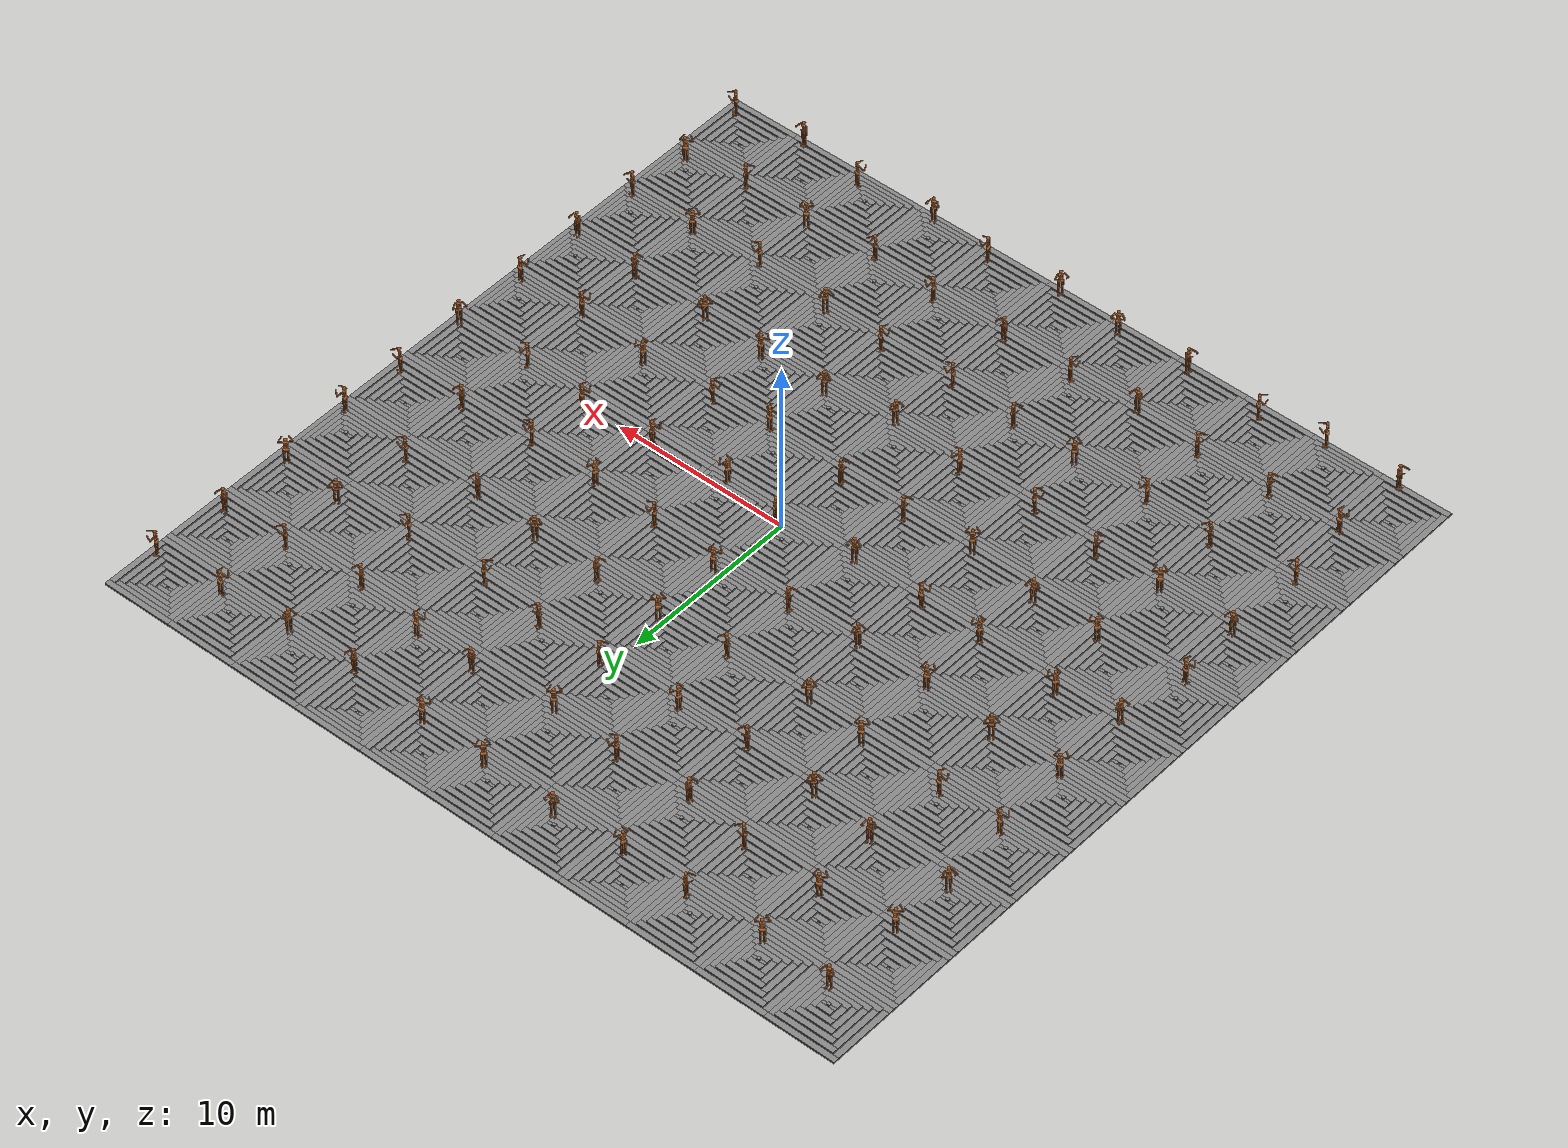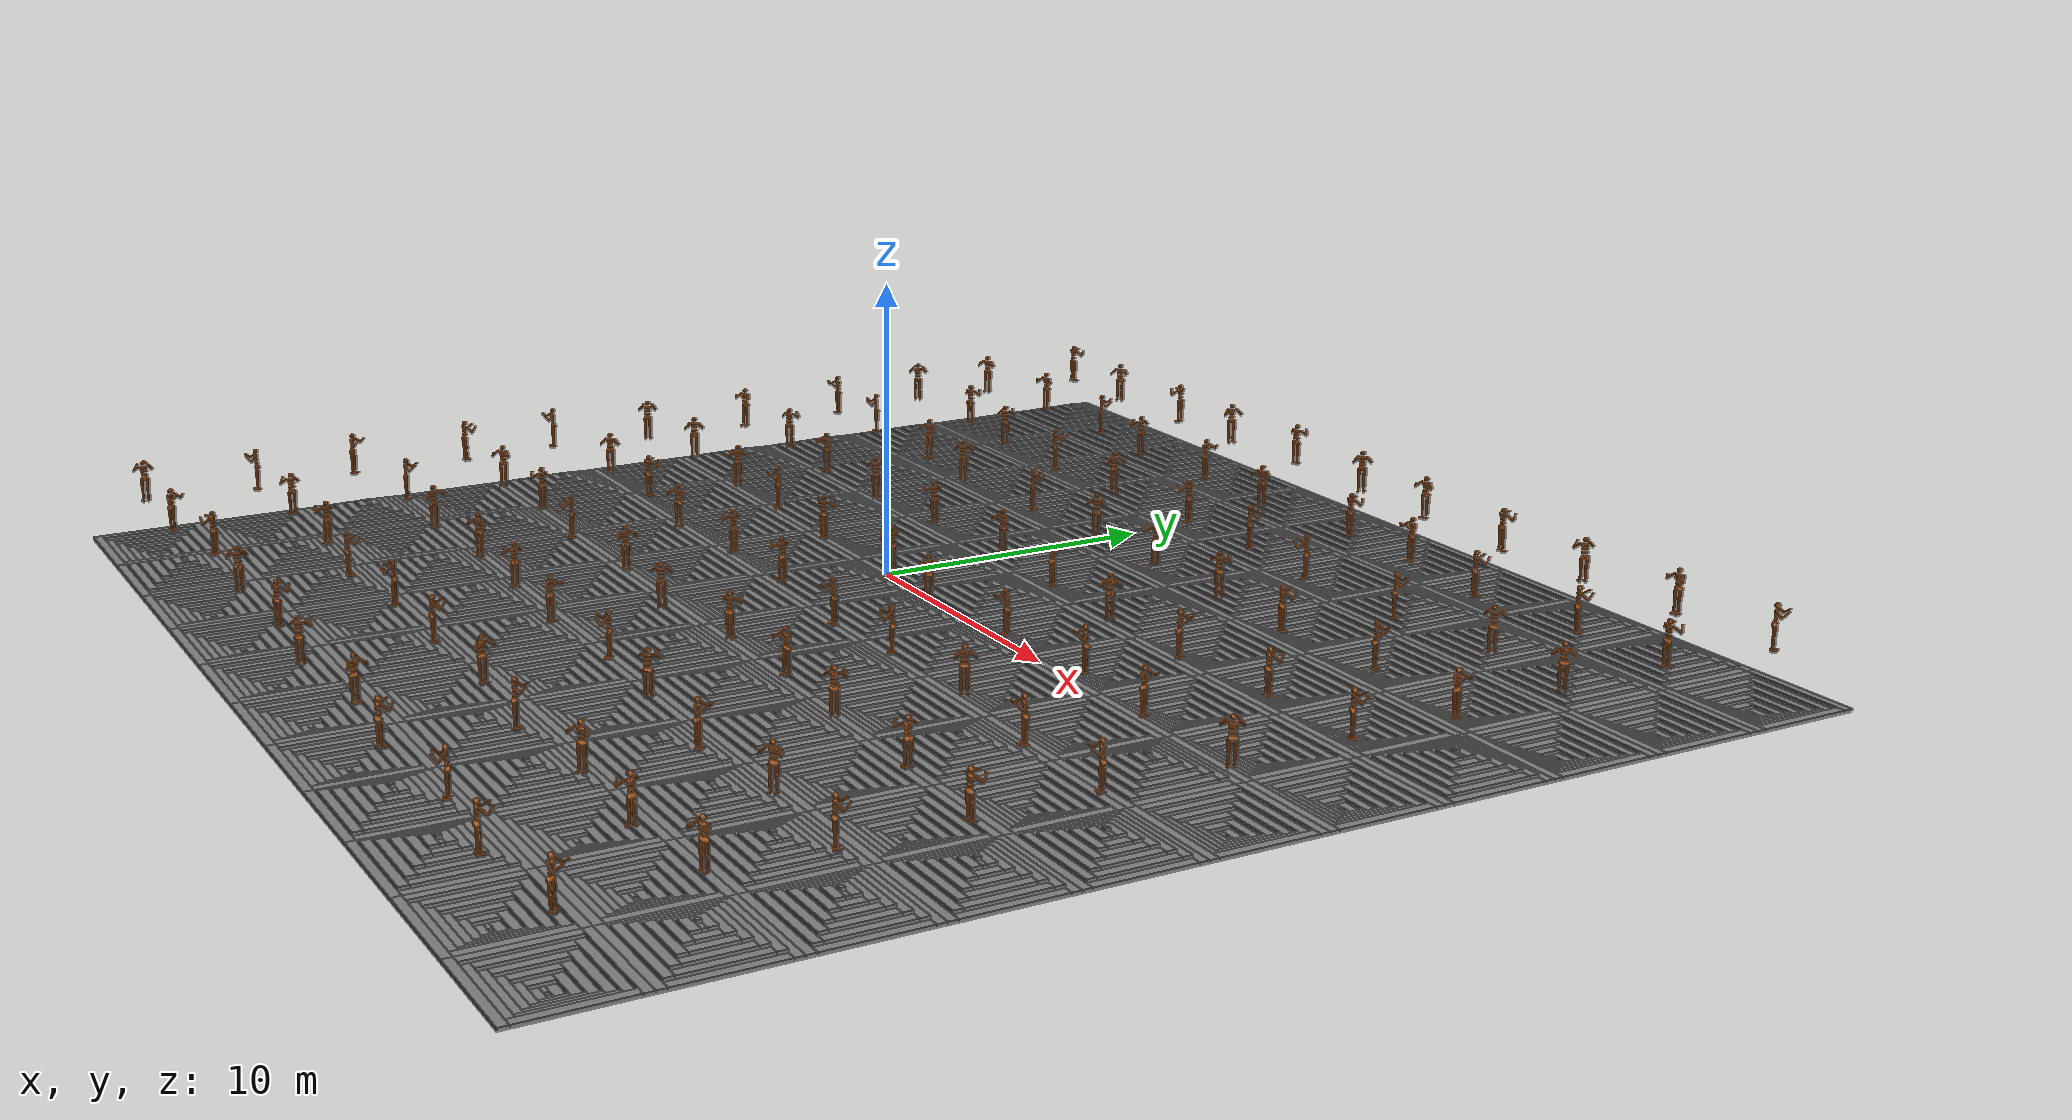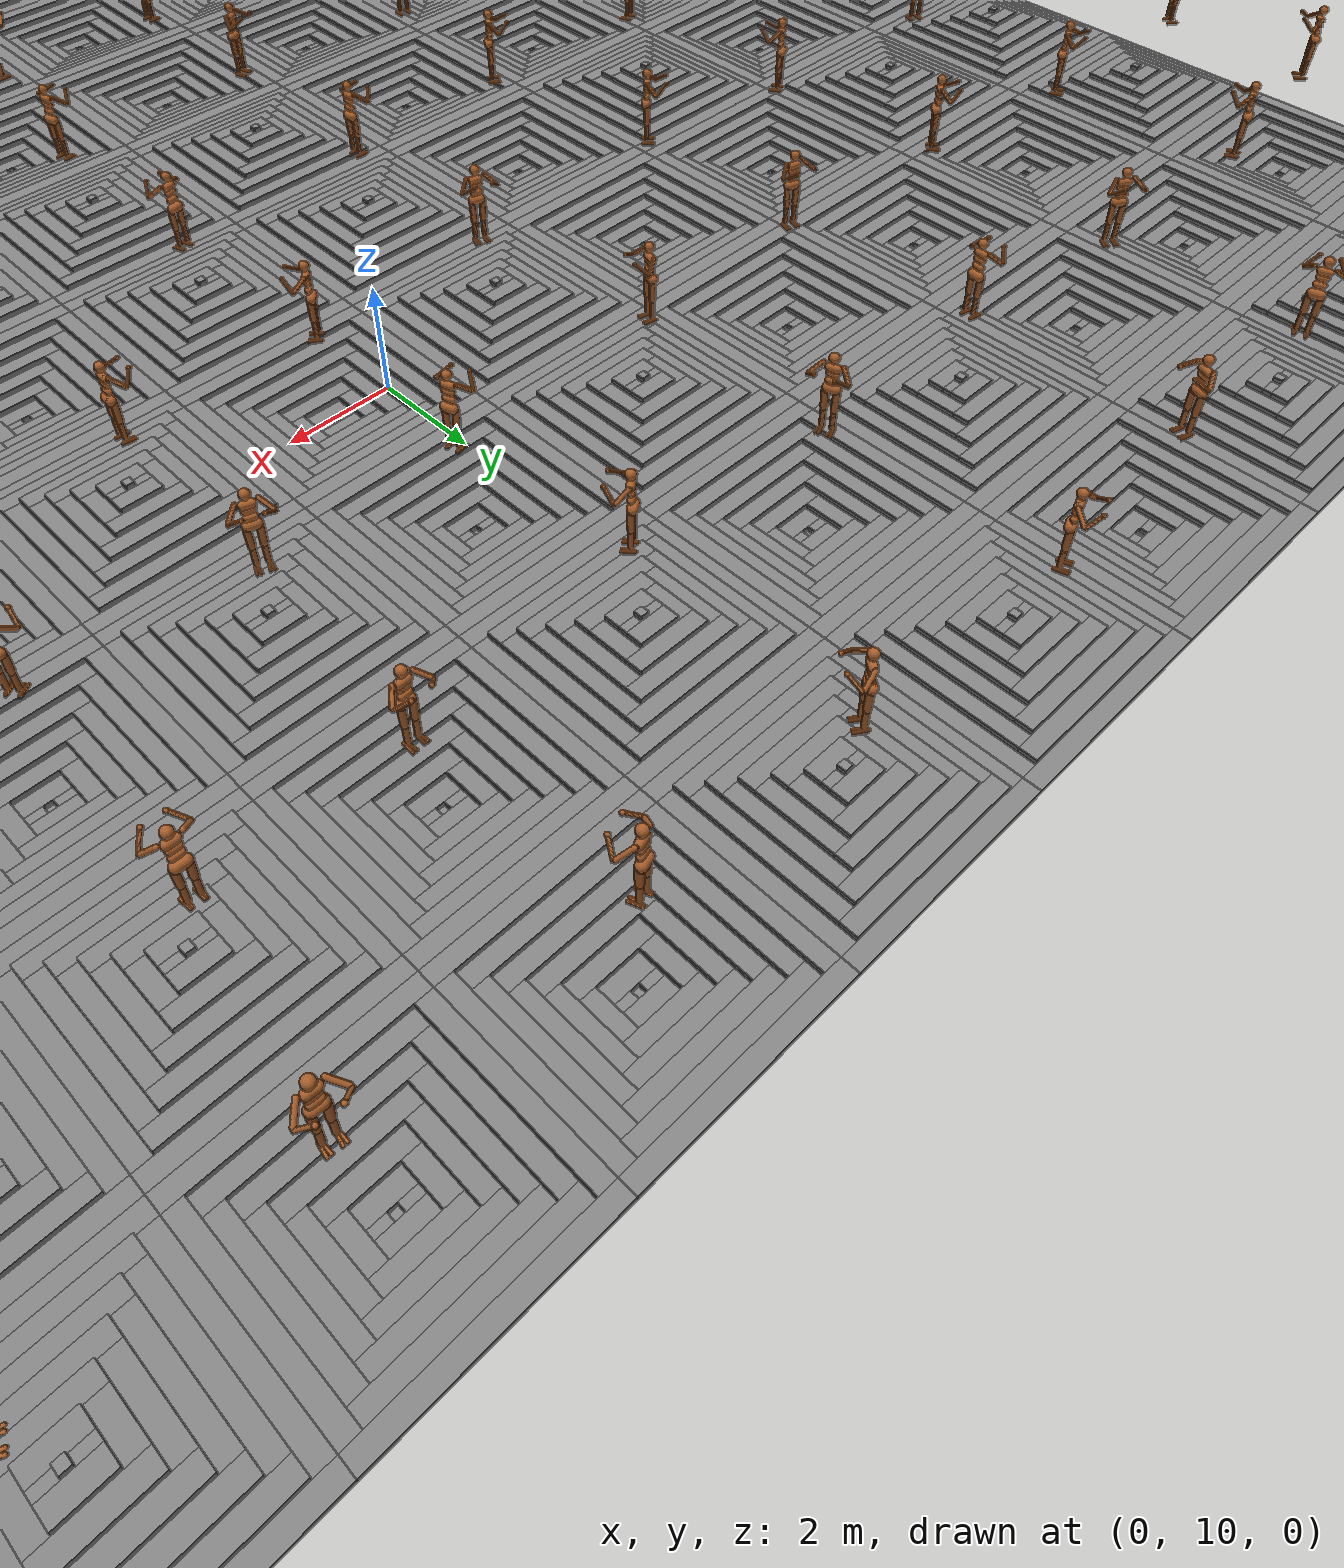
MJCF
<mujoco model="NxM Humanoids">
  <option timestep="0.005"/>

  <size memory="100M"/>

  <asset>
    <texture type="skybox" builtin="gradient" rgb1=".3 .5 .7" rgb2="0 0 0" width="512" height="512"/>
    <texture name="body" type="cube" builtin="flat" mark="cross" width="128" height="128"
             rgb1="0.8 0.6 0.4" rgb2="0.8 0.6 0.4" markrgb="1 1 1" random="0.01"/>
    <material name="body" texture="body" texuniform="true" rgba="0.8 0.6 .4 1"/>
    <texture name="grid" type="2d" builtin="checker" width="512" height="512" rgb1=".1 .2 .3" rgb2=".2 .3 .4"/>
    <material name="grid" texture="grid" texrepeat="1 1" texuniform="true" reflectance=".2"/>
  </asset>

  <default>
    <motor ctrlrange="-1 1" ctrllimited="true"/>
    <default class="body">
      <geom type="capsule" condim="1" friction=".7" solimp=".9 .99 .003" solref=".015 1" material="body"/>
      <joint type="hinge" damping=".2" stiffness="1" armature=".01" limited="true" solimplimit="0 .99 .01"/>
      <default class="big_joint">
        <joint damping="5" stiffness="10"/>
        <default class="big_stiff_joint">
          <joint stiffness="20"/>
        </default>
      </default>
    </default>
  </default>

  <visual>
    <map force="0.1" zfar="30"/>
    <rgba haze="0.15 0.25 0.35 1"/>
    <quality shadowsize="4096"/>
    <global offwidth="800" offheight="800"/>
  </visual>

  <worldbody>
    <light dir="0 0 -.4" diffuse=".8 .8 .8" specular="0.3 0.3 0.3" pos="8 8 14" cutoff="35"/>
    <light dir="0 0 -.4" diffuse=".8 .8 .8" specular="0.3 0.3 0.3" pos="-8 -8 14" cutoff="35"/>
    <light dir="0 0 -.4" diffuse=".8 .8 .8" specular="0.3 0.3 0.3" pos="8 -8 14" cutoff="35"/>
    <light dir="0 0 -.4" diffuse=".8 .8 .8" specular="0.3 0.3 0.3" pos="-8 8 14" cutoff="35"/>
    <geom type="box" pos="-20.000000 -18.160000 -1.475000" size="2.000000 0.160000 0.050000" rgba="0.5 0.5 0.5 1" />
    <geom type="box" pos="-20.000000 -21.840000 -1.475000" size="2.000000 0.160000 0.050000" rgba="0.5 0.5 0.5 1" />
    <geom type="box" pos="-18.160000 -20.000000 -1.475000" size="0.160000 1.680000 0.050000" rgba="0.5 0.5 0.5 1" />
    <geom type="box" pos="-21.840000 -20.000000 -1.475000" size="0.160000 1.680000 0.050000" rgba="0.5 0.5 0.5 1" />
    <geom type="box" pos="-20.000000 -18.480000 -1.575000" size="1.680000 0.160000 0.050000" rgba="0.5 0.5 0.5 1" />
    <geom type="box" pos="-20.000000 -21.520000 -1.575000" size="1.680000 0.160000 0.050000" rgba="0.5 0.5 0.5 1" />
    <geom type="box" pos="-18.480000 -20.000000 -1.575000" size="0.160000 1.360000 0.050000" rgba="0.5 0.5 0.5 1" />
    <geom type="box" pos="-21.520000 -20.000000 -1.575000" size="0.160000 1.360000 0.050000" rgba="0.5 0.5 0.5 1" />
    <geom type="box" pos="-20.000000 -18.800000 -1.675000" size="1.360000 0.160000 0.050000" rgba="0.5 0.5 0.5 1" />
    <geom type="box" pos="-20.000000 -21.200000 -1.675000" size="1.360000 0.160000 0.050000" rgba="0.5 0.5 0.5 1" />
    <geom type="box" pos="-18.800000 -20.000000 -1.675000" size="0.160000 1.040000 0.050000" rgba="0.5 0.5 0.5 1" />
    <geom type="box" pos="-21.200000 -20.000000 -1.675000" size="0.160000 1.040000 0.050000" rgba="0.5 0.5 0.5 1" />
    <geom type="box" pos="-20.000000 -19.120000 -1.775000" size="1.040000 0.160000 0.050000" rgba="0.5 0.5 0.5 1" />
    <geom type="box" pos="-20.000000 -20.880000 -1.775000" size="1.040000 0.160000 0.050000" rgba="0.5 0.5 0.5 1" />
    <geom type="box" pos="-19.120000 -20.000000 -1.775000" size="0.160000 0.720000 0.050000" rgba="0.5 0.5 0.5 1" />
    <geom type="box" pos="-20.880000 -20.000000 -1.775000" size="0.160000 0.720000 0.050000" rgba="0.5 0.5 0.5 1" />
    <geom type="box" pos="-20.000000 -19.440000 -1.875000" size="0.720000 0.160000 0.050000" rgba="0.5 0.5 0.5 1" />
    <geom type="box" pos="-20.000000 -20.560000 -1.875000" size="0.720000 0.160000 0.050000" rgba="0.5 0.5 0.5 1" />
    <geom type="box" pos="-19.440000 -20.000000 -1.875000" size="0.160000 0.400000 0.050000" rgba="0.5 0.5 0.5 1" />
    <geom type="box" pos="-20.560000 -20.000000 -1.875000" size="0.160000 0.400000 0.050000" rgba="0.5 0.5 0.5 1" />
    <geom type="box" pos="-20.000000 -19.760000 -1.975000" size="0.400000 0.160000 0.050000" rgba="0.5 0.5 0.5 1" />
    <geom type="box" pos="-20.000000 -20.240000 -1.975000" size="0.400000 0.160000 0.050000" rgba="0.5 0.5 0.5 1" />
    <geom type="box" pos="-19.760000 -20.000000 -1.975000" size="0.160000 0.080000 0.050000" rgba="0.5 0.5 0.5 1" />
    <geom type="box" pos="-20.240000 -20.000000 -1.975000" size="0.160000 0.080000 0.050000" rgba="0.5 0.5 0.5 1" />
    <geom type="box" pos="-20.000000 -20.000000 -2.075000" size="0.080000 0.080000 0.050000" rgba="0.5 0.5 0.5 1" />

    <geom type="box" pos="-20.000000 -14.160000 -1.475000" size="2.000000 0.160000 0.050000" rgba="0.5 0.5 0.5 1" />
    <geom type="box" pos="-20.000000 -17.840000 -1.475000" size="2.000000 0.160000 0.050000" rgba="0.5 0.5 0.5 1" />
    <geom type="box" pos="-18.160000 -16.000000 -1.475000" size="0.160000 1.680000 0.050000" rgba="0.5 0.5 0.5 1" />
    <geom type="box" pos="-21.840000 -16.000000 -1.475000" size="0.160000 1.680000 0.050000" rgba="0.5 0.5 0.5 1" />
    <geom type="box" pos="-20.000000 -14.480000 -1.575000" size="1.680000 0.160000 0.050000" rgba="0.5 0.5 0.5 1" />
    <geom type="box" pos="-20.000000 -17.520000 -1.575000" size="1.680000 0.160000 0.050000" rgba="0.5 0.5 0.5 1" />
    <geom type="box" pos="-18.480000 -16.000000 -1.575000" size="0.160000 1.360000 0.050000" rgba="0.5 0.5 0.5 1" />
    <geom type="box" pos="-21.520000 -16.000000 -1.575000" size="0.160000 1.360000 0.050000" rgba="0.5 0.5 0.5 1" />
    <geom type="box" pos="-20.000000 -14.800000 -1.675000" size="1.360000 0.160000 0.050000" rgba="0.5 0.5 0.5 1" />
    <geom type="box" pos="-20.000000 -17.200000 -1.675000" size="1.360000 0.160000 0.050000" rgba="0.5 0.5 0.5 1" />
    <geom type="box" pos="-18.800000 -16.000000 -1.675000" size="0.160000 1.040000 0.050000" rgba="0.5 0.5 0.5 1" />
    <geom type="box" pos="-21.200000 -16.000000 -1.675000" size="0.160000 1.040000 0.050000" rgba="0.5 0.5 0.5 1" />
    <geom type="box" pos="-20.000000 -15.120000 -1.775000" size="1.040000 0.160000 0.050000" rgba="0.5 0.5 0.5 1" />
    <geom type="box" pos="-20.000000 -16.880000 -1.775000" size="1.040000 0.160000 0.050000" rgba="0.5 0.5 0.5 1" />
    <geom type="box" pos="-19.120000 -16.000000 -1.775000" size="0.160000 0.720000 0.050000" rgba="0.5 0.5 0.5 1" />
    <geom type="box" pos="-20.880000 -16.000000 -1.775000" size="0.160000 0.720000 0.050000" rgba="0.5 0.5 0.5 1" />
    <geom type="box" pos="-20.000000 -15.440000 -1.875000" size="0.720000 0.160000 0.050000" rgba="0.5 0.5 0.5 1" />
    <geom type="box" pos="-20.000000 -16.560000 -1.875000" size="0.720000 0.160000 0.050000" rgba="0.5 0.5 0.5 1" />
    <geom type="box" pos="-19.440000 -16.000000 -1.875000" size="0.160000 0.400000 0.050000" rgba="0.5 0.5 0.5 1" />
    <geom type="box" pos="-20.560000 -16.000000 -1.875000" size="0.160000 0.400000 0.050000" rgba="0.5 0.5 0.5 1" />
    <geom type="box" pos="-20.000000 -15.760000 -1.975000" size="0.400000 0.160000 0.050000" rgba="0.5 0.5 0.5 1" />
    <geom type="box" pos="-20.000000 -16.240000 -1.975000" size="0.400000 0.160000 0.050000" rgba="0.5 0.5 0.5 1" />
    <geom type="box" pos="-19.760000 -16.000000 -1.975000" size="0.160000 0.080000 0.050000" rgba="0.5 0.5 0.5 1" />
    <geom type="box" pos="-20.240000 -16.000000 -1.975000" size="0.160000 0.080000 0.050000" rgba="0.5 0.5 0.5 1" />
    <geom type="box" pos="-20.000000 -16.000000 -2.075000" size="0.080000 0.080000 0.050000" rgba="0.5 0.5 0.5 1" />

    <geom type="box" pos="-20.000000 -10.160000 -1.475000" size="2.000000 0.160000 0.050000" rgba="0.5 0.5 0.5 1" />
    <geom type="box" pos="-20.000000 -13.840000 -1.475000" size="2.000000 0.160000 0.050000" rgba="0.5 0.5 0.5 1" />
    <geom type="box" pos="-18.160000 -12.000000 -1.475000" size="0.160000 1.680000 0.050000" rgba="0.5 0.5 0.5 1" />
    <geom type="box" pos="-21.840000 -12.000000 -1.475000" size="0.160000 1.680000 0.050000" rgba="0.5 0.5 0.5 1" />
    <geom type="box" pos="-20.000000 -10.480000 -1.375000" size="1.680000 0.160000 0.050000" rgba="0.5 0.5 0.5 1" />
    <geom type="box" pos="-20.000000 -13.520000 -1.375000" size="1.680000 0.160000 0.050000" rgba="0.5 0.5 0.5 1" />
    <geom type="box" pos="-18.480000 -12.000000 -1.375000" size="0.160000 1.360000 0.050000" rgba="0.5 0.5 0.5 1" />
    <geom type="box" pos="-21.520000 -12.000000 -1.375000" size="0.160000 1.360000 0.050000" rgba="0.5 0.5 0.5 1" />
    <geom type="box" pos="-20.000000 -10.800000 -1.275000" size="1.360000 0.160000 0.050000" rgba="0.5 0.5 0.5 1" />
    <geom type="box" pos="-20.000000 -13.200000 -1.275000" size="1.360000 0.160000 0.050000" rgba="0.5 0.5 0.5 1" />
    <geom type="box" pos="-18.800000 -12.000000 -1.275000" size="0.160000 1.040000 0.050000" rgba="0.5 0.5 0.5 1" />
    <geom type="box" pos="-21.200000 -12.000000 -1.275000" size="0.160000 1.040000 0.050000" rgba="0.5 0.5 0.5 1" />
    <geom type="box" pos="-20.000000 -11.120000 -1.175000" size="1.040000 0.160000 0.050000" rgba="0.5 0.5 0.5 1" />
    <geom type="box" pos="-20.000000 -12.880000 -1.175000" size="1.040000 0.160000 0.050000" rgba="0.5 0.5 0.5 1" />
    <geom type="box" pos="-19.120000 -12.000000 -1.175000" size="0.160000 0.720000 0.050000" rgba="0.5 0.5 0.5 1" />
    <geom type="box" pos="-20.880000 -12.000000 -1.175000" size="0.160000 0.720000 0.050000" rgba="0.5 0.5 0.5 1" />
    <geom type="box" pos="-20.000000 -11.440000 -1.075000" size="0.720000 0.160000 0.050000" rgba="0.5 0.5 0.5 1" />
    <geom type="box" pos="-20.000000 -12.560000 -1.075000" size="0.720000 0.160000 0.050000" rgba="0.5 0.5 0.5 1" />
    <geom type="box" pos="-19.440000 -12.000000 -1.075000" size="0.160000 0.400000 0.050000" rgba="0.5 0.5 0.5 1" />
    <geom type="box" pos="-20.560000 -12.000000 -1.075000" size="0.160000 0.400000 0.050000" rgba="0.5 0.5 0.5 1" />
    <geom type="box" pos="-20.000000 -11.760000 -0.975000" size="0.400000 0.160000 0.050000" rgba="0.5 0.5 0.5 1" />
    <geom type="box" pos="-20.000000 -12.240000 -0.975000" size="0.400000 0.160000 0.050000" rgba="0.5 0.5 0.5 1" />
    <geom type="box" pos="-19.760000 -12.000000 -0.975000" size="0.160000 0.080000 0.050000" rgba="0.5 0.5 0.5 1" />
    <geom type="box" pos="-20.240000 -12.000000 -0.975000" size="0.160000 0.080000 0.050000" rgba="0.5 0.5 0.5 1" />
    <geom type="box" pos="-20.000000 -12.000000 -0.875000" size="0.080000 0.080000 0.050000" rgba="0.5 0.5 0.5 1" />

    <geom type="box" pos="-20.000000 -6.160000 -1.475000" size="2.000000 0.160000 0.050000" rgba="0.5 0.5 0.5 1" />
    <geom type="box" pos="-20.000000 -9.840000 -1.475000" size="2.000000 0.160000 0.050000" rgba="0.5 0.5 0.5 1" />
    <geom type="box" pos="-18.160000 -8.000000 -1.475000" size="0.160000 1.680000 0.050000" rgba="0.5 0.5 0.5 1" />
    <geom type="box" pos="-21.840000 -8.000000 -1.475000" size="0.160000 1.680000 0.050000" rgba="0.5 0.5 0.5 1" />
    <geom type="box" pos="-20.000000 -6.480000 -1.575000" size="1.680000 0.160000 0.050000" rgba="0.5 0.5 0.5 1" />
    <geom type="box" pos="-20.000000 -9.520000 -1.575000" size="1.680000 0.160000 0.050000" rgba="0.5 0.5 0.5 1" />
    <geom type="box" pos="-18.480000 -8.000000 -1.575000" size="0.160000 1.360000 0.050000" rgba="0.5 0.5 0.5 1" />
    <geom type="box" pos="-21.520000 -8.000000 -1.575000" size="0.160000 1.360000 0.050000" rgba="0.5 0.5 0.5 1" />
    <geom type="box" pos="-20.000000 -6.800000 -1.675000" size="1.360000 0.160000 0.050000" rgba="0.5 0.5 0.5 1" />
    <geom type="box" pos="-20.000000 -9.200000 -1.675000" size="1.360000 0.160000 0.050000" rgba="0.5 0.5 0.5 1" />
    <geom type="box" pos="-18.800000 -8.000000 -1.675000" size="0.160000 1.040000 0.050000" rgba="0.5 0.5 0.5 1" />
    <geom type="box" pos="-21.200000 -8.000000 -1.675000" size="0.160000 1.040000 0.050000" rgba="0.5 0.5 0.5 1" />
    <geom type="box" pos="-20.000000 -7.120000 -1.775000" size="1.040000 0.160000 0.050000" rgba="0.5 0.5 0.5 1" />
    <geom type="box" pos="-20.000000 -8.880000 -1.775000" size="1.040000 0.160000 0.050000" rgba="0.5 0.5 0.5 1" />
    <geom type="box" pos="-19.120000 -8.000000 -1.775000" size="0.160000 0.720000 0.050000" rgba="0.5 0.5 0.5 1" />
    <geom type="box" pos="-20.880000 -8.000000 -1.775000" size="0.160000 0.720000 0.050000" rgba="0.5 0.5 0.5 1" />
    <geom type="box" pos="-20.000000 -7.440000 -1.875000" size="0.720000 0.160000 0.050000" rgba="0.5 0.5 0.5 1" />
    <geom type="box" pos="-20.000000 -8.560000 -1.875000" size="0.720000 0.160000 0.050000" rgba="0.5 0.5 0.5 1" />
    <geom type="box" pos="-19.440000 -8.000000 -1.875000" size="0.160000 0.400000 0.050000" rgba="0.5 0.5 0.5 1" />
    <geom type="box" pos="-20.560000 -8.000000 -1.875000" size="0.160000 0.400000 0.050000" rgba="0.5 0.5 0.5 1" />
    <geom type="box" pos="-20.000000 -7.760000 -1.975000" size="0.400000 0.160000 0.050000" rgba="0.5 0.5 0.5 1" />
    <geom type="box" pos="-20.000000 -8.240000 -1.975000" size="0.400000 0.160000 0.050000" rgba="0.5 0.5 0.5 1" />
    <geom type="box" pos="-19.760000 -8.000000 -1.975000" size="0.160000 0.080000 0.050000" rgba="0.5 0.5 0.5 1" />
    <geom type="box" pos="-20.240000 -8.000000 -1.975000" size="0.160000 0.080000 0.050000" rgba="0.5 0.5 0.5 1" />
    <geom type="box" pos="-20.000000 -8.000000 -2.075000" size="0.080000 0.080000 0.050000" rgba="0.5 0.5 0.5 1" />

    <geom type="box" pos="-20.000000 -2.160000 -1.475000" size="2.000000 0.160000 0.050000" rgba="0.5 0.5 0.5 1" />
    <geom type="box" pos="-20.000000 -5.840000 -1.475000" size="2.000000 0.160000 0.050000" rgba="0.5 0.5 0.5 1" />
    <geom type="box" pos="-18.160000 -4.000000 -1.475000" size="0.160000 1.680000 0.050000" rgba="0.5 0.5 0.5 1" />
    <geom type="box" pos="-21.840000 -4.000000 -1.475000" size="0.160000 1.680000 0.050000" rgba="0.5 0.5 0.5 1" />
    <geom type="box" pos="-20.000000 -2.480000 -1.375000" size="1.680000 0.160000 0.050000" rgba="0.5 0.5 0.5 1" />
    <geom type="box" pos="-20.000000 -5.520000 -1.375000" size="1.680000 0.160000 0.050000" rgba="0.5 0.5 0.5 1" />
    <geom type="box" pos="-18.480000 -4.000000 -1.375000" size="0.160000 1.360000 0.050000" rgba="0.5 0.5 0.5 1" />
    <geom type="box" pos="-21.520000 -4.000000 -1.375000" size="0.160000 1.360000 0.050000" rgba="0.5 0.5 0.5 1" />
    <geom type="box" pos="-20.000000 -2.800000 -1.275000" size="1.360000 0.160000 0.050000" rgba="0.5 0.5 0.5 1" />
    <geom type="box" pos="-20.000000 -5.200000 -1.275000" size="1.360000 0.160000 0.050000" rgba="0.5 0.5 0.5 1" />
    <geom type="box" pos="-18.800000 -4.000000 -1.275000" size="0.160000 1.040000 0.050000" rgba="0.5 0.5 0.5 1" />
    <geom type="box" pos="-21.200000 -4.000000 -1.275000" size="0.160000 1.040000 0.050000" rgba="0.5 0.5 0.5 1" />
    <geom type="box" pos="-20.000000 -3.120000 -1.175000" size="1.040000 0.160000 0.050000" rgba="0.5 0.5 0.5 1" />
    <geom type="box" pos="-20.000000 -4.880000 -1.175000" size="1.040000 0.160000 0.050000" rgba="0.5 0.5 0.5 1" />
    <geom type="box" pos="-19.120000 -4.000000 -1.175000" size="0.160000 0.720000 0.050000" rgba="0.5 0.5 0.5 1" />
    <geom type="box" pos="-20.880000 -4.000000 -1.175000" size="0.160000 0.720000 0.050000" rgba="0.5 0.5 0.5 1" />
    <geom type="box" pos="-20.000000 -3.440000 -1.075000" size="0.720000 0.160000 0.050000" rgba="0.5 0.5 0.5 1" />
    <geom type="box" pos="-20.000000 -4.560000 -1.075000" size="0.720000 0.160000 0.050000" rgba="0.5 0.5 0.5 1" />
    <geom type="box" pos="-19.440000 -4.000000 -1.075000" size="0.160000 0.400000 0.050000" rgba="0.5 0.5 0.5 1" />
    <geom type="box" pos="-20.560000 -4.000000 -1.075000" size="0.160000 0.400000 0.050000" rgba="0.5 0.5 0.5 1" />
    <geom type="box" pos="-20.000000 -3.760000 -0.975000" size="0.400000 0.160000 0.050000" rgba="0.5 0.5 0.5 1" />
    <geom type="box" pos="-20.000000 -4.240000 -0.975000" size="0.400000 0.160000 0.050000" rgba="0.5 0.5 0.5 1" />
    <geom type="box" pos="-19.760000 -4.000000 -0.975000" size="0.160000 0.080000 0.050000" rgba="0.5 0.5 0.5 1" />
    <geom type="box" pos="-20.240000 -4.000000 -0.975000" size="0.160000 0.080000 0.050000" rgba="0.5 0.5 0.5 1" />
    <geom type="box" pos="-20.000000 -4.000000 -0.875000" size="0.080000 0.080000 0.050000" rgba="0.5 0.5 0.5 1" />

    <geom type="box" pos="-20.000000 1.840000 -1.475000" size="2.000000 0.160000 0.050000" rgba="0.5 0.5 0.5 1" />
    <geom type="box" pos="-20.000000 -1.840000 -1.475000" size="2.000000 0.160000 0.050000" rgba="0.5 0.5 0.5 1" />
    <geom type="box" pos="-18.160000 0.000000 -1.475000" size="0.160000 1.680000 0.050000" rgba="0.5 0.5 0.5 1" />
    <geom type="box" pos="-21.840000 0.000000 -1.475000" size="0.160000 1.680000 0.050000" rgba="0.5 0.5 0.5 1" />
    <geom type="box" pos="-20.000000 1.520000 -1.575000" size="1.680000 0.160000 0.050000" rgba="0.5 0.5 0.5 1" />
    <geom type="box" pos="-20.000000 -1.520000 -1.575000" size="1.680000 0.160000 0.050000" rgba="0.5 0.5 0.5 1" />
    <geom type="box" pos="-18.480000 0.000000 -1.575000" size="0.160000 1.360000 0.050000" rgba="0.5 0.5 0.5 1" />
    <geom type="box" pos="-21.520000 0.000000 -1.575000" size="0.160000 1.360000 0.050000" rgba="0.5 0.5 0.5 1" />
    <geom type="box" pos="-20.000000 1.200000 -1.675000" size="1.360000 0.160000 0.050000" rgba="0.5 0.5 0.5 1" />
    <geom type="box" pos="-20.000000 -1.200000 -1.675000" size="1.360000 0.160000 0.050000" rgba="0.5 0.5 0.5 1" />
    <geom type="box" pos="-18.800000 0.000000 -1.675000" size="0.160000 1.040000 0.050000" rgba="0.5 0.5 0.5 1" />
    <geom type="box" pos="-21.200000 0.000000 -1.675000" size="0.160000 1.040000 0.050000" rgba="0.5 0.5 0.5 1" />
    <geom type="box" pos="-20.000000 0.880000 -1.775000" size="1.040000 0.160000 0.050000" rgba="0.5 0.5 0.5 1" />
    <geom type="box" pos="-20.000000 -0.880000 -1.775000" size="1.040000 0.160000 0.050000" rgba="0.5 0.5 0.5 1" />
    <geom type="box" pos="-19.120000 0.000000 -1.775000" size="0.160000 0.720000 0.050000" rgba="0.5 0.5 0.5 1" />
    <geom type="box" pos="-20.880000 0.000000 -1.775000" size="0.160000 0.720000 0.050000" rgba="0.5 0.5 0.5 1" />
    <geom type="box" pos="-20.000000 0.560000 -1.875000" size="0.720000 0.160000 0.050000" rgba="0.5 0.5 0.5 1" />
    <geom type="box" pos="-20.000000 -0.560000 -1.875000" size="0.720000 0.160000 0.050000" rgba="0.5 0.5 0.5 1" />
    <geom type="box" pos="-19.440000 0.000000 -1.875000" size="0.160000 0.400000 0.050000" rgba="0.5 0.5 0.5 1" />
    <geom type="box" pos="-20.560000 0.000000 -1.875000" size="0.160000 0.400000 0.050000" rgba="0.5 0.5 0.5 1" />
    <geom type="box" pos="-20.000000 0.240000 -1.975000" size="0.400000 0.160000 0.050000" rgba="0.5 0.5 0.5 1" />
    <geom type="box" pos="-20.000000 -0.240000 -1.975000" size="0.400000 0.160000 0.050000" rgba="0.5 0.5 0.5 1" />
    <geom type="box" pos="-19.760000 0.000000 -1.975000" size="0.160000 0.080000 0.050000" rgba="0.5 0.5 0.5 1" />
    <geom type="box" pos="-20.240000 0.000000 -1.975000" size="0.160000 0.080000 0.050000" rgba="0.5 0.5 0.5 1" />
    <geom type="box" pos="-20.000000 0.000000 -2.075000" size="0.080000 0.080000 0.050000" rgba="0.5 0.5 0.5 1" />

    <geom type="box" pos="-20.000000 5.840000 -1.475000" size="2.000000 0.160000 0.050000" rgba="0.5 0.5 0.5 1" />
    <geom type="box" pos="-20.000000 2.160000 -1.475000" size="2.000000 0.160000 0.050000" rgba="0.5 0.5 0.5 1" />
    <geom type="box" pos="-18.160000 4.000000 -1.475000" size="0.160000 1.680000 0.050000" rgba="0.5 0.5 0.5 1" />
    <geom type="box" pos="-21.840000 4.000000 -1.475000" size="0.160000 1.680000 0.050000" rgba="0.5 0.5 0.5 1" />
    <geom type="box" pos="-20.000000 5.520000 -1.375000" size="1.680000 0.160000 0.050000" rgba="0.5 0.5 0.5 1" />
    <geom type="box" pos="-20.000000 2.480000 -1.375000" size="1.680000 0.160000 0.050000" rgba="0.5 0.5 0.5 1" />
    <geom type="box" pos="-18.480000 4.000000 -1.375000" size="0.160000 1.360000 0.050000" rgba="0.5 0.5 0.5 1" />
    <geom type="box" pos="-21.520000 4.000000 -1.375000" size="0.160000 1.360000 0.050000" rgba="0.5 0.5 0.5 1" />
    <geom type="box" pos="-20.000000 5.200000 -1.275000" size="1.360000 0.160000 0.050000" rgba="0.5 0.5 0.5 1" />
    <geom type="box" pos="-20.000000 2.800000 -1.275000" size="1.360000 0.160000 0.050000" rgba="0.5 0.5 0.5 1" />
    <geom type="box" pos="-18.800000 4.000000 -1.275000" size="0.160000 1.040000 0.050000" rgba="0.5 0.5 0.5 1" />
    <geom type="box" pos="-21.200000 4.000000 -1.275000" size="0.160000 1.040000 0.050000" rgba="0.5 0.5 0.5 1" />
    <geom type="box" pos="-20.000000 4.880000 -1.175000" size="1.040000 0.160000 0.050000" rgba="0.5 0.5 0.5 1" />
    <geom type="box" pos="-20.000000 3.120000 -1.175000" size="1.040000 0.160000 0.050000" rgba="0.5 0.5 0.5 1" />
    <geom type="box" pos="-19.120000 4.000000 -1.175000" size="0.160000 0.720000 0.050000" rgba="0.5 0.5 0.5 1" />
    <geom type="box" pos="-20.880000 4.000000 -1.175000" size="0.160000 0.720000 0.050000" rgba="0.5 0.5 0.5 1" />
    <geom type="box" pos="-20.000000 4.560000 -1.075000" size="0.720000 0.160000 0.050000" rgba="0.5 0.5 0.5 1" />
    <geom type="box" pos="-20.000000 3.440000 -1.075000" size="0.720000 0.160000 0.050000" rgba="0.5 0.5 0.5 1" />
    <geom type="box" pos="-19.440000 4.000000 -1.075000" size="0.160000 0.400000 0.050000" rgba="0.5 0.5 0.5 1" />
    <geom type="box" pos="-20.560000 4.000000 -1.075000" size="0.160000 0.400000 0.050000" rgba="0.5 0.5 0.5 1" />
    <geom type="box" pos="-20.000000 4.240000 -0.975000" size="0.400000 0.160000 0.050000" rgba="0.5 0.5 0.5 1" />
    <geom type="box" pos="-20.000000 3.760000 -0.975000" size="0.400000 0.160000 0.050000" rgba="0.5 0.5 0.5 1" />
    <geom type="box" pos="-19.760000 4.000000 -0.975000" size="0.160000 0.080000 0.050000" rgba="0.5 0.5 0.5 1" />
    <geom type="box" pos="-20.240000 4.000000 -0.975000" size="0.160000 0.080000 0.050000" rgba="0.5 0.5 0.5 1" />
    <geom type="box" pos="-20.000000 4.000000 -0.875000" size="0.080000 0.080000 0.050000" rgba="0.5 0.5 0.5 1" />

    <geom type="box" pos="-20.000000 9.840000 -1.475000" size="2.000000 0.160000 0.050000" rgba="0.5 0.5 0.5 1" />
    <geom type="box" pos="-20.000000 6.160000 -1.475000" size="2.000000 0.160000 0.050000" rgba="0.5 0.5 0.5 1" />
    <geom type="box" pos="-18.160000 8.000000 -1.475000" size="0.160000 1.680000 0.050000" rgba="0.5 0.5 0.5 1" />
    <geom type="box" pos="-21.840000 8.000000 -1.475000" size="0.160000 1.680000 0.050000" rgba="0.5 0.5 0.5 1" />
    <geom type="box" pos="-20.000000 9.520000 -1.375000" size="1.680000 0.160000 0.050000" rgba="0.5 0.5 0.5 1" />
    <geom type="box" pos="-20.000000 6.480000 -1.375000" size="1.680000 0.160000 0.050000" rgba="0.5 0.5 0.5 1" />
    <geom type="box" pos="-18.480000 8.000000 -1.375000" size="0.160000 1.360000 0.050000" rgba="0.5 0.5 0.5 1" />
    <geom type="box" pos="-21.520000 8.000000 -1.375000" size="0.160000 1.360000 0.050000" rgba="0.5 0.5 0.5 1" />
    <geom type="box" pos="-20.000000 9.200000 -1.275000" size="1.360000 0.160000 0.050000" rgba="0.5 0.5 0.5 1" />
    <geom type="box" pos="-20.000000 6.800000 -1.275000" size="1.360000 0.160000 0.050000" rgba="0.5 0.5 0.5 1" />
    <geom type="box" pos="-18.800000 8.000000 -1.275000" size="0.160000 1.040000 0.050000" rgba="0.5 0.5 0.5 1" />
    <geom type="box" pos="-21.200000 8.000000 -1.275000" size="0.160000 1.040000 0.050000" rgba="0.5 0.5 0.5 1" />
    <geom type="box" pos="-20.000000 8.880000 -1.175000" size="1.040000 0.160000 0.050000" rgba="0.5 0.5 0.5 1" />
    <geom type="box" pos="-20.000000 7.120000 -1.175000" size="1.040000 0.160000 0.050000" rgba="0.5 0.5 0.5 1" />
    <geom type="box" pos="-19.120000 8.000000 -1.175000" size="0.160000 0.720000 0.050000" rgba="0.5 0.5 0.5 1" />
    <geom type="box" pos="-20.880000 8.000000 -1.175000" size="0.160000 0.720000 0.050000" rgba="0.5 0.5 0.5 1" />
    <geom type="box" pos="-20.000000 8.560000 -1.075000" size="0.720000 0.160000 0.050000" rgba="0.5 0.5 0.5 1" />
    <geom type="box" pos="-20.000000 7.440000 -1.075000" size="0.720000 0.160000 0.050000" rgba="0.5 0.5 0.5 1" />
    <geom type="box" pos="-19.440000 8.000000 -1.075000" size="0.160000 0.400000 0.050000" rgba="0.5 0.5 0.5 1" />
    <geom type="box" pos="-20.560000 8.000000 -1.075000" size="0.160000 0.400000 0.050000" rgba="0.5 0.5 0.5 1" />
    <geom type="box" pos="-20.000000 8.240000 -0.975000" size="0.400000 0.160000 0.050000" rgba="0.5 0.5 0.5 1" />
    <geom type="box" pos="-20.000000 7.760000 -0.975000" size="0.400000 0.160000 0.050000" rgba="0.5 0.5 0.5 1" />
    <geom type="box" pos="-19.760000 8.000000 -0.975000" size="0.160000 0.080000 0.050000" rgba="0.5 0.5 0.5 1" />
    <geom type="box" pos="-20.240000 8.000000 -0.975000" size="0.160000 0.080000 0.050000" rgba="0.5 0.5 0.5 1" />
    <geom type="box" pos="-20.000000 8.000000 -0.875000" size="0.080000 0.080000 0.050000" rgba="0.5 0.5 0.5 1" />

    <geom type="box" pos="-20.000000 13.840000 -1.475000" size="2.000000 0.160000 0.050000" rgba="0.5 0.5 0.5 1" />
    <geom type="box" pos="-20.000000 10.160000 -1.475000" size="2.000000 0.160000 0.050000" rgba="0.5 0.5 0.5 1" />
    <geom type="box" pos="-18.160000 12.000000 -1.475000" size="0.160000 1.680000 0.050000" rgba="0.5 0.5 0.5 1" />
    <geom type="box" pos="-21.840000 12.000000 -1.475000" size="0.160000 1.680000 0.050000" rgba="0.5 0.5 0.5 1" />
    <geom type="box" pos="-20.000000 13.520000 -1.375000" size="1.680000 0.160000 0.050000" rgba="0.5 0.5 0.5 1" />
    <geom type="box" pos="-20.000000 10.480000 -1.375000" size="1.680000 0.160000 0.050000" rgba="0.5 0.5 0.5 1" />
    <geom type="box" pos="-18.480000 12.000000 -1.375000" size="0.160000 1.360000 0.050000" rgba="0.5 0.5 0.5 1" />
    <geom type="box" pos="-21.520000 12.000000 -1.375000" size="0.160000 1.360000 0.050000" rgba="0.5 0.5 0.5 1" />
    <geom type="box" pos="-20.000000 13.200000 -1.275000" size="1.360000 0.160000 0.050000" rgba="0.5 0.5 0.5 1" />
    <geom type="box" pos="-20.000000 10.800000 -1.275000" size="1.360000 0.160000 0.050000" rgba="0.5 0.5 0.5 1" />
    <geom type="box" pos="-18.800000 12.000000 -1.275000" size="0.160000 1.040000 0.050000" rgba="0.5 0.5 0.5 1" />
    <geom type="box" pos="-21.200000 12.000000 -1.275000" size="0.160000 1.040000 0.050000" rgba="0.5 0.5 0.5 1" />
    <geom type="box" pos="-20.000000 12.880000 -1.175000" size="1.040000 0.160000 0.050000" rgba="0.5 0.5 0.5 1" />
    <geom type="box" pos="-20.000000 11.120000 -1.175000" size="1.040000 0.160000 0.050000" rgba="0.5 0.5 0.5 1" />
    <geom type="box" pos="-19.120000 12.000000 -1.175000" size="0.160000 0.720000 0.050000" rgba="0.5 0.5 0.5 1" />
    <geom type="box" pos="-20.880000 12.000000 -1.175000" size="0.160000 0.720000 0.050000" rgba="0.5 0.5 0.5 1" />
    <geom type="box" pos="-20.000000 12.560000 -1.075000" size="0.720000 0.160000 0.050000" rgba="0.5 0.5 0.5 1" />
    <geom type="box" pos="-20.000000 11.440000 -1.075000" size="0.720000 0.160000 0.050000" rgba="0.5 0.5 0.5 1" />
    <geom type="box" pos="-19.440000 12.000000 -1.075000" size="0.160000 0.400000 0.050000" rgba="0.5 0.5 0.5 1" />
    <geom type="box" pos="-20.560000 12.000000 -1.075000" size="0.160000 0.400000 0.050000" rgba="0.5 0.5 0.5 1" />
    <geom type="box" pos="-20.000000 12.240000 -0.975000" size="0.400000 0.160000 0.050000" rgba="0.5 0.5 0.5 1" />
    <geom type="box" pos="-20.000000 11.760000 -0.975000" size="0.400000 0.160000 0.050000" rgba="0.5 0.5 0.5 1" />
    <geom type="box" pos="-19.760000 12.000000 -0.975000" size="0.160000 0.080000 0.050000" rgba="0.5 0.5 0.5 1" />
    <geom type="box" pos="-20.240000 12.000000 -0.975000" size="0.160000 0.080000 0.050000" rgba="0.5 0.5 0.5 1" />
    <geom type="box" pos="-20.000000 12.000000 -0.875000" size="0.080000 0.080000 0.050000" rgba="0.5 0.5 0.5 1" />

    <geom type="box" pos="-20.000000 17.840000 -1.475000" size="2.000000 0.160000 0.050000" rgba="0.5 0.5 0.5 1" />
    <geom type="box" pos="-20.000000 14.160000 -1.475000" size="2.000000 0.160000 0.050000" rgba="0.5 0.5 0.5 1" />
    <geom type="box" pos="-18.160000 16.000000 -1.475000" size="0.160000 1.680000 0.050000" rgba="0.5 0.5 0.5 1" />
    <geom type="box" pos="-21.840000 16.000000 -1.475000" size="0.160000 1.680000 0.050000" rgba="0.5 0.5 0.5 1" />
    <geom type="box" pos="-20.000000 17.520000 -1.575000" size="1.680000 0.160000 0.050000" rgba="0.5 0.5 0.5 1" />
    <geom type="box" pos="-20.000000 14.480000 -1.575000" size="1.680000 0.160000 0.050000" rgba="0.5 0.5 0.5 1" />
    <geom type="box" pos="-18.480000 16.000000 -1.575000" size="0.160000 1.360000 0.050000" rgba="0.5 0.5 0.5 1" />
    <geom type="box" pos="-21.520000 16.000000 -1.575000" size="0.160000 1.360000 0.050000" rgba="0.5 0.5 0.5 1" />
    <geom type="box" pos="-20.000000 17.200000 -1.675000" size="1.360000 0.160000 0.050000" rgba="0.5 0.5 0.5 1" />
    <geom type="box" pos="-20.000000 14.800000 -1.675000" size="1.360000 0.160000 0.050000" rgba="0.5 0.5 0.5 1" />
    <geom type="box" pos="-18.800000 16.000000 -1.675000" size="0.160000 1.040000 0.050000" rgba="0.5 0.5 0.5 1" />
    <geom type="box" pos="-21.200000 16.000000 -1.675000" size="0.160000 1.040000 0.050000" rgba="0.5 0.5 0.5 1" />
    <geom type="box" pos="-20.000000 16.880000 -1.775000" size="1.040000 0.160000 0.050000" rgba="0.5 0.5 0.5 1" />
    <geom type="box" pos="-20.000000 15.120000 -1.775000" size="1.040000 0.160000 0.050000" rgba="0.5 0.5 0.5 1" />
    <geom type="box" pos="-19.120000 16.000000 -1.775000" size="0.160000 0.720000 0.050000" rgba="0.5 0.5 0.5 1" />
    <geom type="box" pos="-20.880000 16.000000 -1.775000" size="0.160000 0.720000 0.050000" rgba="0.5 0.5 0.5 1" />
    <geom type="box" pos="-20.000000 16.560000 -1.875000" size="0.720000 0.160000 0.050000" rgba="0.5 0.5 0.5 1" />
    <geom type="box" pos="-20.000000 15.440000 -1.875000" size="0.720000 0.160000 0.050000" rgba="0.5 0.5 0.5 1" />
    <geom type="box" pos="-19.440000 16.000000 -1.875000" size="0.160000 0.400000 0.050000" rgba="0.5 0.5 0.5 1" />
    <geom type="box" pos="-20.560000 16.000000 -1.875000" size="0.160000 0.400000 0.050000" rgba="0.5 0.5 0.5 1" />
    <geom type="box" pos="-20.000000 16.240000 -1.975000" size="0.400000 0.160000 0.050000" rgba="0.5 0.5 0.5 1" />
    <geom type="box" pos="-20.000000 15.760000 -1.975000" size="0.400000 0.160000 0.050000" rgba="0.5 0.5 0.5 1" />
    <geom type="box" pos="-19.760000 16.000000 -1.975000" size="0.160000 0.080000 0.050000" rgba="0.5 0.5 0.5 1" />
    <geom type="box" pos="-20.240000 16.000000 -1.975000" size="0.160000 0.080000 0.050000" rgba="0.5 0.5 0.5 1" />
    <geom type="box" pos="-20.000000 16.000000 -2.075000" size="0.080000 0.080000 0.050000" rgba="0.5 0.5 0.5 1" />

    <geom type="box" pos="-20.000000 21.840000 -1.475000" size="2.000000 0.160000 0.050000" rgba="0.5 0.5 0.5 1" />
    <geom type="box" pos="-20.000000 18.160000 -1.475000" size="2.000000 0.160000 0.050000" rgba="0.5 0.5 0.5 1" />
    <geom type="box" pos="-18.160000 20.000000 -1.475000" size="0.160000 1.680000 0.050000" rgba="0.5 0.5 0.5 1" />
    <geom type="box" pos="-21.840000 20.000000 -1.475000" size="0.160000 1.680000 0.050000" rgba="0.5 0.5 0.5 1" />
    <geom type="box" pos="-20.000000 21.520000 -1.375000" size="1.680000 0.160000 0.050000" rgba="0.5 0.5 0.5 1" />
    <geom type="box" pos="-20.000000 18.480000 -1.375000" size="1.680000 0.160000 0.050000" rgba="0.5 0.5 0.5 1" />
    <geom type="box" pos="-18.480000 20.000000 -1.375000" size="0.160000 1.360000 0.050000" rgba="0.5 0.5 0.5 1" />
    <geom type="box" pos="-21.520000 20.000000 -1.375000" size="0.160000 1.360000 0.050000" rgba="0.5 0.5 0.5 1" />
    <geom type="box" pos="-20.000000 21.200000 -1.275000" size="1.360000 0.160000 0.050000" rgba="0.5 0.5 0.5 1" />
    <geom type="box" pos="-20.000000 18.800000 -1.275000" size="1.360000 0.160000 0.050000" rgba="0.5 0.5 0.5 1" />
    <geom type="box" pos="-18.800000 20.000000 -1.275000" size="0.160000 1.040000 0.050000" rgba="0.5 0.5 0.5 1" />
    <geom type="box" pos="-21.200000 20.000000 -1.275000" size="0.160000 1.040000 0.050000" rgba="0.5 0.5 0.5 1" />
    <geom type="box" pos="-20.000000 20.880000 -1.175000" size="1.040000 0.160000 0.050000" rgba="0.5 0.5 0.5 1" />
    <geom type="box" pos="-20.000000 19.120000 -1.175000" size="1.040000 0.160000 0.050000" rgba="0.5 0.5 0.5 1" />
    <geom type="box" pos="-19.120000 20.000000 -1.175000" size="0.160000 0.720000 0.050000" rgba="0.5 0.5 0.5 1" />
    <geom type="box" pos="-20.880000 20.000000 -1.175000" size="0.160000 0.720000 0.050000" rgba="0.5 0.5 0.5 1" />
    <geom type="box" pos="-20.000000 20.560000 -1.075000" size="0.720000 0.160000 0.050000" rgba="0.5 0.5 0.5 1" />
    <geom type="box" pos="-20.000000 19.440000 -1.075000" size="0.720000 0.160000 0.050000" rgba="0.5 0.5 0.5 1" />
    <geom type="box" pos="-19.440000 20.000000 -1.075000" size="0.160000 0.400000 0.050000" rgba="0.5 0.5 0.5 1" />
    <geom type="box" pos="-20.560000 20.000000 -1.075000" size="0.160000 0.400000 0.050000" rgba="0.5 0.5 0.5 1" />
    <geom type="box" pos="-20.000000 20.240000 -0.975000" size="0.400000 0.160000 0.050000" rgba="0.5 0.5 0.5 1" />
    <geom type="box" pos="-20.000000 19.760000 -0.975000" size="0.400000 0.160000 0.050000" rgba="0.5 0.5 0.5 1" />
    <geom type="box" pos="-19.760000 20.000000 -0.975000" size="0.160000 0.080000 0.050000" rgba="0.5 0.5 0.5 1" />
    <geom type="box" pos="-20.240000 20.000000 -0.975000" size="0.160000 0.080000 0.050000" rgba="0.5 0.5 0.5 1" />
    <geom type="box" pos="-20.000000 20.000000 -0.875000" size="0.080000 0.080000 0.050000" rgba="0.5 0.5 0.5 1" />

    <geom type="box" pos="-16.000000 -18.160000 -1.475000" size="2.000000 0.160000 0.050000" rgba="0.5 0.5 0.5 1" />
    <geom type="box" pos="-16.000000 -21.840000 -1.475000" size="2.000000 0.160000 0.050000" rgba="0.5 0.5 0.5 1" />
    <geom type="box" pos="-14.160000 -20.000000 -1.475000" size="0.160000 1.680000 0.050000" rgba="0.5 0.5 0.5 1" />
    <geom type="box" pos="-17.840000 -20.000000 -1.475000" size="0.160000 1.680000 0.050000" rgba="0.5 0.5 0.5 1" />
    <geom type="box" pos="-16.000000 -18.480000 -1.375000" size="1.680000 0.160000 0.050000" rgba="0.5 0.5 0.5 1" />
    <geom type="box" pos="-16.000000 -21.520000 -1.375000" size="1.680000 0.160000 0.050000" rgba="0.5 0.5 0.5 1" />
    <geom type="box" pos="-14.480000 -20.000000 -1.375000" size="0.160000 1.360000 0.050000" rgba="0.5 0.5 0.5 1" />
    <geom type="box" pos="-17.520000 -20.000000 -1.375000" size="0.160000 1.360000 0.050000" rgba="0.5 0.5 0.5 1" />
    <geom type="box" pos="-16.000000 -18.800000 -1.275000" size="1.360000 0.160000 0.050000" rgba="0.5 0.5 0.5 1" />
    <geom type="box" pos="-16.000000 -21.200000 -1.275000" size="1.360000 0.160000 0.050000" rgba="0.5 0.5 0.5 1" />
    <geom type="box" pos="-14.800000 -20.000000 -1.275000" size="0.160000 1.040000 0.050000" rgba="0.5 0.5 0.5 1" />
    <geom type="box" pos="-17.200000 -20.000000 -1.275000" size="0.160000 1.040000 0.050000" rgba="0.5 0.5 0.5 1" />
    <geom type="box" pos="-16.000000 -19.120000 -1.175000" size="1.040000 0.160000 0.050000" rgba="0.5 0.5 0.5 1" />
    <geom type="box" pos="-16.000000 -20.880000 -1.175000" size="1.040000 0.160000 0.050000" rgba="0.5 0.5 0.5 1" />
    <geom type="box" pos="-15.120000 -20.000000 -1.175000" size="0.160000 0.720000 0.050000" rgba="0.5 0.5 0.5 1" />
    <geom type="box" pos="-16.880000 -20.000000 -1.175000" size="0.160000 0.720000 0.050000" rgba="0.5 0.5 0.5 1" />
    <geom type="box" pos="-16.000000 -19.440000 -1.075000" size="0.720000 0.160000 0.050000" rgba="0.5 0.5 0.5 1" />
    <geom type="box" pos="-16.000000 -20.560000 -1.075000" size="0.720000 0.160000 0.050000" rgba="0.5 0.5 0.5 1" />
    <geom type="box" pos="-15.440000 -20.000000 -1.075000" size="0.160000 0.400000 0.050000" rgba="0.5 0.5 0.5 1" />
    <geom type="box" pos="-16.560000 -20.000000 -1.075000" size="0.160000 0.400000 0.050000" rgba="0.5 0.5 0.5 1" />
    <geom type="box" pos="-16.000000 -19.760000 -0.975000" size="0.400000 0.160000 0.050000" rgba="0.5 0.5 0.5 1" />
    <geom type="box" pos="-16.000000 -20.240000 -0.975000" size="0.400000 0.160000 0.050000" rgba="0.5 0.5 0.5 1" />
    <geom type="box" pos="-15.760000 -20.000000 -0.975000" size="0.160000 0.080000 0.050000" rgba="0.5 0.5 0.5 1" />
    <geom type="box" pos="-16.240000 -20.000000 -0.975000" size="0.160000 0.080000 0.050000" rgba="0.5 0.5 0.5 1" />
    <geom type="box" pos="-16.000000 -20.000000 -0.875000" size="0.080000 0.080000 0.050000" rgba="0.5 0.5 0.5 1" />

    <geom type="box" pos="-16.000000 -14.160000 -1.475000" size="2.000000 0.160000 0.050000" rgba="0.5 0.5 0.5 1" />
    <geom type="box" pos="-16.000000 -17.840000 -1.475000" size="2.000000 0.160000 0.050000" rgba="0.5 0.5 0.5 1" />
    <geom type="box" pos="-14.160000 -16.000000 -1.475000" size="0.160000 1.680000 0.050000" rgba="0.5 0.5 0.5 1" />
    <geom type="box" pos="-17.840000 -16.000000 -1.475000" size="0.160000 1.680000 0.050000" rgba="0.5 0.5 0.5 1" />
    <geom type="box" pos="-16.000000 -14.480000 -1.375000" size="1.680000 0.160000 0.050000" rgba="0.5 0.5 0.5 1" />
    <geom type="box" pos="-16.000000 -17.520000 -1.375000" size="1.680000 0.160000 0.050000" rgba="0.5 0.5 0.5 1" />
    <geom type="box" pos="-14.480000 -16.000000 -1.375000" size="0.160000 1.360000 0.050000" rgba="0.5 0.5 0.5 1" />
    <geom type="box" pos="-17.520000 -16.000000 -1.375000" size="0.160000 1.360000 0.050000" rgba="0.5 0.5 0.5 1" />
    <geom type="box" pos="-16.000000 -14.800000 -1.275000" size="1.360000 0.160000 0.050000" rgba="0.5 0.5 0.5 1" />
    <geom type="box" pos="-16.000000 -17.200000 -1.275000" size="1.360000 0.160000 0.050000" rgba="0.5 0.5 0.5 1" />
    <geom type="box" pos="-14.800000 -16.000000 -1.275000" size="0.160000 1.040000 0.050000" rgba="0.5 0.5 0.5 1" />
    <geom type="box" pos="-17.200000 -16.000000 -1.275000" size="0.160000 1.040000 0.050000" rgba="0.5 0.5 0.5 1" />
    <geom type="box" pos="-16.000000 -15.120000 -1.175000" size="1.040000 0.160000 0.050000" rgba="0.5 0.5 0.5 1" />
    <geom type="box" pos="-16.000000 -16.880000 -1.175000" size="1.040000 0.160000 0.050000" rgba="0.5 0.5 0.5 1" />
    <geom type="box" pos="-15.120000 -16.000000 -1.175000" size="0.160000 0.720000 0.050000" rgba="0.5 0.5 0.5 1" />
    <geom type="box" pos="-16.880000 -16.000000 -1.175000" size="0.160000 0.720000 0.050000" rgba="0.5 0.5 0.5 1" />
    <geom type="box" pos="-16.000000 -15.440000 -1.075000" size="0.720000 0.160000 0.050000" rgba="0.5 0.5 0.5 1" />
    <geom type="box" pos="-16.000000 -16.560000 -1.075000" size="0.720000 0.160000 0.050000" rgba="0.5 0.5 0.5 1" />
    <geom type="box" pos="-15.440000 -16.000000 -1.075000" size="0.160000 0.400000 0.050000" rgba="0.5 0.5 0.5 1" />
    <geom type="box" pos="-16.560000 -16.000000 -1.075000" size="0.160000 0.400000 0.050000" rgba="0.5 0.5 0.5 1" />
    <geom type="box" pos="-16.000000 -15.760000 -0.975000" size="0.400000 0.160000 0.050000" rgba="0.5 0.5 0.5 1" />
    <geom type="box" pos="-16.000000 -16.240000 -0.975000" size="0.400000 0.160000 0.050000" rgba="0.5 0.5 0.5 1" />
    <geom type="box" pos="-15.760000 -16.000000 -0.975000" size="0.160000 0.080000 0.050000" rgba="0.5 0.5 0.5 1" />
    <geom type="box" pos="-16.240000 -16.000000 -0.975000" size="0.160000 0.080000 0.050000" rgba="0.5 0.5 0.5 1" />
    <geom type="box" pos="-16.000000 -16.000000 -0.875000" size="0.080000 0.080000 0.050000" rgba="0.5 0.5 0.5 1" />

    <geom type="box" pos="-16.000000 -10.160000 -1.475000" size="2.000000 0.160000 0.050000" rgba="0.5 0.5 0.5 1" />
    <geom type="box" pos="-16.000000 -13.840000 -1.475000" size="2.000000 0.160000 0.050000" rgba="0.5 0.5 0.5 1" />
    <geom type="box" pos="-14.160000 -12.000000 -1.475000" size="0.160000 1.680000 0.050000" rgba="0.5 0.5 0.5 1" />
    <geom type="box" pos="-17.840000 -12.000000 -1.475000" size="0.160000 1.680000 0.050000" rgba="0.5 0.5 0.5 1" />
    <geom type="box" pos="-16.000000 -10.480000 -1.575000" size="1.680000 0.160000 0.050000" rgba="0.5 0.5 0.5 1" />
    <geom type="box" pos="-16.000000 -13.520000 -1.575000" size="1.680000 0.160000 0.050000" rgba="0.5 0.5 0.5 1" />
    <geom type="box" pos="-14.480000 -12.000000 -1.575000" size="0.160000 1.360000 0.050000" rgba="0.5 0.5 0.5 1" />
    <geom type="box" pos="-17.520000 -12.000000 -1.575000" size="0.160000 1.360000 0.050000" rgba="0.5 0.5 0.5 1" />
    <geom type="box" pos="-16.000000 -10.800000 -1.675000" size="1.360000 0.160000 0.050000" rgba="0.5 0.5 0.5 1" />
    <geom type="box" pos="-16.000000 -13.200000 -1.675000" size="1.360000 0.160000 0.050000" rgba="0.5 0.5 0.5 1" />
    <geom type="box" pos="-14.800000 -12.000000 -1.675000" size="0.160000 1.040000 0.050000" rgba="0.5 0.5 0.5 1" />
    <geom type="box" pos="-17.200000 -12.000000 -1.675000" size="0.160000 1.040000 0.050000" rgba="0.5 0.5 0.5 1" />
    <geom type="box" pos="-16.000000 -11.120000 -1.775000" size="1.040000 0.160000 0.050000" rgba="0.5 0.5 0.5 1" />
    <geom type="box" pos="-16.000000 -12.880000 -1.775000" size="1.040000 0.160000 0.050000" rgba="0.5 0.5 0.5 1" />
    <geom type="box" pos="-15.120000 -12.000000 -1.775000" size="0.160000 0.720000 0.050000" rgba="0.5 0.5 0.5 1" />
    <geom type="box" pos="-16.880000 -12.000000 -1.775000" size="0.160000 0.720000 0.050000" rgba="0.5 0.5 0.5 1" />
    <geom type="box" pos="-16.000000 -11.440000 -1.875000" size="0.720000 0.160000 0.050000" rgba="0.5 0.5 0.5 1" />
    <geom type="box" pos="-16.000000 -12.560000 -1.875000" size="0.720000 0.160000 0.050000" rgba="0.5 0.5 0.5 1" />
    <geom type="box" pos="-15.440000 -12.000000 -1.875000" size="0.160000 0.400000 0.050000" rgba="0.5 0.5 0.5 1" />
    <geom type="box" pos="-16.560000 -12.000000 -1.875000" size="0.160000 0.400000 0.050000" rgba="0.5 0.5 0.5 1" />
    <geom type="box" pos="-16.000000 -11.760000 -1.975000" size="0.400000 0.160000 0.050000" rgba="0.5 0.5 0.5 1" />
    <geom type="box" pos="-16.000000 -12.240000 -1.975000" size="0.400000 0.160000 0.050000" rgba="0.5 0.5 0.5 1" />
    <geom type="box" pos="-15.760000 -12.000000 -1.975000" size="0.160000 0.080000 0.050000" rgba="0.5 0.5 0.5 1" />
    <geom type="box" pos="-16.240000 -12.000000 -1.975000" size="0.160000 0.080000 0.050000" rgba="0.5 0.5 0.5 1" />
    <geom type="box" pos="-16.000000 -12.000000 -2.075000" size="0.080000 0.080000 0.050000" rgba="0.5 0.5 0.5 1" />

    <geom type="box" pos="-16.000000 -6.160000 -1.475000" size="2.000000 0.160000 0.050000" rgba="0.5 0.5 0.5 1" />
    <geom type="box" pos="-16.000000 -9.840000 -1.475000" size="2.000000 0.160000 0.050000" rgba="0.5 0.5 0.5 1" />
    <geom type="box" pos="-14.160000 -8.000000 -1.475000" size="0.160000 1.680000 0.050000" rgba="0.5 0.5 0.5 1" />
    <geom type="box" pos="-17.840000 -8.000000 -1.475000" size="0.160000 1.680000 0.050000" rgba="0.5 0.5 0.5 1" />
    <geom type="box" pos="-16.000000 -6.480000 -1.375000" size="1.680000 0.160000 0.050000" rgba="0.5 0.5 0.5 1" />
    <geom type="box" pos="-16.000000 -9.520000 -1.375000" size="1.680000 0.160000 0.050000" rgba="0.5 0.5 0.5 1" />
    <geom type="box" pos="-14.480000 -8.000000 -1.375000" size="0.160000 1.360000 0.050000" rgba="0.5 0.5 0.5 1" />
    <geom type="box" pos="-17.520000 -8.000000 -1.375000" size="0.160000 1.360000 0.050000" rgba="0.5 0.5 0.5 1" />
    <geom type="box" pos="-16.000000 -6.800000 -1.275000" size="1.360000 0.160000 0.050000" rgba="0.5 0.5 0.5 1" />
    <geom type="box" pos="-16.000000 -9.200000 -1.275000" size="1.360000 0.160000 0.050000" rgba="0.5 0.5 0.5 1" />
    <geom type="box" pos="-14.800000 -8.000000 -1.275000" size="0.160000 1.040000 0.050000" rgba="0.5 0.5 0.5 1" />
    <geom type="box" pos="-17.200000 -8.000000 -1.275000" size="0.160000 1.040000 0.050000" rgba="0.5 0.5 0.5 1" />
    <geom type="box" pos="-16.000000 -7.120000 -1.175000" size="1.040000 0.160000 0.050000" rgba="0.5 0.5 0.5 1" />
    <geom type="box" pos="-16.000000 -8.880000 -1.175000" size="1.040000 0.160000 0.050000" rgba="0.5 0.5 0.5 1" />
    <geom type="box" pos="-15.120000 -8.000000 -1.175000" size="0.160000 0.720000 0.050000" rgba="0.5 0.5 0.5 1" />
    <geom type="box" pos="-16.880000 -8.000000 -1.175000" size="0.160000 0.720000 0.050000" rgba="0.5 0.5 0.5 1" />
    <geom type="box" pos="-16.000000 -7.440000 -1.075000" size="0.720000 0.160000 0.050000" rgba="0.5 0.5 0.5 1" />
    <geom type="box" pos="-16.000000 -8.560000 -1.075000" size="0.720000 0.160000 0.050000" rgba="0.5 0.5 0.5 1" />
    <geom type="box" pos="-15.440000 -8.000000 -1.075000" size="0.160000 0.400000 0.050000" rgba="0.5 0.5 0.5 1" />
    <geom type="box" pos="-16.560000 -8.000000 -1.075000" size="0.160000 0.400000 0.050000" rgba="0.5 0.5 0.5 1" />
    <geom type="box" pos="-16.000000 -7.760000 -0.975000" size="0.400000 0.160000 0.050000" rgba="0.5 0.5 0.5 1" />
    <geom type="box" pos="-16.000000 -8.240000 -0.975000" size="0.400000 0.160000 0.050000" rgba="0.5 0.5 0.5 1" />
    <geom type="box" pos="-15.760000 -8.000000 -0.975000" size="0.160000 0.080000 0.050000" rgba="0.5 0.5 0.5 1" />
    <geom type="box" pos="-16.240000 -8.000000 -0.975000" size="0.160000 0.080000 0.050000" rgba="0.5 0.5 0.5 1" />
    <geom type="box" pos="-16.000000 -8.000000 -0.875000" size="0.080000 0.080000 0.050000" rgba="0.5 0.5 0.5 1" />

    <geom type="box" pos="-16.000000 -2.160000 -1.475000" size="2.000000 0.160000 0.050000" rgba="0.5 0.5 0.5 1" />
    <geom type="box" pos="-16.000000 -5.840000 -1.475000" size="2.000000 0.160000 0.050000" rgba="0.5 0.5 0.5 1" />
    <geom type="box" pos="-14.160000 -4.000000 -1.475000" size="0.160000 1.680000 0.050000" rgba="0.5 0.5 0.5 1" />
    <geom type="box" pos="-17.840000 -4.000000 -1.475000" size="0.160000 1.680000 0.050000" rgba="0.5 0.5 0.5 1" />
    <geom type="box" pos="-16.000000 -2.480000 -1.575000" size="1.680000 0.160000 0.050000" rgba="0.5 0.5 0.5 1" />
    <geom type="box" pos="-16.000000 -5.520000 -1.575000" size="1.680000 0.160000 0.050000" rgba="0.5 0.5 0.5 1" />
    <geom type="box" pos="-14.480000 -4.000000 -1.575000" size="0.160000 1.360000 0.050000" rgba="0.5 0.5 0.5 1" />
    <geom type="box" pos="-17.520000 -4.000000 -1.575000" size="0.160000 1.360000 0.050000" rgba="0.5 0.5 0.5 1" />
    <geom type="box" pos="-16.000000 -2.800000 -1.675000" size="1.360000 0.160000 0.050000" rgba="0.5 0.5 0.5 1" />
    <geom type="box" pos="-16.000000 -5.200000 -1.675000" size="1.360000 0.160000 0.050000" rgba="0.5 0.5 0.5 1" />
    <geom type="box" pos="-14.800000 -4.000000 -1.675000" size="0.160000 1.040000 0.050000" rgba="0.5 0.5 0.5 1" />
    <geom type="box" pos="-17.200000 -4.000000 -1.675000" size="0.160000 1.040000 0.050000" rgba="0.5 0.5 0.5 1" />
    <geom type="box" pos="-16.000000 -3.120000 -1.775000" size="1.040000 0.160000 0.050000" rgba="0.5 0.5 0.5 1" />
    <geom type="box" pos="-16.000000 -4.880000 -1.775000" size="1.040000 0.160000 0.050000" rgba="0.5 0.5 0.5 1" />
    <geom type="box" pos="-15.120000 -4.000000 -1.775000" size="0.160000 0.720000 0.050000" rgba="0.5 0.5 0.5 1" />
    <geom type="box" pos="-16.880000 -4.000000 -1.775000" size="0.160000 0.720000 0.050000" rgba="0.5 0.5 0.5 1" />
    <geom type="box" pos="-16.000000 -3.440000 -1.875000" size="0.720000 0.160000 0.050000" rgba="0.5 0.5 0.5 1" />
    <geom type="box" pos="-16.000000 -4.560000 -1.875000" size="0.720000 0.160000 0.050000" rgba="0.5 0.5 0.5 1" />
    <geom type="box" pos="-15.440000 -4.000000 -1.875000" size="0.160000 0.400000 0.050000" rgba="0.5 0.5 0.5 1" />
    <geom type="box" pos="-16.560000 -4.000000 -1.875000" size="0.160000 0.400000 0.050000" rgba="0.5 0.5 0.5 1" />
    <geom type="box" pos="-16.000000 -3.760000 -1.975000" size="0.400000 0.160000 0.050000" rgba="0.5 0.5 0.5 1" />
    <geom type="box" pos="-16.000000 -4.240000 -1.975000" size="0.400000 0.160000 0.050000" rgba="0.5 0.5 0.5 1" />
    <geom type="box" pos="-15.760000 -4.000000 -1.975000" size="0.160000 0.080000 0.050000" rgba="0.5 0.5 0.5 1" />
    <geom type="box" pos="-16.240000 -4.000000 -1.975000" size="0.160000 0.080000 0.050000" rgba="0.5 0.5 0.5 1" />
    <geom type="box" pos="-16.000000 -4.000000 -2.075000" size="0.080000 0.080000 0.050000" rgba="0.5 0.5 0.5 1" />

    <geom type="box" pos="-16.000000 1.840000 -1.475000" size="2.000000 0.160000 0.050000" rgba="0.5 0.5 0.5 1" />
    <geom type="box" pos="-16.000000 -1.840000 -1.475000" size="2.000000 0.160000 0.050000" rgba="0.5 0.5 0.5 1" />
    <geom type="box" pos="-14.160000 0.000000 -1.475000" size="0.160000 1.680000 0.050000" rgba="0.5 0.5 0.5 1" />
    <geom type="box" pos="-17.840000 0.000000 -1.475000" size="0.160000 1.680000 0.050000" rgba="0.5 0.5 0.5 1" />
    <geom type="box" pos="-16.000000 1.520000 -1.575000" size="1.680000 0.160000 0.050000" rgba="0.5 0.5 0.5 1" />
    <geom type="box" pos="-16.000000 -1.520000 -1.575000" size="1.680000 0.160000 0.050000" rgba="0.5 0.5 0.5 1" />
    <geom type="box" pos="-14.480000 0.000000 -1.575000" size="0.160000 1.360000 0.050000" rgba="0.5 0.5 0.5 1" />
    <geom type="box" pos="-17.520000 0.000000 -1.575000" size="0.160000 1.360000 0.050000" rgba="0.5 0.5 0.5 1" />
    <geom type="box" pos="-16.000000 1.200000 -1.675000" size="1.360000 0.160000 0.050000" rgba="0.5 0.5 0.5 1" />
    <geom type="box" pos="-16.000000 -1.200000 -1.675000" size="1.360000 0.160000 0.050000" rgba="0.5 0.5 0.5 1" />
    <geom type="box" pos="-14.800000 0.000000 -1.675000" size="0.160000 1.040000 0.050000" rgba="0.5 0.5 0.5 1" />
    <geom type="box" pos="-17.200000 0.000000 -1.675000" size="0.160000 1.040000 0.050000" rgba="0.5 0.5 0.5 1" />
    <geom type="box" pos="-16.000000 0.880000 -1.775000" size="1.040000 0.160000 0.050000" rgba="0.5 0.5 0.5 1" />
    <geom type="box" pos="-16.000000 -0.880000 -1.775000" size="1.040000 0.160000 0.050000" rgba="0.5 0.5 0.5 1" />
    <geom type="box" pos="-15.120000 0.000000 -1.775000" size="0.160000 0.720000 0.050000" rgba="0.5 0.5 0.5 1" />
    <geom type="box" pos="-16.880000 0.000000 -1.775000" size="0.160000 0.720000 0.050000" rgba="0.5 0.5 0.5 1" />
    <geom type="box" pos="-16.000000 0.560000 -1.875000" size="0.720000 0.160000 0.050000" rgba="0.5 0.5 0.5 1" />
    <geom type="box" pos="-16.000000 -0.560000 -1.875000" size="0.720000 0.160000 0.050000" rgba="0.5 0.5 0.5 1" />
    <geom type="box" pos="-15.440000 0.000000 -1.875000" size="0.160000 0.400000 0.050000" rgba="0.5 0.5 0.5 1" />
    <geom type="box" pos="-16.560000 0.000000 -1.875000" size="0.160000 0.400000 0.050000" rgba="0.5 0.5 0.5 1" />
    <geom type="box" pos="-16.000000 0.240000 -1.975000" size="0.400000 0.160000 0.050000" rgba="0.5 0.5 0.5 1" />
    <geom type="box" pos="-16.000000 -0.240000 -1.975000" size="0.400000 0.160000 0.050000" rgba="0.5 0.5 0.5 1" />
    <geom type="box" pos="-15.760000 0.000000 -1.975000" size="0.160000 0.080000 0.050000" rgba="0.5 0.5 0.5 1" />
    <geom type="box" pos="-16.240000 0.000000 -1.975000" size="0.160000 0.080000 0.050000" rgba="0.5 0.5 0.5 1" />
    <geom type="box" pos="-16.000000 0.000000 -2.075000" size="0.080000 0.080000 0.050000" rgba="0.5 0.5 0.5 1" />

    <geom type="box" pos="-16.000000 5.840000 -1.475000" size="2.000000 0.160000 0.050000" rgba="0.5 0.5 0.5 1" />
    <geom type="box" pos="-16.000000 2.160000 -1.475000" size="2.000000 0.160000 0.050000" rgba="0.5 0.5 0.5 1" />
    <geom type="box" pos="-14.160000 4.000000 -1.475000" size="0.160000 1.680000 0.050000" rgba="0.5 0.5 0.5 1" />
    <geom type="box" pos="-17.840000 4.000000 -1.475000" size="0.160000 1.680000 0.050000" rgba="0.5 0.5 0.5 1" />
    <geom type="box" pos="-16.000000 5.520000 -1.575000" size="1.680000 0.160000 0.050000" rgba="0.5 0.5 0.5 1" />
    <geom type="box" pos="-16.000000 2.480000 -1.575000" size="1.680000 0.160000 0.050000" rgba="0.5 0.5 0.5 1" />
    <geom type="box" pos="-14.480000 4.000000 -1.575000" size="0.160000 1.360000 0.050000" rgba="0.5 0.5 0.5 1" />
    <geom type="box" pos="-17.520000 4.000000 -1.575000" size="0.160000 1.360000 0.050000" rgba="0.5 0.5 0.5 1" />
    <geom type="box" pos="-16.000000 5.200000 -1.675000" size="1.360000 0.160000 0.050000" rgba="0.5 0.5 0.5 1" />
    <geom type="box" pos="-16.000000 2.800000 -1.675000" size="1.360000 0.160000 0.050000" rgba="0.5 0.5 0.5 1" />
    <geom type="box" pos="-14.800000 4.000000 -1.675000" size="0.160000 1.040000 0.050000" rgba="0.5 0.5 0.5 1" />
    <geom type="box" pos="-17.200000 4.000000 -1.675000" size="0.160000 1.040000 0.050000" rgba="0.5 0.5 0.5 1" />
    <geom type="box" pos="-16.000000 4.880000 -1.775000" size="1.040000 0.160000 0.050000" rgba="0.5 0.5 0.5 1" />
    <geom type="box" pos="-16.000000 3.120000 -1.775000" size="1.040000 0.160000 0.050000" rgba="0.5 0.5 0.5 1" />
    <geom type="box" pos="-15.120000 4.000000 -1.775000" size="0.160000 0.720000 0.050000" rgba="0.5 0.5 0.5 1" />
    <geom type="box" pos="-16.880000 4.000000 -1.775000" size="0.160000 0.720000 0.050000" rgba="0.5 0.5 0.5 1" />
    <geom type="box" pos="-16.000000 4.560000 -1.875000" size="0.720000 0.160000 0.050000" rgba="0.5 0.5 0.5 1" />
    <geom type="box" pos="-16.000000 3.440000 -1.875000" size="0.720000 0.160000 0.050000" rgba="0.5 0.5 0.5 1" />
    <geom type="box" pos="-15.440000 4.000000 -1.875000" size="0.160000 0.400000 0.050000" rgba="0.5 0.5 0.5 1" />
    <geom type="box" pos="-16.560000 4.000000 -1.875000" size="0.160000 0.400000 0.050000" rgba="0.5 0.5 0.5 1" />
    <geom type="box" pos="-16.000000 4.240000 -1.975000" size="0.400000 0.160000 0.050000" rgba="0.5 0.5 0.5 1" />
    <geom type="box" pos="-16.000000 3.760000 -1.975000" size="0.400000 0.160000 0.050000" rgba="0.5 0.5 0.5 1" />
    <geom type="box" pos="-15.760000 4.000000 -1.975000" size="0.160000 0.080000 0.050000" rgba="0.5 0.5 0.5 1" />
    <geom type="box" pos="-16.240000 4.000000 -1.975000" size="0.160000 0.080000 0.050000" rgba="0.5 0.5 0.5 1" />
    <geom type="box" pos="-16.000000 4.000000 -2.075000" size="0.080000 0.080000 0.050000" rgba="0.5 0.5 0.5 1" />

    <geom type="box" pos="-16.000000 9.840000 -1.475000" size="2.000000 0.160000 0.050000" rgba="0.5 0.5 0.5 1" />
    <geom type="box" pos="-16.000000 6.160000 -1.475000" size="2.000000 0.160000 0.050000" rgba="0.5 0.5 0.5 1" />
    <geom type="box" pos="-14.160000 8.000000 -1.475000" size="0.160000 1.680000 0.050000" rgba="0.5 0.5 0.5 1" />
    <geom type="box" pos="-17.840000 8.000000 -1.475000" size="0.160000 1.680000 0.050000" rgba="0.5 0.5 0.5 1" />
    <geom type="box" pos="-16.000000 9.520000 -1.375000" size="1.680000 0.160000 0.050000" rgba="0.5 0.5 0.5 1" />
    <geom type="box" pos="-16.000000 6.480000 -1.375000" size="1.680000 0.160000 0.050000" rgba="0.5 0.5 0.5 1" />
    <geom type="box" pos="-14.480000 8.000000 -1.375000" size="0.160000 1.360000 0.050000" rgba="0.5 0.5 0.5 1" />
    <geom type="box" pos="-17.520000 8.000000 -1.375000" size="0.160000 1.360000 0.050000" rgba="0.5 0.5 0.5 1" />
    <geom type="box" pos="-16.000000 9.200000 -1.275000" size="1.360000 0.160000 0.050000" rgba="0.5 0.5 0.5 1" />
    <geom type="box" pos="-16.000000 6.800000 -1.275000" size="1.360000 0.160000 0.050000" rgba="0.5 0.5 0.5 1" />
    <geom type="box" pos="-14.800000 8.000000 -1.275000" size="0.160000 1.040000 0.050000" rgba="0.5 0.5 0.5 1" />
    <geom type="box" pos="-17.200000 8.000000 -1.275000" size="0.160000 1.040000 0.050000" rgba="0.5 0.5 0.5 1" />
    <geom type="box" pos="-16.000000 8.880000 -1.175000" size="1.040000 0.160000 0.050000" rgba="0.5 0.5 0.5 1" />
    <geom type="box" pos="-16.000000 7.120000 -1.175000" size="1.040000 0.160000 0.050000" rgba="0.5 0.5 0.5 1" />
    <geom type="box" pos="-15.120000 8.000000 -1.175000" size="0.160000 0.720000 0.050000" rgba="0.5 0.5 0.5 1" />
    <geom type="box" pos="-16.880000 8.000000 -1.175000" size="0.160000 0.720000 0.050000" rgba="0.5 0.5 0.5 1" />
    <geom type="box" pos="-16.000000 8.560000 -1.075000" size="0.720000 0.160000 0.050000" rgba="0.5 0.5 0.5 1" />
    <geom type="box" pos="-16.000000 7.440000 -1.075000" size="0.720000 0.160000 0.050000" rgba="0.5 0.5 0.5 1" />
    <geom type="box" pos="-15.440000 8.000000 -1.075000" size="0.160000 0.400000 0.050000" rgba="0.5 0.5 0.5 1" />
    <geom type="box" pos="-16.560000 8.000000 -1.075000" size="0.160000 0.400000 0.050000" rgba="0.5 0.5 0.5 1" />
    <geom type="box" pos="-16.000000 8.240000 -0.975000" size="0.400000 0.160000 0.050000" rgba="0.5 0.5 0.5 1" />
    <geom type="box" pos="-16.000000 7.760000 -0.975000" size="0.400000 0.160000 0.050000" rgba="0.5 0.5 0.5 1" />
    <geom type="box" pos="-15.760000 8.000000 -0.975000" size="0.160000 0.080000 0.050000" rgba="0.5 0.5 0.5 1" />
    <geom type="box" pos="-16.240000 8.000000 -0.975000" size="0.160000 0.080000 0.050000" rgba="0.5 0.5 0.5 1" />
    <geom type="box" pos="-16.000000 8.000000 -0.875000" size="0.080000 0.080000 0.050000" rgba="0.5 0.5 0.5 1" />

    <geom type="box" pos="-16.000000 13.840000 -1.475000" size="2.000000 0.160000 0.050000" rgba="0.5 0.5 0.5 1" />
    <geom type="box" pos="-16.000000 10.160000 -1.475000" size="2.000000 0.160000 0.050000" rgba="0.5 0.5 0.5 1" />
    <geom type="box" pos="-14.160000 12.000000 -1.475000" size="0.160000 1.680000 0.050000" rgba="0.5 0.5 0.5 1" />
    <geom type="box" pos="-17.840000 12.000000 -1.475000" size="0.160000 1.680000 0.050000" rgba="0.5 0.5 0.5 1" />
    <geom type="box" pos="-16.000000 13.520000 -1.575000" size="1.680000 0.160000 0.050000" rgba="0.5 0.5 0.5 1" />
    <geom type="box" pos="-16.000000 10.480000 -1.575000" size="1.680000 0.160000 0.050000" rgba="0.5 0.5 0.5 1" />
    <geom type="box" pos="-14.480000 12.000000 -1.575000" size="0.160000 1.360000 0.050000" rgba="0.5 0.5 0.5 1" />
    <geom type="box" pos="-17.520000 12.000000 -1.575000" size="0.160000 1.360000 0.050000" rgba="0.5 0.5 0.5 1" />
    <geom type="box" pos="-16.000000 13.200000 -1.675000" size="1.360000 0.160000 0.050000" rgba="0.5 0.5 0.5 1" />
    <geom type="box" pos="-16.000000 10.800000 -1.675000" size="1.360000 0.160000 0.050000" rgba="0.5 0.5 0.5 1" />
    <geom type="box" pos="-14.800000 12.000000 -1.675000" size="0.160000 1.040000 0.050000" rgba="0.5 0.5 0.5 1" />
    <geom type="box" pos="-17.200000 12.000000 -1.675000" size="0.160000 1.040000 0.050000" rgba="0.5 0.5 0.5 1" />
    <geom type="box" pos="-16.000000 12.880000 -1.775000" size="1.040000 0.160000 0.050000" rgba="0.5 0.5 0.5 1" />
    <geom type="box" pos="-16.000000 11.120000 -1.775000" size="1.040000 0.160000 0.050000" rgba="0.5 0.5 0.5 1" />
    <geom type="box" pos="-15.120000 12.000000 -1.775000" size="0.160000 0.720000 0.050000" rgba="0.5 0.5 0.5 1" />
    <geom type="box" pos="-16.880000 12.000000 -1.775000" size="0.160000 0.720000 0.050000" rgba="0.5 0.5 0.5 1" />
    <geom type="box" pos="-16.000000 12.560000 -1.875000" size="0.720000 0.160000 0.050000" rgba="0.5 0.5 0.5 1" />
    <geom type="box" pos="-16.000000 11.440000 -1.875000" size="0.720000 0.160000 0.050000" rgba="0.5 0.5 0.5 1" />
    <geom type="box" pos="-15.440000 12.000000 -1.875000" size="0.160000 0.400000 0.050000" rgba="0.5 0.5 0.5 1" />
    <geom type="box" pos="-16.560000 12.000000 -1.875000" size="0.160000 0.400000 0.050000" rgba="0.5 0.5 0.5 1" />
    <geom type="box" pos="-16.000000 12.240000 -1.975000" size="0.400000 0.160000 0.050000" rgba="0.5 0.5 0.5 1" />
    <geom type="box" pos="-16.000000 11.760000 -1.975000" size="0.400000 0.160000 0.050000" rgba="0.5 0.5 0.5 1" />
    <geom type="box" pos="-15.760000 12.000000 -1.975000" size="0.160000 0.080000 0.050000" rgba="0.5 0.5 0.5 1" />
    <geom type="box" pos="-16.240000 12.000000 -1.975000" size="0.160000 0.080000 0.050000" rgba="0.5 0.5 0.5 1" />
    <geom type="box" pos="-16.000000 12.000000 -2.075000" size="0.080000 0.080000 0.050000" rgba="0.5 0.5 0.5 1" />

    <geom type="box" pos="-16.000000 17.840000 -1.475000" size="2.000000 0.160000 0.050000" rgba="0.5 0.5 0.5 1" />
    <geom type="box" pos="-16.000000 14.160000 -1.475000" size="2.000000 0.160000 0.050000" rgba="0.5 0.5 0.5 1" />
    <geom type="box" pos="-14.160000 16.000000 -1.475000" size="0.160000 1.680000 0.050000" rgba="0.5 0.5 0.5 1" />
    <geom type="box" pos="-17.840000 16.000000 -1.475000" size="0.160000 1.680000 0.050000" rgba="0.5 0.5 0.5 1" />
    <geom type="box" pos="-16.000000 17.520000 -1.575000" size="1.680000 0.160000 0.050000" rgba="0.5 0.5 0.5 1" />
    <geom type="box" pos="-16.000000 14.480000 -1.575000" size="1.680000 0.160000 0.050000" rgba="0.5 0.5 0.5 1" />
    <geom type="box" pos="-14.480000 16.000000 -1.575000" size="0.160000 1.360000 0.050000" rgba="0.5 0.5 0.5 1" />
    <geom type="box" pos="-17.520000 16.000000 -1.575000" size="0.160000 1.360000 0.050000" rgba="0.5 0.5 0.5 1" />
    <geom type="box" pos="-16.000000 17.200000 -1.675000" size="1.360000 0.160000 0.050000" rgba="0.5 0.5 0.5 1" />
    <geom type="box" pos="-16.000000 14.800000 -1.675000" size="1.360000 0.160000 0.050000" rgba="0.5 0.5 0.5 1" />
    <geom type="box" pos="-14.800000 16.000000 -1.675000" size="0.160000 1.040000 0.050000" rgba="0.5 0.5 0.5 1" />
    <geom type="box" pos="-17.200000 16.000000 -1.675000" size="0.160000 1.040000 0.050000" rgba="0.5 0.5 0.5 1" />
    <geom type="box" pos="-16.000000 16.880000 -1.775000" size="1.040000 0.160000 0.050000" rgba="0.5 0.5 0.5 1" />
    <geom type="box" pos="-16.000000 15.120000 -1.775000" size="1.040000 0.160000 0.050000" rgba="0.5 0.5 0.5 1" />
    <geom type="box" pos="-15.120000 16.000000 -1.775000" size="0.160000 0.720000 0.050000" rgba="0.5 0.5 0.5 1" />
    <geom type="box" pos="-16.880000 16.000000 -1.775000" size="0.160000 0.720000 0.050000" rgba="0.5 0.5 0.5 1" />
    <geom type="box" pos="-16.000000 16.560000 -1.875000" size="0.720000 0.160000 0.050000" rgba="0.5 0.5 0.5 1" />
    <geom type="box" pos="-16.000000 15.440000 -1.875000" size="0.720000 0.160000 0.050000" rgba="0.5 0.5 0.5 1" />
    <geom type="box" pos="-15.440000 16.000000 -1.875000" size="0.160000 0.400000 0.050000" rgba="0.5 0.5 0.5 1" />
    <geom type="box" pos="-16.560000 16.000000 -1.875000" size="0.160000 0.400000 0.050000" rgba="0.5 0.5 0.5 1" />
    <geom type="box" pos="-16.000000 16.240000 -1.975000" size="0.400000 0.160000 0.050000" rgba="0.5 0.5 0.5 1" />
    <geom type="box" pos="-16.000000 15.760000 -1.975000" size="0.400000 0.160000 0.050000" rgba="0.5 0.5 0.5 1" />
    <geom type="box" pos="-15.760000 16.000000 -1.975000" size="0.160000 0.080000 0.050000" rgba="0.5 0.5 0.5 1" />
    <geom type="box" pos="-16.240000 16.000000 -1.975000" size="0.160000 0.080000 0.050000" rgba="0.5 0.5 0.5 1" />
    <geom type="box" pos="-16.000000 16.000000 -2.075000" size="0.080000 0.080000 0.050000" rgba="0.5 0.5 0.5 1" />

    <geom type="box" pos="-16.000000 21.840000 -1.475000" size="2.000000 0.160000 0.050000" rgba="0.5 0.5 0.5 1" />
    <geom type="box" pos="-16.000000 18.160000 -1.475000" size="2.000000 0.160000 0.050000" rgba="0.5 0.5 0.5 1" />
    <geom type="box" pos="-14.160000 20.000000 -1.475000" size="0.160000 1.680000 0.050000" rgba="0.5 0.5 0.5 1" />
    <geom type="box" pos="-17.840000 20.000000 -1.475000" size="0.160000 1.680000 0.050000" rgba="0.5 0.5 0.5 1" />
    <geom type="box" pos="-16.000000 21.520000 -1.375000" size="1.680000 0.160000 0.050000" rgba="0.5 0.5 0.5 1" />
    <geom type="box" pos="-16.000000 18.480000 -1.375000" size="1.680000 0.160000 0.050000" rgba="0.5 0.5 0.5 1" />
    <geom type="box" pos="-14.480000 20.000000 -1.375000" size="0.160000 1.360000 0.050000" rgba="0.5 0.5 0.5 1" />
    <geom type="box" pos="-17.520000 20.000000 -1.375000" size="0.160000 1.360000 0.050000" rgba="0.5 0.5 0.5 1" />
    <geom type="box" pos="-16.000000 21.200000 -1.275000" size="1.360000 0.160000 0.050000" rgba="0.5 0.5 0.5 1" />
    <geom type="box" pos="-16.000000 18.800000 -1.275000" size="1.360000 0.160000 0.050000" rgba="0.5 0.5 0.5 1" />
    <geom type="box" pos="-14.800000 20.000000 -1.275000" size="0.160000 1.040000 0.050000" rgba="0.5 0.5 0.5 1" />
    <geom type="box" pos="-17.200000 20.000000 -1.275000" size="0.160000 1.040000 0.050000" rgba="0.5 0.5 0.5 1" />
    <geom type="box" pos="-16.000000 20.880000 -1.175000" size="1.040000 0.160000 0.050000" rgba="0.5 0.5 0.5 1" />
    <geom type="box" pos="-16.000000 19.120000 -1.175000" size="1.040000 0.160000 0.050000" rgba="0.5 0.5 0.5 1" />
    <geom type="box" pos="-15.120000 20.000000 -1.175000" size="0.160000 0.720000 0.050000" rgba="0.5 0.5 0.5 1" />
    <geom type="box" pos="-16.880000 20.000000 -1.175000" size="0.160000 0.720000 0.050000" rgba="0.5 0.5 0.5 1" />
    <geom type="box" pos="-16.000000 20.560000 -1.075000" size="0.720000 0.160000 0.050000" rgba="0.5 0.5 0.5 1" />
    <geom type="box" pos="-16.000000 19.440000 -1.075000" size="0.720000 0.160000 0.050000" rgba="0.5 0.5 0.5 1" />
    <geom type="box" pos="-15.440000 20.000000 -1.075000" size="0.160000 0.400000 0.050000" rgba="0.5 0.5 0.5 1" />
    <geom type="box" pos="-16.560000 20.000000 -1.075000" size="0.160000 0.400000 0.050000" rgba="0.5 0.5 0.5 1" />
    <geom type="box" pos="-16.000000 20.240000 -0.975000" size="0.400000 0.160000 0.050000" rgba="0.5 0.5 0.5 1" />
    <geom type="box" pos="-16.000000 19.760000 -0.975000" size="0.400000 0.160000 0.050000" rgba="0.5 0.5 0.5 1" />
    <geom type="box" pos="-15.760000 20.000000 -0.975000" size="0.160000 0.080000 0.050000" rgba="0.5 0.5 0.5 1" />
    <geom type="box" pos="-16.240000 20.000000 -0.975000" size="0.160000 0.080000 0.050000" rgba="0.5 0.5 0.5 1" />
    <geom type="box" pos="-16.000000 20.000000 -0.875000" size="0.080000 0.080000 0.050000" rgba="0.5 0.5 0.5 1" />

    <geom type="box" pos="-12.000000 -18.160000 -1.475000" size="2.000000 0.160000 0.050000" rgba="0.5 0.5 0.5 1" />
    <geom type="box" pos="-12.000000 -21.840000 -1.475000" size="2.000000 0.160000 0.050000" rgba="0.5 0.5 0.5 1" />
    <geom type="box" pos="-10.160000 -20.000000 -1.475000" size="0.160000 1.680000 0.050000" rgba="0.5 0.5 0.5 1" />
    <geom type="box" pos="-13.840000 -20.000000 -1.475000" size="0.160000 1.680000 0.050000" rgba="0.5 0.5 0.5 1" />
    <geom type="box" pos="-12.000000 -18.480000 -1.575000" size="1.680000 0.160000 0.050000" rgba="0.5 0.5 0.5 1" />
    <geom type="box" pos="-12.000000 -21.520000 -1.575000" size="1.680000 0.160000 0.050000" rgba="0.5 0.5 0.5 1" />
    <geom type="box" pos="-10.480000 -20.000000 -1.575000" size="0.160000 1.360000 0.050000" rgba="0.5 0.5 0.5 1" />
    <geom type="box" pos="-13.520000 -20.000000 -1.575000" size="0.160000 1.360000 0.050000" rgba="0.5 0.5 0.5 1" />
    <geom type="box" pos="-12.000000 -18.800000 -1.675000" size="1.360000 0.160000 0.050000" rgba="0.5 0.5 0.5 1" />
    <geom type="box" pos="-12.000000 -21.200000 -1.675000" size="1.360000 0.160000 0.050000" rgba="0.5 0.5 0.5 1" />
    <geom type="box" pos="-10.800000 -20.000000 -1.675000" size="0.160000 1.040000 0.050000" rgba="0.5 0.5 0.5 1" />
    <geom type="box" pos="-13.200000 -20.000000 -1.675000" size="0.160000 1.040000 0.050000" rgba="0.5 0.5 0.5 1" />
    <geom type="box" pos="-12.000000 -19.120000 -1.775000" size="1.040000 0.160000 0.050000" rgba="0.5 0.5 0.5 1" />
    <geom type="box" pos="-12.000000 -20.880000 -1.775000" size="1.040000 0.160000 0.050000" rgba="0.5 0.5 0.5 1" />
    <geom type="box" pos="-11.120000 -20.000000 -1.775000" size="0.160000 0.720000 0.050000" rgba="0.5 0.5 0.5 1" />
    <geom type="box" pos="-12.880000 -20.000000 -1.775000" size="0.160000 0.720000 0.050000" rgba="0.5 0.5 0.5 1" />
    <geom type="box" pos="-12.000000 -19.440000 -1.875000" size="0.720000 0.160000 0.050000" rgba="0.5 0.5 0.5 1" />
    <geom type="box" pos="-12.000000 -20.560000 -1.875000" size="0.720000 0.160000 0.050000" rgba="0.5 0.5 0.5 1" />
    <geom type="box" pos="-11.440000 -20.000000 -1.875000" size="0.160000 0.400000 0.050000" rgba="0.5 0.5 0.5 1" />
    <geom type="box" pos="-12.560000 -20.000000 -1.875000" size="0.160000 0.400000 0.050000" rgba="0.5 0.5 0.5 1" />
    <geom type="box" pos="-12.000000 -19.760000 -1.975000" size="0.400000 0.160000 0.050000" rgba="0.5 0.5 0.5 1" />
    <geom type="box" pos="-12.000000 -20.240000 -1.975000" size="0.400000 0.160000 0.050000" rgba="0.5 0.5 0.5 1" />
    <geom type="box" pos="-11.760000 -20.000000 -1.975000" size="0.160000 0.080000 0.050000" rgba="0.5 0.5 0.5 1" />
    <geom type="box" pos="-12.240000 -20.000000 -1.975000" size="0.160000 0.080000 0.050000" rgba="0.5 0.5 0.5 1" />
    <geom type="box" pos="-12.000000 -20.000000 -2.075000" size="0.080000 0.080000 0.050000" rgba="0.5 0.5 0.5 1" />

    <geom type="box" pos="-12.000000 -14.160000 -1.475000" size="2.000000 0.160000 0.050000" rgba="0.5 0.5 0.5 1" />
    <geom type="box" pos="-12.000000 -17.840000 -1.475000" size="2.000000 0.160000 0.050000" rgba="0.5 0.5 0.5 1" />
    <geom type="box" pos="-10.160000 -16.000000 -1.475000" size="0.160000 1.680000 0.050000" rgba="0.5 0.5 0.5 1" />
    <geom type="box" pos="-13.840000 -16.000000 -1.475000" size="0.160000 1.680000 0.050000" rgba="0.5 0.5 0.5 1" />
    <geom type="box" pos="-12.000000 -14.480000 -1.375000" size="1.680000 0.160000 0.050000" rgba="0.5 0.5 0.5 1" />
    <geom type="box" pos="-12.000000 -17.520000 -1.375000" size="1.680000 0.160000 0.050000" rgba="0.5 0.5 0.5 1" />
    <geom type="box" pos="-10.480000 -16.000000 -1.375000" size="0.160000 1.360000 0.050000" rgba="0.5 0.5 0.5 1" />
    <geom type="box" pos="-13.520000 -16.000000 -1.375000" size="0.160000 1.360000 0.050000" rgba="0.5 0.5 0.5 1" />
    <geom type="box" pos="-12.000000 -14.800000 -1.275000" size="1.360000 0.160000 0.050000" rgba="0.5 0.5 0.5 1" />
    <geom type="box" pos="-12.000000 -17.200000 -1.275000" size="1.360000 0.160000 0.050000" rgba="0.5 0.5 0.5 1" />
    <geom type="box" pos="-10.800000 -16.000000 -1.275000" size="0.160000 1.040000 0.050000" rgba="0.5 0.5 0.5 1" />
    <geom type="box" pos="-13.200000 -16.000000 -1.275000" size="0.160000 1.040000 0.050000" rgba="0.5 0.5 0.5 1" />
    <geom type="box" pos="-12.000000 -15.120000 -1.175000" size="1.040000 0.160000 0.050000" rgba="0.5 0.5 0.5 1" />
    <geom type="box" pos="-12.000000 -16.880000 -1.175000" size="1.040000 0.160000 0.050000" rgba="0.5 0.5 0.5 1" />
    <geom type="box" pos="-11.120000 -16.000000 -1.175000" size="0.160000 0.720000 0.050000" rgba="0.5 0.5 0.5 1" />
    <geom type="box" pos="-12.880000 -16.000000 -1.175000" size="0.160000 0.720000 0.050000" rgba="0.5 0.5 0.5 1" />
    <geom type="box" pos="-12.000000 -15.440000 -1.075000" size="0.720000 0.160000 0.050000" rgba="0.5 0.5 0.5 1" />
    <geom type="box" pos="-12.000000 -16.560000 -1.075000" size="0.720000 0.160000 0.050000" rgba="0.5 0.5 0.5 1" />
    <geom type="box" pos="-11.440000 -16.000000 -1.075000" size="0.160000 0.400000 0.050000" rgba="0.5 0.5 0.5 1" />
    <geom type="box" pos="-12.560000 -16.000000 -1.075000" size="0.160000 0.400000 0.050000" rgba="0.5 0.5 0.5 1" />
    <geom type="box" pos="-12.000000 -15.760000 -0.975000" size="0.400000 0.160000 0.050000" rgba="0.5 0.5 0.5 1" />
    <geom type="box" pos="-12.000000 -16.240000 -0.975000" size="0.400000 0.160000 0.050000" rgba="0.5 0.5 0.5 1" />
    <geom type="box" pos="-11.760000 -16.000000 -0.975000" size="0.160000 0.080000 0.050000" rgba="0.5 0.5 0.5 1" />
    <geom type="box" pos="-12.240000 -16.000000 -0.975000" size="0.160000 0.080000 0.050000" rgba="0.5 0.5 0.5 1" />
    <geom type="box" pos="-12.000000 -16.000000 -0.875000" size="0.080000 0.080000 0.050000" rgba="0.5 0.5 0.5 1" />

    <geom type="box" pos="-12.000000 -10.160000 -1.475000" size="2.000000 0.160000 0.050000" rgba="0.5 0.5 0.5 1" />
    <geom type="box" pos="-12.000000 -13.840000 -1.475000" size="2.000000 0.160000 0.050000" rgba="0.5 0.5 0.5 1" />
    <geom type="box" pos="-10.160000 -12.000000 -1.475000" size="0.160000 1.680000 0.050000" rgba="0.5 0.5 0.5 1" />
    <geom type="box" pos="-13.840000 -12.000000 -1.475000" size="0.160000 1.680000 0.050000" rgba="0.5 0.5 0.5 1" />
    <geom type="box" pos="-12.000000 -10.480000 -1.375000" size="1.680000 0.160000 0.050000" rgba="0.5 0.5 0.5 1" />
    <geom type="box" pos="-12.000000 -13.520000 -1.375000" size="1.680000 0.160000 0.050000" rgba="0.5 0.5 0.5 1" />
    <geom type="box" pos="-10.480000 -12.000000 -1.375000" size="0.160000 1.360000 0.050000" rgba="0.5 0.5 0.5 1" />
    <geom type="box" pos="-13.520000 -12.000000 -1.375000" size="0.160000 1.360000 0.050000" rgba="0.5 0.5 0.5 1" />
    <geom type="box" pos="-12.000000 -10.800000 -1.275000" size="1.360000 0.160000 0.050000" rgba="0.5 0.5 0.5 1" />
    <geom type="box" pos="-12.000000 -13.200000 -1.275000" size="1.360000 0.160000 0.050000" rgba="0.5 0.5 0.5 1" />
    <geom type="box" pos="-10.800000 -12.000000 -1.275000" size="0.160000 1.040000 0.050000" rgba="0.5 0.5 0.5 1" />
    <geom type="box" pos="-13.200000 -12.000000 -1.275000" size="0.160000 1.040000 0.050000" rgba="0.5 0.5 0.5 1" />
    <geom type="box" pos="-12.000000 -11.120000 -1.175000" size="1.040000 0.160000 0.050000" rgba="0.5 0.5 0.5 1" />
    <geom type="box" pos="-12.000000 -12.880000 -1.175000" size="1.040000 0.160000 0.050000" rgba="0.5 0.5 0.5 1" />
    <geom type="box" pos="-11.120000 -12.000000 -1.175000" size="0.160000 0.720000 0.050000" rgba="0.5 0.5 0.5 1" />
    <geom type="box" pos="-12.880000 -12.000000 -1.175000" size="0.160000 0.720000 0.050000" rgba="0.5 0.5 0.5 1" />
    <geom type="box" pos="-12.000000 -11.440000 -1.075000" size="0.720000 0.160000 0.050000" rgba="0.5 0.5 0.5 1" />
    <geom type="box" pos="-12.000000 -12.560000 -1.075000" size="0.720000 0.160000 0.050000" rgba="0.5 0.5 0.5 1" />
    <geom type="box" pos="-11.440000 -12.000000 -1.075000" size="0.160000 0.400000 0.050000" rgba="0.5 0.5 0.5 1" />
    <geom type="box" pos="-12.560000 -12.000000 -1.075000" size="0.160000 0.400000 0.050000" rgba="0.5 0.5 0.5 1" />
    <geom type="box" pos="-12.000000 -11.760000 -0.975000" size="0.400000 0.160000 0.050000" rgba="0.5 0.5 0.5 1" />
    <geom type="box" pos="-12.000000 -12.240000 -0.975000" size="0.400000 0.160000 0.050000" rgba="0.5 0.5 0.5 1" />
    <geom type="box" pos="-11.760000 -12.000000 -0.975000" size="0.160000 0.080000 0.050000" rgba="0.5 0.5 0.5 1" />
    <geom type="box" pos="-12.240000 -12.000000 -0.975000" size="0.160000 0.080000 0.050000" rgba="0.5 0.5 0.5 1" />
    <geom type="box" pos="-12.000000 -12.000000 -0.875000" size="0.080000 0.080000 0.050000" rgba="0.5 0.5 0.5 1" />

    <geom type="box" pos="-12.000000 -6.160000 -1.475000" size="2.000000 0.160000 0.050000" rgba="0.5 0.5 0.5 1" />
    <geom type="box" pos="-12.000000 -9.840000 -1.475000" size="2.000000 0.160000 0.050000" rgba="0.5 0.5 0.5 1" />
    <geom type="box" pos="-10.160000 -8.000000 -1.475000" size="0.160000 1.680000 0.050000" rgba="0.5 0.5 0.5 1" />
    <geom type="box" pos="-13.840000 -8.000000 -1.475000" size="0.160000 1.680000 0.050000" rgba="0.5 0.5 0.5 1" />
    <geom type="box" pos="-12.000000 -6.480000 -1.575000" size="1.680000 0.160000 0.050000" rgba="0.5 0.5 0.5 1" />
    <geom type="box" pos="-12.000000 -9.520000 -1.575000" size="1.680000 0.160000 0.050000" rgba="0.5 0.5 0.5 1" />
    <geom type="box" pos="-10.480000 -8.000000 -1.575000" size="0.160000 1.360000 0.050000" rgba="0.5 0.5 0.5 1" />
    <geom type="box" pos="-13.520000 -8.000000 -1.575000" size="0.160000 1.360000 0.050000" rgba="0.5 0.5 0.5 1" />
    <geom type="box" pos="-12.000000 -6.800000 -1.675000" size="1.360000 0.160000 0.050000" rgba="0.5 0.5 0.5 1" />
    <geom type="box" pos="-12.000000 -9.200000 -1.675000" size="1.360000 0.160000 0.050000" rgba="0.5 0.5 0.5 1" />
    <geom type="box" pos="-10.800000 -8.000000 -1.675000" size="0.160000 1.040000 0.050000" rgba="0.5 0.5 0.5 1" />
    <geom type="box" pos="-13.200000 -8.000000 -1.675000" size="0.160000 1.040000 0.050000" rgba="0.5 0.5 0.5 1" />
    <geom type="box" pos="-12.000000 -7.120000 -1.775000" size="1.040000 0.160000 0.050000" rgba="0.5 0.5 0.5 1" />
    <geom type="box" pos="-12.000000 -8.880000 -1.775000" size="1.040000 0.160000 0.050000" rgba="0.5 0.5 0.5 1" />
    <geom type="box" pos="-11.120000 -8.000000 -1.775000" size="0.160000 0.720000 0.050000" rgba="0.5 0.5 0.5 1" />
    <geom type="box" pos="-12.880000 -8.000000 -1.775000" size="0.160000 0.720000 0.050000" rgba="0.5 0.5 0.5 1" />
    <geom type="box" pos="-12.000000 -7.440000 -1.875000" size="0.720000 0.160000 0.050000" rgba="0.5 0.5 0.5 1" />
    <geom type="box" pos="-12.000000 -8.560000 -1.875000" size="0.720000 0.160000 0.050000" rgba="0.5 0.5 0.5 1" />
    <geom type="box" pos="-11.440000 -8.000000 -1.875000" size="0.160000 0.400000 0.050000" rgba="0.5 0.5 0.5 1" />
    <geom type="box" pos="-12.560000 -8.000000 -1.875000" size="0.160000 0.400000 0.050000" rgba="0.5 0.5 0.5 1" />
    <geom type="box" pos="-12.000000 -7.760000 -1.975000" size="0.400000 0.160000 0.050000" rgba="0.5 0.5 0.5 1" />
    <geom type="box" pos="-12.000000 -8.240000 -1.975000" size="0.400000 0.160000 0.050000" rgba="0.5 0.5 0.5 1" />
    <geom type="box" pos="-11.760000 -8.000000 -1.975000" size="0.160000 0.080000 0.050000" rgba="0.5 0.5 0.5 1" />
    <geom type="box" pos="-12.240000 -8.000000 -1.975000" size="0.160000 0.080000 0.050000" rgba="0.5 0.5 0.5 1" />
    <geom type="box" pos="-12.000000 -8.000000 -2.075000" size="0.080000 0.080000 0.050000" rgba="0.5 0.5 0.5 1" />

    <geom type="box" pos="-12.000000 -2.160000 -1.475000" size="2.000000 0.160000 0.050000" rgba="0.5 0.5 0.5 1" />
    <geom type="box" pos="-12.000000 -5.840000 -1.475000" size="2.000000 0.160000 0.050000" rgba="0.5 0.5 0.5 1" />
    <geom type="box" pos="-10.160000 -4.000000 -1.475000" size="0.160000 1.680000 0.050000" rgba="0.5 0.5 0.5 1" />
    <geom type="box" pos="-13.840000 -4.000000 -1.475000" size="0.160000 1.680000 0.050000" rgba="0.5 0.5 0.5 1" />
    <geom type="box" pos="-12.000000 -2.480000 -1.575000" size="1.680000 0.160000 0.050000" rgba="0.5 0.5 0.5 1" />
    <geom type="box" pos="-12.000000 -5.520000 -1.575000" size="1.680000 0.160000 0.050000" rgba="0.5 0.5 0.5 1" />
    <geom type="box" pos="-10.480000 -4.000000 -1.575000" size="0.160000 1.360000 0.050000" rgba="0.5 0.5 0.5 1" />
    <geom type="box" pos="-13.520000 -4.000000 -1.575000" size="0.160000 1.360000 0.050000" rgba="0.5 0.5 0.5 1" />
    <geom type="box" pos="-12.000000 -2.800000 -1.675000" size="1.360000 0.160000 0.050000" rgba="0.5 0.5 0.5 1" />
    <geom type="box" pos="-12.000000 -5.200000 -1.675000" size="1.360000 0.160000 0.050000" rgba="0.5 0.5 0.5 1" />
    <geom type="box" pos="-10.800000 -4.000000 -1.675000" size="0.160000 1.040000 0.050000" rgba="0.5 0.5 0.5 1" />
    <geom type="box" pos="-13.200000 -4.000000 -1.675000" size="0.160000 1.040000 0.050000" rgba="0.5 0.5 0.5 1" />
    <geom type="box" pos="-12.000000 -3.120000 -1.775000" size="1.040000 0.160000 0.050000" rgba="0.5 0.5 0.5 1" />
    <geom type="box" pos="-12.000000 -4.880000 -1.775000" size="1.040000 0.160000 0.050000" rgba="0.5 0.5 0.5 1" />
    <geom type="box" pos="-11.120000 -4.000000 -1.775000" size="0.160000 0.720000 0.050000" rgba="0.5 0.5 0.5 1" />
    <geom type="box" pos="-12.880000 -4.000000 -1.775000" size="0.160000 0.720000 0.050000" rgba="0.5 0.5 0.5 1" />
    <geom type="box" pos="-12.000000 -3.440000 -1.875000" size="0.720000 0.160000 0.050000" rgba="0.5 0.5 0.5 1" />
    <geom type="box" pos="-12.000000 -4.560000 -1.875000" size="0.720000 0.160000 0.050000" rgba="0.5 0.5 0.5 1" />
    <geom type="box" pos="-11.440000 -4.000000 -1.875000" size="0.160000 0.400000 0.050000" rgba="0.5 0.5 0.5 1" />
    <geom type="box" pos="-12.560000 -4.000000 -1.875000" size="0.160000 0.400000 0.050000" rgba="0.5 0.5 0.5 1" />
    <geom type="box" pos="-12.000000 -3.760000 -1.975000" size="0.400000 0.160000 0.050000" rgba="0.5 0.5 0.5 1" />
    <geom type="box" pos="-12.000000 -4.240000 -1.975000" size="0.400000 0.160000 0.050000" rgba="0.5 0.5 0.5 1" />
    <geom type="box" pos="-11.760000 -4.000000 -1.975000" size="0.160000 0.080000 0.050000" rgba="0.5 0.5 0.5 1" />
    <geom type="box" pos="-12.240000 -4.000000 -1.975000" size="0.160000 0.080000 0.050000" rgba="0.5 0.5 0.5 1" />
    <geom type="box" pos="-12.000000 -4.000000 -2.075000" size="0.080000 0.080000 0.050000" rgba="0.5 0.5 0.5 1" />

    <geom type="box" pos="-12.000000 1.840000 -1.475000" size="2.000000 0.160000 0.050000" rgba="0.5 0.5 0.5 1" />
    <geom type="box" pos="-12.000000 -1.840000 -1.475000" size="2.000000 0.160000 0.050000" rgba="0.5 0.5 0.5 1" />
    <geom type="box" pos="-10.160000 0.000000 -1.475000" size="0.160000 1.680000 0.050000" rgba="0.5 0.5 0.5 1" />
    <geom type="box" pos="-13.840000 0.000000 -1.475000" size="0.160000 1.680000 0.050000" rgba="0.5 0.5 0.5 1" />
    <geom type="box" pos="-12.000000 1.520000 -1.575000" size="1.680000 0.160000 0.050000" rgba="0.5 0.5 0.5 1" />
    <geom type="box" pos="-12.000000 -1.520000 -1.575000" size="1.680000 0.160000 0.050000" rgba="0.5 0.5 0.5 1" />
    <geom type="box" pos="-10.480000 0.000000 -1.575000" size="0.160000 1.360000 0.050000" rgba="0.5 0.5 0.5 1" />
    <geom type="box" pos="-13.520000 0.000000 -1.575000" size="0.160000 1.360000 0.050000" rgba="0.5 0.5 0.5 1" />
    <geom type="box" pos="-12.000000 1.200000 -1.675000" size="1.360000 0.160000 0.050000" rgba="0.5 0.5 0.5 1" />
    <geom type="box" pos="-12.000000 -1.200000 -1.675000" size="1.360000 0.160000 0.050000" rgba="0.5 0.5 0.5 1" />
    <geom type="box" pos="-10.800000 0.000000 -1.675000" size="0.160000 1.040000 0.050000" rgba="0.5 0.5 0.5 1" />
    <geom type="box" pos="-13.200000 0.000000 -1.675000" size="0.160000 1.040000 0.050000" rgba="0.5 0.5 0.5 1" />
    <geom type="box" pos="-12.000000 0.880000 -1.775000" size="1.040000 0.160000 0.050000" rgba="0.5 0.5 0.5 1" />
    <geom type="box" pos="-12.000000 -0.880000 -1.775000" size="1.040000 0.160000 0.050000" rgba="0.5 0.5 0.5 1" />
    <geom type="box" pos="-11.120000 0.000000 -1.775000" size="0.160000 0.720000 0.050000" rgba="0.5 0.5 0.5 1" />
    <geom type="box" pos="-12.880000 0.000000 -1.775000" size="0.160000 0.720000 0.050000" rgba="0.5 0.5 0.5 1" />
    <geom type="box" pos="-12.000000 0.560000 -1.875000" size="0.720000 0.160000 0.050000" rgba="0.5 0.5 0.5 1" />
    <geom type="box" pos="-12.000000 -0.560000 -1.875000" size="0.720000 0.160000 0.050000" rgba="0.5 0.5 0.5 1" />
    <geom type="box" pos="-11.440000 0.000000 -1.875000" size="0.160000 0.400000 0.050000" rgba="0.5 0.5 0.5 1" />
    <geom type="box" pos="-12.560000 0.000000 -1.875000" size="0.160000 0.400000 0.050000" rgba="0.5 0.5 0.5 1" />
    <geom type="box" pos="-12.000000 0.240000 -1.975000" size="0.400000 0.160000 0.050000" rgba="0.5 0.5 0.5 1" />
    <geom type="box" pos="-12.000000 -0.240000 -1.975000" size="0.400000 0.160000 0.050000" rgba="0.5 0.5 0.5 1" />
    <geom type="box" pos="-11.760000 0.000000 -1.975000" size="0.160000 0.080000 0.050000" rgba="0.5 0.5 0.5 1" />
    <geom type="box" pos="-12.240000 0.000000 -1.975000" size="0.160000 0.080000 0.050000" rgba="0.5 0.5 0.5 1" />
    <geom type="box" pos="-12.000000 0.000000 -2.075000" size="0.080000 0.080000 0.050000" rgba="0.5 0.5 0.5 1" />

    <geom type="box" pos="-12.000000 5.840000 -1.475000" size="2.000000 0.160000 0.050000" rgba="0.5 0.5 0.5 1" />
    <geom type="box" pos="-12.000000 2.160000 -1.475000" size="2.000000 0.160000 0.050000" rgba="0.5 0.5 0.5 1" />
    <geom type="box" pos="-10.160000 4.000000 -1.475000" size="0.160000 1.680000 0.050000" rgba="0.5 0.5 0.5 1" />
    <geom type="box" pos="-13.840000 4.000000 -1.475000" size="0.160000 1.680000 0.050000" rgba="0.5 0.5 0.5 1" />
    <geom type="box" pos="-12.000000 5.520000 -1.375000" size="1.680000 0.160000 0.050000" rgba="0.5 0.5 0.5 1" />
    <geom type="box" pos="-12.000000 2.480000 -1.375000" size="1.680000 0.160000 0.050000" rgba="0.5 0.5 0.5 1" />
    <geom type="box" pos="-10.480000 4.000000 -1.375000" size="0.160000 1.360000 0.050000" rgba="0.5 0.5 0.5 1" />
    <geom type="box" pos="-13.520000 4.000000 -1.375000" size="0.160000 1.360000 0.050000" rgba="0.5 0.5 0.5 1" />
    <geom type="box" pos="-12.000000 5.200000 -1.275000" size="1.360000 0.160000 0.050000" rgba="0.5 0.5 0.5 1" />
    <geom type="box" pos="-12.000000 2.800000 -1.275000" size="1.360000 0.160000 0.050000" rgba="0.5 0.5 0.5 1" />
    <geom type="box" pos="-10.800000 4.000000 -1.275000" size="0.160000 1.040000 0.050000" rgba="0.5 0.5 0.5 1" />
    <geom type="box" pos="-13.200000 4.000000 -1.275000" size="0.160000 1.040000 0.050000" rgba="0.5 0.5 0.5 1" />
    <geom type="box" pos="-12.000000 4.880000 -1.175000" size="1.040000 0.160000 0.050000" rgba="0.5 0.5 0.5 1" />
    <geom type="box" pos="-12.000000 3.120000 -1.175000" size="1.040000 0.160000 0.050000" rgba="0.5 0.5 0.5 1" />
    <geom type="box" pos="-11.120000 4.000000 -1.175000" size="0.160000 0.720000 0.050000" rgba="0.5 0.5 0.5 1" />
    <geom type="box" pos="-12.880000 4.000000 -1.175000" size="0.160000 0.720000 0.050000" rgba="0.5 0.5 0.5 1" />
    <geom type="box" pos="-12.000000 4.560000 -1.075000" size="0.720000 0.160000 0.050000" rgba="0.5 0.5 0.5 1" />
    <geom type="box" pos="-12.000000 3.440000 -1.075000" size="0.720000 0.160000 0.050000" rgba="0.5 0.5 0.5 1" />
    <geom type="box" pos="-11.440000 4.000000 -1.075000" size="0.160000 0.400000 0.050000" rgba="0.5 0.5 0.5 1" />
    <geom type="box" pos="-12.560000 4.000000 -1.075000" size="0.160000 0.400000 0.050000" rgba="0.5 0.5 0.5 1" />
    <geom type="box" pos="-12.000000 4.240000 -0.975000" size="0.400000 0.160000 0.050000" rgba="0.5 0.5 0.5 1" />
    <geom type="box" pos="-12.000000 3.760000 -0.975000" size="0.400000 0.160000 0.050000" rgba="0.5 0.5 0.5 1" />
    <geom type="box" pos="-11.760000 4.000000 -0.975000" size="0.160000 0.080000 0.050000" rgba="0.5 0.5 0.5 1" />
    <geom type="box" pos="-12.240000 4.000000 -0.975000" size="0.160000 0.080000 0.050000" rgba="0.5 0.5 0.5 1" />
    <geom type="box" pos="-12.000000 4.000000 -0.875000" size="0.080000 0.080000 0.050000" rgba="0.5 0.5 0.5 1" />

    <geom type="box" pos="-12.000000 9.840000 -1.475000" size="2.000000 0.160000 0.050000" rgba="0.5 0.5 0.5 1" />
    <geom type="box" pos="-12.000000 6.160000 -1.475000" size="2.000000 0.160000 0.050000" rgba="0.5 0.5 0.5 1" />
    <geom type="box" pos="-10.160000 8.000000 -1.475000" size="0.160000 1.680000 0.050000" rgba="0.5 0.5 0.5 1" />
    <geom type="box" pos="-13.840000 8.000000 -1.475000" size="0.160000 1.680000 0.050000" rgba="0.5 0.5 0.5 1" />
    <geom type="box" pos="-12.000000 9.520000 -1.575000" size="1.680000 0.160000 0.050000" rgba="0.5 0.5 0.5 1" />
    <geom type="box" pos="-12.000000 6.480000 -1.575000" size="1.680000 0.160000 0.050000" rgba="0.5 0.5 0.5 1" />
    <geom type="box" pos="-10.480000 8.000000 -1.575000" size="0.160000 1.360000 0.050000" rgba="0.5 0.5 0.5 1" />
    <geom type="box" pos="-13.520000 8.000000 -1.575000" size="0.160000 1.360000 0.050000" rgba="0.5 0.5 0.5 1" />
    <geom type="box" pos="-12.000000 9.200000 -1.675000" size="1.360000 0.160000 0.050000" rgba="0.5 0.5 0.5 1" />
    <geom type="box" pos="-12.000000 6.800000 -1.675000" size="1.360000 0.160000 0.050000" rgba="0.5 0.5 0.5 1" />
    <geom type="box" pos="-10.800000 8.000000 -1.675000" size="0.160000 1.040000 0.050000" rgba="0.5 0.5 0.5 1" />
    <geom type="box" pos="-13.200000 8.000000 -1.675000" size="0.160000 1.040000 0.050000" rgba="0.5 0.5 0.5 1" />
    <geom type="box" pos="-12.000000 8.880000 -1.775000" size="1.040000 0.160000 0.050000" rgba="0.5 0.5 0.5 1" />
    <geom type="box" pos="-12.000000 7.120000 -1.775000" size="1.040000 0.160000 0.050000" rgba="0.5 0.5 0.5 1" />
    <geom type="box" pos="-11.120000 8.000000 -1.775000" size="0.160000 0.720000 0.050000" rgba="0.5 0.5 0.5 1" />
    <geom type="box" pos="-12.880000 8.000000 -1.775000" size="0.160000 0.720000 0.050000" rgba="0.5 0.5 0.5 1" />
    <geom type="box" pos="-12.000000 8.560000 -1.875000" size="0.720000 0.160000 0.050000" rgba="0.5 0.5 0.5 1" />
    <geom type="box" pos="-12.000000 7.440000 -1.875000" size="0.720000 0.160000 0.050000" rgba="0.5 0.5 0.5 1" />
    <geom type="box" pos="-11.440000 8.000000 -1.875000" size="0.160000 0.400000 0.050000" rgba="0.5 0.5 0.5 1" />
    <geom type="box" pos="-12.560000 8.000000 -1.875000" size="0.160000 0.400000 0.050000" rgba="0.5 0.5 0.5 1" />
    <geom type="box" pos="-12.000000 8.240000 -1.975000" size="0.400000 0.160000 0.050000" rgba="0.5 0.5 0.5 1" />
    <geom type="box" pos="-12.000000 7.760000 -1.975000" size="0.400000 0.160000 0.050000" rgba="0.5 0.5 0.5 1" />
    <geom type="box" pos="-11.760000 8.000000 -1.975000" size="0.160000 0.080000 0.050000" rgba="0.5 0.5 0.5 1" />
    <geom type="box" pos="-12.240000 8.000000 -1.975000" size="0.160000 0.080000 0.050000" rgba="0.5 0.5 0.5 1" />
    <geom type="box" pos="-12.000000 8.000000 -2.075000" size="0.080000 0.080000 0.050000" rgba="0.5 0.5 0.5 1" />

    <geom type="box" pos="-12.000000 13.840000 -1.475000" size="2.000000 0.160000 0.050000" rgba="0.5 0.5 0.5 1" />
    <geom type="box" pos="-12.000000 10.160000 -1.475000" size="2.000000 0.160000 0.050000" rgba="0.5 0.5 0.5 1" />
    <geom type="box" pos="-10.160000 12.000000 -1.475000" size="0.160000 1.680000 0.050000" rgba="0.5 0.5 0.5 1" />
    <geom type="box" pos="-13.840000 12.000000 -1.475000" size="0.160000 1.680000 0.050000" rgba="0.5 0.5 0.5 1" />
    <geom type="box" pos="-12.000000 13.520000 -1.575000" size="1.680000 0.160000 0.050000" rgba="0.5 0.5 0.5 1" />
    <geom type="box" pos="-12.000000 10.480000 -1.575000" size="1.680000 0.160000 0.050000" rgba="0.5 0.5 0.5 1" />
    <geom type="box" pos="-10.480000 12.000000 -1.575000" size="0.160000 1.360000 0.050000" rgba="0.5 0.5 0.5 1" />
    <geom type="box" pos="-13.520000 12.000000 -1.575000" size="0.160000 1.360000 0.050000" rgba="0.5 0.5 0.5 1" />
    <geom type="box" pos="-12.000000 13.200000 -1.675000" size="1.360000 0.160000 0.050000" rgba="0.5 0.5 0.5 1" />
    <geom type="box" pos="-12.000000 10.800000 -1.675000" size="1.360000 0.160000 0.050000" rgba="0.5 0.5 0.5 1" />
    <geom type="box" pos="-10.800000 12.000000 -1.675000" size="0.160000 1.040000 0.050000" rgba="0.5 0.5 0.5 1" />
    <geom type="box" pos="-13.200000 12.000000 -1.675000" size="0.160000 1.040000 0.050000" rgba="0.5 0.5 0.5 1" />
    <geom type="box" pos="-12.000000 12.880000 -1.775000" size="1.040000 0.160000 0.050000" rgba="0.5 0.5 0.5 1" />
    <geom type="box" pos="-12.000000 11.120000 -1.775000" size="1.040000 0.160000 0.050000" rgba="0.5 0.5 0.5 1" />
    <geom type="box" pos="-11.120000 12.000000 -1.775000" size="0.160000 0.720000 0.050000" rgba="0.5 0.5 0.5 1" />
    <geom type="box" pos="-12.880000 12.000000 -1.775000" size="0.160000 0.720000 0.050000" rgba="0.5 0.5 0.5 1" />
    <geom type="box" pos="-12.000000 12.560000 -1.875000" size="0.720000 0.160000 0.050000" rgba="0.5 0.5 0.5 1" />
    <geom type="box" pos="-12.000000 11.440000 -1.875000" size="0.720000 0.160000 0.050000" rgba="0.5 0.5 0.5 1" />
    <geom type="box" pos="-11.440000 12.000000 -1.875000" size="0.160000 0.400000 0.050000" rgba="0.5 0.5 0.5 1" />
    <geom type="box" pos="-12.560000 12.000000 -1.875000" size="0.160000 0.400000 0.050000" rgba="0.5 0.5 0.5 1" />
    <geom type="box" pos="-12.000000 12.240000 -1.975000" size="0.400000 0.160000 0.050000" rgba="0.5 0.5 0.5 1" />
    <geom type="box" pos="-12.000000 11.760000 -1.975000" size="0.400000 0.160000 0.050000" rgba="0.5 0.5 0.5 1" />
    <geom type="box" pos="-11.760000 12.000000 -1.975000" size="0.160000 0.080000 0.050000" rgba="0.5 0.5 0.5 1" />
    <geom type="box" pos="-12.240000 12.000000 -1.975000" size="0.160000 0.080000 0.050000" rgba="0.5 0.5 0.5 1" />
    <geom type="box" pos="-12.000000 12.000000 -2.075000" size="0.080000 0.080000 0.050000" rgba="0.5 0.5 0.5 1" />

    <geom type="box" pos="-12.000000 17.840000 -1.475000" size="2.000000 0.160000 0.050000" rgba="0.5 0.5 0.5 1" />
    <geom type="box" pos="-12.000000 14.160000 -1.475000" size="2.000000 0.160000 0.050000" rgba="0.5 0.5 0.5 1" />
    <geom type="box" pos="-10.160000 16.000000 -1.475000" size="0.160000 1.680000 0.050000" rgba="0.5 0.5 0.5 1" />
    <geom type="box" pos="-13.840000 16.000000 -1.475000" size="0.160000 1.680000 0.050000" rgba="0.5 0.5 0.5 1" />
    <geom type="box" pos="-12.000000 17.520000 -1.575000" size="1.680000 0.160000 0.050000" rgba="0.5 0.5 0.5 1" />
    <geom type="box" pos="-12.000000 14.480000 -1.575000" size="1.680000 0.160000 0.050000" rgba="0.5 0.5 0.5 1" />
    <geom type="box" pos="-10.480000 16.000000 -1.575000" size="0.160000 1.360000 0.050000" rgba="0.5 0.5 0.5 1" />
    <geom type="box" pos="-13.520000 16.000000 -1.575000" size="0.160000 1.360000 0.050000" rgba="0.5 0.5 0.5 1" />
    <geom type="box" pos="-12.000000 17.200000 -1.675000" size="1.360000 0.160000 0.050000" rgba="0.5 0.5 0.5 1" />
    <geom type="box" pos="-12.000000 14.800000 -1.675000" size="1.360000 0.160000 0.050000" rgba="0.5 0.5 0.5 1" />
    <geom type="box" pos="-10.800000 16.000000 -1.675000" size="0.160000 1.040000 0.050000" rgba="0.5 0.5 0.5 1" />
    <geom type="box" pos="-13.200000 16.000000 -1.675000" size="0.160000 1.040000 0.050000" rgba="0.5 0.5 0.5 1" />
    <geom type="box" pos="-12.000000 16.880000 -1.775000" size="1.040000 0.160000 0.050000" rgba="0.5 0.5 0.5 1" />
    <geom type="box" pos="-12.000000 15.120000 -1.775000" size="1.040000 0.160000 0.050000" rgba="0.5 0.5 0.5 1" />
    <geom type="box" pos="-11.120000 16.000000 -1.775000" size="0.160000 0.720000 0.050000" rgba="0.5 0.5 0.5 1" />
    <geom type="box" pos="-12.880000 16.000000 -1.775000" size="0.160000 0.720000 0.050000" rgba="0.5 0.5 0.5 1" />
    <geom type="box" pos="-12.000000 16.560000 -1.875000" size="0.720000 0.160000 0.050000" rgba="0.5 0.5 0.5 1" />
    <geom type="box" pos="-12.000000 15.440000 -1.875000" size="0.720000 0.160000 0.050000" rgba="0.5 0.5 0.5 1" />
    <geom type="box" pos="-11.440000 16.000000 -1.875000" size="0.160000 0.400000 0.050000" rgba="0.5 0.5 0.5 1" />
    <geom type="box" pos="-12.560000 16.000000 -1.875000" size="0.160000 0.400000 0.050000" rgba="0.5 0.5 0.5 1" />
    <geom type="box" pos="-12.000000 16.240000 -1.975000" size="0.400000 0.160000 0.050000" rgba="0.5 0.5 0.5 1" />
    <geom type="box" pos="-12.000000 15.760000 -1.975000" size="0.400000 0.160000 0.050000" rgba="0.5 0.5 0.5 1" />
    <geom type="box" pos="-11.760000 16.000000 -1.975000" size="0.160000 0.080000 0.050000" rgba="0.5 0.5 0.5 1" />
    <geom type="box" pos="-12.240000 16.000000 -1.975000" size="0.160000 0.080000 0.050000" rgba="0.5 0.5 0.5 1" />
    <geom type="box" pos="-12.000000 16.000000 -2.075000" size="0.080000 0.080000 0.050000" rgba="0.5 0.5 0.5 1" />

    <geom type="box" pos="-12.000000 21.840000 -1.475000" size="2.000000 0.160000 0.050000" rgba="0.5 0.5 0.5 1" />
    <geom type="box" pos="-12.000000 18.160000 -1.475000" size="2.000000 0.160000 0.050000" rgba="0.5 0.5 0.5 1" />
    <geom type="box" pos="-10.160000 20.000000 -1.475000" size="0.160000 1.680000 0.050000" rgba="0.5 0.5 0.5 1" />
    <geom type="box" pos="-13.840000 20.000000 -1.475000" size="0.160000 1.680000 0.050000" rgba="0.5 0.5 0.5 1" />
    <geom type="box" pos="-12.000000 21.520000 -1.375000" size="1.680000 0.160000 0.050000" rgba="0.5 0.5 0.5 1" />
    <geom type="box" pos="-12.000000 18.480000 -1.375000" size="1.680000 0.160000 0.050000" rgba="0.5 0.5 0.5 1" />
    <geom type="box" pos="-10.480000 20.000000 -1.375000" size="0.160000 1.360000 0.050000" rgba="0.5 0.5 0.5 1" />
    <geom type="box" pos="-13.520000 20.000000 -1.375000" size="0.160000 1.360000 0.050000" rgba="0.5 0.5 0.5 1" />
    <geom type="box" pos="-12.000000 21.200000 -1.275000" size="1.360000 0.160000 0.050000" rgba="0.5 0.5 0.5 1" />
    <geom type="box" pos="-12.000000 18.800000 -1.275000" size="1.360000 0.160000 0.050000" rgba="0.5 0.5 0.5 1" />
    <geom type="box" pos="-10.800000 20.000000 -1.275000" size="0.160000 1.040000 0.050000" rgba="0.5 0.5 0.5 1" />
    <geom type="box" pos="-13.200000 20.000000 -1.275000" size="0.160000 1.040000 0.050000" rgba="0.5 0.5 0.5 1" />
    <geom type="box" pos="-12.000000 20.880000 -1.175000" size="1.040000 0.160000 0.050000" rgba="0.5 0.5 0.5 1" />
    <geom type="box" pos="-12.000000 19.120000 -1.175000" size="1.040000 0.160000 0.050000" rgba="0.5 0.5 0.5 1" />
    <geom type="box" pos="-11.120000 20.000000 -1.175000" size="0.160000 0.720000 0.050000" rgba="0.5 0.5 0.5 1" />
    <geom type="box" pos="-12.880000 20.000000 -1.175000" size="0.160000 0.720000 0.050000" rgba="0.5 0.5 0.5 1" />
    <geom type="box" pos="-12.000000 20.560000 -1.075000" size="0.720000 0.160000 0.050000" rgba="0.5 0.5 0.5 1" />
    <geom type="box" pos="-12.000000 19.440000 -1.075000" size="0.720000 0.160000 0.050000" rgba="0.5 0.5 0.5 1" />
    <geom type="box" pos="-11.440000 20.000000 -1.075000" size="0.160000 0.400000 0.050000" rgba="0.5 0.5 0.5 1" />
    <geom type="box" pos="-12.560000 20.000000 -1.075000" size="0.160000 0.400000 0.050000" rgba="0.5 0.5 0.5 1" />
    <geom type="box" pos="-12.000000 20.240000 -0.975000" size="0.400000 0.160000 0.050000" rgba="0.5 0.5 0.5 1" />
    <geom type="box" pos="-12.000000 19.760000 -0.975000" size="0.400000 0.160000 0.050000" rgba="0.5 0.5 0.5 1" />
    <geom type="box" pos="-11.760000 20.000000 -0.975000" size="0.160000 0.080000 0.050000" rgba="0.5 0.5 0.5 1" />
    <geom type="box" pos="-12.240000 20.000000 -0.975000" size="0.160000 0.080000 0.050000" rgba="0.5 0.5 0.5 1" />
    <geom type="box" pos="-12.000000 20.000000 -0.875000" size="0.080000 0.080000 0.050000" rgba="0.5 0.5 0.5 1" />

    <geom type="box" pos="-8.000000 -18.160000 -1.475000" size="2.000000 0.160000 0.050000" rgba="0.5 0.5 0.5 1" />
    <geom type="box" pos="-8.000000 -21.840000 -1.475000" size="2.000000 0.160000 0.050000" rgba="0.5 0.5 0.5 1" />
    <geom type="box" pos="-6.160000 -20.000000 -1.475000" size="0.160000 1.680000 0.050000" rgba="0.5 0.5 0.5 1" />
    <geom type="box" pos="-9.840000 -20.000000 -1.475000" size="0.160000 1.680000 0.050000" rgba="0.5 0.5 0.5 1" />
    <geom type="box" pos="-8.000000 -18.480000 -1.575000" size="1.680000 0.160000 0.050000" rgba="0.5 0.5 0.5 1" />
    <geom type="box" pos="-8.000000 -21.520000 -1.575000" size="1.680000 0.160000 0.050000" rgba="0.5 0.5 0.5 1" />
    <geom type="box" pos="-6.480000 -20.000000 -1.575000" size="0.160000 1.360000 0.050000" rgba="0.5 0.5 0.5 1" />
    <geom type="box" pos="-9.520000 -20.000000 -1.575000" size="0.160000 1.360000 0.050000" rgba="0.5 0.5 0.5 1" />
    <geom type="box" pos="-8.000000 -18.800000 -1.675000" size="1.360000 0.160000 0.050000" rgba="0.5 0.5 0.5 1" />
    <geom type="box" pos="-8.000000 -21.200000 -1.675000" size="1.360000 0.160000 0.050000" rgba="0.5 0.5 0.5 1" />
    <geom type="box" pos="-6.800000 -20.000000 -1.675000" size="0.160000 1.040000 0.050000" rgba="0.5 0.5 0.5 1" />
    <geom type="box" pos="-9.200000 -20.000000 -1.675000" size="0.160000 1.040000 0.050000" rgba="0.5 0.5 0.5 1" />
    <geom type="box" pos="-8.000000 -19.120000 -1.775000" size="1.040000 0.160000 0.050000" rgba="0.5 0.5 0.5 1" />
    <geom type="box" pos="-8.000000 -20.880000 -1.775000" size="1.040000 0.160000 0.050000" rgba="0.5 0.5 0.5 1" />
    <geom type="box" pos="-7.120000 -20.000000 -1.775000" size="0.160000 0.720000 0.050000" rgba="0.5 0.5 0.5 1" />
    <geom type="box" pos="-8.880000 -20.000000 -1.775000" size="0.160000 0.720000 0.050000" rgba="0.5 0.5 0.5 1" />
    <geom type="box" pos="-8.000000 -19.440000 -1.875000" size="0.720000 0.160000 0.050000" rgba="0.5 0.5 0.5 1" />
    <geom type="box" pos="-8.000000 -20.560000 -1.875000" size="0.720000 0.160000 0.050000" rgba="0.5 0.5 0.5 1" />
    <geom type="box" pos="-7.440000 -20.000000 -1.875000" size="0.160000 0.400000 0.050000" rgba="0.5 0.5 0.5 1" />
    <geom type="box" pos="-8.560000 -20.000000 -1.875000" size="0.160000 0.400000 0.050000" rgba="0.5 0.5 0.5 1" />
    <geom type="box" pos="-8.000000 -19.760000 -1.975000" size="0.400000 0.160000 0.050000" rgba="0.5 0.5 0.5 1" />
    <geom type="box" pos="-8.000000 -20.240000 -1.975000" size="0.400000 0.160000 0.050000" rgba="0.5 0.5 0.5 1" />
    <geom type="box" pos="-7.760000 -20.000000 -1.975000" size="0.160000 0.080000 0.050000" rgba="0.5 0.5 0.5 1" />
    <geom type="box" pos="-8.240000 -20.000000 -1.975000" size="0.160000 0.080000 0.050000" rgba="0.5 0.5 0.5 1" />
    <geom type="box" pos="-8.000000 -20.000000 -2.075000" size="0.080000 0.080000 0.050000" rgba="0.5 0.5 0.5 1" />

    <geom type="box" pos="-8.000000 -14.160000 -1.475000" size="2.000000 0.160000 0.050000" rgba="0.5 0.5 0.5 1" />
    <geom type="box" pos="-8.000000 -17.840000 -1.475000" size="2.000000 0.160000 0.050000" rgba="0.5 0.5 0.5 1" />
    <geom type="box" pos="-6.160000 -16.000000 -1.475000" size="0.160000 1.680000 0.050000" rgba="0.5 0.5 0.5 1" />
    <geom type="box" pos="-9.840000 -16.000000 -1.475000" size="0.160000 1.680000 0.050000" rgba="0.5 0.5 0.5 1" />
    <geom type="box" pos="-8.000000 -14.480000 -1.575000" size="1.680000 0.160000 0.050000" rgba="0.5 0.5 0.5 1" />
    <geom type="box" pos="-8.000000 -17.520000 -1.575000" size="1.680000 0.160000 0.050000" rgba="0.5 0.5 0.5 1" />
    <geom type="box" pos="-6.480000 -16.000000 -1.575000" size="0.160000 1.360000 0.050000" rgba="0.5 0.5 0.5 1" />
    <geom type="box" pos="-9.520000 -16.000000 -1.575000" size="0.160000 1.360000 0.050000" rgba="0.5 0.5 0.5 1" />
    <geom type="box" pos="-8.000000 -14.800000 -1.675000" size="1.360000 0.160000 0.050000" rgba="0.5 0.5 0.5 1" />
    <geom type="box" pos="-8.000000 -17.200000 -1.675000" size="1.360000 0.160000 0.050000" rgba="0.5 0.5 0.5 1" />
    <geom type="box" pos="-6.800000 -16.000000 -1.675000" size="0.160000 1.040000 0.050000" rgba="0.5 0.5 0.5 1" />
    <geom type="box" pos="-9.200000 -16.000000 -1.675000" size="0.160000 1.040000 0.050000" rgba="0.5 0.5 0.5 1" />
    <geom type="box" pos="-8.000000 -15.120000 -1.775000" size="1.040000 0.160000 0.050000" rgba="0.5 0.5 0.5 1" />
    <geom type="box" pos="-8.000000 -16.880000 -1.775000" size="1.040000 0.160000 0.050000" rgba="0.5 0.5 0.5 1" />
    <geom type="box" pos="-7.120000 -16.000000 -1.775000" size="0.160000 0.720000 0.050000" rgba="0.5 0.5 0.5 1" />
    <geom type="box" pos="-8.880000 -16.000000 -1.775000" size="0.160000 0.720000 0.050000" rgba="0.5 0.5 0.5 1" />
    <geom type="box" pos="-8.000000 -15.440000 -1.875000" size="0.720000 0.160000 0.050000" rgba="0.5 0.5 0.5 1" />
    <geom type="box" pos="-8.000000 -16.560000 -1.875000" size="0.720000 0.160000 0.050000" rgba="0.5 0.5 0.5 1" />
    <geom type="box" pos="-7.440000 -16.000000 -1.875000" size="0.160000 0.400000 0.050000" rgba="0.5 0.5 0.5 1" />
    <geom type="box" pos="-8.560000 -16.000000 -1.875000" size="0.160000 0.400000 0.050000" rgba="0.5 0.5 0.5 1" />
    <geom type="box" pos="-8.000000 -15.760000 -1.975000" size="0.400000 0.160000 0.050000" rgba="0.5 0.5 0.5 1" />
    <geom type="box" pos="-8.000000 -16.240000 -1.975000" size="0.400000 0.160000 0.050000" rgba="0.5 0.5 0.5 1" />
    <geom type="box" pos="-7.760000 -16.000000 -1.975000" size="0.160000 0.080000 0.050000" rgba="0.5 0.5 0.5 1" />
    <geom type="box" pos="-8.240000 -16.000000 -1.975000" size="0.160000 0.080000 0.050000" rgba="0.5 0.5 0.5 1" />
    <geom type="box" pos="-8.000000 -16.000000 -2.075000" size="0.080000 0.080000 0.050000" rgba="0.5 0.5 0.5 1" />

    <geom type="box" pos="-8.000000 -10.160000 -1.475000" size="2.000000 0.160000 0.050000" rgba="0.5 0.5 0.5 1" />
    <geom type="box" pos="-8.000000 -13.840000 -1.475000" size="2.000000 0.160000 0.050000" rgba="0.5 0.5 0.5 1" />
    <geom type="box" pos="-6.160000 -12.000000 -1.475000" size="0.160000 1.680000 0.050000" rgba="0.5 0.5 0.5 1" />
    <geom type="box" pos="-9.840000 -12.000000 -1.475000" size="0.160000 1.680000 0.050000" rgba="0.5 0.5 0.5 1" />
    <geom type="box" pos="-8.000000 -10.480000 -1.375000" size="1.680000 0.160000 0.050000" rgba="0.5 0.5 0.5 1" />
    <geom type="box" pos="-8.000000 -13.520000 -1.375000" size="1.680000 0.160000 0.050000" rgba="0.5 0.5 0.5 1" />
    <geom type="box" pos="-6.480000 -12.000000 -1.375000" size="0.160000 1.360000 0.050000" rgba="0.5 0.5 0.5 1" />
    <geom type="box" pos="-9.520000 -12.000000 -1.375000" size="0.160000 1.360000 0.050000" rgba="0.5 0.5 0.5 1" />
    <geom type="box" pos="-8.000000 -10.800000 -1.275000" size="1.360000 0.160000 0.050000" rgba="0.5 0.5 0.5 1" />
    <geom type="box" pos="-8.000000 -13.200000 -1.275000" size="1.360000 0.160000 0.050000" rgba="0.5 0.5 0.5 1" />
    <geom type="box" pos="-6.800000 -12.000000 -1.275000" size="0.160000 1.040000 0.050000" rgba="0.5 0.5 0.5 1" />
    <geom type="box" pos="-9.200000 -12.000000 -1.275000" size="0.160000 1.040000 0.050000" rgba="0.5 0.5 0.5 1" />
    <geom type="box" pos="-8.000000 -11.120000 -1.175000" size="1.040000 0.160000 0.050000" rgba="0.5 0.5 0.5 1" />
    <geom type="box" pos="-8.000000 -12.880000 -1.175000" size="1.040000 0.160000 0.050000" rgba="0.5 0.5 0.5 1" />
    <geom type="box" pos="-7.120000 -12.000000 -1.175000" size="0.160000 0.720000 0.050000" rgba="0.5 0.5 0.5 1" />
    <geom type="box" pos="-8.880000 -12.000000 -1.175000" size="0.160000 0.720000 0.050000" rgba="0.5 0.5 0.5 1" />
    <geom type="box" pos="-8.000000 -11.440000 -1.075000" size="0.720000 0.160000 0.050000" rgba="0.5 0.5 0.5 1" />
    <geom type="box" pos="-8.000000 -12.560000 -1.075000" size="0.720000 0.160000 0.050000" rgba="0.5 0.5 0.5 1" />
    <geom type="box" pos="-7.440000 -12.000000 -1.075000" size="0.160000 0.400000 0.050000" rgba="0.5 0.5 0.5 1" />
    <geom type="box" pos="-8.560000 -12.000000 -1.075000" size="0.160000 0.400000 0.050000" rgba="0.5 0.5 0.5 1" />
    <geom type="box" pos="-8.000000 -11.760000 -0.975000" size="0.400000 0.160000 0.050000" rgba="0.5 0.5 0.5 1" />
    <geom type="box" pos="-8.000000 -12.240000 -0.975000" size="0.400000 0.160000 0.050000" rgba="0.5 0.5 0.5 1" />
    <geom type="box" pos="-7.760000 -12.000000 -0.975000" size="0.160000 0.080000 0.050000" rgba="0.5 0.5 0.5 1" />
    <geom type="box" pos="-8.240000 -12.000000 -0.975000" size="0.160000 0.080000 0.050000" rgba="0.5 0.5 0.5 1" />
    <geom type="box" pos="-8.000000 -12.000000 -0.875000" size="0.080000 0.080000 0.050000" rgba="0.5 0.5 0.5 1" />

    <geom type="box" pos="-8.000000 -6.160000 -1.475000" size="2.000000 0.160000 0.050000" rgba="0.5 0.5 0.5 1" />
    <geom type="box" pos="-8.000000 -9.840000 -1.475000" size="2.000000 0.160000 0.050000" rgba="0.5 0.5 0.5 1" />
    <geom type="box" pos="-6.160000 -8.000000 -1.475000" size="0.160000 1.680000 0.050000" rgba="0.5 0.5 0.5 1" />
    <geom type="box" pos="-9.840000 -8.000000 -1.475000" size="0.160000 1.680000 0.050000" rgba="0.5 0.5 0.5 1" />
    <geom type="box" pos="-8.000000 -6.480000 -1.575000" size="1.680000 0.160000 0.050000" rgba="0.5 0.5 0.5 1" />
    <geom type="box" pos="-8.000000 -9.520000 -1.575000" size="1.680000 0.160000 0.050000" rgba="0.5 0.5 0.5 1" />
    <geom type="box" pos="-6.480000 -8.000000 -1.575000" size="0.160000 1.360000 0.050000" rgba="0.5 0.5 0.5 1" />
    <geom type="box" pos="-9.520000 -8.000000 -1.575000" size="0.160000 1.360000 0.050000" rgba="0.5 0.5 0.5 1" />
    <geom type="box" pos="-8.000000 -6.800000 -1.675000" size="1.360000 0.160000 0.050000" rgba="0.5 0.5 0.5 1" />
    <geom type="box" pos="-8.000000 -9.200000 -1.675000" size="1.360000 0.160000 0.050000" rgba="0.5 0.5 0.5 1" />
    <geom type="box" pos="-6.800000 -8.000000 -1.675000" size="0.160000 1.040000 0.050000" rgba="0.5 0.5 0.5 1" />
    <geom type="box" pos="-9.200000 -8.000000 -1.675000" size="0.160000 1.040000 0.050000" rgba="0.5 0.5 0.5 1" />
    <geom type="box" pos="-8.000000 -7.120000 -1.775000" size="1.040000 0.160000 0.050000" rgba="0.5 0.5 0.5 1" />
    <geom type="box" pos="-8.000000 -8.880000 -1.775000" size="1.040000 0.160000 0.050000" rgba="0.5 0.5 0.5 1" />
    <geom type="box" pos="-7.120000 -8.000000 -1.775000" size="0.160000 0.720000 0.050000" rgba="0.5 0.5 0.5 1" />
    <geom type="box" pos="-8.880000 -8.000000 -1.775000" size="0.160000 0.720000 0.050000" rgba="0.5 0.5 0.5 1" />
    <geom type="box" pos="-8.000000 -7.440000 -1.875000" size="0.720000 0.160000 0.050000" rgba="0.5 0.5 0.5 1" />
    <geom type="box" pos="-8.000000 -8.560000 -1.875000" size="0.720000 0.160000 0.050000" rgba="0.5 0.5 0.5 1" />
    <geom type="box" pos="-7.440000 -8.000000 -1.875000" size="0.160000 0.400000 0.050000" rgba="0.5 0.5 0.5 1" />
    <geom type="box" pos="-8.560000 -8.000000 -1.875000" size="0.160000 0.400000 0.050000" rgba="0.5 0.5 0.5 1" />
    <geom type="box" pos="-8.000000 -7.760000 -1.975000" size="0.400000 0.160000 0.050000" rgba="0.5 0.5 0.5 1" />
    <geom type="box" pos="-8.000000 -8.240000 -1.975000" size="0.400000 0.160000 0.050000" rgba="0.5 0.5 0.5 1" />
    <geom type="box" pos="-7.760000 -8.000000 -1.975000" size="0.160000 0.080000 0.050000" rgba="0.5 0.5 0.5 1" />
    <geom type="box" pos="-8.240000 -8.000000 -1.975000" size="0.160000 0.080000 0.050000" rgba="0.5 0.5 0.5 1" />
    <geom type="box" pos="-8.000000 -8.000000 -2.075000" size="0.080000 0.080000 0.050000" rgba="0.5 0.5 0.5 1" />

    <geom type="box" pos="-8.000000 -2.160000 -1.475000" size="2.000000 0.160000 0.050000" rgba="0.5 0.5 0.5 1" />
    <geom type="box" pos="-8.000000 -5.840000 -1.475000" size="2.000000 0.160000 0.050000" rgba="0.5 0.5 0.5 1" />
    <geom type="box" pos="-6.160000 -4.000000 -1.475000" size="0.160000 1.680000 0.050000" rgba="0.5 0.5 0.5 1" />
    <geom type="box" pos="-9.840000 -4.000000 -1.475000" size="0.160000 1.680000 0.050000" rgba="0.5 0.5 0.5 1" />
    <geom type="box" pos="-8.000000 -2.480000 -1.575000" size="1.680000 0.160000 0.050000" rgba="0.5 0.5 0.5 1" />
    <geom type="box" pos="-8.000000 -5.520000 -1.575000" size="1.680000 0.160000 0.050000" rgba="0.5 0.5 0.5 1" />
    <geom type="box" pos="-6.480000 -4.000000 -1.575000" size="0.160000 1.360000 0.050000" rgba="0.5 0.5 0.5 1" />
    <geom type="box" pos="-9.520000 -4.000000 -1.575000" size="0.160000 1.360000 0.050000" rgba="0.5 0.5 0.5 1" />
    <geom type="box" pos="-8.000000 -2.800000 -1.675000" size="1.360000 0.160000 0.050000" rgba="0.5 0.5 0.5 1" />
    <geom type="box" pos="-8.000000 -5.200000 -1.675000" size="1.360000 0.160000 0.050000" rgba="0.5 0.5 0.5 1" />
    <geom type="box" pos="-6.800000 -4.000000 -1.675000" size="0.160000 1.040000 0.050000" rgba="0.5 0.5 0.5 1" />
    <geom type="box" pos="-9.200000 -4.000000 -1.675000" size="0.160000 1.040000 0.050000" rgba="0.5 0.5 0.5 1" />
    <geom type="box" pos="-8.000000 -3.120000 -1.775000" size="1.040000 0.160000 0.050000" rgba="0.5 0.5 0.5 1" />
    <geom type="box" pos="-8.000000 -4.880000 -1.775000" size="1.040000 0.160000 0.050000" rgba="0.5 0.5 0.5 1" />
    <geom type="box" pos="-7.120000 -4.000000 -1.775000" size="0.160000 0.720000 0.050000" rgba="0.5 0.5 0.5 1" />
    <geom type="box" pos="-8.880000 -4.000000 -1.775000" size="0.160000 0.720000 0.050000" rgba="0.5 0.5 0.5 1" />
    <geom type="box" pos="-8.000000 -3.440000 -1.875000" size="0.720000 0.160000 0.050000" rgba="0.5 0.5 0.5 1" />
    <geom type="box" pos="-8.000000 -4.560000 -1.875000" size="0.720000 0.160000 0.050000" rgba="0.5 0.5 0.5 1" />
    <geom type="box" pos="-7.440000 -4.000000 -1.875000" size="0.160000 0.400000 0.050000" rgba="0.5 0.5 0.5 1" />
    <geom type="box" pos="-8.560000 -4.000000 -1.875000" size="0.160000 0.400000 0.050000" rgba="0.5 0.5 0.5 1" />
    <geom type="box" pos="-8.000000 -3.760000 -1.975000" size="0.400000 0.160000 0.050000" rgba="0.5 0.5 0.5 1" />
    <geom type="box" pos="-8.000000 -4.240000 -1.975000" size="0.400000 0.160000 0.050000" rgba="0.5 0.5 0.5 1" />
    <geom type="box" pos="-7.760000 -4.000000 -1.975000" size="0.160000 0.080000 0.050000" rgba="0.5 0.5 0.5 1" />
    <geom type="box" pos="-8.240000 -4.000000 -1.975000" size="0.160000 0.080000 0.050000" rgba="0.5 0.5 0.5 1" />
    <geom type="box" pos="-8.000000 -4.000000 -2.075000" size="0.080000 0.080000 0.050000" rgba="0.5 0.5 0.5 1" />

    <geom type="box" pos="-8.000000 1.840000 -1.475000" size="2.000000 0.160000 0.050000" rgba="0.5 0.5 0.5 1" />
    <geom type="box" pos="-8.000000 -1.840000 -1.475000" size="2.000000 0.160000 0.050000" rgba="0.5 0.5 0.5 1" />
    <geom type="box" pos="-6.160000 0.000000 -1.475000" size="0.160000 1.680000 0.050000" rgba="0.5 0.5 0.5 1" />
    <geom type="box" pos="-9.840000 0.000000 -1.475000" size="0.160000 1.680000 0.050000" rgba="0.5 0.5 0.5 1" />
    <geom type="box" pos="-8.000000 1.520000 -1.575000" size="1.680000 0.160000 0.050000" rgba="0.5 0.5 0.5 1" />
    <geom type="box" pos="-8.000000 -1.520000 -1.575000" size="1.680000 0.160000 0.050000" rgba="0.5 0.5 0.5 1" />
    <geom type="box" pos="-6.480000 0.000000 -1.575000" size="0.160000 1.360000 0.050000" rgba="0.5 0.5 0.5 1" />
    <geom type="box" pos="-9.520000 0.000000 -1.575000" size="0.160000 1.360000 0.050000" rgba="0.5 0.5 0.5 1" />
    <geom type="box" pos="-8.000000 1.200000 -1.675000" size="1.360000 0.160000 0.050000" rgba="0.5 0.5 0.5 1" />
    <geom type="box" pos="-8.000000 -1.200000 -1.675000" size="1.360000 0.160000 0.050000" rgba="0.5 0.5 0.5 1" />
    <geom type="box" pos="-6.800000 0.000000 -1.675000" size="0.160000 1.040000 0.050000" rgba="0.5 0.5 0.5 1" />
    <geom type="box" pos="-9.200000 0.000000 -1.675000" size="0.160000 1.040000 0.050000" rgba="0.5 0.5 0.5 1" />
    <geom type="box" pos="-8.000000 0.880000 -1.775000" size="1.040000 0.160000 0.050000" rgba="0.5 0.5 0.5 1" />
    <geom type="box" pos="-8.000000 -0.880000 -1.775000" size="1.040000 0.160000 0.050000" rgba="0.5 0.5 0.5 1" />
    <geom type="box" pos="-7.120000 0.000000 -1.775000" size="0.160000 0.720000 0.050000" rgba="0.5 0.5 0.5 1" />
    <geom type="box" pos="-8.880000 0.000000 -1.775000" size="0.160000 0.720000 0.050000" rgba="0.5 0.5 0.5 1" />
    <geom type="box" pos="-8.000000 0.560000 -1.875000" size="0.720000 0.160000 0.050000" rgba="0.5 0.5 0.5 1" />
    <geom type="box" pos="-8.000000 -0.560000 -1.875000" size="0.720000 0.160000 0.050000" rgba="0.5 0.5 0.5 1" />
    <geom type="box" pos="-7.440000 0.000000 -1.875000" size="0.160000 0.400000 0.050000" rgba="0.5 0.5 0.5 1" />
    <geom type="box" pos="-8.560000 0.000000 -1.875000" size="0.160000 0.400000 0.050000" rgba="0.5 0.5 0.5 1" />
    <geom type="box" pos="-8.000000 0.240000 -1.975000" size="0.400000 0.160000 0.050000" rgba="0.5 0.5 0.5 1" />
    <geom type="box" pos="-8.000000 -0.240000 -1.975000" size="0.400000 0.160000 0.050000" rgba="0.5 0.5 0.5 1" />
    <geom type="box" pos="-7.760000 0.000000 -1.975000" size="0.160000 0.080000 0.050000" rgba="0.5 0.5 0.5 1" />
    <geom type="box" pos="-8.240000 0.000000 -1.975000" size="0.160000 0.080000 0.050000" rgba="0.5 0.5 0.5 1" />
    <geom type="box" pos="-8.000000 0.000000 -2.075000" size="0.080000 0.080000 0.050000" rgba="0.5 0.5 0.5 1" />

    <geom type="box" pos="-8.000000 5.840000 -1.475000" size="2.000000 0.160000 0.050000" rgba="0.5 0.5 0.5 1" />
    <geom type="box" pos="-8.000000 2.160000 -1.475000" size="2.000000 0.160000 0.050000" rgba="0.5 0.5 0.5 1" />
    <geom type="box" pos="-6.160000 4.000000 -1.475000" size="0.160000 1.680000 0.050000" rgba="0.5 0.5 0.5 1" />
    <geom type="box" pos="-9.840000 4.000000 -1.475000" size="0.160000 1.680000 0.050000" rgba="0.5 0.5 0.5 1" />
    <geom type="box" pos="-8.000000 5.520000 -1.575000" size="1.680000 0.160000 0.050000" rgba="0.5 0.5 0.5 1" />
    <geom type="box" pos="-8.000000 2.480000 -1.575000" size="1.680000 0.160000 0.050000" rgba="0.5 0.5 0.5 1" />
    <geom type="box" pos="-6.480000 4.000000 -1.575000" size="0.160000 1.360000 0.050000" rgba="0.5 0.5 0.5 1" />
    <geom type="box" pos="-9.520000 4.000000 -1.575000" size="0.160000 1.360000 0.050000" rgba="0.5 0.5 0.5 1" />
    <geom type="box" pos="-8.000000 5.200000 -1.675000" size="1.360000 0.160000 0.050000" rgba="0.5 0.5 0.5 1" />
    <geom type="box" pos="-8.000000 2.800000 -1.675000" size="1.360000 0.160000 0.050000" rgba="0.5 0.5 0.5 1" />
    <geom type="box" pos="-6.800000 4.000000 -1.675000" size="0.160000 1.040000 0.050000" rgba="0.5 0.5 0.5 1" />
    <geom type="box" pos="-9.200000 4.000000 -1.675000" size="0.160000 1.040000 0.050000" rgba="0.5 0.5 0.5 1" />
    <geom type="box" pos="-8.000000 4.880000 -1.775000" size="1.040000 0.160000 0.050000" rgba="0.5 0.5 0.5 1" />
    <geom type="box" pos="-8.000000 3.120000 -1.775000" size="1.040000 0.160000 0.050000" rgba="0.5 0.5 0.5 1" />
    <geom type="box" pos="-7.120000 4.000000 -1.775000" size="0.160000 0.720000 0.050000" rgba="0.5 0.5 0.5 1" />
    <geom type="box" pos="-8.880000 4.000000 -1.775000" size="0.160000 0.720000 0.050000" rgba="0.5 0.5 0.5 1" />
    <geom type="box" pos="-8.000000 4.560000 -1.875000" size="0.720000 0.160000 0.050000" rgba="0.5 0.5 0.5 1" />
    <geom type="box" pos="-8.000000 3.440000 -1.875000" size="0.720000 0.160000 0.050000" rgba="0.5 0.5 0.5 1" />
    <geom type="box" pos="-7.440000 4.000000 -1.875000" size="0.160000 0.400000 0.050000" rgba="0.5 0.5 0.5 1" />
    <geom type="box" pos="-8.560000 4.000000 -1.875000" size="0.160000 0.400000 0.050000" rgba="0.5 0.5 0.5 1" />
    <geom type="box" pos="-8.000000 4.240000 -1.975000" size="0.400000 0.160000 0.050000" rgba="0.5 0.5 0.5 1" />
    <geom type="box" pos="-8.000000 3.760000 -1.975000" size="0.400000 0.160000 0.050000" rgba="0.5 0.5 0.5 1" />
    <geom type="box" pos="-7.760000 4.000000 -1.975000" size="0.160000 0.080000 0.050000" rgba="0.5 0.5 0.5 1" />
    <geom type="box" pos="-8.240000 4.000000 -1.975000" size="0.160000 0.080000 0.050000" rgba="0.5 0.5 0.5 1" />
    <geom type="box" pos="-8.000000 4.000000 -2.075000" size="0.080000 0.080000 0.050000" rgba="0.5 0.5 0.5 1" />

    <geom type="box" pos="-8.000000 9.840000 -1.475000" size="2.000000 0.160000 0.050000" rgba="0.5 0.5 0.5 1" />
    <geom type="box" pos="-8.000000 6.160000 -1.475000" size="2.000000 0.160000 0.050000" rgba="0.5 0.5 0.5 1" />
    <geom type="box" pos="-6.160000 8.000000 -1.475000" size="0.160000 1.680000 0.050000" rgba="0.5 0.5 0.5 1" />
    <geom type="box" pos="-9.840000 8.000000 -1.475000" size="0.160000 1.680000 0.050000" rgba="0.5 0.5 0.5 1" />
    <geom type="box" pos="-8.000000 9.520000 -1.575000" size="1.680000 0.160000 0.050000" rgba="0.5 0.5 0.5 1" />
    <geom type="box" pos="-8.000000 6.480000 -1.575000" size="1.680000 0.160000 0.050000" rgba="0.5 0.5 0.5 1" />
    <geom type="box" pos="-6.480000 8.000000 -1.575000" size="0.160000 1.360000 0.050000" rgba="0.5 0.5 0.5 1" />
    <geom type="box" pos="-9.520000 8.000000 -1.575000" size="0.160000 1.360000 0.050000" rgba="0.5 0.5 0.5 1" />
    <geom type="box" pos="-8.000000 9.200000 -1.675000" size="1.360000 0.160000 0.050000" rgba="0.5 0.5 0.5 1" />
    <geom type="box" pos="-8.000000 6.800000 -1.675000" size="1.360000 0.160000 0.050000" rgba="0.5 0.5 0.5 1" />
    <geom type="box" pos="-6.800000 8.000000 -1.675000" size="0.160000 1.040000 0.050000" rgba="0.5 0.5 0.5 1" />
    <geom type="box" pos="-9.200000 8.000000 -1.675000" size="0.160000 1.040000 0.050000" rgba="0.5 0.5 0.5 1" />
    <geom type="box" pos="-8.000000 8.880000 -1.775000" size="1.040000 0.160000 0.050000" rgba="0.5 0.5 0.5 1" />
    <geom type="box" pos="-8.000000 7.120000 -1.775000" size="1.040000 0.160000 0.050000" rgba="0.5 0.5 0.5 1" />
    <geom type="box" pos="-7.120000 8.000000 -1.775000" size="0.160000 0.720000 0.050000" rgba="0.5 0.5 0.5 1" />
    <geom type="box" pos="-8.880000 8.000000 -1.775000" size="0.160000 0.720000 0.050000" rgba="0.5 0.5 0.5 1" />
    <geom type="box" pos="-8.000000 8.560000 -1.875000" size="0.720000 0.160000 0.050000" rgba="0.5 0.5 0.5 1" />
    <geom type="box" pos="-8.000000 7.440000 -1.875000" size="0.720000 0.160000 0.050000" rgba="0.5 0.5 0.5 1" />
    <geom type="box" pos="-7.440000 8.000000 -1.875000" size="0.160000 0.400000 0.050000" rgba="0.5 0.5 0.5 1" />
    <geom type="box" pos="-8.560000 8.000000 -1.875000" size="0.160000 0.400000 0.050000" rgba="0.5 0.5 0.5 1" />
    <geom type="box" pos="-8.000000 8.240000 -1.975000" size="0.400000 0.160000 0.050000" rgba="0.5 0.5 0.5 1" />
    <geom type="box" pos="-8.000000 7.760000 -1.975000" size="0.400000 0.160000 0.050000" rgba="0.5 0.5 0.5 1" />
    <geom type="box" pos="-7.760000 8.000000 -1.975000" size="0.160000 0.080000 0.050000" rgba="0.5 0.5 0.5 1" />
    <geom type="box" pos="-8.240000 8.000000 -1.975000" size="0.160000 0.080000 0.050000" rgba="0.5 0.5 0.5 1" />
    <geom type="box" pos="-8.000000 8.000000 -2.075000" size="0.080000 0.080000 0.050000" rgba="0.5 0.5 0.5 1" />

    <geom type="box" pos="-8.000000 13.840000 -1.475000" size="2.000000 0.160000 0.050000" rgba="0.5 0.5 0.5 1" />
    <geom type="box" pos="-8.000000 10.160000 -1.475000" size="2.000000 0.160000 0.050000" rgba="0.5 0.5 0.5 1" />
    <geom type="box" pos="-6.160000 12.000000 -1.475000" size="0.160000 1.680000 0.050000" rgba="0.5 0.5 0.5 1" />
    <geom type="box" pos="-9.840000 12.000000 -1.475000" size="0.160000 1.680000 0.050000" rgba="0.5 0.5 0.5 1" />
    <geom type="box" pos="-8.000000 13.520000 -1.575000" size="1.680000 0.160000 0.050000" rgba="0.5 0.5 0.5 1" />
    <geom type="box" pos="-8.000000 10.480000 -1.575000" size="1.680000 0.160000 0.050000" rgba="0.5 0.5 0.5 1" />
    <geom type="box" pos="-6.480000 12.000000 -1.575000" size="0.160000 1.360000 0.050000" rgba="0.5 0.5 0.5 1" />
    <geom type="box" pos="-9.520000 12.000000 -1.575000" size="0.160000 1.360000 0.050000" rgba="0.5 0.5 0.5 1" />
    <geom type="box" pos="-8.000000 13.200000 -1.675000" size="1.360000 0.160000 0.050000" rgba="0.5 0.5 0.5 1" />
    <geom type="box" pos="-8.000000 10.800000 -1.675000" size="1.360000 0.160000 0.050000" rgba="0.5 0.5 0.5 1" />
    <geom type="box" pos="-6.800000 12.000000 -1.675000" size="0.160000 1.040000 0.050000" rgba="0.5 0.5 0.5 1" />
    <geom type="box" pos="-9.200000 12.000000 -1.675000" size="0.160000 1.040000 0.050000" rgba="0.5 0.5 0.5 1" />
    <geom type="box" pos="-8.000000 12.880000 -1.775000" size="1.040000 0.160000 0.050000" rgba="0.5 0.5 0.5 1" />
    <geom type="box" pos="-8.000000 11.120000 -1.775000" size="1.040000 0.160000 0.050000" rgba="0.5 0.5 0.5 1" />
    <geom type="box" pos="-7.120000 12.000000 -1.775000" size="0.160000 0.720000 0.050000" rgba="0.5 0.5 0.5 1" />
    <geom type="box" pos="-8.880000 12.000000 -1.775000" size="0.160000 0.720000 0.050000" rgba="0.5 0.5 0.5 1" />
    <geom type="box" pos="-8.000000 12.560000 -1.875000" size="0.720000 0.160000 0.050000" rgba="0.5 0.5 0.5 1" />
    <geom type="box" pos="-8.000000 11.440000 -1.875000" size="0.720000 0.160000 0.050000" rgba="0.5 0.5 0.5 1" />
    <geom type="box" pos="-7.440000 12.000000 -1.875000" size="0.160000 0.400000 0.050000" rgba="0.5 0.5 0.5 1" />
    <geom type="box" pos="-8.560000 12.000000 -1.875000" size="0.160000 0.400000 0.050000" rgba="0.5 0.5 0.5 1" />
    <geom type="box" pos="-8.000000 12.240000 -1.975000" size="0.400000 0.160000 0.050000" rgba="0.5 0.5 0.5 1" />
    <geom type="box" pos="-8.000000 11.760000 -1.975000" size="0.400000 0.160000 0.050000" rgba="0.5 0.5 0.5 1" />
    <geom type="box" pos="-7.760000 12.000000 -1.975000" size="0.160000 0.080000 0.050000" rgba="0.5 0.5 0.5 1" />
    <geom type="box" pos="-8.240000 12.000000 -1.975000" size="0.160000 0.080000 0.050000" rgba="0.5 0.5 0.5 1" />
    <geom type="box" pos="-8.000000 12.000000 -2.075000" size="0.080000 0.080000 0.050000" rgba="0.5 0.5 0.5 1" />

    <geom type="box" pos="-8.000000 17.840000 -1.475000" size="2.000000 0.160000 0.050000" rgba="0.5 0.5 0.5 1" />
    <geom type="box" pos="-8.000000 14.160000 -1.475000" size="2.000000 0.160000 0.050000" rgba="0.5 0.5 0.5 1" />
    <geom type="box" pos="-6.160000 16.000000 -1.475000" size="0.160000 1.680000 0.050000" rgba="0.5 0.5 0.5 1" />
    <geom type="box" pos="-9.840000 16.000000 -1.475000" size="0.160000 1.680000 0.050000" rgba="0.5 0.5 0.5 1" />
    <geom type="box" pos="-8.000000 17.520000 -1.375000" size="1.680000 0.160000 0.050000" rgba="0.5 0.5 0.5 1" />
    <geom type="box" pos="-8.000000 14.480000 -1.375000" size="1.680000 0.160000 0.050000" rgba="0.5 0.5 0.5 1" />
    <geom type="box" pos="-6.480000 16.000000 -1.375000" size="0.160000 1.360000 0.050000" rgba="0.5 0.5 0.5 1" />
    <geom type="box" pos="-9.520000 16.000000 -1.375000" size="0.160000 1.360000 0.050000" rgba="0.5 0.5 0.5 1" />
    <geom type="box" pos="-8.000000 17.200000 -1.275000" size="1.360000 0.160000 0.050000" rgba="0.5 0.5 0.5 1" />
    <geom type="box" pos="-8.000000 14.800000 -1.275000" size="1.360000 0.160000 0.050000" rgba="0.5 0.5 0.5 1" />
    <geom type="box" pos="-6.800000 16.000000 -1.275000" size="0.160000 1.040000 0.050000" rgba="0.5 0.5 0.5 1" />
    <geom type="box" pos="-9.200000 16.000000 -1.275000" size="0.160000 1.040000 0.050000" rgba="0.5 0.5 0.5 1" />
    <geom type="box" pos="-8.000000 16.880000 -1.175000" size="1.040000 0.160000 0.050000" rgba="0.5 0.5 0.5 1" />
    <geom type="box" pos="-8.000000 15.120000 -1.175000" size="1.040000 0.160000 0.050000" rgba="0.5 0.5 0.5 1" />
    <geom type="box" pos="-7.120000 16.000000 -1.175000" size="0.160000 0.720000 0.050000" rgba="0.5 0.5 0.5 1" />
    <geom type="box" pos="-8.880000 16.000000 -1.175000" size="0.160000 0.720000 0.050000" rgba="0.5 0.5 0.5 1" />
    <geom type="box" pos="-8.000000 16.560000 -1.075000" size="0.720000 0.160000 0.050000" rgba="0.5 0.5 0.5 1" />
    <geom type="box" pos="-8.000000 15.440000 -1.075000" size="0.720000 0.160000 0.050000" rgba="0.5 0.5 0.5 1" />
    <geom type="box" pos="-7.440000 16.000000 -1.075000" size="0.160000 0.400000 0.050000" rgba="0.5 0.5 0.5 1" />
    <geom type="box" pos="-8.560000 16.000000 -1.075000" size="0.160000 0.400000 0.050000" rgba="0.5 0.5 0.5 1" />
    <geom type="box" pos="-8.000000 16.240000 -0.975000" size="0.400000 0.160000 0.050000" rgba="0.5 0.5 0.5 1" />
    <geom type="box" pos="-8.000000 15.760000 -0.975000" size="0.400000 0.160000 0.050000" rgba="0.5 0.5 0.5 1" />
    <geom type="box" pos="-7.760000 16.000000 -0.975000" size="0.160000 0.080000 0.050000" rgba="0.5 0.5 0.5 1" />
    <geom type="box" pos="-8.240000 16.000000 -0.975000" size="0.160000 0.080000 0.050000" rgba="0.5 0.5 0.5 1" />
    <geom type="box" pos="-8.000000 16.000000 -0.875000" size="0.080000 0.080000 0.050000" rgba="0.5 0.5 0.5 1" />

    <geom type="box" pos="-8.000000 21.840000 -1.475000" size="2.000000 0.160000 0.050000" rgba="0.5 0.5 0.5 1" />
    <geom type="box" pos="-8.000000 18.160000 -1.475000" size="2.000000 0.160000 0.050000" rgba="0.5 0.5 0.5 1" />
    <geom type="box" pos="-6.160000 20.000000 -1.475000" size="0.160000 1.680000 0.050000" rgba="0.5 0.5 0.5 1" />
    <geom type="box" pos="-9.840000 20.000000 -1.475000" size="0.160000 1.680000 0.050000" rgba="0.5 0.5 0.5 1" />
    <geom type="box" pos="-8.000000 21.520000 -1.575000" size="1.680000 0.160000 0.050000" rgba="0.5 0.5 0.5 1" />
    <geom type="box" pos="-8.000000 18.480000 -1.575000" size="1.680000 0.160000 0.050000" rgba="0.5 0.5 0.5 1" />
    <geom type="box" pos="-6.480000 20.000000 -1.575000" size="0.160000 1.360000 0.050000" rgba="0.5 0.5 0.5 1" />
    <geom type="box" pos="-9.520000 20.000000 -1.575000" size="0.160000 1.360000 0.050000" rgba="0.5 0.5 0.5 1" />
    <geom type="box" pos="-8.000000 21.200000 -1.675000" size="1.360000 0.160000 0.050000" rgba="0.5 0.5 0.5 1" />
    <geom type="box" pos="-8.000000 18.800000 -1.675000" size="1.360000 0.160000 0.050000" rgba="0.5 0.5 0.5 1" />
    <geom type="box" pos="-6.800000 20.000000 -1.675000" size="0.160000 1.040000 0.050000" rgba="0.5 0.5 0.5 1" />
    <geom type="box" pos="-9.200000 20.000000 -1.675000" size="0.160000 1.040000 0.050000" rgba="0.5 0.5 0.5 1" />
    <geom type="box" pos="-8.000000 20.880000 -1.775000" size="1.040000 0.160000 0.050000" rgba="0.5 0.5 0.5 1" />
    <geom type="box" pos="-8.000000 19.120000 -1.775000" size="1.040000 0.160000 0.050000" rgba="0.5 0.5 0.5 1" />
    <geom type="box" pos="-7.120000 20.000000 -1.775000" size="0.160000 0.720000 0.050000" rgba="0.5 0.5 0.5 1" />
    <geom type="box" pos="-8.880000 20.000000 -1.775000" size="0.160000 0.720000 0.050000" rgba="0.5 0.5 0.5 1" />
    <geom type="box" pos="-8.000000 20.560000 -1.875000" size="0.720000 0.160000 0.050000" rgba="0.5 0.5 0.5 1" />
    <geom type="box" pos="-8.000000 19.440000 -1.875000" size="0.720000 0.160000 0.050000" rgba="0.5 0.5 0.5 1" />
    <geom type="box" pos="-7.440000 20.000000 -1.875000" size="0.160000 0.400000 0.050000" rgba="0.5 0.5 0.5 1" />
    <geom type="box" pos="-8.560000 20.000000 -1.875000" size="0.160000 0.400000 0.050000" rgba="0.5 0.5 0.5 1" />
    <geom type="box" pos="-8.000000 20.240000 -1.975000" size="0.400000 0.160000 0.050000" rgba="0.5 0.5 0.5 1" />
    <geom type="box" pos="-8.000000 19.760000 -1.975000" size="0.400000 0.160000 0.050000" rgba="0.5 0.5 0.5 1" />
    <geom type="box" pos="-7.760000 20.000000 -1.975000" size="0.160000 0.080000 0.050000" rgba="0.5 0.5 0.5 1" />
    <geom type="box" pos="-8.240000 20.000000 -1.975000" size="0.160000 0.080000 0.050000" rgba="0.5 0.5 0.5 1" />
    <geom type="box" pos="-8.000000 20.000000 -2.075000" size="0.080000 0.080000 0.050000" rgba="0.5 0.5 0.5 1" />

    <geom type="box" pos="-4.000000 -18.160000 -1.475000" size="2.000000 0.160000 0.050000" rgba="0.5 0.5 0.5 1" />
    <geom type="box" pos="-4.000000 -21.840000 -1.475000" size="2.000000 0.160000 0.050000" rgba="0.5 0.5 0.5 1" />
    <geom type="box" pos="-2.160000 -20.000000 -1.475000" size="0.160000 1.680000 0.050000" rgba="0.5 0.5 0.5 1" />
    <geom type="box" pos="-5.840000 -20.000000 -1.475000" size="0.160000 1.680000 0.050000" rgba="0.5 0.5 0.5 1" />
    <geom type="box" pos="-4.000000 -18.480000 -1.575000" size="1.680000 0.160000 0.050000" rgba="0.5 0.5 0.5 1" />
    <geom type="box" pos="-4.000000 -21.520000 -1.575000" size="1.680000 0.160000 0.050000" rgba="0.5 0.5 0.5 1" />
    <geom type="box" pos="-2.480000 -20.000000 -1.575000" size="0.160000 1.360000 0.050000" rgba="0.5 0.5 0.5 1" />
    <geom type="box" pos="-5.520000 -20.000000 -1.575000" size="0.160000 1.360000 0.050000" rgba="0.5 0.5 0.5 1" />
    <geom type="box" pos="-4.000000 -18.800000 -1.675000" size="1.360000 0.160000 0.050000" rgba="0.5 0.5 0.5 1" />
    <geom type="box" pos="-4.000000 -21.200000 -1.675000" size="1.360000 0.160000 0.050000" rgba="0.5 0.5 0.5 1" />
    <geom type="box" pos="-2.800000 -20.000000 -1.675000" size="0.160000 1.040000 0.050000" rgba="0.5 0.5 0.5 1" />
    <geom type="box" pos="-5.200000 -20.000000 -1.675000" size="0.160000 1.040000 0.050000" rgba="0.5 0.5 0.5 1" />
    <geom type="box" pos="-4.000000 -19.120000 -1.775000" size="1.040000 0.160000 0.050000" rgba="0.5 0.5 0.5 1" />
    <geom type="box" pos="-4.000000 -20.880000 -1.775000" size="1.040000 0.160000 0.050000" rgba="0.5 0.5 0.5 1" />
    <geom type="box" pos="-3.120000 -20.000000 -1.775000" size="0.160000 0.720000 0.050000" rgba="0.5 0.5 0.5 1" />
    <geom type="box" pos="-4.880000 -20.000000 -1.775000" size="0.160000 0.720000 0.050000" rgba="0.5 0.5 0.5 1" />
    <geom type="box" pos="-4.000000 -19.440000 -1.875000" size="0.720000 0.160000 0.050000" rgba="0.5 0.5 0.5 1" />
    <geom type="box" pos="-4.000000 -20.560000 -1.875000" size="0.720000 0.160000 0.050000" rgba="0.5 0.5 0.5 1" />
    <geom type="box" pos="-3.440000 -20.000000 -1.875000" size="0.160000 0.400000 0.050000" rgba="0.5 0.5 0.5 1" />
    <geom type="box" pos="-4.560000 -20.000000 -1.875000" size="0.160000 0.400000 0.050000" rgba="0.5 0.5 0.5 1" />
    <geom type="box" pos="-4.000000 -19.760000 -1.975000" size="0.400000 0.160000 0.050000" rgba="0.5 0.5 0.5 1" />
    <geom type="box" pos="-4.000000 -20.240000 -1.975000" size="0.400000 0.160000 0.050000" rgba="0.5 0.5 0.5 1" />
    <geom type="box" pos="-3.760000 -20.000000 -1.975000" size="0.160000 0.080000 0.050000" rgba="0.5 0.5 0.5 1" />
    <geom type="box" pos="-4.240000 -20.000000 -1.975000" size="0.160000 0.080000 0.050000" rgba="0.5 0.5 0.5 1" />
    <geom type="box" pos="-4.000000 -20.000000 -2.075000" size="0.080000 0.080000 0.050000" rgba="0.5 0.5 0.5 1" />

    <geom type="box" pos="-4.000000 -14.160000 -1.475000" size="2.000000 0.160000 0.050000" rgba="0.5 0.5 0.5 1" />
    <geom type="box" pos="-4.000000 -17.840000 -1.475000" size="2.000000 0.160000 0.050000" rgba="0.5 0.5 0.5 1" />
    <geom type="box" pos="-2.160000 -16.000000 -1.475000" size="0.160000 1.680000 0.050000" rgba="0.5 0.5 0.5 1" />
    <geom type="box" pos="-5.840000 -16.000000 -1.475000" size="0.160000 1.680000 0.050000" rgba="0.5 0.5 0.5 1" />
    <geom type="box" pos="-4.000000 -14.480000 -1.375000" size="1.680000 0.160000 0.050000" rgba="0.5 0.5 0.5 1" />
    <geom type="box" pos="-4.000000 -17.520000 -1.375000" size="1.680000 0.160000 0.050000" rgba="0.5 0.5 0.5 1" />
    <geom type="box" pos="-2.480000 -16.000000 -1.375000" size="0.160000 1.360000 0.050000" rgba="0.5 0.5 0.5 1" />
    <geom type="box" pos="-5.520000 -16.000000 -1.375000" size="0.160000 1.360000 0.050000" rgba="0.5 0.5 0.5 1" />
    <geom type="box" pos="-4.000000 -14.800000 -1.275000" size="1.360000 0.160000 0.050000" rgba="0.5 0.5 0.5 1" />
    <geom type="box" pos="-4.000000 -17.200000 -1.275000" size="1.360000 0.160000 0.050000" rgba="0.5 0.5 0.5 1" />
    <geom type="box" pos="-2.800000 -16.000000 -1.275000" size="0.160000 1.040000 0.050000" rgba="0.5 0.5 0.5 1" />
    <geom type="box" pos="-5.200000 -16.000000 -1.275000" size="0.160000 1.040000 0.050000" rgba="0.5 0.5 0.5 1" />
    <geom type="box" pos="-4.000000 -15.120000 -1.175000" size="1.040000 0.160000 0.050000" rgba="0.5 0.5 0.5 1" />
    <geom type="box" pos="-4.000000 -16.880000 -1.175000" size="1.040000 0.160000 0.050000" rgba="0.5 0.5 0.5 1" />
    <geom type="box" pos="-3.120000 -16.000000 -1.175000" size="0.160000 0.720000 0.050000" rgba="0.5 0.5 0.5 1" />
    <geom type="box" pos="-4.880000 -16.000000 -1.175000" size="0.160000 0.720000 0.050000" rgba="0.5 0.5 0.5 1" />
    <geom type="box" pos="-4.000000 -15.440000 -1.075000" size="0.720000 0.160000 0.050000" rgba="0.5 0.5 0.5 1" />
    <geom type="box" pos="-4.000000 -16.560000 -1.075000" size="0.720000 0.160000 0.050000" rgba="0.5 0.5 0.5 1" />
    <geom type="box" pos="-3.440000 -16.000000 -1.075000" size="0.160000 0.400000 0.050000" rgba="0.5 0.5 0.5 1" />
    <geom type="box" pos="-4.560000 -16.000000 -1.075000" size="0.160000 0.400000 0.050000" rgba="0.5 0.5 0.5 1" />
    <geom type="box" pos="-4.000000 -15.760000 -0.975000" size="0.400000 0.160000 0.050000" rgba="0.5 0.5 0.5 1" />
    <geom type="box" pos="-4.000000 -16.240000 -0.975000" size="0.400000 0.160000 0.050000" rgba="0.5 0.5 0.5 1" />
    <geom type="box" pos="-3.760000 -16.000000 -0.975000" size="0.160000 0.080000 0.050000" rgba="0.5 0.5 0.5 1" />
    <geom type="box" pos="-4.240000 -16.000000 -0.975000" size="0.160000 0.080000 0.050000" rgba="0.5 0.5 0.5 1" />
    <geom type="box" pos="-4.000000 -16.000000 -0.875000" size="0.080000 0.080000 0.050000" rgba="0.5 0.5 0.5 1" />

    <geom type="box" pos="-4.000000 -10.160000 -1.475000" size="2.000000 0.160000 0.050000" rgba="0.5 0.5 0.5 1" />
    <geom type="box" pos="-4.000000 -13.840000 -1.475000" size="2.000000 0.160000 0.050000" rgba="0.5 0.5 0.5 1" />
    <geom type="box" pos="-2.160000 -12.000000 -1.475000" size="0.160000 1.680000 0.050000" rgba="0.5 0.5 0.5 1" />
    <geom type="box" pos="-5.840000 -12.000000 -1.475000" size="0.160000 1.680000 0.050000" rgba="0.5 0.5 0.5 1" />
    <geom type="box" pos="-4.000000 -10.480000 -1.375000" size="1.680000 0.160000 0.050000" rgba="0.5 0.5 0.5 1" />
    <geom type="box" pos="-4.000000 -13.520000 -1.375000" size="1.680000 0.160000 0.050000" rgba="0.5 0.5 0.5 1" />
    <geom type="box" pos="-2.480000 -12.000000 -1.375000" size="0.160000 1.360000 0.050000" rgba="0.5 0.5 0.5 1" />
    <geom type="box" pos="-5.520000 -12.000000 -1.375000" size="0.160000 1.360000 0.050000" rgba="0.5 0.5 0.5 1" />
    <geom type="box" pos="-4.000000 -10.800000 -1.275000" size="1.360000 0.160000 0.050000" rgba="0.5 0.5 0.5 1" />
    <geom type="box" pos="-4.000000 -13.200000 -1.275000" size="1.360000 0.160000 0.050000" rgba="0.5 0.5 0.5 1" />
    <geom type="box" pos="-2.800000 -12.000000 -1.275000" size="0.160000 1.040000 0.050000" rgba="0.5 0.5 0.5 1" />
    <geom type="box" pos="-5.200000 -12.000000 -1.275000" size="0.160000 1.040000 0.050000" rgba="0.5 0.5 0.5 1" />
    <geom type="box" pos="-4.000000 -11.120000 -1.175000" size="1.040000 0.160000 0.050000" rgba="0.5 0.5 0.5 1" />
    <geom type="box" pos="-4.000000 -12.880000 -1.175000" size="1.040000 0.160000 0.050000" rgba="0.5 0.5 0.5 1" />
    <geom type="box" pos="-3.120000 -12.000000 -1.175000" size="0.160000 0.720000 0.050000" rgba="0.5 0.5 0.5 1" />
    <geom type="box" pos="-4.880000 -12.000000 -1.175000" size="0.160000 0.720000 0.050000" rgba="0.5 0.5 0.5 1" />
    <geom type="box" pos="-4.000000 -11.440000 -1.075000" size="0.720000 0.160000 0.050000" rgba="0.5 0.5 0.5 1" />
    <geom type="box" pos="-4.000000 -12.560000 -1.075000" size="0.720000 0.160000 0.050000" rgba="0.5 0.5 0.5 1" />
    <geom type="box" pos="-3.440000 -12.000000 -1.075000" size="0.160000 0.400000 0.050000" rgba="0.5 0.5 0.5 1" />
    <geom type="box" pos="-4.560000 -12.000000 -1.075000" size="0.160000 0.400000 0.050000" rgba="0.5 0.5 0.5 1" />
    <geom type="box" pos="-4.000000 -11.760000 -0.975000" size="0.400000 0.160000 0.050000" rgba="0.5 0.5 0.5 1" />
    <geom type="box" pos="-4.000000 -12.240000 -0.975000" size="0.400000 0.160000 0.050000" rgba="0.5 0.5 0.5 1" />
    <geom type="box" pos="-3.760000 -12.000000 -0.975000" size="0.160000 0.080000 0.050000" rgba="0.5 0.5 0.5 1" />
    <geom type="box" pos="-4.240000 -12.000000 -0.975000" size="0.160000 0.080000 0.050000" rgba="0.5 0.5 0.5 1" />
    <geom type="box" pos="-4.000000 -12.000000 -0.875000" size="0.080000 0.080000 0.050000" rgba="0.5 0.5 0.5 1" />

    <geom type="box" pos="-4.000000 -6.160000 -1.475000" size="2.000000 0.160000 0.050000" rgba="0.5 0.5 0.5 1" />
    <geom type="box" pos="-4.000000 -9.840000 -1.475000" size="2.000000 0.160000 0.050000" rgba="0.5 0.5 0.5 1" />
    <geom type="box" pos="-2.160000 -8.000000 -1.475000" size="0.160000 1.680000 0.050000" rgba="0.5 0.5 0.5 1" />
    <geom type="box" pos="-5.840000 -8.000000 -1.475000" size="0.160000 1.680000 0.050000" rgba="0.5 0.5 0.5 1" />
    <geom type="box" pos="-4.000000 -6.480000 -1.575000" size="1.680000 0.160000 0.050000" rgba="0.5 0.5 0.5 1" />
    <geom type="box" pos="-4.000000 -9.520000 -1.575000" size="1.680000 0.160000 0.050000" rgba="0.5 0.5 0.5 1" />
    <geom type="box" pos="-2.480000 -8.000000 -1.575000" size="0.160000 1.360000 0.050000" rgba="0.5 0.5 0.5 1" />
    <geom type="box" pos="-5.520000 -8.000000 -1.575000" size="0.160000 1.360000 0.050000" rgba="0.5 0.5 0.5 1" />
    <geom type="box" pos="-4.000000 -6.800000 -1.675000" size="1.360000 0.160000 0.050000" rgba="0.5 0.5 0.5 1" />
    <geom type="box" pos="-4.000000 -9.200000 -1.675000" size="1.360000 0.160000 0.050000" rgba="0.5 0.5 0.5 1" />
    <geom type="box" pos="-2.800000 -8.000000 -1.675000" size="0.160000 1.040000 0.050000" rgba="0.5 0.5 0.5 1" />
    <geom type="box" pos="-5.200000 -8.000000 -1.675000" size="0.160000 1.040000 0.050000" rgba="0.5 0.5 0.5 1" />
    <geom type="box" pos="-4.000000 -7.120000 -1.775000" size="1.040000 0.160000 0.050000" rgba="0.5 0.5 0.5 1" />
    <geom type="box" pos="-4.000000 -8.880000 -1.775000" size="1.040000 0.160000 0.050000" rgba="0.5 0.5 0.5 1" />
    <geom type="box" pos="-3.120000 -8.000000 -1.775000" size="0.160000 0.720000 0.050000" rgba="0.5 0.5 0.5 1" />
    <geom type="box" pos="-4.880000 -8.000000 -1.775000" size="0.160000 0.720000 0.050000" rgba="0.5 0.5 0.5 1" />
    <geom type="box" pos="-4.000000 -7.440000 -1.875000" size="0.720000 0.160000 0.050000" rgba="0.5 0.5 0.5 1" />
    <geom type="box" pos="-4.000000 -8.560000 -1.875000" size="0.720000 0.160000 0.050000" rgba="0.5 0.5 0.5 1" />
    <geom type="box" pos="-3.440000 -8.000000 -1.875000" size="0.160000 0.400000 0.050000" rgba="0.5 0.5 0.5 1" />
    <geom type="box" pos="-4.560000 -8.000000 -1.875000" size="0.160000 0.400000 0.050000" rgba="0.5 0.5 0.5 1" />
    <geom type="box" pos="-4.000000 -7.760000 -1.975000" size="0.400000 0.160000 0.050000" rgba="0.5 0.5 0.5 1" />
    <geom type="box" pos="-4.000000 -8.240000 -1.975000" size="0.400000 0.160000 0.050000" rgba="0.5 0.5 0.5 1" />
    <geom type="box" pos="-3.760000 -8.000000 -1.975000" size="0.160000 0.080000 0.050000" rgba="0.5 0.5 0.5 1" />
    <geom type="box" pos="-4.240000 -8.000000 -1.975000" size="0.160000 0.080000 0.050000" rgba="0.5 0.5 0.5 1" />
    <geom type="box" pos="-4.000000 -8.000000 -2.075000" size="0.080000 0.080000 0.050000" rgba="0.5 0.5 0.5 1" />

    <geom type="box" pos="-4.000000 -2.160000 -1.475000" size="2.000000 0.160000 0.050000" rgba="0.5 0.5 0.5 1" />
    <geom type="box" pos="-4.000000 -5.840000 -1.475000" size="2.000000 0.160000 0.050000" rgba="0.5 0.5 0.5 1" />
    <geom type="box" pos="-2.160000 -4.000000 -1.475000" size="0.160000 1.680000 0.050000" rgba="0.5 0.5 0.5 1" />
    <geom type="box" pos="-5.840000 -4.000000 -1.475000" size="0.160000 1.680000 0.050000" rgba="0.5 0.5 0.5 1" />
    <geom type="box" pos="-4.000000 -2.480000 -1.575000" size="1.680000 0.160000 0.050000" rgba="0.5 0.5 0.5 1" />
    <geom type="box" pos="-4.000000 -5.520000 -1.575000" size="1.680000 0.160000 0.050000" rgba="0.5 0.5 0.5 1" />
    <geom type="box" pos="-2.480000 -4.000000 -1.575000" size="0.160000 1.360000 0.050000" rgba="0.5 0.5 0.5 1" />
    <geom type="box" pos="-5.520000 -4.000000 -1.575000" size="0.160000 1.360000 0.050000" rgba="0.5 0.5 0.5 1" />
    <geom type="box" pos="-4.000000 -2.800000 -1.675000" size="1.360000 0.160000 0.050000" rgba="0.5 0.5 0.5 1" />
    <geom type="box" pos="-4.000000 -5.200000 -1.675000" size="1.360000 0.160000 0.050000" rgba="0.5 0.5 0.5 1" />
    <geom type="box" pos="-2.800000 -4.000000 -1.675000" size="0.160000 1.040000 0.050000" rgba="0.5 0.5 0.5 1" />
    <geom type="box" pos="-5.200000 -4.000000 -1.675000" size="0.160000 1.040000 0.050000" rgba="0.5 0.5 0.5 1" />
    <geom type="box" pos="-4.000000 -3.120000 -1.775000" size="1.040000 0.160000 0.050000" rgba="0.5 0.5 0.5 1" />
    <geom type="box" pos="-4.000000 -4.880000 -1.775000" size="1.040000 0.160000 0.050000" rgba="0.5 0.5 0.5 1" />
    <geom type="box" pos="-3.120000 -4.000000 -1.775000" size="0.160000 0.720000 0.050000" rgba="0.5 0.5 0.5 1" />
    <geom type="box" pos="-4.880000 -4.000000 -1.775000" size="0.160000 0.720000 0.050000" rgba="0.5 0.5 0.5 1" />
    <geom type="box" pos="-4.000000 -3.440000 -1.875000" size="0.720000 0.160000 0.050000" rgba="0.5 0.5 0.5 1" />
    <geom type="box" pos="-4.000000 -4.560000 -1.875000" size="0.720000 0.160000 0.050000" rgba="0.5 0.5 0.5 1" />
    <geom type="box" pos="-3.440000 -4.000000 -1.875000" size="0.160000 0.400000 0.050000" rgba="0.5 0.5 0.5 1" />
    <geom type="box" pos="-4.560000 -4.000000 -1.875000" size="0.160000 0.400000 0.050000" rgba="0.5 0.5 0.5 1" />
    <geom type="box" pos="-4.000000 -3.760000 -1.975000" size="0.400000 0.160000 0.050000" rgba="0.5 0.5 0.5 1" />
    <geom type="box" pos="-4.000000 -4.240000 -1.975000" size="0.400000 0.160000 0.050000" rgba="0.5 0.5 0.5 1" />
    <geom type="box" pos="-3.760000 -4.000000 -1.975000" size="0.160000 0.080000 0.050000" rgba="0.5 0.5 0.5 1" />
    <geom type="box" pos="-4.240000 -4.000000 -1.975000" size="0.160000 0.080000 0.050000" rgba="0.5 0.5 0.5 1" />
    <geom type="box" pos="-4.000000 -4.000000 -2.075000" size="0.080000 0.080000 0.050000" rgba="0.5 0.5 0.5 1" />

    <geom type="box" pos="-4.000000 1.840000 -1.475000" size="2.000000 0.160000 0.050000" rgba="0.5 0.5 0.5 1" />
    <geom type="box" pos="-4.000000 -1.840000 -1.475000" size="2.000000 0.160000 0.050000" rgba="0.5 0.5 0.5 1" />
    <geom type="box" pos="-2.160000 0.000000 -1.475000" size="0.160000 1.680000 0.050000" rgba="0.5 0.5 0.5 1" />
    <geom type="box" pos="-5.840000 0.000000 -1.475000" size="0.160000 1.680000 0.050000" rgba="0.5 0.5 0.5 1" />
    <geom type="box" pos="-4.000000 1.520000 -1.375000" size="1.680000 0.160000 0.050000" rgba="0.5 0.5 0.5 1" />
    <geom type="box" pos="-4.000000 -1.520000 -1.375000" size="1.680000 0.160000 0.050000" rgba="0.5 0.5 0.5 1" />
    <geom type="box" pos="-2.480000 0.000000 -1.375000" size="0.160000 1.360000 0.050000" rgba="0.5 0.5 0.5 1" />
    <geom type="box" pos="-5.520000 0.000000 -1.375000" size="0.160000 1.360000 0.050000" rgba="0.5 0.5 0.5 1" />
    <geom type="box" pos="-4.000000 1.200000 -1.275000" size="1.360000 0.160000 0.050000" rgba="0.5 0.5 0.5 1" />
    <geom type="box" pos="-4.000000 -1.200000 -1.275000" size="1.360000 0.160000 0.050000" rgba="0.5 0.5 0.5 1" />
    <geom type="box" pos="-2.800000 0.000000 -1.275000" size="0.160000 1.040000 0.050000" rgba="0.5 0.5 0.5 1" />
    <geom type="box" pos="-5.200000 0.000000 -1.275000" size="0.160000 1.040000 0.050000" rgba="0.5 0.5 0.5 1" />
    <geom type="box" pos="-4.000000 0.880000 -1.175000" size="1.040000 0.160000 0.050000" rgba="0.5 0.5 0.5 1" />
    <geom type="box" pos="-4.000000 -0.880000 -1.175000" size="1.040000 0.160000 0.050000" rgba="0.5 0.5 0.5 1" />
    <geom type="box" pos="-3.120000 0.000000 -1.175000" size="0.160000 0.720000 0.050000" rgba="0.5 0.5 0.5 1" />
    <geom type="box" pos="-4.880000 0.000000 -1.175000" size="0.160000 0.720000 0.050000" rgba="0.5 0.5 0.5 1" />
    <geom type="box" pos="-4.000000 0.560000 -1.075000" size="0.720000 0.160000 0.050000" rgba="0.5 0.5 0.5 1" />
    <geom type="box" pos="-4.000000 -0.560000 -1.075000" size="0.720000 0.160000 0.050000" rgba="0.5 0.5 0.5 1" />
    <geom type="box" pos="-3.440000 0.000000 -1.075000" size="0.160000 0.400000 0.050000" rgba="0.5 0.5 0.5 1" />
    <geom type="box" pos="-4.560000 0.000000 -1.075000" size="0.160000 0.400000 0.050000" rgba="0.5 0.5 0.5 1" />
    <geom type="box" pos="-4.000000 0.240000 -0.975000" size="0.400000 0.160000 0.050000" rgba="0.5 0.5 0.5 1" />
    <geom type="box" pos="-4.000000 -0.240000 -0.975000" size="0.400000 0.160000 0.050000" rgba="0.5 0.5 0.5 1" />
    <geom type="box" pos="-3.760000 0.000000 -0.975000" size="0.160000 0.080000 0.050000" rgba="0.5 0.5 0.5 1" />
    <geom type="box" pos="-4.240000 0.000000 -0.975000" size="0.160000 0.080000 0.050000" rgba="0.5 0.5 0.5 1" />
    <geom type="box" pos="-4.000000 0.000000 -0.875000" size="0.080000 0.080000 0.050000" rgba="0.5 0.5 0.5 1" />

    <geom type="box" pos="-4.000000 5.840000 -1.475000" size="2.000000 0.160000 0.050000" rgba="0.5 0.5 0.5 1" />
    <geom type="box" pos="-4.000000 2.160000 -1.475000" size="2.000000 0.160000 0.050000" rgba="0.5 0.5 0.5 1" />
    <geom type="box" pos="-2.160000 4.000000 -1.475000" size="0.160000 1.680000 0.050000" rgba="0.5 0.5 0.5 1" />
    <geom type="box" pos="-5.840000 4.000000 -1.475000" size="0.160000 1.680000 0.050000" rgba="0.5 0.5 0.5 1" />
    <geom type="box" pos="-4.000000 5.520000 -1.375000" size="1.680000 0.160000 0.050000" rgba="0.5 0.5 0.5 1" />
    <geom type="box" pos="-4.000000 2.480000 -1.375000" size="1.680000 0.160000 0.050000" rgba="0.5 0.5 0.5 1" />
    <geom type="box" pos="-2.480000 4.000000 -1.375000" size="0.160000 1.360000 0.050000" rgba="0.5 0.5 0.5 1" />
    <geom type="box" pos="-5.520000 4.000000 -1.375000" size="0.160000 1.360000 0.050000" rgba="0.5 0.5 0.5 1" />
    <geom type="box" pos="-4.000000 5.200000 -1.275000" size="1.360000 0.160000 0.050000" rgba="0.5 0.5 0.5 1" />
    <geom type="box" pos="-4.000000 2.800000 -1.275000" size="1.360000 0.160000 0.050000" rgba="0.5 0.5 0.5 1" />
    <geom type="box" pos="-2.800000 4.000000 -1.275000" size="0.160000 1.040000 0.050000" rgba="0.5 0.5 0.5 1" />
    <geom type="box" pos="-5.200000 4.000000 -1.275000" size="0.160000 1.040000 0.050000" rgba="0.5 0.5 0.5 1" />
    <geom type="box" pos="-4.000000 4.880000 -1.175000" size="1.040000 0.160000 0.050000" rgba="0.5 0.5 0.5 1" />
    <geom type="box" pos="-4.000000 3.120000 -1.175000" size="1.040000 0.160000 0.050000" rgba="0.5 0.5 0.5 1" />
    <geom type="box" pos="-3.120000 4.000000 -1.175000" size="0.160000 0.720000 0.050000" rgba="0.5 0.5 0.5 1" />
    <geom type="box" pos="-4.880000 4.000000 -1.175000" size="0.160000 0.720000 0.050000" rgba="0.5 0.5 0.5 1" />
    <geom type="box" pos="-4.000000 4.560000 -1.075000" size="0.720000 0.160000 0.050000" rgba="0.5 0.5 0.5 1" />
    <geom type="box" pos="-4.000000 3.440000 -1.075000" size="0.720000 0.160000 0.050000" rgba="0.5 0.5 0.5 1" />
    <geom type="box" pos="-3.440000 4.000000 -1.075000" size="0.160000 0.400000 0.050000" rgba="0.5 0.5 0.5 1" />
    <geom type="box" pos="-4.560000 4.000000 -1.075000" size="0.160000 0.400000 0.050000" rgba="0.5 0.5 0.5 1" />
    <geom type="box" pos="-4.000000 4.240000 -0.975000" size="0.400000 0.160000 0.050000" rgba="0.5 0.5 0.5 1" />
    <geom type="box" pos="-4.000000 3.760000 -0.975000" size="0.400000 0.160000 0.050000" rgba="0.5 0.5 0.5 1" />
    <geom type="box" pos="-3.760000 4.000000 -0.975000" size="0.160000 0.080000 0.050000" rgba="0.5 0.5 0.5 1" />
    <geom type="box" pos="-4.240000 4.000000 -0.975000" size="0.160000 0.080000 0.050000" rgba="0.5 0.5 0.5 1" />
    <geom type="box" pos="-4.000000 4.000000 -0.875000" size="0.080000 0.080000 0.050000" rgba="0.5 0.5 0.5 1" />

    <geom type="box" pos="-4.000000 9.840000 -1.475000" size="2.000000 0.160000 0.050000" rgba="0.5 0.5 0.5 1" />
    <geom type="box" pos="-4.000000 6.160000 -1.475000" size="2.000000 0.160000 0.050000" rgba="0.5 0.5 0.5 1" />
    <geom type="box" pos="-2.160000 8.000000 -1.475000" size="0.160000 1.680000 0.050000" rgba="0.5 0.5 0.5 1" />
    <geom type="box" pos="-5.840000 8.000000 -1.475000" size="0.160000 1.680000 0.050000" rgba="0.5 0.5 0.5 1" />
    <geom type="box" pos="-4.000000 9.520000 -1.375000" size="1.680000 0.160000 0.050000" rgba="0.5 0.5 0.5 1" />
    <geom type="box" pos="-4.000000 6.480000 -1.375000" size="1.680000 0.160000 0.050000" rgba="0.5 0.5 0.5 1" />
    <geom type="box" pos="-2.480000 8.000000 -1.375000" size="0.160000 1.360000 0.050000" rgba="0.5 0.5 0.5 1" />
    <geom type="box" pos="-5.520000 8.000000 -1.375000" size="0.160000 1.360000 0.050000" rgba="0.5 0.5 0.5 1" />
    <geom type="box" pos="-4.000000 9.200000 -1.275000" size="1.360000 0.160000 0.050000" rgba="0.5 0.5 0.5 1" />
    <geom type="box" pos="-4.000000 6.800000 -1.275000" size="1.360000 0.160000 0.050000" rgba="0.5 0.5 0.5 1" />
    <geom type="box" pos="-2.800000 8.000000 -1.275000" size="0.160000 1.040000 0.050000" rgba="0.5 0.5 0.5 1" />
    <geom type="box" pos="-5.200000 8.000000 -1.275000" size="0.160000 1.040000 0.050000" rgba="0.5 0.5 0.5 1" />
    <geom type="box" pos="-4.000000 8.880000 -1.175000" size="1.040000 0.160000 0.050000" rgba="0.5 0.5 0.5 1" />
    <geom type="box" pos="-4.000000 7.120000 -1.175000" size="1.040000 0.160000 0.050000" rgba="0.5 0.5 0.5 1" />
    <geom type="box" pos="-3.120000 8.000000 -1.175000" size="0.160000 0.720000 0.050000" rgba="0.5 0.5 0.5 1" />
    <geom type="box" pos="-4.880000 8.000000 -1.175000" size="0.160000 0.720000 0.050000" rgba="0.5 0.5 0.5 1" />
    <geom type="box" pos="-4.000000 8.560000 -1.075000" size="0.720000 0.160000 0.050000" rgba="0.5 0.5 0.5 1" />
    <geom type="box" pos="-4.000000 7.440000 -1.075000" size="0.720000 0.160000 0.050000" rgba="0.5 0.5 0.5 1" />
    <geom type="box" pos="-3.440000 8.000000 -1.075000" size="0.160000 0.400000 0.050000" rgba="0.5 0.5 0.5 1" />
    <geom type="box" pos="-4.560000 8.000000 -1.075000" size="0.160000 0.400000 0.050000" rgba="0.5 0.5 0.5 1" />
    <geom type="box" pos="-4.000000 8.240000 -0.975000" size="0.400000 0.160000 0.050000" rgba="0.5 0.5 0.5 1" />
    <geom type="box" pos="-4.000000 7.760000 -0.975000" size="0.400000 0.160000 0.050000" rgba="0.5 0.5 0.5 1" />
    <geom type="box" pos="-3.760000 8.000000 -0.975000" size="0.160000 0.080000 0.050000" rgba="0.5 0.5 0.5 1" />
    <geom type="box" pos="-4.240000 8.000000 -0.975000" size="0.160000 0.080000 0.050000" rgba="0.5 0.5 0.5 1" />
    <geom type="box" pos="-4.000000 8.000000 -0.875000" size="0.080000 0.080000 0.050000" rgba="0.5 0.5 0.5 1" />

    <geom type="box" pos="-4.000000 13.840000 -1.475000" size="2.000000 0.160000 0.050000" rgba="0.5 0.5 0.5 1" />
    <geom type="box" pos="-4.000000 10.160000 -1.475000" size="2.000000 0.160000 0.050000" rgba="0.5 0.5 0.5 1" />
    <geom type="box" pos="-2.160000 12.000000 -1.475000" size="0.160000 1.680000 0.050000" rgba="0.5 0.5 0.5 1" />
    <geom type="box" pos="-5.840000 12.000000 -1.475000" size="0.160000 1.680000 0.050000" rgba="0.5 0.5 0.5 1" />
    <geom type="box" pos="-4.000000 13.520000 -1.375000" size="1.680000 0.160000 0.050000" rgba="0.5 0.5 0.5 1" />
    <geom type="box" pos="-4.000000 10.480000 -1.375000" size="1.680000 0.160000 0.050000" rgba="0.5 0.5 0.5 1" />
    <geom type="box" pos="-2.480000 12.000000 -1.375000" size="0.160000 1.360000 0.050000" rgba="0.5 0.5 0.5 1" />
    <geom type="box" pos="-5.520000 12.000000 -1.375000" size="0.160000 1.360000 0.050000" rgba="0.5 0.5 0.5 1" />
    <geom type="box" pos="-4.000000 13.200000 -1.275000" size="1.360000 0.160000 0.050000" rgba="0.5 0.5 0.5 1" />
    <geom type="box" pos="-4.000000 10.800000 -1.275000" size="1.360000 0.160000 0.050000" rgba="0.5 0.5 0.5 1" />
    <geom type="box" pos="-2.800000 12.000000 -1.275000" size="0.160000 1.040000 0.050000" rgba="0.5 0.5 0.5 1" />
    <geom type="box" pos="-5.200000 12.000000 -1.275000" size="0.160000 1.040000 0.050000" rgba="0.5 0.5 0.5 1" />
    <geom type="box" pos="-4.000000 12.880000 -1.175000" size="1.040000 0.160000 0.050000" rgba="0.5 0.5 0.5 1" />
    <geom type="box" pos="-4.000000 11.120000 -1.175000" size="1.040000 0.160000 0.050000" rgba="0.5 0.5 0.5 1" />
    <geom type="box" pos="-3.120000 12.000000 -1.175000" size="0.160000 0.720000 0.050000" rgba="0.5 0.5 0.5 1" />
    <geom type="box" pos="-4.880000 12.000000 -1.175000" size="0.160000 0.720000 0.050000" rgba="0.5 0.5 0.5 1" />
    <geom type="box" pos="-4.000000 12.560000 -1.075000" size="0.720000 0.160000 0.050000" rgba="0.5 0.5 0.5 1" />
    <geom type="box" pos="-4.000000 11.440000 -1.075000" size="0.720000 0.160000 0.050000" rgba="0.5 0.5 0.5 1" />
    <geom type="box" pos="-3.440000 12.000000 -1.075000" size="0.160000 0.400000 0.050000" rgba="0.5 0.5 0.5 1" />
    <geom type="box" pos="-4.560000 12.000000 -1.075000" size="0.160000 0.400000 0.050000" rgba="0.5 0.5 0.5 1" />
    <geom type="box" pos="-4.000000 12.240000 -0.975000" size="0.400000 0.160000 0.050000" rgba="0.5 0.5 0.5 1" />
    <geom type="box" pos="-4.000000 11.760000 -0.975000" size="0.400000 0.160000 0.050000" rgba="0.5 0.5 0.5 1" />
    <geom type="box" pos="-3.760000 12.000000 -0.975000" size="0.160000 0.080000 0.050000" rgba="0.5 0.5 0.5 1" />
    <geom type="box" pos="-4.240000 12.000000 -0.975000" size="0.160000 0.080000 0.050000" rgba="0.5 0.5 0.5 1" />
    <geom type="box" pos="-4.000000 12.000000 -0.875000" size="0.080000 0.080000 0.050000" rgba="0.5 0.5 0.5 1" />

    <geom type="box" pos="-4.000000 17.840000 -1.475000" size="2.000000 0.160000 0.050000" rgba="0.5 0.5 0.5 1" />
    <geom type="box" pos="-4.000000 14.160000 -1.475000" size="2.000000 0.160000 0.050000" rgba="0.5 0.5 0.5 1" />
    <geom type="box" pos="-2.160000 16.000000 -1.475000" size="0.160000 1.680000 0.050000" rgba="0.5 0.5 0.5 1" />
    <geom type="box" pos="-5.840000 16.000000 -1.475000" size="0.160000 1.680000 0.050000" rgba="0.5 0.5 0.5 1" />
    <geom type="box" pos="-4.000000 17.520000 -1.575000" size="1.680000 0.160000 0.050000" rgba="0.5 0.5 0.5 1" />
    <geom type="box" pos="-4.000000 14.480000 -1.575000" size="1.680000 0.160000 0.050000" rgba="0.5 0.5 0.5 1" />
    <geom type="box" pos="-2.480000 16.000000 -1.575000" size="0.160000 1.360000 0.050000" rgba="0.5 0.5 0.5 1" />
    <geom type="box" pos="-5.520000 16.000000 -1.575000" size="0.160000 1.360000 0.050000" rgba="0.5 0.5 0.5 1" />
    <geom type="box" pos="-4.000000 17.200000 -1.675000" size="1.360000 0.160000 0.050000" rgba="0.5 0.5 0.5 1" />
    <geom type="box" pos="-4.000000 14.800000 -1.675000" size="1.360000 0.160000 0.050000" rgba="0.5 0.5 0.5 1" />
    <geom type="box" pos="-2.800000 16.000000 -1.675000" size="0.160000 1.040000 0.050000" rgba="0.5 0.5 0.5 1" />
    <geom type="box" pos="-5.200000 16.000000 -1.675000" size="0.160000 1.040000 0.050000" rgba="0.5 0.5 0.5 1" />
    <geom type="box" pos="-4.000000 16.880000 -1.775000" size="1.040000 0.160000 0.050000" rgba="0.5 0.5 0.5 1" />
    <geom type="box" pos="-4.000000 15.120000 -1.775000" size="1.040000 0.160000 0.050000" rgba="0.5 0.5 0.5 1" />
    <geom type="box" pos="-3.120000 16.000000 -1.775000" size="0.160000 0.720000 0.050000" rgba="0.5 0.5 0.5 1" />
    <geom type="box" pos="-4.880000 16.000000 -1.775000" size="0.160000 0.720000 0.050000" rgba="0.5 0.5 0.5 1" />
    <geom type="box" pos="-4.000000 16.560000 -1.875000" size="0.720000 0.160000 0.050000" rgba="0.5 0.5 0.5 1" />
    <geom type="box" pos="-4.000000 15.440000 -1.875000" size="0.720000 0.160000 0.050000" rgba="0.5 0.5 0.5 1" />
    <geom type="box" pos="-3.440000 16.000000 -1.875000" size="0.160000 0.400000 0.050000" rgba="0.5 0.5 0.5 1" />
    <geom type="box" pos="-4.560000 16.000000 -1.875000" size="0.160000 0.400000 0.050000" rgba="0.5 0.5 0.5 1" />
    <geom type="box" pos="-4.000000 16.240000 -1.975000" size="0.400000 0.160000 0.050000" rgba="0.5 0.5 0.5 1" />
    <geom type="box" pos="-4.000000 15.760000 -1.975000" size="0.400000 0.160000 0.050000" rgba="0.5 0.5 0.5 1" />
    <geom type="box" pos="-3.760000 16.000000 -1.975000" size="0.160000 0.080000 0.050000" rgba="0.5 0.5 0.5 1" />
    <geom type="box" pos="-4.240000 16.000000 -1.975000" size="0.160000 0.080000 0.050000" rgba="0.5 0.5 0.5 1" />
    <geom type="box" pos="-4.000000 16.000000 -2.075000" size="0.080000 0.080000 0.050000" rgba="0.5 0.5 0.5 1" />

    <geom type="box" pos="-4.000000 21.840000 -1.475000" size="2.000000 0.160000 0.050000" rgba="0.5 0.5 0.5 1" />
    <geom type="box" pos="-4.000000 18.160000 -1.475000" size="2.000000 0.160000 0.050000" rgba="0.5 0.5 0.5 1" />
    <geom type="box" pos="-2.160000 20.000000 -1.475000" size="0.160000 1.680000 0.050000" rgba="0.5 0.5 0.5 1" />
    <geom type="box" pos="-5.840000 20.000000 -1.475000" size="0.160000 1.680000 0.050000" rgba="0.5 0.5 0.5 1" />
    <geom type="box" pos="-4.000000 21.520000 -1.375000" size="1.680000 0.160000 0.050000" rgba="0.5 0.5 0.5 1" />
    <geom type="box" pos="-4.000000 18.480000 -1.375000" size="1.680000 0.160000 0.050000" rgba="0.5 0.5 0.5 1" />
    <geom type="box" pos="-2.480000 20.000000 -1.375000" size="0.160000 1.360000 0.050000" rgba="0.5 0.5 0.5 1" />
    <geom type="box" pos="-5.520000 20.000000 -1.375000" size="0.160000 1.360000 0.050000" rgba="0.5 0.5 0.5 1" />
    <geom type="box" pos="-4.000000 21.200000 -1.275000" size="1.360000 0.160000 0.050000" rgba="0.5 0.5 0.5 1" />
    <geom type="box" pos="-4.000000 18.800000 -1.275000" size="1.360000 0.160000 0.050000" rgba="0.5 0.5 0.5 1" />
    <geom type="box" pos="-2.800000 20.000000 -1.275000" size="0.160000 1.040000 0.050000" rgba="0.5 0.5 0.5 1" />
    <geom type="box" pos="-5.200000 20.000000 -1.275000" size="0.160000 1.040000 0.050000" rgba="0.5 0.5 0.5 1" />
    <geom type="box" pos="-4.000000 20.880000 -1.175000" size="1.040000 0.160000 0.050000" rgba="0.5 0.5 0.5 1" />
    <geom type="box" pos="-4.000000 19.120000 -1.175000" size="1.040000 0.160000 0.050000" rgba="0.5 0.5 0.5 1" />
    <geom type="box" pos="-3.120000 20.000000 -1.175000" size="0.160000 0.720000 0.050000" rgba="0.5 0.5 0.5 1" />
    <geom type="box" pos="-4.880000 20.000000 -1.175000" size="0.160000 0.720000 0.050000" rgba="0.5 0.5 0.5 1" />
    <geom type="box" pos="-4.000000 20.560000 -1.075000" size="0.720000 0.160000 0.050000" rgba="0.5 0.5 0.5 1" />
    <geom type="box" pos="-4.000000 19.440000 -1.075000" size="0.720000 0.160000 0.050000" rgba="0.5 0.5 0.5 1" />
    <geom type="box" pos="-3.440000 20.000000 -1.075000" size="0.160000 0.400000 0.050000" rgba="0.5 0.5 0.5 1" />
    <geom type="box" pos="-4.560000 20.000000 -1.075000" size="0.160000 0.400000 0.050000" rgba="0.5 0.5 0.5 1" />
    <geom type="box" pos="-4.000000 20.240000 -0.975000" size="0.400000 0.160000 0.050000" rgba="0.5 0.5 0.5 1" />
    <geom type="box" pos="-4.000000 19.760000 -0.975000" size="0.400000 0.160000 0.050000" rgba="0.5 0.5 0.5 1" />
    <geom type="box" pos="-3.760000 20.000000 -0.975000" size="0.160000 0.080000 0.050000" rgba="0.5 0.5 0.5 1" />
    <geom type="box" pos="-4.240000 20.000000 -0.975000" size="0.160000 0.080000 0.050000" rgba="0.5 0.5 0.5 1" />
    <geom type="box" pos="-4.000000 20.000000 -0.875000" size="0.080000 0.080000 0.050000" rgba="0.5 0.5 0.5 1" />

    <geom type="box" pos="0.000000 -18.160000 -1.475000" size="2.000000 0.160000 0.050000" rgba="0.5 0.5 0.5 1" />
    <geom type="box" pos="0.000000 -21.840000 -1.475000" size="2.000000 0.160000 0.050000" rgba="0.5 0.5 0.5 1" />
    <geom type="box" pos="1.840000 -20.000000 -1.475000" size="0.160000 1.680000 0.050000" rgba="0.5 0.5 0.5 1" />
    <geom type="box" pos="-1.840000 -20.000000 -1.475000" size="0.160000 1.680000 0.050000" rgba="0.5 0.5 0.5 1" />
    <geom type="box" pos="0.000000 -18.480000 -1.575000" size="1.680000 0.160000 0.050000" rgba="0.5 0.5 0.5 1" />
    <geom type="box" pos="0.000000 -21.520000 -1.575000" size="1.680000 0.160000 0.050000" rgba="0.5 0.5 0.5 1" />
    <geom type="box" pos="1.520000 -20.000000 -1.575000" size="0.160000 1.360000 0.050000" rgba="0.5 0.5 0.5 1" />
    <geom type="box" pos="-1.520000 -20.000000 -1.575000" size="0.160000 1.360000 0.050000" rgba="0.5 0.5 0.5 1" />
    <geom type="box" pos="0.000000 -18.800000 -1.675000" size="1.360000 0.160000 0.050000" rgba="0.5 0.5 0.5 1" />
    <geom type="box" pos="0.000000 -21.200000 -1.675000" size="1.360000 0.160000 0.050000" rgba="0.5 0.5 0.5 1" />
    <geom type="box" pos="1.200000 -20.000000 -1.675000" size="0.160000 1.040000 0.050000" rgba="0.5 0.5 0.5 1" />
    <geom type="box" pos="-1.200000 -20.000000 -1.675000" size="0.160000 1.040000 0.050000" rgba="0.5 0.5 0.5 1" />
    <geom type="box" pos="0.000000 -19.120000 -1.775000" size="1.040000 0.160000 0.050000" rgba="0.5 0.5 0.5 1" />
    <geom type="box" pos="0.000000 -20.880000 -1.775000" size="1.040000 0.160000 0.050000" rgba="0.5 0.5 0.5 1" />
    <geom type="box" pos="0.880000 -20.000000 -1.775000" size="0.160000 0.720000 0.050000" rgba="0.5 0.5 0.5 1" />
    <geom type="box" pos="-0.880000 -20.000000 -1.775000" size="0.160000 0.720000 0.050000" rgba="0.5 0.5 0.5 1" />
    <geom type="box" pos="0.000000 -19.440000 -1.875000" size="0.720000 0.160000 0.050000" rgba="0.5 0.5 0.5 1" />
    <geom type="box" pos="0.000000 -20.560000 -1.875000" size="0.720000 0.160000 0.050000" rgba="0.5 0.5 0.5 1" />
    <geom type="box" pos="0.560000 -20.000000 -1.875000" size="0.160000 0.400000 0.050000" rgba="0.5 0.5 0.5 1" />
    <geom type="box" pos="-0.560000 -20.000000 -1.875000" size="0.160000 0.400000 0.050000" rgba="0.5 0.5 0.5 1" />
    <geom type="box" pos="0.000000 -19.760000 -1.975000" size="0.400000 0.160000 0.050000" rgba="0.5 0.5 0.5 1" />
    <geom type="box" pos="0.000000 -20.240000 -1.975000" size="0.400000 0.160000 0.050000" rgba="0.5 0.5 0.5 1" />
    <geom type="box" pos="0.240000 -20.000000 -1.975000" size="0.160000 0.080000 0.050000" rgba="0.5 0.5 0.5 1" />
    <geom type="box" pos="-0.240000 -20.000000 -1.975000" size="0.160000 0.080000 0.050000" rgba="0.5 0.5 0.5 1" />
    <geom type="box" pos="0.000000 -20.000000 -2.075000" size="0.080000 0.080000 0.050000" rgba="0.5 0.5 0.5 1" />

    <geom type="box" pos="0.000000 -14.160000 -1.475000" size="2.000000 0.160000 0.050000" rgba="0.5 0.5 0.5 1" />
    <geom type="box" pos="0.000000 -17.840000 -1.475000" size="2.000000 0.160000 0.050000" rgba="0.5 0.5 0.5 1" />
    <geom type="box" pos="1.840000 -16.000000 -1.475000" size="0.160000 1.680000 0.050000" rgba="0.5 0.5 0.5 1" />
    <geom type="box" pos="-1.840000 -16.000000 -1.475000" size="0.160000 1.680000 0.050000" rgba="0.5 0.5 0.5 1" />
    <geom type="box" pos="0.000000 -14.480000 -1.575000" size="1.680000 0.160000 0.050000" rgba="0.5 0.5 0.5 1" />
    <geom type="box" pos="0.000000 -17.520000 -1.575000" size="1.680000 0.160000 0.050000" rgba="0.5 0.5 0.5 1" />
    <geom type="box" pos="1.520000 -16.000000 -1.575000" size="0.160000 1.360000 0.050000" rgba="0.5 0.5 0.5 1" />
    <geom type="box" pos="-1.520000 -16.000000 -1.575000" size="0.160000 1.360000 0.050000" rgba="0.5 0.5 0.5 1" />
    <geom type="box" pos="0.000000 -14.800000 -1.675000" size="1.360000 0.160000 0.050000" rgba="0.5 0.5 0.5 1" />
    <geom type="box" pos="0.000000 -17.200000 -1.675000" size="1.360000 0.160000 0.050000" rgba="0.5 0.5 0.5 1" />
    <geom type="box" pos="1.200000 -16.000000 -1.675000" size="0.160000 1.040000 0.050000" rgba="0.5 0.5 0.5 1" />
    <geom type="box" pos="-1.200000 -16.000000 -1.675000" size="0.160000 1.040000 0.050000" rgba="0.5 0.5 0.5 1" />
    <geom type="box" pos="0.000000 -15.120000 -1.775000" size="1.040000 0.160000 0.050000" rgba="0.5 0.5 0.5 1" />
    <geom type="box" pos="0.000000 -16.880000 -1.775000" size="1.040000 0.160000 0.050000" rgba="0.5 0.5 0.5 1" />
    <geom type="box" pos="0.880000 -16.000000 -1.775000" size="0.160000 0.720000 0.050000" rgba="0.5 0.5 0.5 1" />
    <geom type="box" pos="-0.880000 -16.000000 -1.775000" size="0.160000 0.720000 0.050000" rgba="0.5 0.5 0.5 1" />
    <geom type="box" pos="0.000000 -15.440000 -1.875000" size="0.720000 0.160000 0.050000" rgba="0.5 0.5 0.5 1" />
    <geom type="box" pos="0.000000 -16.560000 -1.875000" size="0.720000 0.160000 0.050000" rgba="0.5 0.5 0.5 1" />
    <geom type="box" pos="0.560000 -16.000000 -1.875000" size="0.160000 0.400000 0.050000" rgba="0.5 0.5 0.5 1" />
    <geom type="box" pos="-0.560000 -16.000000 -1.875000" size="0.160000 0.400000 0.050000" rgba="0.5 0.5 0.5 1" />
    <geom type="box" pos="0.000000 -15.760000 -1.975000" size="0.400000 0.160000 0.050000" rgba="0.5 0.5 0.5 1" />
    <geom type="box" pos="0.000000 -16.240000 -1.975000" size="0.400000 0.160000 0.050000" rgba="0.5 0.5 0.5 1" />
    <geom type="box" pos="0.240000 -16.000000 -1.975000" size="0.160000 0.080000 0.050000" rgba="0.5 0.5 0.5 1" />
    <geom type="box" pos="-0.240000 -16.000000 -1.975000" size="0.160000 0.080000 0.050000" rgba="0.5 0.5 0.5 1" />
    <geom type="box" pos="0.000000 -16.000000 -2.075000" size="0.080000 0.080000 0.050000" rgba="0.5 0.5 0.5 1" />

    <geom type="box" pos="0.000000 -10.160000 -1.475000" size="2.000000 0.160000 0.050000" rgba="0.5 0.5 0.5 1" />
    <geom type="box" pos="0.000000 -13.840000 -1.475000" size="2.000000 0.160000 0.050000" rgba="0.5 0.5 0.5 1" />
    <geom type="box" pos="1.840000 -12.000000 -1.475000" size="0.160000 1.680000 0.050000" rgba="0.5 0.5 0.5 1" />
    <geom type="box" pos="-1.840000 -12.000000 -1.475000" size="0.160000 1.680000 0.050000" rgba="0.5 0.5 0.5 1" />
    <geom type="box" pos="0.000000 -10.480000 -1.575000" size="1.680000 0.160000 0.050000" rgba="0.5 0.5 0.5 1" />
    <geom type="box" pos="0.000000 -13.520000 -1.575000" size="1.680000 0.160000 0.050000" rgba="0.5 0.5 0.5 1" />
    <geom type="box" pos="1.520000 -12.000000 -1.575000" size="0.160000 1.360000 0.050000" rgba="0.5 0.5 0.5 1" />
    <geom type="box" pos="-1.520000 -12.000000 -1.575000" size="0.160000 1.360000 0.050000" rgba="0.5 0.5 0.5 1" />
    <geom type="box" pos="0.000000 -10.800000 -1.675000" size="1.360000 0.160000 0.050000" rgba="0.5 0.5 0.5 1" />
    <geom type="box" pos="0.000000 -13.200000 -1.675000" size="1.360000 0.160000 0.050000" rgba="0.5 0.5 0.5 1" />
    <geom type="box" pos="1.200000 -12.000000 -1.675000" size="0.160000 1.040000 0.050000" rgba="0.5 0.5 0.5 1" />
    <geom type="box" pos="-1.200000 -12.000000 -1.675000" size="0.160000 1.040000 0.050000" rgba="0.5 0.5 0.5 1" />
    <geom type="box" pos="0.000000 -11.120000 -1.775000" size="1.040000 0.160000 0.050000" rgba="0.5 0.5 0.5 1" />
    <geom type="box" pos="0.000000 -12.880000 -1.775000" size="1.040000 0.160000 0.050000" rgba="0.5 0.5 0.5 1" />
    <geom type="box" pos="0.880000 -12.000000 -1.775000" size="0.160000 0.720000 0.050000" rgba="0.5 0.5 0.5 1" />
    <geom type="box" pos="-0.880000 -12.000000 -1.775000" size="0.160000 0.720000 0.050000" rgba="0.5 0.5 0.5 1" />
    <geom type="box" pos="0.000000 -11.440000 -1.875000" size="0.720000 0.160000 0.050000" rgba="0.5 0.5 0.5 1" />
    <geom type="box" pos="0.000000 -12.560000 -1.875000" size="0.720000 0.160000 0.050000" rgba="0.5 0.5 0.5 1" />
    <geom type="box" pos="0.560000 -12.000000 -1.875000" size="0.160000 0.400000 0.050000" rgba="0.5 0.5 0.5 1" />
    <geom type="box" pos="-0.560000 -12.000000 -1.875000" size="0.160000 0.400000 0.050000" rgba="0.5 0.5 0.5 1" />
    <geom type="box" pos="0.000000 -11.760000 -1.975000" size="0.400000 0.160000 0.050000" rgba="0.5 0.5 0.5 1" />
    <geom type="box" pos="0.000000 -12.240000 -1.975000" size="0.400000 0.160000 0.050000" rgba="0.5 0.5 0.5 1" />
    <geom type="box" pos="0.240000 -12.000000 -1.975000" size="0.160000 0.080000 0.050000" rgba="0.5 0.5 0.5 1" />
    <geom type="box" pos="-0.240000 -12.000000 -1.975000" size="0.160000 0.080000 0.050000" rgba="0.5 0.5 0.5 1" />
    <geom type="box" pos="0.000000 -12.000000 -2.075000" size="0.080000 0.080000 0.050000" rgba="0.5 0.5 0.5 1" />

    <geom type="box" pos="0.000000 -6.160000 -1.475000" size="2.000000 0.160000 0.050000" rgba="0.5 0.5 0.5 1" />
    <geom type="box" pos="0.000000 -9.840000 -1.475000" size="2.000000 0.160000 0.050000" rgba="0.5 0.5 0.5 1" />
    <geom type="box" pos="1.840000 -8.000000 -1.475000" size="0.160000 1.680000 0.050000" rgba="0.5 0.5 0.5 1" />
    <geom type="box" pos="-1.840000 -8.000000 -1.475000" size="0.160000 1.680000 0.050000" rgba="0.5 0.5 0.5 1" />
    <geom type="box" pos="0.000000 -6.480000 -1.375000" size="1.680000 0.160000 0.050000" rgba="0.5 0.5 0.5 1" />
    <geom type="box" pos="0.000000 -9.520000 -1.375000" size="1.680000 0.160000 0.050000" rgba="0.5 0.5 0.5 1" />
    <geom type="box" pos="1.520000 -8.000000 -1.375000" size="0.160000 1.360000 0.050000" rgba="0.5 0.5 0.5 1" />
    <geom type="box" pos="-1.520000 -8.000000 -1.375000" size="0.160000 1.360000 0.050000" rgba="0.5 0.5 0.5 1" />
    <geom type="box" pos="0.000000 -6.800000 -1.275000" size="1.360000 0.160000 0.050000" rgba="0.5 0.5 0.5 1" />
    <geom type="box" pos="0.000000 -9.200000 -1.275000" size="1.360000 0.160000 0.050000" rgba="0.5 0.5 0.5 1" />
    <geom type="box" pos="1.200000 -8.000000 -1.275000" size="0.160000 1.040000 0.050000" rgba="0.5 0.5 0.5 1" />
    <geom type="box" pos="-1.200000 -8.000000 -1.275000" size="0.160000 1.040000 0.050000" rgba="0.5 0.5 0.5 1" />
    <geom type="box" pos="0.000000 -7.120000 -1.175000" size="1.040000 0.160000 0.050000" rgba="0.5 0.5 0.5 1" />
    <geom type="box" pos="0.000000 -8.880000 -1.175000" size="1.040000 0.160000 0.050000" rgba="0.5 0.5 0.5 1" />
    <geom type="box" pos="0.880000 -8.000000 -1.175000" size="0.160000 0.720000 0.050000" rgba="0.5 0.5 0.5 1" />
    <geom type="box" pos="-0.880000 -8.000000 -1.175000" size="0.160000 0.720000 0.050000" rgba="0.5 0.5 0.5 1" />
    <geom type="box" pos="0.000000 -7.440000 -1.075000" size="0.720000 0.160000 0.050000" rgba="0.5 0.5 0.5 1" />
    <geom type="box" pos="0.000000 -8.560000 -1.075000" size="0.720000 0.160000 0.050000" rgba="0.5 0.5 0.5 1" />
    <geom type="box" pos="0.560000 -8.000000 -1.075000" size="0.160000 0.400000 0.050000" rgba="0.5 0.5 0.5 1" />
    <geom type="box" pos="-0.560000 -8.000000 -1.075000" size="0.160000 0.400000 0.050000" rgba="0.5 0.5 0.5 1" />
    <geom type="box" pos="0.000000 -7.760000 -0.975000" size="0.400000 0.160000 0.050000" rgba="0.5 0.5 0.5 1" />
    <geom type="box" pos="0.000000 -8.240000 -0.975000" size="0.400000 0.160000 0.050000" rgba="0.5 0.5 0.5 1" />
    <geom type="box" pos="0.240000 -8.000000 -0.975000" size="0.160000 0.080000 0.050000" rgba="0.5 0.5 0.5 1" />
    <geom type="box" pos="-0.240000 -8.000000 -0.975000" size="0.160000 0.080000 0.050000" rgba="0.5 0.5 0.5 1" />
    <geom type="box" pos="0.000000 -8.000000 -0.875000" size="0.080000 0.080000 0.050000" rgba="0.5 0.5 0.5 1" />

    <geom type="box" pos="0.000000 -2.160000 -1.475000" size="2.000000 0.160000 0.050000" rgba="0.5 0.5 0.5 1" />
    <geom type="box" pos="0.000000 -5.840000 -1.475000" size="2.000000 0.160000 0.050000" rgba="0.5 0.5 0.5 1" />
    <geom type="box" pos="1.840000 -4.000000 -1.475000" size="0.160000 1.680000 0.050000" rgba="0.5 0.5 0.5 1" />
    <geom type="box" pos="-1.840000 -4.000000 -1.475000" size="0.160000 1.680000 0.050000" rgba="0.5 0.5 0.5 1" />
    <geom type="box" pos="0.000000 -2.480000 -1.575000" size="1.680000 0.160000 0.050000" rgba="0.5 0.5 0.5 1" />
    <geom type="box" pos="0.000000 -5.520000 -1.575000" size="1.680000 0.160000 0.050000" rgba="0.5 0.5 0.5 1" />
    <geom type="box" pos="1.520000 -4.000000 -1.575000" size="0.160000 1.360000 0.050000" rgba="0.5 0.5 0.5 1" />
    <geom type="box" pos="-1.520000 -4.000000 -1.575000" size="0.160000 1.360000 0.050000" rgba="0.5 0.5 0.5 1" />
    <geom type="box" pos="0.000000 -2.800000 -1.675000" size="1.360000 0.160000 0.050000" rgba="0.5 0.5 0.5 1" />
    <geom type="box" pos="0.000000 -5.200000 -1.675000" size="1.360000 0.160000 0.050000" rgba="0.5 0.5 0.5 1" />
    <geom type="box" pos="1.200000 -4.000000 -1.675000" size="0.160000 1.040000 0.050000" rgba="0.5 0.5 0.5 1" />
    <geom type="box" pos="-1.200000 -4.000000 -1.675000" size="0.160000 1.040000 0.050000" rgba="0.5 0.5 0.5 1" />
    <geom type="box" pos="0.000000 -3.120000 -1.775000" size="1.040000 0.160000 0.050000" rgba="0.5 0.5 0.5 1" />
    <geom type="box" pos="0.000000 -4.880000 -1.775000" size="1.040000 0.160000 0.050000" rgba="0.5 0.5 0.5 1" />
    <geom type="box" pos="0.880000 -4.000000 -1.775000" size="0.160000 0.720000 0.050000" rgba="0.5 0.5 0.5 1" />
    <geom type="box" pos="-0.880000 -4.000000 -1.775000" size="0.160000 0.720000 0.050000" rgba="0.5 0.5 0.5 1" />
    <geom type="box" pos="0.000000 -3.440000 -1.875000" size="0.720000 0.160000 0.050000" rgba="0.5 0.5 0.5 1" />
    <geom type="box" pos="0.000000 -4.560000 -1.875000" size="0.720000 0.160000 0.050000" rgba="0.5 0.5 0.5 1" />
    <geom type="box" pos="0.560000 -4.000000 -1.875000" size="0.160000 0.400000 0.050000" rgba="0.5 0.5 0.5 1" />
    <geom type="box" pos="-0.560000 -4.000000 -1.875000" size="0.160000 0.400000 0.050000" rgba="0.5 0.5 0.5 1" />
    <geom type="box" pos="0.000000 -3.760000 -1.975000" size="0.400000 0.160000 0.050000" rgba="0.5 0.5 0.5 1" />
    <geom type="box" pos="0.000000 -4.240000 -1.975000" size="0.400000 0.160000 0.050000" rgba="0.5 0.5 0.5 1" />
    <geom type="box" pos="0.240000 -4.000000 -1.975000" size="0.160000 0.080000 0.050000" rgba="0.5 0.5 0.5 1" />
    <geom type="box" pos="-0.240000 -4.000000 -1.975000" size="0.160000 0.080000 0.050000" rgba="0.5 0.5 0.5 1" />
    <geom type="box" pos="0.000000 -4.000000 -2.075000" size="0.080000 0.080000 0.050000" rgba="0.5 0.5 0.5 1" />

    <geom type="box" pos="0.000000 1.840000 -1.475000" size="2.000000 0.160000 0.050000" rgba="0.5 0.5 0.5 1" />
    <geom type="box" pos="0.000000 -1.840000 -1.475000" size="2.000000 0.160000 0.050000" rgba="0.5 0.5 0.5 1" />
    <geom type="box" pos="1.840000 0.000000 -1.475000" size="0.160000 1.680000 0.050000" rgba="0.5 0.5 0.5 1" />
    <geom type="box" pos="-1.840000 0.000000 -1.475000" size="0.160000 1.680000 0.050000" rgba="0.5 0.5 0.5 1" />
    <geom type="box" pos="0.000000 1.520000 -1.375000" size="1.680000 0.160000 0.050000" rgba="0.5 0.5 0.5 1" />
    <geom type="box" pos="0.000000 -1.520000 -1.375000" size="1.680000 0.160000 0.050000" rgba="0.5 0.5 0.5 1" />
    <geom type="box" pos="1.520000 0.000000 -1.375000" size="0.160000 1.360000 0.050000" rgba="0.5 0.5 0.5 1" />
    <geom type="box" pos="-1.520000 0.000000 -1.375000" size="0.160000 1.360000 0.050000" rgba="0.5 0.5 0.5 1" />
    <geom type="box" pos="0.000000 1.200000 -1.275000" size="1.360000 0.160000 0.050000" rgba="0.5 0.5 0.5 1" />
    <geom type="box" pos="0.000000 -1.200000 -1.275000" size="1.360000 0.160000 0.050000" rgba="0.5 0.5 0.5 1" />
    <geom type="box" pos="1.200000 0.000000 -1.275000" size="0.160000 1.040000 0.050000" rgba="0.5 0.5 0.5 1" />
    <geom type="box" pos="-1.200000 0.000000 -1.275000" size="0.160000 1.040000 0.050000" rgba="0.5 0.5 0.5 1" />
    <geom type="box" pos="0.000000 0.880000 -1.175000" size="1.040000 0.160000 0.050000" rgba="0.5 0.5 0.5 1" />
    <geom type="box" pos="0.000000 -0.880000 -1.175000" size="1.040000 0.160000 0.050000" rgba="0.5 0.5 0.5 1" />
    <geom type="box" pos="0.880000 0.000000 -1.175000" size="0.160000 0.720000 0.050000" rgba="0.5 0.5 0.5 1" />
    <geom type="box" pos="-0.880000 0.000000 -1.175000" size="0.160000 0.720000 0.050000" rgba="0.5 0.5 0.5 1" />
    <geom type="box" pos="0.000000 0.560000 -1.075000" size="0.720000 0.160000 0.050000" rgba="0.5 0.5 0.5 1" />
    <geom type="box" pos="0.000000 -0.560000 -1.075000" size="0.720000 0.160000 0.050000" rgba="0.5 0.5 0.5 1" />
    <geom type="box" pos="0.560000 0.000000 -1.075000" size="0.160000 0.400000 0.050000" rgba="0.5 0.5 0.5 1" />
    <geom type="box" pos="-0.560000 0.000000 -1.075000" size="0.160000 0.400000 0.050000" rgba="0.5 0.5 0.5 1" />
    <geom type="box" pos="0.000000 0.240000 -0.975000" size="0.400000 0.160000 0.050000" rgba="0.5 0.5 0.5 1" />
    <geom type="box" pos="0.000000 -0.240000 -0.975000" size="0.400000 0.160000 0.050000" rgba="0.5 0.5 0.5 1" />
    <geom type="box" pos="0.240000 0.000000 -0.975000" size="0.160000 0.080000 0.050000" rgba="0.5 0.5 0.5 1" />
    <geom type="box" pos="-0.240000 0.000000 -0.975000" size="0.160000 0.080000 0.050000" rgba="0.5 0.5 0.5 1" />
    <geom type="box" pos="0.000000 0.000000 -0.875000" size="0.080000 0.080000 0.050000" rgba="0.5 0.5 0.5 1" />

    <geom type="box" pos="0.000000 5.840000 -1.475000" size="2.000000 0.160000 0.050000" rgba="0.5 0.5 0.5 1" />
    <geom type="box" pos="0.000000 2.160000 -1.475000" size="2.000000 0.160000 0.050000" rgba="0.5 0.5 0.5 1" />
    <geom type="box" pos="1.840000 4.000000 -1.475000" size="0.160000 1.680000 0.050000" rgba="0.5 0.5 0.5 1" />
    <geom type="box" pos="-1.840000 4.000000 -1.475000" size="0.160000 1.680000 0.050000" rgba="0.5 0.5 0.5 1" />
    <geom type="box" pos="0.000000 5.520000 -1.375000" size="1.680000 0.160000 0.050000" rgba="0.5 0.5 0.5 1" />
    <geom type="box" pos="0.000000 2.480000 -1.375000" size="1.680000 0.160000 0.050000" rgba="0.5 0.5 0.5 1" />
    <geom type="box" pos="1.520000 4.000000 -1.375000" size="0.160000 1.360000 0.050000" rgba="0.5 0.5 0.5 1" />
    <geom type="box" pos="-1.520000 4.000000 -1.375000" size="0.160000 1.360000 0.050000" rgba="0.5 0.5 0.5 1" />
    <geom type="box" pos="0.000000 5.200000 -1.275000" size="1.360000 0.160000 0.050000" rgba="0.5 0.5 0.5 1" />
    <geom type="box" pos="0.000000 2.800000 -1.275000" size="1.360000 0.160000 0.050000" rgba="0.5 0.5 0.5 1" />
    <geom type="box" pos="1.200000 4.000000 -1.275000" size="0.160000 1.040000 0.050000" rgba="0.5 0.5 0.5 1" />
    <geom type="box" pos="-1.200000 4.000000 -1.275000" size="0.160000 1.040000 0.050000" rgba="0.5 0.5 0.5 1" />
    <geom type="box" pos="0.000000 4.880000 -1.175000" size="1.040000 0.160000 0.050000" rgba="0.5 0.5 0.5 1" />
    <geom type="box" pos="0.000000 3.120000 -1.175000" size="1.040000 0.160000 0.050000" rgba="0.5 0.5 0.5 1" />
    <geom type="box" pos="0.880000 4.000000 -1.175000" size="0.160000 0.720000 0.050000" rgba="0.5 0.5 0.5 1" />
    <geom type="box" pos="-0.880000 4.000000 -1.175000" size="0.160000 0.720000 0.050000" rgba="0.5 0.5 0.5 1" />
    <geom type="box" pos="0.000000 4.560000 -1.075000" size="0.720000 0.160000 0.050000" rgba="0.5 0.5 0.5 1" />
    <geom type="box" pos="0.000000 3.440000 -1.075000" size="0.720000 0.160000 0.050000" rgba="0.5 0.5 0.5 1" />
    <geom type="box" pos="0.560000 4.000000 -1.075000" size="0.160000 0.400000 0.050000" rgba="0.5 0.5 0.5 1" />
    <geom type="box" pos="-0.560000 4.000000 -1.075000" size="0.160000 0.400000 0.050000" rgba="0.5 0.5 0.5 1" />
    <geom type="box" pos="0.000000 4.240000 -0.975000" size="0.400000 0.160000 0.050000" rgba="0.5 0.5 0.5 1" />
    <geom type="box" pos="0.000000 3.760000 -0.975000" size="0.400000 0.160000 0.050000" rgba="0.5 0.5 0.5 1" />
    <geom type="box" pos="0.240000 4.000000 -0.975000" size="0.160000 0.080000 0.050000" rgba="0.5 0.5 0.5 1" />
    <geom type="box" pos="-0.240000 4.000000 -0.975000" size="0.160000 0.080000 0.050000" rgba="0.5 0.5 0.5 1" />
    <geom type="box" pos="0.000000 4.000000 -0.875000" size="0.080000 0.080000 0.050000" rgba="0.5 0.5 0.5 1" />

    <geom type="box" pos="0.000000 9.840000 -1.475000" size="2.000000 0.160000 0.050000" rgba="0.5 0.5 0.5 1" />
    <geom type="box" pos="0.000000 6.160000 -1.475000" size="2.000000 0.160000 0.050000" rgba="0.5 0.5 0.5 1" />
    <geom type="box" pos="1.840000 8.000000 -1.475000" size="0.160000 1.680000 0.050000" rgba="0.5 0.5 0.5 1" />
    <geom type="box" pos="-1.840000 8.000000 -1.475000" size="0.160000 1.680000 0.050000" rgba="0.5 0.5 0.5 1" />
    <geom type="box" pos="0.000000 9.520000 -1.575000" size="1.680000 0.160000 0.050000" rgba="0.5 0.5 0.5 1" />
    <geom type="box" pos="0.000000 6.480000 -1.575000" size="1.680000 0.160000 0.050000" rgba="0.5 0.5 0.5 1" />
    <geom type="box" pos="1.520000 8.000000 -1.575000" size="0.160000 1.360000 0.050000" rgba="0.5 0.5 0.5 1" />
    <geom type="box" pos="-1.520000 8.000000 -1.575000" size="0.160000 1.360000 0.050000" rgba="0.5 0.5 0.5 1" />
    <geom type="box" pos="0.000000 9.200000 -1.675000" size="1.360000 0.160000 0.050000" rgba="0.5 0.5 0.5 1" />
    <geom type="box" pos="0.000000 6.800000 -1.675000" size="1.360000 0.160000 0.050000" rgba="0.5 0.5 0.5 1" />
    <geom type="box" pos="1.200000 8.000000 -1.675000" size="0.160000 1.040000 0.050000" rgba="0.5 0.5 0.5 1" />
    <geom type="box" pos="-1.200000 8.000000 -1.675000" size="0.160000 1.040000 0.050000" rgba="0.5 0.5 0.5 1" />
    <geom type="box" pos="0.000000 8.880000 -1.775000" size="1.040000 0.160000 0.050000" rgba="0.5 0.5 0.5 1" />
    <geom type="box" pos="0.000000 7.120000 -1.775000" size="1.040000 0.160000 0.050000" rgba="0.5 0.5 0.5 1" />
    <geom type="box" pos="0.880000 8.000000 -1.775000" size="0.160000 0.720000 0.050000" rgba="0.5 0.5 0.5 1" />
    <geom type="box" pos="-0.880000 8.000000 -1.775000" size="0.160000 0.720000 0.050000" rgba="0.5 0.5 0.5 1" />
    <geom type="box" pos="0.000000 8.560000 -1.875000" size="0.720000 0.160000 0.050000" rgba="0.5 0.5 0.5 1" />
    <geom type="box" pos="0.000000 7.440000 -1.875000" size="0.720000 0.160000 0.050000" rgba="0.5 0.5 0.5 1" />
    <geom type="box" pos="0.560000 8.000000 -1.875000" size="0.160000 0.400000 0.050000" rgba="0.5 0.5 0.5 1" />
    <geom type="box" pos="-0.560000 8.000000 -1.875000" size="0.160000 0.400000 0.050000" rgba="0.5 0.5 0.5 1" />
    <geom type="box" pos="0.000000 8.240000 -1.975000" size="0.400000 0.160000 0.050000" rgba="0.5 0.5 0.5 1" />
    <geom type="box" pos="0.000000 7.760000 -1.975000" size="0.400000 0.160000 0.050000" rgba="0.5 0.5 0.5 1" />
    <geom type="box" pos="0.240000 8.000000 -1.975000" size="0.160000 0.080000 0.050000" rgba="0.5 0.5 0.5 1" />
    <geom type="box" pos="-0.240000 8.000000 -1.975000" size="0.160000 0.080000 0.050000" rgba="0.5 0.5 0.5 1" />
    <geom type="box" pos="0.000000 8.000000 -2.075000" size="0.080000 0.080000 0.050000" rgba="0.5 0.5 0.5 1" />

    <geom type="box" pos="0.000000 13.840000 -1.475000" size="2.000000 0.160000 0.050000" rgba="0.5 0.5 0.5 1" />
    <geom type="box" pos="0.000000 10.160000 -1.475000" size="2.000000 0.160000 0.050000" rgba="0.5 0.5 0.5 1" />
    <geom type="box" pos="1.840000 12.000000 -1.475000" size="0.160000 1.680000 0.050000" rgba="0.5 0.5 0.5 1" />
    <geom type="box" pos="-1.840000 12.000000 -1.475000" size="0.160000 1.680000 0.050000" rgba="0.5 0.5 0.5 1" />
    <geom type="box" pos="0.000000 13.520000 -1.575000" size="1.680000 0.160000 0.050000" rgba="0.5 0.5 0.5 1" />
    <geom type="box" pos="0.000000 10.480000 -1.575000" size="1.680000 0.160000 0.050000" rgba="0.5 0.5 0.5 1" />
    <geom type="box" pos="1.520000 12.000000 -1.575000" size="0.160000 1.360000 0.050000" rgba="0.5 0.5 0.5 1" />
    <geom type="box" pos="-1.520000 12.000000 -1.575000" size="0.160000 1.360000 0.050000" rgba="0.5 0.5 0.5 1" />
    <geom type="box" pos="0.000000 13.200000 -1.675000" size="1.360000 0.160000 0.050000" rgba="0.5 0.5 0.5 1" />
    <geom type="box" pos="0.000000 10.800000 -1.675000" size="1.360000 0.160000 0.050000" rgba="0.5 0.5 0.5 1" />
    <geom type="box" pos="1.200000 12.000000 -1.675000" size="0.160000 1.040000 0.050000" rgba="0.5 0.5 0.5 1" />
    <geom type="box" pos="-1.200000 12.000000 -1.675000" size="0.160000 1.040000 0.050000" rgba="0.5 0.5 0.5 1" />
    <geom type="box" pos="0.000000 12.880000 -1.775000" size="1.040000 0.160000 0.050000" rgba="0.5 0.5 0.5 1" />
    <geom type="box" pos="0.000000 11.120000 -1.775000" size="1.040000 0.160000 0.050000" rgba="0.5 0.5 0.5 1" />
    <geom type="box" pos="0.880000 12.000000 -1.775000" size="0.160000 0.720000 0.050000" rgba="0.5 0.5 0.5 1" />
    <geom type="box" pos="-0.880000 12.000000 -1.775000" size="0.160000 0.720000 0.050000" rgba="0.5 0.5 0.5 1" />
    <geom type="box" pos="0.000000 12.560000 -1.875000" size="0.720000 0.160000 0.050000" rgba="0.5 0.5 0.5 1" />
    <geom type="box" pos="0.000000 11.440000 -1.875000" size="0.720000 0.160000 0.050000" rgba="0.5 0.5 0.5 1" />
    <geom type="box" pos="0.560000 12.000000 -1.875000" size="0.160000 0.400000 0.050000" rgba="0.5 0.5 0.5 1" />
    <geom type="box" pos="-0.560000 12.000000 -1.875000" size="0.160000 0.400000 0.050000" rgba="0.5 0.5 0.5 1" />
    <geom type="box" pos="0.000000 12.240000 -1.975000" size="0.400000 0.160000 0.050000" rgba="0.5 0.5 0.5 1" />
    <geom type="box" pos="0.000000 11.760000 -1.975000" size="0.400000 0.160000 0.050000" rgba="0.5 0.5 0.5 1" />
    <geom type="box" pos="0.240000 12.000000 -1.975000" size="0.160000 0.080000 0.050000" rgba="0.5 0.5 0.5 1" />
    <geom type="box" pos="-0.240000 12.000000 -1.975000" size="0.160000 0.080000 0.050000" rgba="0.5 0.5 0.5 1" />
    <geom type="box" pos="0.000000 12.000000 -2.075000" size="0.080000 0.080000 0.050000" rgba="0.5 0.5 0.5 1" />

    <geom type="box" pos="0.000000 17.840000 -1.475000" size="2.000000 0.160000 0.050000" rgba="0.5 0.5 0.5 1" />
    <geom type="box" pos="0.000000 14.160000 -1.475000" size="2.000000 0.160000 0.050000" rgba="0.5 0.5 0.5 1" />
    <geom type="box" pos="1.840000 16.000000 -1.475000" size="0.160000 1.680000 0.050000" rgba="0.5 0.5 0.5 1" />
    <geom type="box" pos="-1.840000 16.000000 -1.475000" size="0.160000 1.680000 0.050000" rgba="0.5 0.5 0.5 1" />
    <geom type="box" pos="0.000000 17.520000 -1.375000" size="1.680000 0.160000 0.050000" rgba="0.5 0.5 0.5 1" />
    <geom type="box" pos="0.000000 14.480000 -1.375000" size="1.680000 0.160000 0.050000" rgba="0.5 0.5 0.5 1" />
    <geom type="box" pos="1.520000 16.000000 -1.375000" size="0.160000 1.360000 0.050000" rgba="0.5 0.5 0.5 1" />
    <geom type="box" pos="-1.520000 16.000000 -1.375000" size="0.160000 1.360000 0.050000" rgba="0.5 0.5 0.5 1" />
    <geom type="box" pos="0.000000 17.200000 -1.275000" size="1.360000 0.160000 0.050000" rgba="0.5 0.5 0.5 1" />
    <geom type="box" pos="0.000000 14.800000 -1.275000" size="1.360000 0.160000 0.050000" rgba="0.5 0.5 0.5 1" />
    <geom type="box" pos="1.200000 16.000000 -1.275000" size="0.160000 1.040000 0.050000" rgba="0.5 0.5 0.5 1" />
    <geom type="box" pos="-1.200000 16.000000 -1.275000" size="0.160000 1.040000 0.050000" rgba="0.5 0.5 0.5 1" />
    <geom type="box" pos="0.000000 16.880000 -1.175000" size="1.040000 0.160000 0.050000" rgba="0.5 0.5 0.5 1" />
    <geom type="box" pos="0.000000 15.120000 -1.175000" size="1.040000 0.160000 0.050000" rgba="0.5 0.5 0.5 1" />
    <geom type="box" pos="0.880000 16.000000 -1.175000" size="0.160000 0.720000 0.050000" rgba="0.5 0.5 0.5 1" />
    <geom type="box" pos="-0.880000 16.000000 -1.175000" size="0.160000 0.720000 0.050000" rgba="0.5 0.5 0.5 1" />
    <geom type="box" pos="0.000000 16.560000 -1.075000" size="0.720000 0.160000 0.050000" rgba="0.5 0.5 0.5 1" />
    <geom type="box" pos="0.000000 15.440000 -1.075000" size="0.720000 0.160000 0.050000" rgba="0.5 0.5 0.5 1" />
    <geom type="box" pos="0.560000 16.000000 -1.075000" size="0.160000 0.400000 0.050000" rgba="0.5 0.5 0.5 1" />
    <geom type="box" pos="-0.560000 16.000000 -1.075000" size="0.160000 0.400000 0.050000" rgba="0.5 0.5 0.5 1" />
    <geom type="box" pos="0.000000 16.240000 -0.975000" size="0.400000 0.160000 0.050000" rgba="0.5 0.5 0.5 1" />
    <geom type="box" pos="0.000000 15.760000 -0.975000" size="0.400000 0.160000 0.050000" rgba="0.5 0.5 0.5 1" />
    <geom type="box" pos="0.240000 16.000000 -0.975000" size="0.160000 0.080000 0.050000" rgba="0.5 0.5 0.5 1" />
    <geom type="box" pos="-0.240000 16.000000 -0.975000" size="0.160000 0.080000 0.050000" rgba="0.5 0.5 0.5 1" />
    <geom type="box" pos="0.000000 16.000000 -0.875000" size="0.080000 0.080000 0.050000" rgba="0.5 0.5 0.5 1" />

    <geom type="box" pos="0.000000 21.840000 -1.475000" size="2.000000 0.160000 0.050000" rgba="0.5 0.5 0.5 1" />
    <geom type="box" pos="0.000000 18.160000 -1.475000" size="2.000000 0.160000 0.050000" rgba="0.5 0.5 0.5 1" />
    <geom type="box" pos="1.840000 20.000000 -1.475000" size="0.160000 1.680000 0.050000" rgba="0.5 0.5 0.5 1" />
    <geom type="box" pos="-1.840000 20.000000 -1.475000" size="0.160000 1.680000 0.050000" rgba="0.5 0.5 0.5 1" />
    <geom type="box" pos="0.000000 21.520000 -1.375000" size="1.680000 0.160000 0.050000" rgba="0.5 0.5 0.5 1" />
    <geom type="box" pos="0.000000 18.480000 -1.375000" size="1.680000 0.160000 0.050000" rgba="0.5 0.5 0.5 1" />
    <geom type="box" pos="1.520000 20.000000 -1.375000" size="0.160000 1.360000 0.050000" rgba="0.5 0.5 0.5 1" />
    <geom type="box" pos="-1.520000 20.000000 -1.375000" size="0.160000 1.360000 0.050000" rgba="0.5 0.5 0.5 1" />
    <geom type="box" pos="0.000000 21.200000 -1.275000" size="1.360000 0.160000 0.050000" rgba="0.5 0.5 0.5 1" />
    <geom type="box" pos="0.000000 18.800000 -1.275000" size="1.360000 0.160000 0.050000" rgba="0.5 0.5 0.5 1" />
    <geom type="box" pos="1.200000 20.000000 -1.275000" size="0.160000 1.040000 0.050000" rgba="0.5 0.5 0.5 1" />
    <geom type="box" pos="-1.200000 20.000000 -1.275000" size="0.160000 1.040000 0.050000" rgba="0.5 0.5 0.5 1" />
    <geom type="box" pos="0.000000 20.880000 -1.175000" size="1.040000 0.160000 0.050000" rgba="0.5 0.5 0.5 1" />
    <geom type="box" pos="0.000000 19.120000 -1.175000" size="1.040000 0.160000 0.050000" rgba="0.5 0.5 0.5 1" />
    <geom type="box" pos="0.880000 20.000000 -1.175000" size="0.160000 0.720000 0.050000" rgba="0.5 0.5 0.5 1" />
    <geom type="box" pos="-0.880000 20.000000 -1.175000" size="0.160000 0.720000 0.050000" rgba="0.5 0.5 0.5 1" />
    <geom type="box" pos="0.000000 20.560000 -1.075000" size="0.720000 0.160000 0.050000" rgba="0.5 0.5 0.5 1" />
    <geom type="box" pos="0.000000 19.440000 -1.075000" size="0.720000 0.160000 0.050000" rgba="0.5 0.5 0.5 1" />
    <geom type="box" pos="0.560000 20.000000 -1.075000" size="0.160000 0.400000 0.050000" rgba="0.5 0.5 0.5 1" />
    <geom type="box" pos="-0.560000 20.000000 -1.075000" size="0.160000 0.400000 0.050000" rgba="0.5 0.5 0.5 1" />
    <geom type="box" pos="0.000000 20.240000 -0.975000" size="0.400000 0.160000 0.050000" rgba="0.5 0.5 0.5 1" />
    <geom type="box" pos="0.000000 19.760000 -0.975000" size="0.400000 0.160000 0.050000" rgba="0.5 0.5 0.5 1" />
    <geom type="box" pos="0.240000 20.000000 -0.975000" size="0.160000 0.080000 0.050000" rgba="0.5 0.5 0.5 1" />
    <geom type="box" pos="-0.240000 20.000000 -0.975000" size="0.160000 0.080000 0.050000" rgba="0.5 0.5 0.5 1" />
    <geom type="box" pos="0.000000 20.000000 -0.875000" size="0.080000 0.080000 0.050000" rgba="0.5 0.5 0.5 1" />

    <geom type="box" pos="4.000000 -18.160000 -1.475000" size="2.000000 0.160000 0.050000" rgba="0.5 0.5 0.5 1" />
    <geom type="box" pos="4.000000 -21.840000 -1.475000" size="2.000000 0.160000 0.050000" rgba="0.5 0.5 0.5 1" />
    <geom type="box" pos="5.840000 -20.000000 -1.475000" size="0.160000 1.680000 0.050000" rgba="0.5 0.5 0.5 1" />
    <geom type="box" pos="2.160000 -20.000000 -1.475000" size="0.160000 1.680000 0.050000" rgba="0.5 0.5 0.5 1" />
    <geom type="box" pos="4.000000 -18.480000 -1.575000" size="1.680000 0.160000 0.050000" rgba="0.5 0.5 0.5 1" />
    <geom type="box" pos="4.000000 -21.520000 -1.575000" size="1.680000 0.160000 0.050000" rgba="0.5 0.5 0.5 1" />
    <geom type="box" pos="5.520000 -20.000000 -1.575000" size="0.160000 1.360000 0.050000" rgba="0.5 0.5 0.5 1" />
    <geom type="box" pos="2.480000 -20.000000 -1.575000" size="0.160000 1.360000 0.050000" rgba="0.5 0.5 0.5 1" />
    <geom type="box" pos="4.000000 -18.800000 -1.675000" size="1.360000 0.160000 0.050000" rgba="0.5 0.5 0.5 1" />
    <geom type="box" pos="4.000000 -21.200000 -1.675000" size="1.360000 0.160000 0.050000" rgba="0.5 0.5 0.5 1" />
    <geom type="box" pos="5.200000 -20.000000 -1.675000" size="0.160000 1.040000 0.050000" rgba="0.5 0.5 0.5 1" />
    <geom type="box" pos="2.800000 -20.000000 -1.675000" size="0.160000 1.040000 0.050000" rgba="0.5 0.5 0.5 1" />
    <geom type="box" pos="4.000000 -19.120000 -1.775000" size="1.040000 0.160000 0.050000" rgba="0.5 0.5 0.5 1" />
    <geom type="box" pos="4.000000 -20.880000 -1.775000" size="1.040000 0.160000 0.050000" rgba="0.5 0.5 0.5 1" />
    <geom type="box" pos="4.880000 -20.000000 -1.775000" size="0.160000 0.720000 0.050000" rgba="0.5 0.5 0.5 1" />
    <geom type="box" pos="3.120000 -20.000000 -1.775000" size="0.160000 0.720000 0.050000" rgba="0.5 0.5 0.5 1" />
    <geom type="box" pos="4.000000 -19.440000 -1.875000" size="0.720000 0.160000 0.050000" rgba="0.5 0.5 0.5 1" />
    <geom type="box" pos="4.000000 -20.560000 -1.875000" size="0.720000 0.160000 0.050000" rgba="0.5 0.5 0.5 1" />
    <geom type="box" pos="4.560000 -20.000000 -1.875000" size="0.160000 0.400000 0.050000" rgba="0.5 0.5 0.5 1" />
    <geom type="box" pos="3.440000 -20.000000 -1.875000" size="0.160000 0.400000 0.050000" rgba="0.5 0.5 0.5 1" />
    <geom type="box" pos="4.000000 -19.760000 -1.975000" size="0.400000 0.160000 0.050000" rgba="0.5 0.5 0.5 1" />
    <geom type="box" pos="4.000000 -20.240000 -1.975000" size="0.400000 0.160000 0.050000" rgba="0.5 0.5 0.5 1" />
    <geom type="box" pos="4.240000 -20.000000 -1.975000" size="0.160000 0.080000 0.050000" rgba="0.5 0.5 0.5 1" />
    <geom type="box" pos="3.760000 -20.000000 -1.975000" size="0.160000 0.080000 0.050000" rgba="0.5 0.5 0.5 1" />
    <geom type="box" pos="4.000000 -20.000000 -2.075000" size="0.080000 0.080000 0.050000" rgba="0.5 0.5 0.5 1" />

    <geom type="box" pos="4.000000 -14.160000 -1.475000" size="2.000000 0.160000 0.050000" rgba="0.5 0.5 0.5 1" />
    <geom type="box" pos="4.000000 -17.840000 -1.475000" size="2.000000 0.160000 0.050000" rgba="0.5 0.5 0.5 1" />
    <geom type="box" pos="5.840000 -16.000000 -1.475000" size="0.160000 1.680000 0.050000" rgba="0.5 0.5 0.5 1" />
    <geom type="box" pos="2.160000 -16.000000 -1.475000" size="0.160000 1.680000 0.050000" rgba="0.5 0.5 0.5 1" />
    <geom type="box" pos="4.000000 -14.480000 -1.375000" size="1.680000 0.160000 0.050000" rgba="0.5 0.5 0.5 1" />
    <geom type="box" pos="4.000000 -17.520000 -1.375000" size="1.680000 0.160000 0.050000" rgba="0.5 0.5 0.5 1" />
    <geom type="box" pos="5.520000 -16.000000 -1.375000" size="0.160000 1.360000 0.050000" rgba="0.5 0.5 0.5 1" />
    <geom type="box" pos="2.480000 -16.000000 -1.375000" size="0.160000 1.360000 0.050000" rgba="0.5 0.5 0.5 1" />
    <geom type="box" pos="4.000000 -14.800000 -1.275000" size="1.360000 0.160000 0.050000" rgba="0.5 0.5 0.5 1" />
    <geom type="box" pos="4.000000 -17.200000 -1.275000" size="1.360000 0.160000 0.050000" rgba="0.5 0.5 0.5 1" />
    <geom type="box" pos="5.200000 -16.000000 -1.275000" size="0.160000 1.040000 0.050000" rgba="0.5 0.5 0.5 1" />
    <geom type="box" pos="2.800000 -16.000000 -1.275000" size="0.160000 1.040000 0.050000" rgba="0.5 0.5 0.5 1" />
    <geom type="box" pos="4.000000 -15.120000 -1.175000" size="1.040000 0.160000 0.050000" rgba="0.5 0.5 0.5 1" />
    <geom type="box" pos="4.000000 -16.880000 -1.175000" size="1.040000 0.160000 0.050000" rgba="0.5 0.5 0.5 1" />
    <geom type="box" pos="4.880000 -16.000000 -1.175000" size="0.160000 0.720000 0.050000" rgba="0.5 0.5 0.5 1" />
    <geom type="box" pos="3.120000 -16.000000 -1.175000" size="0.160000 0.720000 0.050000" rgba="0.5 0.5 0.5 1" />
    <geom type="box" pos="4.000000 -15.440000 -1.075000" size="0.720000 0.160000 0.050000" rgba="0.5 0.5 0.5 1" />
    <geom type="box" pos="4.000000 -16.560000 -1.075000" size="0.720000 0.160000 0.050000" rgba="0.5 0.5 0.5 1" />
    <geom type="box" pos="4.560000 -16.000000 -1.075000" size="0.160000 0.400000 0.050000" rgba="0.5 0.5 0.5 1" />
    <geom type="box" pos="3.440000 -16.000000 -1.075000" size="0.160000 0.400000 0.050000" rgba="0.5 0.5 0.5 1" />
    <geom type="box" pos="4.000000 -15.760000 -0.975000" size="0.400000 0.160000 0.050000" rgba="0.5 0.5 0.5 1" />
    <geom type="box" pos="4.000000 -16.240000 -0.975000" size="0.400000 0.160000 0.050000" rgba="0.5 0.5 0.5 1" />
    <geom type="box" pos="4.240000 -16.000000 -0.975000" size="0.160000 0.080000 0.050000" rgba="0.5 0.5 0.5 1" />
    <geom type="box" pos="3.760000 -16.000000 -0.975000" size="0.160000 0.080000 0.050000" rgba="0.5 0.5 0.5 1" />
    <geom type="box" pos="4.000000 -16.000000 -0.875000" size="0.080000 0.080000 0.050000" rgba="0.5 0.5 0.5 1" />

    <geom type="box" pos="4.000000 -10.160000 -1.475000" size="2.000000 0.160000 0.050000" rgba="0.5 0.5 0.5 1" />
    <geom type="box" pos="4.000000 -13.840000 -1.475000" size="2.000000 0.160000 0.050000" rgba="0.5 0.5 0.5 1" />
    <geom type="box" pos="5.840000 -12.000000 -1.475000" size="0.160000 1.680000 0.050000" rgba="0.5 0.5 0.5 1" />
    <geom type="box" pos="2.160000 -12.000000 -1.475000" size="0.160000 1.680000 0.050000" rgba="0.5 0.5 0.5 1" />
    <geom type="box" pos="4.000000 -10.480000 -1.575000" size="1.680000 0.160000 0.050000" rgba="0.5 0.5 0.5 1" />
    <geom type="box" pos="4.000000 -13.520000 -1.575000" size="1.680000 0.160000 0.050000" rgba="0.5 0.5 0.5 1" />
    <geom type="box" pos="5.520000 -12.000000 -1.575000" size="0.160000 1.360000 0.050000" rgba="0.5 0.5 0.5 1" />
    <geom type="box" pos="2.480000 -12.000000 -1.575000" size="0.160000 1.360000 0.050000" rgba="0.5 0.5 0.5 1" />
    <geom type="box" pos="4.000000 -10.800000 -1.675000" size="1.360000 0.160000 0.050000" rgba="0.5 0.5 0.5 1" />
    <geom type="box" pos="4.000000 -13.200000 -1.675000" size="1.360000 0.160000 0.050000" rgba="0.5 0.5 0.5 1" />
    <geom type="box" pos="5.200000 -12.000000 -1.675000" size="0.160000 1.040000 0.050000" rgba="0.5 0.5 0.5 1" />
    <geom type="box" pos="2.800000 -12.000000 -1.675000" size="0.160000 1.040000 0.050000" rgba="0.5 0.5 0.5 1" />
    <geom type="box" pos="4.000000 -11.120000 -1.775000" size="1.040000 0.160000 0.050000" rgba="0.5 0.5 0.5 1" />
    <geom type="box" pos="4.000000 -12.880000 -1.775000" size="1.040000 0.160000 0.050000" rgba="0.5 0.5 0.5 1" />
    <geom type="box" pos="4.880000 -12.000000 -1.775000" size="0.160000 0.720000 0.050000" rgba="0.5 0.5 0.5 1" />
    <geom type="box" pos="3.120000 -12.000000 -1.775000" size="0.160000 0.720000 0.050000" rgba="0.5 0.5 0.5 1" />
    <geom type="box" pos="4.000000 -11.440000 -1.875000" size="0.720000 0.160000 0.050000" rgba="0.5 0.5 0.5 1" />
    <geom type="box" pos="4.000000 -12.560000 -1.875000" size="0.720000 0.160000 0.050000" rgba="0.5 0.5 0.5 1" />
    <geom type="box" pos="4.560000 -12.000000 -1.875000" size="0.160000 0.400000 0.050000" rgba="0.5 0.5 0.5 1" />
    <geom type="box" pos="3.440000 -12.000000 -1.875000" size="0.160000 0.400000 0.050000" rgba="0.5 0.5 0.5 1" />
    <geom type="box" pos="4.000000 -11.760000 -1.975000" size="0.400000 0.160000 0.050000" rgba="0.5 0.5 0.5 1" />
    <geom type="box" pos="4.000000 -12.240000 -1.975000" size="0.400000 0.160000 0.050000" rgba="0.5 0.5 0.5 1" />
    <geom type="box" pos="4.240000 -12.000000 -1.975000" size="0.160000 0.080000 0.050000" rgba="0.5 0.5 0.5 1" />
    <geom type="box" pos="3.760000 -12.000000 -1.975000" size="0.160000 0.080000 0.050000" rgba="0.5 0.5 0.5 1" />
    <geom type="box" pos="4.000000 -12.000000 -2.075000" size="0.080000 0.080000 0.050000" rgba="0.5 0.5 0.5 1" />

    <geom type="box" pos="4.000000 -6.160000 -1.475000" size="2.000000 0.160000 0.050000" rgba="0.5 0.5 0.5 1" />
    <geom type="box" pos="4.000000 -9.840000 -1.475000" size="2.000000 0.160000 0.050000" rgba="0.5 0.5 0.5 1" />
    <geom type="box" pos="5.840000 -8.000000 -1.475000" size="0.160000 1.680000 0.050000" rgba="0.5 0.5 0.5 1" />
    <geom type="box" pos="2.160000 -8.000000 -1.475000" size="0.160000 1.680000 0.050000" rgba="0.5 0.5 0.5 1" />
    <geom type="box" pos="4.000000 -6.480000 -1.375000" size="1.680000 0.160000 0.050000" rgba="0.5 0.5 0.5 1" />
    <geom type="box" pos="4.000000 -9.520000 -1.375000" size="1.680000 0.160000 0.050000" rgba="0.5 0.5 0.5 1" />
    <geom type="box" pos="5.520000 -8.000000 -1.375000" size="0.160000 1.360000 0.050000" rgba="0.5 0.5 0.5 1" />
    <geom type="box" pos="2.480000 -8.000000 -1.375000" size="0.160000 1.360000 0.050000" rgba="0.5 0.5 0.5 1" />
    <geom type="box" pos="4.000000 -6.800000 -1.275000" size="1.360000 0.160000 0.050000" rgba="0.5 0.5 0.5 1" />
    <geom type="box" pos="4.000000 -9.200000 -1.275000" size="1.360000 0.160000 0.050000" rgba="0.5 0.5 0.5 1" />
    <geom type="box" pos="5.200000 -8.000000 -1.275000" size="0.160000 1.040000 0.050000" rgba="0.5 0.5 0.5 1" />
    <geom type="box" pos="2.800000 -8.000000 -1.275000" size="0.160000 1.040000 0.050000" rgba="0.5 0.5 0.5 1" />
    <geom type="box" pos="4.000000 -7.120000 -1.175000" size="1.040000 0.160000 0.050000" rgba="0.5 0.5 0.5 1" />
    <geom type="box" pos="4.000000 -8.880000 -1.175000" size="1.040000 0.160000 0.050000" rgba="0.5 0.5 0.5 1" />
    <geom type="box" pos="4.880000 -8.000000 -1.175000" size="0.160000 0.720000 0.050000" rgba="0.5 0.5 0.5 1" />
    <geom type="box" pos="3.120000 -8.000000 -1.175000" size="0.160000 0.720000 0.050000" rgba="0.5 0.5 0.5 1" />
    <geom type="box" pos="4.000000 -7.440000 -1.075000" size="0.720000 0.160000 0.050000" rgba="0.5 0.5 0.5 1" />
    <geom type="box" pos="4.000000 -8.560000 -1.075000" size="0.720000 0.160000 0.050000" rgba="0.5 0.5 0.5 1" />
    <geom type="box" pos="4.560000 -8.000000 -1.075000" size="0.160000 0.400000 0.050000" rgba="0.5 0.5 0.5 1" />
    <geom type="box" pos="3.440000 -8.000000 -1.075000" size="0.160000 0.400000 0.050000" rgba="0.5 0.5 0.5 1" />
    <geom type="box" pos="4.000000 -7.760000 -0.975000" size="0.400000 0.160000 0.050000" rgba="0.5 0.5 0.5 1" />
    <geom type="box" pos="4.000000 -8.240000 -0.975000" size="0.400000 0.160000 0.050000" rgba="0.5 0.5 0.5 1" />
    <geom type="box" pos="4.240000 -8.000000 -0.975000" size="0.160000 0.080000 0.050000" rgba="0.5 0.5 0.5 1" />
    <geom type="box" pos="3.760000 -8.000000 -0.975000" size="0.160000 0.080000 0.050000" rgba="0.5 0.5 0.5 1" />
    <geom type="box" pos="4.000000 -8.000000 -0.875000" size="0.080000 0.080000 0.050000" rgba="0.5 0.5 0.5 1" />

    <geom type="box" pos="4.000000 -2.160000 -1.475000" size="2.000000 0.160000 0.050000" rgba="0.5 0.5 0.5 1" />
    <geom type="box" pos="4.000000 -5.840000 -1.475000" size="2.000000 0.160000 0.050000" rgba="0.5 0.5 0.5 1" />
    <geom type="box" pos="5.840000 -4.000000 -1.475000" size="0.160000 1.680000 0.050000" rgba="0.5 0.5 0.5 1" />
    <geom type="box" pos="2.160000 -4.000000 -1.475000" size="0.160000 1.680000 0.050000" rgba="0.5 0.5 0.5 1" />
    <geom type="box" pos="4.000000 -2.480000 -1.375000" size="1.680000 0.160000 0.050000" rgba="0.5 0.5 0.5 1" />
    <geom type="box" pos="4.000000 -5.520000 -1.375000" size="1.680000 0.160000 0.050000" rgba="0.5 0.5 0.5 1" />
    <geom type="box" pos="5.520000 -4.000000 -1.375000" size="0.160000 1.360000 0.050000" rgba="0.5 0.5 0.5 1" />
    <geom type="box" pos="2.480000 -4.000000 -1.375000" size="0.160000 1.360000 0.050000" rgba="0.5 0.5 0.5 1" />
    <geom type="box" pos="4.000000 -2.800000 -1.275000" size="1.360000 0.160000 0.050000" rgba="0.5 0.5 0.5 1" />
    <geom type="box" pos="4.000000 -5.200000 -1.275000" size="1.360000 0.160000 0.050000" rgba="0.5 0.5 0.5 1" />
    <geom type="box" pos="5.200000 -4.000000 -1.275000" size="0.160000 1.040000 0.050000" rgba="0.5 0.5 0.5 1" />
    <geom type="box" pos="2.800000 -4.000000 -1.275000" size="0.160000 1.040000 0.050000" rgba="0.5 0.5 0.5 1" />
    <geom type="box" pos="4.000000 -3.120000 -1.175000" size="1.040000 0.160000 0.050000" rgba="0.5 0.5 0.5 1" />
    <geom type="box" pos="4.000000 -4.880000 -1.175000" size="1.040000 0.160000 0.050000" rgba="0.5 0.5 0.5 1" />
    <geom type="box" pos="4.880000 -4.000000 -1.175000" size="0.160000 0.720000 0.050000" rgba="0.5 0.5 0.5 1" />
    <geom type="box" pos="3.120000 -4.000000 -1.175000" size="0.160000 0.720000 0.050000" rgba="0.5 0.5 0.5 1" />
    <geom type="box" pos="4.000000 -3.440000 -1.075000" size="0.720000 0.160000 0.050000" rgba="0.5 0.5 0.5 1" />
    <geom type="box" pos="4.000000 -4.560000 -1.075000" size="0.720000 0.160000 0.050000" rgba="0.5 0.5 0.5 1" />
    <geom type="box" pos="4.560000 -4.000000 -1.075000" size="0.160000 0.400000 0.050000" rgba="0.5 0.5 0.5 1" />
    <geom type="box" pos="3.440000 -4.000000 -1.075000" size="0.160000 0.400000 0.050000" rgba="0.5 0.5 0.5 1" />
    <geom type="box" pos="4.000000 -3.760000 -0.975000" size="0.400000 0.160000 0.050000" rgba="0.5 0.5 0.5 1" />
    <geom type="box" pos="4.000000 -4.240000 -0.975000" size="0.400000 0.160000 0.050000" rgba="0.5 0.5 0.5 1" />
    <geom type="box" pos="4.240000 -4.000000 -0.975000" size="0.160000 0.080000 0.050000" rgba="0.5 0.5 0.5 1" />
    <geom type="box" pos="3.760000 -4.000000 -0.975000" size="0.160000 0.080000 0.050000" rgba="0.5 0.5 0.5 1" />
    <geom type="box" pos="4.000000 -4.000000 -0.875000" size="0.080000 0.080000 0.050000" rgba="0.5 0.5 0.5 1" />

    <geom type="box" pos="4.000000 1.840000 -1.475000" size="2.000000 0.160000 0.050000" rgba="0.5 0.5 0.5 1" />
    <geom type="box" pos="4.000000 -1.840000 -1.475000" size="2.000000 0.160000 0.050000" rgba="0.5 0.5 0.5 1" />
    <geom type="box" pos="5.840000 0.000000 -1.475000" size="0.160000 1.680000 0.050000" rgba="0.5 0.5 0.5 1" />
    <geom type="box" pos="2.160000 0.000000 -1.475000" size="0.160000 1.680000 0.050000" rgba="0.5 0.5 0.5 1" />
    <geom type="box" pos="4.000000 1.520000 -1.375000" size="1.680000 0.160000 0.050000" rgba="0.5 0.5 0.5 1" />
    <geom type="box" pos="4.000000 -1.520000 -1.375000" size="1.680000 0.160000 0.050000" rgba="0.5 0.5 0.5 1" />
    <geom type="box" pos="5.520000 0.000000 -1.375000" size="0.160000 1.360000 0.050000" rgba="0.5 0.5 0.5 1" />
    <geom type="box" pos="2.480000 0.000000 -1.375000" size="0.160000 1.360000 0.050000" rgba="0.5 0.5 0.5 1" />
    <geom type="box" pos="4.000000 1.200000 -1.275000" size="1.360000 0.160000 0.050000" rgba="0.5 0.5 0.5 1" />
    <geom type="box" pos="4.000000 -1.200000 -1.275000" size="1.360000 0.160000 0.050000" rgba="0.5 0.5 0.5 1" />
    <geom type="box" pos="5.200000 0.000000 -1.275000" size="0.160000 1.040000 0.050000" rgba="0.5 0.5 0.5 1" />
    <geom type="box" pos="2.800000 0.000000 -1.275000" size="0.160000 1.040000 0.050000" rgba="0.5 0.5 0.5 1" />
    <geom type="box" pos="4.000000 0.880000 -1.175000" size="1.040000 0.160000 0.050000" rgba="0.5 0.5 0.5 1" />
    <geom type="box" pos="4.000000 -0.880000 -1.175000" size="1.040000 0.160000 0.050000" rgba="0.5 0.5 0.5 1" />
    <geom type="box" pos="4.880000 0.000000 -1.175000" size="0.160000 0.720000 0.050000" rgba="0.5 0.5 0.5 1" />
    <geom type="box" pos="3.120000 0.000000 -1.175000" size="0.160000 0.720000 0.050000" rgba="0.5 0.5 0.5 1" />
    <geom type="box" pos="4.000000 0.560000 -1.075000" size="0.720000 0.160000 0.050000" rgba="0.5 0.5 0.5 1" />
    <geom type="box" pos="4.000000 -0.560000 -1.075000" size="0.720000 0.160000 0.050000" rgba="0.5 0.5 0.5 1" />
    <geom type="box" pos="4.560000 0.000000 -1.075000" size="0.160000 0.400000 0.050000" rgba="0.5 0.5 0.5 1" />
    <geom type="box" pos="3.440000 0.000000 -1.075000" size="0.160000 0.400000 0.050000" rgba="0.5 0.5 0.5 1" />
    <geom type="box" pos="4.000000 0.240000 -0.975000" size="0.400000 0.160000 0.050000" rgba="0.5 0.5 0.5 1" />
    <geom type="box" pos="4.000000 -0.240000 -0.975000" size="0.400000 0.160000 0.050000" rgba="0.5 0.5 0.5 1" />
    <geom type="box" pos="4.240000 0.000000 -0.975000" size="0.160000 0.080000 0.050000" rgba="0.5 0.5 0.5 1" />
    <geom type="box" pos="3.760000 0.000000 -0.975000" size="0.160000 0.080000 0.050000" rgba="0.5 0.5 0.5 1" />
    <geom type="box" pos="4.000000 0.000000 -0.875000" size="0.080000 0.080000 0.050000" rgba="0.5 0.5 0.5 1" />

    <geom type="box" pos="4.000000 5.840000 -1.475000" size="2.000000 0.160000 0.050000" rgba="0.5 0.5 0.5 1" />
    <geom type="box" pos="4.000000 2.160000 -1.475000" size="2.000000 0.160000 0.050000" rgba="0.5 0.5 0.5 1" />
    <geom type="box" pos="5.840000 4.000000 -1.475000" size="0.160000 1.680000 0.050000" rgba="0.5 0.5 0.5 1" />
    <geom type="box" pos="2.160000 4.000000 -1.475000" size="0.160000 1.680000 0.050000" rgba="0.5 0.5 0.5 1" />
    <geom type="box" pos="4.000000 5.520000 -1.575000" size="1.680000 0.160000 0.050000" rgba="0.5 0.5 0.5 1" />
    <geom type="box" pos="4.000000 2.480000 -1.575000" size="1.680000 0.160000 0.050000" rgba="0.5 0.5 0.5 1" />
    <geom type="box" pos="5.520000 4.000000 -1.575000" size="0.160000 1.360000 0.050000" rgba="0.5 0.5 0.5 1" />
    <geom type="box" pos="2.480000 4.000000 -1.575000" size="0.160000 1.360000 0.050000" rgba="0.5 0.5 0.5 1" />
    <geom type="box" pos="4.000000 5.200000 -1.675000" size="1.360000 0.160000 0.050000" rgba="0.5 0.5 0.5 1" />
    <geom type="box" pos="4.000000 2.800000 -1.675000" size="1.360000 0.160000 0.050000" rgba="0.5 0.5 0.5 1" />
    <geom type="box" pos="5.200000 4.000000 -1.675000" size="0.160000 1.040000 0.050000" rgba="0.5 0.5 0.5 1" />
    <geom type="box" pos="2.800000 4.000000 -1.675000" size="0.160000 1.040000 0.050000" rgba="0.5 0.5 0.5 1" />
    <geom type="box" pos="4.000000 4.880000 -1.775000" size="1.040000 0.160000 0.050000" rgba="0.5 0.5 0.5 1" />
    <geom type="box" pos="4.000000 3.120000 -1.775000" size="1.040000 0.160000 0.050000" rgba="0.5 0.5 0.5 1" />
    <geom type="box" pos="4.880000 4.000000 -1.775000" size="0.160000 0.720000 0.050000" rgba="0.5 0.5 0.5 1" />
    <geom type="box" pos="3.120000 4.000000 -1.775000" size="0.160000 0.720000 0.050000" rgba="0.5 0.5 0.5 1" />
    <geom type="box" pos="4.000000 4.560000 -1.875000" size="0.720000 0.160000 0.050000" rgba="0.5 0.5 0.5 1" />
    <geom type="box" pos="4.000000 3.440000 -1.875000" size="0.720000 0.160000 0.050000" rgba="0.5 0.5 0.5 1" />
    <geom type="box" pos="4.560000 4.000000 -1.875000" size="0.160000 0.400000 0.050000" rgba="0.5 0.5 0.5 1" />
    <geom type="box" pos="3.440000 4.000000 -1.875000" size="0.160000 0.400000 0.050000" rgba="0.5 0.5 0.5 1" />
    <geom type="box" pos="4.000000 4.240000 -1.975000" size="0.400000 0.160000 0.050000" rgba="0.5 0.5 0.5 1" />
    <geom type="box" pos="4.000000 3.760000 -1.975000" size="0.400000 0.160000 0.050000" rgba="0.5 0.5 0.5 1" />
    <geom type="box" pos="4.240000 4.000000 -1.975000" size="0.160000 0.080000 0.050000" rgba="0.5 0.5 0.5 1" />
    <geom type="box" pos="3.760000 4.000000 -1.975000" size="0.160000 0.080000 0.050000" rgba="0.5 0.5 0.5 1" />
    <geom type="box" pos="4.000000 4.000000 -2.075000" size="0.080000 0.080000 0.050000" rgba="0.5 0.5 0.5 1" />

    <geom type="box" pos="4.000000 9.840000 -1.475000" size="2.000000 0.160000 0.050000" rgba="0.5 0.5 0.5 1" />
    <geom type="box" pos="4.000000 6.160000 -1.475000" size="2.000000 0.160000 0.050000" rgba="0.5 0.5 0.5 1" />
    <geom type="box" pos="5.840000 8.000000 -1.475000" size="0.160000 1.680000 0.050000" rgba="0.5 0.5 0.5 1" />
    <geom type="box" pos="2.160000 8.000000 -1.475000" size="0.160000 1.680000 0.050000" rgba="0.5 0.5 0.5 1" />
    <geom type="box" pos="4.000000 9.520000 -1.375000" size="1.680000 0.160000 0.050000" rgba="0.5 0.5 0.5 1" />
    <geom type="box" pos="4.000000 6.480000 -1.375000" size="1.680000 0.160000 0.050000" rgba="0.5 0.5 0.5 1" />
    <geom type="box" pos="5.520000 8.000000 -1.375000" size="0.160000 1.360000 0.050000" rgba="0.5 0.5 0.5 1" />
    <geom type="box" pos="2.480000 8.000000 -1.375000" size="0.160000 1.360000 0.050000" rgba="0.5 0.5 0.5 1" />
    <geom type="box" pos="4.000000 9.200000 -1.275000" size="1.360000 0.160000 0.050000" rgba="0.5 0.5 0.5 1" />
    <geom type="box" pos="4.000000 6.800000 -1.275000" size="1.360000 0.160000 0.050000" rgba="0.5 0.5 0.5 1" />
    <geom type="box" pos="5.200000 8.000000 -1.275000" size="0.160000 1.040000 0.050000" rgba="0.5 0.5 0.5 1" />
    <geom type="box" pos="2.800000 8.000000 -1.275000" size="0.160000 1.040000 0.050000" rgba="0.5 0.5 0.5 1" />
    <geom type="box" pos="4.000000 8.880000 -1.175000" size="1.040000 0.160000 0.050000" rgba="0.5 0.5 0.5 1" />
    <geom type="box" pos="4.000000 7.120000 -1.175000" size="1.040000 0.160000 0.050000" rgba="0.5 0.5 0.5 1" />
    <geom type="box" pos="4.880000 8.000000 -1.175000" size="0.160000 0.720000 0.050000" rgba="0.5 0.5 0.5 1" />
    <geom type="box" pos="3.120000 8.000000 -1.175000" size="0.160000 0.720000 0.050000" rgba="0.5 0.5 0.5 1" />
    <geom type="box" pos="4.000000 8.560000 -1.075000" size="0.720000 0.160000 0.050000" rgba="0.5 0.5 0.5 1" />
    <geom type="box" pos="4.000000 7.440000 -1.075000" size="0.720000 0.160000 0.050000" rgba="0.5 0.5 0.5 1" />
    <geom type="box" pos="4.560000 8.000000 -1.075000" size="0.160000 0.400000 0.050000" rgba="0.5 0.5 0.5 1" />
    <geom type="box" pos="3.440000 8.000000 -1.075000" size="0.160000 0.400000 0.050000" rgba="0.5 0.5 0.5 1" />
    <geom type="box" pos="4.000000 8.240000 -0.975000" size="0.400000 0.160000 0.050000" rgba="0.5 0.5 0.5 1" />
    <geom type="box" pos="4.000000 7.760000 -0.975000" size="0.400000 0.160000 0.050000" rgba="0.5 0.5 0.5 1" />
    <geom type="box" pos="4.240000 8.000000 -0.975000" size="0.160000 0.080000 0.050000" rgba="0.5 0.5 0.5 1" />
    <geom type="box" pos="3.760000 8.000000 -0.975000" size="0.160000 0.080000 0.050000" rgba="0.5 0.5 0.5 1" />
    <geom type="box" pos="4.000000 8.000000 -0.875000" size="0.080000 0.080000 0.050000" rgba="0.5 0.5 0.5 1" />

    <geom type="box" pos="4.000000 13.840000 -1.475000" size="2.000000 0.160000 0.050000" rgba="0.5 0.5 0.5 1" />
    <geom type="box" pos="4.000000 10.160000 -1.475000" size="2.000000 0.160000 0.050000" rgba="0.5 0.5 0.5 1" />
    <geom type="box" pos="5.840000 12.000000 -1.475000" size="0.160000 1.680000 0.050000" rgba="0.5 0.5 0.5 1" />
    <geom type="box" pos="2.160000 12.000000 -1.475000" size="0.160000 1.680000 0.050000" rgba="0.5 0.5 0.5 1" />
    <geom type="box" pos="4.000000 13.520000 -1.375000" size="1.680000 0.160000 0.050000" rgba="0.5 0.5 0.5 1" />
    <geom type="box" pos="4.000000 10.480000 -1.375000" size="1.680000 0.160000 0.050000" rgba="0.5 0.5 0.5 1" />
    <geom type="box" pos="5.520000 12.000000 -1.375000" size="0.160000 1.360000 0.050000" rgba="0.5 0.5 0.5 1" />
    <geom type="box" pos="2.480000 12.000000 -1.375000" size="0.160000 1.360000 0.050000" rgba="0.5 0.5 0.5 1" />
    <geom type="box" pos="4.000000 13.200000 -1.275000" size="1.360000 0.160000 0.050000" rgba="0.5 0.5 0.5 1" />
    <geom type="box" pos="4.000000 10.800000 -1.275000" size="1.360000 0.160000 0.050000" rgba="0.5 0.5 0.5 1" />
    <geom type="box" pos="5.200000 12.000000 -1.275000" size="0.160000 1.040000 0.050000" rgba="0.5 0.5 0.5 1" />
    <geom type="box" pos="2.800000 12.000000 -1.275000" size="0.160000 1.040000 0.050000" rgba="0.5 0.5 0.5 1" />
    <geom type="box" pos="4.000000 12.880000 -1.175000" size="1.040000 0.160000 0.050000" rgba="0.5 0.5 0.5 1" />
    <geom type="box" pos="4.000000 11.120000 -1.175000" size="1.040000 0.160000 0.050000" rgba="0.5 0.5 0.5 1" />
    <geom type="box" pos="4.880000 12.000000 -1.175000" size="0.160000 0.720000 0.050000" rgba="0.5 0.5 0.5 1" />
    <geom type="box" pos="3.120000 12.000000 -1.175000" size="0.160000 0.720000 0.050000" rgba="0.5 0.5 0.5 1" />
    <geom type="box" pos="4.000000 12.560000 -1.075000" size="0.720000 0.160000 0.050000" rgba="0.5 0.5 0.5 1" />
    <geom type="box" pos="4.000000 11.440000 -1.075000" size="0.720000 0.160000 0.050000" rgba="0.5 0.5 0.5 1" />
    <geom type="box" pos="4.560000 12.000000 -1.075000" size="0.160000 0.400000 0.050000" rgba="0.5 0.5 0.5 1" />
    <geom type="box" pos="3.440000 12.000000 -1.075000" size="0.160000 0.400000 0.050000" rgba="0.5 0.5 0.5 1" />
    <geom type="box" pos="4.000000 12.240000 -0.975000" size="0.400000 0.160000 0.050000" rgba="0.5 0.5 0.5 1" />
    <geom type="box" pos="4.000000 11.760000 -0.975000" size="0.400000 0.160000 0.050000" rgba="0.5 0.5 0.5 1" />
    <geom type="box" pos="4.240000 12.000000 -0.975000" size="0.160000 0.080000 0.050000" rgba="0.5 0.5 0.5 1" />
    <geom type="box" pos="3.760000 12.000000 -0.975000" size="0.160000 0.080000 0.050000" rgba="0.5 0.5 0.5 1" />
    <geom type="box" pos="4.000000 12.000000 -0.875000" size="0.080000 0.080000 0.050000" rgba="0.5 0.5 0.5 1" />

    <geom type="box" pos="4.000000 17.840000 -1.475000" size="2.000000 0.160000 0.050000" rgba="0.5 0.5 0.5 1" />
    <geom type="box" pos="4.000000 14.160000 -1.475000" size="2.000000 0.160000 0.050000" rgba="0.5 0.5 0.5 1" />
    <geom type="box" pos="5.840000 16.000000 -1.475000" size="0.160000 1.680000 0.050000" rgba="0.5 0.5 0.5 1" />
    <geom type="box" pos="2.160000 16.000000 -1.475000" size="0.160000 1.680000 0.050000" rgba="0.5 0.5 0.5 1" />
    <geom type="box" pos="4.000000 17.520000 -1.575000" size="1.680000 0.160000 0.050000" rgba="0.5 0.5 0.5 1" />
    <geom type="box" pos="4.000000 14.480000 -1.575000" size="1.680000 0.160000 0.050000" rgba="0.5 0.5 0.5 1" />
    <geom type="box" pos="5.520000 16.000000 -1.575000" size="0.160000 1.360000 0.050000" rgba="0.5 0.5 0.5 1" />
    <geom type="box" pos="2.480000 16.000000 -1.575000" size="0.160000 1.360000 0.050000" rgba="0.5 0.5 0.5 1" />
    <geom type="box" pos="4.000000 17.200000 -1.675000" size="1.360000 0.160000 0.050000" rgba="0.5 0.5 0.5 1" />
    <geom type="box" pos="4.000000 14.800000 -1.675000" size="1.360000 0.160000 0.050000" rgba="0.5 0.5 0.5 1" />
    <geom type="box" pos="5.200000 16.000000 -1.675000" size="0.160000 1.040000 0.050000" rgba="0.5 0.5 0.5 1" />
    <geom type="box" pos="2.800000 16.000000 -1.675000" size="0.160000 1.040000 0.050000" rgba="0.5 0.5 0.5 1" />
    <geom type="box" pos="4.000000 16.880000 -1.775000" size="1.040000 0.160000 0.050000" rgba="0.5 0.5 0.5 1" />
    <geom type="box" pos="4.000000 15.120000 -1.775000" size="1.040000 0.160000 0.050000" rgba="0.5 0.5 0.5 1" />
    <geom type="box" pos="4.880000 16.000000 -1.775000" size="0.160000 0.720000 0.050000" rgba="0.5 0.5 0.5 1" />
    <geom type="box" pos="3.120000 16.000000 -1.775000" size="0.160000 0.720000 0.050000" rgba="0.5 0.5 0.5 1" />
    <geom type="box" pos="4.000000 16.560000 -1.875000" size="0.720000 0.160000 0.050000" rgba="0.5 0.5 0.5 1" />
    <geom type="box" pos="4.000000 15.440000 -1.875000" size="0.720000 0.160000 0.050000" rgba="0.5 0.5 0.5 1" />
    <geom type="box" pos="4.560000 16.000000 -1.875000" size="0.160000 0.400000 0.050000" rgba="0.5 0.5 0.5 1" />
    <geom type="box" pos="3.440000 16.000000 -1.875000" size="0.160000 0.400000 0.050000" rgba="0.5 0.5 0.5 1" />
    <geom type="box" pos="4.000000 16.240000 -1.975000" size="0.400000 0.160000 0.050000" rgba="0.5 0.5 0.5 1" />
    <geom type="box" pos="4.000000 15.760000 -1.975000" size="0.400000 0.160000 0.050000" rgba="0.5 0.5 0.5 1" />
    <geom type="box" pos="4.240000 16.000000 -1.975000" size="0.160000 0.080000 0.050000" rgba="0.5 0.5 0.5 1" />
    <geom type="box" pos="3.760000 16.000000 -1.975000" size="0.160000 0.080000 0.050000" rgba="0.5 0.5 0.5 1" />
    <geom type="box" pos="4.000000 16.000000 -2.075000" size="0.080000 0.080000 0.050000" rgba="0.5 0.5 0.5 1" />

    <geom type="box" pos="4.000000 21.840000 -1.475000" size="2.000000 0.160000 0.050000" rgba="0.5 0.5 0.5 1" />
    <geom type="box" pos="4.000000 18.160000 -1.475000" size="2.000000 0.160000 0.050000" rgba="0.5 0.5 0.5 1" />
    <geom type="box" pos="5.840000 20.000000 -1.475000" size="0.160000 1.680000 0.050000" rgba="0.5 0.5 0.5 1" />
    <geom type="box" pos="2.160000 20.000000 -1.475000" size="0.160000 1.680000 0.050000" rgba="0.5 0.5 0.5 1" />
    <geom type="box" pos="4.000000 21.520000 -1.575000" size="1.680000 0.160000 0.050000" rgba="0.5 0.5 0.5 1" />
    <geom type="box" pos="4.000000 18.480000 -1.575000" size="1.680000 0.160000 0.050000" rgba="0.5 0.5 0.5 1" />
    <geom type="box" pos="5.520000 20.000000 -1.575000" size="0.160000 1.360000 0.050000" rgba="0.5 0.5 0.5 1" />
    <geom type="box" pos="2.480000 20.000000 -1.575000" size="0.160000 1.360000 0.050000" rgba="0.5 0.5 0.5 1" />
    <geom type="box" pos="4.000000 21.200000 -1.675000" size="1.360000 0.160000 0.050000" rgba="0.5 0.5 0.5 1" />
    <geom type="box" pos="4.000000 18.800000 -1.675000" size="1.360000 0.160000 0.050000" rgba="0.5 0.5 0.5 1" />
    <geom type="box" pos="5.200000 20.000000 -1.675000" size="0.160000 1.040000 0.050000" rgba="0.5 0.5 0.5 1" />
    <geom type="box" pos="2.800000 20.000000 -1.675000" size="0.160000 1.040000 0.050000" rgba="0.5 0.5 0.5 1" />
    <geom type="box" pos="4.000000 20.880000 -1.775000" size="1.040000 0.160000 0.050000" rgba="0.5 0.5 0.5 1" />
    <geom type="box" pos="4.000000 19.120000 -1.775000" size="1.040000 0.160000 0.050000" rgba="0.5 0.5 0.5 1" />
    <geom type="box" pos="4.880000 20.000000 -1.775000" size="0.160000 0.720000 0.050000" rgba="0.5 0.5 0.5 1" />
    <geom type="box" pos="3.120000 20.000000 -1.775000" size="0.160000 0.720000 0.050000" rgba="0.5 0.5 0.5 1" />
    <geom type="box" pos="4.000000 20.560000 -1.875000" size="0.720000 0.160000 0.050000" rgba="0.5 0.5 0.5 1" />
    <geom type="box" pos="4.000000 19.440000 -1.875000" size="0.720000 0.160000 0.050000" rgba="0.5 0.5 0.5 1" />
    <geom type="box" pos="4.560000 20.000000 -1.875000" size="0.160000 0.400000 0.050000" rgba="0.5 0.5 0.5 1" />
    <geom type="box" pos="3.440000 20.000000 -1.875000" size="0.160000 0.400000 0.050000" rgba="0.5 0.5 0.5 1" />
    <geom type="box" pos="4.000000 20.240000 -1.975000" size="0.400000 0.160000 0.050000" rgba="0.5 0.5 0.5 1" />
    <geom type="box" pos="4.000000 19.760000 -1.975000" size="0.400000 0.160000 0.050000" rgba="0.5 0.5 0.5 1" />
    <geom type="box" pos="4.240000 20.000000 -1.975000" size="0.160000 0.080000 0.050000" rgba="0.5 0.5 0.5 1" />
    <geom type="box" pos="3.760000 20.000000 -1.975000" size="0.160000 0.080000 0.050000" rgba="0.5 0.5 0.5 1" />
    <geom type="box" pos="4.000000 20.000000 -2.075000" size="0.080000 0.080000 0.050000" rgba="0.5 0.5 0.5 1" />

    <geom type="box" pos="8.000000 -18.160000 -1.475000" size="2.000000 0.160000 0.050000" rgba="0.5 0.5 0.5 1" />
    <geom type="box" pos="8.000000 -21.840000 -1.475000" size="2.000000 0.160000 0.050000" rgba="0.5 0.5 0.5 1" />
    <geom type="box" pos="9.840000 -20.000000 -1.475000" size="0.160000 1.680000 0.050000" rgba="0.5 0.5 0.5 1" />
    <geom type="box" pos="6.160000 -20.000000 -1.475000" size="0.160000 1.680000 0.050000" rgba="0.5 0.5 0.5 1" />
    <geom type="box" pos="8.000000 -18.480000 -1.375000" size="1.680000 0.160000 0.050000" rgba="0.5 0.5 0.5 1" />
    <geom type="box" pos="8.000000 -21.520000 -1.375000" size="1.680000 0.160000 0.050000" rgba="0.5 0.5 0.5 1" />
    <geom type="box" pos="9.520000 -20.000000 -1.375000" size="0.160000 1.360000 0.050000" rgba="0.5 0.5 0.5 1" />
    <geom type="box" pos="6.480000 -20.000000 -1.375000" size="0.160000 1.360000 0.050000" rgba="0.5 0.5 0.5 1" />
    <geom type="box" pos="8.000000 -18.800000 -1.275000" size="1.360000 0.160000 0.050000" rgba="0.5 0.5 0.5 1" />
    <geom type="box" pos="8.000000 -21.200000 -1.275000" size="1.360000 0.160000 0.050000" rgba="0.5 0.5 0.5 1" />
    <geom type="box" pos="9.200000 -20.000000 -1.275000" size="0.160000 1.040000 0.050000" rgba="0.5 0.5 0.5 1" />
    <geom type="box" pos="6.800000 -20.000000 -1.275000" size="0.160000 1.040000 0.050000" rgba="0.5 0.5 0.5 1" />
    <geom type="box" pos="8.000000 -19.120000 -1.175000" size="1.040000 0.160000 0.050000" rgba="0.5 0.5 0.5 1" />
    <geom type="box" pos="8.000000 -20.880000 -1.175000" size="1.040000 0.160000 0.050000" rgba="0.5 0.5 0.5 1" />
    <geom type="box" pos="8.880000 -20.000000 -1.175000" size="0.160000 0.720000 0.050000" rgba="0.5 0.5 0.5 1" />
    <geom type="box" pos="7.120000 -20.000000 -1.175000" size="0.160000 0.720000 0.050000" rgba="0.5 0.5 0.5 1" />
    <geom type="box" pos="8.000000 -19.440000 -1.075000" size="0.720000 0.160000 0.050000" rgba="0.5 0.5 0.5 1" />
    <geom type="box" pos="8.000000 -20.560000 -1.075000" size="0.720000 0.160000 0.050000" rgba="0.5 0.5 0.5 1" />
    <geom type="box" pos="8.560000 -20.000000 -1.075000" size="0.160000 0.400000 0.050000" rgba="0.5 0.5 0.5 1" />
    <geom type="box" pos="7.440000 -20.000000 -1.075000" size="0.160000 0.400000 0.050000" rgba="0.5 0.5 0.5 1" />
    <geom type="box" pos="8.000000 -19.760000 -0.975000" size="0.400000 0.160000 0.050000" rgba="0.5 0.5 0.5 1" />
    <geom type="box" pos="8.000000 -20.240000 -0.975000" size="0.400000 0.160000 0.050000" rgba="0.5 0.5 0.5 1" />
    <geom type="box" pos="8.240000 -20.000000 -0.975000" size="0.160000 0.080000 0.050000" rgba="0.5 0.5 0.5 1" />
    <geom type="box" pos="7.760000 -20.000000 -0.975000" size="0.160000 0.080000 0.050000" rgba="0.5 0.5 0.5 1" />
    <geom type="box" pos="8.000000 -20.000000 -0.875000" size="0.080000 0.080000 0.050000" rgba="0.5 0.5 0.5 1" />

    <geom type="box" pos="8.000000 -14.160000 -1.475000" size="2.000000 0.160000 0.050000" rgba="0.5 0.5 0.5 1" />
    <geom type="box" pos="8.000000 -17.840000 -1.475000" size="2.000000 0.160000 0.050000" rgba="0.5 0.5 0.5 1" />
    <geom type="box" pos="9.840000 -16.000000 -1.475000" size="0.160000 1.680000 0.050000" rgba="0.5 0.5 0.5 1" />
    <geom type="box" pos="6.160000 -16.000000 -1.475000" size="0.160000 1.680000 0.050000" rgba="0.5 0.5 0.5 1" />
    <geom type="box" pos="8.000000 -14.480000 -1.375000" size="1.680000 0.160000 0.050000" rgba="0.5 0.5 0.5 1" />
    <geom type="box" pos="8.000000 -17.520000 -1.375000" size="1.680000 0.160000 0.050000" rgba="0.5 0.5 0.5 1" />
    <geom type="box" pos="9.520000 -16.000000 -1.375000" size="0.160000 1.360000 0.050000" rgba="0.5 0.5 0.5 1" />
    <geom type="box" pos="6.480000 -16.000000 -1.375000" size="0.160000 1.360000 0.050000" rgba="0.5 0.5 0.5 1" />
    <geom type="box" pos="8.000000 -14.800000 -1.275000" size="1.360000 0.160000 0.050000" rgba="0.5 0.5 0.5 1" />
    <geom type="box" pos="8.000000 -17.200000 -1.275000" size="1.360000 0.160000 0.050000" rgba="0.5 0.5 0.5 1" />
    <geom type="box" pos="9.200000 -16.000000 -1.275000" size="0.160000 1.040000 0.050000" rgba="0.5 0.5 0.5 1" />
    <geom type="box" pos="6.800000 -16.000000 -1.275000" size="0.160000 1.040000 0.050000" rgba="0.5 0.5 0.5 1" />
    <geom type="box" pos="8.000000 -15.120000 -1.175000" size="1.040000 0.160000 0.050000" rgba="0.5 0.5 0.5 1" />
    <geom type="box" pos="8.000000 -16.880000 -1.175000" size="1.040000 0.160000 0.050000" rgba="0.5 0.5 0.5 1" />
    <geom type="box" pos="8.880000 -16.000000 -1.175000" size="0.160000 0.720000 0.050000" rgba="0.5 0.5 0.5 1" />
    <geom type="box" pos="7.120000 -16.000000 -1.175000" size="0.160000 0.720000 0.050000" rgba="0.5 0.5 0.5 1" />
    <geom type="box" pos="8.000000 -15.440000 -1.075000" size="0.720000 0.160000 0.050000" rgba="0.5 0.5 0.5 1" />
    <geom type="box" pos="8.000000 -16.560000 -1.075000" size="0.720000 0.160000 0.050000" rgba="0.5 0.5 0.5 1" />
    <geom type="box" pos="8.560000 -16.000000 -1.075000" size="0.160000 0.400000 0.050000" rgba="0.5 0.5 0.5 1" />
    <geom type="box" pos="7.440000 -16.000000 -1.075000" size="0.160000 0.400000 0.050000" rgba="0.5 0.5 0.5 1" />
    <geom type="box" pos="8.000000 -15.760000 -0.975000" size="0.400000 0.160000 0.050000" rgba="0.5 0.5 0.5 1" />
    <geom type="box" pos="8.000000 -16.240000 -0.975000" size="0.400000 0.160000 0.050000" rgba="0.5 0.5 0.5 1" />
    <geom type="box" pos="8.240000 -16.000000 -0.975000" size="0.160000 0.080000 0.050000" rgba="0.5 0.5 0.5 1" />
    <geom type="box" pos="7.760000 -16.000000 -0.975000" size="0.160000 0.080000 0.050000" rgba="0.5 0.5 0.5 1" />
    <geom type="box" pos="8.000000 -16.000000 -0.875000" size="0.080000 0.080000 0.050000" rgba="0.5 0.5 0.5 1" />

    <geom type="box" pos="8.000000 -10.160000 -1.475000" size="2.000000 0.160000 0.050000" rgba="0.5 0.5 0.5 1" />
    <geom type="box" pos="8.000000 -13.840000 -1.475000" size="2.000000 0.160000 0.050000" rgba="0.5 0.5 0.5 1" />
    <geom type="box" pos="9.840000 -12.000000 -1.475000" size="0.160000 1.680000 0.050000" rgba="0.5 0.5 0.5 1" />
    <geom type="box" pos="6.160000 -12.000000 -1.475000" size="0.160000 1.680000 0.050000" rgba="0.5 0.5 0.5 1" />
    <geom type="box" pos="8.000000 -10.480000 -1.375000" size="1.680000 0.160000 0.050000" rgba="0.5 0.5 0.5 1" />
    <geom type="box" pos="8.000000 -13.520000 -1.375000" size="1.680000 0.160000 0.050000" rgba="0.5 0.5 0.5 1" />
    <geom type="box" pos="9.520000 -12.000000 -1.375000" size="0.160000 1.360000 0.050000" rgba="0.5 0.5 0.5 1" />
    <geom type="box" pos="6.480000 -12.000000 -1.375000" size="0.160000 1.360000 0.050000" rgba="0.5 0.5 0.5 1" />
    <geom type="box" pos="8.000000 -10.800000 -1.275000" size="1.360000 0.160000 0.050000" rgba="0.5 0.5 0.5 1" />
    <geom type="box" pos="8.000000 -13.200000 -1.275000" size="1.360000 0.160000 0.050000" rgba="0.5 0.5 0.5 1" />
    <geom type="box" pos="9.200000 -12.000000 -1.275000" size="0.160000 1.040000 0.050000" rgba="0.5 0.5 0.5 1" />
    <geom type="box" pos="6.800000 -12.000000 -1.275000" size="0.160000 1.040000 0.050000" rgba="0.5 0.5 0.5 1" />
    <geom type="box" pos="8.000000 -11.120000 -1.175000" size="1.040000 0.160000 0.050000" rgba="0.5 0.5 0.5 1" />
    <geom type="box" pos="8.000000 -12.880000 -1.175000" size="1.040000 0.160000 0.050000" rgba="0.5 0.5 0.5 1" />
    <geom type="box" pos="8.880000 -12.000000 -1.175000" size="0.160000 0.720000 0.050000" rgba="0.5 0.5 0.5 1" />
    <geom type="box" pos="7.120000 -12.000000 -1.175000" size="0.160000 0.720000 0.050000" rgba="0.5 0.5 0.5 1" />
    <geom type="box" pos="8.000000 -11.440000 -1.075000" size="0.720000 0.160000 0.050000" rgba="0.5 0.5 0.5 1" />
    <geom type="box" pos="8.000000 -12.560000 -1.075000" size="0.720000 0.160000 0.050000" rgba="0.5 0.5 0.5 1" />
    <geom type="box" pos="8.560000 -12.000000 -1.075000" size="0.160000 0.400000 0.050000" rgba="0.5 0.5 0.5 1" />
    <geom type="box" pos="7.440000 -12.000000 -1.075000" size="0.160000 0.400000 0.050000" rgba="0.5 0.5 0.5 1" />
    <geom type="box" pos="8.000000 -11.760000 -0.975000" size="0.400000 0.160000 0.050000" rgba="0.5 0.5 0.5 1" />
    <geom type="box" pos="8.000000 -12.240000 -0.975000" size="0.400000 0.160000 0.050000" rgba="0.5 0.5 0.5 1" />
    <geom type="box" pos="8.240000 -12.000000 -0.975000" size="0.160000 0.080000 0.050000" rgba="0.5 0.5 0.5 1" />
    <geom type="box" pos="7.760000 -12.000000 -0.975000" size="0.160000 0.080000 0.050000" rgba="0.5 0.5 0.5 1" />
    <geom type="box" pos="8.000000 -12.000000 -0.875000" size="0.080000 0.080000 0.050000" rgba="0.5 0.5 0.5 1" />

    <geom type="box" pos="8.000000 -6.160000 -1.475000" size="2.000000 0.160000 0.050000" rgba="0.5 0.5 0.5 1" />
    <geom type="box" pos="8.000000 -9.840000 -1.475000" size="2.000000 0.160000 0.050000" rgba="0.5 0.5 0.5 1" />
    <geom type="box" pos="9.840000 -8.000000 -1.475000" size="0.160000 1.680000 0.050000" rgba="0.5 0.5 0.5 1" />
    <geom type="box" pos="6.160000 -8.000000 -1.475000" size="0.160000 1.680000 0.050000" rgba="0.5 0.5 0.5 1" />
    <geom type="box" pos="8.000000 -6.480000 -1.375000" size="1.680000 0.160000 0.050000" rgba="0.5 0.5 0.5 1" />
    <geom type="box" pos="8.000000 -9.520000 -1.375000" size="1.680000 0.160000 0.050000" rgba="0.5 0.5 0.5 1" />
    <geom type="box" pos="9.520000 -8.000000 -1.375000" size="0.160000 1.360000 0.050000" rgba="0.5 0.5 0.5 1" />
    <geom type="box" pos="6.480000 -8.000000 -1.375000" size="0.160000 1.360000 0.050000" rgba="0.5 0.5 0.5 1" />
    <geom type="box" pos="8.000000 -6.800000 -1.275000" size="1.360000 0.160000 0.050000" rgba="0.5 0.5 0.5 1" />
    <geom type="box" pos="8.000000 -9.200000 -1.275000" size="1.360000 0.160000 0.050000" rgba="0.5 0.5 0.5 1" />
    <geom type="box" pos="9.200000 -8.000000 -1.275000" size="0.160000 1.040000 0.050000" rgba="0.5 0.5 0.5 1" />
    <geom type="box" pos="6.800000 -8.000000 -1.275000" size="0.160000 1.040000 0.050000" rgba="0.5 0.5 0.5 1" />
    <geom type="box" pos="8.000000 -7.120000 -1.175000" size="1.040000 0.160000 0.050000" rgba="0.5 0.5 0.5 1" />
    <geom type="box" pos="8.000000 -8.880000 -1.175000" size="1.040000 0.160000 0.050000" rgba="0.5 0.5 0.5 1" />
    <geom type="box" pos="8.880000 -8.000000 -1.175000" size="0.160000 0.720000 0.050000" rgba="0.5 0.5 0.5 1" />
    <geom type="box" pos="7.120000 -8.000000 -1.175000" size="0.160000 0.720000 0.050000" rgba="0.5 0.5 0.5 1" />
    <geom type="box" pos="8.000000 -7.440000 -1.075000" size="0.720000 0.160000 0.050000" rgba="0.5 0.5 0.5 1" />
    <geom type="box" pos="8.000000 -8.560000 -1.075000" size="0.720000 0.160000 0.050000" rgba="0.5 0.5 0.5 1" />
    <geom type="box" pos="8.560000 -8.000000 -1.075000" size="0.160000 0.400000 0.050000" rgba="0.5 0.5 0.5 1" />
    <geom type="box" pos="7.440000 -8.000000 -1.075000" size="0.160000 0.400000 0.050000" rgba="0.5 0.5 0.5 1" />
    <geom type="box" pos="8.000000 -7.760000 -0.975000" size="0.400000 0.160000 0.050000" rgba="0.5 0.5 0.5 1" />
    <geom type="box" pos="8.000000 -8.240000 -0.975000" size="0.400000 0.160000 0.050000" rgba="0.5 0.5 0.5 1" />
    <geom type="box" pos="8.240000 -8.000000 -0.975000" size="0.160000 0.080000 0.050000" rgba="0.5 0.5 0.5 1" />
    <geom type="box" pos="7.760000 -8.000000 -0.975000" size="0.160000 0.080000 0.050000" rgba="0.5 0.5 0.5 1" />
    <geom type="box" pos="8.000000 -8.000000 -0.875000" size="0.080000 0.080000 0.050000" rgba="0.5 0.5 0.5 1" />

    <geom type="box" pos="8.000000 -2.160000 -1.475000" size="2.000000 0.160000 0.050000" rgba="0.5 0.5 0.5 1" />
    <geom type="box" pos="8.000000 -5.840000 -1.475000" size="2.000000 0.160000 0.050000" rgba="0.5 0.5 0.5 1" />
    <geom type="box" pos="9.840000 -4.000000 -1.475000" size="0.160000 1.680000 0.050000" rgba="0.5 0.5 0.5 1" />
    <geom type="box" pos="6.160000 -4.000000 -1.475000" size="0.160000 1.680000 0.050000" rgba="0.5 0.5 0.5 1" />
    <geom type="box" pos="8.000000 -2.480000 -1.575000" size="1.680000 0.160000 0.050000" rgba="0.5 0.5 0.5 1" />
    <geom type="box" pos="8.000000 -5.520000 -1.575000" size="1.680000 0.160000 0.050000" rgba="0.5 0.5 0.5 1" />
    <geom type="box" pos="9.520000 -4.000000 -1.575000" size="0.160000 1.360000 0.050000" rgba="0.5 0.5 0.5 1" />
    <geom type="box" pos="6.480000 -4.000000 -1.575000" size="0.160000 1.360000 0.050000" rgba="0.5 0.5 0.5 1" />
    <geom type="box" pos="8.000000 -2.800000 -1.675000" size="1.360000 0.160000 0.050000" rgba="0.5 0.5 0.5 1" />
    <geom type="box" pos="8.000000 -5.200000 -1.675000" size="1.360000 0.160000 0.050000" rgba="0.5 0.5 0.5 1" />
    <geom type="box" pos="9.200000 -4.000000 -1.675000" size="0.160000 1.040000 0.050000" rgba="0.5 0.5 0.5 1" />
    <geom type="box" pos="6.800000 -4.000000 -1.675000" size="0.160000 1.040000 0.050000" rgba="0.5 0.5 0.5 1" />
    <geom type="box" pos="8.000000 -3.120000 -1.775000" size="1.040000 0.160000 0.050000" rgba="0.5 0.5 0.5 1" />
    <geom type="box" pos="8.000000 -4.880000 -1.775000" size="1.040000 0.160000 0.050000" rgba="0.5 0.5 0.5 1" />
    <geom type="box" pos="8.880000 -4.000000 -1.775000" size="0.160000 0.720000 0.050000" rgba="0.5 0.5 0.5 1" />
    <geom type="box" pos="7.120000 -4.000000 -1.775000" size="0.160000 0.720000 0.050000" rgba="0.5 0.5 0.5 1" />
    <geom type="box" pos="8.000000 -3.440000 -1.875000" size="0.720000 0.160000 0.050000" rgba="0.5 0.5 0.5 1" />
    <geom type="box" pos="8.000000 -4.560000 -1.875000" size="0.720000 0.160000 0.050000" rgba="0.5 0.5 0.5 1" />
    <geom type="box" pos="8.560000 -4.000000 -1.875000" size="0.160000 0.400000 0.050000" rgba="0.5 0.5 0.5 1" />
    <geom type="box" pos="7.440000 -4.000000 -1.875000" size="0.160000 0.400000 0.050000" rgba="0.5 0.5 0.5 1" />
    <geom type="box" pos="8.000000 -3.760000 -1.975000" size="0.400000 0.160000 0.050000" rgba="0.5 0.5 0.5 1" />
    <geom type="box" pos="8.000000 -4.240000 -1.975000" size="0.400000 0.160000 0.050000" rgba="0.5 0.5 0.5 1" />
    <geom type="box" pos="8.240000 -4.000000 -1.975000" size="0.160000 0.080000 0.050000" rgba="0.5 0.5 0.5 1" />
    <geom type="box" pos="7.760000 -4.000000 -1.975000" size="0.160000 0.080000 0.050000" rgba="0.5 0.5 0.5 1" />
    <geom type="box" pos="8.000000 -4.000000 -2.075000" size="0.080000 0.080000 0.050000" rgba="0.5 0.5 0.5 1" />

    <geom type="box" pos="8.000000 1.840000 -1.475000" size="2.000000 0.160000 0.050000" rgba="0.5 0.5 0.5 1" />
    <geom type="box" pos="8.000000 -1.840000 -1.475000" size="2.000000 0.160000 0.050000" rgba="0.5 0.5 0.5 1" />
    <geom type="box" pos="9.840000 0.000000 -1.475000" size="0.160000 1.680000 0.050000" rgba="0.5 0.5 0.5 1" />
    <geom type="box" pos="6.160000 0.000000 -1.475000" size="0.160000 1.680000 0.050000" rgba="0.5 0.5 0.5 1" />
    <geom type="box" pos="8.000000 1.520000 -1.575000" size="1.680000 0.160000 0.050000" rgba="0.5 0.5 0.5 1" />
    <geom type="box" pos="8.000000 -1.520000 -1.575000" size="1.680000 0.160000 0.050000" rgba="0.5 0.5 0.5 1" />
    <geom type="box" pos="9.520000 0.000000 -1.575000" size="0.160000 1.360000 0.050000" rgba="0.5 0.5 0.5 1" />
    <geom type="box" pos="6.480000 0.000000 -1.575000" size="0.160000 1.360000 0.050000" rgba="0.5 0.5 0.5 1" />
    <geom type="box" pos="8.000000 1.200000 -1.675000" size="1.360000 0.160000 0.050000" rgba="0.5 0.5 0.5 1" />
    <geom type="box" pos="8.000000 -1.200000 -1.675000" size="1.360000 0.160000 0.050000" rgba="0.5 0.5 0.5 1" />
    <geom type="box" pos="9.200000 0.000000 -1.675000" size="0.160000 1.040000 0.050000" rgba="0.5 0.5 0.5 1" />
    <geom type="box" pos="6.800000 0.000000 -1.675000" size="0.160000 1.040000 0.050000" rgba="0.5 0.5 0.5 1" />
    <geom type="box" pos="8.000000 0.880000 -1.775000" size="1.040000 0.160000 0.050000" rgba="0.5 0.5 0.5 1" />
    <geom type="box" pos="8.000000 -0.880000 -1.775000" size="1.040000 0.160000 0.050000" rgba="0.5 0.5 0.5 1" />
    <geom type="box" pos="8.880000 0.000000 -1.775000" size="0.160000 0.720000 0.050000" rgba="0.5 0.5 0.5 1" />
    <geom type="box" pos="7.120000 0.000000 -1.775000" size="0.160000 0.720000 0.050000" rgba="0.5 0.5 0.5 1" />
    <geom type="box" pos="8.000000 0.560000 -1.875000" size="0.720000 0.160000 0.050000" rgba="0.5 0.5 0.5 1" />
    <geom type="box" pos="8.000000 -0.560000 -1.875000" size="0.720000 0.160000 0.050000" rgba="0.5 0.5 0.5 1" />
    <geom type="box" pos="8.560000 0.000000 -1.875000" size="0.160000 0.400000 0.050000" rgba="0.5 0.5 0.5 1" />
    <geom type="box" pos="7.440000 0.000000 -1.875000" size="0.160000 0.400000 0.050000" rgba="0.5 0.5 0.5 1" />
    <geom type="box" pos="8.000000 0.240000 -1.975000" size="0.400000 0.160000 0.050000" rgba="0.5 0.5 0.5 1" />
    <geom type="box" pos="8.000000 -0.240000 -1.975000" size="0.400000 0.160000 0.050000" rgba="0.5 0.5 0.5 1" />
    <geom type="box" pos="8.240000 0.000000 -1.975000" size="0.160000 0.080000 0.050000" rgba="0.5 0.5 0.5 1" />
    <geom type="box" pos="7.760000 0.000000 -1.975000" size="0.160000 0.080000 0.050000" rgba="0.5 0.5 0.5 1" />
    <geom type="box" pos="8.000000 0.000000 -2.075000" size="0.080000 0.080000 0.050000" rgba="0.5 0.5 0.5 1" />

    <geom type="box" pos="8.000000 5.840000 -1.475000" size="2.000000 0.160000 0.050000" rgba="0.5 0.5 0.5 1" />
    <geom type="box" pos="8.000000 2.160000 -1.475000" size="2.000000 0.160000 0.050000" rgba="0.5 0.5 0.5 1" />
    <geom type="box" pos="9.840000 4.000000 -1.475000" size="0.160000 1.680000 0.050000" rgba="0.5 0.5 0.5 1" />
    <geom type="box" pos="6.160000 4.000000 -1.475000" size="0.160000 1.680000 0.050000" rgba="0.5 0.5 0.5 1" />
    <geom type="box" pos="8.000000 5.520000 -1.575000" size="1.680000 0.160000 0.050000" rgba="0.5 0.5 0.5 1" />
    <geom type="box" pos="8.000000 2.480000 -1.575000" size="1.680000 0.160000 0.050000" rgba="0.5 0.5 0.5 1" />
    <geom type="box" pos="9.520000 4.000000 -1.575000" size="0.160000 1.360000 0.050000" rgba="0.5 0.5 0.5 1" />
    <geom type="box" pos="6.480000 4.000000 -1.575000" size="0.160000 1.360000 0.050000" rgba="0.5 0.5 0.5 1" />
    <geom type="box" pos="8.000000 5.200000 -1.675000" size="1.360000 0.160000 0.050000" rgba="0.5 0.5 0.5 1" />
    <geom type="box" pos="8.000000 2.800000 -1.675000" size="1.360000 0.160000 0.050000" rgba="0.5 0.5 0.5 1" />
    <geom type="box" pos="9.200000 4.000000 -1.675000" size="0.160000 1.040000 0.050000" rgba="0.5 0.5 0.5 1" />
    <geom type="box" pos="6.800000 4.000000 -1.675000" size="0.160000 1.040000 0.050000" rgba="0.5 0.5 0.5 1" />
    <geom type="box" pos="8.000000 4.880000 -1.775000" size="1.040000 0.160000 0.050000" rgba="0.5 0.5 0.5 1" />
    <geom type="box" pos="8.000000 3.120000 -1.775000" size="1.040000 0.160000 0.050000" rgba="0.5 0.5 0.5 1" />
    <geom type="box" pos="8.880000 4.000000 -1.775000" size="0.160000 0.720000 0.050000" rgba="0.5 0.5 0.5 1" />
    <geom type="box" pos="7.120000 4.000000 -1.775000" size="0.160000 0.720000 0.050000" rgba="0.5 0.5 0.5 1" />
    <geom type="box" pos="8.000000 4.560000 -1.875000" size="0.720000 0.160000 0.050000" rgba="0.5 0.5 0.5 1" />
    <geom type="box" pos="8.000000 3.440000 -1.875000" size="0.720000 0.160000 0.050000" rgba="0.5 0.5 0.5 1" />
    <geom type="box" pos="8.560000 4.000000 -1.875000" size="0.160000 0.400000 0.050000" rgba="0.5 0.5 0.5 1" />
    <geom type="box" pos="7.440000 4.000000 -1.875000" size="0.160000 0.400000 0.050000" rgba="0.5 0.5 0.5 1" />
    <geom type="box" pos="8.000000 4.240000 -1.975000" size="0.400000 0.160000 0.050000" rgba="0.5 0.5 0.5 1" />
    <geom type="box" pos="8.000000 3.760000 -1.975000" size="0.400000 0.160000 0.050000" rgba="0.5 0.5 0.5 1" />
    <geom type="box" pos="8.240000 4.000000 -1.975000" size="0.160000 0.080000 0.050000" rgba="0.5 0.5 0.5 1" />
    <geom type="box" pos="7.760000 4.000000 -1.975000" size="0.160000 0.080000 0.050000" rgba="0.5 0.5 0.5 1" />
    <geom type="box" pos="8.000000 4.000000 -2.075000" size="0.080000 0.080000 0.050000" rgba="0.5 0.5 0.5 1" />

    <geom type="box" pos="8.000000 9.840000 -1.475000" size="2.000000 0.160000 0.050000" rgba="0.5 0.5 0.5 1" />
    <geom type="box" pos="8.000000 6.160000 -1.475000" size="2.000000 0.160000 0.050000" rgba="0.5 0.5 0.5 1" />
    <geom type="box" pos="9.840000 8.000000 -1.475000" size="0.160000 1.680000 0.050000" rgba="0.5 0.5 0.5 1" />
    <geom type="box" pos="6.160000 8.000000 -1.475000" size="0.160000 1.680000 0.050000" rgba="0.5 0.5 0.5 1" />
    <geom type="box" pos="8.000000 9.520000 -1.575000" size="1.680000 0.160000 0.050000" rgba="0.5 0.5 0.5 1" />
    <geom type="box" pos="8.000000 6.480000 -1.575000" size="1.680000 0.160000 0.050000" rgba="0.5 0.5 0.5 1" />
    <geom type="box" pos="9.520000 8.000000 -1.575000" size="0.160000 1.360000 0.050000" rgba="0.5 0.5 0.5 1" />
    <geom type="box" pos="6.480000 8.000000 -1.575000" size="0.160000 1.360000 0.050000" rgba="0.5 0.5 0.5 1" />
    <geom type="box" pos="8.000000 9.200000 -1.675000" size="1.360000 0.160000 0.050000" rgba="0.5 0.5 0.5 1" />
    <geom type="box" pos="8.000000 6.800000 -1.675000" size="1.360000 0.160000 0.050000" rgba="0.5 0.5 0.5 1" />
    <geom type="box" pos="9.200000 8.000000 -1.675000" size="0.160000 1.040000 0.050000" rgba="0.5 0.5 0.5 1" />
    <geom type="box" pos="6.800000 8.000000 -1.675000" size="0.160000 1.040000 0.050000" rgba="0.5 0.5 0.5 1" />
    <geom type="box" pos="8.000000 8.880000 -1.775000" size="1.040000 0.160000 0.050000" rgba="0.5 0.5 0.5 1" />
    <geom type="box" pos="8.000000 7.120000 -1.775000" size="1.040000 0.160000 0.050000" rgba="0.5 0.5 0.5 1" />
    <geom type="box" pos="8.880000 8.000000 -1.775000" size="0.160000 0.720000 0.050000" rgba="0.5 0.5 0.5 1" />
    <geom type="box" pos="7.120000 8.000000 -1.775000" size="0.160000 0.720000 0.050000" rgba="0.5 0.5 0.5 1" />
    <geom type="box" pos="8.000000 8.560000 -1.875000" size="0.720000 0.160000 0.050000" rgba="0.5 0.5 0.5 1" />
    <geom type="box" pos="8.000000 7.440000 -1.875000" size="0.720000 0.160000 0.050000" rgba="0.5 0.5 0.5 1" />
    <geom type="box" pos="8.560000 8.000000 -1.875000" size="0.160000 0.400000 0.050000" rgba="0.5 0.5 0.5 1" />
    <geom type="box" pos="7.440000 8.000000 -1.875000" size="0.160000 0.400000 0.050000" rgba="0.5 0.5 0.5 1" />
    <geom type="box" pos="8.000000 8.240000 -1.975000" size="0.400000 0.160000 0.050000" rgba="0.5 0.5 0.5 1" />
    <geom type="box" pos="8.000000 7.760000 -1.975000" size="0.400000 0.160000 0.050000" rgba="0.5 0.5 0.5 1" />
    <geom type="box" pos="8.240000 8.000000 -1.975000" size="0.160000 0.080000 0.050000" rgba="0.5 0.5 0.5 1" />
    <geom type="box" pos="7.760000 8.000000 -1.975000" size="0.160000 0.080000 0.050000" rgba="0.5 0.5 0.5 1" />
    <geom type="box" pos="8.000000 8.000000 -2.075000" size="0.080000 0.080000 0.050000" rgba="0.5 0.5 0.5 1" />

    <geom type="box" pos="8.000000 13.840000 -1.475000" size="2.000000 0.160000 0.050000" rgba="0.5 0.5 0.5 1" />
    <geom type="box" pos="8.000000 10.160000 -1.475000" size="2.000000 0.160000 0.050000" rgba="0.5 0.5 0.5 1" />
    <geom type="box" pos="9.840000 12.000000 -1.475000" size="0.160000 1.680000 0.050000" rgba="0.5 0.5 0.5 1" />
    <geom type="box" pos="6.160000 12.000000 -1.475000" size="0.160000 1.680000 0.050000" rgba="0.5 0.5 0.5 1" />
    <geom type="box" pos="8.000000 13.520000 -1.575000" size="1.680000 0.160000 0.050000" rgba="0.5 0.5 0.5 1" />
    <geom type="box" pos="8.000000 10.480000 -1.575000" size="1.680000 0.160000 0.050000" rgba="0.5 0.5 0.5 1" />
    <geom type="box" pos="9.520000 12.000000 -1.575000" size="0.160000 1.360000 0.050000" rgba="0.5 0.5 0.5 1" />
    <geom type="box" pos="6.480000 12.000000 -1.575000" size="0.160000 1.360000 0.050000" rgba="0.5 0.5 0.5 1" />
    <geom type="box" pos="8.000000 13.200000 -1.675000" size="1.360000 0.160000 0.050000" rgba="0.5 0.5 0.5 1" />
    <geom type="box" pos="8.000000 10.800000 -1.675000" size="1.360000 0.160000 0.050000" rgba="0.5 0.5 0.5 1" />
    <geom type="box" pos="9.200000 12.000000 -1.675000" size="0.160000 1.040000 0.050000" rgba="0.5 0.5 0.5 1" />
    <geom type="box" pos="6.800000 12.000000 -1.675000" size="0.160000 1.040000 0.050000" rgba="0.5 0.5 0.5 1" />
    <geom type="box" pos="8.000000 12.880000 -1.775000" size="1.040000 0.160000 0.050000" rgba="0.5 0.5 0.5 1" />
    <geom type="box" pos="8.000000 11.120000 -1.775000" size="1.040000 0.160000 0.050000" rgba="0.5 0.5 0.5 1" />
    <geom type="box" pos="8.880000 12.000000 -1.775000" size="0.160000 0.720000 0.050000" rgba="0.5 0.5 0.5 1" />
    <geom type="box" pos="7.120000 12.000000 -1.775000" size="0.160000 0.720000 0.050000" rgba="0.5 0.5 0.5 1" />
    <geom type="box" pos="8.000000 12.560000 -1.875000" size="0.720000 0.160000 0.050000" rgba="0.5 0.5 0.5 1" />
    <geom type="box" pos="8.000000 11.440000 -1.875000" size="0.720000 0.160000 0.050000" rgba="0.5 0.5 0.5 1" />
    <geom type="box" pos="8.560000 12.000000 -1.875000" size="0.160000 0.400000 0.050000" rgba="0.5 0.5 0.5 1" />
    <geom type="box" pos="7.440000 12.000000 -1.875000" size="0.160000 0.400000 0.050000" rgba="0.5 0.5 0.5 1" />
    <geom type="box" pos="8.000000 12.240000 -1.975000" size="0.400000 0.160000 0.050000" rgba="0.5 0.5 0.5 1" />
    <geom type="box" pos="8.000000 11.760000 -1.975000" size="0.400000 0.160000 0.050000" rgba="0.5 0.5 0.5 1" />
    <geom type="box" pos="8.240000 12.000000 -1.975000" size="0.160000 0.080000 0.050000" rgba="0.5 0.5 0.5 1" />
    <geom type="box" pos="7.760000 12.000000 -1.975000" size="0.160000 0.080000 0.050000" rgba="0.5 0.5 0.5 1" />
    <geom type="box" pos="8.000000 12.000000 -2.075000" size="0.080000 0.080000 0.050000" rgba="0.5 0.5 0.5 1" />

    <geom type="box" pos="8.000000 17.840000 -1.475000" size="2.000000 0.160000 0.050000" rgba="0.5 0.5 0.5 1" />
    <geom type="box" pos="8.000000 14.160000 -1.475000" size="2.000000 0.160000 0.050000" rgba="0.5 0.5 0.5 1" />
    <geom type="box" pos="9.840000 16.000000 -1.475000" size="0.160000 1.680000 0.050000" rgba="0.5 0.5 0.5 1" />
    <geom type="box" pos="6.160000 16.000000 -1.475000" size="0.160000 1.680000 0.050000" rgba="0.5 0.5 0.5 1" />
    <geom type="box" pos="8.000000 17.520000 -1.375000" size="1.680000 0.160000 0.050000" rgba="0.5 0.5 0.5 1" />
    <geom type="box" pos="8.000000 14.480000 -1.375000" size="1.680000 0.160000 0.050000" rgba="0.5 0.5 0.5 1" />
    <geom type="box" pos="9.520000 16.000000 -1.375000" size="0.160000 1.360000 0.050000" rgba="0.5 0.5 0.5 1" />
    <geom type="box" pos="6.480000 16.000000 -1.375000" size="0.160000 1.360000 0.050000" rgba="0.5 0.5 0.5 1" />
    <geom type="box" pos="8.000000 17.200000 -1.275000" size="1.360000 0.160000 0.050000" rgba="0.5 0.5 0.5 1" />
    <geom type="box" pos="8.000000 14.800000 -1.275000" size="1.360000 0.160000 0.050000" rgba="0.5 0.5 0.5 1" />
    <geom type="box" pos="9.200000 16.000000 -1.275000" size="0.160000 1.040000 0.050000" rgba="0.5 0.5 0.5 1" />
    <geom type="box" pos="6.800000 16.000000 -1.275000" size="0.160000 1.040000 0.050000" rgba="0.5 0.5 0.5 1" />
    <geom type="box" pos="8.000000 16.880000 -1.175000" size="1.040000 0.160000 0.050000" rgba="0.5 0.5 0.5 1" />
    <geom type="box" pos="8.000000 15.120000 -1.175000" size="1.040000 0.160000 0.050000" rgba="0.5 0.5 0.5 1" />
    <geom type="box" pos="8.880000 16.000000 -1.175000" size="0.160000 0.720000 0.050000" rgba="0.5 0.5 0.5 1" />
    <geom type="box" pos="7.120000 16.000000 -1.175000" size="0.160000 0.720000 0.050000" rgba="0.5 0.5 0.5 1" />
    <geom type="box" pos="8.000000 16.560000 -1.075000" size="0.720000 0.160000 0.050000" rgba="0.5 0.5 0.5 1" />
    <geom type="box" pos="8.000000 15.440000 -1.075000" size="0.720000 0.160000 0.050000" rgba="0.5 0.5 0.5 1" />
    <geom type="box" pos="8.560000 16.000000 -1.075000" size="0.160000 0.400000 0.050000" rgba="0.5 0.5 0.5 1" />
    <geom type="box" pos="7.440000 16.000000 -1.075000" size="0.160000 0.400000 0.050000" rgba="0.5 0.5 0.5 1" />
    <geom type="box" pos="8.000000 16.240000 -0.975000" size="0.400000 0.160000 0.050000" rgba="0.5 0.5 0.5 1" />
    <geom type="box" pos="8.000000 15.760000 -0.975000" size="0.400000 0.160000 0.050000" rgba="0.5 0.5 0.5 1" />
    <geom type="box" pos="8.240000 16.000000 -0.975000" size="0.160000 0.080000 0.050000" rgba="0.5 0.5 0.5 1" />
    <geom type="box" pos="7.760000 16.000000 -0.975000" size="0.160000 0.080000 0.050000" rgba="0.5 0.5 0.5 1" />
    <geom type="box" pos="8.000000 16.000000 -0.875000" size="0.080000 0.080000 0.050000" rgba="0.5 0.5 0.5 1" />

    <geom type="box" pos="8.000000 21.840000 -1.475000" size="2.000000 0.160000 0.050000" rgba="0.5 0.5 0.5 1" />
    <geom type="box" pos="8.000000 18.160000 -1.475000" size="2.000000 0.160000 0.050000" rgba="0.5 0.5 0.5 1" />
    <geom type="box" pos="9.840000 20.000000 -1.475000" size="0.160000 1.680000 0.050000" rgba="0.5 0.5 0.5 1" />
    <geom type="box" pos="6.160000 20.000000 -1.475000" size="0.160000 1.680000 0.050000" rgba="0.5 0.5 0.5 1" />
    <geom type="box" pos="8.000000 21.520000 -1.575000" size="1.680000 0.160000 0.050000" rgba="0.5 0.5 0.5 1" />
    <geom type="box" pos="8.000000 18.480000 -1.575000" size="1.680000 0.160000 0.050000" rgba="0.5 0.5 0.5 1" />
    <geom type="box" pos="9.520000 20.000000 -1.575000" size="0.160000 1.360000 0.050000" rgba="0.5 0.5 0.5 1" />
    <geom type="box" pos="6.480000 20.000000 -1.575000" size="0.160000 1.360000 0.050000" rgba="0.5 0.5 0.5 1" />
    <geom type="box" pos="8.000000 21.200000 -1.675000" size="1.360000 0.160000 0.050000" rgba="0.5 0.5 0.5 1" />
    <geom type="box" pos="8.000000 18.800000 -1.675000" size="1.360000 0.160000 0.050000" rgba="0.5 0.5 0.5 1" />
    <geom type="box" pos="9.200000 20.000000 -1.675000" size="0.160000 1.040000 0.050000" rgba="0.5 0.5 0.5 1" />
    <geom type="box" pos="6.800000 20.000000 -1.675000" size="0.160000 1.040000 0.050000" rgba="0.5 0.5 0.5 1" />
    <geom type="box" pos="8.000000 20.880000 -1.775000" size="1.040000 0.160000 0.050000" rgba="0.5 0.5 0.5 1" />
    <geom type="box" pos="8.000000 19.120000 -1.775000" size="1.040000 0.160000 0.050000" rgba="0.5 0.5 0.5 1" />
    <geom type="box" pos="8.880000 20.000000 -1.775000" size="0.160000 0.720000 0.050000" rgba="0.5 0.5 0.5 1" />
    <geom type="box" pos="7.120000 20.000000 -1.775000" size="0.160000 0.720000 0.050000" rgba="0.5 0.5 0.5 1" />
    <geom type="box" pos="8.000000 20.560000 -1.875000" size="0.720000 0.160000 0.050000" rgba="0.5 0.5 0.5 1" />
    <geom type="box" pos="8.000000 19.440000 -1.875000" size="0.720000 0.160000 0.050000" rgba="0.5 0.5 0.5 1" />
    <geom type="box" pos="8.560000 20.000000 -1.875000" size="0.160000 0.400000 0.050000" rgba="0.5 0.5 0.5 1" />
    <geom type="box" pos="7.440000 20.000000 -1.875000" size="0.160000 0.400000 0.050000" rgba="0.5 0.5 0.5 1" />
    <geom type="box" pos="8.000000 20.240000 -1.975000" size="0.400000 0.160000 0.050000" rgba="0.5 0.5 0.5 1" />
    <geom type="box" pos="8.000000 19.760000 -1.975000" size="0.400000 0.160000 0.050000" rgba="0.5 0.5 0.5 1" />
    <geom type="box" pos="8.240000 20.000000 -1.975000" size="0.160000 0.080000 0.050000" rgba="0.5 0.5 0.5 1" />
    <geom type="box" pos="7.760000 20.000000 -1.975000" size="0.160000 0.080000 0.050000" rgba="0.5 0.5 0.5 1" />
    <geom type="box" pos="8.000000 20.000000 -2.075000" size="0.080000 0.080000 0.050000" rgba="0.5 0.5 0.5 1" />

    <geom type="box" pos="12.000000 -18.160000 -1.475000" size="2.000000 0.160000 0.050000" rgba="0.5 0.5 0.5 1" />
    <geom type="box" pos="12.000000 -21.840000 -1.475000" size="2.000000 0.160000 0.050000" rgba="0.5 0.5 0.5 1" />
    <geom type="box" pos="13.840000 -20.000000 -1.475000" size="0.160000 1.680000 0.050000" rgba="0.5 0.5 0.5 1" />
    <geom type="box" pos="10.160000 -20.000000 -1.475000" size="0.160000 1.680000 0.050000" rgba="0.5 0.5 0.5 1" />
    <geom type="box" pos="12.000000 -18.480000 -1.375000" size="1.680000 0.160000 0.050000" rgba="0.5 0.5 0.5 1" />
    <geom type="box" pos="12.000000 -21.520000 -1.375000" size="1.680000 0.160000 0.050000" rgba="0.5 0.5 0.5 1" />
    <geom type="box" pos="13.520000 -20.000000 -1.375000" size="0.160000 1.360000 0.050000" rgba="0.5 0.5 0.5 1" />
    <geom type="box" pos="10.480000 -20.000000 -1.375000" size="0.160000 1.360000 0.050000" rgba="0.5 0.5 0.5 1" />
    <geom type="box" pos="12.000000 -18.800000 -1.275000" size="1.360000 0.160000 0.050000" rgba="0.5 0.5 0.5 1" />
    <geom type="box" pos="12.000000 -21.200000 -1.275000" size="1.360000 0.160000 0.050000" rgba="0.5 0.5 0.5 1" />
    <geom type="box" pos="13.200000 -20.000000 -1.275000" size="0.160000 1.040000 0.050000" rgba="0.5 0.5 0.5 1" />
    <geom type="box" pos="10.800000 -20.000000 -1.275000" size="0.160000 1.040000 0.050000" rgba="0.5 0.5 0.5 1" />
    <geom type="box" pos="12.000000 -19.120000 -1.175000" size="1.040000 0.160000 0.050000" rgba="0.5 0.5 0.5 1" />
    <geom type="box" pos="12.000000 -20.880000 -1.175000" size="1.040000 0.160000 0.050000" rgba="0.5 0.5 0.5 1" />
    <geom type="box" pos="12.880000 -20.000000 -1.175000" size="0.160000 0.720000 0.050000" rgba="0.5 0.5 0.5 1" />
    <geom type="box" pos="11.120000 -20.000000 -1.175000" size="0.160000 0.720000 0.050000" rgba="0.5 0.5 0.5 1" />
    <geom type="box" pos="12.000000 -19.440000 -1.075000" size="0.720000 0.160000 0.050000" rgba="0.5 0.5 0.5 1" />
    <geom type="box" pos="12.000000 -20.560000 -1.075000" size="0.720000 0.160000 0.050000" rgba="0.5 0.5 0.5 1" />
    <geom type="box" pos="12.560000 -20.000000 -1.075000" size="0.160000 0.400000 0.050000" rgba="0.5 0.5 0.5 1" />
    <geom type="box" pos="11.440000 -20.000000 -1.075000" size="0.160000 0.400000 0.050000" rgba="0.5 0.5 0.5 1" />
    <geom type="box" pos="12.000000 -19.760000 -0.975000" size="0.400000 0.160000 0.050000" rgba="0.5 0.5 0.5 1" />
    <geom type="box" pos="12.000000 -20.240000 -0.975000" size="0.400000 0.160000 0.050000" rgba="0.5 0.5 0.5 1" />
    <geom type="box" pos="12.240000 -20.000000 -0.975000" size="0.160000 0.080000 0.050000" rgba="0.5 0.5 0.5 1" />
    <geom type="box" pos="11.760000 -20.000000 -0.975000" size="0.160000 0.080000 0.050000" rgba="0.5 0.5 0.5 1" />
    <geom type="box" pos="12.000000 -20.000000 -0.875000" size="0.080000 0.080000 0.050000" rgba="0.5 0.5 0.5 1" />

    <geom type="box" pos="12.000000 -14.160000 -1.475000" size="2.000000 0.160000 0.050000" rgba="0.5 0.5 0.5 1" />
    <geom type="box" pos="12.000000 -17.840000 -1.475000" size="2.000000 0.160000 0.050000" rgba="0.5 0.5 0.5 1" />
    <geom type="box" pos="13.840000 -16.000000 -1.475000" size="0.160000 1.680000 0.050000" rgba="0.5 0.5 0.5 1" />
    <geom type="box" pos="10.160000 -16.000000 -1.475000" size="0.160000 1.680000 0.050000" rgba="0.5 0.5 0.5 1" />
    <geom type="box" pos="12.000000 -14.480000 -1.575000" size="1.680000 0.160000 0.050000" rgba="0.5 0.5 0.5 1" />
    <geom type="box" pos="12.000000 -17.520000 -1.575000" size="1.680000 0.160000 0.050000" rgba="0.5 0.5 0.5 1" />
    <geom type="box" pos="13.520000 -16.000000 -1.575000" size="0.160000 1.360000 0.050000" rgba="0.5 0.5 0.5 1" />
    <geom type="box" pos="10.480000 -16.000000 -1.575000" size="0.160000 1.360000 0.050000" rgba="0.5 0.5 0.5 1" />
    <geom type="box" pos="12.000000 -14.800000 -1.675000" size="1.360000 0.160000 0.050000" rgba="0.5 0.5 0.5 1" />
    <geom type="box" pos="12.000000 -17.200000 -1.675000" size="1.360000 0.160000 0.050000" rgba="0.5 0.5 0.5 1" />
    <geom type="box" pos="13.200000 -16.000000 -1.675000" size="0.160000 1.040000 0.050000" rgba="0.5 0.5 0.5 1" />
    <geom type="box" pos="10.800000 -16.000000 -1.675000" size="0.160000 1.040000 0.050000" rgba="0.5 0.5 0.5 1" />
    <geom type="box" pos="12.000000 -15.120000 -1.775000" size="1.040000 0.160000 0.050000" rgba="0.5 0.5 0.5 1" />
    <geom type="box" pos="12.000000 -16.880000 -1.775000" size="1.040000 0.160000 0.050000" rgba="0.5 0.5 0.5 1" />
    <geom type="box" pos="12.880000 -16.000000 -1.775000" size="0.160000 0.720000 0.050000" rgba="0.5 0.5 0.5 1" />
    <geom type="box" pos="11.120000 -16.000000 -1.775000" size="0.160000 0.720000 0.050000" rgba="0.5 0.5 0.5 1" />
    <geom type="box" pos="12.000000 -15.440000 -1.875000" size="0.720000 0.160000 0.050000" rgba="0.5 0.5 0.5 1" />
    <geom type="box" pos="12.000000 -16.560000 -1.875000" size="0.720000 0.160000 0.050000" rgba="0.5 0.5 0.5 1" />
    <geom type="box" pos="12.560000 -16.000000 -1.875000" size="0.160000 0.400000 0.050000" rgba="0.5 0.5 0.5 1" />
    <geom type="box" pos="11.440000 -16.000000 -1.875000" size="0.160000 0.400000 0.050000" rgba="0.5 0.5 0.5 1" />
    <geom type="box" pos="12.000000 -15.760000 -1.975000" size="0.400000 0.160000 0.050000" rgba="0.5 0.5 0.5 1" />
    <geom type="box" pos="12.000000 -16.240000 -1.975000" size="0.400000 0.160000 0.050000" rgba="0.5 0.5 0.5 1" />
    <geom type="box" pos="12.240000 -16.000000 -1.975000" size="0.160000 0.080000 0.050000" rgba="0.5 0.5 0.5 1" />
    <geom type="box" pos="11.760000 -16.000000 -1.975000" size="0.160000 0.080000 0.050000" rgba="0.5 0.5 0.5 1" />
    <geom type="box" pos="12.000000 -16.000000 -2.075000" size="0.080000 0.080000 0.050000" rgba="0.5 0.5 0.5 1" />

    <geom type="box" pos="12.000000 -10.160000 -1.475000" size="2.000000 0.160000 0.050000" rgba="0.5 0.5 0.5 1" />
    <geom type="box" pos="12.000000 -13.840000 -1.475000" size="2.000000 0.160000 0.050000" rgba="0.5 0.5 0.5 1" />
    <geom type="box" pos="13.840000 -12.000000 -1.475000" size="0.160000 1.680000 0.050000" rgba="0.5 0.5 0.5 1" />
    <geom type="box" pos="10.160000 -12.000000 -1.475000" size="0.160000 1.680000 0.050000" rgba="0.5 0.5 0.5 1" />
    <geom type="box" pos="12.000000 -10.480000 -1.375000" size="1.680000 0.160000 0.050000" rgba="0.5 0.5 0.5 1" />
    <geom type="box" pos="12.000000 -13.520000 -1.375000" size="1.680000 0.160000 0.050000" rgba="0.5 0.5 0.5 1" />
    <geom type="box" pos="13.520000 -12.000000 -1.375000" size="0.160000 1.360000 0.050000" rgba="0.5 0.5 0.5 1" />
    <geom type="box" pos="10.480000 -12.000000 -1.375000" size="0.160000 1.360000 0.050000" rgba="0.5 0.5 0.5 1" />
    <geom type="box" pos="12.000000 -10.800000 -1.275000" size="1.360000 0.160000 0.050000" rgba="0.5 0.5 0.5 1" />
    <geom type="box" pos="12.000000 -13.200000 -1.275000" size="1.360000 0.160000 0.050000" rgba="0.5 0.5 0.5 1" />
    <geom type="box" pos="13.200000 -12.000000 -1.275000" size="0.160000 1.040000 0.050000" rgba="0.5 0.5 0.5 1" />
    <geom type="box" pos="10.800000 -12.000000 -1.275000" size="0.160000 1.040000 0.050000" rgba="0.5 0.5 0.5 1" />
    <geom type="box" pos="12.000000 -11.120000 -1.175000" size="1.040000 0.160000 0.050000" rgba="0.5 0.5 0.5 1" />
    <geom type="box" pos="12.000000 -12.880000 -1.175000" size="1.040000 0.160000 0.050000" rgba="0.5 0.5 0.5 1" />
    <geom type="box" pos="12.880000 -12.000000 -1.175000" size="0.160000 0.720000 0.050000" rgba="0.5 0.5 0.5 1" />
    <geom type="box" pos="11.120000 -12.000000 -1.175000" size="0.160000 0.720000 0.050000" rgba="0.5 0.5 0.5 1" />
    <geom type="box" pos="12.000000 -11.440000 -1.075000" size="0.720000 0.160000 0.050000" rgba="0.5 0.5 0.5 1" />
    <geom type="box" pos="12.000000 -12.560000 -1.075000" size="0.720000 0.160000 0.050000" rgba="0.5 0.5 0.5 1" />
    <geom type="box" pos="12.560000 -12.000000 -1.075000" size="0.160000 0.400000 0.050000" rgba="0.5 0.5 0.5 1" />
    <geom type="box" pos="11.440000 -12.000000 -1.075000" size="0.160000 0.400000 0.050000" rgba="0.5 0.5 0.5 1" />
    <geom type="box" pos="12.000000 -11.760000 -0.975000" size="0.400000 0.160000 0.050000" rgba="0.5 0.5 0.5 1" />
    <geom type="box" pos="12.000000 -12.240000 -0.975000" size="0.400000 0.160000 0.050000" rgba="0.5 0.5 0.5 1" />
    <geom type="box" pos="12.240000 -12.000000 -0.975000" size="0.160000 0.080000 0.050000" rgba="0.5 0.5 0.5 1" />
    <geom type="box" pos="11.760000 -12.000000 -0.975000" size="0.160000 0.080000 0.050000" rgba="0.5 0.5 0.5 1" />
    <geom type="box" pos="12.000000 -12.000000 -0.875000" size="0.080000 0.080000 0.050000" rgba="0.5 0.5 0.5 1" />

    <geom type="box" pos="12.000000 -6.160000 -1.475000" size="2.000000 0.160000 0.050000" rgba="0.5 0.5 0.5 1" />
    <geom type="box" pos="12.000000 -9.840000 -1.475000" size="2.000000 0.160000 0.050000" rgba="0.5 0.5 0.5 1" />
    <geom type="box" pos="13.840000 -8.000000 -1.475000" size="0.160000 1.680000 0.050000" rgba="0.5 0.5 0.5 1" />
    <geom type="box" pos="10.160000 -8.000000 -1.475000" size="0.160000 1.680000 0.050000" rgba="0.5 0.5 0.5 1" />
    <geom type="box" pos="12.000000 -6.480000 -1.575000" size="1.680000 0.160000 0.050000" rgba="0.5 0.5 0.5 1" />
    <geom type="box" pos="12.000000 -9.520000 -1.575000" size="1.680000 0.160000 0.050000" rgba="0.5 0.5 0.5 1" />
    <geom type="box" pos="13.520000 -8.000000 -1.575000" size="0.160000 1.360000 0.050000" rgba="0.5 0.5 0.5 1" />
    <geom type="box" pos="10.480000 -8.000000 -1.575000" size="0.160000 1.360000 0.050000" rgba="0.5 0.5 0.5 1" />
    <geom type="box" pos="12.000000 -6.800000 -1.675000" size="1.360000 0.160000 0.050000" rgba="0.5 0.5 0.5 1" />
    <geom type="box" pos="12.000000 -9.200000 -1.675000" size="1.360000 0.160000 0.050000" rgba="0.5 0.5 0.5 1" />
    <geom type="box" pos="13.200000 -8.000000 -1.675000" size="0.160000 1.040000 0.050000" rgba="0.5 0.5 0.5 1" />
    <geom type="box" pos="10.800000 -8.000000 -1.675000" size="0.160000 1.040000 0.050000" rgba="0.5 0.5 0.5 1" />
    <geom type="box" pos="12.000000 -7.120000 -1.775000" size="1.040000 0.160000 0.050000" rgba="0.5 0.5 0.5 1" />
    <geom type="box" pos="12.000000 -8.880000 -1.775000" size="1.040000 0.160000 0.050000" rgba="0.5 0.5 0.5 1" />
    <geom type="box" pos="12.880000 -8.000000 -1.775000" size="0.160000 0.720000 0.050000" rgba="0.5 0.5 0.5 1" />
    <geom type="box" pos="11.120000 -8.000000 -1.775000" size="0.160000 0.720000 0.050000" rgba="0.5 0.5 0.5 1" />
    <geom type="box" pos="12.000000 -7.440000 -1.875000" size="0.720000 0.160000 0.050000" rgba="0.5 0.5 0.5 1" />
    <geom type="box" pos="12.000000 -8.560000 -1.875000" size="0.720000 0.160000 0.050000" rgba="0.5 0.5 0.5 1" />
    <geom type="box" pos="12.560000 -8.000000 -1.875000" size="0.160000 0.400000 0.050000" rgba="0.5 0.5 0.5 1" />
    <geom type="box" pos="11.440000 -8.000000 -1.875000" size="0.160000 0.400000 0.050000" rgba="0.5 0.5 0.5 1" />
    <geom type="box" pos="12.000000 -7.760000 -1.975000" size="0.400000 0.160000 0.050000" rgba="0.5 0.5 0.5 1" />
    <geom type="box" pos="12.000000 -8.240000 -1.975000" size="0.400000 0.160000 0.050000" rgba="0.5 0.5 0.5 1" />
    <geom type="box" pos="12.240000 -8.000000 -1.975000" size="0.160000 0.080000 0.050000" rgba="0.5 0.5 0.5 1" />
    <geom type="box" pos="11.760000 -8.000000 -1.975000" size="0.160000 0.080000 0.050000" rgba="0.5 0.5 0.5 1" />
    <geom type="box" pos="12.000000 -8.000000 -2.075000" size="0.080000 0.080000 0.050000" rgba="0.5 0.5 0.5 1" />

    <geom type="box" pos="12.000000 -2.160000 -1.475000" size="2.000000 0.160000 0.050000" rgba="0.5 0.5 0.5 1" />
    <geom type="box" pos="12.000000 -5.840000 -1.475000" size="2.000000 0.160000 0.050000" rgba="0.5 0.5 0.5 1" />
    <geom type="box" pos="13.840000 -4.000000 -1.475000" size="0.160000 1.680000 0.050000" rgba="0.5 0.5 0.5 1" />
    <geom type="box" pos="10.160000 -4.000000 -1.475000" size="0.160000 1.680000 0.050000" rgba="0.5 0.5 0.5 1" />
    <geom type="box" pos="12.000000 -2.480000 -1.375000" size="1.680000 0.160000 0.050000" rgba="0.5 0.5 0.5 1" />
    <geom type="box" pos="12.000000 -5.520000 -1.375000" size="1.680000 0.160000 0.050000" rgba="0.5 0.5 0.5 1" />
    <geom type="box" pos="13.520000 -4.000000 -1.375000" size="0.160000 1.360000 0.050000" rgba="0.5 0.5 0.5 1" />
    <geom type="box" pos="10.480000 -4.000000 -1.375000" size="0.160000 1.360000 0.050000" rgba="0.5 0.5 0.5 1" />
    <geom type="box" pos="12.000000 -2.800000 -1.275000" size="1.360000 0.160000 0.050000" rgba="0.5 0.5 0.5 1" />
    <geom type="box" pos="12.000000 -5.200000 -1.275000" size="1.360000 0.160000 0.050000" rgba="0.5 0.5 0.5 1" />
    <geom type="box" pos="13.200000 -4.000000 -1.275000" size="0.160000 1.040000 0.050000" rgba="0.5 0.5 0.5 1" />
    <geom type="box" pos="10.800000 -4.000000 -1.275000" size="0.160000 1.040000 0.050000" rgba="0.5 0.5 0.5 1" />
    <geom type="box" pos="12.000000 -3.120000 -1.175000" size="1.040000 0.160000 0.050000" rgba="0.5 0.5 0.5 1" />
    <geom type="box" pos="12.000000 -4.880000 -1.175000" size="1.040000 0.160000 0.050000" rgba="0.5 0.5 0.5 1" />
    <geom type="box" pos="12.880000 -4.000000 -1.175000" size="0.160000 0.720000 0.050000" rgba="0.5 0.5 0.5 1" />
    <geom type="box" pos="11.120000 -4.000000 -1.175000" size="0.160000 0.720000 0.050000" rgba="0.5 0.5 0.5 1" />
    <geom type="box" pos="12.000000 -3.440000 -1.075000" size="0.720000 0.160000 0.050000" rgba="0.5 0.5 0.5 1" />
    <geom type="box" pos="12.000000 -4.560000 -1.075000" size="0.720000 0.160000 0.050000" rgba="0.5 0.5 0.5 1" />
    <geom type="box" pos="12.560000 -4.000000 -1.075000" size="0.160000 0.400000 0.050000" rgba="0.5 0.5 0.5 1" />
    <geom type="box" pos="11.440000 -4.000000 -1.075000" size="0.160000 0.400000 0.050000" rgba="0.5 0.5 0.5 1" />
    <geom type="box" pos="12.000000 -3.760000 -0.975000" size="0.400000 0.160000 0.050000" rgba="0.5 0.5 0.5 1" />
    <geom type="box" pos="12.000000 -4.240000 -0.975000" size="0.400000 0.160000 0.050000" rgba="0.5 0.5 0.5 1" />
    <geom type="box" pos="12.240000 -4.000000 -0.975000" size="0.160000 0.080000 0.050000" rgba="0.5 0.5 0.5 1" />
    <geom type="box" pos="11.760000 -4.000000 -0.975000" size="0.160000 0.080000 0.050000" rgba="0.5 0.5 0.5 1" />
    <geom type="box" pos="12.000000 -4.000000 -0.875000" size="0.080000 0.080000 0.050000" rgba="0.5 0.5 0.5 1" />

    <geom type="box" pos="12.000000 1.840000 -1.475000" size="2.000000 0.160000 0.050000" rgba="0.5 0.5 0.5 1" />
    <geom type="box" pos="12.000000 -1.840000 -1.475000" size="2.000000 0.160000 0.050000" rgba="0.5 0.5 0.5 1" />
    <geom type="box" pos="13.840000 0.000000 -1.475000" size="0.160000 1.680000 0.050000" rgba="0.5 0.5 0.5 1" />
    <geom type="box" pos="10.160000 0.000000 -1.475000" size="0.160000 1.680000 0.050000" rgba="0.5 0.5 0.5 1" />
    <geom type="box" pos="12.000000 1.520000 -1.575000" size="1.680000 0.160000 0.050000" rgba="0.5 0.5 0.5 1" />
    <geom type="box" pos="12.000000 -1.520000 -1.575000" size="1.680000 0.160000 0.050000" rgba="0.5 0.5 0.5 1" />
    <geom type="box" pos="13.520000 0.000000 -1.575000" size="0.160000 1.360000 0.050000" rgba="0.5 0.5 0.5 1" />
    <geom type="box" pos="10.480000 0.000000 -1.575000" size="0.160000 1.360000 0.050000" rgba="0.5 0.5 0.5 1" />
    <geom type="box" pos="12.000000 1.200000 -1.675000" size="1.360000 0.160000 0.050000" rgba="0.5 0.5 0.5 1" />
    <geom type="box" pos="12.000000 -1.200000 -1.675000" size="1.360000 0.160000 0.050000" rgba="0.5 0.5 0.5 1" />
    <geom type="box" pos="13.200000 0.000000 -1.675000" size="0.160000 1.040000 0.050000" rgba="0.5 0.5 0.5 1" />
    <geom type="box" pos="10.800000 0.000000 -1.675000" size="0.160000 1.040000 0.050000" rgba="0.5 0.5 0.5 1" />
    <geom type="box" pos="12.000000 0.880000 -1.775000" size="1.040000 0.160000 0.050000" rgba="0.5 0.5 0.5 1" />
    <geom type="box" pos="12.000000 -0.880000 -1.775000" size="1.040000 0.160000 0.050000" rgba="0.5 0.5 0.5 1" />
    <geom type="box" pos="12.880000 0.000000 -1.775000" size="0.160000 0.720000 0.050000" rgba="0.5 0.5 0.5 1" />
    <geom type="box" pos="11.120000 0.000000 -1.775000" size="0.160000 0.720000 0.050000" rgba="0.5 0.5 0.5 1" />
    <geom type="box" pos="12.000000 0.560000 -1.875000" size="0.720000 0.160000 0.050000" rgba="0.5 0.5 0.5 1" />
    <geom type="box" pos="12.000000 -0.560000 -1.875000" size="0.720000 0.160000 0.050000" rgba="0.5 0.5 0.5 1" />
    <geom type="box" pos="12.560000 0.000000 -1.875000" size="0.160000 0.400000 0.050000" rgba="0.5 0.5 0.5 1" />
    <geom type="box" pos="11.440000 0.000000 -1.875000" size="0.160000 0.400000 0.050000" rgba="0.5 0.5 0.5 1" />
    <geom type="box" pos="12.000000 0.240000 -1.975000" size="0.400000 0.160000 0.050000" rgba="0.5 0.5 0.5 1" />
    <geom type="box" pos="12.000000 -0.240000 -1.975000" size="0.400000 0.160000 0.050000" rgba="0.5 0.5 0.5 1" />
    <geom type="box" pos="12.240000 0.000000 -1.975000" size="0.160000 0.080000 0.050000" rgba="0.5 0.5 0.5 1" />
    <geom type="box" pos="11.760000 0.000000 -1.975000" size="0.160000 0.080000 0.050000" rgba="0.5 0.5 0.5 1" />
    <geom type="box" pos="12.000000 0.000000 -2.075000" size="0.080000 0.080000 0.050000" rgba="0.5 0.5 0.5 1" />

    <geom type="box" pos="12.000000 5.840000 -1.475000" size="2.000000 0.160000 0.050000" rgba="0.5 0.5 0.5 1" />
    <geom type="box" pos="12.000000 2.160000 -1.475000" size="2.000000 0.160000 0.050000" rgba="0.5 0.5 0.5 1" />
    <geom type="box" pos="13.840000 4.000000 -1.475000" size="0.160000 1.680000 0.050000" rgba="0.5 0.5 0.5 1" />
    <geom type="box" pos="10.160000 4.000000 -1.475000" size="0.160000 1.680000 0.050000" rgba="0.5 0.5 0.5 1" />
    <geom type="box" pos="12.000000 5.520000 -1.575000" size="1.680000 0.160000 0.050000" rgba="0.5 0.5 0.5 1" />
    <geom type="box" pos="12.000000 2.480000 -1.575000" size="1.680000 0.160000 0.050000" rgba="0.5 0.5 0.5 1" />
    <geom type="box" pos="13.520000 4.000000 -1.575000" size="0.160000 1.360000 0.050000" rgba="0.5 0.5 0.5 1" />
    <geom type="box" pos="10.480000 4.000000 -1.575000" size="0.160000 1.360000 0.050000" rgba="0.5 0.5 0.5 1" />
    <geom type="box" pos="12.000000 5.200000 -1.675000" size="1.360000 0.160000 0.050000" rgba="0.5 0.5 0.5 1" />
    <geom type="box" pos="12.000000 2.800000 -1.675000" size="1.360000 0.160000 0.050000" rgba="0.5 0.5 0.5 1" />
    <geom type="box" pos="13.200000 4.000000 -1.675000" size="0.160000 1.040000 0.050000" rgba="0.5 0.5 0.5 1" />
    <geom type="box" pos="10.800000 4.000000 -1.675000" size="0.160000 1.040000 0.050000" rgba="0.5 0.5 0.5 1" />
    <geom type="box" pos="12.000000 4.880000 -1.775000" size="1.040000 0.160000 0.050000" rgba="0.5 0.5 0.5 1" />
    <geom type="box" pos="12.000000 3.120000 -1.775000" size="1.040000 0.160000 0.050000" rgba="0.5 0.5 0.5 1" />
    <geom type="box" pos="12.880000 4.000000 -1.775000" size="0.160000 0.720000 0.050000" rgba="0.5 0.5 0.5 1" />
    <geom type="box" pos="11.120000 4.000000 -1.775000" size="0.160000 0.720000 0.050000" rgba="0.5 0.5 0.5 1" />
    <geom type="box" pos="12.000000 4.560000 -1.875000" size="0.720000 0.160000 0.050000" rgba="0.5 0.5 0.5 1" />
    <geom type="box" pos="12.000000 3.440000 -1.875000" size="0.720000 0.160000 0.050000" rgba="0.5 0.5 0.5 1" />
    <geom type="box" pos="12.560000 4.000000 -1.875000" size="0.160000 0.400000 0.050000" rgba="0.5 0.5 0.5 1" />
    <geom type="box" pos="11.440000 4.000000 -1.875000" size="0.160000 0.400000 0.050000" rgba="0.5 0.5 0.5 1" />
    <geom type="box" pos="12.000000 4.240000 -1.975000" size="0.400000 0.160000 0.050000" rgba="0.5 0.5 0.5 1" />
    <geom type="box" pos="12.000000 3.760000 -1.975000" size="0.400000 0.160000 0.050000" rgba="0.5 0.5 0.5 1" />
    <geom type="box" pos="12.240000 4.000000 -1.975000" size="0.160000 0.080000 0.050000" rgba="0.5 0.5 0.5 1" />
    <geom type="box" pos="11.760000 4.000000 -1.975000" size="0.160000 0.080000 0.050000" rgba="0.5 0.5 0.5 1" />
    <geom type="box" pos="12.000000 4.000000 -2.075000" size="0.080000 0.080000 0.050000" rgba="0.5 0.5 0.5 1" />

    <geom type="box" pos="12.000000 9.840000 -1.475000" size="2.000000 0.160000 0.050000" rgba="0.5 0.5 0.5 1" />
    <geom type="box" pos="12.000000 6.160000 -1.475000" size="2.000000 0.160000 0.050000" rgba="0.5 0.5 0.5 1" />
    <geom type="box" pos="13.840000 8.000000 -1.475000" size="0.160000 1.680000 0.050000" rgba="0.5 0.5 0.5 1" />
    <geom type="box" pos="10.160000 8.000000 -1.475000" size="0.160000 1.680000 0.050000" rgba="0.5 0.5 0.5 1" />
    <geom type="box" pos="12.000000 9.520000 -1.575000" size="1.680000 0.160000 0.050000" rgba="0.5 0.5 0.5 1" />
    <geom type="box" pos="12.000000 6.480000 -1.575000" size="1.680000 0.160000 0.050000" rgba="0.5 0.5 0.5 1" />
    <geom type="box" pos="13.520000 8.000000 -1.575000" size="0.160000 1.360000 0.050000" rgba="0.5 0.5 0.5 1" />
    <geom type="box" pos="10.480000 8.000000 -1.575000" size="0.160000 1.360000 0.050000" rgba="0.5 0.5 0.5 1" />
    <geom type="box" pos="12.000000 9.200000 -1.675000" size="1.360000 0.160000 0.050000" rgba="0.5 0.5 0.5 1" />
    <geom type="box" pos="12.000000 6.800000 -1.675000" size="1.360000 0.160000 0.050000" rgba="0.5 0.5 0.5 1" />
    <geom type="box" pos="13.200000 8.000000 -1.675000" size="0.160000 1.040000 0.050000" rgba="0.5 0.5 0.5 1" />
    <geom type="box" pos="10.800000 8.000000 -1.675000" size="0.160000 1.040000 0.050000" rgba="0.5 0.5 0.5 1" />
    <geom type="box" pos="12.000000 8.880000 -1.775000" size="1.040000 0.160000 0.050000" rgba="0.5 0.5 0.5 1" />
    <geom type="box" pos="12.000000 7.120000 -1.775000" size="1.040000 0.160000 0.050000" rgba="0.5 0.5 0.5 1" />
    <geom type="box" pos="12.880000 8.000000 -1.775000" size="0.160000 0.720000 0.050000" rgba="0.5 0.5 0.5 1" />
    <geom type="box" pos="11.120000 8.000000 -1.775000" size="0.160000 0.720000 0.050000" rgba="0.5 0.5 0.5 1" />
    <geom type="box" pos="12.000000 8.560000 -1.875000" size="0.720000 0.160000 0.050000" rgba="0.5 0.5 0.5 1" />
    <geom type="box" pos="12.000000 7.440000 -1.875000" size="0.720000 0.160000 0.050000" rgba="0.5 0.5 0.5 1" />
    <geom type="box" pos="12.560000 8.000000 -1.875000" size="0.160000 0.400000 0.050000" rgba="0.5 0.5 0.5 1" />
    <geom type="box" pos="11.440000 8.000000 -1.875000" size="0.160000 0.400000 0.050000" rgba="0.5 0.5 0.5 1" />
    <geom type="box" pos="12.000000 8.240000 -1.975000" size="0.400000 0.160000 0.050000" rgba="0.5 0.5 0.5 1" />
    <geom type="box" pos="12.000000 7.760000 -1.975000" size="0.400000 0.160000 0.050000" rgba="0.5 0.5 0.5 1" />
    <geom type="box" pos="12.240000 8.000000 -1.975000" size="0.160000 0.080000 0.050000" rgba="0.5 0.5 0.5 1" />
    <geom type="box" pos="11.760000 8.000000 -1.975000" size="0.160000 0.080000 0.050000" rgba="0.5 0.5 0.5 1" />
    <geom type="box" pos="12.000000 8.000000 -2.075000" size="0.080000 0.080000 0.050000" rgba="0.5 0.5 0.5 1" />

    <geom type="box" pos="12.000000 13.840000 -1.475000" size="2.000000 0.160000 0.050000" rgba="0.5 0.5 0.5 1" />
    <geom type="box" pos="12.000000 10.160000 -1.475000" size="2.000000 0.160000 0.050000" rgba="0.5 0.5 0.5 1" />
    <geom type="box" pos="13.840000 12.000000 -1.475000" size="0.160000 1.680000 0.050000" rgba="0.5 0.5 0.5 1" />
    <geom type="box" pos="10.160000 12.000000 -1.475000" size="0.160000 1.680000 0.050000" rgba="0.5 0.5 0.5 1" />
    <geom type="box" pos="12.000000 13.520000 -1.575000" size="1.680000 0.160000 0.050000" rgba="0.5 0.5 0.5 1" />
    <geom type="box" pos="12.000000 10.480000 -1.575000" size="1.680000 0.160000 0.050000" rgba="0.5 0.5 0.5 1" />
    <geom type="box" pos="13.520000 12.000000 -1.575000" size="0.160000 1.360000 0.050000" rgba="0.5 0.5 0.5 1" />
    <geom type="box" pos="10.480000 12.000000 -1.575000" size="0.160000 1.360000 0.050000" rgba="0.5 0.5 0.5 1" />
    <geom type="box" pos="12.000000 13.200000 -1.675000" size="1.360000 0.160000 0.050000" rgba="0.5 0.5 0.5 1" />
    <geom type="box" pos="12.000000 10.800000 -1.675000" size="1.360000 0.160000 0.050000" rgba="0.5 0.5 0.5 1" />
    <geom type="box" pos="13.200000 12.000000 -1.675000" size="0.160000 1.040000 0.050000" rgba="0.5 0.5 0.5 1" />
    <geom type="box" pos="10.800000 12.000000 -1.675000" size="0.160000 1.040000 0.050000" rgba="0.5 0.5 0.5 1" />
    <geom type="box" pos="12.000000 12.880000 -1.775000" size="1.040000 0.160000 0.050000" rgba="0.5 0.5 0.5 1" />
    <geom type="box" pos="12.000000 11.120000 -1.775000" size="1.040000 0.160000 0.050000" rgba="0.5 0.5 0.5 1" />
    <geom type="box" pos="12.880000 12.000000 -1.775000" size="0.160000 0.720000 0.050000" rgba="0.5 0.5 0.5 1" />
    <geom type="box" pos="11.120000 12.000000 -1.775000" size="0.160000 0.720000 0.050000" rgba="0.5 0.5 0.5 1" />
    <geom type="box" pos="12.000000 12.560000 -1.875000" size="0.720000 0.160000 0.050000" rgba="0.5 0.5 0.5 1" />
    <geom type="box" pos="12.000000 11.440000 -1.875000" size="0.720000 0.160000 0.050000" rgba="0.5 0.5 0.5 1" />
    <geom type="box" pos="12.560000 12.000000 -1.875000" size="0.160000 0.400000 0.050000" rgba="0.5 0.5 0.5 1" />
    <geom type="box" pos="11.440000 12.000000 -1.875000" size="0.160000 0.400000 0.050000" rgba="0.5 0.5 0.5 1" />
    <geom type="box" pos="12.000000 12.240000 -1.975000" size="0.400000 0.160000 0.050000" rgba="0.5 0.5 0.5 1" />
    <geom type="box" pos="12.000000 11.760000 -1.975000" size="0.400000 0.160000 0.050000" rgba="0.5 0.5 0.5 1" />
    <geom type="box" pos="12.240000 12.000000 -1.975000" size="0.160000 0.080000 0.050000" rgba="0.5 0.5 0.5 1" />
    <geom type="box" pos="11.760000 12.000000 -1.975000" size="0.160000 0.080000 0.050000" rgba="0.5 0.5 0.5 1" />
    <geom type="box" pos="12.000000 12.000000 -2.075000" size="0.080000 0.080000 0.050000" rgba="0.5 0.5 0.5 1" />

    <geom type="box" pos="12.000000 17.840000 -1.475000" size="2.000000 0.160000 0.050000" rgba="0.5 0.5 0.5 1" />
    <geom type="box" pos="12.000000 14.160000 -1.475000" size="2.000000 0.160000 0.050000" rgba="0.5 0.5 0.5 1" />
    <geom type="box" pos="13.840000 16.000000 -1.475000" size="0.160000 1.680000 0.050000" rgba="0.5 0.5 0.5 1" />
    <geom type="box" pos="10.160000 16.000000 -1.475000" size="0.160000 1.680000 0.050000" rgba="0.5 0.5 0.5 1" />
    <geom type="box" pos="12.000000 17.520000 -1.375000" size="1.680000 0.160000 0.050000" rgba="0.5 0.5 0.5 1" />
    <geom type="box" pos="12.000000 14.480000 -1.375000" size="1.680000 0.160000 0.050000" rgba="0.5 0.5 0.5 1" />
    <geom type="box" pos="13.520000 16.000000 -1.375000" size="0.160000 1.360000 0.050000" rgba="0.5 0.5 0.5 1" />
    <geom type="box" pos="10.480000 16.000000 -1.375000" size="0.160000 1.360000 0.050000" rgba="0.5 0.5 0.5 1" />
    <geom type="box" pos="12.000000 17.200000 -1.275000" size="1.360000 0.160000 0.050000" rgba="0.5 0.5 0.5 1" />
    <geom type="box" pos="12.000000 14.800000 -1.275000" size="1.360000 0.160000 0.050000" rgba="0.5 0.5 0.5 1" />
    <geom type="box" pos="13.200000 16.000000 -1.275000" size="0.160000 1.040000 0.050000" rgba="0.5 0.5 0.5 1" />
    <geom type="box" pos="10.800000 16.000000 -1.275000" size="0.160000 1.040000 0.050000" rgba="0.5 0.5 0.5 1" />
    <geom type="box" pos="12.000000 16.880000 -1.175000" size="1.040000 0.160000 0.050000" rgba="0.5 0.5 0.5 1" />
    <geom type="box" pos="12.000000 15.120000 -1.175000" size="1.040000 0.160000 0.050000" rgba="0.5 0.5 0.5 1" />
    <geom type="box" pos="12.880000 16.000000 -1.175000" size="0.160000 0.720000 0.050000" rgba="0.5 0.5 0.5 1" />
    <geom type="box" pos="11.120000 16.000000 -1.175000" size="0.160000 0.720000 0.050000" rgba="0.5 0.5 0.5 1" />
    <geom type="box" pos="12.000000 16.560000 -1.075000" size="0.720000 0.160000 0.050000" rgba="0.5 0.5 0.5 1" />
    <geom type="box" pos="12.000000 15.440000 -1.075000" size="0.720000 0.160000 0.050000" rgba="0.5 0.5 0.5 1" />
    <geom type="box" pos="12.560000 16.000000 -1.075000" size="0.160000 0.400000 0.050000" rgba="0.5 0.5 0.5 1" />
    <geom type="box" pos="11.440000 16.000000 -1.075000" size="0.160000 0.400000 0.050000" rgba="0.5 0.5 0.5 1" />
    <geom type="box" pos="12.000000 16.240000 -0.975000" size="0.400000 0.160000 0.050000" rgba="0.5 0.5 0.5 1" />
    <geom type="box" pos="12.000000 15.760000 -0.975000" size="0.400000 0.160000 0.050000" rgba="0.5 0.5 0.5 1" />
    <geom type="box" pos="12.240000 16.000000 -0.975000" size="0.160000 0.080000 0.050000" rgba="0.5 0.5 0.5 1" />
    <geom type="box" pos="11.760000 16.000000 -0.975000" size="0.160000 0.080000 0.050000" rgba="0.5 0.5 0.5 1" />
    <geom type="box" pos="12.000000 16.000000 -0.875000" size="0.080000 0.080000 0.050000" rgba="0.5 0.5 0.5 1" />

    <geom type="box" pos="12.000000 21.840000 -1.475000" size="2.000000 0.160000 0.050000" rgba="0.5 0.5 0.5 1" />
    <geom type="box" pos="12.000000 18.160000 -1.475000" size="2.000000 0.160000 0.050000" rgba="0.5 0.5 0.5 1" />
    <geom type="box" pos="13.840000 20.000000 -1.475000" size="0.160000 1.680000 0.050000" rgba="0.5 0.5 0.5 1" />
    <geom type="box" pos="10.160000 20.000000 -1.475000" size="0.160000 1.680000 0.050000" rgba="0.5 0.5 0.5 1" />
    <geom type="box" pos="12.000000 21.520000 -1.375000" size="1.680000 0.160000 0.050000" rgba="0.5 0.5 0.5 1" />
    <geom type="box" pos="12.000000 18.480000 -1.375000" size="1.680000 0.160000 0.050000" rgba="0.5 0.5 0.5 1" />
    <geom type="box" pos="13.520000 20.000000 -1.375000" size="0.160000 1.360000 0.050000" rgba="0.5 0.5 0.5 1" />
    <geom type="box" pos="10.480000 20.000000 -1.375000" size="0.160000 1.360000 0.050000" rgba="0.5 0.5 0.5 1" />
    <geom type="box" pos="12.000000 21.200000 -1.275000" size="1.360000 0.160000 0.050000" rgba="0.5 0.5 0.5 1" />
    <geom type="box" pos="12.000000 18.800000 -1.275000" size="1.360000 0.160000 0.050000" rgba="0.5 0.5 0.5 1" />
    <geom type="box" pos="13.200000 20.000000 -1.275000" size="0.160000 1.040000 0.050000" rgba="0.5 0.5 0.5 1" />
    <geom type="box" pos="10.800000 20.000000 -1.275000" size="0.160000 1.040000 0.050000" rgba="0.5 0.5 0.5 1" />
    <geom type="box" pos="12.000000 20.880000 -1.175000" size="1.040000 0.160000 0.050000" rgba="0.5 0.5 0.5 1" />
    <geom type="box" pos="12.000000 19.120000 -1.175000" size="1.040000 0.160000 0.050000" rgba="0.5 0.5 0.5 1" />
    <geom type="box" pos="12.880000 20.000000 -1.175000" size="0.160000 0.720000 0.050000" rgba="0.5 0.5 0.5 1" />
    <geom type="box" pos="11.120000 20.000000 -1.175000" size="0.160000 0.720000 0.050000" rgba="0.5 0.5 0.5 1" />
    <geom type="box" pos="12.000000 20.560000 -1.075000" size="0.720000 0.160000 0.050000" rgba="0.5 0.5 0.5 1" />
    <geom type="box" pos="12.000000 19.440000 -1.075000" size="0.720000 0.160000 0.050000" rgba="0.5 0.5 0.5 1" />
    <geom type="box" pos="12.560000 20.000000 -1.075000" size="0.160000 0.400000 0.050000" rgba="0.5 0.5 0.5 1" />
    <geom type="box" pos="11.440000 20.000000 -1.075000" size="0.160000 0.400000 0.050000" rgba="0.5 0.5 0.5 1" />
    <geom type="box" pos="12.000000 20.240000 -0.975000" size="0.400000 0.160000 0.050000" rgba="0.5 0.5 0.5 1" />
    <geom type="box" pos="12.000000 19.760000 -0.975000" size="0.400000 0.160000 0.050000" rgba="0.5 0.5 0.5 1" />
    <geom type="box" pos="12.240000 20.000000 -0.975000" size="0.160000 0.080000 0.050000" rgba="0.5 0.5 0.5 1" />
    <geom type="box" pos="11.760000 20.000000 -0.975000" size="0.160000 0.080000 0.050000" rgba="0.5 0.5 0.5 1" />
    <geom type="box" pos="12.000000 20.000000 -0.875000" size="0.080000 0.080000 0.050000" rgba="0.5 0.5 0.5 1" />

    <geom type="box" pos="16.000000 -18.160000 -1.475000" size="2.000000 0.160000 0.050000" rgba="0.5 0.5 0.5 1" />
    <geom type="box" pos="16.000000 -21.840000 -1.475000" size="2.000000 0.160000 0.050000" rgba="0.5 0.5 0.5 1" />
    <geom type="box" pos="17.840000 -20.000000 -1.475000" size="0.160000 1.680000 0.050000" rgba="0.5 0.5 0.5 1" />
    <geom type="box" pos="14.160000 -20.000000 -1.475000" size="0.160000 1.680000 0.050000" rgba="0.5 0.5 0.5 1" />
    <geom type="box" pos="16.000000 -18.480000 -1.575000" size="1.680000 0.160000 0.050000" rgba="0.5 0.5 0.5 1" />
    <geom type="box" pos="16.000000 -21.520000 -1.575000" size="1.680000 0.160000 0.050000" rgba="0.5 0.5 0.5 1" />
    <geom type="box" pos="17.520000 -20.000000 -1.575000" size="0.160000 1.360000 0.050000" rgba="0.5 0.5 0.5 1" />
    <geom type="box" pos="14.480000 -20.000000 -1.575000" size="0.160000 1.360000 0.050000" rgba="0.5 0.5 0.5 1" />
    <geom type="box" pos="16.000000 -18.800000 -1.675000" size="1.360000 0.160000 0.050000" rgba="0.5 0.5 0.5 1" />
    <geom type="box" pos="16.000000 -21.200000 -1.675000" size="1.360000 0.160000 0.050000" rgba="0.5 0.5 0.5 1" />
    <geom type="box" pos="17.200000 -20.000000 -1.675000" size="0.160000 1.040000 0.050000" rgba="0.5 0.5 0.5 1" />
    <geom type="box" pos="14.800000 -20.000000 -1.675000" size="0.160000 1.040000 0.050000" rgba="0.5 0.5 0.5 1" />
    <geom type="box" pos="16.000000 -19.120000 -1.775000" size="1.040000 0.160000 0.050000" rgba="0.5 0.5 0.5 1" />
    <geom type="box" pos="16.000000 -20.880000 -1.775000" size="1.040000 0.160000 0.050000" rgba="0.5 0.5 0.5 1" />
    <geom type="box" pos="16.880000 -20.000000 -1.775000" size="0.160000 0.720000 0.050000" rgba="0.5 0.5 0.5 1" />
    <geom type="box" pos="15.120000 -20.000000 -1.775000" size="0.160000 0.720000 0.050000" rgba="0.5 0.5 0.5 1" />
    <geom type="box" pos="16.000000 -19.440000 -1.875000" size="0.720000 0.160000 0.050000" rgba="0.5 0.5 0.5 1" />
    <geom type="box" pos="16.000000 -20.560000 -1.875000" size="0.720000 0.160000 0.050000" rgba="0.5 0.5 0.5 1" />
    <geom type="box" pos="16.560000 -20.000000 -1.875000" size="0.160000 0.400000 0.050000" rgba="0.5 0.5 0.5 1" />
    <geom type="box" pos="15.440000 -20.000000 -1.875000" size="0.160000 0.400000 0.050000" rgba="0.5 0.5 0.5 1" />
    <geom type="box" pos="16.000000 -19.760000 -1.975000" size="0.400000 0.160000 0.050000" rgba="0.5 0.5 0.5 1" />
    <geom type="box" pos="16.000000 -20.240000 -1.975000" size="0.400000 0.160000 0.050000" rgba="0.5 0.5 0.5 1" />
    <geom type="box" pos="16.240000 -20.000000 -1.975000" size="0.160000 0.080000 0.050000" rgba="0.5 0.5 0.5 1" />
    <geom type="box" pos="15.760000 -20.000000 -1.975000" size="0.160000 0.080000 0.050000" rgba="0.5 0.5 0.5 1" />
    <geom type="box" pos="16.000000 -20.000000 -2.075000" size="0.080000 0.080000 0.050000" rgba="0.5 0.5 0.5 1" />

    <geom type="box" pos="16.000000 -14.160000 -1.475000" size="2.000000 0.160000 0.050000" rgba="0.5 0.5 0.5 1" />
    <geom type="box" pos="16.000000 -17.840000 -1.475000" size="2.000000 0.160000 0.050000" rgba="0.5 0.5 0.5 1" />
    <geom type="box" pos="17.840000 -16.000000 -1.475000" size="0.160000 1.680000 0.050000" rgba="0.5 0.5 0.5 1" />
    <geom type="box" pos="14.160000 -16.000000 -1.475000" size="0.160000 1.680000 0.050000" rgba="0.5 0.5 0.5 1" />
    <geom type="box" pos="16.000000 -14.480000 -1.575000" size="1.680000 0.160000 0.050000" rgba="0.5 0.5 0.5 1" />
    <geom type="box" pos="16.000000 -17.520000 -1.575000" size="1.680000 0.160000 0.050000" rgba="0.5 0.5 0.5 1" />
    <geom type="box" pos="17.520000 -16.000000 -1.575000" size="0.160000 1.360000 0.050000" rgba="0.5 0.5 0.5 1" />
    <geom type="box" pos="14.480000 -16.000000 -1.575000" size="0.160000 1.360000 0.050000" rgba="0.5 0.5 0.5 1" />
    <geom type="box" pos="16.000000 -14.800000 -1.675000" size="1.360000 0.160000 0.050000" rgba="0.5 0.5 0.5 1" />
    <geom type="box" pos="16.000000 -17.200000 -1.675000" size="1.360000 0.160000 0.050000" rgba="0.5 0.5 0.5 1" />
    <geom type="box" pos="17.200000 -16.000000 -1.675000" size="0.160000 1.040000 0.050000" rgba="0.5 0.5 0.5 1" />
    <geom type="box" pos="14.800000 -16.000000 -1.675000" size="0.160000 1.040000 0.050000" rgba="0.5 0.5 0.5 1" />
    <geom type="box" pos="16.000000 -15.120000 -1.775000" size="1.040000 0.160000 0.050000" rgba="0.5 0.5 0.5 1" />
    <geom type="box" pos="16.000000 -16.880000 -1.775000" size="1.040000 0.160000 0.050000" rgba="0.5 0.5 0.5 1" />
    <geom type="box" pos="16.880000 -16.000000 -1.775000" size="0.160000 0.720000 0.050000" rgba="0.5 0.5 0.5 1" />
    <geom type="box" pos="15.120000 -16.000000 -1.775000" size="0.160000 0.720000 0.050000" rgba="0.5 0.5 0.5 1" />
    <geom type="box" pos="16.000000 -15.440000 -1.875000" size="0.720000 0.160000 0.050000" rgba="0.5 0.5 0.5 1" />
    <geom type="box" pos="16.000000 -16.560000 -1.875000" size="0.720000 0.160000 0.050000" rgba="0.5 0.5 0.5 1" />
    <geom type="box" pos="16.560000 -16.000000 -1.875000" size="0.160000 0.400000 0.050000" rgba="0.5 0.5 0.5 1" />
    <geom type="box" pos="15.440000 -16.000000 -1.875000" size="0.160000 0.400000 0.050000" rgba="0.5 0.5 0.5 1" />
    <geom type="box" pos="16.000000 -15.760000 -1.975000" size="0.400000 0.160000 0.050000" rgba="0.5 0.5 0.5 1" />
    <geom type="box" pos="16.000000 -16.240000 -1.975000" size="0.400000 0.160000 0.050000" rgba="0.5 0.5 0.5 1" />
    <geom type="box" pos="16.240000 -16.000000 -1.975000" size="0.160000 0.080000 0.050000" rgba="0.5 0.5 0.5 1" />
    <geom type="box" pos="15.760000 -16.000000 -1.975000" size="0.160000 0.080000 0.050000" rgba="0.5 0.5 0.5 1" />
    <geom type="box" pos="16.000000 -16.000000 -2.075000" size="0.080000 0.080000 0.050000" rgba="0.5 0.5 0.5 1" />

    <geom type="box" pos="16.000000 -10.160000 -1.475000" size="2.000000 0.160000 0.050000" rgba="0.5 0.5 0.5 1" />
    <geom type="box" pos="16.000000 -13.840000 -1.475000" size="2.000000 0.160000 0.050000" rgba="0.5 0.5 0.5 1" />
    <geom type="box" pos="17.840000 -12.000000 -1.475000" size="0.160000 1.680000 0.050000" rgba="0.5 0.5 0.5 1" />
    <geom type="box" pos="14.160000 -12.000000 -1.475000" size="0.160000 1.680000 0.050000" rgba="0.5 0.5 0.5 1" />
    <geom type="box" pos="16.000000 -10.480000 -1.375000" size="1.680000 0.160000 0.050000" rgba="0.5 0.5 0.5 1" />
    <geom type="box" pos="16.000000 -13.520000 -1.375000" size="1.680000 0.160000 0.050000" rgba="0.5 0.5 0.5 1" />
    <geom type="box" pos="17.520000 -12.000000 -1.375000" size="0.160000 1.360000 0.050000" rgba="0.5 0.5 0.5 1" />
    <geom type="box" pos="14.480000 -12.000000 -1.375000" size="0.160000 1.360000 0.050000" rgba="0.5 0.5 0.5 1" />
    <geom type="box" pos="16.000000 -10.800000 -1.275000" size="1.360000 0.160000 0.050000" rgba="0.5 0.5 0.5 1" />
    <geom type="box" pos="16.000000 -13.200000 -1.275000" size="1.360000 0.160000 0.050000" rgba="0.5 0.5 0.5 1" />
    <geom type="box" pos="17.200000 -12.000000 -1.275000" size="0.160000 1.040000 0.050000" rgba="0.5 0.5 0.5 1" />
    <geom type="box" pos="14.800000 -12.000000 -1.275000" size="0.160000 1.040000 0.050000" rgba="0.5 0.5 0.5 1" />
    <geom type="box" pos="16.000000 -11.120000 -1.175000" size="1.040000 0.160000 0.050000" rgba="0.5 0.5 0.5 1" />
    <geom type="box" pos="16.000000 -12.880000 -1.175000" size="1.040000 0.160000 0.050000" rgba="0.5 0.5 0.5 1" />
    <geom type="box" pos="16.880000 -12.000000 -1.175000" size="0.160000 0.720000 0.050000" rgba="0.5 0.5 0.5 1" />
    <geom type="box" pos="15.120000 -12.000000 -1.175000" size="0.160000 0.720000 0.050000" rgba="0.5 0.5 0.5 1" />
    <geom type="box" pos="16.000000 -11.440000 -1.075000" size="0.720000 0.160000 0.050000" rgba="0.5 0.5 0.5 1" />
    <geom type="box" pos="16.000000 -12.560000 -1.075000" size="0.720000 0.160000 0.050000" rgba="0.5 0.5 0.5 1" />
    <geom type="box" pos="16.560000 -12.000000 -1.075000" size="0.160000 0.400000 0.050000" rgba="0.5 0.5 0.5 1" />
    <geom type="box" pos="15.440000 -12.000000 -1.075000" size="0.160000 0.400000 0.050000" rgba="0.5 0.5 0.5 1" />
    <geom type="box" pos="16.000000 -11.760000 -0.975000" size="0.400000 0.160000 0.050000" rgba="0.5 0.5 0.5 1" />
    <geom type="box" pos="16.000000 -12.240000 -0.975000" size="0.400000 0.160000 0.050000" rgba="0.5 0.5 0.5 1" />
    <geom type="box" pos="16.240000 -12.000000 -0.975000" size="0.160000 0.080000 0.050000" rgba="0.5 0.5 0.5 1" />
    <geom type="box" pos="15.760000 -12.000000 -0.975000" size="0.160000 0.080000 0.050000" rgba="0.5 0.5 0.5 1" />
    <geom type="box" pos="16.000000 -12.000000 -0.875000" size="0.080000 0.080000 0.050000" rgba="0.5 0.5 0.5 1" />

    <geom type="box" pos="16.000000 -6.160000 -1.475000" size="2.000000 0.160000 0.050000" rgba="0.5 0.5 0.5 1" />
    <geom type="box" pos="16.000000 -9.840000 -1.475000" size="2.000000 0.160000 0.050000" rgba="0.5 0.5 0.5 1" />
    <geom type="box" pos="17.840000 -8.000000 -1.475000" size="0.160000 1.680000 0.050000" rgba="0.5 0.5 0.5 1" />
    <geom type="box" pos="14.160000 -8.000000 -1.475000" size="0.160000 1.680000 0.050000" rgba="0.5 0.5 0.5 1" />
    <geom type="box" pos="16.000000 -6.480000 -1.575000" size="1.680000 0.160000 0.050000" rgba="0.5 0.5 0.5 1" />
    <geom type="box" pos="16.000000 -9.520000 -1.575000" size="1.680000 0.160000 0.050000" rgba="0.5 0.5 0.5 1" />
    <geom type="box" pos="17.520000 -8.000000 -1.575000" size="0.160000 1.360000 0.050000" rgba="0.5 0.5 0.5 1" />
    <geom type="box" pos="14.480000 -8.000000 -1.575000" size="0.160000 1.360000 0.050000" rgba="0.5 0.5 0.5 1" />
    <geom type="box" pos="16.000000 -6.800000 -1.675000" size="1.360000 0.160000 0.050000" rgba="0.5 0.5 0.5 1" />
    <geom type="box" pos="16.000000 -9.200000 -1.675000" size="1.360000 0.160000 0.050000" rgba="0.5 0.5 0.5 1" />
    <geom type="box" pos="17.200000 -8.000000 -1.675000" size="0.160000 1.040000 0.050000" rgba="0.5 0.5 0.5 1" />
    <geom type="box" pos="14.800000 -8.000000 -1.675000" size="0.160000 1.040000 0.050000" rgba="0.5 0.5 0.5 1" />
    <geom type="box" pos="16.000000 -7.120000 -1.775000" size="1.040000 0.160000 0.050000" rgba="0.5 0.5 0.5 1" />
    <geom type="box" pos="16.000000 -8.880000 -1.775000" size="1.040000 0.160000 0.050000" rgba="0.5 0.5 0.5 1" />
    <geom type="box" pos="16.880000 -8.000000 -1.775000" size="0.160000 0.720000 0.050000" rgba="0.5 0.5 0.5 1" />
    <geom type="box" pos="15.120000 -8.000000 -1.775000" size="0.160000 0.720000 0.050000" rgba="0.5 0.5 0.5 1" />
    <geom type="box" pos="16.000000 -7.440000 -1.875000" size="0.720000 0.160000 0.050000" rgba="0.5 0.5 0.5 1" />
    <geom type="box" pos="16.000000 -8.560000 -1.875000" size="0.720000 0.160000 0.050000" rgba="0.5 0.5 0.5 1" />
    <geom type="box" pos="16.560000 -8.000000 -1.875000" size="0.160000 0.400000 0.050000" rgba="0.5 0.5 0.5 1" />
    <geom type="box" pos="15.440000 -8.000000 -1.875000" size="0.160000 0.400000 0.050000" rgba="0.5 0.5 0.5 1" />
    <geom type="box" pos="16.000000 -7.760000 -1.975000" size="0.400000 0.160000 0.050000" rgba="0.5 0.5 0.5 1" />
    <geom type="box" pos="16.000000 -8.240000 -1.975000" size="0.400000 0.160000 0.050000" rgba="0.5 0.5 0.5 1" />
    <geom type="box" pos="16.240000 -8.000000 -1.975000" size="0.160000 0.080000 0.050000" rgba="0.5 0.5 0.5 1" />
    <geom type="box" pos="15.760000 -8.000000 -1.975000" size="0.160000 0.080000 0.050000" rgba="0.5 0.5 0.5 1" />
    <geom type="box" pos="16.000000 -8.000000 -2.075000" size="0.080000 0.080000 0.050000" rgba="0.5 0.5 0.5 1" />

    <geom type="box" pos="16.000000 -2.160000 -1.475000" size="2.000000 0.160000 0.050000" rgba="0.5 0.5 0.5 1" />
    <geom type="box" pos="16.000000 -5.840000 -1.475000" size="2.000000 0.160000 0.050000" rgba="0.5 0.5 0.5 1" />
    <geom type="box" pos="17.840000 -4.000000 -1.475000" size="0.160000 1.680000 0.050000" rgba="0.5 0.5 0.5 1" />
    <geom type="box" pos="14.160000 -4.000000 -1.475000" size="0.160000 1.680000 0.050000" rgba="0.5 0.5 0.5 1" />
    <geom type="box" pos="16.000000 -2.480000 -1.575000" size="1.680000 0.160000 0.050000" rgba="0.5 0.5 0.5 1" />
    <geom type="box" pos="16.000000 -5.520000 -1.575000" size="1.680000 0.160000 0.050000" rgba="0.5 0.5 0.5 1" />
    <geom type="box" pos="17.520000 -4.000000 -1.575000" size="0.160000 1.360000 0.050000" rgba="0.5 0.5 0.5 1" />
    <geom type="box" pos="14.480000 -4.000000 -1.575000" size="0.160000 1.360000 0.050000" rgba="0.5 0.5 0.5 1" />
    <geom type="box" pos="16.000000 -2.800000 -1.675000" size="1.360000 0.160000 0.050000" rgba="0.5 0.5 0.5 1" />
    <geom type="box" pos="16.000000 -5.200000 -1.675000" size="1.360000 0.160000 0.050000" rgba="0.5 0.5 0.5 1" />
    <geom type="box" pos="17.200000 -4.000000 -1.675000" size="0.160000 1.040000 0.050000" rgba="0.5 0.5 0.5 1" />
    <geom type="box" pos="14.800000 -4.000000 -1.675000" size="0.160000 1.040000 0.050000" rgba="0.5 0.5 0.5 1" />
    <geom type="box" pos="16.000000 -3.120000 -1.775000" size="1.040000 0.160000 0.050000" rgba="0.5 0.5 0.5 1" />
    <geom type="box" pos="16.000000 -4.880000 -1.775000" size="1.040000 0.160000 0.050000" rgba="0.5 0.5 0.5 1" />
    <geom type="box" pos="16.880000 -4.000000 -1.775000" size="0.160000 0.720000 0.050000" rgba="0.5 0.5 0.5 1" />
    <geom type="box" pos="15.120000 -4.000000 -1.775000" size="0.160000 0.720000 0.050000" rgba="0.5 0.5 0.5 1" />
    <geom type="box" pos="16.000000 -3.440000 -1.875000" size="0.720000 0.160000 0.050000" rgba="0.5 0.5 0.5 1" />
    <geom type="box" pos="16.000000 -4.560000 -1.875000" size="0.720000 0.160000 0.050000" rgba="0.5 0.5 0.5 1" />
    <geom type="box" pos="16.560000 -4.000000 -1.875000" size="0.160000 0.400000 0.050000" rgba="0.5 0.5 0.5 1" />
    <geom type="box" pos="15.440000 -4.000000 -1.875000" size="0.160000 0.400000 0.050000" rgba="0.5 0.5 0.5 1" />
    <geom type="box" pos="16.000000 -3.760000 -1.975000" size="0.400000 0.160000 0.050000" rgba="0.5 0.5 0.5 1" />
    <geom type="box" pos="16.000000 -4.240000 -1.975000" size="0.400000 0.160000 0.050000" rgba="0.5 0.5 0.5 1" />
    <geom type="box" pos="16.240000 -4.000000 -1.975000" size="0.160000 0.080000 0.050000" rgba="0.5 0.5 0.5 1" />
    <geom type="box" pos="15.760000 -4.000000 -1.975000" size="0.160000 0.080000 0.050000" rgba="0.5 0.5 0.5 1" />
    <geom type="box" pos="16.000000 -4.000000 -2.075000" size="0.080000 0.080000 0.050000" rgba="0.5 0.5 0.5 1" />

    <geom type="box" pos="16.000000 1.840000 -1.475000" size="2.000000 0.160000 0.050000" rgba="0.5 0.5 0.5 1" />
    <geom type="box" pos="16.000000 -1.840000 -1.475000" size="2.000000 0.160000 0.050000" rgba="0.5 0.5 0.5 1" />
    <geom type="box" pos="17.840000 0.000000 -1.475000" size="0.160000 1.680000 0.050000" rgba="0.5 0.5 0.5 1" />
    <geom type="box" pos="14.160000 0.000000 -1.475000" size="0.160000 1.680000 0.050000" rgba="0.5 0.5 0.5 1" />
    <geom type="box" pos="16.000000 1.520000 -1.375000" size="1.680000 0.160000 0.050000" rgba="0.5 0.5 0.5 1" />
    <geom type="box" pos="16.000000 -1.520000 -1.375000" size="1.680000 0.160000 0.050000" rgba="0.5 0.5 0.5 1" />
    <geom type="box" pos="17.520000 0.000000 -1.375000" size="0.160000 1.360000 0.050000" rgba="0.5 0.5 0.5 1" />
    <geom type="box" pos="14.480000 0.000000 -1.375000" size="0.160000 1.360000 0.050000" rgba="0.5 0.5 0.5 1" />
    <geom type="box" pos="16.000000 1.200000 -1.275000" size="1.360000 0.160000 0.050000" rgba="0.5 0.5 0.5 1" />
    <geom type="box" pos="16.000000 -1.200000 -1.275000" size="1.360000 0.160000 0.050000" rgba="0.5 0.5 0.5 1" />
    <geom type="box" pos="17.200000 0.000000 -1.275000" size="0.160000 1.040000 0.050000" rgba="0.5 0.5 0.5 1" />
    <geom type="box" pos="14.800000 0.000000 -1.275000" size="0.160000 1.040000 0.050000" rgba="0.5 0.5 0.5 1" />
    <geom type="box" pos="16.000000 0.880000 -1.175000" size="1.040000 0.160000 0.050000" rgba="0.5 0.5 0.5 1" />
    <geom type="box" pos="16.000000 -0.880000 -1.175000" size="1.040000 0.160000 0.050000" rgba="0.5 0.5 0.5 1" />
    <geom type="box" pos="16.880000 0.000000 -1.175000" size="0.160000 0.720000 0.050000" rgba="0.5 0.5 0.5 1" />
    <geom type="box" pos="15.120000 0.000000 -1.175000" size="0.160000 0.720000 0.050000" rgba="0.5 0.5 0.5 1" />
    <geom type="box" pos="16.000000 0.560000 -1.075000" size="0.720000 0.160000 0.050000" rgba="0.5 0.5 0.5 1" />
    <geom type="box" pos="16.000000 -0.560000 -1.075000" size="0.720000 0.160000 0.050000" rgba="0.5 0.5 0.5 1" />
    <geom type="box" pos="16.560000 0.000000 -1.075000" size="0.160000 0.400000 0.050000" rgba="0.5 0.5 0.5 1" />
    <geom type="box" pos="15.440000 0.000000 -1.075000" size="0.160000 0.400000 0.050000" rgba="0.5 0.5 0.5 1" />
    <geom type="box" pos="16.000000 0.240000 -0.975000" size="0.400000 0.160000 0.050000" rgba="0.5 0.5 0.5 1" />
    <geom type="box" pos="16.000000 -0.240000 -0.975000" size="0.400000 0.160000 0.050000" rgba="0.5 0.5 0.5 1" />
    <geom type="box" pos="16.240000 0.000000 -0.975000" size="0.160000 0.080000 0.050000" rgba="0.5 0.5 0.5 1" />
    <geom type="box" pos="15.760000 0.000000 -0.975000" size="0.160000 0.080000 0.050000" rgba="0.5 0.5 0.5 1" />
    <geom type="box" pos="16.000000 0.000000 -0.875000" size="0.080000 0.080000 0.050000" rgba="0.5 0.5 0.5 1" />

    <geom type="box" pos="16.000000 5.840000 -1.475000" size="2.000000 0.160000 0.050000" rgba="0.5 0.5 0.5 1" />
    <geom type="box" pos="16.000000 2.160000 -1.475000" size="2.000000 0.160000 0.050000" rgba="0.5 0.5 0.5 1" />
    <geom type="box" pos="17.840000 4.000000 -1.475000" size="0.160000 1.680000 0.050000" rgba="0.5 0.5 0.5 1" />
    <geom type="box" pos="14.160000 4.000000 -1.475000" size="0.160000 1.680000 0.050000" rgba="0.5 0.5 0.5 1" />
    <geom type="box" pos="16.000000 5.520000 -1.575000" size="1.680000 0.160000 0.050000" rgba="0.5 0.5 0.5 1" />
    <geom type="box" pos="16.000000 2.480000 -1.575000" size="1.680000 0.160000 0.050000" rgba="0.5 0.5 0.5 1" />
    <geom type="box" pos="17.520000 4.000000 -1.575000" size="0.160000 1.360000 0.050000" rgba="0.5 0.5 0.5 1" />
    <geom type="box" pos="14.480000 4.000000 -1.575000" size="0.160000 1.360000 0.050000" rgba="0.5 0.5 0.5 1" />
    <geom type="box" pos="16.000000 5.200000 -1.675000" size="1.360000 0.160000 0.050000" rgba="0.5 0.5 0.5 1" />
    <geom type="box" pos="16.000000 2.800000 -1.675000" size="1.360000 0.160000 0.050000" rgba="0.5 0.5 0.5 1" />
    <geom type="box" pos="17.200000 4.000000 -1.675000" size="0.160000 1.040000 0.050000" rgba="0.5 0.5 0.5 1" />
    <geom type="box" pos="14.800000 4.000000 -1.675000" size="0.160000 1.040000 0.050000" rgba="0.5 0.5 0.5 1" />
    <geom type="box" pos="16.000000 4.880000 -1.775000" size="1.040000 0.160000 0.050000" rgba="0.5 0.5 0.5 1" />
    <geom type="box" pos="16.000000 3.120000 -1.775000" size="1.040000 0.160000 0.050000" rgba="0.5 0.5 0.5 1" />
    <geom type="box" pos="16.880000 4.000000 -1.775000" size="0.160000 0.720000 0.050000" rgba="0.5 0.5 0.5 1" />
    <geom type="box" pos="15.120000 4.000000 -1.775000" size="0.160000 0.720000 0.050000" rgba="0.5 0.5 0.5 1" />
    <geom type="box" pos="16.000000 4.560000 -1.875000" size="0.720000 0.160000 0.050000" rgba="0.5 0.5 0.5 1" />
    <geom type="box" pos="16.000000 3.440000 -1.875000" size="0.720000 0.160000 0.050000" rgba="0.5 0.5 0.5 1" />
    <geom type="box" pos="16.560000 4.000000 -1.875000" size="0.160000 0.400000 0.050000" rgba="0.5 0.5 0.5 1" />
    <geom type="box" pos="15.440000 4.000000 -1.875000" size="0.160000 0.400000 0.050000" rgba="0.5 0.5 0.5 1" />
    <geom type="box" pos="16.000000 4.240000 -1.975000" size="0.400000 0.160000 0.050000" rgba="0.5 0.5 0.5 1" />
    <geom type="box" pos="16.000000 3.760000 -1.975000" size="0.400000 0.160000 0.050000" rgba="0.5 0.5 0.5 1" />
    <geom type="box" pos="16.240000 4.000000 -1.975000" size="0.160000 0.080000 0.050000" rgba="0.5 0.5 0.5 1" />
    <geom type="box" pos="15.760000 4.000000 -1.975000" size="0.160000 0.080000 0.050000" rgba="0.5 0.5 0.5 1" />
    <geom type="box" pos="16.000000 4.000000 -2.075000" size="0.080000 0.080000 0.050000" rgba="0.5 0.5 0.5 1" />

    <geom type="box" pos="16.000000 9.840000 -1.475000" size="2.000000 0.160000 0.050000" rgba="0.5 0.5 0.5 1" />
    <geom type="box" pos="16.000000 6.160000 -1.475000" size="2.000000 0.160000 0.050000" rgba="0.5 0.5 0.5 1" />
    <geom type="box" pos="17.840000 8.000000 -1.475000" size="0.160000 1.680000 0.050000" rgba="0.5 0.5 0.5 1" />
    <geom type="box" pos="14.160000 8.000000 -1.475000" size="0.160000 1.680000 0.050000" rgba="0.5 0.5 0.5 1" />
    <geom type="box" pos="16.000000 9.520000 -1.575000" size="1.680000 0.160000 0.050000" rgba="0.5 0.5 0.5 1" />
    <geom type="box" pos="16.000000 6.480000 -1.575000" size="1.680000 0.160000 0.050000" rgba="0.5 0.5 0.5 1" />
    <geom type="box" pos="17.520000 8.000000 -1.575000" size="0.160000 1.360000 0.050000" rgba="0.5 0.5 0.5 1" />
    <geom type="box" pos="14.480000 8.000000 -1.575000" size="0.160000 1.360000 0.050000" rgba="0.5 0.5 0.5 1" />
    <geom type="box" pos="16.000000 9.200000 -1.675000" size="1.360000 0.160000 0.050000" rgba="0.5 0.5 0.5 1" />
    <geom type="box" pos="16.000000 6.800000 -1.675000" size="1.360000 0.160000 0.050000" rgba="0.5 0.5 0.5 1" />
    <geom type="box" pos="17.200000 8.000000 -1.675000" size="0.160000 1.040000 0.050000" rgba="0.5 0.5 0.5 1" />
    <geom type="box" pos="14.800000 8.000000 -1.675000" size="0.160000 1.040000 0.050000" rgba="0.5 0.5 0.5 1" />
    <geom type="box" pos="16.000000 8.880000 -1.775000" size="1.040000 0.160000 0.050000" rgba="0.5 0.5 0.5 1" />
    <geom type="box" pos="16.000000 7.120000 -1.775000" size="1.040000 0.160000 0.050000" rgba="0.5 0.5 0.5 1" />
    <geom type="box" pos="16.880000 8.000000 -1.775000" size="0.160000 0.720000 0.050000" rgba="0.5 0.5 0.5 1" />
    <geom type="box" pos="15.120000 8.000000 -1.775000" size="0.160000 0.720000 0.050000" rgba="0.5 0.5 0.5 1" />
    <geom type="box" pos="16.000000 8.560000 -1.875000" size="0.720000 0.160000 0.050000" rgba="0.5 0.5 0.5 1" />
    <geom type="box" pos="16.000000 7.440000 -1.875000" size="0.720000 0.160000 0.050000" rgba="0.5 0.5 0.5 1" />
    <geom type="box" pos="16.560000 8.000000 -1.875000" size="0.160000 0.400000 0.050000" rgba="0.5 0.5 0.5 1" />
    <geom type="box" pos="15.440000 8.000000 -1.875000" size="0.160000 0.400000 0.050000" rgba="0.5 0.5 0.5 1" />
    <geom type="box" pos="16.000000 8.240000 -1.975000" size="0.400000 0.160000 0.050000" rgba="0.5 0.5 0.5 1" />
    <geom type="box" pos="16.000000 7.760000 -1.975000" size="0.400000 0.160000 0.050000" rgba="0.5 0.5 0.5 1" />
    <geom type="box" pos="16.240000 8.000000 -1.975000" size="0.160000 0.080000 0.050000" rgba="0.5 0.5 0.5 1" />
    <geom type="box" pos="15.760000 8.000000 -1.975000" size="0.160000 0.080000 0.050000" rgba="0.5 0.5 0.5 1" />
    <geom type="box" pos="16.000000 8.000000 -2.075000" size="0.080000 0.080000 0.050000" rgba="0.5 0.5 0.5 1" />

    <geom type="box" pos="16.000000 13.840000 -1.475000" size="2.000000 0.160000 0.050000" rgba="0.5 0.5 0.5 1" />
    <geom type="box" pos="16.000000 10.160000 -1.475000" size="2.000000 0.160000 0.050000" rgba="0.5 0.5 0.5 1" />
    <geom type="box" pos="17.840000 12.000000 -1.475000" size="0.160000 1.680000 0.050000" rgba="0.5 0.5 0.5 1" />
    <geom type="box" pos="14.160000 12.000000 -1.475000" size="0.160000 1.680000 0.050000" rgba="0.5 0.5 0.5 1" />
    <geom type="box" pos="16.000000 13.520000 -1.575000" size="1.680000 0.160000 0.050000" rgba="0.5 0.5 0.5 1" />
    <geom type="box" pos="16.000000 10.480000 -1.575000" size="1.680000 0.160000 0.050000" rgba="0.5 0.5 0.5 1" />
    <geom type="box" pos="17.520000 12.000000 -1.575000" size="0.160000 1.360000 0.050000" rgba="0.5 0.5 0.5 1" />
    <geom type="box" pos="14.480000 12.000000 -1.575000" size="0.160000 1.360000 0.050000" rgba="0.5 0.5 0.5 1" />
    <geom type="box" pos="16.000000 13.200000 -1.675000" size="1.360000 0.160000 0.050000" rgba="0.5 0.5 0.5 1" />
    <geom type="box" pos="16.000000 10.800000 -1.675000" size="1.360000 0.160000 0.050000" rgba="0.5 0.5 0.5 1" />
    <geom type="box" pos="17.200000 12.000000 -1.675000" size="0.160000 1.040000 0.050000" rgba="0.5 0.5 0.5 1" />
    <geom type="box" pos="14.800000 12.000000 -1.675000" size="0.160000 1.040000 0.050000" rgba="0.5 0.5 0.5 1" />
    <geom type="box" pos="16.000000 12.880000 -1.775000" size="1.040000 0.160000 0.050000" rgba="0.5 0.5 0.5 1" />
    <geom type="box" pos="16.000000 11.120000 -1.775000" size="1.040000 0.160000 0.050000" rgba="0.5 0.5 0.5 1" />
    <geom type="box" pos="16.880000 12.000000 -1.775000" size="0.160000 0.720000 0.050000" rgba="0.5 0.5 0.5 1" />
    <geom type="box" pos="15.120000 12.000000 -1.775000" size="0.160000 0.720000 0.050000" rgba="0.5 0.5 0.5 1" />
    <geom type="box" pos="16.000000 12.560000 -1.875000" size="0.720000 0.160000 0.050000" rgba="0.5 0.5 0.5 1" />
    <geom type="box" pos="16.000000 11.440000 -1.875000" size="0.720000 0.160000 0.050000" rgba="0.5 0.5 0.5 1" />
    <geom type="box" pos="16.560000 12.000000 -1.875000" size="0.160000 0.400000 0.050000" rgba="0.5 0.5 0.5 1" />
    <geom type="box" pos="15.440000 12.000000 -1.875000" size="0.160000 0.400000 0.050000" rgba="0.5 0.5 0.5 1" />
    <geom type="box" pos="16.000000 12.240000 -1.975000" size="0.400000 0.160000 0.050000" rgba="0.5 0.5 0.5 1" />
    <geom type="box" pos="16.000000 11.760000 -1.975000" size="0.400000 0.160000 0.050000" rgba="0.5 0.5 0.5 1" />
    <geom type="box" pos="16.240000 12.000000 -1.975000" size="0.160000 0.080000 0.050000" rgba="0.5 0.5 0.5 1" />
    <geom type="box" pos="15.760000 12.000000 -1.975000" size="0.160000 0.080000 0.050000" rgba="0.5 0.5 0.5 1" />
    <geom type="box" pos="16.000000 12.000000 -2.075000" size="0.080000 0.080000 0.050000" rgba="0.5 0.5 0.5 1" />

    <geom type="box" pos="16.000000 17.840000 -1.475000" size="2.000000 0.160000 0.050000" rgba="0.5 0.5 0.5 1" />
    <geom type="box" pos="16.000000 14.160000 -1.475000" size="2.000000 0.160000 0.050000" rgba="0.5 0.5 0.5 1" />
    <geom type="box" pos="17.840000 16.000000 -1.475000" size="0.160000 1.680000 0.050000" rgba="0.5 0.5 0.5 1" />
    <geom type="box" pos="14.160000 16.000000 -1.475000" size="0.160000 1.680000 0.050000" rgba="0.5 0.5 0.5 1" />
    <geom type="box" pos="16.000000 17.520000 -1.375000" size="1.680000 0.160000 0.050000" rgba="0.5 0.5 0.5 1" />
    <geom type="box" pos="16.000000 14.480000 -1.375000" size="1.680000 0.160000 0.050000" rgba="0.5 0.5 0.5 1" />
    <geom type="box" pos="17.520000 16.000000 -1.375000" size="0.160000 1.360000 0.050000" rgba="0.5 0.5 0.5 1" />
    <geom type="box" pos="14.480000 16.000000 -1.375000" size="0.160000 1.360000 0.050000" rgba="0.5 0.5 0.5 1" />
    <geom type="box" pos="16.000000 17.200000 -1.275000" size="1.360000 0.160000 0.050000" rgba="0.5 0.5 0.5 1" />
    <geom type="box" pos="16.000000 14.800000 -1.275000" size="1.360000 0.160000 0.050000" rgba="0.5 0.5 0.5 1" />
    <geom type="box" pos="17.200000 16.000000 -1.275000" size="0.160000 1.040000 0.050000" rgba="0.5 0.5 0.5 1" />
    <geom type="box" pos="14.800000 16.000000 -1.275000" size="0.160000 1.040000 0.050000" rgba="0.5 0.5 0.5 1" />
    <geom type="box" pos="16.000000 16.880000 -1.175000" size="1.040000 0.160000 0.050000" rgba="0.5 0.5 0.5 1" />
    <geom type="box" pos="16.000000 15.120000 -1.175000" size="1.040000 0.160000 0.050000" rgba="0.5 0.5 0.5 1" />
    <geom type="box" pos="16.880000 16.000000 -1.175000" size="0.160000 0.720000 0.050000" rgba="0.5 0.5 0.5 1" />
    <geom type="box" pos="15.120000 16.000000 -1.175000" size="0.160000 0.720000 0.050000" rgba="0.5 0.5 0.5 1" />
    <geom type="box" pos="16.000000 16.560000 -1.075000" size="0.720000 0.160000 0.050000" rgba="0.5 0.5 0.5 1" />
    <geom type="box" pos="16.000000 15.440000 -1.075000" size="0.720000 0.160000 0.050000" rgba="0.5 0.5 0.5 1" />
    <geom type="box" pos="16.560000 16.000000 -1.075000" size="0.160000 0.400000 0.050000" rgba="0.5 0.5 0.5 1" />
    <geom type="box" pos="15.440000 16.000000 -1.075000" size="0.160000 0.400000 0.050000" rgba="0.5 0.5 0.5 1" />
    <geom type="box" pos="16.000000 16.240000 -0.975000" size="0.400000 0.160000 0.050000" rgba="0.5 0.5 0.5 1" />
    <geom type="box" pos="16.000000 15.760000 -0.975000" size="0.400000 0.160000 0.050000" rgba="0.5 0.5 0.5 1" />
    <geom type="box" pos="16.240000 16.000000 -0.975000" size="0.160000 0.080000 0.050000" rgba="0.5 0.5 0.5 1" />
    <geom type="box" pos="15.760000 16.000000 -0.975000" size="0.160000 0.080000 0.050000" rgba="0.5 0.5 0.5 1" />
    <geom type="box" pos="16.000000 16.000000 -0.875000" size="0.080000 0.080000 0.050000" rgba="0.5 0.5 0.5 1" />

    <geom type="box" pos="16.000000 21.840000 -1.475000" size="2.000000 0.160000 0.050000" rgba="0.5 0.5 0.5 1" />
    <geom type="box" pos="16.000000 18.160000 -1.475000" size="2.000000 0.160000 0.050000" rgba="0.5 0.5 0.5 1" />
    <geom type="box" pos="17.840000 20.000000 -1.475000" size="0.160000 1.680000 0.050000" rgba="0.5 0.5 0.5 1" />
    <geom type="box" pos="14.160000 20.000000 -1.475000" size="0.160000 1.680000 0.050000" rgba="0.5 0.5 0.5 1" />
    <geom type="box" pos="16.000000 21.520000 -1.375000" size="1.680000 0.160000 0.050000" rgba="0.5 0.5 0.5 1" />
    <geom type="box" pos="16.000000 18.480000 -1.375000" size="1.680000 0.160000 0.050000" rgba="0.5 0.5 0.5 1" />
    <geom type="box" pos="17.520000 20.000000 -1.375000" size="0.160000 1.360000 0.050000" rgba="0.5 0.5 0.5 1" />
    <geom type="box" pos="14.480000 20.000000 -1.375000" size="0.160000 1.360000 0.050000" rgba="0.5 0.5 0.5 1" />
    <geom type="box" pos="16.000000 21.200000 -1.275000" size="1.360000 0.160000 0.050000" rgba="0.5 0.5 0.5 1" />
    <geom type="box" pos="16.000000 18.800000 -1.275000" size="1.360000 0.160000 0.050000" rgba="0.5 0.5 0.5 1" />
    <geom type="box" pos="17.200000 20.000000 -1.275000" size="0.160000 1.040000 0.050000" rgba="0.5 0.5 0.5 1" />
    <geom type="box" pos="14.800000 20.000000 -1.275000" size="0.160000 1.040000 0.050000" rgba="0.5 0.5 0.5 1" />
    <geom type="box" pos="16.000000 20.880000 -1.175000" size="1.040000 0.160000 0.050000" rgba="0.5 0.5 0.5 1" />
    <geom type="box" pos="16.000000 19.120000 -1.175000" size="1.040000 0.160000 0.050000" rgba="0.5 0.5 0.5 1" />
    <geom type="box" pos="16.880000 20.000000 -1.175000" size="0.160000 0.720000 0.050000" rgba="0.5 0.5 0.5 1" />
    <geom type="box" pos="15.120000 20.000000 -1.175000" size="0.160000 0.720000 0.050000" rgba="0.5 0.5 0.5 1" />
    <geom type="box" pos="16.000000 20.560000 -1.075000" size="0.720000 0.160000 0.050000" rgba="0.5 0.5 0.5 1" />
    <geom type="box" pos="16.000000 19.440000 -1.075000" size="0.720000 0.160000 0.050000" rgba="0.5 0.5 0.5 1" />
    <geom type="box" pos="16.560000 20.000000 -1.075000" size="0.160000 0.400000 0.050000" rgba="0.5 0.5 0.5 1" />
    <geom type="box" pos="15.440000 20.000000 -1.075000" size="0.160000 0.400000 0.050000" rgba="0.5 0.5 0.5 1" />
    <geom type="box" pos="16.000000 20.240000 -0.975000" size="0.400000 0.160000 0.050000" rgba="0.5 0.5 0.5 1" />
    <geom type="box" pos="16.000000 19.760000 -0.975000" size="0.400000 0.160000 0.050000" rgba="0.5 0.5 0.5 1" />
    <geom type="box" pos="16.240000 20.000000 -0.975000" size="0.160000 0.080000 0.050000" rgba="0.5 0.5 0.5 1" />
    <geom type="box" pos="15.760000 20.000000 -0.975000" size="0.160000 0.080000 0.050000" rgba="0.5 0.5 0.5 1" />
    <geom type="box" pos="16.000000 20.000000 -0.875000" size="0.080000 0.080000 0.050000" rgba="0.5 0.5 0.5 1" />

    <geom type="box" pos="20.000000 -18.160000 -1.475000" size="2.000000 0.160000 0.050000" rgba="0.5 0.5 0.5 1" />
    <geom type="box" pos="20.000000 -21.840000 -1.475000" size="2.000000 0.160000 0.050000" rgba="0.5 0.5 0.5 1" />
    <geom type="box" pos="21.840000 -20.000000 -1.475000" size="0.160000 1.680000 0.050000" rgba="0.5 0.5 0.5 1" />
    <geom type="box" pos="18.160000 -20.000000 -1.475000" size="0.160000 1.680000 0.050000" rgba="0.5 0.5 0.5 1" />
    <geom type="box" pos="20.000000 -18.480000 -1.575000" size="1.680000 0.160000 0.050000" rgba="0.5 0.5 0.5 1" />
    <geom type="box" pos="20.000000 -21.520000 -1.575000" size="1.680000 0.160000 0.050000" rgba="0.5 0.5 0.5 1" />
    <geom type="box" pos="21.520000 -20.000000 -1.575000" size="0.160000 1.360000 0.050000" rgba="0.5 0.5 0.5 1" />
    <geom type="box" pos="18.480000 -20.000000 -1.575000" size="0.160000 1.360000 0.050000" rgba="0.5 0.5 0.5 1" />
    <geom type="box" pos="20.000000 -18.800000 -1.675000" size="1.360000 0.160000 0.050000" rgba="0.5 0.5 0.5 1" />
    <geom type="box" pos="20.000000 -21.200000 -1.675000" size="1.360000 0.160000 0.050000" rgba="0.5 0.5 0.5 1" />
    <geom type="box" pos="21.200000 -20.000000 -1.675000" size="0.160000 1.040000 0.050000" rgba="0.5 0.5 0.5 1" />
    <geom type="box" pos="18.800000 -20.000000 -1.675000" size="0.160000 1.040000 0.050000" rgba="0.5 0.5 0.5 1" />
    <geom type="box" pos="20.000000 -19.120000 -1.775000" size="1.040000 0.160000 0.050000" rgba="0.5 0.5 0.5 1" />
    <geom type="box" pos="20.000000 -20.880000 -1.775000" size="1.040000 0.160000 0.050000" rgba="0.5 0.5 0.5 1" />
    <geom type="box" pos="20.880000 -20.000000 -1.775000" size="0.160000 0.720000 0.050000" rgba="0.5 0.5 0.5 1" />
    <geom type="box" pos="19.120000 -20.000000 -1.775000" size="0.160000 0.720000 0.050000" rgba="0.5 0.5 0.5 1" />
    <geom type="box" pos="20.000000 -19.440000 -1.875000" size="0.720000 0.160000 0.050000" rgba="0.5 0.5 0.5 1" />
    <geom type="box" pos="20.000000 -20.560000 -1.875000" size="0.720000 0.160000 0.050000" rgba="0.5 0.5 0.5 1" />
    <geom type="box" pos="20.560000 -20.000000 -1.875000" size="0.160000 0.400000 0.050000" rgba="0.5 0.5 0.5 1" />
    <geom type="box" pos="19.440000 -20.000000 -1.875000" size="0.160000 0.400000 0.050000" rgba="0.5 0.5 0.5 1" />
    <geom type="box" pos="20.000000 -19.760000 -1.975000" size="0.400000 0.160000 0.050000" rgba="0.5 0.5 0.5 1" />
    <geom type="box" pos="20.000000 -20.240000 -1.975000" size="0.400000 0.160000 0.050000" rgba="0.5 0.5 0.5 1" />
    <geom type="box" pos="20.240000 -20.000000 -1.975000" size="0.160000 0.080000 0.050000" rgba="0.5 0.5 0.5 1" />
    <geom type="box" pos="19.760000 -20.000000 -1.975000" size="0.160000 0.080000 0.050000" rgba="0.5 0.5 0.5 1" />
    <geom type="box" pos="20.000000 -20.000000 -2.075000" size="0.080000 0.080000 0.050000" rgba="0.5 0.5 0.5 1" />

    <geom type="box" pos="20.000000 -14.160000 -1.475000" size="2.000000 0.160000 0.050000" rgba="0.5 0.5 0.5 1" />
    <geom type="box" pos="20.000000 -17.840000 -1.475000" size="2.000000 0.160000 0.050000" rgba="0.5 0.5 0.5 1" />
    <geom type="box" pos="21.840000 -16.000000 -1.475000" size="0.160000 1.680000 0.050000" rgba="0.5 0.5 0.5 1" />
    <geom type="box" pos="18.160000 -16.000000 -1.475000" size="0.160000 1.680000 0.050000" rgba="0.5 0.5 0.5 1" />
    <geom type="box" pos="20.000000 -14.480000 -1.375000" size="1.680000 0.160000 0.050000" rgba="0.5 0.5 0.5 1" />
    <geom type="box" pos="20.000000 -17.520000 -1.375000" size="1.680000 0.160000 0.050000" rgba="0.5 0.5 0.5 1" />
    <geom type="box" pos="21.520000 -16.000000 -1.375000" size="0.160000 1.360000 0.050000" rgba="0.5 0.5 0.5 1" />
    <geom type="box" pos="18.480000 -16.000000 -1.375000" size="0.160000 1.360000 0.050000" rgba="0.5 0.5 0.5 1" />
    <geom type="box" pos="20.000000 -14.800000 -1.275000" size="1.360000 0.160000 0.050000" rgba="0.5 0.5 0.5 1" />
    <geom type="box" pos="20.000000 -17.200000 -1.275000" size="1.360000 0.160000 0.050000" rgba="0.5 0.5 0.5 1" />
    <geom type="box" pos="21.200000 -16.000000 -1.275000" size="0.160000 1.040000 0.050000" rgba="0.5 0.5 0.5 1" />
    <geom type="box" pos="18.800000 -16.000000 -1.275000" size="0.160000 1.040000 0.050000" rgba="0.5 0.5 0.5 1" />
    <geom type="box" pos="20.000000 -15.120000 -1.175000" size="1.040000 0.160000 0.050000" rgba="0.5 0.5 0.5 1" />
    <geom type="box" pos="20.000000 -16.880000 -1.175000" size="1.040000 0.160000 0.050000" rgba="0.5 0.5 0.5 1" />
    <geom type="box" pos="20.880000 -16.000000 -1.175000" size="0.160000 0.720000 0.050000" rgba="0.5 0.5 0.5 1" />
    <geom type="box" pos="19.120000 -16.000000 -1.175000" size="0.160000 0.720000 0.050000" rgba="0.5 0.5 0.5 1" />
    <geom type="box" pos="20.000000 -15.440000 -1.075000" size="0.720000 0.160000 0.050000" rgba="0.5 0.5 0.5 1" />
    <geom type="box" pos="20.000000 -16.560000 -1.075000" size="0.720000 0.160000 0.050000" rgba="0.5 0.5 0.5 1" />
    <geom type="box" pos="20.560000 -16.000000 -1.075000" size="0.160000 0.400000 0.050000" rgba="0.5 0.5 0.5 1" />
    <geom type="box" pos="19.440000 -16.000000 -1.075000" size="0.160000 0.400000 0.050000" rgba="0.5 0.5 0.5 1" />
    <geom type="box" pos="20.000000 -15.760000 -0.975000" size="0.400000 0.160000 0.050000" rgba="0.5 0.5 0.5 1" />
    <geom type="box" pos="20.000000 -16.240000 -0.975000" size="0.400000 0.160000 0.050000" rgba="0.5 0.5 0.5 1" />
    <geom type="box" pos="20.240000 -16.000000 -0.975000" size="0.160000 0.080000 0.050000" rgba="0.5 0.5 0.5 1" />
    <geom type="box" pos="19.760000 -16.000000 -0.975000" size="0.160000 0.080000 0.050000" rgba="0.5 0.5 0.5 1" />
    <geom type="box" pos="20.000000 -16.000000 -0.875000" size="0.080000 0.080000 0.050000" rgba="0.5 0.5 0.5 1" />

    <geom type="box" pos="20.000000 -10.160000 -1.475000" size="2.000000 0.160000 0.050000" rgba="0.5 0.5 0.5 1" />
    <geom type="box" pos="20.000000 -13.840000 -1.475000" size="2.000000 0.160000 0.050000" rgba="0.5 0.5 0.5 1" />
    <geom type="box" pos="21.840000 -12.000000 -1.475000" size="0.160000 1.680000 0.050000" rgba="0.5 0.5 0.5 1" />
    <geom type="box" pos="18.160000 -12.000000 -1.475000" size="0.160000 1.680000 0.050000" rgba="0.5 0.5 0.5 1" />
    <geom type="box" pos="20.000000 -10.480000 -1.375000" size="1.680000 0.160000 0.050000" rgba="0.5 0.5 0.5 1" />
    <geom type="box" pos="20.000000 -13.520000 -1.375000" size="1.680000 0.160000 0.050000" rgba="0.5 0.5 0.5 1" />
    <geom type="box" pos="21.520000 -12.000000 -1.375000" size="0.160000 1.360000 0.050000" rgba="0.5 0.5 0.5 1" />
    <geom type="box" pos="18.480000 -12.000000 -1.375000" size="0.160000 1.360000 0.050000" rgba="0.5 0.5 0.5 1" />
    <geom type="box" pos="20.000000 -10.800000 -1.275000" size="1.360000 0.160000 0.050000" rgba="0.5 0.5 0.5 1" />
    <geom type="box" pos="20.000000 -13.200000 -1.275000" size="1.360000 0.160000 0.050000" rgba="0.5 0.5 0.5 1" />
    <geom type="box" pos="21.200000 -12.000000 -1.275000" size="0.160000 1.040000 0.050000" rgba="0.5 0.5 0.5 1" />
    <geom type="box" pos="18.800000 -12.000000 -1.275000" size="0.160000 1.040000 0.050000" rgba="0.5 0.5 0.5 1" />
    <geom type="box" pos="20.000000 -11.120000 -1.175000" size="1.040000 0.160000 0.050000" rgba="0.5 0.5 0.5 1" />
    <geom type="box" pos="20.000000 -12.880000 -1.175000" size="1.040000 0.160000 0.050000" rgba="0.5 0.5 0.5 1" />
    <geom type="box" pos="20.880000 -12.000000 -1.175000" size="0.160000 0.720000 0.050000" rgba="0.5 0.5 0.5 1" />
    <geom type="box" pos="19.120000 -12.000000 -1.175000" size="0.160000 0.720000 0.050000" rgba="0.5 0.5 0.5 1" />
    <geom type="box" pos="20.000000 -11.440000 -1.075000" size="0.720000 0.160000 0.050000" rgba="0.5 0.5 0.5 1" />
    <geom type="box" pos="20.000000 -12.560000 -1.075000" size="0.720000 0.160000 0.050000" rgba="0.5 0.5 0.5 1" />
    <geom type="box" pos="20.560000 -12.000000 -1.075000" size="0.160000 0.400000 0.050000" rgba="0.5 0.5 0.5 1" />
    <geom type="box" pos="19.440000 -12.000000 -1.075000" size="0.160000 0.400000 0.050000" rgba="0.5 0.5 0.5 1" />
    <geom type="box" pos="20.000000 -11.760000 -0.975000" size="0.400000 0.160000 0.050000" rgba="0.5 0.5 0.5 1" />
    <geom type="box" pos="20.000000 -12.240000 -0.975000" size="0.400000 0.160000 0.050000" rgba="0.5 0.5 0.5 1" />
    <geom type="box" pos="20.240000 -12.000000 -0.975000" size="0.160000 0.080000 0.050000" rgba="0.5 0.5 0.5 1" />
    <geom type="box" pos="19.760000 -12.000000 -0.975000" size="0.160000 0.080000 0.050000" rgba="0.5 0.5 0.5 1" />
    <geom type="box" pos="20.000000 -12.000000 -0.875000" size="0.080000 0.080000 0.050000" rgba="0.5 0.5 0.5 1" />

    <geom type="box" pos="20.000000 -6.160000 -1.475000" size="2.000000 0.160000 0.050000" rgba="0.5 0.5 0.5 1" />
    <geom type="box" pos="20.000000 -9.840000 -1.475000" size="2.000000 0.160000 0.050000" rgba="0.5 0.5 0.5 1" />
    <geom type="box" pos="21.840000 -8.000000 -1.475000" size="0.160000 1.680000 0.050000" rgba="0.5 0.5 0.5 1" />
    <geom type="box" pos="18.160000 -8.000000 -1.475000" size="0.160000 1.680000 0.050000" rgba="0.5 0.5 0.5 1" />
    <geom type="box" pos="20.000000 -6.480000 -1.375000" size="1.680000 0.160000 0.050000" rgba="0.5 0.5 0.5 1" />
    <geom type="box" pos="20.000000 -9.520000 -1.375000" size="1.680000 0.160000 0.050000" rgba="0.5 0.5 0.5 1" />
    <geom type="box" pos="21.520000 -8.000000 -1.375000" size="0.160000 1.360000 0.050000" rgba="0.5 0.5 0.5 1" />
    <geom type="box" pos="18.480000 -8.000000 -1.375000" size="0.160000 1.360000 0.050000" rgba="0.5 0.5 0.5 1" />
    <geom type="box" pos="20.000000 -6.800000 -1.275000" size="1.360000 0.160000 0.050000" rgba="0.5 0.5 0.5 1" />
    <geom type="box" pos="20.000000 -9.200000 -1.275000" size="1.360000 0.160000 0.050000" rgba="0.5 0.5 0.5 1" />
    <geom type="box" pos="21.200000 -8.000000 -1.275000" size="0.160000 1.040000 0.050000" rgba="0.5 0.5 0.5 1" />
    <geom type="box" pos="18.800000 -8.000000 -1.275000" size="0.160000 1.040000 0.050000" rgba="0.5 0.5 0.5 1" />
    <geom type="box" pos="20.000000 -7.120000 -1.175000" size="1.040000 0.160000 0.050000" rgba="0.5 0.5 0.5 1" />
    <geom type="box" pos="20.000000 -8.880000 -1.175000" size="1.040000 0.160000 0.050000" rgba="0.5 0.5 0.5 1" />
    <geom type="box" pos="20.880000 -8.000000 -1.175000" size="0.160000 0.720000 0.050000" rgba="0.5 0.5 0.5 1" />
    <geom type="box" pos="19.120000 -8.000000 -1.175000" size="0.160000 0.720000 0.050000" rgba="0.5 0.5 0.5 1" />
    <geom type="box" pos="20.000000 -7.440000 -1.075000" size="0.720000 0.160000 0.050000" rgba="0.5 0.5 0.5 1" />
    <geom type="box" pos="20.000000 -8.560000 -1.075000" size="0.720000 0.160000 0.050000" rgba="0.5 0.5 0.5 1" />
    <geom type="box" pos="20.560000 -8.000000 -1.075000" size="0.160000 0.400000 0.050000" rgba="0.5 0.5 0.5 1" />
    <geom type="box" pos="19.440000 -8.000000 -1.075000" size="0.160000 0.400000 0.050000" rgba="0.5 0.5 0.5 1" />
    <geom type="box" pos="20.000000 -7.760000 -0.975000" size="0.400000 0.160000 0.050000" rgba="0.5 0.5 0.5 1" />
    <geom type="box" pos="20.000000 -8.240000 -0.975000" size="0.400000 0.160000 0.050000" rgba="0.5 0.5 0.5 1" />
    <geom type="box" pos="20.240000 -8.000000 -0.975000" size="0.160000 0.080000 0.050000" rgba="0.5 0.5 0.5 1" />
    <geom type="box" pos="19.760000 -8.000000 -0.975000" size="0.160000 0.080000 0.050000" rgba="0.5 0.5 0.5 1" />
    <geom type="box" pos="20.000000 -8.000000 -0.875000" size="0.080000 0.080000 0.050000" rgba="0.5 0.5 0.5 1" />

    <geom type="box" pos="20.000000 -2.160000 -1.475000" size="2.000000 0.160000 0.050000" rgba="0.5 0.5 0.5 1" />
    <geom type="box" pos="20.000000 -5.840000 -1.475000" size="2.000000 0.160000 0.050000" rgba="0.5 0.5 0.5 1" />
    <geom type="box" pos="21.840000 -4.000000 -1.475000" size="0.160000 1.680000 0.050000" rgba="0.5 0.5 0.5 1" />
    <geom type="box" pos="18.160000 -4.000000 -1.475000" size="0.160000 1.680000 0.050000" rgba="0.5 0.5 0.5 1" />
    <geom type="box" pos="20.000000 -2.480000 -1.375000" size="1.680000 0.160000 0.050000" rgba="0.5 0.5 0.5 1" />
    <geom type="box" pos="20.000000 -5.520000 -1.375000" size="1.680000 0.160000 0.050000" rgba="0.5 0.5 0.5 1" />
    <geom type="box" pos="21.520000 -4.000000 -1.375000" size="0.160000 1.360000 0.050000" rgba="0.5 0.5 0.5 1" />
    <geom type="box" pos="18.480000 -4.000000 -1.375000" size="0.160000 1.360000 0.050000" rgba="0.5 0.5 0.5 1" />
    <geom type="box" pos="20.000000 -2.800000 -1.275000" size="1.360000 0.160000 0.050000" rgba="0.5 0.5 0.5 1" />
    <geom type="box" pos="20.000000 -5.200000 -1.275000" size="1.360000 0.160000 0.050000" rgba="0.5 0.5 0.5 1" />
    <geom type="box" pos="21.200000 -4.000000 -1.275000" size="0.160000 1.040000 0.050000" rgba="0.5 0.5 0.5 1" />
    <geom type="box" pos="18.800000 -4.000000 -1.275000" size="0.160000 1.040000 0.050000" rgba="0.5 0.5 0.5 1" />
    <geom type="box" pos="20.000000 -3.120000 -1.175000" size="1.040000 0.160000 0.050000" rgba="0.5 0.5 0.5 1" />
    <geom type="box" pos="20.000000 -4.880000 -1.175000" size="1.040000 0.160000 0.050000" rgba="0.5 0.5 0.5 1" />
    <geom type="box" pos="20.880000 -4.000000 -1.175000" size="0.160000 0.720000 0.050000" rgba="0.5 0.5 0.5 1" />
    <geom type="box" pos="19.120000 -4.000000 -1.175000" size="0.160000 0.720000 0.050000" rgba="0.5 0.5 0.5 1" />
    <geom type="box" pos="20.000000 -3.440000 -1.075000" size="0.720000 0.160000 0.050000" rgba="0.5 0.5 0.5 1" />
    <geom type="box" pos="20.000000 -4.560000 -1.075000" size="0.720000 0.160000 0.050000" rgba="0.5 0.5 0.5 1" />
    <geom type="box" pos="20.560000 -4.000000 -1.075000" size="0.160000 0.400000 0.050000" rgba="0.5 0.5 0.5 1" />
    <geom type="box" pos="19.440000 -4.000000 -1.075000" size="0.160000 0.400000 0.050000" rgba="0.5 0.5 0.5 1" />
    <geom type="box" pos="20.000000 -3.760000 -0.975000" size="0.400000 0.160000 0.050000" rgba="0.5 0.5 0.5 1" />
    <geom type="box" pos="20.000000 -4.240000 -0.975000" size="0.400000 0.160000 0.050000" rgba="0.5 0.5 0.5 1" />
    <geom type="box" pos="20.240000 -4.000000 -0.975000" size="0.160000 0.080000 0.050000" rgba="0.5 0.5 0.5 1" />
    <geom type="box" pos="19.760000 -4.000000 -0.975000" size="0.160000 0.080000 0.050000" rgba="0.5 0.5 0.5 1" />
    <geom type="box" pos="20.000000 -4.000000 -0.875000" size="0.080000 0.080000 0.050000" rgba="0.5 0.5 0.5 1" />

    <geom type="box" pos="20.000000 1.840000 -1.475000" size="2.000000 0.160000 0.050000" rgba="0.5 0.5 0.5 1" />
    <geom type="box" pos="20.000000 -1.840000 -1.475000" size="2.000000 0.160000 0.050000" rgba="0.5 0.5 0.5 1" />
    <geom type="box" pos="21.840000 0.000000 -1.475000" size="0.160000 1.680000 0.050000" rgba="0.5 0.5 0.5 1" />
    <geom type="box" pos="18.160000 0.000000 -1.475000" size="0.160000 1.680000 0.050000" rgba="0.5 0.5 0.5 1" />
    <geom type="box" pos="20.000000 1.520000 -1.575000" size="1.680000 0.160000 0.050000" rgba="0.5 0.5 0.5 1" />
    <geom type="box" pos="20.000000 -1.520000 -1.575000" size="1.680000 0.160000 0.050000" rgba="0.5 0.5 0.5 1" />
    <geom type="box" pos="21.520000 0.000000 -1.575000" size="0.160000 1.360000 0.050000" rgba="0.5 0.5 0.5 1" />
    <geom type="box" pos="18.480000 0.000000 -1.575000" size="0.160000 1.360000 0.050000" rgba="0.5 0.5 0.5 1" />
    <geom type="box" pos="20.000000 1.200000 -1.675000" size="1.360000 0.160000 0.050000" rgba="0.5 0.5 0.5 1" />
    <geom type="box" pos="20.000000 -1.200000 -1.675000" size="1.360000 0.160000 0.050000" rgba="0.5 0.5 0.5 1" />
    <geom type="box" pos="21.200000 0.000000 -1.675000" size="0.160000 1.040000 0.050000" rgba="0.5 0.5 0.5 1" />
    <geom type="box" pos="18.800000 0.000000 -1.675000" size="0.160000 1.040000 0.050000" rgba="0.5 0.5 0.5 1" />
    <geom type="box" pos="20.000000 0.880000 -1.775000" size="1.040000 0.160000 0.050000" rgba="0.5 0.5 0.5 1" />
    <geom type="box" pos="20.000000 -0.880000 -1.775000" size="1.040000 0.160000 0.050000" rgba="0.5 0.5 0.5 1" />
    <geom type="box" pos="20.880000 0.000000 -1.775000" size="0.160000 0.720000 0.050000" rgba="0.5 0.5 0.5 1" />
    <geom type="box" pos="19.120000 0.000000 -1.775000" size="0.160000 0.720000 0.050000" rgba="0.5 0.5 0.5 1" />
    <geom type="box" pos="20.000000 0.560000 -1.875000" size="0.720000 0.160000 0.050000" rgba="0.5 0.5 0.5 1" />
    <geom type="box" pos="20.000000 -0.560000 -1.875000" size="0.720000 0.160000 0.050000" rgba="0.5 0.5 0.5 1" />
    <geom type="box" pos="20.560000 0.000000 -1.875000" size="0.160000 0.400000 0.050000" rgba="0.5 0.5 0.5 1" />
    <geom type="box" pos="19.440000 0.000000 -1.875000" size="0.160000 0.400000 0.050000" rgba="0.5 0.5 0.5 1" />
    <geom type="box" pos="20.000000 0.240000 -1.975000" size="0.400000 0.160000 0.050000" rgba="0.5 0.5 0.5 1" />
    <geom type="box" pos="20.000000 -0.240000 -1.975000" size="0.400000 0.160000 0.050000" rgba="0.5 0.5 0.5 1" />
    <geom type="box" pos="20.240000 0.000000 -1.975000" size="0.160000 0.080000 0.050000" rgba="0.5 0.5 0.5 1" />
    <geom type="box" pos="19.760000 0.000000 -1.975000" size="0.160000 0.080000 0.050000" rgba="0.5 0.5 0.5 1" />
    <geom type="box" pos="20.000000 0.000000 -2.075000" size="0.080000 0.080000 0.050000" rgba="0.5 0.5 0.5 1" />

    <geom type="box" pos="20.000000 5.840000 -1.475000" size="2.000000 0.160000 0.050000" rgba="0.5 0.5 0.5 1" />
    <geom type="box" pos="20.000000 2.160000 -1.475000" size="2.000000 0.160000 0.050000" rgba="0.5 0.5 0.5 1" />
    <geom type="box" pos="21.840000 4.000000 -1.475000" size="0.160000 1.680000 0.050000" rgba="0.5 0.5 0.5 1" />
    <geom type="box" pos="18.160000 4.000000 -1.475000" size="0.160000 1.680000 0.050000" rgba="0.5 0.5 0.5 1" />
    <geom type="box" pos="20.000000 5.520000 -1.575000" size="1.680000 0.160000 0.050000" rgba="0.5 0.5 0.5 1" />
    <geom type="box" pos="20.000000 2.480000 -1.575000" size="1.680000 0.160000 0.050000" rgba="0.5 0.5 0.5 1" />
    <geom type="box" pos="21.520000 4.000000 -1.575000" size="0.160000 1.360000 0.050000" rgba="0.5 0.5 0.5 1" />
    <geom type="box" pos="18.480000 4.000000 -1.575000" size="0.160000 1.360000 0.050000" rgba="0.5 0.5 0.5 1" />
    <geom type="box" pos="20.000000 5.200000 -1.675000" size="1.360000 0.160000 0.050000" rgba="0.5 0.5 0.5 1" />
    <geom type="box" pos="20.000000 2.800000 -1.675000" size="1.360000 0.160000 0.050000" rgba="0.5 0.5 0.5 1" />
    <geom type="box" pos="21.200000 4.000000 -1.675000" size="0.160000 1.040000 0.050000" rgba="0.5 0.5 0.5 1" />
    <geom type="box" pos="18.800000 4.000000 -1.675000" size="0.160000 1.040000 0.050000" rgba="0.5 0.5 0.5 1" />
    <geom type="box" pos="20.000000 4.880000 -1.775000" size="1.040000 0.160000 0.050000" rgba="0.5 0.5 0.5 1" />
    <geom type="box" pos="20.000000 3.120000 -1.775000" size="1.040000 0.160000 0.050000" rgba="0.5 0.5 0.5 1" />
    <geom type="box" pos="20.880000 4.000000 -1.775000" size="0.160000 0.720000 0.050000" rgba="0.5 0.5 0.5 1" />
    <geom type="box" pos="19.120000 4.000000 -1.775000" size="0.160000 0.720000 0.050000" rgba="0.5 0.5 0.5 1" />
    <geom type="box" pos="20.000000 4.560000 -1.875000" size="0.720000 0.160000 0.050000" rgba="0.5 0.5 0.5 1" />
    <geom type="box" pos="20.000000 3.440000 -1.875000" size="0.720000 0.160000 0.050000" rgba="0.5 0.5 0.5 1" />
    <geom type="box" pos="20.560000 4.000000 -1.875000" size="0.160000 0.400000 0.050000" rgba="0.5 0.5 0.5 1" />
    <geom type="box" pos="19.440000 4.000000 -1.875000" size="0.160000 0.400000 0.050000" rgba="0.5 0.5 0.5 1" />
    <geom type="box" pos="20.000000 4.240000 -1.975000" size="0.400000 0.160000 0.050000" rgba="0.5 0.5 0.5 1" />
    <geom type="box" pos="20.000000 3.760000 -1.975000" size="0.400000 0.160000 0.050000" rgba="0.5 0.5 0.5 1" />
    <geom type="box" pos="20.240000 4.000000 -1.975000" size="0.160000 0.080000 0.050000" rgba="0.5 0.5 0.5 1" />
    <geom type="box" pos="19.760000 4.000000 -1.975000" size="0.160000 0.080000 0.050000" rgba="0.5 0.5 0.5 1" />
    <geom type="box" pos="20.000000 4.000000 -2.075000" size="0.080000 0.080000 0.050000" rgba="0.5 0.5 0.5 1" />

    <geom type="box" pos="20.000000 9.840000 -1.475000" size="2.000000 0.160000 0.050000" rgba="0.5 0.5 0.5 1" />
    <geom type="box" pos="20.000000 6.160000 -1.475000" size="2.000000 0.160000 0.050000" rgba="0.5 0.5 0.5 1" />
    <geom type="box" pos="21.840000 8.000000 -1.475000" size="0.160000 1.680000 0.050000" rgba="0.5 0.5 0.5 1" />
    <geom type="box" pos="18.160000 8.000000 -1.475000" size="0.160000 1.680000 0.050000" rgba="0.5 0.5 0.5 1" />
    <geom type="box" pos="20.000000 9.520000 -1.375000" size="1.680000 0.160000 0.050000" rgba="0.5 0.5 0.5 1" />
    <geom type="box" pos="20.000000 6.480000 -1.375000" size="1.680000 0.160000 0.050000" rgba="0.5 0.5 0.5 1" />
    <geom type="box" pos="21.520000 8.000000 -1.375000" size="0.160000 1.360000 0.050000" rgba="0.5 0.5 0.5 1" />
    <geom type="box" pos="18.480000 8.000000 -1.375000" size="0.160000 1.360000 0.050000" rgba="0.5 0.5 0.5 1" />
    <geom type="box" pos="20.000000 9.200000 -1.275000" size="1.360000 0.160000 0.050000" rgba="0.5 0.5 0.5 1" />
    <geom type="box" pos="20.000000 6.800000 -1.275000" size="1.360000 0.160000 0.050000" rgba="0.5 0.5 0.5 1" />
    <geom type="box" pos="21.200000 8.000000 -1.275000" size="0.160000 1.040000 0.050000" rgba="0.5 0.5 0.5 1" />
    <geom type="box" pos="18.800000 8.000000 -1.275000" size="0.160000 1.040000 0.050000" rgba="0.5 0.5 0.5 1" />
    <geom type="box" pos="20.000000 8.880000 -1.175000" size="1.040000 0.160000 0.050000" rgba="0.5 0.5 0.5 1" />
    <geom type="box" pos="20.000000 7.120000 -1.175000" size="1.040000 0.160000 0.050000" rgba="0.5 0.5 0.5 1" />
    <geom type="box" pos="20.880000 8.000000 -1.175000" size="0.160000 0.720000 0.050000" rgba="0.5 0.5 0.5 1" />
    <geom type="box" pos="19.120000 8.000000 -1.175000" size="0.160000 0.720000 0.050000" rgba="0.5 0.5 0.5 1" />
    <geom type="box" pos="20.000000 8.560000 -1.075000" size="0.720000 0.160000 0.050000" rgba="0.5 0.5 0.5 1" />
    <geom type="box" pos="20.000000 7.440000 -1.075000" size="0.720000 0.160000 0.050000" rgba="0.5 0.5 0.5 1" />
    <geom type="box" pos="20.560000 8.000000 -1.075000" size="0.160000 0.400000 0.050000" rgba="0.5 0.5 0.5 1" />
    <geom type="box" pos="19.440000 8.000000 -1.075000" size="0.160000 0.400000 0.050000" rgba="0.5 0.5 0.5 1" />
    <geom type="box" pos="20.000000 8.240000 -0.975000" size="0.400000 0.160000 0.050000" rgba="0.5 0.5 0.5 1" />
    <geom type="box" pos="20.000000 7.760000 -0.975000" size="0.400000 0.160000 0.050000" rgba="0.5 0.5 0.5 1" />
    <geom type="box" pos="20.240000 8.000000 -0.975000" size="0.160000 0.080000 0.050000" rgba="0.5 0.5 0.5 1" />
    <geom type="box" pos="19.760000 8.000000 -0.975000" size="0.160000 0.080000 0.050000" rgba="0.5 0.5 0.5 1" />
    <geom type="box" pos="20.000000 8.000000 -0.875000" size="0.080000 0.080000 0.050000" rgba="0.5 0.5 0.5 1" />

    <geom type="box" pos="20.000000 13.840000 -1.475000" size="2.000000 0.160000 0.050000" rgba="0.5 0.5 0.5 1" />
    <geom type="box" pos="20.000000 10.160000 -1.475000" size="2.000000 0.160000 0.050000" rgba="0.5 0.5 0.5 1" />
    <geom type="box" pos="21.840000 12.000000 -1.475000" size="0.160000 1.680000 0.050000" rgba="0.5 0.5 0.5 1" />
    <geom type="box" pos="18.160000 12.000000 -1.475000" size="0.160000 1.680000 0.050000" rgba="0.5 0.5 0.5 1" />
    <geom type="box" pos="20.000000 13.520000 -1.575000" size="1.680000 0.160000 0.050000" rgba="0.5 0.5 0.5 1" />
    <geom type="box" pos="20.000000 10.480000 -1.575000" size="1.680000 0.160000 0.050000" rgba="0.5 0.5 0.5 1" />
    <geom type="box" pos="21.520000 12.000000 -1.575000" size="0.160000 1.360000 0.050000" rgba="0.5 0.5 0.5 1" />
    <geom type="box" pos="18.480000 12.000000 -1.575000" size="0.160000 1.360000 0.050000" rgba="0.5 0.5 0.5 1" />
    <geom type="box" pos="20.000000 13.200000 -1.675000" size="1.360000 0.160000 0.050000" rgba="0.5 0.5 0.5 1" />
    <geom type="box" pos="20.000000 10.800000 -1.675000" size="1.360000 0.160000 0.050000" rgba="0.5 0.5 0.5 1" />
    <geom type="box" pos="21.200000 12.000000 -1.675000" size="0.160000 1.040000 0.050000" rgba="0.5 0.5 0.5 1" />
    <geom type="box" pos="18.800000 12.000000 -1.675000" size="0.160000 1.040000 0.050000" rgba="0.5 0.5 0.5 1" />
    <geom type="box" pos="20.000000 12.880000 -1.775000" size="1.040000 0.160000 0.050000" rgba="0.5 0.5 0.5 1" />
    <geom type="box" pos="20.000000 11.120000 -1.775000" size="1.040000 0.160000 0.050000" rgba="0.5 0.5 0.5 1" />
    <geom type="box" pos="20.880000 12.000000 -1.775000" size="0.160000 0.720000 0.050000" rgba="0.5 0.5 0.5 1" />
    <geom type="box" pos="19.120000 12.000000 -1.775000" size="0.160000 0.720000 0.050000" rgba="0.5 0.5 0.5 1" />
    <geom type="box" pos="20.000000 12.560000 -1.875000" size="0.720000 0.160000 0.050000" rgba="0.5 0.5 0.5 1" />
    <geom type="box" pos="20.000000 11.440000 -1.875000" size="0.720000 0.160000 0.050000" rgba="0.5 0.5 0.5 1" />
    <geom type="box" pos="20.560000 12.000000 -1.875000" size="0.160000 0.400000 0.050000" rgba="0.5 0.5 0.5 1" />
    <geom type="box" pos="19.440000 12.000000 -1.875000" size="0.160000 0.400000 0.050000" rgba="0.5 0.5 0.5 1" />
    <geom type="box" pos="20.000000 12.240000 -1.975000" size="0.400000 0.160000 0.050000" rgba="0.5 0.5 0.5 1" />
    <geom type="box" pos="20.000000 11.760000 -1.975000" size="0.400000 0.160000 0.050000" rgba="0.5 0.5 0.5 1" />
    <geom type="box" pos="20.240000 12.000000 -1.975000" size="0.160000 0.080000 0.050000" rgba="0.5 0.5 0.5 1" />
    <geom type="box" pos="19.760000 12.000000 -1.975000" size="0.160000 0.080000 0.050000" rgba="0.5 0.5 0.5 1" />
    <geom type="box" pos="20.000000 12.000000 -2.075000" size="0.080000 0.080000 0.050000" rgba="0.5 0.5 0.5 1" />

    <geom type="box" pos="20.000000 17.840000 -1.475000" size="2.000000 0.160000 0.050000" rgba="0.5 0.5 0.5 1" />
    <geom type="box" pos="20.000000 14.160000 -1.475000" size="2.000000 0.160000 0.050000" rgba="0.5 0.5 0.5 1" />
    <geom type="box" pos="21.840000 16.000000 -1.475000" size="0.160000 1.680000 0.050000" rgba="0.5 0.5 0.5 1" />
    <geom type="box" pos="18.160000 16.000000 -1.475000" size="0.160000 1.680000 0.050000" rgba="0.5 0.5 0.5 1" />
    <geom type="box" pos="20.000000 17.520000 -1.575000" size="1.680000 0.160000 0.050000" rgba="0.5 0.5 0.5 1" />
    <geom type="box" pos="20.000000 14.480000 -1.575000" size="1.680000 0.160000 0.050000" rgba="0.5 0.5 0.5 1" />
    <geom type="box" pos="21.520000 16.000000 -1.575000" size="0.160000 1.360000 0.050000" rgba="0.5 0.5 0.5 1" />
    <geom type="box" pos="18.480000 16.000000 -1.575000" size="0.160000 1.360000 0.050000" rgba="0.5 0.5 0.5 1" />
    <geom type="box" pos="20.000000 17.200000 -1.675000" size="1.360000 0.160000 0.050000" rgba="0.5 0.5 0.5 1" />
    <geom type="box" pos="20.000000 14.800000 -1.675000" size="1.360000 0.160000 0.050000" rgba="0.5 0.5 0.5 1" />
    <geom type="box" pos="21.200000 16.000000 -1.675000" size="0.160000 1.040000 0.050000" rgba="0.5 0.5 0.5 1" />
    <geom type="box" pos="18.800000 16.000000 -1.675000" size="0.160000 1.040000 0.050000" rgba="0.5 0.5 0.5 1" />
    <geom type="box" pos="20.000000 16.880000 -1.775000" size="1.040000 0.160000 0.050000" rgba="0.5 0.5 0.5 1" />
    <geom type="box" pos="20.000000 15.120000 -1.775000" size="1.040000 0.160000 0.050000" rgba="0.5 0.5 0.5 1" />
    <geom type="box" pos="20.880000 16.000000 -1.775000" size="0.160000 0.720000 0.050000" rgba="0.5 0.5 0.5 1" />
    <geom type="box" pos="19.120000 16.000000 -1.775000" size="0.160000 0.720000 0.050000" rgba="0.5 0.5 0.5 1" />
    <geom type="box" pos="20.000000 16.560000 -1.875000" size="0.720000 0.160000 0.050000" rgba="0.5 0.5 0.5 1" />
    <geom type="box" pos="20.000000 15.440000 -1.875000" size="0.720000 0.160000 0.050000" rgba="0.5 0.5 0.5 1" />
    <geom type="box" pos="20.560000 16.000000 -1.875000" size="0.160000 0.400000 0.050000" rgba="0.5 0.5 0.5 1" />
    <geom type="box" pos="19.440000 16.000000 -1.875000" size="0.160000 0.400000 0.050000" rgba="0.5 0.5 0.5 1" />
    <geom type="box" pos="20.000000 16.240000 -1.975000" size="0.400000 0.160000 0.050000" rgba="0.5 0.5 0.5 1" />
    <geom type="box" pos="20.000000 15.760000 -1.975000" size="0.400000 0.160000 0.050000" rgba="0.5 0.5 0.5 1" />
    <geom type="box" pos="20.240000 16.000000 -1.975000" size="0.160000 0.080000 0.050000" rgba="0.5 0.5 0.5 1" />
    <geom type="box" pos="19.760000 16.000000 -1.975000" size="0.160000 0.080000 0.050000" rgba="0.5 0.5 0.5 1" />
    <geom type="box" pos="20.000000 16.000000 -2.075000" size="0.080000 0.080000 0.050000" rgba="0.5 0.5 0.5 1" />

    <geom type="box" pos="20.000000 21.840000 -1.475000" size="2.000000 0.160000 0.050000" rgba="0.5 0.5 0.5 1" />
    <geom type="box" pos="20.000000 18.160000 -1.475000" size="2.000000 0.160000 0.050000" rgba="0.5 0.5 0.5 1" />
    <geom type="box" pos="21.840000 20.000000 -1.475000" size="0.160000 1.680000 0.050000" rgba="0.5 0.5 0.5 1" />
    <geom type="box" pos="18.160000 20.000000 -1.475000" size="0.160000 1.680000 0.050000" rgba="0.5 0.5 0.5 1" />
    <geom type="box" pos="20.000000 21.520000 -1.575000" size="1.680000 0.160000 0.050000" rgba="0.5 0.5 0.5 1" />
    <geom type="box" pos="20.000000 18.480000 -1.575000" size="1.680000 0.160000 0.050000" rgba="0.5 0.5 0.5 1" />
    <geom type="box" pos="21.520000 20.000000 -1.575000" size="0.160000 1.360000 0.050000" rgba="0.5 0.5 0.5 1" />
    <geom type="box" pos="18.480000 20.000000 -1.575000" size="0.160000 1.360000 0.050000" rgba="0.5 0.5 0.5 1" />
    <geom type="box" pos="20.000000 21.200000 -1.675000" size="1.360000 0.160000 0.050000" rgba="0.5 0.5 0.5 1" />
    <geom type="box" pos="20.000000 18.800000 -1.675000" size="1.360000 0.160000 0.050000" rgba="0.5 0.5 0.5 1" />
    <geom type="box" pos="21.200000 20.000000 -1.675000" size="0.160000 1.040000 0.050000" rgba="0.5 0.5 0.5 1" />
    <geom type="box" pos="18.800000 20.000000 -1.675000" size="0.160000 1.040000 0.050000" rgba="0.5 0.5 0.5 1" />
    <geom type="box" pos="20.000000 20.880000 -1.775000" size="1.040000 0.160000 0.050000" rgba="0.5 0.5 0.5 1" />
    <geom type="box" pos="20.000000 19.120000 -1.775000" size="1.040000 0.160000 0.050000" rgba="0.5 0.5 0.5 1" />
    <geom type="box" pos="20.880000 20.000000 -1.775000" size="0.160000 0.720000 0.050000" rgba="0.5 0.5 0.5 1" />
    <geom type="box" pos="19.120000 20.000000 -1.775000" size="0.160000 0.720000 0.050000" rgba="0.5 0.5 0.5 1" />
    <geom type="box" pos="20.000000 20.560000 -1.875000" size="0.720000 0.160000 0.050000" rgba="0.5 0.5 0.5 1" />
    <geom type="box" pos="20.000000 19.440000 -1.875000" size="0.720000 0.160000 0.050000" rgba="0.5 0.5 0.5 1" />
    <geom type="box" pos="20.560000 20.000000 -1.875000" size="0.160000 0.400000 0.050000" rgba="0.5 0.5 0.5 1" />
    <geom type="box" pos="19.440000 20.000000 -1.875000" size="0.160000 0.400000 0.050000" rgba="0.5 0.5 0.5 1" />
    <geom type="box" pos="20.000000 20.240000 -1.975000" size="0.400000 0.160000 0.050000" rgba="0.5 0.5 0.5 1" />
    <geom type="box" pos="20.000000 19.760000 -1.975000" size="0.400000 0.160000 0.050000" rgba="0.5 0.5 0.5 1" />
    <geom type="box" pos="20.240000 20.000000 -1.975000" size="0.160000 0.080000 0.050000" rgba="0.5 0.5 0.5 1" />
    <geom type="box" pos="19.760000 20.000000 -1.975000" size="0.160000 0.080000 0.050000" rgba="0.5 0.5 0.5 1" />
    <geom type="box" pos="20.000000 20.000000 -2.075000" size="0.080000 0.080000 0.050000" rgba="0.5 0.5 0.5 1" />

    <body name="0__torso" pos="-20.058327 -20.315003 1.5" childclass="body"  euler="0 0 178.398489">
      <camera name="0_back" pos="-3 0 1" xyaxes="0 -1 0 1 0 2" mode="trackcom"/>
      <camera name="0_side" pos="0 -3 1" xyaxes="1 0 0 0 1 2" mode="trackcom"/>
      <freejoint name="0_root"/>
      <geom name="0_torso" fromto="0 -.07 0 0 .07 0" size=".07"/>
      <geom name="0_upper_waist" fromto="-.01 -.06 -.12 -.01 .06 -.12" size=".06"/>
      <body name="0_head" pos="0 0 .19">
        <geom name="0_head" type="sphere" size=".09"/>
        <camera name="0_egocentric" pos=".09 0 0" xyaxes="0 -1 0 .1 0 1" fovy="80"/>
      </body>
      <body name="0_lower_waist" pos="-.01 0 -.26">
        <geom name="0_lower_waist" fromto="0 -.06 0 0 .06 0" size=".06"/>
        <joint name="0_abdomen_z" pos="0 0 .065" axis="0 0 1" range="-45 45" class="big_stiff_joint"/>
        <joint name="0_abdomen_y" pos="0 0 .065" axis="0 1 0" range="-75 30" class="big_joint"/>
        <body name="0_pelvis" pos="0 0 -.165">
          <joint name="0_abdomen_x" pos="0 0 .1" axis="1 0 0" range="-35 35" class="big_joint"/>
          <geom name="0_butt" fromto="-.02 -.07 0 -.02 .07 0" size=".09"/>
          <body name="0_right_thigh" pos="0 -.1 -.04">
            <joint name="0_right_hip_x" axis="1 0 0" range="-25 5" class="big_joint"/>
            <joint name="0_right_hip_z" axis="0 0 1" range="-60 35" class="big_joint"/>
            <joint name="0_right_hip_y" axis="0 1 0" range="-110 20" class="big_stiff_joint"/>
            <geom name="0_right_thigh" fromto="0 0 0 0 .01 -.34" size=".06"/>
            <body name="0_right_shin" pos="0 .01 -.403">
              <joint name="0_right_knee" pos="0 0 .02" axis="0 -1 0" range="-160 2"/>
              <geom name="0_right_shin" fromto="0 0 0 0 0 -.3"  size=".049"/>
              <body name="0_right_foot" pos="0 0 -.39">
                <joint name="0_right_ankle_y" pos="0 0 .08" axis="0 1 0" range="-50 50" stiffness="6"/>
                <joint name="0_right_ankle_x" pos="0 0 .04" axis="1 0 .5" range="-50 50" stiffness="3"/>
                <geom name="0_right_right_foot" fromto="-.07 -.02 0 .14 -.04 0" size=".027"/>
                <geom name="0_left_right_foot" fromto="-.07 0 0 .14  .02 0" size=".027"/>
              </body>
            </body>
          </body>
          <body name="0_left_thigh" pos="0 .1 -.04">
            <joint name="0_left_hip_x" axis="-1 0 0" range="-25 5" class="big_joint"/>
            <joint name="0_left_hip_z" axis="0 0 -1" range="-60 35" class="big_joint"/>
            <joint name="0_left_hip_y" axis="0 1 0" range="-110 20" class="big_stiff_joint"/>
            <geom name="0_left_thigh" fromto="0 0 0 0 -.01 -.34" size=".06"/>
            <body name="0_left_shin" pos="0 -.01 -.403">
              <joint name="0_left_knee" pos="0 0 .02" axis="0 -1 0" range="-160 2"/>
              <geom name="0_left_shin" fromto="0 0 0 0 0 -.3"  size=".049"/>
              <body name="0_left_foot" pos="0 0 -.39">
                <joint name="0_left_ankle_y" pos="0 0 .08" axis="0 1 0" range="-50 50" stiffness="6"/>
                <joint name="0_left_ankle_x" pos="0 0 .04" axis="1 0 .5" range="-50 50" stiffness="3"/>
                <geom name="0_left_left_foot" fromto="-.07 .02 0 .14 .04 0" size=".027"/>
                <geom name="0_right_left_foot" fromto="-.07 0 0 .14 -.02 0" size=".027"/>
              </body>
            </body>
          </body>
        </body>
      </body>
      <body name="0_right_upper_arm" pos="0 -.17 .06">
        <joint name="0_right_shoulder1" axis="2 1 1"  range="-85 60"/>
        <joint name="0_right_shoulder2" axis="0 -1 1" range="-85 60"/>
        <geom name="0_right_upper_arm" fromto="0 0 0 .16 -.16 -.16" size=".04 .16"/>
        <body name="0_right_lower_arm" pos=".18 -.18 -.18">
          <joint name="0_right_elbow" axis="0 -1 1" range="-90 50" stiffness="0"/>
          <geom name="0_right_lower_arm" fromto=".01 .01 .01 .17 .17 .17" size=".031"/>
          <body name="0_right_hand" pos=".18 .18 .18">
            <geom name="0_right_hand" type="sphere" size=".04" zaxis="1 1 1"/>
          </body>
        </body>
      </body>
      <body name="0_left_upper_arm" pos="0 .17 .06">
        <joint name="0_left_shoulder1" axis="2 -1 1" range="-60 85"/>
        <joint name="0_left_shoulder2" axis="0 1 1"  range="-60 85"/>
        <geom name="0_left_upper_arm" fromto="0 0 0 .16 .16 -.16" size=".04 .16"/>
        <body name="0_left_lower_arm" pos=".18 .18 -.18">
          <joint name="0_left_elbow" axis="0 -1 -1" range="-90 50" stiffness="0"/>
          <geom name="0_left_lower_arm" fromto=".01 -.01 .01 .17 -.17 .17" size=".031"/>
          <body name="0_left_hand" pos=".18 -.18 .18">
            <geom name="0_left_hand" type="sphere" size=".04" zaxis="1 -1 1"/>
          </body>
        </body>
      </body>
    </body>

    <body name="1__torso" pos="-19.729490 -16.239767 1.5" childclass="body"  euler="0 0 260.279040">
      <camera name="1_back" pos="-3 0 1" xyaxes="0 -1 0 1 0 2" mode="trackcom"/>
      <camera name="1_side" pos="0 -3 1" xyaxes="1 0 0 0 1 2" mode="trackcom"/>
      <freejoint name="1_root"/>
      <geom name="1_torso" fromto="0 -.07 0 0 .07 0" size=".07"/>
      <geom name="1_upper_waist" fromto="-.01 -.06 -.12 -.01 .06 -.12" size=".06"/>
      <body name="1_head" pos="0 0 .19">
        <geom name="1_head" type="sphere" size=".09"/>
        <camera name="1_egocentric" pos=".09 0 0" xyaxes="0 -1 0 .1 0 1" fovy="80"/>
      </body>
      <body name="1_lower_waist" pos="-.01 0 -.26">
        <geom name="1_lower_waist" fromto="0 -.06 0 0 .06 0" size=".06"/>
        <joint name="1_abdomen_z" pos="0 0 .065" axis="0 0 1" range="-45 45" class="big_stiff_joint"/>
        <joint name="1_abdomen_y" pos="0 0 .065" axis="0 1 0" range="-75 30" class="big_joint"/>
        <body name="1_pelvis" pos="0 0 -.165">
          <joint name="1_abdomen_x" pos="0 0 .1" axis="1 0 0" range="-35 35" class="big_joint"/>
          <geom name="1_butt" fromto="-.02 -.07 0 -.02 .07 0" size=".09"/>
          <body name="1_right_thigh" pos="0 -.1 -.04">
            <joint name="1_right_hip_x" axis="1 0 0" range="-25 5" class="big_joint"/>
            <joint name="1_right_hip_z" axis="0 0 1" range="-60 35" class="big_joint"/>
            <joint name="1_right_hip_y" axis="0 1 0" range="-110 20" class="big_stiff_joint"/>
            <geom name="1_right_thigh" fromto="0 0 0 0 .01 -.34" size=".06"/>
            <body name="1_right_shin" pos="0 .01 -.403">
              <joint name="1_right_knee" pos="0 0 .02" axis="0 -1 0" range="-160 2"/>
              <geom name="1_right_shin" fromto="0 0 0 0 0 -.3"  size=".049"/>
              <body name="1_right_foot" pos="0 0 -.39">
                <joint name="1_right_ankle_y" pos="0 0 .08" axis="0 1 0" range="-50 50" stiffness="6"/>
                <joint name="1_right_ankle_x" pos="0 0 .04" axis="1 0 .5" range="-50 50" stiffness="3"/>
                <geom name="1_right_right_foot" fromto="-.07 -.02 0 .14 -.04 0" size=".027"/>
                <geom name="1_left_right_foot" fromto="-.07 0 0 .14  .02 0" size=".027"/>
              </body>
            </body>
          </body>
          <body name="1_left_thigh" pos="0 .1 -.04">
            <joint name="1_left_hip_x" axis="-1 0 0" range="-25 5" class="big_joint"/>
            <joint name="1_left_hip_z" axis="0 0 -1" range="-60 35" class="big_joint"/>
            <joint name="1_left_hip_y" axis="0 1 0" range="-110 20" class="big_stiff_joint"/>
            <geom name="1_left_thigh" fromto="0 0 0 0 -.01 -.34" size=".06"/>
            <body name="1_left_shin" pos="0 -.01 -.403">
              <joint name="1_left_knee" pos="0 0 .02" axis="0 -1 0" range="-160 2"/>
              <geom name="1_left_shin" fromto="0 0 0 0 0 -.3"  size=".049"/>
              <body name="1_left_foot" pos="0 0 -.39">
                <joint name="1_left_ankle_y" pos="0 0 .08" axis="0 1 0" range="-50 50" stiffness="6"/>
                <joint name="1_left_ankle_x" pos="0 0 .04" axis="1 0 .5" range="-50 50" stiffness="3"/>
                <geom name="1_left_left_foot" fromto="-.07 .02 0 .14 .04 0" size=".027"/>
                <geom name="1_right_left_foot" fromto="-.07 0 0 .14 -.02 0" size=".027"/>
              </body>
            </body>
          </body>
        </body>
      </body>
      <body name="1_right_upper_arm" pos="0 -.17 .06">
        <joint name="1_right_shoulder1" axis="2 1 1"  range="-85 60"/>
        <joint name="1_right_shoulder2" axis="0 -1 1" range="-85 60"/>
        <geom name="1_right_upper_arm" fromto="0 0 0 .16 -.16 -.16" size=".04 .16"/>
        <body name="1_right_lower_arm" pos=".18 -.18 -.18">
          <joint name="1_right_elbow" axis="0 -1 1" range="-90 50" stiffness="0"/>
          <geom name="1_right_lower_arm" fromto=".01 .01 .01 .17 .17 .17" size=".031"/>
          <body name="1_right_hand" pos=".18 .18 .18">
            <geom name="1_right_hand" type="sphere" size=".04" zaxis="1 1 1"/>
          </body>
        </body>
      </body>
      <body name="1_left_upper_arm" pos="0 .17 .06">
        <joint name="1_left_shoulder1" axis="2 -1 1" range="-60 85"/>
        <joint name="1_left_shoulder2" axis="0 1 1"  range="-60 85"/>
        <geom name="1_left_upper_arm" fromto="0 0 0 .16 .16 -.16" size=".04 .16"/>
        <body name="1_left_lower_arm" pos=".18 .18 -.18">
          <joint name="1_left_elbow" axis="0 -1 -1" range="-90 50" stiffness="0"/>
          <geom name="1_left_lower_arm" fromto=".01 -.01 .01 .17 -.17 .17" size=".031"/>
          <body name="1_left_hand" pos=".18 -.18 .18">
            <geom name="1_left_hand" type="sphere" size=".04" zaxis="1 -1 1"/>
          </body>
        </body>
      </body>
    </body>

    <body name="2__torso" pos="-20.209620 -12.375349 1.5" childclass="body"  euler="0 0 48.892847">
      <camera name="2_back" pos="-3 0 1" xyaxes="0 -1 0 1 0 2" mode="trackcom"/>
      <camera name="2_side" pos="0 -3 1" xyaxes="1 0 0 0 1 2" mode="trackcom"/>
      <freejoint name="2_root"/>
      <geom name="2_torso" fromto="0 -.07 0 0 .07 0" size=".07"/>
      <geom name="2_upper_waist" fromto="-.01 -.06 -.12 -.01 .06 -.12" size=".06"/>
      <body name="2_head" pos="0 0 .19">
        <geom name="2_head" type="sphere" size=".09"/>
        <camera name="2_egocentric" pos=".09 0 0" xyaxes="0 -1 0 .1 0 1" fovy="80"/>
      </body>
      <body name="2_lower_waist" pos="-.01 0 -.26">
        <geom name="2_lower_waist" fromto="0 -.06 0 0 .06 0" size=".06"/>
        <joint name="2_abdomen_z" pos="0 0 .065" axis="0 0 1" range="-45 45" class="big_stiff_joint"/>
        <joint name="2_abdomen_y" pos="0 0 .065" axis="0 1 0" range="-75 30" class="big_joint"/>
        <body name="2_pelvis" pos="0 0 -.165">
          <joint name="2_abdomen_x" pos="0 0 .1" axis="1 0 0" range="-35 35" class="big_joint"/>
          <geom name="2_butt" fromto="-.02 -.07 0 -.02 .07 0" size=".09"/>
          <body name="2_right_thigh" pos="0 -.1 -.04">
            <joint name="2_right_hip_x" axis="1 0 0" range="-25 5" class="big_joint"/>
            <joint name="2_right_hip_z" axis="0 0 1" range="-60 35" class="big_joint"/>
            <joint name="2_right_hip_y" axis="0 1 0" range="-110 20" class="big_stiff_joint"/>
            <geom name="2_right_thigh" fromto="0 0 0 0 .01 -.34" size=".06"/>
            <body name="2_right_shin" pos="0 .01 -.403">
              <joint name="2_right_knee" pos="0 0 .02" axis="0 -1 0" range="-160 2"/>
              <geom name="2_right_shin" fromto="0 0 0 0 0 -.3"  size=".049"/>
              <body name="2_right_foot" pos="0 0 -.39">
                <joint name="2_right_ankle_y" pos="0 0 .08" axis="0 1 0" range="-50 50" stiffness="6"/>
                <joint name="2_right_ankle_x" pos="0 0 .04" axis="1 0 .5" range="-50 50" stiffness="3"/>
                <geom name="2_right_right_foot" fromto="-.07 -.02 0 .14 -.04 0" size=".027"/>
                <geom name="2_left_right_foot" fromto="-.07 0 0 .14  .02 0" size=".027"/>
              </body>
            </body>
          </body>
          <body name="2_left_thigh" pos="0 .1 -.04">
            <joint name="2_left_hip_x" axis="-1 0 0" range="-25 5" class="big_joint"/>
            <joint name="2_left_hip_z" axis="0 0 -1" range="-60 35" class="big_joint"/>
            <joint name="2_left_hip_y" axis="0 1 0" range="-110 20" class="big_stiff_joint"/>
            <geom name="2_left_thigh" fromto="0 0 0 0 -.01 -.34" size=".06"/>
            <body name="2_left_shin" pos="0 -.01 -.403">
              <joint name="2_left_knee" pos="0 0 .02" axis="0 -1 0" range="-160 2"/>
              <geom name="2_left_shin" fromto="0 0 0 0 0 -.3"  size=".049"/>
              <body name="2_left_foot" pos="0 0 -.39">
                <joint name="2_left_ankle_y" pos="0 0 .08" axis="0 1 0" range="-50 50" stiffness="6"/>
                <joint name="2_left_ankle_x" pos="0 0 .04" axis="1 0 .5" range="-50 50" stiffness="3"/>
                <geom name="2_left_left_foot" fromto="-.07 .02 0 .14 .04 0" size=".027"/>
                <geom name="2_right_left_foot" fromto="-.07 0 0 .14 -.02 0" size=".027"/>
              </body>
            </body>
          </body>
        </body>
      </body>
      <body name="2_right_upper_arm" pos="0 -.17 .06">
        <joint name="2_right_shoulder1" axis="2 1 1"  range="-85 60"/>
        <joint name="2_right_shoulder2" axis="0 -1 1" range="-85 60"/>
        <geom name="2_right_upper_arm" fromto="0 0 0 .16 -.16 -.16" size=".04 .16"/>
        <body name="2_right_lower_arm" pos=".18 -.18 -.18">
          <joint name="2_right_elbow" axis="0 -1 1" range="-90 50" stiffness="0"/>
          <geom name="2_right_lower_arm" fromto=".01 .01 .01 .17 .17 .17" size=".031"/>
          <body name="2_right_hand" pos=".18 .18 .18">
            <geom name="2_right_hand" type="sphere" size=".04" zaxis="1 1 1"/>
          </body>
        </body>
      </body>
      <body name="2_left_upper_arm" pos="0 .17 .06">
        <joint name="2_left_shoulder1" axis="2 -1 1" range="-60 85"/>
        <joint name="2_left_shoulder2" axis="0 1 1"  range="-60 85"/>
        <geom name="2_left_upper_arm" fromto="0 0 0 .16 .16 -.16" size=".04 .16"/>
        <body name="2_left_lower_arm" pos=".18 .18 -.18">
          <joint name="2_left_elbow" axis="0 -1 -1" range="-90 50" stiffness="0"/>
          <geom name="2_left_lower_arm" fromto=".01 -.01 .01 .17 -.17 .17" size=".031"/>
          <body name="2_left_hand" pos=".18 -.18 .18">
            <geom name="2_left_hand" type="sphere" size=".04" zaxis="1 -1 1"/>
          </body>
        </body>
      </body>
    </body>

    <body name="3__torso" pos="-20.033147 -7.944333 1.5" childclass="body"  euler="0 0 94.397428">
      <camera name="3_back" pos="-3 0 1" xyaxes="0 -1 0 1 0 2" mode="trackcom"/>
      <camera name="3_side" pos="0 -3 1" xyaxes="1 0 0 0 1 2" mode="trackcom"/>
      <freejoint name="3_root"/>
      <geom name="3_torso" fromto="0 -.07 0 0 .07 0" size=".07"/>
      <geom name="3_upper_waist" fromto="-.01 -.06 -.12 -.01 .06 -.12" size=".06"/>
      <body name="3_head" pos="0 0 .19">
        <geom name="3_head" type="sphere" size=".09"/>
        <camera name="3_egocentric" pos=".09 0 0" xyaxes="0 -1 0 .1 0 1" fovy="80"/>
      </body>
      <body name="3_lower_waist" pos="-.01 0 -.26">
        <geom name="3_lower_waist" fromto="0 -.06 0 0 .06 0" size=".06"/>
        <joint name="3_abdomen_z" pos="0 0 .065" axis="0 0 1" range="-45 45" class="big_stiff_joint"/>
        <joint name="3_abdomen_y" pos="0 0 .065" axis="0 1 0" range="-75 30" class="big_joint"/>
        <body name="3_pelvis" pos="0 0 -.165">
          <joint name="3_abdomen_x" pos="0 0 .1" axis="1 0 0" range="-35 35" class="big_joint"/>
          <geom name="3_butt" fromto="-.02 -.07 0 -.02 .07 0" size=".09"/>
          <body name="3_right_thigh" pos="0 -.1 -.04">
            <joint name="3_right_hip_x" axis="1 0 0" range="-25 5" class="big_joint"/>
            <joint name="3_right_hip_z" axis="0 0 1" range="-60 35" class="big_joint"/>
            <joint name="3_right_hip_y" axis="0 1 0" range="-110 20" class="big_stiff_joint"/>
            <geom name="3_right_thigh" fromto="0 0 0 0 .01 -.34" size=".06"/>
            <body name="3_right_shin" pos="0 .01 -.403">
              <joint name="3_right_knee" pos="0 0 .02" axis="0 -1 0" range="-160 2"/>
              <geom name="3_right_shin" fromto="0 0 0 0 0 -.3"  size=".049"/>
              <body name="3_right_foot" pos="0 0 -.39">
                <joint name="3_right_ankle_y" pos="0 0 .08" axis="0 1 0" range="-50 50" stiffness="6"/>
                <joint name="3_right_ankle_x" pos="0 0 .04" axis="1 0 .5" range="-50 50" stiffness="3"/>
                <geom name="3_right_right_foot" fromto="-.07 -.02 0 .14 -.04 0" size=".027"/>
                <geom name="3_left_right_foot" fromto="-.07 0 0 .14  .02 0" size=".027"/>
              </body>
            </body>
          </body>
          <body name="3_left_thigh" pos="0 .1 -.04">
            <joint name="3_left_hip_x" axis="-1 0 0" range="-25 5" class="big_joint"/>
            <joint name="3_left_hip_z" axis="0 0 -1" range="-60 35" class="big_joint"/>
            <joint name="3_left_hip_y" axis="0 1 0" range="-110 20" class="big_stiff_joint"/>
            <geom name="3_left_thigh" fromto="0 0 0 0 -.01 -.34" size=".06"/>
            <body name="3_left_shin" pos="0 -.01 -.403">
              <joint name="3_left_knee" pos="0 0 .02" axis="0 -1 0" range="-160 2"/>
              <geom name="3_left_shin" fromto="0 0 0 0 0 -.3"  size=".049"/>
              <body name="3_left_foot" pos="0 0 -.39">
                <joint name="3_left_ankle_y" pos="0 0 .08" axis="0 1 0" range="-50 50" stiffness="6"/>
                <joint name="3_left_ankle_x" pos="0 0 .04" axis="1 0 .5" range="-50 50" stiffness="3"/>
                <geom name="3_left_left_foot" fromto="-.07 .02 0 .14 .04 0" size=".027"/>
                <geom name="3_right_left_foot" fromto="-.07 0 0 .14 -.02 0" size=".027"/>
              </body>
            </body>
          </body>
        </body>
      </body>
      <body name="3_right_upper_arm" pos="0 -.17 .06">
        <joint name="3_right_shoulder1" axis="2 1 1"  range="-85 60"/>
        <joint name="3_right_shoulder2" axis="0 -1 1" range="-85 60"/>
        <geom name="3_right_upper_arm" fromto="0 0 0 .16 -.16 -.16" size=".04 .16"/>
        <body name="3_right_lower_arm" pos=".18 -.18 -.18">
          <joint name="3_right_elbow" axis="0 -1 1" range="-90 50" stiffness="0"/>
          <geom name="3_right_lower_arm" fromto=".01 .01 .01 .17 .17 .17" size=".031"/>
          <body name="3_right_hand" pos=".18 .18 .18">
            <geom name="3_right_hand" type="sphere" size=".04" zaxis="1 1 1"/>
          </body>
        </body>
      </body>
      <body name="3_left_upper_arm" pos="0 .17 .06">
        <joint name="3_left_shoulder1" axis="2 -1 1" range="-60 85"/>
        <joint name="3_left_shoulder2" axis="0 1 1"  range="-60 85"/>
        <geom name="3_left_upper_arm" fromto="0 0 0 .16 .16 -.16" size=".04 .16"/>
        <body name="3_left_lower_arm" pos=".18 .18 -.18">
          <joint name="3_left_elbow" axis="0 -1 -1" range="-90 50" stiffness="0"/>
          <geom name="3_left_lower_arm" fromto=".01 -.01 .01 .17 -.17 .17" size=".031"/>
          <body name="3_left_hand" pos=".18 -.18 .18">
            <geom name="3_left_hand" type="sphere" size=".04" zaxis="1 -1 1"/>
          </body>
        </body>
      </body>
    </body>

    <body name="4__torso" pos="-20.312747 -4.197231 1.5" childclass="body"  euler="0 0 259.475247">
      <camera name="4_back" pos="-3 0 1" xyaxes="0 -1 0 1 0 2" mode="trackcom"/>
      <camera name="4_side" pos="0 -3 1" xyaxes="1 0 0 0 1 2" mode="trackcom"/>
      <freejoint name="4_root"/>
      <geom name="4_torso" fromto="0 -.07 0 0 .07 0" size=".07"/>
      <geom name="4_upper_waist" fromto="-.01 -.06 -.12 -.01 .06 -.12" size=".06"/>
      <body name="4_head" pos="0 0 .19">
        <geom name="4_head" type="sphere" size=".09"/>
        <camera name="4_egocentric" pos=".09 0 0" xyaxes="0 -1 0 .1 0 1" fovy="80"/>
      </body>
      <body name="4_lower_waist" pos="-.01 0 -.26">
        <geom name="4_lower_waist" fromto="0 -.06 0 0 .06 0" size=".06"/>
        <joint name="4_abdomen_z" pos="0 0 .065" axis="0 0 1" range="-45 45" class="big_stiff_joint"/>
        <joint name="4_abdomen_y" pos="0 0 .065" axis="0 1 0" range="-75 30" class="big_joint"/>
        <body name="4_pelvis" pos="0 0 -.165">
          <joint name="4_abdomen_x" pos="0 0 .1" axis="1 0 0" range="-35 35" class="big_joint"/>
          <geom name="4_butt" fromto="-.02 -.07 0 -.02 .07 0" size=".09"/>
          <body name="4_right_thigh" pos="0 -.1 -.04">
            <joint name="4_right_hip_x" axis="1 0 0" range="-25 5" class="big_joint"/>
            <joint name="4_right_hip_z" axis="0 0 1" range="-60 35" class="big_joint"/>
            <joint name="4_right_hip_y" axis="0 1 0" range="-110 20" class="big_stiff_joint"/>
            <geom name="4_right_thigh" fromto="0 0 0 0 .01 -.34" size=".06"/>
            <body name="4_right_shin" pos="0 .01 -.403">
              <joint name="4_right_knee" pos="0 0 .02" axis="0 -1 0" range="-160 2"/>
              <geom name="4_right_shin" fromto="0 0 0 0 0 -.3"  size=".049"/>
              <body name="4_right_foot" pos="0 0 -.39">
                <joint name="4_right_ankle_y" pos="0 0 .08" axis="0 1 0" range="-50 50" stiffness="6"/>
                <joint name="4_right_ankle_x" pos="0 0 .04" axis="1 0 .5" range="-50 50" stiffness="3"/>
                <geom name="4_right_right_foot" fromto="-.07 -.02 0 .14 -.04 0" size=".027"/>
                <geom name="4_left_right_foot" fromto="-.07 0 0 .14  .02 0" size=".027"/>
              </body>
            </body>
          </body>
          <body name="4_left_thigh" pos="0 .1 -.04">
            <joint name="4_left_hip_x" axis="-1 0 0" range="-25 5" class="big_joint"/>
            <joint name="4_left_hip_z" axis="0 0 -1" range="-60 35" class="big_joint"/>
            <joint name="4_left_hip_y" axis="0 1 0" range="-110 20" class="big_stiff_joint"/>
            <geom name="4_left_thigh" fromto="0 0 0 0 -.01 -.34" size=".06"/>
            <body name="4_left_shin" pos="0 -.01 -.403">
              <joint name="4_left_knee" pos="0 0 .02" axis="0 -1 0" range="-160 2"/>
              <geom name="4_left_shin" fromto="0 0 0 0 0 -.3"  size=".049"/>
              <body name="4_left_foot" pos="0 0 -.39">
                <joint name="4_left_ankle_y" pos="0 0 .08" axis="0 1 0" range="-50 50" stiffness="6"/>
                <joint name="4_left_ankle_x" pos="0 0 .04" axis="1 0 .5" range="-50 50" stiffness="3"/>
                <geom name="4_left_left_foot" fromto="-.07 .02 0 .14 .04 0" size=".027"/>
                <geom name="4_right_left_foot" fromto="-.07 0 0 .14 -.02 0" size=".027"/>
              </body>
            </body>
          </body>
        </body>
      </body>
      <body name="4_right_upper_arm" pos="0 -.17 .06">
        <joint name="4_right_shoulder1" axis="2 1 1"  range="-85 60"/>
        <joint name="4_right_shoulder2" axis="0 -1 1" range="-85 60"/>
        <geom name="4_right_upper_arm" fromto="0 0 0 .16 -.16 -.16" size=".04 .16"/>
        <body name="4_right_lower_arm" pos=".18 -.18 -.18">
          <joint name="4_right_elbow" axis="0 -1 1" range="-90 50" stiffness="0"/>
          <geom name="4_right_lower_arm" fromto=".01 .01 .01 .17 .17 .17" size=".031"/>
          <body name="4_right_hand" pos=".18 .18 .18">
            <geom name="4_right_hand" type="sphere" size=".04" zaxis="1 1 1"/>
          </body>
        </body>
      </body>
      <body name="4_left_upper_arm" pos="0 .17 .06">
        <joint name="4_left_shoulder1" axis="2 -1 1" range="-60 85"/>
        <joint name="4_left_shoulder2" axis="0 1 1"  range="-60 85"/>
        <geom name="4_left_upper_arm" fromto="0 0 0 .16 .16 -.16" size=".04 .16"/>
        <body name="4_left_lower_arm" pos=".18 .18 -.18">
          <joint name="4_left_elbow" axis="0 -1 -1" range="-90 50" stiffness="0"/>
          <geom name="4_left_lower_arm" fromto=".01 -.01 .01 .17 -.17 .17" size=".031"/>
          <body name="4_left_hand" pos=".18 -.18 .18">
            <geom name="4_left_hand" type="sphere" size=".04" zaxis="1 -1 1"/>
          </body>
        </body>
      </body>
    </body>

    <body name="5__torso" pos="-19.633228 -0.397821 1.5" childclass="body"  euler="0 0 156.694674">
      <camera name="5_back" pos="-3 0 1" xyaxes="0 -1 0 1 0 2" mode="trackcom"/>
      <camera name="5_side" pos="0 -3 1" xyaxes="1 0 0 0 1 2" mode="trackcom"/>
      <freejoint name="5_root"/>
      <geom name="5_torso" fromto="0 -.07 0 0 .07 0" size=".07"/>
      <geom name="5_upper_waist" fromto="-.01 -.06 -.12 -.01 .06 -.12" size=".06"/>
      <body name="5_head" pos="0 0 .19">
        <geom name="5_head" type="sphere" size=".09"/>
        <camera name="5_egocentric" pos=".09 0 0" xyaxes="0 -1 0 .1 0 1" fovy="80"/>
      </body>
      <body name="5_lower_waist" pos="-.01 0 -.26">
        <geom name="5_lower_waist" fromto="0 -.06 0 0 .06 0" size=".06"/>
        <joint name="5_abdomen_z" pos="0 0 .065" axis="0 0 1" range="-45 45" class="big_stiff_joint"/>
        <joint name="5_abdomen_y" pos="0 0 .065" axis="0 1 0" range="-75 30" class="big_joint"/>
        <body name="5_pelvis" pos="0 0 -.165">
          <joint name="5_abdomen_x" pos="0 0 .1" axis="1 0 0" range="-35 35" class="big_joint"/>
          <geom name="5_butt" fromto="-.02 -.07 0 -.02 .07 0" size=".09"/>
          <body name="5_right_thigh" pos="0 -.1 -.04">
            <joint name="5_right_hip_x" axis="1 0 0" range="-25 5" class="big_joint"/>
            <joint name="5_right_hip_z" axis="0 0 1" range="-60 35" class="big_joint"/>
            <joint name="5_right_hip_y" axis="0 1 0" range="-110 20" class="big_stiff_joint"/>
            <geom name="5_right_thigh" fromto="0 0 0 0 .01 -.34" size=".06"/>
            <body name="5_right_shin" pos="0 .01 -.403">
              <joint name="5_right_knee" pos="0 0 .02" axis="0 -1 0" range="-160 2"/>
              <geom name="5_right_shin" fromto="0 0 0 0 0 -.3"  size=".049"/>
              <body name="5_right_foot" pos="0 0 -.39">
                <joint name="5_right_ankle_y" pos="0 0 .08" axis="0 1 0" range="-50 50" stiffness="6"/>
                <joint name="5_right_ankle_x" pos="0 0 .04" axis="1 0 .5" range="-50 50" stiffness="3"/>
                <geom name="5_right_right_foot" fromto="-.07 -.02 0 .14 -.04 0" size=".027"/>
                <geom name="5_left_right_foot" fromto="-.07 0 0 .14  .02 0" size=".027"/>
              </body>
            </body>
          </body>
          <body name="5_left_thigh" pos="0 .1 -.04">
            <joint name="5_left_hip_x" axis="-1 0 0" range="-25 5" class="big_joint"/>
            <joint name="5_left_hip_z" axis="0 0 -1" range="-60 35" class="big_joint"/>
            <joint name="5_left_hip_y" axis="0 1 0" range="-110 20" class="big_stiff_joint"/>
            <geom name="5_left_thigh" fromto="0 0 0 0 -.01 -.34" size=".06"/>
            <body name="5_left_shin" pos="0 -.01 -.403">
              <joint name="5_left_knee" pos="0 0 .02" axis="0 -1 0" range="-160 2"/>
              <geom name="5_left_shin" fromto="0 0 0 0 0 -.3"  size=".049"/>
              <body name="5_left_foot" pos="0 0 -.39">
                <joint name="5_left_ankle_y" pos="0 0 .08" axis="0 1 0" range="-50 50" stiffness="6"/>
                <joint name="5_left_ankle_x" pos="0 0 .04" axis="1 0 .5" range="-50 50" stiffness="3"/>
                <geom name="5_left_left_foot" fromto="-.07 .02 0 .14 .04 0" size=".027"/>
                <geom name="5_right_left_foot" fromto="-.07 0 0 .14 -.02 0" size=".027"/>
              </body>
            </body>
          </body>
        </body>
      </body>
      <body name="5_right_upper_arm" pos="0 -.17 .06">
        <joint name="5_right_shoulder1" axis="2 1 1"  range="-85 60"/>
        <joint name="5_right_shoulder2" axis="0 -1 1" range="-85 60"/>
        <geom name="5_right_upper_arm" fromto="0 0 0 .16 -.16 -.16" size=".04 .16"/>
        <body name="5_right_lower_arm" pos=".18 -.18 -.18">
          <joint name="5_right_elbow" axis="0 -1 1" range="-90 50" stiffness="0"/>
          <geom name="5_right_lower_arm" fromto=".01 .01 .01 .17 .17 .17" size=".031"/>
          <body name="5_right_hand" pos=".18 .18 .18">
            <geom name="5_right_hand" type="sphere" size=".04" zaxis="1 1 1"/>
          </body>
        </body>
      </body>
      <body name="5_left_upper_arm" pos="0 .17 .06">
        <joint name="5_left_shoulder1" axis="2 -1 1" range="-60 85"/>
        <joint name="5_left_shoulder2" axis="0 1 1"  range="-60 85"/>
        <geom name="5_left_upper_arm" fromto="0 0 0 .16 .16 -.16" size=".04 .16"/>
        <body name="5_left_lower_arm" pos=".18 .18 -.18">
          <joint name="5_left_elbow" axis="0 -1 -1" range="-90 50" stiffness="0"/>
          <geom name="5_left_lower_arm" fromto=".01 -.01 .01 .17 -.17 .17" size=".031"/>
          <body name="5_left_hand" pos=".18 -.18 .18">
            <geom name="5_left_hand" type="sphere" size=".04" zaxis="1 -1 1"/>
          </body>
        </body>
      </body>
    </body>

    <body name="6__torso" pos="-19.710122 3.957801 1.5" childclass="body"  euler="0 0 293.127398">
      <camera name="6_back" pos="-3 0 1" xyaxes="0 -1 0 1 0 2" mode="trackcom"/>
      <camera name="6_side" pos="0 -3 1" xyaxes="1 0 0 0 1 2" mode="trackcom"/>
      <freejoint name="6_root"/>
      <geom name="6_torso" fromto="0 -.07 0 0 .07 0" size=".07"/>
      <geom name="6_upper_waist" fromto="-.01 -.06 -.12 -.01 .06 -.12" size=".06"/>
      <body name="6_head" pos="0 0 .19">
        <geom name="6_head" type="sphere" size=".09"/>
        <camera name="6_egocentric" pos=".09 0 0" xyaxes="0 -1 0 .1 0 1" fovy="80"/>
      </body>
      <body name="6_lower_waist" pos="-.01 0 -.26">
        <geom name="6_lower_waist" fromto="0 -.06 0 0 .06 0" size=".06"/>
        <joint name="6_abdomen_z" pos="0 0 .065" axis="0 0 1" range="-45 45" class="big_stiff_joint"/>
        <joint name="6_abdomen_y" pos="0 0 .065" axis="0 1 0" range="-75 30" class="big_joint"/>
        <body name="6_pelvis" pos="0 0 -.165">
          <joint name="6_abdomen_x" pos="0 0 .1" axis="1 0 0" range="-35 35" class="big_joint"/>
          <geom name="6_butt" fromto="-.02 -.07 0 -.02 .07 0" size=".09"/>
          <body name="6_right_thigh" pos="0 -.1 -.04">
            <joint name="6_right_hip_x" axis="1 0 0" range="-25 5" class="big_joint"/>
            <joint name="6_right_hip_z" axis="0 0 1" range="-60 35" class="big_joint"/>
            <joint name="6_right_hip_y" axis="0 1 0" range="-110 20" class="big_stiff_joint"/>
            <geom name="6_right_thigh" fromto="0 0 0 0 .01 -.34" size=".06"/>
            <body name="6_right_shin" pos="0 .01 -.403">
              <joint name="6_right_knee" pos="0 0 .02" axis="0 -1 0" range="-160 2"/>
              <geom name="6_right_shin" fromto="0 0 0 0 0 -.3"  size=".049"/>
              <body name="6_right_foot" pos="0 0 -.39">
                <joint name="6_right_ankle_y" pos="0 0 .08" axis="0 1 0" range="-50 50" stiffness="6"/>
                <joint name="6_right_ankle_x" pos="0 0 .04" axis="1 0 .5" range="-50 50" stiffness="3"/>
                <geom name="6_right_right_foot" fromto="-.07 -.02 0 .14 -.04 0" size=".027"/>
                <geom name="6_left_right_foot" fromto="-.07 0 0 .14  .02 0" size=".027"/>
              </body>
            </body>
          </body>
          <body name="6_left_thigh" pos="0 .1 -.04">
            <joint name="6_left_hip_x" axis="-1 0 0" range="-25 5" class="big_joint"/>
            <joint name="6_left_hip_z" axis="0 0 -1" range="-60 35" class="big_joint"/>
            <joint name="6_left_hip_y" axis="0 1 0" range="-110 20" class="big_stiff_joint"/>
            <geom name="6_left_thigh" fromto="0 0 0 0 -.01 -.34" size=".06"/>
            <body name="6_left_shin" pos="0 -.01 -.403">
              <joint name="6_left_knee" pos="0 0 .02" axis="0 -1 0" range="-160 2"/>
              <geom name="6_left_shin" fromto="0 0 0 0 0 -.3"  size=".049"/>
              <body name="6_left_foot" pos="0 0 -.39">
                <joint name="6_left_ankle_y" pos="0 0 .08" axis="0 1 0" range="-50 50" stiffness="6"/>
                <joint name="6_left_ankle_x" pos="0 0 .04" axis="1 0 .5" range="-50 50" stiffness="3"/>
                <geom name="6_left_left_foot" fromto="-.07 .02 0 .14 .04 0" size=".027"/>
                <geom name="6_right_left_foot" fromto="-.07 0 0 .14 -.02 0" size=".027"/>
              </body>
            </body>
          </body>
        </body>
      </body>
      <body name="6_right_upper_arm" pos="0 -.17 .06">
        <joint name="6_right_shoulder1" axis="2 1 1"  range="-85 60"/>
        <joint name="6_right_shoulder2" axis="0 -1 1" range="-85 60"/>
        <geom name="6_right_upper_arm" fromto="0 0 0 .16 -.16 -.16" size=".04 .16"/>
        <body name="6_right_lower_arm" pos=".18 -.18 -.18">
          <joint name="6_right_elbow" axis="0 -1 1" range="-90 50" stiffness="0"/>
          <geom name="6_right_lower_arm" fromto=".01 .01 .01 .17 .17 .17" size=".031"/>
          <body name="6_right_hand" pos=".18 .18 .18">
            <geom name="6_right_hand" type="sphere" size=".04" zaxis="1 1 1"/>
          </body>
        </body>
      </body>
      <body name="6_left_upper_arm" pos="0 .17 .06">
        <joint name="6_left_shoulder1" axis="2 -1 1" range="-60 85"/>
        <joint name="6_left_shoulder2" axis="0 1 1"  range="-60 85"/>
        <geom name="6_left_upper_arm" fromto="0 0 0 .16 .16 -.16" size=".04 .16"/>
        <body name="6_left_lower_arm" pos=".18 .18 -.18">
          <joint name="6_left_elbow" axis="0 -1 -1" range="-90 50" stiffness="0"/>
          <geom name="6_left_lower_arm" fromto=".01 -.01 .01 .17 -.17 .17" size=".031"/>
          <body name="6_left_hand" pos=".18 -.18 .18">
            <geom name="6_left_hand" type="sphere" size=".04" zaxis="1 -1 1"/>
          </body>
        </body>
      </body>
    </body>

    <body name="7__torso" pos="-19.848319 8.295644 1.5" childclass="body"  euler="0 0 267.037852">
      <camera name="7_back" pos="-3 0 1" xyaxes="0 -1 0 1 0 2" mode="trackcom"/>
      <camera name="7_side" pos="0 -3 1" xyaxes="1 0 0 0 1 2" mode="trackcom"/>
      <freejoint name="7_root"/>
      <geom name="7_torso" fromto="0 -.07 0 0 .07 0" size=".07"/>
      <geom name="7_upper_waist" fromto="-.01 -.06 -.12 -.01 .06 -.12" size=".06"/>
      <body name="7_head" pos="0 0 .19">
        <geom name="7_head" type="sphere" size=".09"/>
        <camera name="7_egocentric" pos=".09 0 0" xyaxes="0 -1 0 .1 0 1" fovy="80"/>
      </body>
      <body name="7_lower_waist" pos="-.01 0 -.26">
        <geom name="7_lower_waist" fromto="0 -.06 0 0 .06 0" size=".06"/>
        <joint name="7_abdomen_z" pos="0 0 .065" axis="0 0 1" range="-45 45" class="big_stiff_joint"/>
        <joint name="7_abdomen_y" pos="0 0 .065" axis="0 1 0" range="-75 30" class="big_joint"/>
        <body name="7_pelvis" pos="0 0 -.165">
          <joint name="7_abdomen_x" pos="0 0 .1" axis="1 0 0" range="-35 35" class="big_joint"/>
          <geom name="7_butt" fromto="-.02 -.07 0 -.02 .07 0" size=".09"/>
          <body name="7_right_thigh" pos="0 -.1 -.04">
            <joint name="7_right_hip_x" axis="1 0 0" range="-25 5" class="big_joint"/>
            <joint name="7_right_hip_z" axis="0 0 1" range="-60 35" class="big_joint"/>
            <joint name="7_right_hip_y" axis="0 1 0" range="-110 20" class="big_stiff_joint"/>
            <geom name="7_right_thigh" fromto="0 0 0 0 .01 -.34" size=".06"/>
            <body name="7_right_shin" pos="0 .01 -.403">
              <joint name="7_right_knee" pos="0 0 .02" axis="0 -1 0" range="-160 2"/>
              <geom name="7_right_shin" fromto="0 0 0 0 0 -.3"  size=".049"/>
              <body name="7_right_foot" pos="0 0 -.39">
                <joint name="7_right_ankle_y" pos="0 0 .08" axis="0 1 0" range="-50 50" stiffness="6"/>
                <joint name="7_right_ankle_x" pos="0 0 .04" axis="1 0 .5" range="-50 50" stiffness="3"/>
                <geom name="7_right_right_foot" fromto="-.07 -.02 0 .14 -.04 0" size=".027"/>
                <geom name="7_left_right_foot" fromto="-.07 0 0 .14  .02 0" size=".027"/>
              </body>
            </body>
          </body>
          <body name="7_left_thigh" pos="0 .1 -.04">
            <joint name="7_left_hip_x" axis="-1 0 0" range="-25 5" class="big_joint"/>
            <joint name="7_left_hip_z" axis="0 0 -1" range="-60 35" class="big_joint"/>
            <joint name="7_left_hip_y" axis="0 1 0" range="-110 20" class="big_stiff_joint"/>
            <geom name="7_left_thigh" fromto="0 0 0 0 -.01 -.34" size=".06"/>
            <body name="7_left_shin" pos="0 -.01 -.403">
              <joint name="7_left_knee" pos="0 0 .02" axis="0 -1 0" range="-160 2"/>
              <geom name="7_left_shin" fromto="0 0 0 0 0 -.3"  size=".049"/>
              <body name="7_left_foot" pos="0 0 -.39">
                <joint name="7_left_ankle_y" pos="0 0 .08" axis="0 1 0" range="-50 50" stiffness="6"/>
                <joint name="7_left_ankle_x" pos="0 0 .04" axis="1 0 .5" range="-50 50" stiffness="3"/>
                <geom name="7_left_left_foot" fromto="-.07 .02 0 .14 .04 0" size=".027"/>
                <geom name="7_right_left_foot" fromto="-.07 0 0 .14 -.02 0" size=".027"/>
              </body>
            </body>
          </body>
        </body>
      </body>
      <body name="7_right_upper_arm" pos="0 -.17 .06">
        <joint name="7_right_shoulder1" axis="2 1 1"  range="-85 60"/>
        <joint name="7_right_shoulder2" axis="0 -1 1" range="-85 60"/>
        <geom name="7_right_upper_arm" fromto="0 0 0 .16 -.16 -.16" size=".04 .16"/>
        <body name="7_right_lower_arm" pos=".18 -.18 -.18">
          <joint name="7_right_elbow" axis="0 -1 1" range="-90 50" stiffness="0"/>
          <geom name="7_right_lower_arm" fromto=".01 .01 .01 .17 .17 .17" size=".031"/>
          <body name="7_right_hand" pos=".18 .18 .18">
            <geom name="7_right_hand" type="sphere" size=".04" zaxis="1 1 1"/>
          </body>
        </body>
      </body>
      <body name="7_left_upper_arm" pos="0 .17 .06">
        <joint name="7_left_shoulder1" axis="2 -1 1" range="-60 85"/>
        <joint name="7_left_shoulder2" axis="0 1 1"  range="-60 85"/>
        <geom name="7_left_upper_arm" fromto="0 0 0 .16 .16 -.16" size=".04 .16"/>
        <body name="7_left_lower_arm" pos=".18 .18 -.18">
          <joint name="7_left_elbow" axis="0 -1 -1" range="-90 50" stiffness="0"/>
          <geom name="7_left_lower_arm" fromto=".01 -.01 .01 .17 -.17 .17" size=".031"/>
          <body name="7_left_hand" pos=".18 -.18 .18">
            <geom name="7_left_hand" type="sphere" size=".04" zaxis="1 -1 1"/>
          </body>
        </body>
      </body>
    </body>

    <body name="8__torso" pos="-20.297262 12.356073 1.5" childclass="body"  euler="0 0 144.929486">
      <camera name="8_back" pos="-3 0 1" xyaxes="0 -1 0 1 0 2" mode="trackcom"/>
      <camera name="8_side" pos="0 -3 1" xyaxes="1 0 0 0 1 2" mode="trackcom"/>
      <freejoint name="8_root"/>
      <geom name="8_torso" fromto="0 -.07 0 0 .07 0" size=".07"/>
      <geom name="8_upper_waist" fromto="-.01 -.06 -.12 -.01 .06 -.12" size=".06"/>
      <body name="8_head" pos="0 0 .19">
        <geom name="8_head" type="sphere" size=".09"/>
        <camera name="8_egocentric" pos=".09 0 0" xyaxes="0 -1 0 .1 0 1" fovy="80"/>
      </body>
      <body name="8_lower_waist" pos="-.01 0 -.26">
        <geom name="8_lower_waist" fromto="0 -.06 0 0 .06 0" size=".06"/>
        <joint name="8_abdomen_z" pos="0 0 .065" axis="0 0 1" range="-45 45" class="big_stiff_joint"/>
        <joint name="8_abdomen_y" pos="0 0 .065" axis="0 1 0" range="-75 30" class="big_joint"/>
        <body name="8_pelvis" pos="0 0 -.165">
          <joint name="8_abdomen_x" pos="0 0 .1" axis="1 0 0" range="-35 35" class="big_joint"/>
          <geom name="8_butt" fromto="-.02 -.07 0 -.02 .07 0" size=".09"/>
          <body name="8_right_thigh" pos="0 -.1 -.04">
            <joint name="8_right_hip_x" axis="1 0 0" range="-25 5" class="big_joint"/>
            <joint name="8_right_hip_z" axis="0 0 1" range="-60 35" class="big_joint"/>
            <joint name="8_right_hip_y" axis="0 1 0" range="-110 20" class="big_stiff_joint"/>
            <geom name="8_right_thigh" fromto="0 0 0 0 .01 -.34" size=".06"/>
            <body name="8_right_shin" pos="0 .01 -.403">
              <joint name="8_right_knee" pos="0 0 .02" axis="0 -1 0" range="-160 2"/>
              <geom name="8_right_shin" fromto="0 0 0 0 0 -.3"  size=".049"/>
              <body name="8_right_foot" pos="0 0 -.39">
                <joint name="8_right_ankle_y" pos="0 0 .08" axis="0 1 0" range="-50 50" stiffness="6"/>
                <joint name="8_right_ankle_x" pos="0 0 .04" axis="1 0 .5" range="-50 50" stiffness="3"/>
                <geom name="8_right_right_foot" fromto="-.07 -.02 0 .14 -.04 0" size=".027"/>
                <geom name="8_left_right_foot" fromto="-.07 0 0 .14  .02 0" size=".027"/>
              </body>
            </body>
          </body>
          <body name="8_left_thigh" pos="0 .1 -.04">
            <joint name="8_left_hip_x" axis="-1 0 0" range="-25 5" class="big_joint"/>
            <joint name="8_left_hip_z" axis="0 0 -1" range="-60 35" class="big_joint"/>
            <joint name="8_left_hip_y" axis="0 1 0" range="-110 20" class="big_stiff_joint"/>
            <geom name="8_left_thigh" fromto="0 0 0 0 -.01 -.34" size=".06"/>
            <body name="8_left_shin" pos="0 -.01 -.403">
              <joint name="8_left_knee" pos="0 0 .02" axis="0 -1 0" range="-160 2"/>
              <geom name="8_left_shin" fromto="0 0 0 0 0 -.3"  size=".049"/>
              <body name="8_left_foot" pos="0 0 -.39">
                <joint name="8_left_ankle_y" pos="0 0 .08" axis="0 1 0" range="-50 50" stiffness="6"/>
                <joint name="8_left_ankle_x" pos="0 0 .04" axis="1 0 .5" range="-50 50" stiffness="3"/>
                <geom name="8_left_left_foot" fromto="-.07 .02 0 .14 .04 0" size=".027"/>
                <geom name="8_right_left_foot" fromto="-.07 0 0 .14 -.02 0" size=".027"/>
              </body>
            </body>
          </body>
        </body>
      </body>
      <body name="8_right_upper_arm" pos="0 -.17 .06">
        <joint name="8_right_shoulder1" axis="2 1 1"  range="-85 60"/>
        <joint name="8_right_shoulder2" axis="0 -1 1" range="-85 60"/>
        <geom name="8_right_upper_arm" fromto="0 0 0 .16 -.16 -.16" size=".04 .16"/>
        <body name="8_right_lower_arm" pos=".18 -.18 -.18">
          <joint name="8_right_elbow" axis="0 -1 1" range="-90 50" stiffness="0"/>
          <geom name="8_right_lower_arm" fromto=".01 .01 .01 .17 .17 .17" size=".031"/>
          <body name="8_right_hand" pos=".18 .18 .18">
            <geom name="8_right_hand" type="sphere" size=".04" zaxis="1 1 1"/>
          </body>
        </body>
      </body>
      <body name="8_left_upper_arm" pos="0 .17 .06">
        <joint name="8_left_shoulder1" axis="2 -1 1" range="-60 85"/>
        <joint name="8_left_shoulder2" axis="0 1 1"  range="-60 85"/>
        <geom name="8_left_upper_arm" fromto="0 0 0 .16 .16 -.16" size=".04 .16"/>
        <body name="8_left_lower_arm" pos=".18 .18 -.18">
          <joint name="8_left_elbow" axis="0 -1 -1" range="-90 50" stiffness="0"/>
          <geom name="8_left_lower_arm" fromto=".01 -.01 .01 .17 -.17 .17" size=".031"/>
          <body name="8_left_hand" pos=".18 -.18 .18">
            <geom name="8_left_hand" type="sphere" size=".04" zaxis="1 -1 1"/>
          </body>
        </body>
      </body>
    </body>

    <body name="9__torso" pos="-20.086080 15.678057 1.5" childclass="body"  euler="0 0 306.538498">
      <camera name="9_back" pos="-3 0 1" xyaxes="0 -1 0 1 0 2" mode="trackcom"/>
      <camera name="9_side" pos="0 -3 1" xyaxes="1 0 0 0 1 2" mode="trackcom"/>
      <freejoint name="9_root"/>
      <geom name="9_torso" fromto="0 -.07 0 0 .07 0" size=".07"/>
      <geom name="9_upper_waist" fromto="-.01 -.06 -.12 -.01 .06 -.12" size=".06"/>
      <body name="9_head" pos="0 0 .19">
        <geom name="9_head" type="sphere" size=".09"/>
        <camera name="9_egocentric" pos=".09 0 0" xyaxes="0 -1 0 .1 0 1" fovy="80"/>
      </body>
      <body name="9_lower_waist" pos="-.01 0 -.26">
        <geom name="9_lower_waist" fromto="0 -.06 0 0 .06 0" size=".06"/>
        <joint name="9_abdomen_z" pos="0 0 .065" axis="0 0 1" range="-45 45" class="big_stiff_joint"/>
        <joint name="9_abdomen_y" pos="0 0 .065" axis="0 1 0" range="-75 30" class="big_joint"/>
        <body name="9_pelvis" pos="0 0 -.165">
          <joint name="9_abdomen_x" pos="0 0 .1" axis="1 0 0" range="-35 35" class="big_joint"/>
          <geom name="9_butt" fromto="-.02 -.07 0 -.02 .07 0" size=".09"/>
          <body name="9_right_thigh" pos="0 -.1 -.04">
            <joint name="9_right_hip_x" axis="1 0 0" range="-25 5" class="big_joint"/>
            <joint name="9_right_hip_z" axis="0 0 1" range="-60 35" class="big_joint"/>
            <joint name="9_right_hip_y" axis="0 1 0" range="-110 20" class="big_stiff_joint"/>
            <geom name="9_right_thigh" fromto="0 0 0 0 .01 -.34" size=".06"/>
            <body name="9_right_shin" pos="0 .01 -.403">
              <joint name="9_right_knee" pos="0 0 .02" axis="0 -1 0" range="-160 2"/>
              <geom name="9_right_shin" fromto="0 0 0 0 0 -.3"  size=".049"/>
              <body name="9_right_foot" pos="0 0 -.39">
                <joint name="9_right_ankle_y" pos="0 0 .08" axis="0 1 0" range="-50 50" stiffness="6"/>
                <joint name="9_right_ankle_x" pos="0 0 .04" axis="1 0 .5" range="-50 50" stiffness="3"/>
                <geom name="9_right_right_foot" fromto="-.07 -.02 0 .14 -.04 0" size=".027"/>
                <geom name="9_left_right_foot" fromto="-.07 0 0 .14  .02 0" size=".027"/>
              </body>
            </body>
          </body>
          <body name="9_left_thigh" pos="0 .1 -.04">
            <joint name="9_left_hip_x" axis="-1 0 0" range="-25 5" class="big_joint"/>
            <joint name="9_left_hip_z" axis="0 0 -1" range="-60 35" class="big_joint"/>
            <joint name="9_left_hip_y" axis="0 1 0" range="-110 20" class="big_stiff_joint"/>
            <geom name="9_left_thigh" fromto="0 0 0 0 -.01 -.34" size=".06"/>
            <body name="9_left_shin" pos="0 -.01 -.403">
              <joint name="9_left_knee" pos="0 0 .02" axis="0 -1 0" range="-160 2"/>
              <geom name="9_left_shin" fromto="0 0 0 0 0 -.3"  size=".049"/>
              <body name="9_left_foot" pos="0 0 -.39">
                <joint name="9_left_ankle_y" pos="0 0 .08" axis="0 1 0" range="-50 50" stiffness="6"/>
                <joint name="9_left_ankle_x" pos="0 0 .04" axis="1 0 .5" range="-50 50" stiffness="3"/>
                <geom name="9_left_left_foot" fromto="-.07 .02 0 .14 .04 0" size=".027"/>
                <geom name="9_right_left_foot" fromto="-.07 0 0 .14 -.02 0" size=".027"/>
              </body>
            </body>
          </body>
        </body>
      </body>
      <body name="9_right_upper_arm" pos="0 -.17 .06">
        <joint name="9_right_shoulder1" axis="2 1 1"  range="-85 60"/>
        <joint name="9_right_shoulder2" axis="0 -1 1" range="-85 60"/>
        <geom name="9_right_upper_arm" fromto="0 0 0 .16 -.16 -.16" size=".04 .16"/>
        <body name="9_right_lower_arm" pos=".18 -.18 -.18">
          <joint name="9_right_elbow" axis="0 -1 1" range="-90 50" stiffness="0"/>
          <geom name="9_right_lower_arm" fromto=".01 .01 .01 .17 .17 .17" size=".031"/>
          <body name="9_right_hand" pos=".18 .18 .18">
            <geom name="9_right_hand" type="sphere" size=".04" zaxis="1 1 1"/>
          </body>
        </body>
      </body>
      <body name="9_left_upper_arm" pos="0 .17 .06">
        <joint name="9_left_shoulder1" axis="2 -1 1" range="-60 85"/>
        <joint name="9_left_shoulder2" axis="0 1 1"  range="-60 85"/>
        <geom name="9_left_upper_arm" fromto="0 0 0 .16 .16 -.16" size=".04 .16"/>
        <body name="9_left_lower_arm" pos=".18 .18 -.18">
          <joint name="9_left_elbow" axis="0 -1 -1" range="-90 50" stiffness="0"/>
          <geom name="9_left_lower_arm" fromto=".01 -.01 .01 .17 -.17 .17" size=".031"/>
          <body name="9_left_hand" pos=".18 -.18 .18">
            <geom name="9_left_hand" type="sphere" size=".04" zaxis="1 -1 1"/>
          </body>
        </body>
      </body>
    </body>

    <body name="10__torso" pos="-20.012992 20.015984 1.5" childclass="body"  euler="0 0 95.549351">
      <camera name="10_back" pos="-3 0 1" xyaxes="0 -1 0 1 0 2" mode="trackcom"/>
      <camera name="10_side" pos="0 -3 1" xyaxes="1 0 0 0 1 2" mode="trackcom"/>
      <freejoint name="10_root"/>
      <geom name="10_torso" fromto="0 -.07 0 0 .07 0" size=".07"/>
      <geom name="10_upper_waist" fromto="-.01 -.06 -.12 -.01 .06 -.12" size=".06"/>
      <body name="10_head" pos="0 0 .19">
        <geom name="10_head" type="sphere" size=".09"/>
        <camera name="10_egocentric" pos=".09 0 0" xyaxes="0 -1 0 .1 0 1" fovy="80"/>
      </body>
      <body name="10_lower_waist" pos="-.01 0 -.26">
        <geom name="10_lower_waist" fromto="0 -.06 0 0 .06 0" size=".06"/>
        <joint name="10_abdomen_z" pos="0 0 .065" axis="0 0 1" range="-45 45" class="big_stiff_joint"/>
        <joint name="10_abdomen_y" pos="0 0 .065" axis="0 1 0" range="-75 30" class="big_joint"/>
        <body name="10_pelvis" pos="0 0 -.165">
          <joint name="10_abdomen_x" pos="0 0 .1" axis="1 0 0" range="-35 35" class="big_joint"/>
          <geom name="10_butt" fromto="-.02 -.07 0 -.02 .07 0" size=".09"/>
          <body name="10_right_thigh" pos="0 -.1 -.04">
            <joint name="10_right_hip_x" axis="1 0 0" range="-25 5" class="big_joint"/>
            <joint name="10_right_hip_z" axis="0 0 1" range="-60 35" class="big_joint"/>
            <joint name="10_right_hip_y" axis="0 1 0" range="-110 20" class="big_stiff_joint"/>
            <geom name="10_right_thigh" fromto="0 0 0 0 .01 -.34" size=".06"/>
            <body name="10_right_shin" pos="0 .01 -.403">
              <joint name="10_right_knee" pos="0 0 .02" axis="0 -1 0" range="-160 2"/>
              <geom name="10_right_shin" fromto="0 0 0 0 0 -.3"  size=".049"/>
              <body name="10_right_foot" pos="0 0 -.39">
                <joint name="10_right_ankle_y" pos="0 0 .08" axis="0 1 0" range="-50 50" stiffness="6"/>
                <joint name="10_right_ankle_x" pos="0 0 .04" axis="1 0 .5" range="-50 50" stiffness="3"/>
                <geom name="10_right_right_foot" fromto="-.07 -.02 0 .14 -.04 0" size=".027"/>
                <geom name="10_left_right_foot" fromto="-.07 0 0 .14  .02 0" size=".027"/>
              </body>
            </body>
          </body>
          <body name="10_left_thigh" pos="0 .1 -.04">
            <joint name="10_left_hip_x" axis="-1 0 0" range="-25 5" class="big_joint"/>
            <joint name="10_left_hip_z" axis="0 0 -1" range="-60 35" class="big_joint"/>
            <joint name="10_left_hip_y" axis="0 1 0" range="-110 20" class="big_stiff_joint"/>
            <geom name="10_left_thigh" fromto="0 0 0 0 -.01 -.34" size=".06"/>
            <body name="10_left_shin" pos="0 -.01 -.403">
              <joint name="10_left_knee" pos="0 0 .02" axis="0 -1 0" range="-160 2"/>
              <geom name="10_left_shin" fromto="0 0 0 0 0 -.3"  size=".049"/>
              <body name="10_left_foot" pos="0 0 -.39">
                <joint name="10_left_ankle_y" pos="0 0 .08" axis="0 1 0" range="-50 50" stiffness="6"/>
                <joint name="10_left_ankle_x" pos="0 0 .04" axis="1 0 .5" range="-50 50" stiffness="3"/>
                <geom name="10_left_left_foot" fromto="-.07 .02 0 .14 .04 0" size=".027"/>
                <geom name="10_right_left_foot" fromto="-.07 0 0 .14 -.02 0" size=".027"/>
              </body>
            </body>
          </body>
        </body>
      </body>
      <body name="10_right_upper_arm" pos="0 -.17 .06">
        <joint name="10_right_shoulder1" axis="2 1 1"  range="-85 60"/>
        <joint name="10_right_shoulder2" axis="0 -1 1" range="-85 60"/>
        <geom name="10_right_upper_arm" fromto="0 0 0 .16 -.16 -.16" size=".04 .16"/>
        <body name="10_right_lower_arm" pos=".18 -.18 -.18">
          <joint name="10_right_elbow" axis="0 -1 1" range="-90 50" stiffness="0"/>
          <geom name="10_right_lower_arm" fromto=".01 .01 .01 .17 .17 .17" size=".031"/>
          <body name="10_right_hand" pos=".18 .18 .18">
            <geom name="10_right_hand" type="sphere" size=".04" zaxis="1 1 1"/>
          </body>
        </body>
      </body>
      <body name="10_left_upper_arm" pos="0 .17 .06">
        <joint name="10_left_shoulder1" axis="2 -1 1" range="-60 85"/>
        <joint name="10_left_shoulder2" axis="0 1 1"  range="-60 85"/>
        <geom name="10_left_upper_arm" fromto="0 0 0 .16 .16 -.16" size=".04 .16"/>
        <body name="10_left_lower_arm" pos=".18 .18 -.18">
          <joint name="10_left_elbow" axis="0 -1 -1" range="-90 50" stiffness="0"/>
          <geom name="10_left_lower_arm" fromto=".01 -.01 .01 .17 -.17 .17" size=".031"/>
          <body name="10_left_hand" pos=".18 -.18 .18">
            <geom name="10_left_hand" type="sphere" size=".04" zaxis="1 -1 1"/>
          </body>
        </body>
      </body>
    </body>

    <body name="11__torso" pos="-15.812495 -20.319854 1.5" childclass="body"  euler="0 0 39.421880">
      <camera name="11_back" pos="-3 0 1" xyaxes="0 -1 0 1 0 2" mode="trackcom"/>
      <camera name="11_side" pos="0 -3 1" xyaxes="1 0 0 0 1 2" mode="trackcom"/>
      <freejoint name="11_root"/>
      <geom name="11_torso" fromto="0 -.07 0 0 .07 0" size=".07"/>
      <geom name="11_upper_waist" fromto="-.01 -.06 -.12 -.01 .06 -.12" size=".06"/>
      <body name="11_head" pos="0 0 .19">
        <geom name="11_head" type="sphere" size=".09"/>
        <camera name="11_egocentric" pos=".09 0 0" xyaxes="0 -1 0 .1 0 1" fovy="80"/>
      </body>
      <body name="11_lower_waist" pos="-.01 0 -.26">
        <geom name="11_lower_waist" fromto="0 -.06 0 0 .06 0" size=".06"/>
        <joint name="11_abdomen_z" pos="0 0 .065" axis="0 0 1" range="-45 45" class="big_stiff_joint"/>
        <joint name="11_abdomen_y" pos="0 0 .065" axis="0 1 0" range="-75 30" class="big_joint"/>
        <body name="11_pelvis" pos="0 0 -.165">
          <joint name="11_abdomen_x" pos="0 0 .1" axis="1 0 0" range="-35 35" class="big_joint"/>
          <geom name="11_butt" fromto="-.02 -.07 0 -.02 .07 0" size=".09"/>
          <body name="11_right_thigh" pos="0 -.1 -.04">
            <joint name="11_right_hip_x" axis="1 0 0" range="-25 5" class="big_joint"/>
            <joint name="11_right_hip_z" axis="0 0 1" range="-60 35" class="big_joint"/>
            <joint name="11_right_hip_y" axis="0 1 0" range="-110 20" class="big_stiff_joint"/>
            <geom name="11_right_thigh" fromto="0 0 0 0 .01 -.34" size=".06"/>
            <body name="11_right_shin" pos="0 .01 -.403">
              <joint name="11_right_knee" pos="0 0 .02" axis="0 -1 0" range="-160 2"/>
              <geom name="11_right_shin" fromto="0 0 0 0 0 -.3"  size=".049"/>
              <body name="11_right_foot" pos="0 0 -.39">
                <joint name="11_right_ankle_y" pos="0 0 .08" axis="0 1 0" range="-50 50" stiffness="6"/>
                <joint name="11_right_ankle_x" pos="0 0 .04" axis="1 0 .5" range="-50 50" stiffness="3"/>
                <geom name="11_right_right_foot" fromto="-.07 -.02 0 .14 -.04 0" size=".027"/>
                <geom name="11_left_right_foot" fromto="-.07 0 0 .14  .02 0" size=".027"/>
              </body>
            </body>
          </body>
          <body name="11_left_thigh" pos="0 .1 -.04">
            <joint name="11_left_hip_x" axis="-1 0 0" range="-25 5" class="big_joint"/>
            <joint name="11_left_hip_z" axis="0 0 -1" range="-60 35" class="big_joint"/>
            <joint name="11_left_hip_y" axis="0 1 0" range="-110 20" class="big_stiff_joint"/>
            <geom name="11_left_thigh" fromto="0 0 0 0 -.01 -.34" size=".06"/>
            <body name="11_left_shin" pos="0 -.01 -.403">
              <joint name="11_left_knee" pos="0 0 .02" axis="0 -1 0" range="-160 2"/>
              <geom name="11_left_shin" fromto="0 0 0 0 0 -.3"  size=".049"/>
              <body name="11_left_foot" pos="0 0 -.39">
                <joint name="11_left_ankle_y" pos="0 0 .08" axis="0 1 0" range="-50 50" stiffness="6"/>
                <joint name="11_left_ankle_x" pos="0 0 .04" axis="1 0 .5" range="-50 50" stiffness="3"/>
                <geom name="11_left_left_foot" fromto="-.07 .02 0 .14 .04 0" size=".027"/>
                <geom name="11_right_left_foot" fromto="-.07 0 0 .14 -.02 0" size=".027"/>
              </body>
            </body>
          </body>
        </body>
      </body>
      <body name="11_right_upper_arm" pos="0 -.17 .06">
        <joint name="11_right_shoulder1" axis="2 1 1"  range="-85 60"/>
        <joint name="11_right_shoulder2" axis="0 -1 1" range="-85 60"/>
        <geom name="11_right_upper_arm" fromto="0 0 0 .16 -.16 -.16" size=".04 .16"/>
        <body name="11_right_lower_arm" pos=".18 -.18 -.18">
          <joint name="11_right_elbow" axis="0 -1 1" range="-90 50" stiffness="0"/>
          <geom name="11_right_lower_arm" fromto=".01 .01 .01 .17 .17 .17" size=".031"/>
          <body name="11_right_hand" pos=".18 .18 .18">
            <geom name="11_right_hand" type="sphere" size=".04" zaxis="1 1 1"/>
          </body>
        </body>
      </body>
      <body name="11_left_upper_arm" pos="0 .17 .06">
        <joint name="11_left_shoulder1" axis="2 -1 1" range="-60 85"/>
        <joint name="11_left_shoulder2" axis="0 1 1"  range="-60 85"/>
        <geom name="11_left_upper_arm" fromto="0 0 0 .16 .16 -.16" size=".04 .16"/>
        <body name="11_left_lower_arm" pos=".18 .18 -.18">
          <joint name="11_left_elbow" axis="0 -1 -1" range="-90 50" stiffness="0"/>
          <geom name="11_left_lower_arm" fromto=".01 -.01 .01 .17 -.17 .17" size=".031"/>
          <body name="11_left_hand" pos=".18 -.18 .18">
            <geom name="11_left_hand" type="sphere" size=".04" zaxis="1 -1 1"/>
          </body>
        </body>
      </body>
    </body>

    <body name="12__torso" pos="-15.845397 -15.984579 1.5" childclass="body"  euler="0 0 187.433375">
      <camera name="12_back" pos="-3 0 1" xyaxes="0 -1 0 1 0 2" mode="trackcom"/>
      <camera name="12_side" pos="0 -3 1" xyaxes="1 0 0 0 1 2" mode="trackcom"/>
      <freejoint name="12_root"/>
      <geom name="12_torso" fromto="0 -.07 0 0 .07 0" size=".07"/>
      <geom name="12_upper_waist" fromto="-.01 -.06 -.12 -.01 .06 -.12" size=".06"/>
      <body name="12_head" pos="0 0 .19">
        <geom name="12_head" type="sphere" size=".09"/>
        <camera name="12_egocentric" pos=".09 0 0" xyaxes="0 -1 0 .1 0 1" fovy="80"/>
      </body>
      <body name="12_lower_waist" pos="-.01 0 -.26">
        <geom name="12_lower_waist" fromto="0 -.06 0 0 .06 0" size=".06"/>
        <joint name="12_abdomen_z" pos="0 0 .065" axis="0 0 1" range="-45 45" class="big_stiff_joint"/>
        <joint name="12_abdomen_y" pos="0 0 .065" axis="0 1 0" range="-75 30" class="big_joint"/>
        <body name="12_pelvis" pos="0 0 -.165">
          <joint name="12_abdomen_x" pos="0 0 .1" axis="1 0 0" range="-35 35" class="big_joint"/>
          <geom name="12_butt" fromto="-.02 -.07 0 -.02 .07 0" size=".09"/>
          <body name="12_right_thigh" pos="0 -.1 -.04">
            <joint name="12_right_hip_x" axis="1 0 0" range="-25 5" class="big_joint"/>
            <joint name="12_right_hip_z" axis="0 0 1" range="-60 35" class="big_joint"/>
            <joint name="12_right_hip_y" axis="0 1 0" range="-110 20" class="big_stiff_joint"/>
            <geom name="12_right_thigh" fromto="0 0 0 0 .01 -.34" size=".06"/>
            <body name="12_right_shin" pos="0 .01 -.403">
              <joint name="12_right_knee" pos="0 0 .02" axis="0 -1 0" range="-160 2"/>
              <geom name="12_right_shin" fromto="0 0 0 0 0 -.3"  size=".049"/>
              <body name="12_right_foot" pos="0 0 -.39">
                <joint name="12_right_ankle_y" pos="0 0 .08" axis="0 1 0" range="-50 50" stiffness="6"/>
                <joint name="12_right_ankle_x" pos="0 0 .04" axis="1 0 .5" range="-50 50" stiffness="3"/>
                <geom name="12_right_right_foot" fromto="-.07 -.02 0 .14 -.04 0" size=".027"/>
                <geom name="12_left_right_foot" fromto="-.07 0 0 .14  .02 0" size=".027"/>
              </body>
            </body>
          </body>
          <body name="12_left_thigh" pos="0 .1 -.04">
            <joint name="12_left_hip_x" axis="-1 0 0" range="-25 5" class="big_joint"/>
            <joint name="12_left_hip_z" axis="0 0 -1" range="-60 35" class="big_joint"/>
            <joint name="12_left_hip_y" axis="0 1 0" range="-110 20" class="big_stiff_joint"/>
            <geom name="12_left_thigh" fromto="0 0 0 0 -.01 -.34" size=".06"/>
            <body name="12_left_shin" pos="0 -.01 -.403">
              <joint name="12_left_knee" pos="0 0 .02" axis="0 -1 0" range="-160 2"/>
              <geom name="12_left_shin" fromto="0 0 0 0 0 -.3"  size=".049"/>
              <body name="12_left_foot" pos="0 0 -.39">
                <joint name="12_left_ankle_y" pos="0 0 .08" axis="0 1 0" range="-50 50" stiffness="6"/>
                <joint name="12_left_ankle_x" pos="0 0 .04" axis="1 0 .5" range="-50 50" stiffness="3"/>
                <geom name="12_left_left_foot" fromto="-.07 .02 0 .14 .04 0" size=".027"/>
                <geom name="12_right_left_foot" fromto="-.07 0 0 .14 -.02 0" size=".027"/>
              </body>
            </body>
          </body>
        </body>
      </body>
      <body name="12_right_upper_arm" pos="0 -.17 .06">
        <joint name="12_right_shoulder1" axis="2 1 1"  range="-85 60"/>
        <joint name="12_right_shoulder2" axis="0 -1 1" range="-85 60"/>
        <geom name="12_right_upper_arm" fromto="0 0 0 .16 -.16 -.16" size=".04 .16"/>
        <body name="12_right_lower_arm" pos=".18 -.18 -.18">
          <joint name="12_right_elbow" axis="0 -1 1" range="-90 50" stiffness="0"/>
          <geom name="12_right_lower_arm" fromto=".01 .01 .01 .17 .17 .17" size=".031"/>
          <body name="12_right_hand" pos=".18 .18 .18">
            <geom name="12_right_hand" type="sphere" size=".04" zaxis="1 1 1"/>
          </body>
        </body>
      </body>
      <body name="12_left_upper_arm" pos="0 .17 .06">
        <joint name="12_left_shoulder1" axis="2 -1 1" range="-60 85"/>
        <joint name="12_left_shoulder2" axis="0 1 1"  range="-60 85"/>
        <geom name="12_left_upper_arm" fromto="0 0 0 .16 .16 -.16" size=".04 .16"/>
        <body name="12_left_lower_arm" pos=".18 .18 -.18">
          <joint name="12_left_elbow" axis="0 -1 -1" range="-90 50" stiffness="0"/>
          <geom name="12_left_lower_arm" fromto=".01 -.01 .01 .17 -.17 .17" size=".031"/>
          <body name="12_left_hand" pos=".18 -.18 .18">
            <geom name="12_left_hand" type="sphere" size=".04" zaxis="1 -1 1"/>
          </body>
        </body>
      </body>
    </body>

    <body name="13__torso" pos="-15.757832 -11.709072 1.5" childclass="body"  euler="0 0 62.656930">
      <camera name="13_back" pos="-3 0 1" xyaxes="0 -1 0 1 0 2" mode="trackcom"/>
      <camera name="13_side" pos="0 -3 1" xyaxes="1 0 0 0 1 2" mode="trackcom"/>
      <freejoint name="13_root"/>
      <geom name="13_torso" fromto="0 -.07 0 0 .07 0" size=".07"/>
      <geom name="13_upper_waist" fromto="-.01 -.06 -.12 -.01 .06 -.12" size=".06"/>
      <body name="13_head" pos="0 0 .19">
        <geom name="13_head" type="sphere" size=".09"/>
        <camera name="13_egocentric" pos=".09 0 0" xyaxes="0 -1 0 .1 0 1" fovy="80"/>
      </body>
      <body name="13_lower_waist" pos="-.01 0 -.26">
        <geom name="13_lower_waist" fromto="0 -.06 0 0 .06 0" size=".06"/>
        <joint name="13_abdomen_z" pos="0 0 .065" axis="0 0 1" range="-45 45" class="big_stiff_joint"/>
        <joint name="13_abdomen_y" pos="0 0 .065" axis="0 1 0" range="-75 30" class="big_joint"/>
        <body name="13_pelvis" pos="0 0 -.165">
          <joint name="13_abdomen_x" pos="0 0 .1" axis="1 0 0" range="-35 35" class="big_joint"/>
          <geom name="13_butt" fromto="-.02 -.07 0 -.02 .07 0" size=".09"/>
          <body name="13_right_thigh" pos="0 -.1 -.04">
            <joint name="13_right_hip_x" axis="1 0 0" range="-25 5" class="big_joint"/>
            <joint name="13_right_hip_z" axis="0 0 1" range="-60 35" class="big_joint"/>
            <joint name="13_right_hip_y" axis="0 1 0" range="-110 20" class="big_stiff_joint"/>
            <geom name="13_right_thigh" fromto="0 0 0 0 .01 -.34" size=".06"/>
            <body name="13_right_shin" pos="0 .01 -.403">
              <joint name="13_right_knee" pos="0 0 .02" axis="0 -1 0" range="-160 2"/>
              <geom name="13_right_shin" fromto="0 0 0 0 0 -.3"  size=".049"/>
              <body name="13_right_foot" pos="0 0 -.39">
                <joint name="13_right_ankle_y" pos="0 0 .08" axis="0 1 0" range="-50 50" stiffness="6"/>
                <joint name="13_right_ankle_x" pos="0 0 .04" axis="1 0 .5" range="-50 50" stiffness="3"/>
                <geom name="13_right_right_foot" fromto="-.07 -.02 0 .14 -.04 0" size=".027"/>
                <geom name="13_left_right_foot" fromto="-.07 0 0 .14  .02 0" size=".027"/>
              </body>
            </body>
          </body>
          <body name="13_left_thigh" pos="0 .1 -.04">
            <joint name="13_left_hip_x" axis="-1 0 0" range="-25 5" class="big_joint"/>
            <joint name="13_left_hip_z" axis="0 0 -1" range="-60 35" class="big_joint"/>
            <joint name="13_left_hip_y" axis="0 1 0" range="-110 20" class="big_stiff_joint"/>
            <geom name="13_left_thigh" fromto="0 0 0 0 -.01 -.34" size=".06"/>
            <body name="13_left_shin" pos="0 -.01 -.403">
              <joint name="13_left_knee" pos="0 0 .02" axis="0 -1 0" range="-160 2"/>
              <geom name="13_left_shin" fromto="0 0 0 0 0 -.3"  size=".049"/>
              <body name="13_left_foot" pos="0 0 -.39">
                <joint name="13_left_ankle_y" pos="0 0 .08" axis="0 1 0" range="-50 50" stiffness="6"/>
                <joint name="13_left_ankle_x" pos="0 0 .04" axis="1 0 .5" range="-50 50" stiffness="3"/>
                <geom name="13_left_left_foot" fromto="-.07 .02 0 .14 .04 0" size=".027"/>
                <geom name="13_right_left_foot" fromto="-.07 0 0 .14 -.02 0" size=".027"/>
              </body>
            </body>
          </body>
        </body>
      </body>
      <body name="13_right_upper_arm" pos="0 -.17 .06">
        <joint name="13_right_shoulder1" axis="2 1 1"  range="-85 60"/>
        <joint name="13_right_shoulder2" axis="0 -1 1" range="-85 60"/>
        <geom name="13_right_upper_arm" fromto="0 0 0 .16 -.16 -.16" size=".04 .16"/>
        <body name="13_right_lower_arm" pos=".18 -.18 -.18">
          <joint name="13_right_elbow" axis="0 -1 1" range="-90 50" stiffness="0"/>
          <geom name="13_right_lower_arm" fromto=".01 .01 .01 .17 .17 .17" size=".031"/>
          <body name="13_right_hand" pos=".18 .18 .18">
            <geom name="13_right_hand" type="sphere" size=".04" zaxis="1 1 1"/>
          </body>
        </body>
      </body>
      <body name="13_left_upper_arm" pos="0 .17 .06">
        <joint name="13_left_shoulder1" axis="2 -1 1" range="-60 85"/>
        <joint name="13_left_shoulder2" axis="0 1 1"  range="-60 85"/>
        <geom name="13_left_upper_arm" fromto="0 0 0 .16 .16 -.16" size=".04 .16"/>
        <body name="13_left_lower_arm" pos=".18 .18 -.18">
          <joint name="13_left_elbow" axis="0 -1 -1" range="-90 50" stiffness="0"/>
          <geom name="13_left_lower_arm" fromto=".01 -.01 .01 .17 -.17 .17" size=".031"/>
          <body name="13_left_hand" pos=".18 -.18 .18">
            <geom name="13_left_hand" type="sphere" size=".04" zaxis="1 -1 1"/>
          </body>
        </body>
      </body>
    </body>

    <body name="14__torso" pos="-15.873404 -7.899590 1.5" childclass="body"  euler="0 0 310.557840">
      <camera name="14_back" pos="-3 0 1" xyaxes="0 -1 0 1 0 2" mode="trackcom"/>
      <camera name="14_side" pos="0 -3 1" xyaxes="1 0 0 0 1 2" mode="trackcom"/>
      <freejoint name="14_root"/>
      <geom name="14_torso" fromto="0 -.07 0 0 .07 0" size=".07"/>
      <geom name="14_upper_waist" fromto="-.01 -.06 -.12 -.01 .06 -.12" size=".06"/>
      <body name="14_head" pos="0 0 .19">
        <geom name="14_head" type="sphere" size=".09"/>
        <camera name="14_egocentric" pos=".09 0 0" xyaxes="0 -1 0 .1 0 1" fovy="80"/>
      </body>
      <body name="14_lower_waist" pos="-.01 0 -.26">
        <geom name="14_lower_waist" fromto="0 -.06 0 0 .06 0" size=".06"/>
        <joint name="14_abdomen_z" pos="0 0 .065" axis="0 0 1" range="-45 45" class="big_stiff_joint"/>
        <joint name="14_abdomen_y" pos="0 0 .065" axis="0 1 0" range="-75 30" class="big_joint"/>
        <body name="14_pelvis" pos="0 0 -.165">
          <joint name="14_abdomen_x" pos="0 0 .1" axis="1 0 0" range="-35 35" class="big_joint"/>
          <geom name="14_butt" fromto="-.02 -.07 0 -.02 .07 0" size=".09"/>
          <body name="14_right_thigh" pos="0 -.1 -.04">
            <joint name="14_right_hip_x" axis="1 0 0" range="-25 5" class="big_joint"/>
            <joint name="14_right_hip_z" axis="0 0 1" range="-60 35" class="big_joint"/>
            <joint name="14_right_hip_y" axis="0 1 0" range="-110 20" class="big_stiff_joint"/>
            <geom name="14_right_thigh" fromto="0 0 0 0 .01 -.34" size=".06"/>
            <body name="14_right_shin" pos="0 .01 -.403">
              <joint name="14_right_knee" pos="0 0 .02" axis="0 -1 0" range="-160 2"/>
              <geom name="14_right_shin" fromto="0 0 0 0 0 -.3"  size=".049"/>
              <body name="14_right_foot" pos="0 0 -.39">
                <joint name="14_right_ankle_y" pos="0 0 .08" axis="0 1 0" range="-50 50" stiffness="6"/>
                <joint name="14_right_ankle_x" pos="0 0 .04" axis="1 0 .5" range="-50 50" stiffness="3"/>
                <geom name="14_right_right_foot" fromto="-.07 -.02 0 .14 -.04 0" size=".027"/>
                <geom name="14_left_right_foot" fromto="-.07 0 0 .14  .02 0" size=".027"/>
              </body>
            </body>
          </body>
          <body name="14_left_thigh" pos="0 .1 -.04">
            <joint name="14_left_hip_x" axis="-1 0 0" range="-25 5" class="big_joint"/>
            <joint name="14_left_hip_z" axis="0 0 -1" range="-60 35" class="big_joint"/>
            <joint name="14_left_hip_y" axis="0 1 0" range="-110 20" class="big_stiff_joint"/>
            <geom name="14_left_thigh" fromto="0 0 0 0 -.01 -.34" size=".06"/>
            <body name="14_left_shin" pos="0 -.01 -.403">
              <joint name="14_left_knee" pos="0 0 .02" axis="0 -1 0" range="-160 2"/>
              <geom name="14_left_shin" fromto="0 0 0 0 0 -.3"  size=".049"/>
              <body name="14_left_foot" pos="0 0 -.39">
                <joint name="14_left_ankle_y" pos="0 0 .08" axis="0 1 0" range="-50 50" stiffness="6"/>
                <joint name="14_left_ankle_x" pos="0 0 .04" axis="1 0 .5" range="-50 50" stiffness="3"/>
                <geom name="14_left_left_foot" fromto="-.07 .02 0 .14 .04 0" size=".027"/>
                <geom name="14_right_left_foot" fromto="-.07 0 0 .14 -.02 0" size=".027"/>
              </body>
            </body>
          </body>
        </body>
      </body>
      <body name="14_right_upper_arm" pos="0 -.17 .06">
        <joint name="14_right_shoulder1" axis="2 1 1"  range="-85 60"/>
        <joint name="14_right_shoulder2" axis="0 -1 1" range="-85 60"/>
        <geom name="14_right_upper_arm" fromto="0 0 0 .16 -.16 -.16" size=".04 .16"/>
        <body name="14_right_lower_arm" pos=".18 -.18 -.18">
          <joint name="14_right_elbow" axis="0 -1 1" range="-90 50" stiffness="0"/>
          <geom name="14_right_lower_arm" fromto=".01 .01 .01 .17 .17 .17" size=".031"/>
          <body name="14_right_hand" pos=".18 .18 .18">
            <geom name="14_right_hand" type="sphere" size=".04" zaxis="1 1 1"/>
          </body>
        </body>
      </body>
      <body name="14_left_upper_arm" pos="0 .17 .06">
        <joint name="14_left_shoulder1" axis="2 -1 1" range="-60 85"/>
        <joint name="14_left_shoulder2" axis="0 1 1"  range="-60 85"/>
        <geom name="14_left_upper_arm" fromto="0 0 0 .16 .16 -.16" size=".04 .16"/>
        <body name="14_left_lower_arm" pos=".18 .18 -.18">
          <joint name="14_left_elbow" axis="0 -1 -1" range="-90 50" stiffness="0"/>
          <geom name="14_left_lower_arm" fromto=".01 -.01 .01 .17 -.17 .17" size=".031"/>
          <body name="14_left_hand" pos=".18 -.18 .18">
            <geom name="14_left_hand" type="sphere" size=".04" zaxis="1 -1 1"/>
          </body>
        </body>
      </body>
    </body>

    <body name="15__torso" pos="-15.648041 -3.648613 1.5" childclass="body"  euler="0 0 329.714110">
      <camera name="15_back" pos="-3 0 1" xyaxes="0 -1 0 1 0 2" mode="trackcom"/>
      <camera name="15_side" pos="0 -3 1" xyaxes="1 0 0 0 1 2" mode="trackcom"/>
      <freejoint name="15_root"/>
      <geom name="15_torso" fromto="0 -.07 0 0 .07 0" size=".07"/>
      <geom name="15_upper_waist" fromto="-.01 -.06 -.12 -.01 .06 -.12" size=".06"/>
      <body name="15_head" pos="0 0 .19">
        <geom name="15_head" type="sphere" size=".09"/>
        <camera name="15_egocentric" pos=".09 0 0" xyaxes="0 -1 0 .1 0 1" fovy="80"/>
      </body>
      <body name="15_lower_waist" pos="-.01 0 -.26">
        <geom name="15_lower_waist" fromto="0 -.06 0 0 .06 0" size=".06"/>
        <joint name="15_abdomen_z" pos="0 0 .065" axis="0 0 1" range="-45 45" class="big_stiff_joint"/>
        <joint name="15_abdomen_y" pos="0 0 .065" axis="0 1 0" range="-75 30" class="big_joint"/>
        <body name="15_pelvis" pos="0 0 -.165">
          <joint name="15_abdomen_x" pos="0 0 .1" axis="1 0 0" range="-35 35" class="big_joint"/>
          <geom name="15_butt" fromto="-.02 -.07 0 -.02 .07 0" size=".09"/>
          <body name="15_right_thigh" pos="0 -.1 -.04">
            <joint name="15_right_hip_x" axis="1 0 0" range="-25 5" class="big_joint"/>
            <joint name="15_right_hip_z" axis="0 0 1" range="-60 35" class="big_joint"/>
            <joint name="15_right_hip_y" axis="0 1 0" range="-110 20" class="big_stiff_joint"/>
            <geom name="15_right_thigh" fromto="0 0 0 0 .01 -.34" size=".06"/>
            <body name="15_right_shin" pos="0 .01 -.403">
              <joint name="15_right_knee" pos="0 0 .02" axis="0 -1 0" range="-160 2"/>
              <geom name="15_right_shin" fromto="0 0 0 0 0 -.3"  size=".049"/>
              <body name="15_right_foot" pos="0 0 -.39">
                <joint name="15_right_ankle_y" pos="0 0 .08" axis="0 1 0" range="-50 50" stiffness="6"/>
                <joint name="15_right_ankle_x" pos="0 0 .04" axis="1 0 .5" range="-50 50" stiffness="3"/>
                <geom name="15_right_right_foot" fromto="-.07 -.02 0 .14 -.04 0" size=".027"/>
                <geom name="15_left_right_foot" fromto="-.07 0 0 .14  .02 0" size=".027"/>
              </body>
            </body>
          </body>
          <body name="15_left_thigh" pos="0 .1 -.04">
            <joint name="15_left_hip_x" axis="-1 0 0" range="-25 5" class="big_joint"/>
            <joint name="15_left_hip_z" axis="0 0 -1" range="-60 35" class="big_joint"/>
            <joint name="15_left_hip_y" axis="0 1 0" range="-110 20" class="big_stiff_joint"/>
            <geom name="15_left_thigh" fromto="0 0 0 0 -.01 -.34" size=".06"/>
            <body name="15_left_shin" pos="0 -.01 -.403">
              <joint name="15_left_knee" pos="0 0 .02" axis="0 -1 0" range="-160 2"/>
              <geom name="15_left_shin" fromto="0 0 0 0 0 -.3"  size=".049"/>
              <body name="15_left_foot" pos="0 0 -.39">
                <joint name="15_left_ankle_y" pos="0 0 .08" axis="0 1 0" range="-50 50" stiffness="6"/>
                <joint name="15_left_ankle_x" pos="0 0 .04" axis="1 0 .5" range="-50 50" stiffness="3"/>
                <geom name="15_left_left_foot" fromto="-.07 .02 0 .14 .04 0" size=".027"/>
                <geom name="15_right_left_foot" fromto="-.07 0 0 .14 -.02 0" size=".027"/>
              </body>
            </body>
          </body>
        </body>
      </body>
      <body name="15_right_upper_arm" pos="0 -.17 .06">
        <joint name="15_right_shoulder1" axis="2 1 1"  range="-85 60"/>
        <joint name="15_right_shoulder2" axis="0 -1 1" range="-85 60"/>
        <geom name="15_right_upper_arm" fromto="0 0 0 .16 -.16 -.16" size=".04 .16"/>
        <body name="15_right_lower_arm" pos=".18 -.18 -.18">
          <joint name="15_right_elbow" axis="0 -1 1" range="-90 50" stiffness="0"/>
          <geom name="15_right_lower_arm" fromto=".01 .01 .01 .17 .17 .17" size=".031"/>
          <body name="15_right_hand" pos=".18 .18 .18">
            <geom name="15_right_hand" type="sphere" size=".04" zaxis="1 1 1"/>
          </body>
        </body>
      </body>
      <body name="15_left_upper_arm" pos="0 .17 .06">
        <joint name="15_left_shoulder1" axis="2 -1 1" range="-60 85"/>
        <joint name="15_left_shoulder2" axis="0 1 1"  range="-60 85"/>
        <geom name="15_left_upper_arm" fromto="0 0 0 .16 .16 -.16" size=".04 .16"/>
        <body name="15_left_lower_arm" pos=".18 .18 -.18">
          <joint name="15_left_elbow" axis="0 -1 -1" range="-90 50" stiffness="0"/>
          <geom name="15_left_lower_arm" fromto=".01 -.01 .01 .17 -.17 .17" size=".031"/>
          <body name="15_left_hand" pos=".18 -.18 .18">
            <geom name="15_left_hand" type="sphere" size=".04" zaxis="1 -1 1"/>
          </body>
        </body>
      </body>
    </body>

    <body name="16__torso" pos="-16.363806 0.192392 1.5" childclass="body"  euler="0 0 335.441457">
      <camera name="16_back" pos="-3 0 1" xyaxes="0 -1 0 1 0 2" mode="trackcom"/>
      <camera name="16_side" pos="0 -3 1" xyaxes="1 0 0 0 1 2" mode="trackcom"/>
      <freejoint name="16_root"/>
      <geom name="16_torso" fromto="0 -.07 0 0 .07 0" size=".07"/>
      <geom name="16_upper_waist" fromto="-.01 -.06 -.12 -.01 .06 -.12" size=".06"/>
      <body name="16_head" pos="0 0 .19">
        <geom name="16_head" type="sphere" size=".09"/>
        <camera name="16_egocentric" pos=".09 0 0" xyaxes="0 -1 0 .1 0 1" fovy="80"/>
      </body>
      <body name="16_lower_waist" pos="-.01 0 -.26">
        <geom name="16_lower_waist" fromto="0 -.06 0 0 .06 0" size=".06"/>
        <joint name="16_abdomen_z" pos="0 0 .065" axis="0 0 1" range="-45 45" class="big_stiff_joint"/>
        <joint name="16_abdomen_y" pos="0 0 .065" axis="0 1 0" range="-75 30" class="big_joint"/>
        <body name="16_pelvis" pos="0 0 -.165">
          <joint name="16_abdomen_x" pos="0 0 .1" axis="1 0 0" range="-35 35" class="big_joint"/>
          <geom name="16_butt" fromto="-.02 -.07 0 -.02 .07 0" size=".09"/>
          <body name="16_right_thigh" pos="0 -.1 -.04">
            <joint name="16_right_hip_x" axis="1 0 0" range="-25 5" class="big_joint"/>
            <joint name="16_right_hip_z" axis="0 0 1" range="-60 35" class="big_joint"/>
            <joint name="16_right_hip_y" axis="0 1 0" range="-110 20" class="big_stiff_joint"/>
            <geom name="16_right_thigh" fromto="0 0 0 0 .01 -.34" size=".06"/>
            <body name="16_right_shin" pos="0 .01 -.403">
              <joint name="16_right_knee" pos="0 0 .02" axis="0 -1 0" range="-160 2"/>
              <geom name="16_right_shin" fromto="0 0 0 0 0 -.3"  size=".049"/>
              <body name="16_right_foot" pos="0 0 -.39">
                <joint name="16_right_ankle_y" pos="0 0 .08" axis="0 1 0" range="-50 50" stiffness="6"/>
                <joint name="16_right_ankle_x" pos="0 0 .04" axis="1 0 .5" range="-50 50" stiffness="3"/>
                <geom name="16_right_right_foot" fromto="-.07 -.02 0 .14 -.04 0" size=".027"/>
                <geom name="16_left_right_foot" fromto="-.07 0 0 .14  .02 0" size=".027"/>
              </body>
            </body>
          </body>
          <body name="16_left_thigh" pos="0 .1 -.04">
            <joint name="16_left_hip_x" axis="-1 0 0" range="-25 5" class="big_joint"/>
            <joint name="16_left_hip_z" axis="0 0 -1" range="-60 35" class="big_joint"/>
            <joint name="16_left_hip_y" axis="0 1 0" range="-110 20" class="big_stiff_joint"/>
            <geom name="16_left_thigh" fromto="0 0 0 0 -.01 -.34" size=".06"/>
            <body name="16_left_shin" pos="0 -.01 -.403">
              <joint name="16_left_knee" pos="0 0 .02" axis="0 -1 0" range="-160 2"/>
              <geom name="16_left_shin" fromto="0 0 0 0 0 -.3"  size=".049"/>
              <body name="16_left_foot" pos="0 0 -.39">
                <joint name="16_left_ankle_y" pos="0 0 .08" axis="0 1 0" range="-50 50" stiffness="6"/>
                <joint name="16_left_ankle_x" pos="0 0 .04" axis="1 0 .5" range="-50 50" stiffness="3"/>
                <geom name="16_left_left_foot" fromto="-.07 .02 0 .14 .04 0" size=".027"/>
                <geom name="16_right_left_foot" fromto="-.07 0 0 .14 -.02 0" size=".027"/>
              </body>
            </body>
          </body>
        </body>
      </body>
      <body name="16_right_upper_arm" pos="0 -.17 .06">
        <joint name="16_right_shoulder1" axis="2 1 1"  range="-85 60"/>
        <joint name="16_right_shoulder2" axis="0 -1 1" range="-85 60"/>
        <geom name="16_right_upper_arm" fromto="0 0 0 .16 -.16 -.16" size=".04 .16"/>
        <body name="16_right_lower_arm" pos=".18 -.18 -.18">
          <joint name="16_right_elbow" axis="0 -1 1" range="-90 50" stiffness="0"/>
          <geom name="16_right_lower_arm" fromto=".01 .01 .01 .17 .17 .17" size=".031"/>
          <body name="16_right_hand" pos=".18 .18 .18">
            <geom name="16_right_hand" type="sphere" size=".04" zaxis="1 1 1"/>
          </body>
        </body>
      </body>
      <body name="16_left_upper_arm" pos="0 .17 .06">
        <joint name="16_left_shoulder1" axis="2 -1 1" range="-60 85"/>
        <joint name="16_left_shoulder2" axis="0 1 1"  range="-60 85"/>
        <geom name="16_left_upper_arm" fromto="0 0 0 .16 .16 -.16" size=".04 .16"/>
        <body name="16_left_lower_arm" pos=".18 .18 -.18">
          <joint name="16_left_elbow" axis="0 -1 -1" range="-90 50" stiffness="0"/>
          <geom name="16_left_lower_arm" fromto=".01 -.01 .01 .17 -.17 .17" size=".031"/>
          <body name="16_left_hand" pos=".18 -.18 .18">
            <geom name="16_left_hand" type="sphere" size=".04" zaxis="1 -1 1"/>
          </body>
        </body>
      </body>
    </body>

    <body name="17__torso" pos="-15.878398 4.107078 1.5" childclass="body"  euler="0 0 133.664598">
      <camera name="17_back" pos="-3 0 1" xyaxes="0 -1 0 1 0 2" mode="trackcom"/>
      <camera name="17_side" pos="0 -3 1" xyaxes="1 0 0 0 1 2" mode="trackcom"/>
      <freejoint name="17_root"/>
      <geom name="17_torso" fromto="0 -.07 0 0 .07 0" size=".07"/>
      <geom name="17_upper_waist" fromto="-.01 -.06 -.12 -.01 .06 -.12" size=".06"/>
      <body name="17_head" pos="0 0 .19">
        <geom name="17_head" type="sphere" size=".09"/>
        <camera name="17_egocentric" pos=".09 0 0" xyaxes="0 -1 0 .1 0 1" fovy="80"/>
      </body>
      <body name="17_lower_waist" pos="-.01 0 -.26">
        <geom name="17_lower_waist" fromto="0 -.06 0 0 .06 0" size=".06"/>
        <joint name="17_abdomen_z" pos="0 0 .065" axis="0 0 1" range="-45 45" class="big_stiff_joint"/>
        <joint name="17_abdomen_y" pos="0 0 .065" axis="0 1 0" range="-75 30" class="big_joint"/>
        <body name="17_pelvis" pos="0 0 -.165">
          <joint name="17_abdomen_x" pos="0 0 .1" axis="1 0 0" range="-35 35" class="big_joint"/>
          <geom name="17_butt" fromto="-.02 -.07 0 -.02 .07 0" size=".09"/>
          <body name="17_right_thigh" pos="0 -.1 -.04">
            <joint name="17_right_hip_x" axis="1 0 0" range="-25 5" class="big_joint"/>
            <joint name="17_right_hip_z" axis="0 0 1" range="-60 35" class="big_joint"/>
            <joint name="17_right_hip_y" axis="0 1 0" range="-110 20" class="big_stiff_joint"/>
            <geom name="17_right_thigh" fromto="0 0 0 0 .01 -.34" size=".06"/>
            <body name="17_right_shin" pos="0 .01 -.403">
              <joint name="17_right_knee" pos="0 0 .02" axis="0 -1 0" range="-160 2"/>
              <geom name="17_right_shin" fromto="0 0 0 0 0 -.3"  size=".049"/>
              <body name="17_right_foot" pos="0 0 -.39">
                <joint name="17_right_ankle_y" pos="0 0 .08" axis="0 1 0" range="-50 50" stiffness="6"/>
                <joint name="17_right_ankle_x" pos="0 0 .04" axis="1 0 .5" range="-50 50" stiffness="3"/>
                <geom name="17_right_right_foot" fromto="-.07 -.02 0 .14 -.04 0" size=".027"/>
                <geom name="17_left_right_foot" fromto="-.07 0 0 .14  .02 0" size=".027"/>
              </body>
            </body>
          </body>
          <body name="17_left_thigh" pos="0 .1 -.04">
            <joint name="17_left_hip_x" axis="-1 0 0" range="-25 5" class="big_joint"/>
            <joint name="17_left_hip_z" axis="0 0 -1" range="-60 35" class="big_joint"/>
            <joint name="17_left_hip_y" axis="0 1 0" range="-110 20" class="big_stiff_joint"/>
            <geom name="17_left_thigh" fromto="0 0 0 0 -.01 -.34" size=".06"/>
            <body name="17_left_shin" pos="0 -.01 -.403">
              <joint name="17_left_knee" pos="0 0 .02" axis="0 -1 0" range="-160 2"/>
              <geom name="17_left_shin" fromto="0 0 0 0 0 -.3"  size=".049"/>
              <body name="17_left_foot" pos="0 0 -.39">
                <joint name="17_left_ankle_y" pos="0 0 .08" axis="0 1 0" range="-50 50" stiffness="6"/>
                <joint name="17_left_ankle_x" pos="0 0 .04" axis="1 0 .5" range="-50 50" stiffness="3"/>
                <geom name="17_left_left_foot" fromto="-.07 .02 0 .14 .04 0" size=".027"/>
                <geom name="17_right_left_foot" fromto="-.07 0 0 .14 -.02 0" size=".027"/>
              </body>
            </body>
          </body>
        </body>
      </body>
      <body name="17_right_upper_arm" pos="0 -.17 .06">
        <joint name="17_right_shoulder1" axis="2 1 1"  range="-85 60"/>
        <joint name="17_right_shoulder2" axis="0 -1 1" range="-85 60"/>
        <geom name="17_right_upper_arm" fromto="0 0 0 .16 -.16 -.16" size=".04 .16"/>
        <body name="17_right_lower_arm" pos=".18 -.18 -.18">
          <joint name="17_right_elbow" axis="0 -1 1" range="-90 50" stiffness="0"/>
          <geom name="17_right_lower_arm" fromto=".01 .01 .01 .17 .17 .17" size=".031"/>
          <body name="17_right_hand" pos=".18 .18 .18">
            <geom name="17_right_hand" type="sphere" size=".04" zaxis="1 1 1"/>
          </body>
        </body>
      </body>
      <body name="17_left_upper_arm" pos="0 .17 .06">
        <joint name="17_left_shoulder1" axis="2 -1 1" range="-60 85"/>
        <joint name="17_left_shoulder2" axis="0 1 1"  range="-60 85"/>
        <geom name="17_left_upper_arm" fromto="0 0 0 .16 .16 -.16" size=".04 .16"/>
        <body name="17_left_lower_arm" pos=".18 .18 -.18">
          <joint name="17_left_elbow" axis="0 -1 -1" range="-90 50" stiffness="0"/>
          <geom name="17_left_lower_arm" fromto=".01 -.01 .01 .17 -.17 .17" size=".031"/>
          <body name="17_left_hand" pos=".18 -.18 .18">
            <geom name="17_left_hand" type="sphere" size=".04" zaxis="1 -1 1"/>
          </body>
        </body>
      </body>
    </body>

    <body name="18__torso" pos="-16.332497 8.245902 1.5" childclass="body"  euler="0 0 245.918491">
      <camera name="18_back" pos="-3 0 1" xyaxes="0 -1 0 1 0 2" mode="trackcom"/>
      <camera name="18_side" pos="0 -3 1" xyaxes="1 0 0 0 1 2" mode="trackcom"/>
      <freejoint name="18_root"/>
      <geom name="18_torso" fromto="0 -.07 0 0 .07 0" size=".07"/>
      <geom name="18_upper_waist" fromto="-.01 -.06 -.12 -.01 .06 -.12" size=".06"/>
      <body name="18_head" pos="0 0 .19">
        <geom name="18_head" type="sphere" size=".09"/>
        <camera name="18_egocentric" pos=".09 0 0" xyaxes="0 -1 0 .1 0 1" fovy="80"/>
      </body>
      <body name="18_lower_waist" pos="-.01 0 -.26">
        <geom name="18_lower_waist" fromto="0 -.06 0 0 .06 0" size=".06"/>
        <joint name="18_abdomen_z" pos="0 0 .065" axis="0 0 1" range="-45 45" class="big_stiff_joint"/>
        <joint name="18_abdomen_y" pos="0 0 .065" axis="0 1 0" range="-75 30" class="big_joint"/>
        <body name="18_pelvis" pos="0 0 -.165">
          <joint name="18_abdomen_x" pos="0 0 .1" axis="1 0 0" range="-35 35" class="big_joint"/>
          <geom name="18_butt" fromto="-.02 -.07 0 -.02 .07 0" size=".09"/>
          <body name="18_right_thigh" pos="0 -.1 -.04">
            <joint name="18_right_hip_x" axis="1 0 0" range="-25 5" class="big_joint"/>
            <joint name="18_right_hip_z" axis="0 0 1" range="-60 35" class="big_joint"/>
            <joint name="18_right_hip_y" axis="0 1 0" range="-110 20" class="big_stiff_joint"/>
            <geom name="18_right_thigh" fromto="0 0 0 0 .01 -.34" size=".06"/>
            <body name="18_right_shin" pos="0 .01 -.403">
              <joint name="18_right_knee" pos="0 0 .02" axis="0 -1 0" range="-160 2"/>
              <geom name="18_right_shin" fromto="0 0 0 0 0 -.3"  size=".049"/>
              <body name="18_right_foot" pos="0 0 -.39">
                <joint name="18_right_ankle_y" pos="0 0 .08" axis="0 1 0" range="-50 50" stiffness="6"/>
                <joint name="18_right_ankle_x" pos="0 0 .04" axis="1 0 .5" range="-50 50" stiffness="3"/>
                <geom name="18_right_right_foot" fromto="-.07 -.02 0 .14 -.04 0" size=".027"/>
                <geom name="18_left_right_foot" fromto="-.07 0 0 .14  .02 0" size=".027"/>
              </body>
            </body>
          </body>
          <body name="18_left_thigh" pos="0 .1 -.04">
            <joint name="18_left_hip_x" axis="-1 0 0" range="-25 5" class="big_joint"/>
            <joint name="18_left_hip_z" axis="0 0 -1" range="-60 35" class="big_joint"/>
            <joint name="18_left_hip_y" axis="0 1 0" range="-110 20" class="big_stiff_joint"/>
            <geom name="18_left_thigh" fromto="0 0 0 0 -.01 -.34" size=".06"/>
            <body name="18_left_shin" pos="0 -.01 -.403">
              <joint name="18_left_knee" pos="0 0 .02" axis="0 -1 0" range="-160 2"/>
              <geom name="18_left_shin" fromto="0 0 0 0 0 -.3"  size=".049"/>
              <body name="18_left_foot" pos="0 0 -.39">
                <joint name="18_left_ankle_y" pos="0 0 .08" axis="0 1 0" range="-50 50" stiffness="6"/>
                <joint name="18_left_ankle_x" pos="0 0 .04" axis="1 0 .5" range="-50 50" stiffness="3"/>
                <geom name="18_left_left_foot" fromto="-.07 .02 0 .14 .04 0" size=".027"/>
                <geom name="18_right_left_foot" fromto="-.07 0 0 .14 -.02 0" size=".027"/>
              </body>
            </body>
          </body>
        </body>
      </body>
      <body name="18_right_upper_arm" pos="0 -.17 .06">
        <joint name="18_right_shoulder1" axis="2 1 1"  range="-85 60"/>
        <joint name="18_right_shoulder2" axis="0 -1 1" range="-85 60"/>
        <geom name="18_right_upper_arm" fromto="0 0 0 .16 -.16 -.16" size=".04 .16"/>
        <body name="18_right_lower_arm" pos=".18 -.18 -.18">
          <joint name="18_right_elbow" axis="0 -1 1" range="-90 50" stiffness="0"/>
          <geom name="18_right_lower_arm" fromto=".01 .01 .01 .17 .17 .17" size=".031"/>
          <body name="18_right_hand" pos=".18 .18 .18">
            <geom name="18_right_hand" type="sphere" size=".04" zaxis="1 1 1"/>
          </body>
        </body>
      </body>
      <body name="18_left_upper_arm" pos="0 .17 .06">
        <joint name="18_left_shoulder1" axis="2 -1 1" range="-60 85"/>
        <joint name="18_left_shoulder2" axis="0 1 1"  range="-60 85"/>
        <geom name="18_left_upper_arm" fromto="0 0 0 .16 .16 -.16" size=".04 .16"/>
        <body name="18_left_lower_arm" pos=".18 .18 -.18">
          <joint name="18_left_elbow" axis="0 -1 -1" range="-90 50" stiffness="0"/>
          <geom name="18_left_lower_arm" fromto=".01 -.01 .01 .17 -.17 .17" size=".031"/>
          <body name="18_left_hand" pos=".18 -.18 .18">
            <geom name="18_left_hand" type="sphere" size=".04" zaxis="1 -1 1"/>
          </body>
        </body>
      </body>
    </body>

    <body name="19__torso" pos="-15.821037 12.385597 1.5" childclass="body"  euler="0 0 113.129308">
      <camera name="19_back" pos="-3 0 1" xyaxes="0 -1 0 1 0 2" mode="trackcom"/>
      <camera name="19_side" pos="0 -3 1" xyaxes="1 0 0 0 1 2" mode="trackcom"/>
      <freejoint name="19_root"/>
      <geom name="19_torso" fromto="0 -.07 0 0 .07 0" size=".07"/>
      <geom name="19_upper_waist" fromto="-.01 -.06 -.12 -.01 .06 -.12" size=".06"/>
      <body name="19_head" pos="0 0 .19">
        <geom name="19_head" type="sphere" size=".09"/>
        <camera name="19_egocentric" pos=".09 0 0" xyaxes="0 -1 0 .1 0 1" fovy="80"/>
      </body>
      <body name="19_lower_waist" pos="-.01 0 -.26">
        <geom name="19_lower_waist" fromto="0 -.06 0 0 .06 0" size=".06"/>
        <joint name="19_abdomen_z" pos="0 0 .065" axis="0 0 1" range="-45 45" class="big_stiff_joint"/>
        <joint name="19_abdomen_y" pos="0 0 .065" axis="0 1 0" range="-75 30" class="big_joint"/>
        <body name="19_pelvis" pos="0 0 -.165">
          <joint name="19_abdomen_x" pos="0 0 .1" axis="1 0 0" range="-35 35" class="big_joint"/>
          <geom name="19_butt" fromto="-.02 -.07 0 -.02 .07 0" size=".09"/>
          <body name="19_right_thigh" pos="0 -.1 -.04">
            <joint name="19_right_hip_x" axis="1 0 0" range="-25 5" class="big_joint"/>
            <joint name="19_right_hip_z" axis="0 0 1" range="-60 35" class="big_joint"/>
            <joint name="19_right_hip_y" axis="0 1 0" range="-110 20" class="big_stiff_joint"/>
            <geom name="19_right_thigh" fromto="0 0 0 0 .01 -.34" size=".06"/>
            <body name="19_right_shin" pos="0 .01 -.403">
              <joint name="19_right_knee" pos="0 0 .02" axis="0 -1 0" range="-160 2"/>
              <geom name="19_right_shin" fromto="0 0 0 0 0 -.3"  size=".049"/>
              <body name="19_right_foot" pos="0 0 -.39">
                <joint name="19_right_ankle_y" pos="0 0 .08" axis="0 1 0" range="-50 50" stiffness="6"/>
                <joint name="19_right_ankle_x" pos="0 0 .04" axis="1 0 .5" range="-50 50" stiffness="3"/>
                <geom name="19_right_right_foot" fromto="-.07 -.02 0 .14 -.04 0" size=".027"/>
                <geom name="19_left_right_foot" fromto="-.07 0 0 .14  .02 0" size=".027"/>
              </body>
            </body>
          </body>
          <body name="19_left_thigh" pos="0 .1 -.04">
            <joint name="19_left_hip_x" axis="-1 0 0" range="-25 5" class="big_joint"/>
            <joint name="19_left_hip_z" axis="0 0 -1" range="-60 35" class="big_joint"/>
            <joint name="19_left_hip_y" axis="0 1 0" range="-110 20" class="big_stiff_joint"/>
            <geom name="19_left_thigh" fromto="0 0 0 0 -.01 -.34" size=".06"/>
            <body name="19_left_shin" pos="0 -.01 -.403">
              <joint name="19_left_knee" pos="0 0 .02" axis="0 -1 0" range="-160 2"/>
              <geom name="19_left_shin" fromto="0 0 0 0 0 -.3"  size=".049"/>
              <body name="19_left_foot" pos="0 0 -.39">
                <joint name="19_left_ankle_y" pos="0 0 .08" axis="0 1 0" range="-50 50" stiffness="6"/>
                <joint name="19_left_ankle_x" pos="0 0 .04" axis="1 0 .5" range="-50 50" stiffness="3"/>
                <geom name="19_left_left_foot" fromto="-.07 .02 0 .14 .04 0" size=".027"/>
                <geom name="19_right_left_foot" fromto="-.07 0 0 .14 -.02 0" size=".027"/>
              </body>
            </body>
          </body>
        </body>
      </body>
      <body name="19_right_upper_arm" pos="0 -.17 .06">
        <joint name="19_right_shoulder1" axis="2 1 1"  range="-85 60"/>
        <joint name="19_right_shoulder2" axis="0 -1 1" range="-85 60"/>
        <geom name="19_right_upper_arm" fromto="0 0 0 .16 -.16 -.16" size=".04 .16"/>
        <body name="19_right_lower_arm" pos=".18 -.18 -.18">
          <joint name="19_right_elbow" axis="0 -1 1" range="-90 50" stiffness="0"/>
          <geom name="19_right_lower_arm" fromto=".01 .01 .01 .17 .17 .17" size=".031"/>
          <body name="19_right_hand" pos=".18 .18 .18">
            <geom name="19_right_hand" type="sphere" size=".04" zaxis="1 1 1"/>
          </body>
        </body>
      </body>
      <body name="19_left_upper_arm" pos="0 .17 .06">
        <joint name="19_left_shoulder1" axis="2 -1 1" range="-60 85"/>
        <joint name="19_left_shoulder2" axis="0 1 1"  range="-60 85"/>
        <geom name="19_left_upper_arm" fromto="0 0 0 .16 .16 -.16" size=".04 .16"/>
        <body name="19_left_lower_arm" pos=".18 .18 -.18">
          <joint name="19_left_elbow" axis="0 -1 -1" range="-90 50" stiffness="0"/>
          <geom name="19_left_lower_arm" fromto=".01 -.01 .01 .17 -.17 .17" size=".031"/>
          <body name="19_left_hand" pos=".18 -.18 .18">
            <geom name="19_left_hand" type="sphere" size=".04" zaxis="1 -1 1"/>
          </body>
        </body>
      </body>
    </body>

    <body name="20__torso" pos="-16.248467 16.289625 1.5" childclass="body"  euler="0 0 289.571786">
      <camera name="20_back" pos="-3 0 1" xyaxes="0 -1 0 1 0 2" mode="trackcom"/>
      <camera name="20_side" pos="0 -3 1" xyaxes="1 0 0 0 1 2" mode="trackcom"/>
      <freejoint name="20_root"/>
      <geom name="20_torso" fromto="0 -.07 0 0 .07 0" size=".07"/>
      <geom name="20_upper_waist" fromto="-.01 -.06 -.12 -.01 .06 -.12" size=".06"/>
      <body name="20_head" pos="0 0 .19">
        <geom name="20_head" type="sphere" size=".09"/>
        <camera name="20_egocentric" pos=".09 0 0" xyaxes="0 -1 0 .1 0 1" fovy="80"/>
      </body>
      <body name="20_lower_waist" pos="-.01 0 -.26">
        <geom name="20_lower_waist" fromto="0 -.06 0 0 .06 0" size=".06"/>
        <joint name="20_abdomen_z" pos="0 0 .065" axis="0 0 1" range="-45 45" class="big_stiff_joint"/>
        <joint name="20_abdomen_y" pos="0 0 .065" axis="0 1 0" range="-75 30" class="big_joint"/>
        <body name="20_pelvis" pos="0 0 -.165">
          <joint name="20_abdomen_x" pos="0 0 .1" axis="1 0 0" range="-35 35" class="big_joint"/>
          <geom name="20_butt" fromto="-.02 -.07 0 -.02 .07 0" size=".09"/>
          <body name="20_right_thigh" pos="0 -.1 -.04">
            <joint name="20_right_hip_x" axis="1 0 0" range="-25 5" class="big_joint"/>
            <joint name="20_right_hip_z" axis="0 0 1" range="-60 35" class="big_joint"/>
            <joint name="20_right_hip_y" axis="0 1 0" range="-110 20" class="big_stiff_joint"/>
            <geom name="20_right_thigh" fromto="0 0 0 0 .01 -.34" size=".06"/>
            <body name="20_right_shin" pos="0 .01 -.403">
              <joint name="20_right_knee" pos="0 0 .02" axis="0 -1 0" range="-160 2"/>
              <geom name="20_right_shin" fromto="0 0 0 0 0 -.3"  size=".049"/>
              <body name="20_right_foot" pos="0 0 -.39">
                <joint name="20_right_ankle_y" pos="0 0 .08" axis="0 1 0" range="-50 50" stiffness="6"/>
                <joint name="20_right_ankle_x" pos="0 0 .04" axis="1 0 .5" range="-50 50" stiffness="3"/>
                <geom name="20_right_right_foot" fromto="-.07 -.02 0 .14 -.04 0" size=".027"/>
                <geom name="20_left_right_foot" fromto="-.07 0 0 .14  .02 0" size=".027"/>
              </body>
            </body>
          </body>
          <body name="20_left_thigh" pos="0 .1 -.04">
            <joint name="20_left_hip_x" axis="-1 0 0" range="-25 5" class="big_joint"/>
            <joint name="20_left_hip_z" axis="0 0 -1" range="-60 35" class="big_joint"/>
            <joint name="20_left_hip_y" axis="0 1 0" range="-110 20" class="big_stiff_joint"/>
            <geom name="20_left_thigh" fromto="0 0 0 0 -.01 -.34" size=".06"/>
            <body name="20_left_shin" pos="0 -.01 -.403">
              <joint name="20_left_knee" pos="0 0 .02" axis="0 -1 0" range="-160 2"/>
              <geom name="20_left_shin" fromto="0 0 0 0 0 -.3"  size=".049"/>
              <body name="20_left_foot" pos="0 0 -.39">
                <joint name="20_left_ankle_y" pos="0 0 .08" axis="0 1 0" range="-50 50" stiffness="6"/>
                <joint name="20_left_ankle_x" pos="0 0 .04" axis="1 0 .5" range="-50 50" stiffness="3"/>
                <geom name="20_left_left_foot" fromto="-.07 .02 0 .14 .04 0" size=".027"/>
                <geom name="20_right_left_foot" fromto="-.07 0 0 .14 -.02 0" size=".027"/>
              </body>
            </body>
          </body>
        </body>
      </body>
      <body name="20_right_upper_arm" pos="0 -.17 .06">
        <joint name="20_right_shoulder1" axis="2 1 1"  range="-85 60"/>
        <joint name="20_right_shoulder2" axis="0 -1 1" range="-85 60"/>
        <geom name="20_right_upper_arm" fromto="0 0 0 .16 -.16 -.16" size=".04 .16"/>
        <body name="20_right_lower_arm" pos=".18 -.18 -.18">
          <joint name="20_right_elbow" axis="0 -1 1" range="-90 50" stiffness="0"/>
          <geom name="20_right_lower_arm" fromto=".01 .01 .01 .17 .17 .17" size=".031"/>
          <body name="20_right_hand" pos=".18 .18 .18">
            <geom name="20_right_hand" type="sphere" size=".04" zaxis="1 1 1"/>
          </body>
        </body>
      </body>
      <body name="20_left_upper_arm" pos="0 .17 .06">
        <joint name="20_left_shoulder1" axis="2 -1 1" range="-60 85"/>
        <joint name="20_left_shoulder2" axis="0 1 1"  range="-60 85"/>
        <geom name="20_left_upper_arm" fromto="0 0 0 .16 .16 -.16" size=".04 .16"/>
        <body name="20_left_lower_arm" pos=".18 .18 -.18">
          <joint name="20_left_elbow" axis="0 -1 -1" range="-90 50" stiffness="0"/>
          <geom name="20_left_lower_arm" fromto=".01 -.01 .01 .17 -.17 .17" size=".031"/>
          <body name="20_left_hand" pos=".18 -.18 .18">
            <geom name="20_left_hand" type="sphere" size=".04" zaxis="1 -1 1"/>
          </body>
        </body>
      </body>
    </body>

    <body name="21__torso" pos="-16.126870 19.913773 1.5" childclass="body"  euler="0 0 310.386099">
      <camera name="21_back" pos="-3 0 1" xyaxes="0 -1 0 1 0 2" mode="trackcom"/>
      <camera name="21_side" pos="0 -3 1" xyaxes="1 0 0 0 1 2" mode="trackcom"/>
      <freejoint name="21_root"/>
      <geom name="21_torso" fromto="0 -.07 0 0 .07 0" size=".07"/>
      <geom name="21_upper_waist" fromto="-.01 -.06 -.12 -.01 .06 -.12" size=".06"/>
      <body name="21_head" pos="0 0 .19">
        <geom name="21_head" type="sphere" size=".09"/>
        <camera name="21_egocentric" pos=".09 0 0" xyaxes="0 -1 0 .1 0 1" fovy="80"/>
      </body>
      <body name="21_lower_waist" pos="-.01 0 -.26">
        <geom name="21_lower_waist" fromto="0 -.06 0 0 .06 0" size=".06"/>
        <joint name="21_abdomen_z" pos="0 0 .065" axis="0 0 1" range="-45 45" class="big_stiff_joint"/>
        <joint name="21_abdomen_y" pos="0 0 .065" axis="0 1 0" range="-75 30" class="big_joint"/>
        <body name="21_pelvis" pos="0 0 -.165">
          <joint name="21_abdomen_x" pos="0 0 .1" axis="1 0 0" range="-35 35" class="big_joint"/>
          <geom name="21_butt" fromto="-.02 -.07 0 -.02 .07 0" size=".09"/>
          <body name="21_right_thigh" pos="0 -.1 -.04">
            <joint name="21_right_hip_x" axis="1 0 0" range="-25 5" class="big_joint"/>
            <joint name="21_right_hip_z" axis="0 0 1" range="-60 35" class="big_joint"/>
            <joint name="21_right_hip_y" axis="0 1 0" range="-110 20" class="big_stiff_joint"/>
            <geom name="21_right_thigh" fromto="0 0 0 0 .01 -.34" size=".06"/>
            <body name="21_right_shin" pos="0 .01 -.403">
              <joint name="21_right_knee" pos="0 0 .02" axis="0 -1 0" range="-160 2"/>
              <geom name="21_right_shin" fromto="0 0 0 0 0 -.3"  size=".049"/>
              <body name="21_right_foot" pos="0 0 -.39">
                <joint name="21_right_ankle_y" pos="0 0 .08" axis="0 1 0" range="-50 50" stiffness="6"/>
                <joint name="21_right_ankle_x" pos="0 0 .04" axis="1 0 .5" range="-50 50" stiffness="3"/>
                <geom name="21_right_right_foot" fromto="-.07 -.02 0 .14 -.04 0" size=".027"/>
                <geom name="21_left_right_foot" fromto="-.07 0 0 .14  .02 0" size=".027"/>
              </body>
            </body>
          </body>
          <body name="21_left_thigh" pos="0 .1 -.04">
            <joint name="21_left_hip_x" axis="-1 0 0" range="-25 5" class="big_joint"/>
            <joint name="21_left_hip_z" axis="0 0 -1" range="-60 35" class="big_joint"/>
            <joint name="21_left_hip_y" axis="0 1 0" range="-110 20" class="big_stiff_joint"/>
            <geom name="21_left_thigh" fromto="0 0 0 0 -.01 -.34" size=".06"/>
            <body name="21_left_shin" pos="0 -.01 -.403">
              <joint name="21_left_knee" pos="0 0 .02" axis="0 -1 0" range="-160 2"/>
              <geom name="21_left_shin" fromto="0 0 0 0 0 -.3"  size=".049"/>
              <body name="21_left_foot" pos="0 0 -.39">
                <joint name="21_left_ankle_y" pos="0 0 .08" axis="0 1 0" range="-50 50" stiffness="6"/>
                <joint name="21_left_ankle_x" pos="0 0 .04" axis="1 0 .5" range="-50 50" stiffness="3"/>
                <geom name="21_left_left_foot" fromto="-.07 .02 0 .14 .04 0" size=".027"/>
                <geom name="21_right_left_foot" fromto="-.07 0 0 .14 -.02 0" size=".027"/>
              </body>
            </body>
          </body>
        </body>
      </body>
      <body name="21_right_upper_arm" pos="0 -.17 .06">
        <joint name="21_right_shoulder1" axis="2 1 1"  range="-85 60"/>
        <joint name="21_right_shoulder2" axis="0 -1 1" range="-85 60"/>
        <geom name="21_right_upper_arm" fromto="0 0 0 .16 -.16 -.16" size=".04 .16"/>
        <body name="21_right_lower_arm" pos=".18 -.18 -.18">
          <joint name="21_right_elbow" axis="0 -1 1" range="-90 50" stiffness="0"/>
          <geom name="21_right_lower_arm" fromto=".01 .01 .01 .17 .17 .17" size=".031"/>
          <body name="21_right_hand" pos=".18 .18 .18">
            <geom name="21_right_hand" type="sphere" size=".04" zaxis="1 1 1"/>
          </body>
        </body>
      </body>
      <body name="21_left_upper_arm" pos="0 .17 .06">
        <joint name="21_left_shoulder1" axis="2 -1 1" range="-60 85"/>
        <joint name="21_left_shoulder2" axis="0 1 1"  range="-60 85"/>
        <geom name="21_left_upper_arm" fromto="0 0 0 .16 .16 -.16" size=".04 .16"/>
        <body name="21_left_lower_arm" pos=".18 .18 -.18">
          <joint name="21_left_elbow" axis="0 -1 -1" range="-90 50" stiffness="0"/>
          <geom name="21_left_lower_arm" fromto=".01 -.01 .01 .17 -.17 .17" size=".031"/>
          <body name="21_left_hand" pos=".18 -.18 .18">
            <geom name="21_left_hand" type="sphere" size=".04" zaxis="1 -1 1"/>
          </body>
        </body>
      </body>
    </body>

    <body name="22__torso" pos="-12.292650 -19.730720 1.5" childclass="body"  euler="0 0 224.217038">
      <camera name="22_back" pos="-3 0 1" xyaxes="0 -1 0 1 0 2" mode="trackcom"/>
      <camera name="22_side" pos="0 -3 1" xyaxes="1 0 0 0 1 2" mode="trackcom"/>
      <freejoint name="22_root"/>
      <geom name="22_torso" fromto="0 -.07 0 0 .07 0" size=".07"/>
      <geom name="22_upper_waist" fromto="-.01 -.06 -.12 -.01 .06 -.12" size=".06"/>
      <body name="22_head" pos="0 0 .19">
        <geom name="22_head" type="sphere" size=".09"/>
        <camera name="22_egocentric" pos=".09 0 0" xyaxes="0 -1 0 .1 0 1" fovy="80"/>
      </body>
      <body name="22_lower_waist" pos="-.01 0 -.26">
        <geom name="22_lower_waist" fromto="0 -.06 0 0 .06 0" size=".06"/>
        <joint name="22_abdomen_z" pos="0 0 .065" axis="0 0 1" range="-45 45" class="big_stiff_joint"/>
        <joint name="22_abdomen_y" pos="0 0 .065" axis="0 1 0" range="-75 30" class="big_joint"/>
        <body name="22_pelvis" pos="0 0 -.165">
          <joint name="22_abdomen_x" pos="0 0 .1" axis="1 0 0" range="-35 35" class="big_joint"/>
          <geom name="22_butt" fromto="-.02 -.07 0 -.02 .07 0" size=".09"/>
          <body name="22_right_thigh" pos="0 -.1 -.04">
            <joint name="22_right_hip_x" axis="1 0 0" range="-25 5" class="big_joint"/>
            <joint name="22_right_hip_z" axis="0 0 1" range="-60 35" class="big_joint"/>
            <joint name="22_right_hip_y" axis="0 1 0" range="-110 20" class="big_stiff_joint"/>
            <geom name="22_right_thigh" fromto="0 0 0 0 .01 -.34" size=".06"/>
            <body name="22_right_shin" pos="0 .01 -.403">
              <joint name="22_right_knee" pos="0 0 .02" axis="0 -1 0" range="-160 2"/>
              <geom name="22_right_shin" fromto="0 0 0 0 0 -.3"  size=".049"/>
              <body name="22_right_foot" pos="0 0 -.39">
                <joint name="22_right_ankle_y" pos="0 0 .08" axis="0 1 0" range="-50 50" stiffness="6"/>
                <joint name="22_right_ankle_x" pos="0 0 .04" axis="1 0 .5" range="-50 50" stiffness="3"/>
                <geom name="22_right_right_foot" fromto="-.07 -.02 0 .14 -.04 0" size=".027"/>
                <geom name="22_left_right_foot" fromto="-.07 0 0 .14  .02 0" size=".027"/>
              </body>
            </body>
          </body>
          <body name="22_left_thigh" pos="0 .1 -.04">
            <joint name="22_left_hip_x" axis="-1 0 0" range="-25 5" class="big_joint"/>
            <joint name="22_left_hip_z" axis="0 0 -1" range="-60 35" class="big_joint"/>
            <joint name="22_left_hip_y" axis="0 1 0" range="-110 20" class="big_stiff_joint"/>
            <geom name="22_left_thigh" fromto="0 0 0 0 -.01 -.34" size=".06"/>
            <body name="22_left_shin" pos="0 -.01 -.403">
              <joint name="22_left_knee" pos="0 0 .02" axis="0 -1 0" range="-160 2"/>
              <geom name="22_left_shin" fromto="0 0 0 0 0 -.3"  size=".049"/>
              <body name="22_left_foot" pos="0 0 -.39">
                <joint name="22_left_ankle_y" pos="0 0 .08" axis="0 1 0" range="-50 50" stiffness="6"/>
                <joint name="22_left_ankle_x" pos="0 0 .04" axis="1 0 .5" range="-50 50" stiffness="3"/>
                <geom name="22_left_left_foot" fromto="-.07 .02 0 .14 .04 0" size=".027"/>
                <geom name="22_right_left_foot" fromto="-.07 0 0 .14 -.02 0" size=".027"/>
              </body>
            </body>
          </body>
        </body>
      </body>
      <body name="22_right_upper_arm" pos="0 -.17 .06">
        <joint name="22_right_shoulder1" axis="2 1 1"  range="-85 60"/>
        <joint name="22_right_shoulder2" axis="0 -1 1" range="-85 60"/>
        <geom name="22_right_upper_arm" fromto="0 0 0 .16 -.16 -.16" size=".04 .16"/>
        <body name="22_right_lower_arm" pos=".18 -.18 -.18">
          <joint name="22_right_elbow" axis="0 -1 1" range="-90 50" stiffness="0"/>
          <geom name="22_right_lower_arm" fromto=".01 .01 .01 .17 .17 .17" size=".031"/>
          <body name="22_right_hand" pos=".18 .18 .18">
            <geom name="22_right_hand" type="sphere" size=".04" zaxis="1 1 1"/>
          </body>
        </body>
      </body>
      <body name="22_left_upper_arm" pos="0 .17 .06">
        <joint name="22_left_shoulder1" axis="2 -1 1" range="-60 85"/>
        <joint name="22_left_shoulder2" axis="0 1 1"  range="-60 85"/>
        <geom name="22_left_upper_arm" fromto="0 0 0 .16 .16 -.16" size=".04 .16"/>
        <body name="22_left_lower_arm" pos=".18 .18 -.18">
          <joint name="22_left_elbow" axis="0 -1 -1" range="-90 50" stiffness="0"/>
          <geom name="22_left_lower_arm" fromto=".01 -.01 .01 .17 -.17 .17" size=".031"/>
          <body name="22_left_hand" pos=".18 -.18 .18">
            <geom name="22_left_hand" type="sphere" size=".04" zaxis="1 -1 1"/>
          </body>
        </body>
      </body>
    </body>

    <body name="23__torso" pos="-11.693252 -15.914330 1.5" childclass="body"  euler="0 0 198.119767">
      <camera name="23_back" pos="-3 0 1" xyaxes="0 -1 0 1 0 2" mode="trackcom"/>
      <camera name="23_side" pos="0 -3 1" xyaxes="1 0 0 0 1 2" mode="trackcom"/>
      <freejoint name="23_root"/>
      <geom name="23_torso" fromto="0 -.07 0 0 .07 0" size=".07"/>
      <geom name="23_upper_waist" fromto="-.01 -.06 -.12 -.01 .06 -.12" size=".06"/>
      <body name="23_head" pos="0 0 .19">
        <geom name="23_head" type="sphere" size=".09"/>
        <camera name="23_egocentric" pos=".09 0 0" xyaxes="0 -1 0 .1 0 1" fovy="80"/>
      </body>
      <body name="23_lower_waist" pos="-.01 0 -.26">
        <geom name="23_lower_waist" fromto="0 -.06 0 0 .06 0" size=".06"/>
        <joint name="23_abdomen_z" pos="0 0 .065" axis="0 0 1" range="-45 45" class="big_stiff_joint"/>
        <joint name="23_abdomen_y" pos="0 0 .065" axis="0 1 0" range="-75 30" class="big_joint"/>
        <body name="23_pelvis" pos="0 0 -.165">
          <joint name="23_abdomen_x" pos="0 0 .1" axis="1 0 0" range="-35 35" class="big_joint"/>
          <geom name="23_butt" fromto="-.02 -.07 0 -.02 .07 0" size=".09"/>
          <body name="23_right_thigh" pos="0 -.1 -.04">
            <joint name="23_right_hip_x" axis="1 0 0" range="-25 5" class="big_joint"/>
            <joint name="23_right_hip_z" axis="0 0 1" range="-60 35" class="big_joint"/>
            <joint name="23_right_hip_y" axis="0 1 0" range="-110 20" class="big_stiff_joint"/>
            <geom name="23_right_thigh" fromto="0 0 0 0 .01 -.34" size=".06"/>
            <body name="23_right_shin" pos="0 .01 -.403">
              <joint name="23_right_knee" pos="0 0 .02" axis="0 -1 0" range="-160 2"/>
              <geom name="23_right_shin" fromto="0 0 0 0 0 -.3"  size=".049"/>
              <body name="23_right_foot" pos="0 0 -.39">
                <joint name="23_right_ankle_y" pos="0 0 .08" axis="0 1 0" range="-50 50" stiffness="6"/>
                <joint name="23_right_ankle_x" pos="0 0 .04" axis="1 0 .5" range="-50 50" stiffness="3"/>
                <geom name="23_right_right_foot" fromto="-.07 -.02 0 .14 -.04 0" size=".027"/>
                <geom name="23_left_right_foot" fromto="-.07 0 0 .14  .02 0" size=".027"/>
              </body>
            </body>
          </body>
          <body name="23_left_thigh" pos="0 .1 -.04">
            <joint name="23_left_hip_x" axis="-1 0 0" range="-25 5" class="big_joint"/>
            <joint name="23_left_hip_z" axis="0 0 -1" range="-60 35" class="big_joint"/>
            <joint name="23_left_hip_y" axis="0 1 0" range="-110 20" class="big_stiff_joint"/>
            <geom name="23_left_thigh" fromto="0 0 0 0 -.01 -.34" size=".06"/>
            <body name="23_left_shin" pos="0 -.01 -.403">
              <joint name="23_left_knee" pos="0 0 .02" axis="0 -1 0" range="-160 2"/>
              <geom name="23_left_shin" fromto="0 0 0 0 0 -.3"  size=".049"/>
              <body name="23_left_foot" pos="0 0 -.39">
                <joint name="23_left_ankle_y" pos="0 0 .08" axis="0 1 0" range="-50 50" stiffness="6"/>
                <joint name="23_left_ankle_x" pos="0 0 .04" axis="1 0 .5" range="-50 50" stiffness="3"/>
                <geom name="23_left_left_foot" fromto="-.07 .02 0 .14 .04 0" size=".027"/>
                <geom name="23_right_left_foot" fromto="-.07 0 0 .14 -.02 0" size=".027"/>
              </body>
            </body>
          </body>
        </body>
      </body>
      <body name="23_right_upper_arm" pos="0 -.17 .06">
        <joint name="23_right_shoulder1" axis="2 1 1"  range="-85 60"/>
        <joint name="23_right_shoulder2" axis="0 -1 1" range="-85 60"/>
        <geom name="23_right_upper_arm" fromto="0 0 0 .16 -.16 -.16" size=".04 .16"/>
        <body name="23_right_lower_arm" pos=".18 -.18 -.18">
          <joint name="23_right_elbow" axis="0 -1 1" range="-90 50" stiffness="0"/>
          <geom name="23_right_lower_arm" fromto=".01 .01 .01 .17 .17 .17" size=".031"/>
          <body name="23_right_hand" pos=".18 .18 .18">
            <geom name="23_right_hand" type="sphere" size=".04" zaxis="1 1 1"/>
          </body>
        </body>
      </body>
      <body name="23_left_upper_arm" pos="0 .17 .06">
        <joint name="23_left_shoulder1" axis="2 -1 1" range="-60 85"/>
        <joint name="23_left_shoulder2" axis="0 1 1"  range="-60 85"/>
        <geom name="23_left_upper_arm" fromto="0 0 0 .16 .16 -.16" size=".04 .16"/>
        <body name="23_left_lower_arm" pos=".18 .18 -.18">
          <joint name="23_left_elbow" axis="0 -1 -1" range="-90 50" stiffness="0"/>
          <geom name="23_left_lower_arm" fromto=".01 -.01 .01 .17 -.17 .17" size=".031"/>
          <body name="23_left_hand" pos=".18 -.18 .18">
            <geom name="23_left_hand" type="sphere" size=".04" zaxis="1 -1 1"/>
          </body>
        </body>
      </body>
    </body>

    <body name="24__torso" pos="-11.834343 -11.980199 1.5" childclass="body"  euler="0 0 12.027962">
      <camera name="24_back" pos="-3 0 1" xyaxes="0 -1 0 1 0 2" mode="trackcom"/>
      <camera name="24_side" pos="0 -3 1" xyaxes="1 0 0 0 1 2" mode="trackcom"/>
      <freejoint name="24_root"/>
      <geom name="24_torso" fromto="0 -.07 0 0 .07 0" size=".07"/>
      <geom name="24_upper_waist" fromto="-.01 -.06 -.12 -.01 .06 -.12" size=".06"/>
      <body name="24_head" pos="0 0 .19">
        <geom name="24_head" type="sphere" size=".09"/>
        <camera name="24_egocentric" pos=".09 0 0" xyaxes="0 -1 0 .1 0 1" fovy="80"/>
      </body>
      <body name="24_lower_waist" pos="-.01 0 -.26">
        <geom name="24_lower_waist" fromto="0 -.06 0 0 .06 0" size=".06"/>
        <joint name="24_abdomen_z" pos="0 0 .065" axis="0 0 1" range="-45 45" class="big_stiff_joint"/>
        <joint name="24_abdomen_y" pos="0 0 .065" axis="0 1 0" range="-75 30" class="big_joint"/>
        <body name="24_pelvis" pos="0 0 -.165">
          <joint name="24_abdomen_x" pos="0 0 .1" axis="1 0 0" range="-35 35" class="big_joint"/>
          <geom name="24_butt" fromto="-.02 -.07 0 -.02 .07 0" size=".09"/>
          <body name="24_right_thigh" pos="0 -.1 -.04">
            <joint name="24_right_hip_x" axis="1 0 0" range="-25 5" class="big_joint"/>
            <joint name="24_right_hip_z" axis="0 0 1" range="-60 35" class="big_joint"/>
            <joint name="24_right_hip_y" axis="0 1 0" range="-110 20" class="big_stiff_joint"/>
            <geom name="24_right_thigh" fromto="0 0 0 0 .01 -.34" size=".06"/>
            <body name="24_right_shin" pos="0 .01 -.403">
              <joint name="24_right_knee" pos="0 0 .02" axis="0 -1 0" range="-160 2"/>
              <geom name="24_right_shin" fromto="0 0 0 0 0 -.3"  size=".049"/>
              <body name="24_right_foot" pos="0 0 -.39">
                <joint name="24_right_ankle_y" pos="0 0 .08" axis="0 1 0" range="-50 50" stiffness="6"/>
                <joint name="24_right_ankle_x" pos="0 0 .04" axis="1 0 .5" range="-50 50" stiffness="3"/>
                <geom name="24_right_right_foot" fromto="-.07 -.02 0 .14 -.04 0" size=".027"/>
                <geom name="24_left_right_foot" fromto="-.07 0 0 .14  .02 0" size=".027"/>
              </body>
            </body>
          </body>
          <body name="24_left_thigh" pos="0 .1 -.04">
            <joint name="24_left_hip_x" axis="-1 0 0" range="-25 5" class="big_joint"/>
            <joint name="24_left_hip_z" axis="0 0 -1" range="-60 35" class="big_joint"/>
            <joint name="24_left_hip_y" axis="0 1 0" range="-110 20" class="big_stiff_joint"/>
            <geom name="24_left_thigh" fromto="0 0 0 0 -.01 -.34" size=".06"/>
            <body name="24_left_shin" pos="0 -.01 -.403">
              <joint name="24_left_knee" pos="0 0 .02" axis="0 -1 0" range="-160 2"/>
              <geom name="24_left_shin" fromto="0 0 0 0 0 -.3"  size=".049"/>
              <body name="24_left_foot" pos="0 0 -.39">
                <joint name="24_left_ankle_y" pos="0 0 .08" axis="0 1 0" range="-50 50" stiffness="6"/>
                <joint name="24_left_ankle_x" pos="0 0 .04" axis="1 0 .5" range="-50 50" stiffness="3"/>
                <geom name="24_left_left_foot" fromto="-.07 .02 0 .14 .04 0" size=".027"/>
                <geom name="24_right_left_foot" fromto="-.07 0 0 .14 -.02 0" size=".027"/>
              </body>
            </body>
          </body>
        </body>
      </body>
      <body name="24_right_upper_arm" pos="0 -.17 .06">
        <joint name="24_right_shoulder1" axis="2 1 1"  range="-85 60"/>
        <joint name="24_right_shoulder2" axis="0 -1 1" range="-85 60"/>
        <geom name="24_right_upper_arm" fromto="0 0 0 .16 -.16 -.16" size=".04 .16"/>
        <body name="24_right_lower_arm" pos=".18 -.18 -.18">
          <joint name="24_right_elbow" axis="0 -1 1" range="-90 50" stiffness="0"/>
          <geom name="24_right_lower_arm" fromto=".01 .01 .01 .17 .17 .17" size=".031"/>
          <body name="24_right_hand" pos=".18 .18 .18">
            <geom name="24_right_hand" type="sphere" size=".04" zaxis="1 1 1"/>
          </body>
        </body>
      </body>
      <body name="24_left_upper_arm" pos="0 .17 .06">
        <joint name="24_left_shoulder1" axis="2 -1 1" range="-60 85"/>
        <joint name="24_left_shoulder2" axis="0 1 1"  range="-60 85"/>
        <geom name="24_left_upper_arm" fromto="0 0 0 .16 .16 -.16" size=".04 .16"/>
        <body name="24_left_lower_arm" pos=".18 .18 -.18">
          <joint name="24_left_elbow" axis="0 -1 -1" range="-90 50" stiffness="0"/>
          <geom name="24_left_lower_arm" fromto=".01 -.01 .01 .17 -.17 .17" size=".031"/>
          <body name="24_left_hand" pos=".18 -.18 .18">
            <geom name="24_left_hand" type="sphere" size=".04" zaxis="1 -1 1"/>
          </body>
        </body>
      </body>
    </body>

    <body name="25__torso" pos="-12.280870 -7.712108 1.5" childclass="body"  euler="0 0 195.075809">
      <camera name="25_back" pos="-3 0 1" xyaxes="0 -1 0 1 0 2" mode="trackcom"/>
      <camera name="25_side" pos="0 -3 1" xyaxes="1 0 0 0 1 2" mode="trackcom"/>
      <freejoint name="25_root"/>
      <geom name="25_torso" fromto="0 -.07 0 0 .07 0" size=".07"/>
      <geom name="25_upper_waist" fromto="-.01 -.06 -.12 -.01 .06 -.12" size=".06"/>
      <body name="25_head" pos="0 0 .19">
        <geom name="25_head" type="sphere" size=".09"/>
        <camera name="25_egocentric" pos=".09 0 0" xyaxes="0 -1 0 .1 0 1" fovy="80"/>
      </body>
      <body name="25_lower_waist" pos="-.01 0 -.26">
        <geom name="25_lower_waist" fromto="0 -.06 0 0 .06 0" size=".06"/>
        <joint name="25_abdomen_z" pos="0 0 .065" axis="0 0 1" range="-45 45" class="big_stiff_joint"/>
        <joint name="25_abdomen_y" pos="0 0 .065" axis="0 1 0" range="-75 30" class="big_joint"/>
        <body name="25_pelvis" pos="0 0 -.165">
          <joint name="25_abdomen_x" pos="0 0 .1" axis="1 0 0" range="-35 35" class="big_joint"/>
          <geom name="25_butt" fromto="-.02 -.07 0 -.02 .07 0" size=".09"/>
          <body name="25_right_thigh" pos="0 -.1 -.04">
            <joint name="25_right_hip_x" axis="1 0 0" range="-25 5" class="big_joint"/>
            <joint name="25_right_hip_z" axis="0 0 1" range="-60 35" class="big_joint"/>
            <joint name="25_right_hip_y" axis="0 1 0" range="-110 20" class="big_stiff_joint"/>
            <geom name="25_right_thigh" fromto="0 0 0 0 .01 -.34" size=".06"/>
            <body name="25_right_shin" pos="0 .01 -.403">
              <joint name="25_right_knee" pos="0 0 .02" axis="0 -1 0" range="-160 2"/>
              <geom name="25_right_shin" fromto="0 0 0 0 0 -.3"  size=".049"/>
              <body name="25_right_foot" pos="0 0 -.39">
                <joint name="25_right_ankle_y" pos="0 0 .08" axis="0 1 0" range="-50 50" stiffness="6"/>
                <joint name="25_right_ankle_x" pos="0 0 .04" axis="1 0 .5" range="-50 50" stiffness="3"/>
                <geom name="25_right_right_foot" fromto="-.07 -.02 0 .14 -.04 0" size=".027"/>
                <geom name="25_left_right_foot" fromto="-.07 0 0 .14  .02 0" size=".027"/>
              </body>
            </body>
          </body>
          <body name="25_left_thigh" pos="0 .1 -.04">
            <joint name="25_left_hip_x" axis="-1 0 0" range="-25 5" class="big_joint"/>
            <joint name="25_left_hip_z" axis="0 0 -1" range="-60 35" class="big_joint"/>
            <joint name="25_left_hip_y" axis="0 1 0" range="-110 20" class="big_stiff_joint"/>
            <geom name="25_left_thigh" fromto="0 0 0 0 -.01 -.34" size=".06"/>
            <body name="25_left_shin" pos="0 -.01 -.403">
              <joint name="25_left_knee" pos="0 0 .02" axis="0 -1 0" range="-160 2"/>
              <geom name="25_left_shin" fromto="0 0 0 0 0 -.3"  size=".049"/>
              <body name="25_left_foot" pos="0 0 -.39">
                <joint name="25_left_ankle_y" pos="0 0 .08" axis="0 1 0" range="-50 50" stiffness="6"/>
                <joint name="25_left_ankle_x" pos="0 0 .04" axis="1 0 .5" range="-50 50" stiffness="3"/>
                <geom name="25_left_left_foot" fromto="-.07 .02 0 .14 .04 0" size=".027"/>
                <geom name="25_right_left_foot" fromto="-.07 0 0 .14 -.02 0" size=".027"/>
              </body>
            </body>
          </body>
        </body>
      </body>
      <body name="25_right_upper_arm" pos="0 -.17 .06">
        <joint name="25_right_shoulder1" axis="2 1 1"  range="-85 60"/>
        <joint name="25_right_shoulder2" axis="0 -1 1" range="-85 60"/>
        <geom name="25_right_upper_arm" fromto="0 0 0 .16 -.16 -.16" size=".04 .16"/>
        <body name="25_right_lower_arm" pos=".18 -.18 -.18">
          <joint name="25_right_elbow" axis="0 -1 1" range="-90 50" stiffness="0"/>
          <geom name="25_right_lower_arm" fromto=".01 .01 .01 .17 .17 .17" size=".031"/>
          <body name="25_right_hand" pos=".18 .18 .18">
            <geom name="25_right_hand" type="sphere" size=".04" zaxis="1 1 1"/>
          </body>
        </body>
      </body>
      <body name="25_left_upper_arm" pos="0 .17 .06">
        <joint name="25_left_shoulder1" axis="2 -1 1" range="-60 85"/>
        <joint name="25_left_shoulder2" axis="0 1 1"  range="-60 85"/>
        <geom name="25_left_upper_arm" fromto="0 0 0 .16 .16 -.16" size=".04 .16"/>
        <body name="25_left_lower_arm" pos=".18 .18 -.18">
          <joint name="25_left_elbow" axis="0 -1 -1" range="-90 50" stiffness="0"/>
          <geom name="25_left_lower_arm" fromto=".01 -.01 .01 .17 -.17 .17" size=".031"/>
          <body name="25_left_hand" pos=".18 -.18 .18">
            <geom name="25_left_hand" type="sphere" size=".04" zaxis="1 -1 1"/>
          </body>
        </body>
      </body>
    </body>

    <body name="26__torso" pos="-11.939252 -3.632975 1.5" childclass="body"  euler="0 0 108.331721">
      <camera name="26_back" pos="-3 0 1" xyaxes="0 -1 0 1 0 2" mode="trackcom"/>
      <camera name="26_side" pos="0 -3 1" xyaxes="1 0 0 0 1 2" mode="trackcom"/>
      <freejoint name="26_root"/>
      <geom name="26_torso" fromto="0 -.07 0 0 .07 0" size=".07"/>
      <geom name="26_upper_waist" fromto="-.01 -.06 -.12 -.01 .06 -.12" size=".06"/>
      <body name="26_head" pos="0 0 .19">
        <geom name="26_head" type="sphere" size=".09"/>
        <camera name="26_egocentric" pos=".09 0 0" xyaxes="0 -1 0 .1 0 1" fovy="80"/>
      </body>
      <body name="26_lower_waist" pos="-.01 0 -.26">
        <geom name="26_lower_waist" fromto="0 -.06 0 0 .06 0" size=".06"/>
        <joint name="26_abdomen_z" pos="0 0 .065" axis="0 0 1" range="-45 45" class="big_stiff_joint"/>
        <joint name="26_abdomen_y" pos="0 0 .065" axis="0 1 0" range="-75 30" class="big_joint"/>
        <body name="26_pelvis" pos="0 0 -.165">
          <joint name="26_abdomen_x" pos="0 0 .1" axis="1 0 0" range="-35 35" class="big_joint"/>
          <geom name="26_butt" fromto="-.02 -.07 0 -.02 .07 0" size=".09"/>
          <body name="26_right_thigh" pos="0 -.1 -.04">
            <joint name="26_right_hip_x" axis="1 0 0" range="-25 5" class="big_joint"/>
            <joint name="26_right_hip_z" axis="0 0 1" range="-60 35" class="big_joint"/>
            <joint name="26_right_hip_y" axis="0 1 0" range="-110 20" class="big_stiff_joint"/>
            <geom name="26_right_thigh" fromto="0 0 0 0 .01 -.34" size=".06"/>
            <body name="26_right_shin" pos="0 .01 -.403">
              <joint name="26_right_knee" pos="0 0 .02" axis="0 -1 0" range="-160 2"/>
              <geom name="26_right_shin" fromto="0 0 0 0 0 -.3"  size=".049"/>
              <body name="26_right_foot" pos="0 0 -.39">
                <joint name="26_right_ankle_y" pos="0 0 .08" axis="0 1 0" range="-50 50" stiffness="6"/>
                <joint name="26_right_ankle_x" pos="0 0 .04" axis="1 0 .5" range="-50 50" stiffness="3"/>
                <geom name="26_right_right_foot" fromto="-.07 -.02 0 .14 -.04 0" size=".027"/>
                <geom name="26_left_right_foot" fromto="-.07 0 0 .14  .02 0" size=".027"/>
              </body>
            </body>
          </body>
          <body name="26_left_thigh" pos="0 .1 -.04">
            <joint name="26_left_hip_x" axis="-1 0 0" range="-25 5" class="big_joint"/>
            <joint name="26_left_hip_z" axis="0 0 -1" range="-60 35" class="big_joint"/>
            <joint name="26_left_hip_y" axis="0 1 0" range="-110 20" class="big_stiff_joint"/>
            <geom name="26_left_thigh" fromto="0 0 0 0 -.01 -.34" size=".06"/>
            <body name="26_left_shin" pos="0 -.01 -.403">
              <joint name="26_left_knee" pos="0 0 .02" axis="0 -1 0" range="-160 2"/>
              <geom name="26_left_shin" fromto="0 0 0 0 0 -.3"  size=".049"/>
              <body name="26_left_foot" pos="0 0 -.39">
                <joint name="26_left_ankle_y" pos="0 0 .08" axis="0 1 0" range="-50 50" stiffness="6"/>
                <joint name="26_left_ankle_x" pos="0 0 .04" axis="1 0 .5" range="-50 50" stiffness="3"/>
                <geom name="26_left_left_foot" fromto="-.07 .02 0 .14 .04 0" size=".027"/>
                <geom name="26_right_left_foot" fromto="-.07 0 0 .14 -.02 0" size=".027"/>
              </body>
            </body>
          </body>
        </body>
      </body>
      <body name="26_right_upper_arm" pos="0 -.17 .06">
        <joint name="26_right_shoulder1" axis="2 1 1"  range="-85 60"/>
        <joint name="26_right_shoulder2" axis="0 -1 1" range="-85 60"/>
        <geom name="26_right_upper_arm" fromto="0 0 0 .16 -.16 -.16" size=".04 .16"/>
        <body name="26_right_lower_arm" pos=".18 -.18 -.18">
          <joint name="26_right_elbow" axis="0 -1 1" range="-90 50" stiffness="0"/>
          <geom name="26_right_lower_arm" fromto=".01 .01 .01 .17 .17 .17" size=".031"/>
          <body name="26_right_hand" pos=".18 .18 .18">
            <geom name="26_right_hand" type="sphere" size=".04" zaxis="1 1 1"/>
          </body>
        </body>
      </body>
      <body name="26_left_upper_arm" pos="0 .17 .06">
        <joint name="26_left_shoulder1" axis="2 -1 1" range="-60 85"/>
        <joint name="26_left_shoulder2" axis="0 1 1"  range="-60 85"/>
        <geom name="26_left_upper_arm" fromto="0 0 0 .16 .16 -.16" size=".04 .16"/>
        <body name="26_left_lower_arm" pos=".18 .18 -.18">
          <joint name="26_left_elbow" axis="0 -1 -1" range="-90 50" stiffness="0"/>
          <geom name="26_left_lower_arm" fromto=".01 -.01 .01 .17 -.17 .17" size=".031"/>
          <body name="26_left_hand" pos=".18 -.18 .18">
            <geom name="26_left_hand" type="sphere" size=".04" zaxis="1 -1 1"/>
          </body>
        </body>
      </body>
    </body>

    <body name="27__torso" pos="-11.737640 -0.080754 1.5" childclass="body"  euler="0 0 336.853636">
      <camera name="27_back" pos="-3 0 1" xyaxes="0 -1 0 1 0 2" mode="trackcom"/>
      <camera name="27_side" pos="0 -3 1" xyaxes="1 0 0 0 1 2" mode="trackcom"/>
      <freejoint name="27_root"/>
      <geom name="27_torso" fromto="0 -.07 0 0 .07 0" size=".07"/>
      <geom name="27_upper_waist" fromto="-.01 -.06 -.12 -.01 .06 -.12" size=".06"/>
      <body name="27_head" pos="0 0 .19">
        <geom name="27_head" type="sphere" size=".09"/>
        <camera name="27_egocentric" pos=".09 0 0" xyaxes="0 -1 0 .1 0 1" fovy="80"/>
      </body>
      <body name="27_lower_waist" pos="-.01 0 -.26">
        <geom name="27_lower_waist" fromto="0 -.06 0 0 .06 0" size=".06"/>
        <joint name="27_abdomen_z" pos="0 0 .065" axis="0 0 1" range="-45 45" class="big_stiff_joint"/>
        <joint name="27_abdomen_y" pos="0 0 .065" axis="0 1 0" range="-75 30" class="big_joint"/>
        <body name="27_pelvis" pos="0 0 -.165">
          <joint name="27_abdomen_x" pos="0 0 .1" axis="1 0 0" range="-35 35" class="big_joint"/>
          <geom name="27_butt" fromto="-.02 -.07 0 -.02 .07 0" size=".09"/>
          <body name="27_right_thigh" pos="0 -.1 -.04">
            <joint name="27_right_hip_x" axis="1 0 0" range="-25 5" class="big_joint"/>
            <joint name="27_right_hip_z" axis="0 0 1" range="-60 35" class="big_joint"/>
            <joint name="27_right_hip_y" axis="0 1 0" range="-110 20" class="big_stiff_joint"/>
            <geom name="27_right_thigh" fromto="0 0 0 0 .01 -.34" size=".06"/>
            <body name="27_right_shin" pos="0 .01 -.403">
              <joint name="27_right_knee" pos="0 0 .02" axis="0 -1 0" range="-160 2"/>
              <geom name="27_right_shin" fromto="0 0 0 0 0 -.3"  size=".049"/>
              <body name="27_right_foot" pos="0 0 -.39">
                <joint name="27_right_ankle_y" pos="0 0 .08" axis="0 1 0" range="-50 50" stiffness="6"/>
                <joint name="27_right_ankle_x" pos="0 0 .04" axis="1 0 .5" range="-50 50" stiffness="3"/>
                <geom name="27_right_right_foot" fromto="-.07 -.02 0 .14 -.04 0" size=".027"/>
                <geom name="27_left_right_foot" fromto="-.07 0 0 .14  .02 0" size=".027"/>
              </body>
            </body>
          </body>
          <body name="27_left_thigh" pos="0 .1 -.04">
            <joint name="27_left_hip_x" axis="-1 0 0" range="-25 5" class="big_joint"/>
            <joint name="27_left_hip_z" axis="0 0 -1" range="-60 35" class="big_joint"/>
            <joint name="27_left_hip_y" axis="0 1 0" range="-110 20" class="big_stiff_joint"/>
            <geom name="27_left_thigh" fromto="0 0 0 0 -.01 -.34" size=".06"/>
            <body name="27_left_shin" pos="0 -.01 -.403">
              <joint name="27_left_knee" pos="0 0 .02" axis="0 -1 0" range="-160 2"/>
              <geom name="27_left_shin" fromto="0 0 0 0 0 -.3"  size=".049"/>
              <body name="27_left_foot" pos="0 0 -.39">
                <joint name="27_left_ankle_y" pos="0 0 .08" axis="0 1 0" range="-50 50" stiffness="6"/>
                <joint name="27_left_ankle_x" pos="0 0 .04" axis="1 0 .5" range="-50 50" stiffness="3"/>
                <geom name="27_left_left_foot" fromto="-.07 .02 0 .14 .04 0" size=".027"/>
                <geom name="27_right_left_foot" fromto="-.07 0 0 .14 -.02 0" size=".027"/>
              </body>
            </body>
          </body>
        </body>
      </body>
      <body name="27_right_upper_arm" pos="0 -.17 .06">
        <joint name="27_right_shoulder1" axis="2 1 1"  range="-85 60"/>
        <joint name="27_right_shoulder2" axis="0 -1 1" range="-85 60"/>
        <geom name="27_right_upper_arm" fromto="0 0 0 .16 -.16 -.16" size=".04 .16"/>
        <body name="27_right_lower_arm" pos=".18 -.18 -.18">
          <joint name="27_right_elbow" axis="0 -1 1" range="-90 50" stiffness="0"/>
          <geom name="27_right_lower_arm" fromto=".01 .01 .01 .17 .17 .17" size=".031"/>
          <body name="27_right_hand" pos=".18 .18 .18">
            <geom name="27_right_hand" type="sphere" size=".04" zaxis="1 1 1"/>
          </body>
        </body>
      </body>
      <body name="27_left_upper_arm" pos="0 .17 .06">
        <joint name="27_left_shoulder1" axis="2 -1 1" range="-60 85"/>
        <joint name="27_left_shoulder2" axis="0 1 1"  range="-60 85"/>
        <geom name="27_left_upper_arm" fromto="0 0 0 .16 .16 -.16" size=".04 .16"/>
        <body name="27_left_lower_arm" pos=".18 .18 -.18">
          <joint name="27_left_elbow" axis="0 -1 -1" range="-90 50" stiffness="0"/>
          <geom name="27_left_lower_arm" fromto=".01 -.01 .01 .17 -.17 .17" size=".031"/>
          <body name="27_left_hand" pos=".18 -.18 .18">
            <geom name="27_left_hand" type="sphere" size=".04" zaxis="1 -1 1"/>
          </body>
        </body>
      </body>
    </body>

    <body name="28__torso" pos="-11.783395 3.688422 1.5" childclass="body"  euler="0 0 287.888611">
      <camera name="28_back" pos="-3 0 1" xyaxes="0 -1 0 1 0 2" mode="trackcom"/>
      <camera name="28_side" pos="0 -3 1" xyaxes="1 0 0 0 1 2" mode="trackcom"/>
      <freejoint name="28_root"/>
      <geom name="28_torso" fromto="0 -.07 0 0 .07 0" size=".07"/>
      <geom name="28_upper_waist" fromto="-.01 -.06 -.12 -.01 .06 -.12" size=".06"/>
      <body name="28_head" pos="0 0 .19">
        <geom name="28_head" type="sphere" size=".09"/>
        <camera name="28_egocentric" pos=".09 0 0" xyaxes="0 -1 0 .1 0 1" fovy="80"/>
      </body>
      <body name="28_lower_waist" pos="-.01 0 -.26">
        <geom name="28_lower_waist" fromto="0 -.06 0 0 .06 0" size=".06"/>
        <joint name="28_abdomen_z" pos="0 0 .065" axis="0 0 1" range="-45 45" class="big_stiff_joint"/>
        <joint name="28_abdomen_y" pos="0 0 .065" axis="0 1 0" range="-75 30" class="big_joint"/>
        <body name="28_pelvis" pos="0 0 -.165">
          <joint name="28_abdomen_x" pos="0 0 .1" axis="1 0 0" range="-35 35" class="big_joint"/>
          <geom name="28_butt" fromto="-.02 -.07 0 -.02 .07 0" size=".09"/>
          <body name="28_right_thigh" pos="0 -.1 -.04">
            <joint name="28_right_hip_x" axis="1 0 0" range="-25 5" class="big_joint"/>
            <joint name="28_right_hip_z" axis="0 0 1" range="-60 35" class="big_joint"/>
            <joint name="28_right_hip_y" axis="0 1 0" range="-110 20" class="big_stiff_joint"/>
            <geom name="28_right_thigh" fromto="0 0 0 0 .01 -.34" size=".06"/>
            <body name="28_right_shin" pos="0 .01 -.403">
              <joint name="28_right_knee" pos="0 0 .02" axis="0 -1 0" range="-160 2"/>
              <geom name="28_right_shin" fromto="0 0 0 0 0 -.3"  size=".049"/>
              <body name="28_right_foot" pos="0 0 -.39">
                <joint name="28_right_ankle_y" pos="0 0 .08" axis="0 1 0" range="-50 50" stiffness="6"/>
                <joint name="28_right_ankle_x" pos="0 0 .04" axis="1 0 .5" range="-50 50" stiffness="3"/>
                <geom name="28_right_right_foot" fromto="-.07 -.02 0 .14 -.04 0" size=".027"/>
                <geom name="28_left_right_foot" fromto="-.07 0 0 .14  .02 0" size=".027"/>
              </body>
            </body>
          </body>
          <body name="28_left_thigh" pos="0 .1 -.04">
            <joint name="28_left_hip_x" axis="-1 0 0" range="-25 5" class="big_joint"/>
            <joint name="28_left_hip_z" axis="0 0 -1" range="-60 35" class="big_joint"/>
            <joint name="28_left_hip_y" axis="0 1 0" range="-110 20" class="big_stiff_joint"/>
            <geom name="28_left_thigh" fromto="0 0 0 0 -.01 -.34" size=".06"/>
            <body name="28_left_shin" pos="0 -.01 -.403">
              <joint name="28_left_knee" pos="0 0 .02" axis="0 -1 0" range="-160 2"/>
              <geom name="28_left_shin" fromto="0 0 0 0 0 -.3"  size=".049"/>
              <body name="28_left_foot" pos="0 0 -.39">
                <joint name="28_left_ankle_y" pos="0 0 .08" axis="0 1 0" range="-50 50" stiffness="6"/>
                <joint name="28_left_ankle_x" pos="0 0 .04" axis="1 0 .5" range="-50 50" stiffness="3"/>
                <geom name="28_left_left_foot" fromto="-.07 .02 0 .14 .04 0" size=".027"/>
                <geom name="28_right_left_foot" fromto="-.07 0 0 .14 -.02 0" size=".027"/>
              </body>
            </body>
          </body>
        </body>
      </body>
      <body name="28_right_upper_arm" pos="0 -.17 .06">
        <joint name="28_right_shoulder1" axis="2 1 1"  range="-85 60"/>
        <joint name="28_right_shoulder2" axis="0 -1 1" range="-85 60"/>
        <geom name="28_right_upper_arm" fromto="0 0 0 .16 -.16 -.16" size=".04 .16"/>
        <body name="28_right_lower_arm" pos=".18 -.18 -.18">
          <joint name="28_right_elbow" axis="0 -1 1" range="-90 50" stiffness="0"/>
          <geom name="28_right_lower_arm" fromto=".01 .01 .01 .17 .17 .17" size=".031"/>
          <body name="28_right_hand" pos=".18 .18 .18">
            <geom name="28_right_hand" type="sphere" size=".04" zaxis="1 1 1"/>
          </body>
        </body>
      </body>
      <body name="28_left_upper_arm" pos="0 .17 .06">
        <joint name="28_left_shoulder1" axis="2 -1 1" range="-60 85"/>
        <joint name="28_left_shoulder2" axis="0 1 1"  range="-60 85"/>
        <geom name="28_left_upper_arm" fromto="0 0 0 .16 .16 -.16" size=".04 .16"/>
        <body name="28_left_lower_arm" pos=".18 .18 -.18">
          <joint name="28_left_elbow" axis="0 -1 -1" range="-90 50" stiffness="0"/>
          <geom name="28_left_lower_arm" fromto=".01 -.01 .01 .17 -.17 .17" size=".031"/>
          <body name="28_left_hand" pos=".18 -.18 .18">
            <geom name="28_left_hand" type="sphere" size=".04" zaxis="1 -1 1"/>
          </body>
        </body>
      </body>
    </body>

    <body name="29__torso" pos="-11.762839 8.191615 1.5" childclass="body"  euler="0 0 297.657599">
      <camera name="29_back" pos="-3 0 1" xyaxes="0 -1 0 1 0 2" mode="trackcom"/>
      <camera name="29_side" pos="0 -3 1" xyaxes="1 0 0 0 1 2" mode="trackcom"/>
      <freejoint name="29_root"/>
      <geom name="29_torso" fromto="0 -.07 0 0 .07 0" size=".07"/>
      <geom name="29_upper_waist" fromto="-.01 -.06 -.12 -.01 .06 -.12" size=".06"/>
      <body name="29_head" pos="0 0 .19">
        <geom name="29_head" type="sphere" size=".09"/>
        <camera name="29_egocentric" pos=".09 0 0" xyaxes="0 -1 0 .1 0 1" fovy="80"/>
      </body>
      <body name="29_lower_waist" pos="-.01 0 -.26">
        <geom name="29_lower_waist" fromto="0 -.06 0 0 .06 0" size=".06"/>
        <joint name="29_abdomen_z" pos="0 0 .065" axis="0 0 1" range="-45 45" class="big_stiff_joint"/>
        <joint name="29_abdomen_y" pos="0 0 .065" axis="0 1 0" range="-75 30" class="big_joint"/>
        <body name="29_pelvis" pos="0 0 -.165">
          <joint name="29_abdomen_x" pos="0 0 .1" axis="1 0 0" range="-35 35" class="big_joint"/>
          <geom name="29_butt" fromto="-.02 -.07 0 -.02 .07 0" size=".09"/>
          <body name="29_right_thigh" pos="0 -.1 -.04">
            <joint name="29_right_hip_x" axis="1 0 0" range="-25 5" class="big_joint"/>
            <joint name="29_right_hip_z" axis="0 0 1" range="-60 35" class="big_joint"/>
            <joint name="29_right_hip_y" axis="0 1 0" range="-110 20" class="big_stiff_joint"/>
            <geom name="29_right_thigh" fromto="0 0 0 0 .01 -.34" size=".06"/>
            <body name="29_right_shin" pos="0 .01 -.403">
              <joint name="29_right_knee" pos="0 0 .02" axis="0 -1 0" range="-160 2"/>
              <geom name="29_right_shin" fromto="0 0 0 0 0 -.3"  size=".049"/>
              <body name="29_right_foot" pos="0 0 -.39">
                <joint name="29_right_ankle_y" pos="0 0 .08" axis="0 1 0" range="-50 50" stiffness="6"/>
                <joint name="29_right_ankle_x" pos="0 0 .04" axis="1 0 .5" range="-50 50" stiffness="3"/>
                <geom name="29_right_right_foot" fromto="-.07 -.02 0 .14 -.04 0" size=".027"/>
                <geom name="29_left_right_foot" fromto="-.07 0 0 .14  .02 0" size=".027"/>
              </body>
            </body>
          </body>
          <body name="29_left_thigh" pos="0 .1 -.04">
            <joint name="29_left_hip_x" axis="-1 0 0" range="-25 5" class="big_joint"/>
            <joint name="29_left_hip_z" axis="0 0 -1" range="-60 35" class="big_joint"/>
            <joint name="29_left_hip_y" axis="0 1 0" range="-110 20" class="big_stiff_joint"/>
            <geom name="29_left_thigh" fromto="0 0 0 0 -.01 -.34" size=".06"/>
            <body name="29_left_shin" pos="0 -.01 -.403">
              <joint name="29_left_knee" pos="0 0 .02" axis="0 -1 0" range="-160 2"/>
              <geom name="29_left_shin" fromto="0 0 0 0 0 -.3"  size=".049"/>
              <body name="29_left_foot" pos="0 0 -.39">
                <joint name="29_left_ankle_y" pos="0 0 .08" axis="0 1 0" range="-50 50" stiffness="6"/>
                <joint name="29_left_ankle_x" pos="0 0 .04" axis="1 0 .5" range="-50 50" stiffness="3"/>
                <geom name="29_left_left_foot" fromto="-.07 .02 0 .14 .04 0" size=".027"/>
                <geom name="29_right_left_foot" fromto="-.07 0 0 .14 -.02 0" size=".027"/>
              </body>
            </body>
          </body>
        </body>
      </body>
      <body name="29_right_upper_arm" pos="0 -.17 .06">
        <joint name="29_right_shoulder1" axis="2 1 1"  range="-85 60"/>
        <joint name="29_right_shoulder2" axis="0 -1 1" range="-85 60"/>
        <geom name="29_right_upper_arm" fromto="0 0 0 .16 -.16 -.16" size=".04 .16"/>
        <body name="29_right_lower_arm" pos=".18 -.18 -.18">
          <joint name="29_right_elbow" axis="0 -1 1" range="-90 50" stiffness="0"/>
          <geom name="29_right_lower_arm" fromto=".01 .01 .01 .17 .17 .17" size=".031"/>
          <body name="29_right_hand" pos=".18 .18 .18">
            <geom name="29_right_hand" type="sphere" size=".04" zaxis="1 1 1"/>
          </body>
        </body>
      </body>
      <body name="29_left_upper_arm" pos="0 .17 .06">
        <joint name="29_left_shoulder1" axis="2 -1 1" range="-60 85"/>
        <joint name="29_left_shoulder2" axis="0 1 1"  range="-60 85"/>
        <geom name="29_left_upper_arm" fromto="0 0 0 .16 .16 -.16" size=".04 .16"/>
        <body name="29_left_lower_arm" pos=".18 .18 -.18">
          <joint name="29_left_elbow" axis="0 -1 -1" range="-90 50" stiffness="0"/>
          <geom name="29_left_lower_arm" fromto=".01 -.01 .01 .17 -.17 .17" size=".031"/>
          <body name="29_left_hand" pos=".18 -.18 .18">
            <geom name="29_left_hand" type="sphere" size=".04" zaxis="1 -1 1"/>
          </body>
        </body>
      </body>
    </body>

    <body name="30__torso" pos="-12.194337 11.904246 1.5" childclass="body"  euler="0 0 133.985414">
      <camera name="30_back" pos="-3 0 1" xyaxes="0 -1 0 1 0 2" mode="trackcom"/>
      <camera name="30_side" pos="0 -3 1" xyaxes="1 0 0 0 1 2" mode="trackcom"/>
      <freejoint name="30_root"/>
      <geom name="30_torso" fromto="0 -.07 0 0 .07 0" size=".07"/>
      <geom name="30_upper_waist" fromto="-.01 -.06 -.12 -.01 .06 -.12" size=".06"/>
      <body name="30_head" pos="0 0 .19">
        <geom name="30_head" type="sphere" size=".09"/>
        <camera name="30_egocentric" pos=".09 0 0" xyaxes="0 -1 0 .1 0 1" fovy="80"/>
      </body>
      <body name="30_lower_waist" pos="-.01 0 -.26">
        <geom name="30_lower_waist" fromto="0 -.06 0 0 .06 0" size=".06"/>
        <joint name="30_abdomen_z" pos="0 0 .065" axis="0 0 1" range="-45 45" class="big_stiff_joint"/>
        <joint name="30_abdomen_y" pos="0 0 .065" axis="0 1 0" range="-75 30" class="big_joint"/>
        <body name="30_pelvis" pos="0 0 -.165">
          <joint name="30_abdomen_x" pos="0 0 .1" axis="1 0 0" range="-35 35" class="big_joint"/>
          <geom name="30_butt" fromto="-.02 -.07 0 -.02 .07 0" size=".09"/>
          <body name="30_right_thigh" pos="0 -.1 -.04">
            <joint name="30_right_hip_x" axis="1 0 0" range="-25 5" class="big_joint"/>
            <joint name="30_right_hip_z" axis="0 0 1" range="-60 35" class="big_joint"/>
            <joint name="30_right_hip_y" axis="0 1 0" range="-110 20" class="big_stiff_joint"/>
            <geom name="30_right_thigh" fromto="0 0 0 0 .01 -.34" size=".06"/>
            <body name="30_right_shin" pos="0 .01 -.403">
              <joint name="30_right_knee" pos="0 0 .02" axis="0 -1 0" range="-160 2"/>
              <geom name="30_right_shin" fromto="0 0 0 0 0 -.3"  size=".049"/>
              <body name="30_right_foot" pos="0 0 -.39">
                <joint name="30_right_ankle_y" pos="0 0 .08" axis="0 1 0" range="-50 50" stiffness="6"/>
                <joint name="30_right_ankle_x" pos="0 0 .04" axis="1 0 .5" range="-50 50" stiffness="3"/>
                <geom name="30_right_right_foot" fromto="-.07 -.02 0 .14 -.04 0" size=".027"/>
                <geom name="30_left_right_foot" fromto="-.07 0 0 .14  .02 0" size=".027"/>
              </body>
            </body>
          </body>
          <body name="30_left_thigh" pos="0 .1 -.04">
            <joint name="30_left_hip_x" axis="-1 0 0" range="-25 5" class="big_joint"/>
            <joint name="30_left_hip_z" axis="0 0 -1" range="-60 35" class="big_joint"/>
            <joint name="30_left_hip_y" axis="0 1 0" range="-110 20" class="big_stiff_joint"/>
            <geom name="30_left_thigh" fromto="0 0 0 0 -.01 -.34" size=".06"/>
            <body name="30_left_shin" pos="0 -.01 -.403">
              <joint name="30_left_knee" pos="0 0 .02" axis="0 -1 0" range="-160 2"/>
              <geom name="30_left_shin" fromto="0 0 0 0 0 -.3"  size=".049"/>
              <body name="30_left_foot" pos="0 0 -.39">
                <joint name="30_left_ankle_y" pos="0 0 .08" axis="0 1 0" range="-50 50" stiffness="6"/>
                <joint name="30_left_ankle_x" pos="0 0 .04" axis="1 0 .5" range="-50 50" stiffness="3"/>
                <geom name="30_left_left_foot" fromto="-.07 .02 0 .14 .04 0" size=".027"/>
                <geom name="30_right_left_foot" fromto="-.07 0 0 .14 -.02 0" size=".027"/>
              </body>
            </body>
          </body>
        </body>
      </body>
      <body name="30_right_upper_arm" pos="0 -.17 .06">
        <joint name="30_right_shoulder1" axis="2 1 1"  range="-85 60"/>
        <joint name="30_right_shoulder2" axis="0 -1 1" range="-85 60"/>
        <geom name="30_right_upper_arm" fromto="0 0 0 .16 -.16 -.16" size=".04 .16"/>
        <body name="30_right_lower_arm" pos=".18 -.18 -.18">
          <joint name="30_right_elbow" axis="0 -1 1" range="-90 50" stiffness="0"/>
          <geom name="30_right_lower_arm" fromto=".01 .01 .01 .17 .17 .17" size=".031"/>
          <body name="30_right_hand" pos=".18 .18 .18">
            <geom name="30_right_hand" type="sphere" size=".04" zaxis="1 1 1"/>
          </body>
        </body>
      </body>
      <body name="30_left_upper_arm" pos="0 .17 .06">
        <joint name="30_left_shoulder1" axis="2 -1 1" range="-60 85"/>
        <joint name="30_left_shoulder2" axis="0 1 1"  range="-60 85"/>
        <geom name="30_left_upper_arm" fromto="0 0 0 .16 .16 -.16" size=".04 .16"/>
        <body name="30_left_lower_arm" pos=".18 .18 -.18">
          <joint name="30_left_elbow" axis="0 -1 -1" range="-90 50" stiffness="0"/>
          <geom name="30_left_lower_arm" fromto=".01 -.01 .01 .17 -.17 .17" size=".031"/>
          <body name="30_left_hand" pos=".18 -.18 .18">
            <geom name="30_left_hand" type="sphere" size=".04" zaxis="1 -1 1"/>
          </body>
        </body>
      </body>
    </body>

    <body name="31__torso" pos="-11.865120 16.240614 1.5" childclass="body"  euler="0 0 56.848385">
      <camera name="31_back" pos="-3 0 1" xyaxes="0 -1 0 1 0 2" mode="trackcom"/>
      <camera name="31_side" pos="0 -3 1" xyaxes="1 0 0 0 1 2" mode="trackcom"/>
      <freejoint name="31_root"/>
      <geom name="31_torso" fromto="0 -.07 0 0 .07 0" size=".07"/>
      <geom name="31_upper_waist" fromto="-.01 -.06 -.12 -.01 .06 -.12" size=".06"/>
      <body name="31_head" pos="0 0 .19">
        <geom name="31_head" type="sphere" size=".09"/>
        <camera name="31_egocentric" pos=".09 0 0" xyaxes="0 -1 0 .1 0 1" fovy="80"/>
      </body>
      <body name="31_lower_waist" pos="-.01 0 -.26">
        <geom name="31_lower_waist" fromto="0 -.06 0 0 .06 0" size=".06"/>
        <joint name="31_abdomen_z" pos="0 0 .065" axis="0 0 1" range="-45 45" class="big_stiff_joint"/>
        <joint name="31_abdomen_y" pos="0 0 .065" axis="0 1 0" range="-75 30" class="big_joint"/>
        <body name="31_pelvis" pos="0 0 -.165">
          <joint name="31_abdomen_x" pos="0 0 .1" axis="1 0 0" range="-35 35" class="big_joint"/>
          <geom name="31_butt" fromto="-.02 -.07 0 -.02 .07 0" size=".09"/>
          <body name="31_right_thigh" pos="0 -.1 -.04">
            <joint name="31_right_hip_x" axis="1 0 0" range="-25 5" class="big_joint"/>
            <joint name="31_right_hip_z" axis="0 0 1" range="-60 35" class="big_joint"/>
            <joint name="31_right_hip_y" axis="0 1 0" range="-110 20" class="big_stiff_joint"/>
            <geom name="31_right_thigh" fromto="0 0 0 0 .01 -.34" size=".06"/>
            <body name="31_right_shin" pos="0 .01 -.403">
              <joint name="31_right_knee" pos="0 0 .02" axis="0 -1 0" range="-160 2"/>
              <geom name="31_right_shin" fromto="0 0 0 0 0 -.3"  size=".049"/>
              <body name="31_right_foot" pos="0 0 -.39">
                <joint name="31_right_ankle_y" pos="0 0 .08" axis="0 1 0" range="-50 50" stiffness="6"/>
                <joint name="31_right_ankle_x" pos="0 0 .04" axis="1 0 .5" range="-50 50" stiffness="3"/>
                <geom name="31_right_right_foot" fromto="-.07 -.02 0 .14 -.04 0" size=".027"/>
                <geom name="31_left_right_foot" fromto="-.07 0 0 .14  .02 0" size=".027"/>
              </body>
            </body>
          </body>
          <body name="31_left_thigh" pos="0 .1 -.04">
            <joint name="31_left_hip_x" axis="-1 0 0" range="-25 5" class="big_joint"/>
            <joint name="31_left_hip_z" axis="0 0 -1" range="-60 35" class="big_joint"/>
            <joint name="31_left_hip_y" axis="0 1 0" range="-110 20" class="big_stiff_joint"/>
            <geom name="31_left_thigh" fromto="0 0 0 0 -.01 -.34" size=".06"/>
            <body name="31_left_shin" pos="0 -.01 -.403">
              <joint name="31_left_knee" pos="0 0 .02" axis="0 -1 0" range="-160 2"/>
              <geom name="31_left_shin" fromto="0 0 0 0 0 -.3"  size=".049"/>
              <body name="31_left_foot" pos="0 0 -.39">
                <joint name="31_left_ankle_y" pos="0 0 .08" axis="0 1 0" range="-50 50" stiffness="6"/>
                <joint name="31_left_ankle_x" pos="0 0 .04" axis="1 0 .5" range="-50 50" stiffness="3"/>
                <geom name="31_left_left_foot" fromto="-.07 .02 0 .14 .04 0" size=".027"/>
                <geom name="31_right_left_foot" fromto="-.07 0 0 .14 -.02 0" size=".027"/>
              </body>
            </body>
          </body>
        </body>
      </body>
      <body name="31_right_upper_arm" pos="0 -.17 .06">
        <joint name="31_right_shoulder1" axis="2 1 1"  range="-85 60"/>
        <joint name="31_right_shoulder2" axis="0 -1 1" range="-85 60"/>
        <geom name="31_right_upper_arm" fromto="0 0 0 .16 -.16 -.16" size=".04 .16"/>
        <body name="31_right_lower_arm" pos=".18 -.18 -.18">
          <joint name="31_right_elbow" axis="0 -1 1" range="-90 50" stiffness="0"/>
          <geom name="31_right_lower_arm" fromto=".01 .01 .01 .17 .17 .17" size=".031"/>
          <body name="31_right_hand" pos=".18 .18 .18">
            <geom name="31_right_hand" type="sphere" size=".04" zaxis="1 1 1"/>
          </body>
        </body>
      </body>
      <body name="31_left_upper_arm" pos="0 .17 .06">
        <joint name="31_left_shoulder1" axis="2 -1 1" range="-60 85"/>
        <joint name="31_left_shoulder2" axis="0 1 1"  range="-60 85"/>
        <geom name="31_left_upper_arm" fromto="0 0 0 .16 .16 -.16" size=".04 .16"/>
        <body name="31_left_lower_arm" pos=".18 .18 -.18">
          <joint name="31_left_elbow" axis="0 -1 -1" range="-90 50" stiffness="0"/>
          <geom name="31_left_lower_arm" fromto=".01 -.01 .01 .17 -.17 .17" size=".031"/>
          <body name="31_left_hand" pos=".18 -.18 .18">
            <geom name="31_left_hand" type="sphere" size=".04" zaxis="1 -1 1"/>
          </body>
        </body>
      </body>
    </body>

    <body name="32__torso" pos="-11.859250 20.075277 1.5" childclass="body"  euler="0 0 197.788699">
      <camera name="32_back" pos="-3 0 1" xyaxes="0 -1 0 1 0 2" mode="trackcom"/>
      <camera name="32_side" pos="0 -3 1" xyaxes="1 0 0 0 1 2" mode="trackcom"/>
      <freejoint name="32_root"/>
      <geom name="32_torso" fromto="0 -.07 0 0 .07 0" size=".07"/>
      <geom name="32_upper_waist" fromto="-.01 -.06 -.12 -.01 .06 -.12" size=".06"/>
      <body name="32_head" pos="0 0 .19">
        <geom name="32_head" type="sphere" size=".09"/>
        <camera name="32_egocentric" pos=".09 0 0" xyaxes="0 -1 0 .1 0 1" fovy="80"/>
      </body>
      <body name="32_lower_waist" pos="-.01 0 -.26">
        <geom name="32_lower_waist" fromto="0 -.06 0 0 .06 0" size=".06"/>
        <joint name="32_abdomen_z" pos="0 0 .065" axis="0 0 1" range="-45 45" class="big_stiff_joint"/>
        <joint name="32_abdomen_y" pos="0 0 .065" axis="0 1 0" range="-75 30" class="big_joint"/>
        <body name="32_pelvis" pos="0 0 -.165">
          <joint name="32_abdomen_x" pos="0 0 .1" axis="1 0 0" range="-35 35" class="big_joint"/>
          <geom name="32_butt" fromto="-.02 -.07 0 -.02 .07 0" size=".09"/>
          <body name="32_right_thigh" pos="0 -.1 -.04">
            <joint name="32_right_hip_x" axis="1 0 0" range="-25 5" class="big_joint"/>
            <joint name="32_right_hip_z" axis="0 0 1" range="-60 35" class="big_joint"/>
            <joint name="32_right_hip_y" axis="0 1 0" range="-110 20" class="big_stiff_joint"/>
            <geom name="32_right_thigh" fromto="0 0 0 0 .01 -.34" size=".06"/>
            <body name="32_right_shin" pos="0 .01 -.403">
              <joint name="32_right_knee" pos="0 0 .02" axis="0 -1 0" range="-160 2"/>
              <geom name="32_right_shin" fromto="0 0 0 0 0 -.3"  size=".049"/>
              <body name="32_right_foot" pos="0 0 -.39">
                <joint name="32_right_ankle_y" pos="0 0 .08" axis="0 1 0" range="-50 50" stiffness="6"/>
                <joint name="32_right_ankle_x" pos="0 0 .04" axis="1 0 .5" range="-50 50" stiffness="3"/>
                <geom name="32_right_right_foot" fromto="-.07 -.02 0 .14 -.04 0" size=".027"/>
                <geom name="32_left_right_foot" fromto="-.07 0 0 .14  .02 0" size=".027"/>
              </body>
            </body>
          </body>
          <body name="32_left_thigh" pos="0 .1 -.04">
            <joint name="32_left_hip_x" axis="-1 0 0" range="-25 5" class="big_joint"/>
            <joint name="32_left_hip_z" axis="0 0 -1" range="-60 35" class="big_joint"/>
            <joint name="32_left_hip_y" axis="0 1 0" range="-110 20" class="big_stiff_joint"/>
            <geom name="32_left_thigh" fromto="0 0 0 0 -.01 -.34" size=".06"/>
            <body name="32_left_shin" pos="0 -.01 -.403">
              <joint name="32_left_knee" pos="0 0 .02" axis="0 -1 0" range="-160 2"/>
              <geom name="32_left_shin" fromto="0 0 0 0 0 -.3"  size=".049"/>
              <body name="32_left_foot" pos="0 0 -.39">
                <joint name="32_left_ankle_y" pos="0 0 .08" axis="0 1 0" range="-50 50" stiffness="6"/>
                <joint name="32_left_ankle_x" pos="0 0 .04" axis="1 0 .5" range="-50 50" stiffness="3"/>
                <geom name="32_left_left_foot" fromto="-.07 .02 0 .14 .04 0" size=".027"/>
                <geom name="32_right_left_foot" fromto="-.07 0 0 .14 -.02 0" size=".027"/>
              </body>
            </body>
          </body>
        </body>
      </body>
      <body name="32_right_upper_arm" pos="0 -.17 .06">
        <joint name="32_right_shoulder1" axis="2 1 1"  range="-85 60"/>
        <joint name="32_right_shoulder2" axis="0 -1 1" range="-85 60"/>
        <geom name="32_right_upper_arm" fromto="0 0 0 .16 -.16 -.16" size=".04 .16"/>
        <body name="32_right_lower_arm" pos=".18 -.18 -.18">
          <joint name="32_right_elbow" axis="0 -1 1" range="-90 50" stiffness="0"/>
          <geom name="32_right_lower_arm" fromto=".01 .01 .01 .17 .17 .17" size=".031"/>
          <body name="32_right_hand" pos=".18 .18 .18">
            <geom name="32_right_hand" type="sphere" size=".04" zaxis="1 1 1"/>
          </body>
        </body>
      </body>
      <body name="32_left_upper_arm" pos="0 .17 .06">
        <joint name="32_left_shoulder1" axis="2 -1 1" range="-60 85"/>
        <joint name="32_left_shoulder2" axis="0 1 1"  range="-60 85"/>
        <geom name="32_left_upper_arm" fromto="0 0 0 .16 .16 -.16" size=".04 .16"/>
        <body name="32_left_lower_arm" pos=".18 .18 -.18">
          <joint name="32_left_elbow" axis="0 -1 -1" range="-90 50" stiffness="0"/>
          <geom name="32_left_lower_arm" fromto=".01 -.01 .01 .17 -.17 .17" size=".031"/>
          <body name="32_left_hand" pos=".18 -.18 .18">
            <geom name="32_left_hand" type="sphere" size=".04" zaxis="1 -1 1"/>
          </body>
        </body>
      </body>
    </body>

    <body name="33__torso" pos="-7.869466 -20.028247 1.5" childclass="body"  euler="0 0 174.149800">
      <camera name="33_back" pos="-3 0 1" xyaxes="0 -1 0 1 0 2" mode="trackcom"/>
      <camera name="33_side" pos="0 -3 1" xyaxes="1 0 0 0 1 2" mode="trackcom"/>
      <freejoint name="33_root"/>
      <geom name="33_torso" fromto="0 -.07 0 0 .07 0" size=".07"/>
      <geom name="33_upper_waist" fromto="-.01 -.06 -.12 -.01 .06 -.12" size=".06"/>
      <body name="33_head" pos="0 0 .19">
        <geom name="33_head" type="sphere" size=".09"/>
        <camera name="33_egocentric" pos=".09 0 0" xyaxes="0 -1 0 .1 0 1" fovy="80"/>
      </body>
      <body name="33_lower_waist" pos="-.01 0 -.26">
        <geom name="33_lower_waist" fromto="0 -.06 0 0 .06 0" size=".06"/>
        <joint name="33_abdomen_z" pos="0 0 .065" axis="0 0 1" range="-45 45" class="big_stiff_joint"/>
        <joint name="33_abdomen_y" pos="0 0 .065" axis="0 1 0" range="-75 30" class="big_joint"/>
        <body name="33_pelvis" pos="0 0 -.165">
          <joint name="33_abdomen_x" pos="0 0 .1" axis="1 0 0" range="-35 35" class="big_joint"/>
          <geom name="33_butt" fromto="-.02 -.07 0 -.02 .07 0" size=".09"/>
          <body name="33_right_thigh" pos="0 -.1 -.04">
            <joint name="33_right_hip_x" axis="1 0 0" range="-25 5" class="big_joint"/>
            <joint name="33_right_hip_z" axis="0 0 1" range="-60 35" class="big_joint"/>
            <joint name="33_right_hip_y" axis="0 1 0" range="-110 20" class="big_stiff_joint"/>
            <geom name="33_right_thigh" fromto="0 0 0 0 .01 -.34" size=".06"/>
            <body name="33_right_shin" pos="0 .01 -.403">
              <joint name="33_right_knee" pos="0 0 .02" axis="0 -1 0" range="-160 2"/>
              <geom name="33_right_shin" fromto="0 0 0 0 0 -.3"  size=".049"/>
              <body name="33_right_foot" pos="0 0 -.39">
                <joint name="33_right_ankle_y" pos="0 0 .08" axis="0 1 0" range="-50 50" stiffness="6"/>
                <joint name="33_right_ankle_x" pos="0 0 .04" axis="1 0 .5" range="-50 50" stiffness="3"/>
                <geom name="33_right_right_foot" fromto="-.07 -.02 0 .14 -.04 0" size=".027"/>
                <geom name="33_left_right_foot" fromto="-.07 0 0 .14  .02 0" size=".027"/>
              </body>
            </body>
          </body>
          <body name="33_left_thigh" pos="0 .1 -.04">
            <joint name="33_left_hip_x" axis="-1 0 0" range="-25 5" class="big_joint"/>
            <joint name="33_left_hip_z" axis="0 0 -1" range="-60 35" class="big_joint"/>
            <joint name="33_left_hip_y" axis="0 1 0" range="-110 20" class="big_stiff_joint"/>
            <geom name="33_left_thigh" fromto="0 0 0 0 -.01 -.34" size=".06"/>
            <body name="33_left_shin" pos="0 -.01 -.403">
              <joint name="33_left_knee" pos="0 0 .02" axis="0 -1 0" range="-160 2"/>
              <geom name="33_left_shin" fromto="0 0 0 0 0 -.3"  size=".049"/>
              <body name="33_left_foot" pos="0 0 -.39">
                <joint name="33_left_ankle_y" pos="0 0 .08" axis="0 1 0" range="-50 50" stiffness="6"/>
                <joint name="33_left_ankle_x" pos="0 0 .04" axis="1 0 .5" range="-50 50" stiffness="3"/>
                <geom name="33_left_left_foot" fromto="-.07 .02 0 .14 .04 0" size=".027"/>
                <geom name="33_right_left_foot" fromto="-.07 0 0 .14 -.02 0" size=".027"/>
              </body>
            </body>
          </body>
        </body>
      </body>
      <body name="33_right_upper_arm" pos="0 -.17 .06">
        <joint name="33_right_shoulder1" axis="2 1 1"  range="-85 60"/>
        <joint name="33_right_shoulder2" axis="0 -1 1" range="-85 60"/>
        <geom name="33_right_upper_arm" fromto="0 0 0 .16 -.16 -.16" size=".04 .16"/>
        <body name="33_right_lower_arm" pos=".18 -.18 -.18">
          <joint name="33_right_elbow" axis="0 -1 1" range="-90 50" stiffness="0"/>
          <geom name="33_right_lower_arm" fromto=".01 .01 .01 .17 .17 .17" size=".031"/>
          <body name="33_right_hand" pos=".18 .18 .18">
            <geom name="33_right_hand" type="sphere" size=".04" zaxis="1 1 1"/>
          </body>
        </body>
      </body>
      <body name="33_left_upper_arm" pos="0 .17 .06">
        <joint name="33_left_shoulder1" axis="2 -1 1" range="-60 85"/>
        <joint name="33_left_shoulder2" axis="0 1 1"  range="-60 85"/>
        <geom name="33_left_upper_arm" fromto="0 0 0 .16 .16 -.16" size=".04 .16"/>
        <body name="33_left_lower_arm" pos=".18 .18 -.18">
          <joint name="33_left_elbow" axis="0 -1 -1" range="-90 50" stiffness="0"/>
          <geom name="33_left_lower_arm" fromto=".01 -.01 .01 .17 -.17 .17" size=".031"/>
          <body name="33_left_hand" pos=".18 -.18 .18">
            <geom name="33_left_hand" type="sphere" size=".04" zaxis="1 -1 1"/>
          </body>
        </body>
      </body>
    </body>

    <body name="34__torso" pos="-7.759080 -16.357338 1.5" childclass="body"  euler="0 0 90.331304">
      <camera name="34_back" pos="-3 0 1" xyaxes="0 -1 0 1 0 2" mode="trackcom"/>
      <camera name="34_side" pos="0 -3 1" xyaxes="1 0 0 0 1 2" mode="trackcom"/>
      <freejoint name="34_root"/>
      <geom name="34_torso" fromto="0 -.07 0 0 .07 0" size=".07"/>
      <geom name="34_upper_waist" fromto="-.01 -.06 -.12 -.01 .06 -.12" size=".06"/>
      <body name="34_head" pos="0 0 .19">
        <geom name="34_head" type="sphere" size=".09"/>
        <camera name="34_egocentric" pos=".09 0 0" xyaxes="0 -1 0 .1 0 1" fovy="80"/>
      </body>
      <body name="34_lower_waist" pos="-.01 0 -.26">
        <geom name="34_lower_waist" fromto="0 -.06 0 0 .06 0" size=".06"/>
        <joint name="34_abdomen_z" pos="0 0 .065" axis="0 0 1" range="-45 45" class="big_stiff_joint"/>
        <joint name="34_abdomen_y" pos="0 0 .065" axis="0 1 0" range="-75 30" class="big_joint"/>
        <body name="34_pelvis" pos="0 0 -.165">
          <joint name="34_abdomen_x" pos="0 0 .1" axis="1 0 0" range="-35 35" class="big_joint"/>
          <geom name="34_butt" fromto="-.02 -.07 0 -.02 .07 0" size=".09"/>
          <body name="34_right_thigh" pos="0 -.1 -.04">
            <joint name="34_right_hip_x" axis="1 0 0" range="-25 5" class="big_joint"/>
            <joint name="34_right_hip_z" axis="0 0 1" range="-60 35" class="big_joint"/>
            <joint name="34_right_hip_y" axis="0 1 0" range="-110 20" class="big_stiff_joint"/>
            <geom name="34_right_thigh" fromto="0 0 0 0 .01 -.34" size=".06"/>
            <body name="34_right_shin" pos="0 .01 -.403">
              <joint name="34_right_knee" pos="0 0 .02" axis="0 -1 0" range="-160 2"/>
              <geom name="34_right_shin" fromto="0 0 0 0 0 -.3"  size=".049"/>
              <body name="34_right_foot" pos="0 0 -.39">
                <joint name="34_right_ankle_y" pos="0 0 .08" axis="0 1 0" range="-50 50" stiffness="6"/>
                <joint name="34_right_ankle_x" pos="0 0 .04" axis="1 0 .5" range="-50 50" stiffness="3"/>
                <geom name="34_right_right_foot" fromto="-.07 -.02 0 .14 -.04 0" size=".027"/>
                <geom name="34_left_right_foot" fromto="-.07 0 0 .14  .02 0" size=".027"/>
              </body>
            </body>
          </body>
          <body name="34_left_thigh" pos="0 .1 -.04">
            <joint name="34_left_hip_x" axis="-1 0 0" range="-25 5" class="big_joint"/>
            <joint name="34_left_hip_z" axis="0 0 -1" range="-60 35" class="big_joint"/>
            <joint name="34_left_hip_y" axis="0 1 0" range="-110 20" class="big_stiff_joint"/>
            <geom name="34_left_thigh" fromto="0 0 0 0 -.01 -.34" size=".06"/>
            <body name="34_left_shin" pos="0 -.01 -.403">
              <joint name="34_left_knee" pos="0 0 .02" axis="0 -1 0" range="-160 2"/>
              <geom name="34_left_shin" fromto="0 0 0 0 0 -.3"  size=".049"/>
              <body name="34_left_foot" pos="0 0 -.39">
                <joint name="34_left_ankle_y" pos="0 0 .08" axis="0 1 0" range="-50 50" stiffness="6"/>
                <joint name="34_left_ankle_x" pos="0 0 .04" axis="1 0 .5" range="-50 50" stiffness="3"/>
                <geom name="34_left_left_foot" fromto="-.07 .02 0 .14 .04 0" size=".027"/>
                <geom name="34_right_left_foot" fromto="-.07 0 0 .14 -.02 0" size=".027"/>
              </body>
            </body>
          </body>
        </body>
      </body>
      <body name="34_right_upper_arm" pos="0 -.17 .06">
        <joint name="34_right_shoulder1" axis="2 1 1"  range="-85 60"/>
        <joint name="34_right_shoulder2" axis="0 -1 1" range="-85 60"/>
        <geom name="34_right_upper_arm" fromto="0 0 0 .16 -.16 -.16" size=".04 .16"/>
        <body name="34_right_lower_arm" pos=".18 -.18 -.18">
          <joint name="34_right_elbow" axis="0 -1 1" range="-90 50" stiffness="0"/>
          <geom name="34_right_lower_arm" fromto=".01 .01 .01 .17 .17 .17" size=".031"/>
          <body name="34_right_hand" pos=".18 .18 .18">
            <geom name="34_right_hand" type="sphere" size=".04" zaxis="1 1 1"/>
          </body>
        </body>
      </body>
      <body name="34_left_upper_arm" pos="0 .17 .06">
        <joint name="34_left_shoulder1" axis="2 -1 1" range="-60 85"/>
        <joint name="34_left_shoulder2" axis="0 1 1"  range="-60 85"/>
        <geom name="34_left_upper_arm" fromto="0 0 0 .16 .16 -.16" size=".04 .16"/>
        <body name="34_left_lower_arm" pos=".18 .18 -.18">
          <joint name="34_left_elbow" axis="0 -1 -1" range="-90 50" stiffness="0"/>
          <geom name="34_left_lower_arm" fromto=".01 -.01 .01 .17 -.17 .17" size=".031"/>
          <body name="34_left_hand" pos=".18 -.18 .18">
            <geom name="34_left_hand" type="sphere" size=".04" zaxis="1 -1 1"/>
          </body>
        </body>
      </body>
    </body>

    <body name="35__torso" pos="-7.731587 -11.746924 1.5" childclass="body"  euler="0 0 312.705220">
      <camera name="35_back" pos="-3 0 1" xyaxes="0 -1 0 1 0 2" mode="trackcom"/>
      <camera name="35_side" pos="0 -3 1" xyaxes="1 0 0 0 1 2" mode="trackcom"/>
      <freejoint name="35_root"/>
      <geom name="35_torso" fromto="0 -.07 0 0 .07 0" size=".07"/>
      <geom name="35_upper_waist" fromto="-.01 -.06 -.12 -.01 .06 -.12" size=".06"/>
      <body name="35_head" pos="0 0 .19">
        <geom name="35_head" type="sphere" size=".09"/>
        <camera name="35_egocentric" pos=".09 0 0" xyaxes="0 -1 0 .1 0 1" fovy="80"/>
      </body>
      <body name="35_lower_waist" pos="-.01 0 -.26">
        <geom name="35_lower_waist" fromto="0 -.06 0 0 .06 0" size=".06"/>
        <joint name="35_abdomen_z" pos="0 0 .065" axis="0 0 1" range="-45 45" class="big_stiff_joint"/>
        <joint name="35_abdomen_y" pos="0 0 .065" axis="0 1 0" range="-75 30" class="big_joint"/>
        <body name="35_pelvis" pos="0 0 -.165">
          <joint name="35_abdomen_x" pos="0 0 .1" axis="1 0 0" range="-35 35" class="big_joint"/>
          <geom name="35_butt" fromto="-.02 -.07 0 -.02 .07 0" size=".09"/>
          <body name="35_right_thigh" pos="0 -.1 -.04">
            <joint name="35_right_hip_x" axis="1 0 0" range="-25 5" class="big_joint"/>
            <joint name="35_right_hip_z" axis="0 0 1" range="-60 35" class="big_joint"/>
            <joint name="35_right_hip_y" axis="0 1 0" range="-110 20" class="big_stiff_joint"/>
            <geom name="35_right_thigh" fromto="0 0 0 0 .01 -.34" size=".06"/>
            <body name="35_right_shin" pos="0 .01 -.403">
              <joint name="35_right_knee" pos="0 0 .02" axis="0 -1 0" range="-160 2"/>
              <geom name="35_right_shin" fromto="0 0 0 0 0 -.3"  size=".049"/>
              <body name="35_right_foot" pos="0 0 -.39">
                <joint name="35_right_ankle_y" pos="0 0 .08" axis="0 1 0" range="-50 50" stiffness="6"/>
                <joint name="35_right_ankle_x" pos="0 0 .04" axis="1 0 .5" range="-50 50" stiffness="3"/>
                <geom name="35_right_right_foot" fromto="-.07 -.02 0 .14 -.04 0" size=".027"/>
                <geom name="35_left_right_foot" fromto="-.07 0 0 .14  .02 0" size=".027"/>
              </body>
            </body>
          </body>
          <body name="35_left_thigh" pos="0 .1 -.04">
            <joint name="35_left_hip_x" axis="-1 0 0" range="-25 5" class="big_joint"/>
            <joint name="35_left_hip_z" axis="0 0 -1" range="-60 35" class="big_joint"/>
            <joint name="35_left_hip_y" axis="0 1 0" range="-110 20" class="big_stiff_joint"/>
            <geom name="35_left_thigh" fromto="0 0 0 0 -.01 -.34" size=".06"/>
            <body name="35_left_shin" pos="0 -.01 -.403">
              <joint name="35_left_knee" pos="0 0 .02" axis="0 -1 0" range="-160 2"/>
              <geom name="35_left_shin" fromto="0 0 0 0 0 -.3"  size=".049"/>
              <body name="35_left_foot" pos="0 0 -.39">
                <joint name="35_left_ankle_y" pos="0 0 .08" axis="0 1 0" range="-50 50" stiffness="6"/>
                <joint name="35_left_ankle_x" pos="0 0 .04" axis="1 0 .5" range="-50 50" stiffness="3"/>
                <geom name="35_left_left_foot" fromto="-.07 .02 0 .14 .04 0" size=".027"/>
                <geom name="35_right_left_foot" fromto="-.07 0 0 .14 -.02 0" size=".027"/>
              </body>
            </body>
          </body>
        </body>
      </body>
      <body name="35_right_upper_arm" pos="0 -.17 .06">
        <joint name="35_right_shoulder1" axis="2 1 1"  range="-85 60"/>
        <joint name="35_right_shoulder2" axis="0 -1 1" range="-85 60"/>
        <geom name="35_right_upper_arm" fromto="0 0 0 .16 -.16 -.16" size=".04 .16"/>
        <body name="35_right_lower_arm" pos=".18 -.18 -.18">
          <joint name="35_right_elbow" axis="0 -1 1" range="-90 50" stiffness="0"/>
          <geom name="35_right_lower_arm" fromto=".01 .01 .01 .17 .17 .17" size=".031"/>
          <body name="35_right_hand" pos=".18 .18 .18">
            <geom name="35_right_hand" type="sphere" size=".04" zaxis="1 1 1"/>
          </body>
        </body>
      </body>
      <body name="35_left_upper_arm" pos="0 .17 .06">
        <joint name="35_left_shoulder1" axis="2 -1 1" range="-60 85"/>
        <joint name="35_left_shoulder2" axis="0 1 1"  range="-60 85"/>
        <geom name="35_left_upper_arm" fromto="0 0 0 .16 .16 -.16" size=".04 .16"/>
        <body name="35_left_lower_arm" pos=".18 .18 -.18">
          <joint name="35_left_elbow" axis="0 -1 -1" range="-90 50" stiffness="0"/>
          <geom name="35_left_lower_arm" fromto=".01 -.01 .01 .17 -.17 .17" size=".031"/>
          <body name="35_left_hand" pos=".18 -.18 .18">
            <geom name="35_left_hand" type="sphere" size=".04" zaxis="1 -1 1"/>
          </body>
        </body>
      </body>
    </body>

    <body name="36__torso" pos="-8.326178 -8.128729 1.5" childclass="body"  euler="0 0 230.565825">
      <camera name="36_back" pos="-3 0 1" xyaxes="0 -1 0 1 0 2" mode="trackcom"/>
      <camera name="36_side" pos="0 -3 1" xyaxes="1 0 0 0 1 2" mode="trackcom"/>
      <freejoint name="36_root"/>
      <geom name="36_torso" fromto="0 -.07 0 0 .07 0" size=".07"/>
      <geom name="36_upper_waist" fromto="-.01 -.06 -.12 -.01 .06 -.12" size=".06"/>
      <body name="36_head" pos="0 0 .19">
        <geom name="36_head" type="sphere" size=".09"/>
        <camera name="36_egocentric" pos=".09 0 0" xyaxes="0 -1 0 .1 0 1" fovy="80"/>
      </body>
      <body name="36_lower_waist" pos="-.01 0 -.26">
        <geom name="36_lower_waist" fromto="0 -.06 0 0 .06 0" size=".06"/>
        <joint name="36_abdomen_z" pos="0 0 .065" axis="0 0 1" range="-45 45" class="big_stiff_joint"/>
        <joint name="36_abdomen_y" pos="0 0 .065" axis="0 1 0" range="-75 30" class="big_joint"/>
        <body name="36_pelvis" pos="0 0 -.165">
          <joint name="36_abdomen_x" pos="0 0 .1" axis="1 0 0" range="-35 35" class="big_joint"/>
          <geom name="36_butt" fromto="-.02 -.07 0 -.02 .07 0" size=".09"/>
          <body name="36_right_thigh" pos="0 -.1 -.04">
            <joint name="36_right_hip_x" axis="1 0 0" range="-25 5" class="big_joint"/>
            <joint name="36_right_hip_z" axis="0 0 1" range="-60 35" class="big_joint"/>
            <joint name="36_right_hip_y" axis="0 1 0" range="-110 20" class="big_stiff_joint"/>
            <geom name="36_right_thigh" fromto="0 0 0 0 .01 -.34" size=".06"/>
            <body name="36_right_shin" pos="0 .01 -.403">
              <joint name="36_right_knee" pos="0 0 .02" axis="0 -1 0" range="-160 2"/>
              <geom name="36_right_shin" fromto="0 0 0 0 0 -.3"  size=".049"/>
              <body name="36_right_foot" pos="0 0 -.39">
                <joint name="36_right_ankle_y" pos="0 0 .08" axis="0 1 0" range="-50 50" stiffness="6"/>
                <joint name="36_right_ankle_x" pos="0 0 .04" axis="1 0 .5" range="-50 50" stiffness="3"/>
                <geom name="36_right_right_foot" fromto="-.07 -.02 0 .14 -.04 0" size=".027"/>
                <geom name="36_left_right_foot" fromto="-.07 0 0 .14  .02 0" size=".027"/>
              </body>
            </body>
          </body>
          <body name="36_left_thigh" pos="0 .1 -.04">
            <joint name="36_left_hip_x" axis="-1 0 0" range="-25 5" class="big_joint"/>
            <joint name="36_left_hip_z" axis="0 0 -1" range="-60 35" class="big_joint"/>
            <joint name="36_left_hip_y" axis="0 1 0" range="-110 20" class="big_stiff_joint"/>
            <geom name="36_left_thigh" fromto="0 0 0 0 -.01 -.34" size=".06"/>
            <body name="36_left_shin" pos="0 -.01 -.403">
              <joint name="36_left_knee" pos="0 0 .02" axis="0 -1 0" range="-160 2"/>
              <geom name="36_left_shin" fromto="0 0 0 0 0 -.3"  size=".049"/>
              <body name="36_left_foot" pos="0 0 -.39">
                <joint name="36_left_ankle_y" pos="0 0 .08" axis="0 1 0" range="-50 50" stiffness="6"/>
                <joint name="36_left_ankle_x" pos="0 0 .04" axis="1 0 .5" range="-50 50" stiffness="3"/>
                <geom name="36_left_left_foot" fromto="-.07 .02 0 .14 .04 0" size=".027"/>
                <geom name="36_right_left_foot" fromto="-.07 0 0 .14 -.02 0" size=".027"/>
              </body>
            </body>
          </body>
        </body>
      </body>
      <body name="36_right_upper_arm" pos="0 -.17 .06">
        <joint name="36_right_shoulder1" axis="2 1 1"  range="-85 60"/>
        <joint name="36_right_shoulder2" axis="0 -1 1" range="-85 60"/>
        <geom name="36_right_upper_arm" fromto="0 0 0 .16 -.16 -.16" size=".04 .16"/>
        <body name="36_right_lower_arm" pos=".18 -.18 -.18">
          <joint name="36_right_elbow" axis="0 -1 1" range="-90 50" stiffness="0"/>
          <geom name="36_right_lower_arm" fromto=".01 .01 .01 .17 .17 .17" size=".031"/>
          <body name="36_right_hand" pos=".18 .18 .18">
            <geom name="36_right_hand" type="sphere" size=".04" zaxis="1 1 1"/>
          </body>
        </body>
      </body>
      <body name="36_left_upper_arm" pos="0 .17 .06">
        <joint name="36_left_shoulder1" axis="2 -1 1" range="-60 85"/>
        <joint name="36_left_shoulder2" axis="0 1 1"  range="-60 85"/>
        <geom name="36_left_upper_arm" fromto="0 0 0 .16 .16 -.16" size=".04 .16"/>
        <body name="36_left_lower_arm" pos=".18 .18 -.18">
          <joint name="36_left_elbow" axis="0 -1 -1" range="-90 50" stiffness="0"/>
          <geom name="36_left_lower_arm" fromto=".01 -.01 .01 .17 -.17 .17" size=".031"/>
          <body name="36_left_hand" pos=".18 -.18 .18">
            <geom name="36_left_hand" type="sphere" size=".04" zaxis="1 -1 1"/>
          </body>
        </body>
      </body>
    </body>

    <body name="37__torso" pos="-7.863295 -4.218045 1.5" childclass="body"  euler="0 0 306.239303">
      <camera name="37_back" pos="-3 0 1" xyaxes="0 -1 0 1 0 2" mode="trackcom"/>
      <camera name="37_side" pos="0 -3 1" xyaxes="1 0 0 0 1 2" mode="trackcom"/>
      <freejoint name="37_root"/>
      <geom name="37_torso" fromto="0 -.07 0 0 .07 0" size=".07"/>
      <geom name="37_upper_waist" fromto="-.01 -.06 -.12 -.01 .06 -.12" size=".06"/>
      <body name="37_head" pos="0 0 .19">
        <geom name="37_head" type="sphere" size=".09"/>
        <camera name="37_egocentric" pos=".09 0 0" xyaxes="0 -1 0 .1 0 1" fovy="80"/>
      </body>
      <body name="37_lower_waist" pos="-.01 0 -.26">
        <geom name="37_lower_waist" fromto="0 -.06 0 0 .06 0" size=".06"/>
        <joint name="37_abdomen_z" pos="0 0 .065" axis="0 0 1" range="-45 45" class="big_stiff_joint"/>
        <joint name="37_abdomen_y" pos="0 0 .065" axis="0 1 0" range="-75 30" class="big_joint"/>
        <body name="37_pelvis" pos="0 0 -.165">
          <joint name="37_abdomen_x" pos="0 0 .1" axis="1 0 0" range="-35 35" class="big_joint"/>
          <geom name="37_butt" fromto="-.02 -.07 0 -.02 .07 0" size=".09"/>
          <body name="37_right_thigh" pos="0 -.1 -.04">
            <joint name="37_right_hip_x" axis="1 0 0" range="-25 5" class="big_joint"/>
            <joint name="37_right_hip_z" axis="0 0 1" range="-60 35" class="big_joint"/>
            <joint name="37_right_hip_y" axis="0 1 0" range="-110 20" class="big_stiff_joint"/>
            <geom name="37_right_thigh" fromto="0 0 0 0 .01 -.34" size=".06"/>
            <body name="37_right_shin" pos="0 .01 -.403">
              <joint name="37_right_knee" pos="0 0 .02" axis="0 -1 0" range="-160 2"/>
              <geom name="37_right_shin" fromto="0 0 0 0 0 -.3"  size=".049"/>
              <body name="37_right_foot" pos="0 0 -.39">
                <joint name="37_right_ankle_y" pos="0 0 .08" axis="0 1 0" range="-50 50" stiffness="6"/>
                <joint name="37_right_ankle_x" pos="0 0 .04" axis="1 0 .5" range="-50 50" stiffness="3"/>
                <geom name="37_right_right_foot" fromto="-.07 -.02 0 .14 -.04 0" size=".027"/>
                <geom name="37_left_right_foot" fromto="-.07 0 0 .14  .02 0" size=".027"/>
              </body>
            </body>
          </body>
          <body name="37_left_thigh" pos="0 .1 -.04">
            <joint name="37_left_hip_x" axis="-1 0 0" range="-25 5" class="big_joint"/>
            <joint name="37_left_hip_z" axis="0 0 -1" range="-60 35" class="big_joint"/>
            <joint name="37_left_hip_y" axis="0 1 0" range="-110 20" class="big_stiff_joint"/>
            <geom name="37_left_thigh" fromto="0 0 0 0 -.01 -.34" size=".06"/>
            <body name="37_left_shin" pos="0 -.01 -.403">
              <joint name="37_left_knee" pos="0 0 .02" axis="0 -1 0" range="-160 2"/>
              <geom name="37_left_shin" fromto="0 0 0 0 0 -.3"  size=".049"/>
              <body name="37_left_foot" pos="0 0 -.39">
                <joint name="37_left_ankle_y" pos="0 0 .08" axis="0 1 0" range="-50 50" stiffness="6"/>
                <joint name="37_left_ankle_x" pos="0 0 .04" axis="1 0 .5" range="-50 50" stiffness="3"/>
                <geom name="37_left_left_foot" fromto="-.07 .02 0 .14 .04 0" size=".027"/>
                <geom name="37_right_left_foot" fromto="-.07 0 0 .14 -.02 0" size=".027"/>
              </body>
            </body>
          </body>
        </body>
      </body>
      <body name="37_right_upper_arm" pos="0 -.17 .06">
        <joint name="37_right_shoulder1" axis="2 1 1"  range="-85 60"/>
        <joint name="37_right_shoulder2" axis="0 -1 1" range="-85 60"/>
        <geom name="37_right_upper_arm" fromto="0 0 0 .16 -.16 -.16" size=".04 .16"/>
        <body name="37_right_lower_arm" pos=".18 -.18 -.18">
          <joint name="37_right_elbow" axis="0 -1 1" range="-90 50" stiffness="0"/>
          <geom name="37_right_lower_arm" fromto=".01 .01 .01 .17 .17 .17" size=".031"/>
          <body name="37_right_hand" pos=".18 .18 .18">
            <geom name="37_right_hand" type="sphere" size=".04" zaxis="1 1 1"/>
          </body>
        </body>
      </body>
      <body name="37_left_upper_arm" pos="0 .17 .06">
        <joint name="37_left_shoulder1" axis="2 -1 1" range="-60 85"/>
        <joint name="37_left_shoulder2" axis="0 1 1"  range="-60 85"/>
        <geom name="37_left_upper_arm" fromto="0 0 0 .16 .16 -.16" size=".04 .16"/>
        <body name="37_left_lower_arm" pos=".18 .18 -.18">
          <joint name="37_left_elbow" axis="0 -1 -1" range="-90 50" stiffness="0"/>
          <geom name="37_left_lower_arm" fromto=".01 -.01 .01 .17 -.17 .17" size=".031"/>
          <body name="37_left_hand" pos=".18 -.18 .18">
            <geom name="37_left_hand" type="sphere" size=".04" zaxis="1 -1 1"/>
          </body>
        </body>
      </body>
    </body>

    <body name="38__torso" pos="-8.319293 -0.059992 1.5" childclass="body"  euler="0 0 259.990688">
      <camera name="38_back" pos="-3 0 1" xyaxes="0 -1 0 1 0 2" mode="trackcom"/>
      <camera name="38_side" pos="0 -3 1" xyaxes="1 0 0 0 1 2" mode="trackcom"/>
      <freejoint name="38_root"/>
      <geom name="38_torso" fromto="0 -.07 0 0 .07 0" size=".07"/>
      <geom name="38_upper_waist" fromto="-.01 -.06 -.12 -.01 .06 -.12" size=".06"/>
      <body name="38_head" pos="0 0 .19">
        <geom name="38_head" type="sphere" size=".09"/>
        <camera name="38_egocentric" pos=".09 0 0" xyaxes="0 -1 0 .1 0 1" fovy="80"/>
      </body>
      <body name="38_lower_waist" pos="-.01 0 -.26">
        <geom name="38_lower_waist" fromto="0 -.06 0 0 .06 0" size=".06"/>
        <joint name="38_abdomen_z" pos="0 0 .065" axis="0 0 1" range="-45 45" class="big_stiff_joint"/>
        <joint name="38_abdomen_y" pos="0 0 .065" axis="0 1 0" range="-75 30" class="big_joint"/>
        <body name="38_pelvis" pos="0 0 -.165">
          <joint name="38_abdomen_x" pos="0 0 .1" axis="1 0 0" range="-35 35" class="big_joint"/>
          <geom name="38_butt" fromto="-.02 -.07 0 -.02 .07 0" size=".09"/>
          <body name="38_right_thigh" pos="0 -.1 -.04">
            <joint name="38_right_hip_x" axis="1 0 0" range="-25 5" class="big_joint"/>
            <joint name="38_right_hip_z" axis="0 0 1" range="-60 35" class="big_joint"/>
            <joint name="38_right_hip_y" axis="0 1 0" range="-110 20" class="big_stiff_joint"/>
            <geom name="38_right_thigh" fromto="0 0 0 0 .01 -.34" size=".06"/>
            <body name="38_right_shin" pos="0 .01 -.403">
              <joint name="38_right_knee" pos="0 0 .02" axis="0 -1 0" range="-160 2"/>
              <geom name="38_right_shin" fromto="0 0 0 0 0 -.3"  size=".049"/>
              <body name="38_right_foot" pos="0 0 -.39">
                <joint name="38_right_ankle_y" pos="0 0 .08" axis="0 1 0" range="-50 50" stiffness="6"/>
                <joint name="38_right_ankle_x" pos="0 0 .04" axis="1 0 .5" range="-50 50" stiffness="3"/>
                <geom name="38_right_right_foot" fromto="-.07 -.02 0 .14 -.04 0" size=".027"/>
                <geom name="38_left_right_foot" fromto="-.07 0 0 .14  .02 0" size=".027"/>
              </body>
            </body>
          </body>
          <body name="38_left_thigh" pos="0 .1 -.04">
            <joint name="38_left_hip_x" axis="-1 0 0" range="-25 5" class="big_joint"/>
            <joint name="38_left_hip_z" axis="0 0 -1" range="-60 35" class="big_joint"/>
            <joint name="38_left_hip_y" axis="0 1 0" range="-110 20" class="big_stiff_joint"/>
            <geom name="38_left_thigh" fromto="0 0 0 0 -.01 -.34" size=".06"/>
            <body name="38_left_shin" pos="0 -.01 -.403">
              <joint name="38_left_knee" pos="0 0 .02" axis="0 -1 0" range="-160 2"/>
              <geom name="38_left_shin" fromto="0 0 0 0 0 -.3"  size=".049"/>
              <body name="38_left_foot" pos="0 0 -.39">
                <joint name="38_left_ankle_y" pos="0 0 .08" axis="0 1 0" range="-50 50" stiffness="6"/>
                <joint name="38_left_ankle_x" pos="0 0 .04" axis="1 0 .5" range="-50 50" stiffness="3"/>
                <geom name="38_left_left_foot" fromto="-.07 .02 0 .14 .04 0" size=".027"/>
                <geom name="38_right_left_foot" fromto="-.07 0 0 .14 -.02 0" size=".027"/>
              </body>
            </body>
          </body>
        </body>
      </body>
      <body name="38_right_upper_arm" pos="0 -.17 .06">
        <joint name="38_right_shoulder1" axis="2 1 1"  range="-85 60"/>
        <joint name="38_right_shoulder2" axis="0 -1 1" range="-85 60"/>
        <geom name="38_right_upper_arm" fromto="0 0 0 .16 -.16 -.16" size=".04 .16"/>
        <body name="38_right_lower_arm" pos=".18 -.18 -.18">
          <joint name="38_right_elbow" axis="0 -1 1" range="-90 50" stiffness="0"/>
          <geom name="38_right_lower_arm" fromto=".01 .01 .01 .17 .17 .17" size=".031"/>
          <body name="38_right_hand" pos=".18 .18 .18">
            <geom name="38_right_hand" type="sphere" size=".04" zaxis="1 1 1"/>
          </body>
        </body>
      </body>
      <body name="38_left_upper_arm" pos="0 .17 .06">
        <joint name="38_left_shoulder1" axis="2 -1 1" range="-60 85"/>
        <joint name="38_left_shoulder2" axis="0 1 1"  range="-60 85"/>
        <geom name="38_left_upper_arm" fromto="0 0 0 .16 .16 -.16" size=".04 .16"/>
        <body name="38_left_lower_arm" pos=".18 .18 -.18">
          <joint name="38_left_elbow" axis="0 -1 -1" range="-90 50" stiffness="0"/>
          <geom name="38_left_lower_arm" fromto=".01 -.01 .01 .17 -.17 .17" size=".031"/>
          <body name="38_left_hand" pos=".18 -.18 .18">
            <geom name="38_left_hand" type="sphere" size=".04" zaxis="1 -1 1"/>
          </body>
        </body>
      </body>
    </body>

    <body name="39__torso" pos="-7.739297 3.694947 1.5" childclass="body"  euler="0 0 145.807646">
      <camera name="39_back" pos="-3 0 1" xyaxes="0 -1 0 1 0 2" mode="trackcom"/>
      <camera name="39_side" pos="0 -3 1" xyaxes="1 0 0 0 1 2" mode="trackcom"/>
      <freejoint name="39_root"/>
      <geom name="39_torso" fromto="0 -.07 0 0 .07 0" size=".07"/>
      <geom name="39_upper_waist" fromto="-.01 -.06 -.12 -.01 .06 -.12" size=".06"/>
      <body name="39_head" pos="0 0 .19">
        <geom name="39_head" type="sphere" size=".09"/>
        <camera name="39_egocentric" pos=".09 0 0" xyaxes="0 -1 0 .1 0 1" fovy="80"/>
      </body>
      <body name="39_lower_waist" pos="-.01 0 -.26">
        <geom name="39_lower_waist" fromto="0 -.06 0 0 .06 0" size=".06"/>
        <joint name="39_abdomen_z" pos="0 0 .065" axis="0 0 1" range="-45 45" class="big_stiff_joint"/>
        <joint name="39_abdomen_y" pos="0 0 .065" axis="0 1 0" range="-75 30" class="big_joint"/>
        <body name="39_pelvis" pos="0 0 -.165">
          <joint name="39_abdomen_x" pos="0 0 .1" axis="1 0 0" range="-35 35" class="big_joint"/>
          <geom name="39_butt" fromto="-.02 -.07 0 -.02 .07 0" size=".09"/>
          <body name="39_right_thigh" pos="0 -.1 -.04">
            <joint name="39_right_hip_x" axis="1 0 0" range="-25 5" class="big_joint"/>
            <joint name="39_right_hip_z" axis="0 0 1" range="-60 35" class="big_joint"/>
            <joint name="39_right_hip_y" axis="0 1 0" range="-110 20" class="big_stiff_joint"/>
            <geom name="39_right_thigh" fromto="0 0 0 0 .01 -.34" size=".06"/>
            <body name="39_right_shin" pos="0 .01 -.403">
              <joint name="39_right_knee" pos="0 0 .02" axis="0 -1 0" range="-160 2"/>
              <geom name="39_right_shin" fromto="0 0 0 0 0 -.3"  size=".049"/>
              <body name="39_right_foot" pos="0 0 -.39">
                <joint name="39_right_ankle_y" pos="0 0 .08" axis="0 1 0" range="-50 50" stiffness="6"/>
                <joint name="39_right_ankle_x" pos="0 0 .04" axis="1 0 .5" range="-50 50" stiffness="3"/>
                <geom name="39_right_right_foot" fromto="-.07 -.02 0 .14 -.04 0" size=".027"/>
                <geom name="39_left_right_foot" fromto="-.07 0 0 .14  .02 0" size=".027"/>
              </body>
            </body>
          </body>
          <body name="39_left_thigh" pos="0 .1 -.04">
            <joint name="39_left_hip_x" axis="-1 0 0" range="-25 5" class="big_joint"/>
            <joint name="39_left_hip_z" axis="0 0 -1" range="-60 35" class="big_joint"/>
            <joint name="39_left_hip_y" axis="0 1 0" range="-110 20" class="big_stiff_joint"/>
            <geom name="39_left_thigh" fromto="0 0 0 0 -.01 -.34" size=".06"/>
            <body name="39_left_shin" pos="0 -.01 -.403">
              <joint name="39_left_knee" pos="0 0 .02" axis="0 -1 0" range="-160 2"/>
              <geom name="39_left_shin" fromto="0 0 0 0 0 -.3"  size=".049"/>
              <body name="39_left_foot" pos="0 0 -.39">
                <joint name="39_left_ankle_y" pos="0 0 .08" axis="0 1 0" range="-50 50" stiffness="6"/>
                <joint name="39_left_ankle_x" pos="0 0 .04" axis="1 0 .5" range="-50 50" stiffness="3"/>
                <geom name="39_left_left_foot" fromto="-.07 .02 0 .14 .04 0" size=".027"/>
                <geom name="39_right_left_foot" fromto="-.07 0 0 .14 -.02 0" size=".027"/>
              </body>
            </body>
          </body>
        </body>
      </body>
      <body name="39_right_upper_arm" pos="0 -.17 .06">
        <joint name="39_right_shoulder1" axis="2 1 1"  range="-85 60"/>
        <joint name="39_right_shoulder2" axis="0 -1 1" range="-85 60"/>
        <geom name="39_right_upper_arm" fromto="0 0 0 .16 -.16 -.16" size=".04 .16"/>
        <body name="39_right_lower_arm" pos=".18 -.18 -.18">
          <joint name="39_right_elbow" axis="0 -1 1" range="-90 50" stiffness="0"/>
          <geom name="39_right_lower_arm" fromto=".01 .01 .01 .17 .17 .17" size=".031"/>
          <body name="39_right_hand" pos=".18 .18 .18">
            <geom name="39_right_hand" type="sphere" size=".04" zaxis="1 1 1"/>
          </body>
        </body>
      </body>
      <body name="39_left_upper_arm" pos="0 .17 .06">
        <joint name="39_left_shoulder1" axis="2 -1 1" range="-60 85"/>
        <joint name="39_left_shoulder2" axis="0 1 1"  range="-60 85"/>
        <geom name="39_left_upper_arm" fromto="0 0 0 .16 .16 -.16" size=".04 .16"/>
        <body name="39_left_lower_arm" pos=".18 .18 -.18">
          <joint name="39_left_elbow" axis="0 -1 -1" range="-90 50" stiffness="0"/>
          <geom name="39_left_lower_arm" fromto=".01 -.01 .01 .17 -.17 .17" size=".031"/>
          <body name="39_left_hand" pos=".18 -.18 .18">
            <geom name="39_left_hand" type="sphere" size=".04" zaxis="1 -1 1"/>
          </body>
        </body>
      </body>
    </body>

    <body name="40__torso" pos="-8.322163 7.749644 1.5" childclass="body"  euler="0 0 134.848484">
      <camera name="40_back" pos="-3 0 1" xyaxes="0 -1 0 1 0 2" mode="trackcom"/>
      <camera name="40_side" pos="0 -3 1" xyaxes="1 0 0 0 1 2" mode="trackcom"/>
      <freejoint name="40_root"/>
      <geom name="40_torso" fromto="0 -.07 0 0 .07 0" size=".07"/>
      <geom name="40_upper_waist" fromto="-.01 -.06 -.12 -.01 .06 -.12" size=".06"/>
      <body name="40_head" pos="0 0 .19">
        <geom name="40_head" type="sphere" size=".09"/>
        <camera name="40_egocentric" pos=".09 0 0" xyaxes="0 -1 0 .1 0 1" fovy="80"/>
      </body>
      <body name="40_lower_waist" pos="-.01 0 -.26">
        <geom name="40_lower_waist" fromto="0 -.06 0 0 .06 0" size=".06"/>
        <joint name="40_abdomen_z" pos="0 0 .065" axis="0 0 1" range="-45 45" class="big_stiff_joint"/>
        <joint name="40_abdomen_y" pos="0 0 .065" axis="0 1 0" range="-75 30" class="big_joint"/>
        <body name="40_pelvis" pos="0 0 -.165">
          <joint name="40_abdomen_x" pos="0 0 .1" axis="1 0 0" range="-35 35" class="big_joint"/>
          <geom name="40_butt" fromto="-.02 -.07 0 -.02 .07 0" size=".09"/>
          <body name="40_right_thigh" pos="0 -.1 -.04">
            <joint name="40_right_hip_x" axis="1 0 0" range="-25 5" class="big_joint"/>
            <joint name="40_right_hip_z" axis="0 0 1" range="-60 35" class="big_joint"/>
            <joint name="40_right_hip_y" axis="0 1 0" range="-110 20" class="big_stiff_joint"/>
            <geom name="40_right_thigh" fromto="0 0 0 0 .01 -.34" size=".06"/>
            <body name="40_right_shin" pos="0 .01 -.403">
              <joint name="40_right_knee" pos="0 0 .02" axis="0 -1 0" range="-160 2"/>
              <geom name="40_right_shin" fromto="0 0 0 0 0 -.3"  size=".049"/>
              <body name="40_right_foot" pos="0 0 -.39">
                <joint name="40_right_ankle_y" pos="0 0 .08" axis="0 1 0" range="-50 50" stiffness="6"/>
                <joint name="40_right_ankle_x" pos="0 0 .04" axis="1 0 .5" range="-50 50" stiffness="3"/>
                <geom name="40_right_right_foot" fromto="-.07 -.02 0 .14 -.04 0" size=".027"/>
                <geom name="40_left_right_foot" fromto="-.07 0 0 .14  .02 0" size=".027"/>
              </body>
            </body>
          </body>
          <body name="40_left_thigh" pos="0 .1 -.04">
            <joint name="40_left_hip_x" axis="-1 0 0" range="-25 5" class="big_joint"/>
            <joint name="40_left_hip_z" axis="0 0 -1" range="-60 35" class="big_joint"/>
            <joint name="40_left_hip_y" axis="0 1 0" range="-110 20" class="big_stiff_joint"/>
            <geom name="40_left_thigh" fromto="0 0 0 0 -.01 -.34" size=".06"/>
            <body name="40_left_shin" pos="0 -.01 -.403">
              <joint name="40_left_knee" pos="0 0 .02" axis="0 -1 0" range="-160 2"/>
              <geom name="40_left_shin" fromto="0 0 0 0 0 -.3"  size=".049"/>
              <body name="40_left_foot" pos="0 0 -.39">
                <joint name="40_left_ankle_y" pos="0 0 .08" axis="0 1 0" range="-50 50" stiffness="6"/>
                <joint name="40_left_ankle_x" pos="0 0 .04" axis="1 0 .5" range="-50 50" stiffness="3"/>
                <geom name="40_left_left_foot" fromto="-.07 .02 0 .14 .04 0" size=".027"/>
                <geom name="40_right_left_foot" fromto="-.07 0 0 .14 -.02 0" size=".027"/>
              </body>
            </body>
          </body>
        </body>
      </body>
      <body name="40_right_upper_arm" pos="0 -.17 .06">
        <joint name="40_right_shoulder1" axis="2 1 1"  range="-85 60"/>
        <joint name="40_right_shoulder2" axis="0 -1 1" range="-85 60"/>
        <geom name="40_right_upper_arm" fromto="0 0 0 .16 -.16 -.16" size=".04 .16"/>
        <body name="40_right_lower_arm" pos=".18 -.18 -.18">
          <joint name="40_right_elbow" axis="0 -1 1" range="-90 50" stiffness="0"/>
          <geom name="40_right_lower_arm" fromto=".01 .01 .01 .17 .17 .17" size=".031"/>
          <body name="40_right_hand" pos=".18 .18 .18">
            <geom name="40_right_hand" type="sphere" size=".04" zaxis="1 1 1"/>
          </body>
        </body>
      </body>
      <body name="40_left_upper_arm" pos="0 .17 .06">
        <joint name="40_left_shoulder1" axis="2 -1 1" range="-60 85"/>
        <joint name="40_left_shoulder2" axis="0 1 1"  range="-60 85"/>
        <geom name="40_left_upper_arm" fromto="0 0 0 .16 .16 -.16" size=".04 .16"/>
        <body name="40_left_lower_arm" pos=".18 .18 -.18">
          <joint name="40_left_elbow" axis="0 -1 -1" range="-90 50" stiffness="0"/>
          <geom name="40_left_lower_arm" fromto=".01 -.01 .01 .17 -.17 .17" size=".031"/>
          <body name="40_left_hand" pos=".18 -.18 .18">
            <geom name="40_left_hand" type="sphere" size=".04" zaxis="1 -1 1"/>
          </body>
        </body>
      </body>
    </body>

    <body name="41__torso" pos="-8.111715 11.731996 1.5" childclass="body"  euler="0 0 74.954459">
      <camera name="41_back" pos="-3 0 1" xyaxes="0 -1 0 1 0 2" mode="trackcom"/>
      <camera name="41_side" pos="0 -3 1" xyaxes="1 0 0 0 1 2" mode="trackcom"/>
      <freejoint name="41_root"/>
      <geom name="41_torso" fromto="0 -.07 0 0 .07 0" size=".07"/>
      <geom name="41_upper_waist" fromto="-.01 -.06 -.12 -.01 .06 -.12" size=".06"/>
      <body name="41_head" pos="0 0 .19">
        <geom name="41_head" type="sphere" size=".09"/>
        <camera name="41_egocentric" pos=".09 0 0" xyaxes="0 -1 0 .1 0 1" fovy="80"/>
      </body>
      <body name="41_lower_waist" pos="-.01 0 -.26">
        <geom name="41_lower_waist" fromto="0 -.06 0 0 .06 0" size=".06"/>
        <joint name="41_abdomen_z" pos="0 0 .065" axis="0 0 1" range="-45 45" class="big_stiff_joint"/>
        <joint name="41_abdomen_y" pos="0 0 .065" axis="0 1 0" range="-75 30" class="big_joint"/>
        <body name="41_pelvis" pos="0 0 -.165">
          <joint name="41_abdomen_x" pos="0 0 .1" axis="1 0 0" range="-35 35" class="big_joint"/>
          <geom name="41_butt" fromto="-.02 -.07 0 -.02 .07 0" size=".09"/>
          <body name="41_right_thigh" pos="0 -.1 -.04">
            <joint name="41_right_hip_x" axis="1 0 0" range="-25 5" class="big_joint"/>
            <joint name="41_right_hip_z" axis="0 0 1" range="-60 35" class="big_joint"/>
            <joint name="41_right_hip_y" axis="0 1 0" range="-110 20" class="big_stiff_joint"/>
            <geom name="41_right_thigh" fromto="0 0 0 0 .01 -.34" size=".06"/>
            <body name="41_right_shin" pos="0 .01 -.403">
              <joint name="41_right_knee" pos="0 0 .02" axis="0 -1 0" range="-160 2"/>
              <geom name="41_right_shin" fromto="0 0 0 0 0 -.3"  size=".049"/>
              <body name="41_right_foot" pos="0 0 -.39">
                <joint name="41_right_ankle_y" pos="0 0 .08" axis="0 1 0" range="-50 50" stiffness="6"/>
                <joint name="41_right_ankle_x" pos="0 0 .04" axis="1 0 .5" range="-50 50" stiffness="3"/>
                <geom name="41_right_right_foot" fromto="-.07 -.02 0 .14 -.04 0" size=".027"/>
                <geom name="41_left_right_foot" fromto="-.07 0 0 .14  .02 0" size=".027"/>
              </body>
            </body>
          </body>
          <body name="41_left_thigh" pos="0 .1 -.04">
            <joint name="41_left_hip_x" axis="-1 0 0" range="-25 5" class="big_joint"/>
            <joint name="41_left_hip_z" axis="0 0 -1" range="-60 35" class="big_joint"/>
            <joint name="41_left_hip_y" axis="0 1 0" range="-110 20" class="big_stiff_joint"/>
            <geom name="41_left_thigh" fromto="0 0 0 0 -.01 -.34" size=".06"/>
            <body name="41_left_shin" pos="0 -.01 -.403">
              <joint name="41_left_knee" pos="0 0 .02" axis="0 -1 0" range="-160 2"/>
              <geom name="41_left_shin" fromto="0 0 0 0 0 -.3"  size=".049"/>
              <body name="41_left_foot" pos="0 0 -.39">
                <joint name="41_left_ankle_y" pos="0 0 .08" axis="0 1 0" range="-50 50" stiffness="6"/>
                <joint name="41_left_ankle_x" pos="0 0 .04" axis="1 0 .5" range="-50 50" stiffness="3"/>
                <geom name="41_left_left_foot" fromto="-.07 .02 0 .14 .04 0" size=".027"/>
                <geom name="41_right_left_foot" fromto="-.07 0 0 .14 -.02 0" size=".027"/>
              </body>
            </body>
          </body>
        </body>
      </body>
      <body name="41_right_upper_arm" pos="0 -.17 .06">
        <joint name="41_right_shoulder1" axis="2 1 1"  range="-85 60"/>
        <joint name="41_right_shoulder2" axis="0 -1 1" range="-85 60"/>
        <geom name="41_right_upper_arm" fromto="0 0 0 .16 -.16 -.16" size=".04 .16"/>
        <body name="41_right_lower_arm" pos=".18 -.18 -.18">
          <joint name="41_right_elbow" axis="0 -1 1" range="-90 50" stiffness="0"/>
          <geom name="41_right_lower_arm" fromto=".01 .01 .01 .17 .17 .17" size=".031"/>
          <body name="41_right_hand" pos=".18 .18 .18">
            <geom name="41_right_hand" type="sphere" size=".04" zaxis="1 1 1"/>
          </body>
        </body>
      </body>
      <body name="41_left_upper_arm" pos="0 .17 .06">
        <joint name="41_left_shoulder1" axis="2 -1 1" range="-60 85"/>
        <joint name="41_left_shoulder2" axis="0 1 1"  range="-60 85"/>
        <geom name="41_left_upper_arm" fromto="0 0 0 .16 .16 -.16" size=".04 .16"/>
        <body name="41_left_lower_arm" pos=".18 .18 -.18">
          <joint name="41_left_elbow" axis="0 -1 -1" range="-90 50" stiffness="0"/>
          <geom name="41_left_lower_arm" fromto=".01 -.01 .01 .17 -.17 .17" size=".031"/>
          <body name="41_left_hand" pos=".18 -.18 .18">
            <geom name="41_left_hand" type="sphere" size=".04" zaxis="1 -1 1"/>
          </body>
        </body>
      </body>
    </body>

    <body name="42__torso" pos="-8.251755 15.762097 1.5" childclass="body"  euler="0 0 174.173428">
      <camera name="42_back" pos="-3 0 1" xyaxes="0 -1 0 1 0 2" mode="trackcom"/>
      <camera name="42_side" pos="0 -3 1" xyaxes="1 0 0 0 1 2" mode="trackcom"/>
      <freejoint name="42_root"/>
      <geom name="42_torso" fromto="0 -.07 0 0 .07 0" size=".07"/>
      <geom name="42_upper_waist" fromto="-.01 -.06 -.12 -.01 .06 -.12" size=".06"/>
      <body name="42_head" pos="0 0 .19">
        <geom name="42_head" type="sphere" size=".09"/>
        <camera name="42_egocentric" pos=".09 0 0" xyaxes="0 -1 0 .1 0 1" fovy="80"/>
      </body>
      <body name="42_lower_waist" pos="-.01 0 -.26">
        <geom name="42_lower_waist" fromto="0 -.06 0 0 .06 0" size=".06"/>
        <joint name="42_abdomen_z" pos="0 0 .065" axis="0 0 1" range="-45 45" class="big_stiff_joint"/>
        <joint name="42_abdomen_y" pos="0 0 .065" axis="0 1 0" range="-75 30" class="big_joint"/>
        <body name="42_pelvis" pos="0 0 -.165">
          <joint name="42_abdomen_x" pos="0 0 .1" axis="1 0 0" range="-35 35" class="big_joint"/>
          <geom name="42_butt" fromto="-.02 -.07 0 -.02 .07 0" size=".09"/>
          <body name="42_right_thigh" pos="0 -.1 -.04">
            <joint name="42_right_hip_x" axis="1 0 0" range="-25 5" class="big_joint"/>
            <joint name="42_right_hip_z" axis="0 0 1" range="-60 35" class="big_joint"/>
            <joint name="42_right_hip_y" axis="0 1 0" range="-110 20" class="big_stiff_joint"/>
            <geom name="42_right_thigh" fromto="0 0 0 0 .01 -.34" size=".06"/>
            <body name="42_right_shin" pos="0 .01 -.403">
              <joint name="42_right_knee" pos="0 0 .02" axis="0 -1 0" range="-160 2"/>
              <geom name="42_right_shin" fromto="0 0 0 0 0 -.3"  size=".049"/>
              <body name="42_right_foot" pos="0 0 -.39">
                <joint name="42_right_ankle_y" pos="0 0 .08" axis="0 1 0" range="-50 50" stiffness="6"/>
                <joint name="42_right_ankle_x" pos="0 0 .04" axis="1 0 .5" range="-50 50" stiffness="3"/>
                <geom name="42_right_right_foot" fromto="-.07 -.02 0 .14 -.04 0" size=".027"/>
                <geom name="42_left_right_foot" fromto="-.07 0 0 .14  .02 0" size=".027"/>
              </body>
            </body>
          </body>
          <body name="42_left_thigh" pos="0 .1 -.04">
            <joint name="42_left_hip_x" axis="-1 0 0" range="-25 5" class="big_joint"/>
            <joint name="42_left_hip_z" axis="0 0 -1" range="-60 35" class="big_joint"/>
            <joint name="42_left_hip_y" axis="0 1 0" range="-110 20" class="big_stiff_joint"/>
            <geom name="42_left_thigh" fromto="0 0 0 0 -.01 -.34" size=".06"/>
            <body name="42_left_shin" pos="0 -.01 -.403">
              <joint name="42_left_knee" pos="0 0 .02" axis="0 -1 0" range="-160 2"/>
              <geom name="42_left_shin" fromto="0 0 0 0 0 -.3"  size=".049"/>
              <body name="42_left_foot" pos="0 0 -.39">
                <joint name="42_left_ankle_y" pos="0 0 .08" axis="0 1 0" range="-50 50" stiffness="6"/>
                <joint name="42_left_ankle_x" pos="0 0 .04" axis="1 0 .5" range="-50 50" stiffness="3"/>
                <geom name="42_left_left_foot" fromto="-.07 .02 0 .14 .04 0" size=".027"/>
                <geom name="42_right_left_foot" fromto="-.07 0 0 .14 -.02 0" size=".027"/>
              </body>
            </body>
          </body>
        </body>
      </body>
      <body name="42_right_upper_arm" pos="0 -.17 .06">
        <joint name="42_right_shoulder1" axis="2 1 1"  range="-85 60"/>
        <joint name="42_right_shoulder2" axis="0 -1 1" range="-85 60"/>
        <geom name="42_right_upper_arm" fromto="0 0 0 .16 -.16 -.16" size=".04 .16"/>
        <body name="42_right_lower_arm" pos=".18 -.18 -.18">
          <joint name="42_right_elbow" axis="0 -1 1" range="-90 50" stiffness="0"/>
          <geom name="42_right_lower_arm" fromto=".01 .01 .01 .17 .17 .17" size=".031"/>
          <body name="42_right_hand" pos=".18 .18 .18">
            <geom name="42_right_hand" type="sphere" size=".04" zaxis="1 1 1"/>
          </body>
        </body>
      </body>
      <body name="42_left_upper_arm" pos="0 .17 .06">
        <joint name="42_left_shoulder1" axis="2 -1 1" range="-60 85"/>
        <joint name="42_left_shoulder2" axis="0 1 1"  range="-60 85"/>
        <geom name="42_left_upper_arm" fromto="0 0 0 .16 .16 -.16" size=".04 .16"/>
        <body name="42_left_lower_arm" pos=".18 .18 -.18">
          <joint name="42_left_elbow" axis="0 -1 -1" range="-90 50" stiffness="0"/>
          <geom name="42_left_lower_arm" fromto=".01 -.01 .01 .17 -.17 .17" size=".031"/>
          <body name="42_left_hand" pos=".18 -.18 .18">
            <geom name="42_left_hand" type="sphere" size=".04" zaxis="1 -1 1"/>
          </body>
        </body>
      </body>
    </body>

    <body name="43__torso" pos="-8.160503 20.031652 1.5" childclass="body"  euler="0 0 340.413814">
      <camera name="43_back" pos="-3 0 1" xyaxes="0 -1 0 1 0 2" mode="trackcom"/>
      <camera name="43_side" pos="0 -3 1" xyaxes="1 0 0 0 1 2" mode="trackcom"/>
      <freejoint name="43_root"/>
      <geom name="43_torso" fromto="0 -.07 0 0 .07 0" size=".07"/>
      <geom name="43_upper_waist" fromto="-.01 -.06 -.12 -.01 .06 -.12" size=".06"/>
      <body name="43_head" pos="0 0 .19">
        <geom name="43_head" type="sphere" size=".09"/>
        <camera name="43_egocentric" pos=".09 0 0" xyaxes="0 -1 0 .1 0 1" fovy="80"/>
      </body>
      <body name="43_lower_waist" pos="-.01 0 -.26">
        <geom name="43_lower_waist" fromto="0 -.06 0 0 .06 0" size=".06"/>
        <joint name="43_abdomen_z" pos="0 0 .065" axis="0 0 1" range="-45 45" class="big_stiff_joint"/>
        <joint name="43_abdomen_y" pos="0 0 .065" axis="0 1 0" range="-75 30" class="big_joint"/>
        <body name="43_pelvis" pos="0 0 -.165">
          <joint name="43_abdomen_x" pos="0 0 .1" axis="1 0 0" range="-35 35" class="big_joint"/>
          <geom name="43_butt" fromto="-.02 -.07 0 -.02 .07 0" size=".09"/>
          <body name="43_right_thigh" pos="0 -.1 -.04">
            <joint name="43_right_hip_x" axis="1 0 0" range="-25 5" class="big_joint"/>
            <joint name="43_right_hip_z" axis="0 0 1" range="-60 35" class="big_joint"/>
            <joint name="43_right_hip_y" axis="0 1 0" range="-110 20" class="big_stiff_joint"/>
            <geom name="43_right_thigh" fromto="0 0 0 0 .01 -.34" size=".06"/>
            <body name="43_right_shin" pos="0 .01 -.403">
              <joint name="43_right_knee" pos="0 0 .02" axis="0 -1 0" range="-160 2"/>
              <geom name="43_right_shin" fromto="0 0 0 0 0 -.3"  size=".049"/>
              <body name="43_right_foot" pos="0 0 -.39">
                <joint name="43_right_ankle_y" pos="0 0 .08" axis="0 1 0" range="-50 50" stiffness="6"/>
                <joint name="43_right_ankle_x" pos="0 0 .04" axis="1 0 .5" range="-50 50" stiffness="3"/>
                <geom name="43_right_right_foot" fromto="-.07 -.02 0 .14 -.04 0" size=".027"/>
                <geom name="43_left_right_foot" fromto="-.07 0 0 .14  .02 0" size=".027"/>
              </body>
            </body>
          </body>
          <body name="43_left_thigh" pos="0 .1 -.04">
            <joint name="43_left_hip_x" axis="-1 0 0" range="-25 5" class="big_joint"/>
            <joint name="43_left_hip_z" axis="0 0 -1" range="-60 35" class="big_joint"/>
            <joint name="43_left_hip_y" axis="0 1 0" range="-110 20" class="big_stiff_joint"/>
            <geom name="43_left_thigh" fromto="0 0 0 0 -.01 -.34" size=".06"/>
            <body name="43_left_shin" pos="0 -.01 -.403">
              <joint name="43_left_knee" pos="0 0 .02" axis="0 -1 0" range="-160 2"/>
              <geom name="43_left_shin" fromto="0 0 0 0 0 -.3"  size=".049"/>
              <body name="43_left_foot" pos="0 0 -.39">
                <joint name="43_left_ankle_y" pos="0 0 .08" axis="0 1 0" range="-50 50" stiffness="6"/>
                <joint name="43_left_ankle_x" pos="0 0 .04" axis="1 0 .5" range="-50 50" stiffness="3"/>
                <geom name="43_left_left_foot" fromto="-.07 .02 0 .14 .04 0" size=".027"/>
                <geom name="43_right_left_foot" fromto="-.07 0 0 .14 -.02 0" size=".027"/>
              </body>
            </body>
          </body>
        </body>
      </body>
      <body name="43_right_upper_arm" pos="0 -.17 .06">
        <joint name="43_right_shoulder1" axis="2 1 1"  range="-85 60"/>
        <joint name="43_right_shoulder2" axis="0 -1 1" range="-85 60"/>
        <geom name="43_right_upper_arm" fromto="0 0 0 .16 -.16 -.16" size=".04 .16"/>
        <body name="43_right_lower_arm" pos=".18 -.18 -.18">
          <joint name="43_right_elbow" axis="0 -1 1" range="-90 50" stiffness="0"/>
          <geom name="43_right_lower_arm" fromto=".01 .01 .01 .17 .17 .17" size=".031"/>
          <body name="43_right_hand" pos=".18 .18 .18">
            <geom name="43_right_hand" type="sphere" size=".04" zaxis="1 1 1"/>
          </body>
        </body>
      </body>
      <body name="43_left_upper_arm" pos="0 .17 .06">
        <joint name="43_left_shoulder1" axis="2 -1 1" range="-60 85"/>
        <joint name="43_left_shoulder2" axis="0 1 1"  range="-60 85"/>
        <geom name="43_left_upper_arm" fromto="0 0 0 .16 .16 -.16" size=".04 .16"/>
        <body name="43_left_lower_arm" pos=".18 .18 -.18">
          <joint name="43_left_elbow" axis="0 -1 -1" range="-90 50" stiffness="0"/>
          <geom name="43_left_lower_arm" fromto=".01 -.01 .01 .17 -.17 .17" size=".031"/>
          <body name="43_left_hand" pos=".18 -.18 .18">
            <geom name="43_left_hand" type="sphere" size=".04" zaxis="1 -1 1"/>
          </body>
        </body>
      </body>
    </body>

    <body name="44__torso" pos="-3.779894 -19.847662 1.5" childclass="body"  euler="0 0 118.744336">
      <camera name="44_back" pos="-3 0 1" xyaxes="0 -1 0 1 0 2" mode="trackcom"/>
      <camera name="44_side" pos="0 -3 1" xyaxes="1 0 0 0 1 2" mode="trackcom"/>
      <freejoint name="44_root"/>
      <geom name="44_torso" fromto="0 -.07 0 0 .07 0" size=".07"/>
      <geom name="44_upper_waist" fromto="-.01 -.06 -.12 -.01 .06 -.12" size=".06"/>
      <body name="44_head" pos="0 0 .19">
        <geom name="44_head" type="sphere" size=".09"/>
        <camera name="44_egocentric" pos=".09 0 0" xyaxes="0 -1 0 .1 0 1" fovy="80"/>
      </body>
      <body name="44_lower_waist" pos="-.01 0 -.26">
        <geom name="44_lower_waist" fromto="0 -.06 0 0 .06 0" size=".06"/>
        <joint name="44_abdomen_z" pos="0 0 .065" axis="0 0 1" range="-45 45" class="big_stiff_joint"/>
        <joint name="44_abdomen_y" pos="0 0 .065" axis="0 1 0" range="-75 30" class="big_joint"/>
        <body name="44_pelvis" pos="0 0 -.165">
          <joint name="44_abdomen_x" pos="0 0 .1" axis="1 0 0" range="-35 35" class="big_joint"/>
          <geom name="44_butt" fromto="-.02 -.07 0 -.02 .07 0" size=".09"/>
          <body name="44_right_thigh" pos="0 -.1 -.04">
            <joint name="44_right_hip_x" axis="1 0 0" range="-25 5" class="big_joint"/>
            <joint name="44_right_hip_z" axis="0 0 1" range="-60 35" class="big_joint"/>
            <joint name="44_right_hip_y" axis="0 1 0" range="-110 20" class="big_stiff_joint"/>
            <geom name="44_right_thigh" fromto="0 0 0 0 .01 -.34" size=".06"/>
            <body name="44_right_shin" pos="0 .01 -.403">
              <joint name="44_right_knee" pos="0 0 .02" axis="0 -1 0" range="-160 2"/>
              <geom name="44_right_shin" fromto="0 0 0 0 0 -.3"  size=".049"/>
              <body name="44_right_foot" pos="0 0 -.39">
                <joint name="44_right_ankle_y" pos="0 0 .08" axis="0 1 0" range="-50 50" stiffness="6"/>
                <joint name="44_right_ankle_x" pos="0 0 .04" axis="1 0 .5" range="-50 50" stiffness="3"/>
                <geom name="44_right_right_foot" fromto="-.07 -.02 0 .14 -.04 0" size=".027"/>
                <geom name="44_left_right_foot" fromto="-.07 0 0 .14  .02 0" size=".027"/>
              </body>
            </body>
          </body>
          <body name="44_left_thigh" pos="0 .1 -.04">
            <joint name="44_left_hip_x" axis="-1 0 0" range="-25 5" class="big_joint"/>
            <joint name="44_left_hip_z" axis="0 0 -1" range="-60 35" class="big_joint"/>
            <joint name="44_left_hip_y" axis="0 1 0" range="-110 20" class="big_stiff_joint"/>
            <geom name="44_left_thigh" fromto="0 0 0 0 -.01 -.34" size=".06"/>
            <body name="44_left_shin" pos="0 -.01 -.403">
              <joint name="44_left_knee" pos="0 0 .02" axis="0 -1 0" range="-160 2"/>
              <geom name="44_left_shin" fromto="0 0 0 0 0 -.3"  size=".049"/>
              <body name="44_left_foot" pos="0 0 -.39">
                <joint name="44_left_ankle_y" pos="0 0 .08" axis="0 1 0" range="-50 50" stiffness="6"/>
                <joint name="44_left_ankle_x" pos="0 0 .04" axis="1 0 .5" range="-50 50" stiffness="3"/>
                <geom name="44_left_left_foot" fromto="-.07 .02 0 .14 .04 0" size=".027"/>
                <geom name="44_right_left_foot" fromto="-.07 0 0 .14 -.02 0" size=".027"/>
              </body>
            </body>
          </body>
        </body>
      </body>
      <body name="44_right_upper_arm" pos="0 -.17 .06">
        <joint name="44_right_shoulder1" axis="2 1 1"  range="-85 60"/>
        <joint name="44_right_shoulder2" axis="0 -1 1" range="-85 60"/>
        <geom name="44_right_upper_arm" fromto="0 0 0 .16 -.16 -.16" size=".04 .16"/>
        <body name="44_right_lower_arm" pos=".18 -.18 -.18">
          <joint name="44_right_elbow" axis="0 -1 1" range="-90 50" stiffness="0"/>
          <geom name="44_right_lower_arm" fromto=".01 .01 .01 .17 .17 .17" size=".031"/>
          <body name="44_right_hand" pos=".18 .18 .18">
            <geom name="44_right_hand" type="sphere" size=".04" zaxis="1 1 1"/>
          </body>
        </body>
      </body>
      <body name="44_left_upper_arm" pos="0 .17 .06">
        <joint name="44_left_shoulder1" axis="2 -1 1" range="-60 85"/>
        <joint name="44_left_shoulder2" axis="0 1 1"  range="-60 85"/>
        <geom name="44_left_upper_arm" fromto="0 0 0 .16 .16 -.16" size=".04 .16"/>
        <body name="44_left_lower_arm" pos=".18 .18 -.18">
          <joint name="44_left_elbow" axis="0 -1 -1" range="-90 50" stiffness="0"/>
          <geom name="44_left_lower_arm" fromto=".01 -.01 .01 .17 -.17 .17" size=".031"/>
          <body name="44_left_hand" pos=".18 -.18 .18">
            <geom name="44_left_hand" type="sphere" size=".04" zaxis="1 -1 1"/>
          </body>
        </body>
      </body>
    </body>

    <body name="45__torso" pos="-4.077067 -15.946953 1.5" childclass="body"  euler="0 0 234.686080">
      <camera name="45_back" pos="-3 0 1" xyaxes="0 -1 0 1 0 2" mode="trackcom"/>
      <camera name="45_side" pos="0 -3 1" xyaxes="1 0 0 0 1 2" mode="trackcom"/>
      <freejoint name="45_root"/>
      <geom name="45_torso" fromto="0 -.07 0 0 .07 0" size=".07"/>
      <geom name="45_upper_waist" fromto="-.01 -.06 -.12 -.01 .06 -.12" size=".06"/>
      <body name="45_head" pos="0 0 .19">
        <geom name="45_head" type="sphere" size=".09"/>
        <camera name="45_egocentric" pos=".09 0 0" xyaxes="0 -1 0 .1 0 1" fovy="80"/>
      </body>
      <body name="45_lower_waist" pos="-.01 0 -.26">
        <geom name="45_lower_waist" fromto="0 -.06 0 0 .06 0" size=".06"/>
        <joint name="45_abdomen_z" pos="0 0 .065" axis="0 0 1" range="-45 45" class="big_stiff_joint"/>
        <joint name="45_abdomen_y" pos="0 0 .065" axis="0 1 0" range="-75 30" class="big_joint"/>
        <body name="45_pelvis" pos="0 0 -.165">
          <joint name="45_abdomen_x" pos="0 0 .1" axis="1 0 0" range="-35 35" class="big_joint"/>
          <geom name="45_butt" fromto="-.02 -.07 0 -.02 .07 0" size=".09"/>
          <body name="45_right_thigh" pos="0 -.1 -.04">
            <joint name="45_right_hip_x" axis="1 0 0" range="-25 5" class="big_joint"/>
            <joint name="45_right_hip_z" axis="0 0 1" range="-60 35" class="big_joint"/>
            <joint name="45_right_hip_y" axis="0 1 0" range="-110 20" class="big_stiff_joint"/>
            <geom name="45_right_thigh" fromto="0 0 0 0 .01 -.34" size=".06"/>
            <body name="45_right_shin" pos="0 .01 -.403">
              <joint name="45_right_knee" pos="0 0 .02" axis="0 -1 0" range="-160 2"/>
              <geom name="45_right_shin" fromto="0 0 0 0 0 -.3"  size=".049"/>
              <body name="45_right_foot" pos="0 0 -.39">
                <joint name="45_right_ankle_y" pos="0 0 .08" axis="0 1 0" range="-50 50" stiffness="6"/>
                <joint name="45_right_ankle_x" pos="0 0 .04" axis="1 0 .5" range="-50 50" stiffness="3"/>
                <geom name="45_right_right_foot" fromto="-.07 -.02 0 .14 -.04 0" size=".027"/>
                <geom name="45_left_right_foot" fromto="-.07 0 0 .14  .02 0" size=".027"/>
              </body>
            </body>
          </body>
          <body name="45_left_thigh" pos="0 .1 -.04">
            <joint name="45_left_hip_x" axis="-1 0 0" range="-25 5" class="big_joint"/>
            <joint name="45_left_hip_z" axis="0 0 -1" range="-60 35" class="big_joint"/>
            <joint name="45_left_hip_y" axis="0 1 0" range="-110 20" class="big_stiff_joint"/>
            <geom name="45_left_thigh" fromto="0 0 0 0 -.01 -.34" size=".06"/>
            <body name="45_left_shin" pos="0 -.01 -.403">
              <joint name="45_left_knee" pos="0 0 .02" axis="0 -1 0" range="-160 2"/>
              <geom name="45_left_shin" fromto="0 0 0 0 0 -.3"  size=".049"/>
              <body name="45_left_foot" pos="0 0 -.39">
                <joint name="45_left_ankle_y" pos="0 0 .08" axis="0 1 0" range="-50 50" stiffness="6"/>
                <joint name="45_left_ankle_x" pos="0 0 .04" axis="1 0 .5" range="-50 50" stiffness="3"/>
                <geom name="45_left_left_foot" fromto="-.07 .02 0 .14 .04 0" size=".027"/>
                <geom name="45_right_left_foot" fromto="-.07 0 0 .14 -.02 0" size=".027"/>
              </body>
            </body>
          </body>
        </body>
      </body>
      <body name="45_right_upper_arm" pos="0 -.17 .06">
        <joint name="45_right_shoulder1" axis="2 1 1"  range="-85 60"/>
        <joint name="45_right_shoulder2" axis="0 -1 1" range="-85 60"/>
        <geom name="45_right_upper_arm" fromto="0 0 0 .16 -.16 -.16" size=".04 .16"/>
        <body name="45_right_lower_arm" pos=".18 -.18 -.18">
          <joint name="45_right_elbow" axis="0 -1 1" range="-90 50" stiffness="0"/>
          <geom name="45_right_lower_arm" fromto=".01 .01 .01 .17 .17 .17" size=".031"/>
          <body name="45_right_hand" pos=".18 .18 .18">
            <geom name="45_right_hand" type="sphere" size=".04" zaxis="1 1 1"/>
          </body>
        </body>
      </body>
      <body name="45_left_upper_arm" pos="0 .17 .06">
        <joint name="45_left_shoulder1" axis="2 -1 1" range="-60 85"/>
        <joint name="45_left_shoulder2" axis="0 1 1"  range="-60 85"/>
        <geom name="45_left_upper_arm" fromto="0 0 0 .16 .16 -.16" size=".04 .16"/>
        <body name="45_left_lower_arm" pos=".18 .18 -.18">
          <joint name="45_left_elbow" axis="0 -1 -1" range="-90 50" stiffness="0"/>
          <geom name="45_left_lower_arm" fromto=".01 -.01 .01 .17 -.17 .17" size=".031"/>
          <body name="45_left_hand" pos=".18 -.18 .18">
            <geom name="45_left_hand" type="sphere" size=".04" zaxis="1 -1 1"/>
          </body>
        </body>
      </body>
    </body>

    <body name="46__torso" pos="-3.996816 -11.833787 1.5" childclass="body"  euler="0 0 190.858813">
      <camera name="46_back" pos="-3 0 1" xyaxes="0 -1 0 1 0 2" mode="trackcom"/>
      <camera name="46_side" pos="0 -3 1" xyaxes="1 0 0 0 1 2" mode="trackcom"/>
      <freejoint name="46_root"/>
      <geom name="46_torso" fromto="0 -.07 0 0 .07 0" size=".07"/>
      <geom name="46_upper_waist" fromto="-.01 -.06 -.12 -.01 .06 -.12" size=".06"/>
      <body name="46_head" pos="0 0 .19">
        <geom name="46_head" type="sphere" size=".09"/>
        <camera name="46_egocentric" pos=".09 0 0" xyaxes="0 -1 0 .1 0 1" fovy="80"/>
      </body>
      <body name="46_lower_waist" pos="-.01 0 -.26">
        <geom name="46_lower_waist" fromto="0 -.06 0 0 .06 0" size=".06"/>
        <joint name="46_abdomen_z" pos="0 0 .065" axis="0 0 1" range="-45 45" class="big_stiff_joint"/>
        <joint name="46_abdomen_y" pos="0 0 .065" axis="0 1 0" range="-75 30" class="big_joint"/>
        <body name="46_pelvis" pos="0 0 -.165">
          <joint name="46_abdomen_x" pos="0 0 .1" axis="1 0 0" range="-35 35" class="big_joint"/>
          <geom name="46_butt" fromto="-.02 -.07 0 -.02 .07 0" size=".09"/>
          <body name="46_right_thigh" pos="0 -.1 -.04">
            <joint name="46_right_hip_x" axis="1 0 0" range="-25 5" class="big_joint"/>
            <joint name="46_right_hip_z" axis="0 0 1" range="-60 35" class="big_joint"/>
            <joint name="46_right_hip_y" axis="0 1 0" range="-110 20" class="big_stiff_joint"/>
            <geom name="46_right_thigh" fromto="0 0 0 0 .01 -.34" size=".06"/>
            <body name="46_right_shin" pos="0 .01 -.403">
              <joint name="46_right_knee" pos="0 0 .02" axis="0 -1 0" range="-160 2"/>
              <geom name="46_right_shin" fromto="0 0 0 0 0 -.3"  size=".049"/>
              <body name="46_right_foot" pos="0 0 -.39">
                <joint name="46_right_ankle_y" pos="0 0 .08" axis="0 1 0" range="-50 50" stiffness="6"/>
                <joint name="46_right_ankle_x" pos="0 0 .04" axis="1 0 .5" range="-50 50" stiffness="3"/>
                <geom name="46_right_right_foot" fromto="-.07 -.02 0 .14 -.04 0" size=".027"/>
                <geom name="46_left_right_foot" fromto="-.07 0 0 .14  .02 0" size=".027"/>
              </body>
            </body>
          </body>
          <body name="46_left_thigh" pos="0 .1 -.04">
            <joint name="46_left_hip_x" axis="-1 0 0" range="-25 5" class="big_joint"/>
            <joint name="46_left_hip_z" axis="0 0 -1" range="-60 35" class="big_joint"/>
            <joint name="46_left_hip_y" axis="0 1 0" range="-110 20" class="big_stiff_joint"/>
            <geom name="46_left_thigh" fromto="0 0 0 0 -.01 -.34" size=".06"/>
            <body name="46_left_shin" pos="0 -.01 -.403">
              <joint name="46_left_knee" pos="0 0 .02" axis="0 -1 0" range="-160 2"/>
              <geom name="46_left_shin" fromto="0 0 0 0 0 -.3"  size=".049"/>
              <body name="46_left_foot" pos="0 0 -.39">
                <joint name="46_left_ankle_y" pos="0 0 .08" axis="0 1 0" range="-50 50" stiffness="6"/>
                <joint name="46_left_ankle_x" pos="0 0 .04" axis="1 0 .5" range="-50 50" stiffness="3"/>
                <geom name="46_left_left_foot" fromto="-.07 .02 0 .14 .04 0" size=".027"/>
                <geom name="46_right_left_foot" fromto="-.07 0 0 .14 -.02 0" size=".027"/>
              </body>
            </body>
          </body>
        </body>
      </body>
      <body name="46_right_upper_arm" pos="0 -.17 .06">
        <joint name="46_right_shoulder1" axis="2 1 1"  range="-85 60"/>
        <joint name="46_right_shoulder2" axis="0 -1 1" range="-85 60"/>
        <geom name="46_right_upper_arm" fromto="0 0 0 .16 -.16 -.16" size=".04 .16"/>
        <body name="46_right_lower_arm" pos=".18 -.18 -.18">
          <joint name="46_right_elbow" axis="0 -1 1" range="-90 50" stiffness="0"/>
          <geom name="46_right_lower_arm" fromto=".01 .01 .01 .17 .17 .17" size=".031"/>
          <body name="46_right_hand" pos=".18 .18 .18">
            <geom name="46_right_hand" type="sphere" size=".04" zaxis="1 1 1"/>
          </body>
        </body>
      </body>
      <body name="46_left_upper_arm" pos="0 .17 .06">
        <joint name="46_left_shoulder1" axis="2 -1 1" range="-60 85"/>
        <joint name="46_left_shoulder2" axis="0 1 1"  range="-60 85"/>
        <geom name="46_left_upper_arm" fromto="0 0 0 .16 .16 -.16" size=".04 .16"/>
        <body name="46_left_lower_arm" pos=".18 .18 -.18">
          <joint name="46_left_elbow" axis="0 -1 -1" range="-90 50" stiffness="0"/>
          <geom name="46_left_lower_arm" fromto=".01 -.01 .01 .17 -.17 .17" size=".031"/>
          <body name="46_left_hand" pos=".18 -.18 .18">
            <geom name="46_left_hand" type="sphere" size=".04" zaxis="1 -1 1"/>
          </body>
        </body>
      </body>
    </body>

    <body name="47__torso" pos="-4.081325 -7.828826 1.5" childclass="body"  euler="0 0 1.846694">
      <camera name="47_back" pos="-3 0 1" xyaxes="0 -1 0 1 0 2" mode="trackcom"/>
      <camera name="47_side" pos="0 -3 1" xyaxes="1 0 0 0 1 2" mode="trackcom"/>
      <freejoint name="47_root"/>
      <geom name="47_torso" fromto="0 -.07 0 0 .07 0" size=".07"/>
      <geom name="47_upper_waist" fromto="-.01 -.06 -.12 -.01 .06 -.12" size=".06"/>
      <body name="47_head" pos="0 0 .19">
        <geom name="47_head" type="sphere" size=".09"/>
        <camera name="47_egocentric" pos=".09 0 0" xyaxes="0 -1 0 .1 0 1" fovy="80"/>
      </body>
      <body name="47_lower_waist" pos="-.01 0 -.26">
        <geom name="47_lower_waist" fromto="0 -.06 0 0 .06 0" size=".06"/>
        <joint name="47_abdomen_z" pos="0 0 .065" axis="0 0 1" range="-45 45" class="big_stiff_joint"/>
        <joint name="47_abdomen_y" pos="0 0 .065" axis="0 1 0" range="-75 30" class="big_joint"/>
        <body name="47_pelvis" pos="0 0 -.165">
          <joint name="47_abdomen_x" pos="0 0 .1" axis="1 0 0" range="-35 35" class="big_joint"/>
          <geom name="47_butt" fromto="-.02 -.07 0 -.02 .07 0" size=".09"/>
          <body name="47_right_thigh" pos="0 -.1 -.04">
            <joint name="47_right_hip_x" axis="1 0 0" range="-25 5" class="big_joint"/>
            <joint name="47_right_hip_z" axis="0 0 1" range="-60 35" class="big_joint"/>
            <joint name="47_right_hip_y" axis="0 1 0" range="-110 20" class="big_stiff_joint"/>
            <geom name="47_right_thigh" fromto="0 0 0 0 .01 -.34" size=".06"/>
            <body name="47_right_shin" pos="0 .01 -.403">
              <joint name="47_right_knee" pos="0 0 .02" axis="0 -1 0" range="-160 2"/>
              <geom name="47_right_shin" fromto="0 0 0 0 0 -.3"  size=".049"/>
              <body name="47_right_foot" pos="0 0 -.39">
                <joint name="47_right_ankle_y" pos="0 0 .08" axis="0 1 0" range="-50 50" stiffness="6"/>
                <joint name="47_right_ankle_x" pos="0 0 .04" axis="1 0 .5" range="-50 50" stiffness="3"/>
                <geom name="47_right_right_foot" fromto="-.07 -.02 0 .14 -.04 0" size=".027"/>
                <geom name="47_left_right_foot" fromto="-.07 0 0 .14  .02 0" size=".027"/>
              </body>
            </body>
          </body>
          <body name="47_left_thigh" pos="0 .1 -.04">
            <joint name="47_left_hip_x" axis="-1 0 0" range="-25 5" class="big_joint"/>
            <joint name="47_left_hip_z" axis="0 0 -1" range="-60 35" class="big_joint"/>
            <joint name="47_left_hip_y" axis="0 1 0" range="-110 20" class="big_stiff_joint"/>
            <geom name="47_left_thigh" fromto="0 0 0 0 -.01 -.34" size=".06"/>
            <body name="47_left_shin" pos="0 -.01 -.403">
              <joint name="47_left_knee" pos="0 0 .02" axis="0 -1 0" range="-160 2"/>
              <geom name="47_left_shin" fromto="0 0 0 0 0 -.3"  size=".049"/>
              <body name="47_left_foot" pos="0 0 -.39">
                <joint name="47_left_ankle_y" pos="0 0 .08" axis="0 1 0" range="-50 50" stiffness="6"/>
                <joint name="47_left_ankle_x" pos="0 0 .04" axis="1 0 .5" range="-50 50" stiffness="3"/>
                <geom name="47_left_left_foot" fromto="-.07 .02 0 .14 .04 0" size=".027"/>
                <geom name="47_right_left_foot" fromto="-.07 0 0 .14 -.02 0" size=".027"/>
              </body>
            </body>
          </body>
        </body>
      </body>
      <body name="47_right_upper_arm" pos="0 -.17 .06">
        <joint name="47_right_shoulder1" axis="2 1 1"  range="-85 60"/>
        <joint name="47_right_shoulder2" axis="0 -1 1" range="-85 60"/>
        <geom name="47_right_upper_arm" fromto="0 0 0 .16 -.16 -.16" size=".04 .16"/>
        <body name="47_right_lower_arm" pos=".18 -.18 -.18">
          <joint name="47_right_elbow" axis="0 -1 1" range="-90 50" stiffness="0"/>
          <geom name="47_right_lower_arm" fromto=".01 .01 .01 .17 .17 .17" size=".031"/>
          <body name="47_right_hand" pos=".18 .18 .18">
            <geom name="47_right_hand" type="sphere" size=".04" zaxis="1 1 1"/>
          </body>
        </body>
      </body>
      <body name="47_left_upper_arm" pos="0 .17 .06">
        <joint name="47_left_shoulder1" axis="2 -1 1" range="-60 85"/>
        <joint name="47_left_shoulder2" axis="0 1 1"  range="-60 85"/>
        <geom name="47_left_upper_arm" fromto="0 0 0 .16 .16 -.16" size=".04 .16"/>
        <body name="47_left_lower_arm" pos=".18 .18 -.18">
          <joint name="47_left_elbow" axis="0 -1 -1" range="-90 50" stiffness="0"/>
          <geom name="47_left_lower_arm" fromto=".01 -.01 .01 .17 -.17 .17" size=".031"/>
          <body name="47_left_hand" pos=".18 -.18 .18">
            <geom name="47_left_hand" type="sphere" size=".04" zaxis="1 -1 1"/>
          </body>
        </body>
      </body>
    </body>

    <body name="48__torso" pos="-4.065849 -3.829033 1.5" childclass="body"  euler="0 0 189.337061">
      <camera name="48_back" pos="-3 0 1" xyaxes="0 -1 0 1 0 2" mode="trackcom"/>
      <camera name="48_side" pos="0 -3 1" xyaxes="1 0 0 0 1 2" mode="trackcom"/>
      <freejoint name="48_root"/>
      <geom name="48_torso" fromto="0 -.07 0 0 .07 0" size=".07"/>
      <geom name="48_upper_waist" fromto="-.01 -.06 -.12 -.01 .06 -.12" size=".06"/>
      <body name="48_head" pos="0 0 .19">
        <geom name="48_head" type="sphere" size=".09"/>
        <camera name="48_egocentric" pos=".09 0 0" xyaxes="0 -1 0 .1 0 1" fovy="80"/>
      </body>
      <body name="48_lower_waist" pos="-.01 0 -.26">
        <geom name="48_lower_waist" fromto="0 -.06 0 0 .06 0" size=".06"/>
        <joint name="48_abdomen_z" pos="0 0 .065" axis="0 0 1" range="-45 45" class="big_stiff_joint"/>
        <joint name="48_abdomen_y" pos="0 0 .065" axis="0 1 0" range="-75 30" class="big_joint"/>
        <body name="48_pelvis" pos="0 0 -.165">
          <joint name="48_abdomen_x" pos="0 0 .1" axis="1 0 0" range="-35 35" class="big_joint"/>
          <geom name="48_butt" fromto="-.02 -.07 0 -.02 .07 0" size=".09"/>
          <body name="48_right_thigh" pos="0 -.1 -.04">
            <joint name="48_right_hip_x" axis="1 0 0" range="-25 5" class="big_joint"/>
            <joint name="48_right_hip_z" axis="0 0 1" range="-60 35" class="big_joint"/>
            <joint name="48_right_hip_y" axis="0 1 0" range="-110 20" class="big_stiff_joint"/>
            <geom name="48_right_thigh" fromto="0 0 0 0 .01 -.34" size=".06"/>
            <body name="48_right_shin" pos="0 .01 -.403">
              <joint name="48_right_knee" pos="0 0 .02" axis="0 -1 0" range="-160 2"/>
              <geom name="48_right_shin" fromto="0 0 0 0 0 -.3"  size=".049"/>
              <body name="48_right_foot" pos="0 0 -.39">
                <joint name="48_right_ankle_y" pos="0 0 .08" axis="0 1 0" range="-50 50" stiffness="6"/>
                <joint name="48_right_ankle_x" pos="0 0 .04" axis="1 0 .5" range="-50 50" stiffness="3"/>
                <geom name="48_right_right_foot" fromto="-.07 -.02 0 .14 -.04 0" size=".027"/>
                <geom name="48_left_right_foot" fromto="-.07 0 0 .14  .02 0" size=".027"/>
              </body>
            </body>
          </body>
          <body name="48_left_thigh" pos="0 .1 -.04">
            <joint name="48_left_hip_x" axis="-1 0 0" range="-25 5" class="big_joint"/>
            <joint name="48_left_hip_z" axis="0 0 -1" range="-60 35" class="big_joint"/>
            <joint name="48_left_hip_y" axis="0 1 0" range="-110 20" class="big_stiff_joint"/>
            <geom name="48_left_thigh" fromto="0 0 0 0 -.01 -.34" size=".06"/>
            <body name="48_left_shin" pos="0 -.01 -.403">
              <joint name="48_left_knee" pos="0 0 .02" axis="0 -1 0" range="-160 2"/>
              <geom name="48_left_shin" fromto="0 0 0 0 0 -.3"  size=".049"/>
              <body name="48_left_foot" pos="0 0 -.39">
                <joint name="48_left_ankle_y" pos="0 0 .08" axis="0 1 0" range="-50 50" stiffness="6"/>
                <joint name="48_left_ankle_x" pos="0 0 .04" axis="1 0 .5" range="-50 50" stiffness="3"/>
                <geom name="48_left_left_foot" fromto="-.07 .02 0 .14 .04 0" size=".027"/>
                <geom name="48_right_left_foot" fromto="-.07 0 0 .14 -.02 0" size=".027"/>
              </body>
            </body>
          </body>
        </body>
      </body>
      <body name="48_right_upper_arm" pos="0 -.17 .06">
        <joint name="48_right_shoulder1" axis="2 1 1"  range="-85 60"/>
        <joint name="48_right_shoulder2" axis="0 -1 1" range="-85 60"/>
        <geom name="48_right_upper_arm" fromto="0 0 0 .16 -.16 -.16" size=".04 .16"/>
        <body name="48_right_lower_arm" pos=".18 -.18 -.18">
          <joint name="48_right_elbow" axis="0 -1 1" range="-90 50" stiffness="0"/>
          <geom name="48_right_lower_arm" fromto=".01 .01 .01 .17 .17 .17" size=".031"/>
          <body name="48_right_hand" pos=".18 .18 .18">
            <geom name="48_right_hand" type="sphere" size=".04" zaxis="1 1 1"/>
          </body>
        </body>
      </body>
      <body name="48_left_upper_arm" pos="0 .17 .06">
        <joint name="48_left_shoulder1" axis="2 -1 1" range="-60 85"/>
        <joint name="48_left_shoulder2" axis="0 1 1"  range="-60 85"/>
        <geom name="48_left_upper_arm" fromto="0 0 0 .16 .16 -.16" size=".04 .16"/>
        <body name="48_left_lower_arm" pos=".18 .18 -.18">
          <joint name="48_left_elbow" axis="0 -1 -1" range="-90 50" stiffness="0"/>
          <geom name="48_left_lower_arm" fromto=".01 -.01 .01 .17 -.17 .17" size=".031"/>
          <body name="48_left_hand" pos=".18 -.18 .18">
            <geom name="48_left_hand" type="sphere" size=".04" zaxis="1 -1 1"/>
          </body>
        </body>
      </body>
    </body>

    <body name="49__torso" pos="-4.134160 -0.293358 1.5" childclass="body"  euler="0 0 114.999416">
      <camera name="49_back" pos="-3 0 1" xyaxes="0 -1 0 1 0 2" mode="trackcom"/>
      <camera name="49_side" pos="0 -3 1" xyaxes="1 0 0 0 1 2" mode="trackcom"/>
      <freejoint name="49_root"/>
      <geom name="49_torso" fromto="0 -.07 0 0 .07 0" size=".07"/>
      <geom name="49_upper_waist" fromto="-.01 -.06 -.12 -.01 .06 -.12" size=".06"/>
      <body name="49_head" pos="0 0 .19">
        <geom name="49_head" type="sphere" size=".09"/>
        <camera name="49_egocentric" pos=".09 0 0" xyaxes="0 -1 0 .1 0 1" fovy="80"/>
      </body>
      <body name="49_lower_waist" pos="-.01 0 -.26">
        <geom name="49_lower_waist" fromto="0 -.06 0 0 .06 0" size=".06"/>
        <joint name="49_abdomen_z" pos="0 0 .065" axis="0 0 1" range="-45 45" class="big_stiff_joint"/>
        <joint name="49_abdomen_y" pos="0 0 .065" axis="0 1 0" range="-75 30" class="big_joint"/>
        <body name="49_pelvis" pos="0 0 -.165">
          <joint name="49_abdomen_x" pos="0 0 .1" axis="1 0 0" range="-35 35" class="big_joint"/>
          <geom name="49_butt" fromto="-.02 -.07 0 -.02 .07 0" size=".09"/>
          <body name="49_right_thigh" pos="0 -.1 -.04">
            <joint name="49_right_hip_x" axis="1 0 0" range="-25 5" class="big_joint"/>
            <joint name="49_right_hip_z" axis="0 0 1" range="-60 35" class="big_joint"/>
            <joint name="49_right_hip_y" axis="0 1 0" range="-110 20" class="big_stiff_joint"/>
            <geom name="49_right_thigh" fromto="0 0 0 0 .01 -.34" size=".06"/>
            <body name="49_right_shin" pos="0 .01 -.403">
              <joint name="49_right_knee" pos="0 0 .02" axis="0 -1 0" range="-160 2"/>
              <geom name="49_right_shin" fromto="0 0 0 0 0 -.3"  size=".049"/>
              <body name="49_right_foot" pos="0 0 -.39">
                <joint name="49_right_ankle_y" pos="0 0 .08" axis="0 1 0" range="-50 50" stiffness="6"/>
                <joint name="49_right_ankle_x" pos="0 0 .04" axis="1 0 .5" range="-50 50" stiffness="3"/>
                <geom name="49_right_right_foot" fromto="-.07 -.02 0 .14 -.04 0" size=".027"/>
                <geom name="49_left_right_foot" fromto="-.07 0 0 .14  .02 0" size=".027"/>
              </body>
            </body>
          </body>
          <body name="49_left_thigh" pos="0 .1 -.04">
            <joint name="49_left_hip_x" axis="-1 0 0" range="-25 5" class="big_joint"/>
            <joint name="49_left_hip_z" axis="0 0 -1" range="-60 35" class="big_joint"/>
            <joint name="49_left_hip_y" axis="0 1 0" range="-110 20" class="big_stiff_joint"/>
            <geom name="49_left_thigh" fromto="0 0 0 0 -.01 -.34" size=".06"/>
            <body name="49_left_shin" pos="0 -.01 -.403">
              <joint name="49_left_knee" pos="0 0 .02" axis="0 -1 0" range="-160 2"/>
              <geom name="49_left_shin" fromto="0 0 0 0 0 -.3"  size=".049"/>
              <body name="49_left_foot" pos="0 0 -.39">
                <joint name="49_left_ankle_y" pos="0 0 .08" axis="0 1 0" range="-50 50" stiffness="6"/>
                <joint name="49_left_ankle_x" pos="0 0 .04" axis="1 0 .5" range="-50 50" stiffness="3"/>
                <geom name="49_left_left_foot" fromto="-.07 .02 0 .14 .04 0" size=".027"/>
                <geom name="49_right_left_foot" fromto="-.07 0 0 .14 -.02 0" size=".027"/>
              </body>
            </body>
          </body>
        </body>
      </body>
      <body name="49_right_upper_arm" pos="0 -.17 .06">
        <joint name="49_right_shoulder1" axis="2 1 1"  range="-85 60"/>
        <joint name="49_right_shoulder2" axis="0 -1 1" range="-85 60"/>
        <geom name="49_right_upper_arm" fromto="0 0 0 .16 -.16 -.16" size=".04 .16"/>
        <body name="49_right_lower_arm" pos=".18 -.18 -.18">
          <joint name="49_right_elbow" axis="0 -1 1" range="-90 50" stiffness="0"/>
          <geom name="49_right_lower_arm" fromto=".01 .01 .01 .17 .17 .17" size=".031"/>
          <body name="49_right_hand" pos=".18 .18 .18">
            <geom name="49_right_hand" type="sphere" size=".04" zaxis="1 1 1"/>
          </body>
        </body>
      </body>
      <body name="49_left_upper_arm" pos="0 .17 .06">
        <joint name="49_left_shoulder1" axis="2 -1 1" range="-60 85"/>
        <joint name="49_left_shoulder2" axis="0 1 1"  range="-60 85"/>
        <geom name="49_left_upper_arm" fromto="0 0 0 .16 .16 -.16" size=".04 .16"/>
        <body name="49_left_lower_arm" pos=".18 .18 -.18">
          <joint name="49_left_elbow" axis="0 -1 -1" range="-90 50" stiffness="0"/>
          <geom name="49_left_lower_arm" fromto=".01 -.01 .01 .17 -.17 .17" size=".031"/>
          <body name="49_left_hand" pos=".18 -.18 .18">
            <geom name="49_left_hand" type="sphere" size=".04" zaxis="1 -1 1"/>
          </body>
        </body>
      </body>
    </body>

    <body name="50__torso" pos="-3.900873 4.037176 1.5" childclass="body"  euler="0 0 185.695336">
      <camera name="50_back" pos="-3 0 1" xyaxes="0 -1 0 1 0 2" mode="trackcom"/>
      <camera name="50_side" pos="0 -3 1" xyaxes="1 0 0 0 1 2" mode="trackcom"/>
      <freejoint name="50_root"/>
      <geom name="50_torso" fromto="0 -.07 0 0 .07 0" size=".07"/>
      <geom name="50_upper_waist" fromto="-.01 -.06 -.12 -.01 .06 -.12" size=".06"/>
      <body name="50_head" pos="0 0 .19">
        <geom name="50_head" type="sphere" size=".09"/>
        <camera name="50_egocentric" pos=".09 0 0" xyaxes="0 -1 0 .1 0 1" fovy="80"/>
      </body>
      <body name="50_lower_waist" pos="-.01 0 -.26">
        <geom name="50_lower_waist" fromto="0 -.06 0 0 .06 0" size=".06"/>
        <joint name="50_abdomen_z" pos="0 0 .065" axis="0 0 1" range="-45 45" class="big_stiff_joint"/>
        <joint name="50_abdomen_y" pos="0 0 .065" axis="0 1 0" range="-75 30" class="big_joint"/>
        <body name="50_pelvis" pos="0 0 -.165">
          <joint name="50_abdomen_x" pos="0 0 .1" axis="1 0 0" range="-35 35" class="big_joint"/>
          <geom name="50_butt" fromto="-.02 -.07 0 -.02 .07 0" size=".09"/>
          <body name="50_right_thigh" pos="0 -.1 -.04">
            <joint name="50_right_hip_x" axis="1 0 0" range="-25 5" class="big_joint"/>
            <joint name="50_right_hip_z" axis="0 0 1" range="-60 35" class="big_joint"/>
            <joint name="50_right_hip_y" axis="0 1 0" range="-110 20" class="big_stiff_joint"/>
            <geom name="50_right_thigh" fromto="0 0 0 0 .01 -.34" size=".06"/>
            <body name="50_right_shin" pos="0 .01 -.403">
              <joint name="50_right_knee" pos="0 0 .02" axis="0 -1 0" range="-160 2"/>
              <geom name="50_right_shin" fromto="0 0 0 0 0 -.3"  size=".049"/>
              <body name="50_right_foot" pos="0 0 -.39">
                <joint name="50_right_ankle_y" pos="0 0 .08" axis="0 1 0" range="-50 50" stiffness="6"/>
                <joint name="50_right_ankle_x" pos="0 0 .04" axis="1 0 .5" range="-50 50" stiffness="3"/>
                <geom name="50_right_right_foot" fromto="-.07 -.02 0 .14 -.04 0" size=".027"/>
                <geom name="50_left_right_foot" fromto="-.07 0 0 .14  .02 0" size=".027"/>
              </body>
            </body>
          </body>
          <body name="50_left_thigh" pos="0 .1 -.04">
            <joint name="50_left_hip_x" axis="-1 0 0" range="-25 5" class="big_joint"/>
            <joint name="50_left_hip_z" axis="0 0 -1" range="-60 35" class="big_joint"/>
            <joint name="50_left_hip_y" axis="0 1 0" range="-110 20" class="big_stiff_joint"/>
            <geom name="50_left_thigh" fromto="0 0 0 0 -.01 -.34" size=".06"/>
            <body name="50_left_shin" pos="0 -.01 -.403">
              <joint name="50_left_knee" pos="0 0 .02" axis="0 -1 0" range="-160 2"/>
              <geom name="50_left_shin" fromto="0 0 0 0 0 -.3"  size=".049"/>
              <body name="50_left_foot" pos="0 0 -.39">
                <joint name="50_left_ankle_y" pos="0 0 .08" axis="0 1 0" range="-50 50" stiffness="6"/>
                <joint name="50_left_ankle_x" pos="0 0 .04" axis="1 0 .5" range="-50 50" stiffness="3"/>
                <geom name="50_left_left_foot" fromto="-.07 .02 0 .14 .04 0" size=".027"/>
                <geom name="50_right_left_foot" fromto="-.07 0 0 .14 -.02 0" size=".027"/>
              </body>
            </body>
          </body>
        </body>
      </body>
      <body name="50_right_upper_arm" pos="0 -.17 .06">
        <joint name="50_right_shoulder1" axis="2 1 1"  range="-85 60"/>
        <joint name="50_right_shoulder2" axis="0 -1 1" range="-85 60"/>
        <geom name="50_right_upper_arm" fromto="0 0 0 .16 -.16 -.16" size=".04 .16"/>
        <body name="50_right_lower_arm" pos=".18 -.18 -.18">
          <joint name="50_right_elbow" axis="0 -1 1" range="-90 50" stiffness="0"/>
          <geom name="50_right_lower_arm" fromto=".01 .01 .01 .17 .17 .17" size=".031"/>
          <body name="50_right_hand" pos=".18 .18 .18">
            <geom name="50_right_hand" type="sphere" size=".04" zaxis="1 1 1"/>
          </body>
        </body>
      </body>
      <body name="50_left_upper_arm" pos="0 .17 .06">
        <joint name="50_left_shoulder1" axis="2 -1 1" range="-60 85"/>
        <joint name="50_left_shoulder2" axis="0 1 1"  range="-60 85"/>
        <geom name="50_left_upper_arm" fromto="0 0 0 .16 .16 -.16" size=".04 .16"/>
        <body name="50_left_lower_arm" pos=".18 .18 -.18">
          <joint name="50_left_elbow" axis="0 -1 -1" range="-90 50" stiffness="0"/>
          <geom name="50_left_lower_arm" fromto=".01 -.01 .01 .17 -.17 .17" size=".031"/>
          <body name="50_left_hand" pos=".18 -.18 .18">
            <geom name="50_left_hand" type="sphere" size=".04" zaxis="1 -1 1"/>
          </body>
        </body>
      </body>
    </body>

    <body name="51__torso" pos="-3.697516 8.052128 1.5" childclass="body"  euler="0 0 74.051396">
      <camera name="51_back" pos="-3 0 1" xyaxes="0 -1 0 1 0 2" mode="trackcom"/>
      <camera name="51_side" pos="0 -3 1" xyaxes="1 0 0 0 1 2" mode="trackcom"/>
      <freejoint name="51_root"/>
      <geom name="51_torso" fromto="0 -.07 0 0 .07 0" size=".07"/>
      <geom name="51_upper_waist" fromto="-.01 -.06 -.12 -.01 .06 -.12" size=".06"/>
      <body name="51_head" pos="0 0 .19">
        <geom name="51_head" type="sphere" size=".09"/>
        <camera name="51_egocentric" pos=".09 0 0" xyaxes="0 -1 0 .1 0 1" fovy="80"/>
      </body>
      <body name="51_lower_waist" pos="-.01 0 -.26">
        <geom name="51_lower_waist" fromto="0 -.06 0 0 .06 0" size=".06"/>
        <joint name="51_abdomen_z" pos="0 0 .065" axis="0 0 1" range="-45 45" class="big_stiff_joint"/>
        <joint name="51_abdomen_y" pos="0 0 .065" axis="0 1 0" range="-75 30" class="big_joint"/>
        <body name="51_pelvis" pos="0 0 -.165">
          <joint name="51_abdomen_x" pos="0 0 .1" axis="1 0 0" range="-35 35" class="big_joint"/>
          <geom name="51_butt" fromto="-.02 -.07 0 -.02 .07 0" size=".09"/>
          <body name="51_right_thigh" pos="0 -.1 -.04">
            <joint name="51_right_hip_x" axis="1 0 0" range="-25 5" class="big_joint"/>
            <joint name="51_right_hip_z" axis="0 0 1" range="-60 35" class="big_joint"/>
            <joint name="51_right_hip_y" axis="0 1 0" range="-110 20" class="big_stiff_joint"/>
            <geom name="51_right_thigh" fromto="0 0 0 0 .01 -.34" size=".06"/>
            <body name="51_right_shin" pos="0 .01 -.403">
              <joint name="51_right_knee" pos="0 0 .02" axis="0 -1 0" range="-160 2"/>
              <geom name="51_right_shin" fromto="0 0 0 0 0 -.3"  size=".049"/>
              <body name="51_right_foot" pos="0 0 -.39">
                <joint name="51_right_ankle_y" pos="0 0 .08" axis="0 1 0" range="-50 50" stiffness="6"/>
                <joint name="51_right_ankle_x" pos="0 0 .04" axis="1 0 .5" range="-50 50" stiffness="3"/>
                <geom name="51_right_right_foot" fromto="-.07 -.02 0 .14 -.04 0" size=".027"/>
                <geom name="51_left_right_foot" fromto="-.07 0 0 .14  .02 0" size=".027"/>
              </body>
            </body>
          </body>
          <body name="51_left_thigh" pos="0 .1 -.04">
            <joint name="51_left_hip_x" axis="-1 0 0" range="-25 5" class="big_joint"/>
            <joint name="51_left_hip_z" axis="0 0 -1" range="-60 35" class="big_joint"/>
            <joint name="51_left_hip_y" axis="0 1 0" range="-110 20" class="big_stiff_joint"/>
            <geom name="51_left_thigh" fromto="0 0 0 0 -.01 -.34" size=".06"/>
            <body name="51_left_shin" pos="0 -.01 -.403">
              <joint name="51_left_knee" pos="0 0 .02" axis="0 -1 0" range="-160 2"/>
              <geom name="51_left_shin" fromto="0 0 0 0 0 -.3"  size=".049"/>
              <body name="51_left_foot" pos="0 0 -.39">
                <joint name="51_left_ankle_y" pos="0 0 .08" axis="0 1 0" range="-50 50" stiffness="6"/>
                <joint name="51_left_ankle_x" pos="0 0 .04" axis="1 0 .5" range="-50 50" stiffness="3"/>
                <geom name="51_left_left_foot" fromto="-.07 .02 0 .14 .04 0" size=".027"/>
                <geom name="51_right_left_foot" fromto="-.07 0 0 .14 -.02 0" size=".027"/>
              </body>
            </body>
          </body>
        </body>
      </body>
      <body name="51_right_upper_arm" pos="0 -.17 .06">
        <joint name="51_right_shoulder1" axis="2 1 1"  range="-85 60"/>
        <joint name="51_right_shoulder2" axis="0 -1 1" range="-85 60"/>
        <geom name="51_right_upper_arm" fromto="0 0 0 .16 -.16 -.16" size=".04 .16"/>
        <body name="51_right_lower_arm" pos=".18 -.18 -.18">
          <joint name="51_right_elbow" axis="0 -1 1" range="-90 50" stiffness="0"/>
          <geom name="51_right_lower_arm" fromto=".01 .01 .01 .17 .17 .17" size=".031"/>
          <body name="51_right_hand" pos=".18 .18 .18">
            <geom name="51_right_hand" type="sphere" size=".04" zaxis="1 1 1"/>
          </body>
        </body>
      </body>
      <body name="51_left_upper_arm" pos="0 .17 .06">
        <joint name="51_left_shoulder1" axis="2 -1 1" range="-60 85"/>
        <joint name="51_left_shoulder2" axis="0 1 1"  range="-60 85"/>
        <geom name="51_left_upper_arm" fromto="0 0 0 .16 .16 -.16" size=".04 .16"/>
        <body name="51_left_lower_arm" pos=".18 .18 -.18">
          <joint name="51_left_elbow" axis="0 -1 -1" range="-90 50" stiffness="0"/>
          <geom name="51_left_lower_arm" fromto=".01 -.01 .01 .17 -.17 .17" size=".031"/>
          <body name="51_left_hand" pos=".18 -.18 .18">
            <geom name="51_left_hand" type="sphere" size=".04" zaxis="1 -1 1"/>
          </body>
        </body>
      </body>
    </body>

    <body name="52__torso" pos="-4.223325 11.917832 1.5" childclass="body"  euler="0 0 343.497100">
      <camera name="52_back" pos="-3 0 1" xyaxes="0 -1 0 1 0 2" mode="trackcom"/>
      <camera name="52_side" pos="0 -3 1" xyaxes="1 0 0 0 1 2" mode="trackcom"/>
      <freejoint name="52_root"/>
      <geom name="52_torso" fromto="0 -.07 0 0 .07 0" size=".07"/>
      <geom name="52_upper_waist" fromto="-.01 -.06 -.12 -.01 .06 -.12" size=".06"/>
      <body name="52_head" pos="0 0 .19">
        <geom name="52_head" type="sphere" size=".09"/>
        <camera name="52_egocentric" pos=".09 0 0" xyaxes="0 -1 0 .1 0 1" fovy="80"/>
      </body>
      <body name="52_lower_waist" pos="-.01 0 -.26">
        <geom name="52_lower_waist" fromto="0 -.06 0 0 .06 0" size=".06"/>
        <joint name="52_abdomen_z" pos="0 0 .065" axis="0 0 1" range="-45 45" class="big_stiff_joint"/>
        <joint name="52_abdomen_y" pos="0 0 .065" axis="0 1 0" range="-75 30" class="big_joint"/>
        <body name="52_pelvis" pos="0 0 -.165">
          <joint name="52_abdomen_x" pos="0 0 .1" axis="1 0 0" range="-35 35" class="big_joint"/>
          <geom name="52_butt" fromto="-.02 -.07 0 -.02 .07 0" size=".09"/>
          <body name="52_right_thigh" pos="0 -.1 -.04">
            <joint name="52_right_hip_x" axis="1 0 0" range="-25 5" class="big_joint"/>
            <joint name="52_right_hip_z" axis="0 0 1" range="-60 35" class="big_joint"/>
            <joint name="52_right_hip_y" axis="0 1 0" range="-110 20" class="big_stiff_joint"/>
            <geom name="52_right_thigh" fromto="0 0 0 0 .01 -.34" size=".06"/>
            <body name="52_right_shin" pos="0 .01 -.403">
              <joint name="52_right_knee" pos="0 0 .02" axis="0 -1 0" range="-160 2"/>
              <geom name="52_right_shin" fromto="0 0 0 0 0 -.3"  size=".049"/>
              <body name="52_right_foot" pos="0 0 -.39">
                <joint name="52_right_ankle_y" pos="0 0 .08" axis="0 1 0" range="-50 50" stiffness="6"/>
                <joint name="52_right_ankle_x" pos="0 0 .04" axis="1 0 .5" range="-50 50" stiffness="3"/>
                <geom name="52_right_right_foot" fromto="-.07 -.02 0 .14 -.04 0" size=".027"/>
                <geom name="52_left_right_foot" fromto="-.07 0 0 .14  .02 0" size=".027"/>
              </body>
            </body>
          </body>
          <body name="52_left_thigh" pos="0 .1 -.04">
            <joint name="52_left_hip_x" axis="-1 0 0" range="-25 5" class="big_joint"/>
            <joint name="52_left_hip_z" axis="0 0 -1" range="-60 35" class="big_joint"/>
            <joint name="52_left_hip_y" axis="0 1 0" range="-110 20" class="big_stiff_joint"/>
            <geom name="52_left_thigh" fromto="0 0 0 0 -.01 -.34" size=".06"/>
            <body name="52_left_shin" pos="0 -.01 -.403">
              <joint name="52_left_knee" pos="0 0 .02" axis="0 -1 0" range="-160 2"/>
              <geom name="52_left_shin" fromto="0 0 0 0 0 -.3"  size=".049"/>
              <body name="52_left_foot" pos="0 0 -.39">
                <joint name="52_left_ankle_y" pos="0 0 .08" axis="0 1 0" range="-50 50" stiffness="6"/>
                <joint name="52_left_ankle_x" pos="0 0 .04" axis="1 0 .5" range="-50 50" stiffness="3"/>
                <geom name="52_left_left_foot" fromto="-.07 .02 0 .14 .04 0" size=".027"/>
                <geom name="52_right_left_foot" fromto="-.07 0 0 .14 -.02 0" size=".027"/>
              </body>
            </body>
          </body>
        </body>
      </body>
      <body name="52_right_upper_arm" pos="0 -.17 .06">
        <joint name="52_right_shoulder1" axis="2 1 1"  range="-85 60"/>
        <joint name="52_right_shoulder2" axis="0 -1 1" range="-85 60"/>
        <geom name="52_right_upper_arm" fromto="0 0 0 .16 -.16 -.16" size=".04 .16"/>
        <body name="52_right_lower_arm" pos=".18 -.18 -.18">
          <joint name="52_right_elbow" axis="0 -1 1" range="-90 50" stiffness="0"/>
          <geom name="52_right_lower_arm" fromto=".01 .01 .01 .17 .17 .17" size=".031"/>
          <body name="52_right_hand" pos=".18 .18 .18">
            <geom name="52_right_hand" type="sphere" size=".04" zaxis="1 1 1"/>
          </body>
        </body>
      </body>
      <body name="52_left_upper_arm" pos="0 .17 .06">
        <joint name="52_left_shoulder1" axis="2 -1 1" range="-60 85"/>
        <joint name="52_left_shoulder2" axis="0 1 1"  range="-60 85"/>
        <geom name="52_left_upper_arm" fromto="0 0 0 .16 .16 -.16" size=".04 .16"/>
        <body name="52_left_lower_arm" pos=".18 .18 -.18">
          <joint name="52_left_elbow" axis="0 -1 -1" range="-90 50" stiffness="0"/>
          <geom name="52_left_lower_arm" fromto=".01 -.01 .01 .17 -.17 .17" size=".031"/>
          <body name="52_left_hand" pos=".18 -.18 .18">
            <geom name="52_left_hand" type="sphere" size=".04" zaxis="1 -1 1"/>
          </body>
        </body>
      </body>
    </body>

    <body name="53__torso" pos="-4.150963 15.992104 1.5" childclass="body"  euler="0 0 16.841892">
      <camera name="53_back" pos="-3 0 1" xyaxes="0 -1 0 1 0 2" mode="trackcom"/>
      <camera name="53_side" pos="0 -3 1" xyaxes="1 0 0 0 1 2" mode="trackcom"/>
      <freejoint name="53_root"/>
      <geom name="53_torso" fromto="0 -.07 0 0 .07 0" size=".07"/>
      <geom name="53_upper_waist" fromto="-.01 -.06 -.12 -.01 .06 -.12" size=".06"/>
      <body name="53_head" pos="0 0 .19">
        <geom name="53_head" type="sphere" size=".09"/>
        <camera name="53_egocentric" pos=".09 0 0" xyaxes="0 -1 0 .1 0 1" fovy="80"/>
      </body>
      <body name="53_lower_waist" pos="-.01 0 -.26">
        <geom name="53_lower_waist" fromto="0 -.06 0 0 .06 0" size=".06"/>
        <joint name="53_abdomen_z" pos="0 0 .065" axis="0 0 1" range="-45 45" class="big_stiff_joint"/>
        <joint name="53_abdomen_y" pos="0 0 .065" axis="0 1 0" range="-75 30" class="big_joint"/>
        <body name="53_pelvis" pos="0 0 -.165">
          <joint name="53_abdomen_x" pos="0 0 .1" axis="1 0 0" range="-35 35" class="big_joint"/>
          <geom name="53_butt" fromto="-.02 -.07 0 -.02 .07 0" size=".09"/>
          <body name="53_right_thigh" pos="0 -.1 -.04">
            <joint name="53_right_hip_x" axis="1 0 0" range="-25 5" class="big_joint"/>
            <joint name="53_right_hip_z" axis="0 0 1" range="-60 35" class="big_joint"/>
            <joint name="53_right_hip_y" axis="0 1 0" range="-110 20" class="big_stiff_joint"/>
            <geom name="53_right_thigh" fromto="0 0 0 0 .01 -.34" size=".06"/>
            <body name="53_right_shin" pos="0 .01 -.403">
              <joint name="53_right_knee" pos="0 0 .02" axis="0 -1 0" range="-160 2"/>
              <geom name="53_right_shin" fromto="0 0 0 0 0 -.3"  size=".049"/>
              <body name="53_right_foot" pos="0 0 -.39">
                <joint name="53_right_ankle_y" pos="0 0 .08" axis="0 1 0" range="-50 50" stiffness="6"/>
                <joint name="53_right_ankle_x" pos="0 0 .04" axis="1 0 .5" range="-50 50" stiffness="3"/>
                <geom name="53_right_right_foot" fromto="-.07 -.02 0 .14 -.04 0" size=".027"/>
                <geom name="53_left_right_foot" fromto="-.07 0 0 .14  .02 0" size=".027"/>
              </body>
            </body>
          </body>
          <body name="53_left_thigh" pos="0 .1 -.04">
            <joint name="53_left_hip_x" axis="-1 0 0" range="-25 5" class="big_joint"/>
            <joint name="53_left_hip_z" axis="0 0 -1" range="-60 35" class="big_joint"/>
            <joint name="53_left_hip_y" axis="0 1 0" range="-110 20" class="big_stiff_joint"/>
            <geom name="53_left_thigh" fromto="0 0 0 0 -.01 -.34" size=".06"/>
            <body name="53_left_shin" pos="0 -.01 -.403">
              <joint name="53_left_knee" pos="0 0 .02" axis="0 -1 0" range="-160 2"/>
              <geom name="53_left_shin" fromto="0 0 0 0 0 -.3"  size=".049"/>
              <body name="53_left_foot" pos="0 0 -.39">
                <joint name="53_left_ankle_y" pos="0 0 .08" axis="0 1 0" range="-50 50" stiffness="6"/>
                <joint name="53_left_ankle_x" pos="0 0 .04" axis="1 0 .5" range="-50 50" stiffness="3"/>
                <geom name="53_left_left_foot" fromto="-.07 .02 0 .14 .04 0" size=".027"/>
                <geom name="53_right_left_foot" fromto="-.07 0 0 .14 -.02 0" size=".027"/>
              </body>
            </body>
          </body>
        </body>
      </body>
      <body name="53_right_upper_arm" pos="0 -.17 .06">
        <joint name="53_right_shoulder1" axis="2 1 1"  range="-85 60"/>
        <joint name="53_right_shoulder2" axis="0 -1 1" range="-85 60"/>
        <geom name="53_right_upper_arm" fromto="0 0 0 .16 -.16 -.16" size=".04 .16"/>
        <body name="53_right_lower_arm" pos=".18 -.18 -.18">
          <joint name="53_right_elbow" axis="0 -1 1" range="-90 50" stiffness="0"/>
          <geom name="53_right_lower_arm" fromto=".01 .01 .01 .17 .17 .17" size=".031"/>
          <body name="53_right_hand" pos=".18 .18 .18">
            <geom name="53_right_hand" type="sphere" size=".04" zaxis="1 1 1"/>
          </body>
        </body>
      </body>
      <body name="53_left_upper_arm" pos="0 .17 .06">
        <joint name="53_left_shoulder1" axis="2 -1 1" range="-60 85"/>
        <joint name="53_left_shoulder2" axis="0 1 1"  range="-60 85"/>
        <geom name="53_left_upper_arm" fromto="0 0 0 .16 .16 -.16" size=".04 .16"/>
        <body name="53_left_lower_arm" pos=".18 .18 -.18">
          <joint name="53_left_elbow" axis="0 -1 -1" range="-90 50" stiffness="0"/>
          <geom name="53_left_lower_arm" fromto=".01 -.01 .01 .17 -.17 .17" size=".031"/>
          <body name="53_left_hand" pos=".18 -.18 .18">
            <geom name="53_left_hand" type="sphere" size=".04" zaxis="1 -1 1"/>
          </body>
        </body>
      </body>
    </body>

    <body name="54__torso" pos="-4.295561 20.347285 1.5" childclass="body"  euler="0 0 110.379393">
      <camera name="54_back" pos="-3 0 1" xyaxes="0 -1 0 1 0 2" mode="trackcom"/>
      <camera name="54_side" pos="0 -3 1" xyaxes="1 0 0 0 1 2" mode="trackcom"/>
      <freejoint name="54_root"/>
      <geom name="54_torso" fromto="0 -.07 0 0 .07 0" size=".07"/>
      <geom name="54_upper_waist" fromto="-.01 -.06 -.12 -.01 .06 -.12" size=".06"/>
      <body name="54_head" pos="0 0 .19">
        <geom name="54_head" type="sphere" size=".09"/>
        <camera name="54_egocentric" pos=".09 0 0" xyaxes="0 -1 0 .1 0 1" fovy="80"/>
      </body>
      <body name="54_lower_waist" pos="-.01 0 -.26">
        <geom name="54_lower_waist" fromto="0 -.06 0 0 .06 0" size=".06"/>
        <joint name="54_abdomen_z" pos="0 0 .065" axis="0 0 1" range="-45 45" class="big_stiff_joint"/>
        <joint name="54_abdomen_y" pos="0 0 .065" axis="0 1 0" range="-75 30" class="big_joint"/>
        <body name="54_pelvis" pos="0 0 -.165">
          <joint name="54_abdomen_x" pos="0 0 .1" axis="1 0 0" range="-35 35" class="big_joint"/>
          <geom name="54_butt" fromto="-.02 -.07 0 -.02 .07 0" size=".09"/>
          <body name="54_right_thigh" pos="0 -.1 -.04">
            <joint name="54_right_hip_x" axis="1 0 0" range="-25 5" class="big_joint"/>
            <joint name="54_right_hip_z" axis="0 0 1" range="-60 35" class="big_joint"/>
            <joint name="54_right_hip_y" axis="0 1 0" range="-110 20" class="big_stiff_joint"/>
            <geom name="54_right_thigh" fromto="0 0 0 0 .01 -.34" size=".06"/>
            <body name="54_right_shin" pos="0 .01 -.403">
              <joint name="54_right_knee" pos="0 0 .02" axis="0 -1 0" range="-160 2"/>
              <geom name="54_right_shin" fromto="0 0 0 0 0 -.3"  size=".049"/>
              <body name="54_right_foot" pos="0 0 -.39">
                <joint name="54_right_ankle_y" pos="0 0 .08" axis="0 1 0" range="-50 50" stiffness="6"/>
                <joint name="54_right_ankle_x" pos="0 0 .04" axis="1 0 .5" range="-50 50" stiffness="3"/>
                <geom name="54_right_right_foot" fromto="-.07 -.02 0 .14 -.04 0" size=".027"/>
                <geom name="54_left_right_foot" fromto="-.07 0 0 .14  .02 0" size=".027"/>
              </body>
            </body>
          </body>
          <body name="54_left_thigh" pos="0 .1 -.04">
            <joint name="54_left_hip_x" axis="-1 0 0" range="-25 5" class="big_joint"/>
            <joint name="54_left_hip_z" axis="0 0 -1" range="-60 35" class="big_joint"/>
            <joint name="54_left_hip_y" axis="0 1 0" range="-110 20" class="big_stiff_joint"/>
            <geom name="54_left_thigh" fromto="0 0 0 0 -.01 -.34" size=".06"/>
            <body name="54_left_shin" pos="0 -.01 -.403">
              <joint name="54_left_knee" pos="0 0 .02" axis="0 -1 0" range="-160 2"/>
              <geom name="54_left_shin" fromto="0 0 0 0 0 -.3"  size=".049"/>
              <body name="54_left_foot" pos="0 0 -.39">
                <joint name="54_left_ankle_y" pos="0 0 .08" axis="0 1 0" range="-50 50" stiffness="6"/>
                <joint name="54_left_ankle_x" pos="0 0 .04" axis="1 0 .5" range="-50 50" stiffness="3"/>
                <geom name="54_left_left_foot" fromto="-.07 .02 0 .14 .04 0" size=".027"/>
                <geom name="54_right_left_foot" fromto="-.07 0 0 .14 -.02 0" size=".027"/>
              </body>
            </body>
          </body>
        </body>
      </body>
      <body name="54_right_upper_arm" pos="0 -.17 .06">
        <joint name="54_right_shoulder1" axis="2 1 1"  range="-85 60"/>
        <joint name="54_right_shoulder2" axis="0 -1 1" range="-85 60"/>
        <geom name="54_right_upper_arm" fromto="0 0 0 .16 -.16 -.16" size=".04 .16"/>
        <body name="54_right_lower_arm" pos=".18 -.18 -.18">
          <joint name="54_right_elbow" axis="0 -1 1" range="-90 50" stiffness="0"/>
          <geom name="54_right_lower_arm" fromto=".01 .01 .01 .17 .17 .17" size=".031"/>
          <body name="54_right_hand" pos=".18 .18 .18">
            <geom name="54_right_hand" type="sphere" size=".04" zaxis="1 1 1"/>
          </body>
        </body>
      </body>
      <body name="54_left_upper_arm" pos="0 .17 .06">
        <joint name="54_left_shoulder1" axis="2 -1 1" range="-60 85"/>
        <joint name="54_left_shoulder2" axis="0 1 1"  range="-60 85"/>
        <geom name="54_left_upper_arm" fromto="0 0 0 .16 .16 -.16" size=".04 .16"/>
        <body name="54_left_lower_arm" pos=".18 .18 -.18">
          <joint name="54_left_elbow" axis="0 -1 -1" range="-90 50" stiffness="0"/>
          <geom name="54_left_lower_arm" fromto=".01 -.01 .01 .17 -.17 .17" size=".031"/>
          <body name="54_left_hand" pos=".18 -.18 .18">
            <geom name="54_left_hand" type="sphere" size=".04" zaxis="1 -1 1"/>
          </body>
        </body>
      </body>
    </body>

    <body name="55__torso" pos="0.006103 -20.211432 1.5" childclass="body"  euler="0 0 143.327542">
      <camera name="55_back" pos="-3 0 1" xyaxes="0 -1 0 1 0 2" mode="trackcom"/>
      <camera name="55_side" pos="0 -3 1" xyaxes="1 0 0 0 1 2" mode="trackcom"/>
      <freejoint name="55_root"/>
      <geom name="55_torso" fromto="0 -.07 0 0 .07 0" size=".07"/>
      <geom name="55_upper_waist" fromto="-.01 -.06 -.12 -.01 .06 -.12" size=".06"/>
      <body name="55_head" pos="0 0 .19">
        <geom name="55_head" type="sphere" size=".09"/>
        <camera name="55_egocentric" pos=".09 0 0" xyaxes="0 -1 0 .1 0 1" fovy="80"/>
      </body>
      <body name="55_lower_waist" pos="-.01 0 -.26">
        <geom name="55_lower_waist" fromto="0 -.06 0 0 .06 0" size=".06"/>
        <joint name="55_abdomen_z" pos="0 0 .065" axis="0 0 1" range="-45 45" class="big_stiff_joint"/>
        <joint name="55_abdomen_y" pos="0 0 .065" axis="0 1 0" range="-75 30" class="big_joint"/>
        <body name="55_pelvis" pos="0 0 -.165">
          <joint name="55_abdomen_x" pos="0 0 .1" axis="1 0 0" range="-35 35" class="big_joint"/>
          <geom name="55_butt" fromto="-.02 -.07 0 -.02 .07 0" size=".09"/>
          <body name="55_right_thigh" pos="0 -.1 -.04">
            <joint name="55_right_hip_x" axis="1 0 0" range="-25 5" class="big_joint"/>
            <joint name="55_right_hip_z" axis="0 0 1" range="-60 35" class="big_joint"/>
            <joint name="55_right_hip_y" axis="0 1 0" range="-110 20" class="big_stiff_joint"/>
            <geom name="55_right_thigh" fromto="0 0 0 0 .01 -.34" size=".06"/>
            <body name="55_right_shin" pos="0 .01 -.403">
              <joint name="55_right_knee" pos="0 0 .02" axis="0 -1 0" range="-160 2"/>
              <geom name="55_right_shin" fromto="0 0 0 0 0 -.3"  size=".049"/>
              <body name="55_right_foot" pos="0 0 -.39">
                <joint name="55_right_ankle_y" pos="0 0 .08" axis="0 1 0" range="-50 50" stiffness="6"/>
                <joint name="55_right_ankle_x" pos="0 0 .04" axis="1 0 .5" range="-50 50" stiffness="3"/>
                <geom name="55_right_right_foot" fromto="-.07 -.02 0 .14 -.04 0" size=".027"/>
                <geom name="55_left_right_foot" fromto="-.07 0 0 .14  .02 0" size=".027"/>
              </body>
            </body>
          </body>
          <body name="55_left_thigh" pos="0 .1 -.04">
            <joint name="55_left_hip_x" axis="-1 0 0" range="-25 5" class="big_joint"/>
            <joint name="55_left_hip_z" axis="0 0 -1" range="-60 35" class="big_joint"/>
            <joint name="55_left_hip_y" axis="0 1 0" range="-110 20" class="big_stiff_joint"/>
            <geom name="55_left_thigh" fromto="0 0 0 0 -.01 -.34" size=".06"/>
            <body name="55_left_shin" pos="0 -.01 -.403">
              <joint name="55_left_knee" pos="0 0 .02" axis="0 -1 0" range="-160 2"/>
              <geom name="55_left_shin" fromto="0 0 0 0 0 -.3"  size=".049"/>
              <body name="55_left_foot" pos="0 0 -.39">
                <joint name="55_left_ankle_y" pos="0 0 .08" axis="0 1 0" range="-50 50" stiffness="6"/>
                <joint name="55_left_ankle_x" pos="0 0 .04" axis="1 0 .5" range="-50 50" stiffness="3"/>
                <geom name="55_left_left_foot" fromto="-.07 .02 0 .14 .04 0" size=".027"/>
                <geom name="55_right_left_foot" fromto="-.07 0 0 .14 -.02 0" size=".027"/>
              </body>
            </body>
          </body>
        </body>
      </body>
      <body name="55_right_upper_arm" pos="0 -.17 .06">
        <joint name="55_right_shoulder1" axis="2 1 1"  range="-85 60"/>
        <joint name="55_right_shoulder2" axis="0 -1 1" range="-85 60"/>
        <geom name="55_right_upper_arm" fromto="0 0 0 .16 -.16 -.16" size=".04 .16"/>
        <body name="55_right_lower_arm" pos=".18 -.18 -.18">
          <joint name="55_right_elbow" axis="0 -1 1" range="-90 50" stiffness="0"/>
          <geom name="55_right_lower_arm" fromto=".01 .01 .01 .17 .17 .17" size=".031"/>
          <body name="55_right_hand" pos=".18 .18 .18">
            <geom name="55_right_hand" type="sphere" size=".04" zaxis="1 1 1"/>
          </body>
        </body>
      </body>
      <body name="55_left_upper_arm" pos="0 .17 .06">
        <joint name="55_left_shoulder1" axis="2 -1 1" range="-60 85"/>
        <joint name="55_left_shoulder2" axis="0 1 1"  range="-60 85"/>
        <geom name="55_left_upper_arm" fromto="0 0 0 .16 .16 -.16" size=".04 .16"/>
        <body name="55_left_lower_arm" pos=".18 .18 -.18">
          <joint name="55_left_elbow" axis="0 -1 -1" range="-90 50" stiffness="0"/>
          <geom name="55_left_lower_arm" fromto=".01 -.01 .01 .17 -.17 .17" size=".031"/>
          <body name="55_left_hand" pos=".18 -.18 .18">
            <geom name="55_left_hand" type="sphere" size=".04" zaxis="1 -1 1"/>
          </body>
        </body>
      </body>
    </body>

    <body name="56__torso" pos="0.015643 -16.001378 1.5" childclass="body"  euler="0 0 83.516650">
      <camera name="56_back" pos="-3 0 1" xyaxes="0 -1 0 1 0 2" mode="trackcom"/>
      <camera name="56_side" pos="0 -3 1" xyaxes="1 0 0 0 1 2" mode="trackcom"/>
      <freejoint name="56_root"/>
      <geom name="56_torso" fromto="0 -.07 0 0 .07 0" size=".07"/>
      <geom name="56_upper_waist" fromto="-.01 -.06 -.12 -.01 .06 -.12" size=".06"/>
      <body name="56_head" pos="0 0 .19">
        <geom name="56_head" type="sphere" size=".09"/>
        <camera name="56_egocentric" pos=".09 0 0" xyaxes="0 -1 0 .1 0 1" fovy="80"/>
      </body>
      <body name="56_lower_waist" pos="-.01 0 -.26">
        <geom name="56_lower_waist" fromto="0 -.06 0 0 .06 0" size=".06"/>
        <joint name="56_abdomen_z" pos="0 0 .065" axis="0 0 1" range="-45 45" class="big_stiff_joint"/>
        <joint name="56_abdomen_y" pos="0 0 .065" axis="0 1 0" range="-75 30" class="big_joint"/>
        <body name="56_pelvis" pos="0 0 -.165">
          <joint name="56_abdomen_x" pos="0 0 .1" axis="1 0 0" range="-35 35" class="big_joint"/>
          <geom name="56_butt" fromto="-.02 -.07 0 -.02 .07 0" size=".09"/>
          <body name="56_right_thigh" pos="0 -.1 -.04">
            <joint name="56_right_hip_x" axis="1 0 0" range="-25 5" class="big_joint"/>
            <joint name="56_right_hip_z" axis="0 0 1" range="-60 35" class="big_joint"/>
            <joint name="56_right_hip_y" axis="0 1 0" range="-110 20" class="big_stiff_joint"/>
            <geom name="56_right_thigh" fromto="0 0 0 0 .01 -.34" size=".06"/>
            <body name="56_right_shin" pos="0 .01 -.403">
              <joint name="56_right_knee" pos="0 0 .02" axis="0 -1 0" range="-160 2"/>
              <geom name="56_right_shin" fromto="0 0 0 0 0 -.3"  size=".049"/>
              <body name="56_right_foot" pos="0 0 -.39">
                <joint name="56_right_ankle_y" pos="0 0 .08" axis="0 1 0" range="-50 50" stiffness="6"/>
                <joint name="56_right_ankle_x" pos="0 0 .04" axis="1 0 .5" range="-50 50" stiffness="3"/>
                <geom name="56_right_right_foot" fromto="-.07 -.02 0 .14 -.04 0" size=".027"/>
                <geom name="56_left_right_foot" fromto="-.07 0 0 .14  .02 0" size=".027"/>
              </body>
            </body>
          </body>
          <body name="56_left_thigh" pos="0 .1 -.04">
            <joint name="56_left_hip_x" axis="-1 0 0" range="-25 5" class="big_joint"/>
            <joint name="56_left_hip_z" axis="0 0 -1" range="-60 35" class="big_joint"/>
            <joint name="56_left_hip_y" axis="0 1 0" range="-110 20" class="big_stiff_joint"/>
            <geom name="56_left_thigh" fromto="0 0 0 0 -.01 -.34" size=".06"/>
            <body name="56_left_shin" pos="0 -.01 -.403">
              <joint name="56_left_knee" pos="0 0 .02" axis="0 -1 0" range="-160 2"/>
              <geom name="56_left_shin" fromto="0 0 0 0 0 -.3"  size=".049"/>
              <body name="56_left_foot" pos="0 0 -.39">
                <joint name="56_left_ankle_y" pos="0 0 .08" axis="0 1 0" range="-50 50" stiffness="6"/>
                <joint name="56_left_ankle_x" pos="0 0 .04" axis="1 0 .5" range="-50 50" stiffness="3"/>
                <geom name="56_left_left_foot" fromto="-.07 .02 0 .14 .04 0" size=".027"/>
                <geom name="56_right_left_foot" fromto="-.07 0 0 .14 -.02 0" size=".027"/>
              </body>
            </body>
          </body>
        </body>
      </body>
      <body name="56_right_upper_arm" pos="0 -.17 .06">
        <joint name="56_right_shoulder1" axis="2 1 1"  range="-85 60"/>
        <joint name="56_right_shoulder2" axis="0 -1 1" range="-85 60"/>
        <geom name="56_right_upper_arm" fromto="0 0 0 .16 -.16 -.16" size=".04 .16"/>
        <body name="56_right_lower_arm" pos=".18 -.18 -.18">
          <joint name="56_right_elbow" axis="0 -1 1" range="-90 50" stiffness="0"/>
          <geom name="56_right_lower_arm" fromto=".01 .01 .01 .17 .17 .17" size=".031"/>
          <body name="56_right_hand" pos=".18 .18 .18">
            <geom name="56_right_hand" type="sphere" size=".04" zaxis="1 1 1"/>
          </body>
        </body>
      </body>
      <body name="56_left_upper_arm" pos="0 .17 .06">
        <joint name="56_left_shoulder1" axis="2 -1 1" range="-60 85"/>
        <joint name="56_left_shoulder2" axis="0 1 1"  range="-60 85"/>
        <geom name="56_left_upper_arm" fromto="0 0 0 .16 .16 -.16" size=".04 .16"/>
        <body name="56_left_lower_arm" pos=".18 .18 -.18">
          <joint name="56_left_elbow" axis="0 -1 -1" range="-90 50" stiffness="0"/>
          <geom name="56_left_lower_arm" fromto=".01 -.01 .01 .17 -.17 .17" size=".031"/>
          <body name="56_left_hand" pos=".18 -.18 .18">
            <geom name="56_left_hand" type="sphere" size=".04" zaxis="1 -1 1"/>
          </body>
        </body>
      </body>
    </body>

    <body name="57__torso" pos="-0.144248 -12.043909 1.5" childclass="body"  euler="0 0 26.352340">
      <camera name="57_back" pos="-3 0 1" xyaxes="0 -1 0 1 0 2" mode="trackcom"/>
      <camera name="57_side" pos="0 -3 1" xyaxes="1 0 0 0 1 2" mode="trackcom"/>
      <freejoint name="57_root"/>
      <geom name="57_torso" fromto="0 -.07 0 0 .07 0" size=".07"/>
      <geom name="57_upper_waist" fromto="-.01 -.06 -.12 -.01 .06 -.12" size=".06"/>
      <body name="57_head" pos="0 0 .19">
        <geom name="57_head" type="sphere" size=".09"/>
        <camera name="57_egocentric" pos=".09 0 0" xyaxes="0 -1 0 .1 0 1" fovy="80"/>
      </body>
      <body name="57_lower_waist" pos="-.01 0 -.26">
        <geom name="57_lower_waist" fromto="0 -.06 0 0 .06 0" size=".06"/>
        <joint name="57_abdomen_z" pos="0 0 .065" axis="0 0 1" range="-45 45" class="big_stiff_joint"/>
        <joint name="57_abdomen_y" pos="0 0 .065" axis="0 1 0" range="-75 30" class="big_joint"/>
        <body name="57_pelvis" pos="0 0 -.165">
          <joint name="57_abdomen_x" pos="0 0 .1" axis="1 0 0" range="-35 35" class="big_joint"/>
          <geom name="57_butt" fromto="-.02 -.07 0 -.02 .07 0" size=".09"/>
          <body name="57_right_thigh" pos="0 -.1 -.04">
            <joint name="57_right_hip_x" axis="1 0 0" range="-25 5" class="big_joint"/>
            <joint name="57_right_hip_z" axis="0 0 1" range="-60 35" class="big_joint"/>
            <joint name="57_right_hip_y" axis="0 1 0" range="-110 20" class="big_stiff_joint"/>
            <geom name="57_right_thigh" fromto="0 0 0 0 .01 -.34" size=".06"/>
            <body name="57_right_shin" pos="0 .01 -.403">
              <joint name="57_right_knee" pos="0 0 .02" axis="0 -1 0" range="-160 2"/>
              <geom name="57_right_shin" fromto="0 0 0 0 0 -.3"  size=".049"/>
              <body name="57_right_foot" pos="0 0 -.39">
                <joint name="57_right_ankle_y" pos="0 0 .08" axis="0 1 0" range="-50 50" stiffness="6"/>
                <joint name="57_right_ankle_x" pos="0 0 .04" axis="1 0 .5" range="-50 50" stiffness="3"/>
                <geom name="57_right_right_foot" fromto="-.07 -.02 0 .14 -.04 0" size=".027"/>
                <geom name="57_left_right_foot" fromto="-.07 0 0 .14  .02 0" size=".027"/>
              </body>
            </body>
          </body>
          <body name="57_left_thigh" pos="0 .1 -.04">
            <joint name="57_left_hip_x" axis="-1 0 0" range="-25 5" class="big_joint"/>
            <joint name="57_left_hip_z" axis="0 0 -1" range="-60 35" class="big_joint"/>
            <joint name="57_left_hip_y" axis="0 1 0" range="-110 20" class="big_stiff_joint"/>
            <geom name="57_left_thigh" fromto="0 0 0 0 -.01 -.34" size=".06"/>
            <body name="57_left_shin" pos="0 -.01 -.403">
              <joint name="57_left_knee" pos="0 0 .02" axis="0 -1 0" range="-160 2"/>
              <geom name="57_left_shin" fromto="0 0 0 0 0 -.3"  size=".049"/>
              <body name="57_left_foot" pos="0 0 -.39">
                <joint name="57_left_ankle_y" pos="0 0 .08" axis="0 1 0" range="-50 50" stiffness="6"/>
                <joint name="57_left_ankle_x" pos="0 0 .04" axis="1 0 .5" range="-50 50" stiffness="3"/>
                <geom name="57_left_left_foot" fromto="-.07 .02 0 .14 .04 0" size=".027"/>
                <geom name="57_right_left_foot" fromto="-.07 0 0 .14 -.02 0" size=".027"/>
              </body>
            </body>
          </body>
        </body>
      </body>
      <body name="57_right_upper_arm" pos="0 -.17 .06">
        <joint name="57_right_shoulder1" axis="2 1 1"  range="-85 60"/>
        <joint name="57_right_shoulder2" axis="0 -1 1" range="-85 60"/>
        <geom name="57_right_upper_arm" fromto="0 0 0 .16 -.16 -.16" size=".04 .16"/>
        <body name="57_right_lower_arm" pos=".18 -.18 -.18">
          <joint name="57_right_elbow" axis="0 -1 1" range="-90 50" stiffness="0"/>
          <geom name="57_right_lower_arm" fromto=".01 .01 .01 .17 .17 .17" size=".031"/>
          <body name="57_right_hand" pos=".18 .18 .18">
            <geom name="57_right_hand" type="sphere" size=".04" zaxis="1 1 1"/>
          </body>
        </body>
      </body>
      <body name="57_left_upper_arm" pos="0 .17 .06">
        <joint name="57_left_shoulder1" axis="2 -1 1" range="-60 85"/>
        <joint name="57_left_shoulder2" axis="0 1 1"  range="-60 85"/>
        <geom name="57_left_upper_arm" fromto="0 0 0 .16 .16 -.16" size=".04 .16"/>
        <body name="57_left_lower_arm" pos=".18 .18 -.18">
          <joint name="57_left_elbow" axis="0 -1 -1" range="-90 50" stiffness="0"/>
          <geom name="57_left_lower_arm" fromto=".01 -.01 .01 .17 -.17 .17" size=".031"/>
          <body name="57_left_hand" pos=".18 -.18 .18">
            <geom name="57_left_hand" type="sphere" size=".04" zaxis="1 -1 1"/>
          </body>
        </body>
      </body>
    </body>

    <body name="58__torso" pos="0.265962 -8.397741 1.5" childclass="body"  euler="0 0 149.186348">
      <camera name="58_back" pos="-3 0 1" xyaxes="0 -1 0 1 0 2" mode="trackcom"/>
      <camera name="58_side" pos="0 -3 1" xyaxes="1 0 0 0 1 2" mode="trackcom"/>
      <freejoint name="58_root"/>
      <geom name="58_torso" fromto="0 -.07 0 0 .07 0" size=".07"/>
      <geom name="58_upper_waist" fromto="-.01 -.06 -.12 -.01 .06 -.12" size=".06"/>
      <body name="58_head" pos="0 0 .19">
        <geom name="58_head" type="sphere" size=".09"/>
        <camera name="58_egocentric" pos=".09 0 0" xyaxes="0 -1 0 .1 0 1" fovy="80"/>
      </body>
      <body name="58_lower_waist" pos="-.01 0 -.26">
        <geom name="58_lower_waist" fromto="0 -.06 0 0 .06 0" size=".06"/>
        <joint name="58_abdomen_z" pos="0 0 .065" axis="0 0 1" range="-45 45" class="big_stiff_joint"/>
        <joint name="58_abdomen_y" pos="0 0 .065" axis="0 1 0" range="-75 30" class="big_joint"/>
        <body name="58_pelvis" pos="0 0 -.165">
          <joint name="58_abdomen_x" pos="0 0 .1" axis="1 0 0" range="-35 35" class="big_joint"/>
          <geom name="58_butt" fromto="-.02 -.07 0 -.02 .07 0" size=".09"/>
          <body name="58_right_thigh" pos="0 -.1 -.04">
            <joint name="58_right_hip_x" axis="1 0 0" range="-25 5" class="big_joint"/>
            <joint name="58_right_hip_z" axis="0 0 1" range="-60 35" class="big_joint"/>
            <joint name="58_right_hip_y" axis="0 1 0" range="-110 20" class="big_stiff_joint"/>
            <geom name="58_right_thigh" fromto="0 0 0 0 .01 -.34" size=".06"/>
            <body name="58_right_shin" pos="0 .01 -.403">
              <joint name="58_right_knee" pos="0 0 .02" axis="0 -1 0" range="-160 2"/>
              <geom name="58_right_shin" fromto="0 0 0 0 0 -.3"  size=".049"/>
              <body name="58_right_foot" pos="0 0 -.39">
                <joint name="58_right_ankle_y" pos="0 0 .08" axis="0 1 0" range="-50 50" stiffness="6"/>
                <joint name="58_right_ankle_x" pos="0 0 .04" axis="1 0 .5" range="-50 50" stiffness="3"/>
                <geom name="58_right_right_foot" fromto="-.07 -.02 0 .14 -.04 0" size=".027"/>
                <geom name="58_left_right_foot" fromto="-.07 0 0 .14  .02 0" size=".027"/>
              </body>
            </body>
          </body>
          <body name="58_left_thigh" pos="0 .1 -.04">
            <joint name="58_left_hip_x" axis="-1 0 0" range="-25 5" class="big_joint"/>
            <joint name="58_left_hip_z" axis="0 0 -1" range="-60 35" class="big_joint"/>
            <joint name="58_left_hip_y" axis="0 1 0" range="-110 20" class="big_stiff_joint"/>
            <geom name="58_left_thigh" fromto="0 0 0 0 -.01 -.34" size=".06"/>
            <body name="58_left_shin" pos="0 -.01 -.403">
              <joint name="58_left_knee" pos="0 0 .02" axis="0 -1 0" range="-160 2"/>
              <geom name="58_left_shin" fromto="0 0 0 0 0 -.3"  size=".049"/>
              <body name="58_left_foot" pos="0 0 -.39">
                <joint name="58_left_ankle_y" pos="0 0 .08" axis="0 1 0" range="-50 50" stiffness="6"/>
                <joint name="58_left_ankle_x" pos="0 0 .04" axis="1 0 .5" range="-50 50" stiffness="3"/>
                <geom name="58_left_left_foot" fromto="-.07 .02 0 .14 .04 0" size=".027"/>
                <geom name="58_right_left_foot" fromto="-.07 0 0 .14 -.02 0" size=".027"/>
              </body>
            </body>
          </body>
        </body>
      </body>
      <body name="58_right_upper_arm" pos="0 -.17 .06">
        <joint name="58_right_shoulder1" axis="2 1 1"  range="-85 60"/>
        <joint name="58_right_shoulder2" axis="0 -1 1" range="-85 60"/>
        <geom name="58_right_upper_arm" fromto="0 0 0 .16 -.16 -.16" size=".04 .16"/>
        <body name="58_right_lower_arm" pos=".18 -.18 -.18">
          <joint name="58_right_elbow" axis="0 -1 1" range="-90 50" stiffness="0"/>
          <geom name="58_right_lower_arm" fromto=".01 .01 .01 .17 .17 .17" size=".031"/>
          <body name="58_right_hand" pos=".18 .18 .18">
            <geom name="58_right_hand" type="sphere" size=".04" zaxis="1 1 1"/>
          </body>
        </body>
      </body>
      <body name="58_left_upper_arm" pos="0 .17 .06">
        <joint name="58_left_shoulder1" axis="2 -1 1" range="-60 85"/>
        <joint name="58_left_shoulder2" axis="0 1 1"  range="-60 85"/>
        <geom name="58_left_upper_arm" fromto="0 0 0 .16 .16 -.16" size=".04 .16"/>
        <body name="58_left_lower_arm" pos=".18 .18 -.18">
          <joint name="58_left_elbow" axis="0 -1 -1" range="-90 50" stiffness="0"/>
          <geom name="58_left_lower_arm" fromto=".01 -.01 .01 .17 -.17 .17" size=".031"/>
          <body name="58_left_hand" pos=".18 -.18 .18">
            <geom name="58_left_hand" type="sphere" size=".04" zaxis="1 -1 1"/>
          </body>
        </body>
      </body>
    </body>

    <body name="59__torso" pos="-0.369968 -3.751939 1.5" childclass="body"  euler="0 0 189.970545">
      <camera name="59_back" pos="-3 0 1" xyaxes="0 -1 0 1 0 2" mode="trackcom"/>
      <camera name="59_side" pos="0 -3 1" xyaxes="1 0 0 0 1 2" mode="trackcom"/>
      <freejoint name="59_root"/>
      <geom name="59_torso" fromto="0 -.07 0 0 .07 0" size=".07"/>
      <geom name="59_upper_waist" fromto="-.01 -.06 -.12 -.01 .06 -.12" size=".06"/>
      <body name="59_head" pos="0 0 .19">
        <geom name="59_head" type="sphere" size=".09"/>
        <camera name="59_egocentric" pos=".09 0 0" xyaxes="0 -1 0 .1 0 1" fovy="80"/>
      </body>
      <body name="59_lower_waist" pos="-.01 0 -.26">
        <geom name="59_lower_waist" fromto="0 -.06 0 0 .06 0" size=".06"/>
        <joint name="59_abdomen_z" pos="0 0 .065" axis="0 0 1" range="-45 45" class="big_stiff_joint"/>
        <joint name="59_abdomen_y" pos="0 0 .065" axis="0 1 0" range="-75 30" class="big_joint"/>
        <body name="59_pelvis" pos="0 0 -.165">
          <joint name="59_abdomen_x" pos="0 0 .1" axis="1 0 0" range="-35 35" class="big_joint"/>
          <geom name="59_butt" fromto="-.02 -.07 0 -.02 .07 0" size=".09"/>
          <body name="59_right_thigh" pos="0 -.1 -.04">
            <joint name="59_right_hip_x" axis="1 0 0" range="-25 5" class="big_joint"/>
            <joint name="59_right_hip_z" axis="0 0 1" range="-60 35" class="big_joint"/>
            <joint name="59_right_hip_y" axis="0 1 0" range="-110 20" class="big_stiff_joint"/>
            <geom name="59_right_thigh" fromto="0 0 0 0 .01 -.34" size=".06"/>
            <body name="59_right_shin" pos="0 .01 -.403">
              <joint name="59_right_knee" pos="0 0 .02" axis="0 -1 0" range="-160 2"/>
              <geom name="59_right_shin" fromto="0 0 0 0 0 -.3"  size=".049"/>
              <body name="59_right_foot" pos="0 0 -.39">
                <joint name="59_right_ankle_y" pos="0 0 .08" axis="0 1 0" range="-50 50" stiffness="6"/>
                <joint name="59_right_ankle_x" pos="0 0 .04" axis="1 0 .5" range="-50 50" stiffness="3"/>
                <geom name="59_right_right_foot" fromto="-.07 -.02 0 .14 -.04 0" size=".027"/>
                <geom name="59_left_right_foot" fromto="-.07 0 0 .14  .02 0" size=".027"/>
              </body>
            </body>
          </body>
          <body name="59_left_thigh" pos="0 .1 -.04">
            <joint name="59_left_hip_x" axis="-1 0 0" range="-25 5" class="big_joint"/>
            <joint name="59_left_hip_z" axis="0 0 -1" range="-60 35" class="big_joint"/>
            <joint name="59_left_hip_y" axis="0 1 0" range="-110 20" class="big_stiff_joint"/>
            <geom name="59_left_thigh" fromto="0 0 0 0 -.01 -.34" size=".06"/>
            <body name="59_left_shin" pos="0 -.01 -.403">
              <joint name="59_left_knee" pos="0 0 .02" axis="0 -1 0" range="-160 2"/>
              <geom name="59_left_shin" fromto="0 0 0 0 0 -.3"  size=".049"/>
              <body name="59_left_foot" pos="0 0 -.39">
                <joint name="59_left_ankle_y" pos="0 0 .08" axis="0 1 0" range="-50 50" stiffness="6"/>
                <joint name="59_left_ankle_x" pos="0 0 .04" axis="1 0 .5" range="-50 50" stiffness="3"/>
                <geom name="59_left_left_foot" fromto="-.07 .02 0 .14 .04 0" size=".027"/>
                <geom name="59_right_left_foot" fromto="-.07 0 0 .14 -.02 0" size=".027"/>
              </body>
            </body>
          </body>
        </body>
      </body>
      <body name="59_right_upper_arm" pos="0 -.17 .06">
        <joint name="59_right_shoulder1" axis="2 1 1"  range="-85 60"/>
        <joint name="59_right_shoulder2" axis="0 -1 1" range="-85 60"/>
        <geom name="59_right_upper_arm" fromto="0 0 0 .16 -.16 -.16" size=".04 .16"/>
        <body name="59_right_lower_arm" pos=".18 -.18 -.18">
          <joint name="59_right_elbow" axis="0 -1 1" range="-90 50" stiffness="0"/>
          <geom name="59_right_lower_arm" fromto=".01 .01 .01 .17 .17 .17" size=".031"/>
          <body name="59_right_hand" pos=".18 .18 .18">
            <geom name="59_right_hand" type="sphere" size=".04" zaxis="1 1 1"/>
          </body>
        </body>
      </body>
      <body name="59_left_upper_arm" pos="0 .17 .06">
        <joint name="59_left_shoulder1" axis="2 -1 1" range="-60 85"/>
        <joint name="59_left_shoulder2" axis="0 1 1"  range="-60 85"/>
        <geom name="59_left_upper_arm" fromto="0 0 0 .16 .16 -.16" size=".04 .16"/>
        <body name="59_left_lower_arm" pos=".18 .18 -.18">
          <joint name="59_left_elbow" axis="0 -1 -1" range="-90 50" stiffness="0"/>
          <geom name="59_left_lower_arm" fromto=".01 -.01 .01 .17 -.17 .17" size=".031"/>
          <body name="59_left_hand" pos=".18 -.18 .18">
            <geom name="59_left_hand" type="sphere" size=".04" zaxis="1 -1 1"/>
          </body>
        </body>
      </body>
    </body>

    <body name="60__torso" pos="0.299729 0.073827 1.5" childclass="body"  euler="0 0 196.028966">
      <camera name="60_back" pos="-3 0 1" xyaxes="0 -1 0 1 0 2" mode="trackcom"/>
      <camera name="60_side" pos="0 -3 1" xyaxes="1 0 0 0 1 2" mode="trackcom"/>
      <freejoint name="60_root"/>
      <geom name="60_torso" fromto="0 -.07 0 0 .07 0" size=".07"/>
      <geom name="60_upper_waist" fromto="-.01 -.06 -.12 -.01 .06 -.12" size=".06"/>
      <body name="60_head" pos="0 0 .19">
        <geom name="60_head" type="sphere" size=".09"/>
        <camera name="60_egocentric" pos=".09 0 0" xyaxes="0 -1 0 .1 0 1" fovy="80"/>
      </body>
      <body name="60_lower_waist" pos="-.01 0 -.26">
        <geom name="60_lower_waist" fromto="0 -.06 0 0 .06 0" size=".06"/>
        <joint name="60_abdomen_z" pos="0 0 .065" axis="0 0 1" range="-45 45" class="big_stiff_joint"/>
        <joint name="60_abdomen_y" pos="0 0 .065" axis="0 1 0" range="-75 30" class="big_joint"/>
        <body name="60_pelvis" pos="0 0 -.165">
          <joint name="60_abdomen_x" pos="0 0 .1" axis="1 0 0" range="-35 35" class="big_joint"/>
          <geom name="60_butt" fromto="-.02 -.07 0 -.02 .07 0" size=".09"/>
          <body name="60_right_thigh" pos="0 -.1 -.04">
            <joint name="60_right_hip_x" axis="1 0 0" range="-25 5" class="big_joint"/>
            <joint name="60_right_hip_z" axis="0 0 1" range="-60 35" class="big_joint"/>
            <joint name="60_right_hip_y" axis="0 1 0" range="-110 20" class="big_stiff_joint"/>
            <geom name="60_right_thigh" fromto="0 0 0 0 .01 -.34" size=".06"/>
            <body name="60_right_shin" pos="0 .01 -.403">
              <joint name="60_right_knee" pos="0 0 .02" axis="0 -1 0" range="-160 2"/>
              <geom name="60_right_shin" fromto="0 0 0 0 0 -.3"  size=".049"/>
              <body name="60_right_foot" pos="0 0 -.39">
                <joint name="60_right_ankle_y" pos="0 0 .08" axis="0 1 0" range="-50 50" stiffness="6"/>
                <joint name="60_right_ankle_x" pos="0 0 .04" axis="1 0 .5" range="-50 50" stiffness="3"/>
                <geom name="60_right_right_foot" fromto="-.07 -.02 0 .14 -.04 0" size=".027"/>
                <geom name="60_left_right_foot" fromto="-.07 0 0 .14  .02 0" size=".027"/>
              </body>
            </body>
          </body>
          <body name="60_left_thigh" pos="0 .1 -.04">
            <joint name="60_left_hip_x" axis="-1 0 0" range="-25 5" class="big_joint"/>
            <joint name="60_left_hip_z" axis="0 0 -1" range="-60 35" class="big_joint"/>
            <joint name="60_left_hip_y" axis="0 1 0" range="-110 20" class="big_stiff_joint"/>
            <geom name="60_left_thigh" fromto="0 0 0 0 -.01 -.34" size=".06"/>
            <body name="60_left_shin" pos="0 -.01 -.403">
              <joint name="60_left_knee" pos="0 0 .02" axis="0 -1 0" range="-160 2"/>
              <geom name="60_left_shin" fromto="0 0 0 0 0 -.3"  size=".049"/>
              <body name="60_left_foot" pos="0 0 -.39">
                <joint name="60_left_ankle_y" pos="0 0 .08" axis="0 1 0" range="-50 50" stiffness="6"/>
                <joint name="60_left_ankle_x" pos="0 0 .04" axis="1 0 .5" range="-50 50" stiffness="3"/>
                <geom name="60_left_left_foot" fromto="-.07 .02 0 .14 .04 0" size=".027"/>
                <geom name="60_right_left_foot" fromto="-.07 0 0 .14 -.02 0" size=".027"/>
              </body>
            </body>
          </body>
        </body>
      </body>
      <body name="60_right_upper_arm" pos="0 -.17 .06">
        <joint name="60_right_shoulder1" axis="2 1 1"  range="-85 60"/>
        <joint name="60_right_shoulder2" axis="0 -1 1" range="-85 60"/>
        <geom name="60_right_upper_arm" fromto="0 0 0 .16 -.16 -.16" size=".04 .16"/>
        <body name="60_right_lower_arm" pos=".18 -.18 -.18">
          <joint name="60_right_elbow" axis="0 -1 1" range="-90 50" stiffness="0"/>
          <geom name="60_right_lower_arm" fromto=".01 .01 .01 .17 .17 .17" size=".031"/>
          <body name="60_right_hand" pos=".18 .18 .18">
            <geom name="60_right_hand" type="sphere" size=".04" zaxis="1 1 1"/>
          </body>
        </body>
      </body>
      <body name="60_left_upper_arm" pos="0 .17 .06">
        <joint name="60_left_shoulder1" axis="2 -1 1" range="-60 85"/>
        <joint name="60_left_shoulder2" axis="0 1 1"  range="-60 85"/>
        <geom name="60_left_upper_arm" fromto="0 0 0 .16 .16 -.16" size=".04 .16"/>
        <body name="60_left_lower_arm" pos=".18 .18 -.18">
          <joint name="60_left_elbow" axis="0 -1 -1" range="-90 50" stiffness="0"/>
          <geom name="60_left_lower_arm" fromto=".01 -.01 .01 .17 -.17 .17" size=".031"/>
          <body name="60_left_hand" pos=".18 -.18 .18">
            <geom name="60_left_hand" type="sphere" size=".04" zaxis="1 -1 1"/>
          </body>
        </body>
      </body>
    </body>

    <body name="61__torso" pos="0.310730 4.389470 1.5" childclass="body"  euler="0 0 283.171251">
      <camera name="61_back" pos="-3 0 1" xyaxes="0 -1 0 1 0 2" mode="trackcom"/>
      <camera name="61_side" pos="0 -3 1" xyaxes="1 0 0 0 1 2" mode="trackcom"/>
      <freejoint name="61_root"/>
      <geom name="61_torso" fromto="0 -.07 0 0 .07 0" size=".07"/>
      <geom name="61_upper_waist" fromto="-.01 -.06 -.12 -.01 .06 -.12" size=".06"/>
      <body name="61_head" pos="0 0 .19">
        <geom name="61_head" type="sphere" size=".09"/>
        <camera name="61_egocentric" pos=".09 0 0" xyaxes="0 -1 0 .1 0 1" fovy="80"/>
      </body>
      <body name="61_lower_waist" pos="-.01 0 -.26">
        <geom name="61_lower_waist" fromto="0 -.06 0 0 .06 0" size=".06"/>
        <joint name="61_abdomen_z" pos="0 0 .065" axis="0 0 1" range="-45 45" class="big_stiff_joint"/>
        <joint name="61_abdomen_y" pos="0 0 .065" axis="0 1 0" range="-75 30" class="big_joint"/>
        <body name="61_pelvis" pos="0 0 -.165">
          <joint name="61_abdomen_x" pos="0 0 .1" axis="1 0 0" range="-35 35" class="big_joint"/>
          <geom name="61_butt" fromto="-.02 -.07 0 -.02 .07 0" size=".09"/>
          <body name="61_right_thigh" pos="0 -.1 -.04">
            <joint name="61_right_hip_x" axis="1 0 0" range="-25 5" class="big_joint"/>
            <joint name="61_right_hip_z" axis="0 0 1" range="-60 35" class="big_joint"/>
            <joint name="61_right_hip_y" axis="0 1 0" range="-110 20" class="big_stiff_joint"/>
            <geom name="61_right_thigh" fromto="0 0 0 0 .01 -.34" size=".06"/>
            <body name="61_right_shin" pos="0 .01 -.403">
              <joint name="61_right_knee" pos="0 0 .02" axis="0 -1 0" range="-160 2"/>
              <geom name="61_right_shin" fromto="0 0 0 0 0 -.3"  size=".049"/>
              <body name="61_right_foot" pos="0 0 -.39">
                <joint name="61_right_ankle_y" pos="0 0 .08" axis="0 1 0" range="-50 50" stiffness="6"/>
                <joint name="61_right_ankle_x" pos="0 0 .04" axis="1 0 .5" range="-50 50" stiffness="3"/>
                <geom name="61_right_right_foot" fromto="-.07 -.02 0 .14 -.04 0" size=".027"/>
                <geom name="61_left_right_foot" fromto="-.07 0 0 .14  .02 0" size=".027"/>
              </body>
            </body>
          </body>
          <body name="61_left_thigh" pos="0 .1 -.04">
            <joint name="61_left_hip_x" axis="-1 0 0" range="-25 5" class="big_joint"/>
            <joint name="61_left_hip_z" axis="0 0 -1" range="-60 35" class="big_joint"/>
            <joint name="61_left_hip_y" axis="0 1 0" range="-110 20" class="big_stiff_joint"/>
            <geom name="61_left_thigh" fromto="0 0 0 0 -.01 -.34" size=".06"/>
            <body name="61_left_shin" pos="0 -.01 -.403">
              <joint name="61_left_knee" pos="0 0 .02" axis="0 -1 0" range="-160 2"/>
              <geom name="61_left_shin" fromto="0 0 0 0 0 -.3"  size=".049"/>
              <body name="61_left_foot" pos="0 0 -.39">
                <joint name="61_left_ankle_y" pos="0 0 .08" axis="0 1 0" range="-50 50" stiffness="6"/>
                <joint name="61_left_ankle_x" pos="0 0 .04" axis="1 0 .5" range="-50 50" stiffness="3"/>
                <geom name="61_left_left_foot" fromto="-.07 .02 0 .14 .04 0" size=".027"/>
                <geom name="61_right_left_foot" fromto="-.07 0 0 .14 -.02 0" size=".027"/>
              </body>
            </body>
          </body>
        </body>
      </body>
      <body name="61_right_upper_arm" pos="0 -.17 .06">
        <joint name="61_right_shoulder1" axis="2 1 1"  range="-85 60"/>
        <joint name="61_right_shoulder2" axis="0 -1 1" range="-85 60"/>
        <geom name="61_right_upper_arm" fromto="0 0 0 .16 -.16 -.16" size=".04 .16"/>
        <body name="61_right_lower_arm" pos=".18 -.18 -.18">
          <joint name="61_right_elbow" axis="0 -1 1" range="-90 50" stiffness="0"/>
          <geom name="61_right_lower_arm" fromto=".01 .01 .01 .17 .17 .17" size=".031"/>
          <body name="61_right_hand" pos=".18 .18 .18">
            <geom name="61_right_hand" type="sphere" size=".04" zaxis="1 1 1"/>
          </body>
        </body>
      </body>
      <body name="61_left_upper_arm" pos="0 .17 .06">
        <joint name="61_left_shoulder1" axis="2 -1 1" range="-60 85"/>
        <joint name="61_left_shoulder2" axis="0 1 1"  range="-60 85"/>
        <geom name="61_left_upper_arm" fromto="0 0 0 .16 .16 -.16" size=".04 .16"/>
        <body name="61_left_lower_arm" pos=".18 .18 -.18">
          <joint name="61_left_elbow" axis="0 -1 -1" range="-90 50" stiffness="0"/>
          <geom name="61_left_lower_arm" fromto=".01 -.01 .01 .17 -.17 .17" size=".031"/>
          <body name="61_left_hand" pos=".18 -.18 .18">
            <geom name="61_left_hand" type="sphere" size=".04" zaxis="1 -1 1"/>
          </body>
        </body>
      </body>
    </body>

    <body name="62__torso" pos="0.180090 8.320144 1.5" childclass="body"  euler="0 0 316.757431">
      <camera name="62_back" pos="-3 0 1" xyaxes="0 -1 0 1 0 2" mode="trackcom"/>
      <camera name="62_side" pos="0 -3 1" xyaxes="1 0 0 0 1 2" mode="trackcom"/>
      <freejoint name="62_root"/>
      <geom name="62_torso" fromto="0 -.07 0 0 .07 0" size=".07"/>
      <geom name="62_upper_waist" fromto="-.01 -.06 -.12 -.01 .06 -.12" size=".06"/>
      <body name="62_head" pos="0 0 .19">
        <geom name="62_head" type="sphere" size=".09"/>
        <camera name="62_egocentric" pos=".09 0 0" xyaxes="0 -1 0 .1 0 1" fovy="80"/>
      </body>
      <body name="62_lower_waist" pos="-.01 0 -.26">
        <geom name="62_lower_waist" fromto="0 -.06 0 0 .06 0" size=".06"/>
        <joint name="62_abdomen_z" pos="0 0 .065" axis="0 0 1" range="-45 45" class="big_stiff_joint"/>
        <joint name="62_abdomen_y" pos="0 0 .065" axis="0 1 0" range="-75 30" class="big_joint"/>
        <body name="62_pelvis" pos="0 0 -.165">
          <joint name="62_abdomen_x" pos="0 0 .1" axis="1 0 0" range="-35 35" class="big_joint"/>
          <geom name="62_butt" fromto="-.02 -.07 0 -.02 .07 0" size=".09"/>
          <body name="62_right_thigh" pos="0 -.1 -.04">
            <joint name="62_right_hip_x" axis="1 0 0" range="-25 5" class="big_joint"/>
            <joint name="62_right_hip_z" axis="0 0 1" range="-60 35" class="big_joint"/>
            <joint name="62_right_hip_y" axis="0 1 0" range="-110 20" class="big_stiff_joint"/>
            <geom name="62_right_thigh" fromto="0 0 0 0 .01 -.34" size=".06"/>
            <body name="62_right_shin" pos="0 .01 -.403">
              <joint name="62_right_knee" pos="0 0 .02" axis="0 -1 0" range="-160 2"/>
              <geom name="62_right_shin" fromto="0 0 0 0 0 -.3"  size=".049"/>
              <body name="62_right_foot" pos="0 0 -.39">
                <joint name="62_right_ankle_y" pos="0 0 .08" axis="0 1 0" range="-50 50" stiffness="6"/>
                <joint name="62_right_ankle_x" pos="0 0 .04" axis="1 0 .5" range="-50 50" stiffness="3"/>
                <geom name="62_right_right_foot" fromto="-.07 -.02 0 .14 -.04 0" size=".027"/>
                <geom name="62_left_right_foot" fromto="-.07 0 0 .14  .02 0" size=".027"/>
              </body>
            </body>
          </body>
          <body name="62_left_thigh" pos="0 .1 -.04">
            <joint name="62_left_hip_x" axis="-1 0 0" range="-25 5" class="big_joint"/>
            <joint name="62_left_hip_z" axis="0 0 -1" range="-60 35" class="big_joint"/>
            <joint name="62_left_hip_y" axis="0 1 0" range="-110 20" class="big_stiff_joint"/>
            <geom name="62_left_thigh" fromto="0 0 0 0 -.01 -.34" size=".06"/>
            <body name="62_left_shin" pos="0 -.01 -.403">
              <joint name="62_left_knee" pos="0 0 .02" axis="0 -1 0" range="-160 2"/>
              <geom name="62_left_shin" fromto="0 0 0 0 0 -.3"  size=".049"/>
              <body name="62_left_foot" pos="0 0 -.39">
                <joint name="62_left_ankle_y" pos="0 0 .08" axis="0 1 0" range="-50 50" stiffness="6"/>
                <joint name="62_left_ankle_x" pos="0 0 .04" axis="1 0 .5" range="-50 50" stiffness="3"/>
                <geom name="62_left_left_foot" fromto="-.07 .02 0 .14 .04 0" size=".027"/>
                <geom name="62_right_left_foot" fromto="-.07 0 0 .14 -.02 0" size=".027"/>
              </body>
            </body>
          </body>
        </body>
      </body>
      <body name="62_right_upper_arm" pos="0 -.17 .06">
        <joint name="62_right_shoulder1" axis="2 1 1"  range="-85 60"/>
        <joint name="62_right_shoulder2" axis="0 -1 1" range="-85 60"/>
        <geom name="62_right_upper_arm" fromto="0 0 0 .16 -.16 -.16" size=".04 .16"/>
        <body name="62_right_lower_arm" pos=".18 -.18 -.18">
          <joint name="62_right_elbow" axis="0 -1 1" range="-90 50" stiffness="0"/>
          <geom name="62_right_lower_arm" fromto=".01 .01 .01 .17 .17 .17" size=".031"/>
          <body name="62_right_hand" pos=".18 .18 .18">
            <geom name="62_right_hand" type="sphere" size=".04" zaxis="1 1 1"/>
          </body>
        </body>
      </body>
      <body name="62_left_upper_arm" pos="0 .17 .06">
        <joint name="62_left_shoulder1" axis="2 -1 1" range="-60 85"/>
        <joint name="62_left_shoulder2" axis="0 1 1"  range="-60 85"/>
        <geom name="62_left_upper_arm" fromto="0 0 0 .16 .16 -.16" size=".04 .16"/>
        <body name="62_left_lower_arm" pos=".18 .18 -.18">
          <joint name="62_left_elbow" axis="0 -1 -1" range="-90 50" stiffness="0"/>
          <geom name="62_left_lower_arm" fromto=".01 -.01 .01 .17 -.17 .17" size=".031"/>
          <body name="62_left_hand" pos=".18 -.18 .18">
            <geom name="62_left_hand" type="sphere" size=".04" zaxis="1 -1 1"/>
          </body>
        </body>
      </body>
    </body>

    <body name="63__torso" pos="0.316362 12.142790 1.5" childclass="body"  euler="0 0 196.406914">
      <camera name="63_back" pos="-3 0 1" xyaxes="0 -1 0 1 0 2" mode="trackcom"/>
      <camera name="63_side" pos="0 -3 1" xyaxes="1 0 0 0 1 2" mode="trackcom"/>
      <freejoint name="63_root"/>
      <geom name="63_torso" fromto="0 -.07 0 0 .07 0" size=".07"/>
      <geom name="63_upper_waist" fromto="-.01 -.06 -.12 -.01 .06 -.12" size=".06"/>
      <body name="63_head" pos="0 0 .19">
        <geom name="63_head" type="sphere" size=".09"/>
        <camera name="63_egocentric" pos=".09 0 0" xyaxes="0 -1 0 .1 0 1" fovy="80"/>
      </body>
      <body name="63_lower_waist" pos="-.01 0 -.26">
        <geom name="63_lower_waist" fromto="0 -.06 0 0 .06 0" size=".06"/>
        <joint name="63_abdomen_z" pos="0 0 .065" axis="0 0 1" range="-45 45" class="big_stiff_joint"/>
        <joint name="63_abdomen_y" pos="0 0 .065" axis="0 1 0" range="-75 30" class="big_joint"/>
        <body name="63_pelvis" pos="0 0 -.165">
          <joint name="63_abdomen_x" pos="0 0 .1" axis="1 0 0" range="-35 35" class="big_joint"/>
          <geom name="63_butt" fromto="-.02 -.07 0 -.02 .07 0" size=".09"/>
          <body name="63_right_thigh" pos="0 -.1 -.04">
            <joint name="63_right_hip_x" axis="1 0 0" range="-25 5" class="big_joint"/>
            <joint name="63_right_hip_z" axis="0 0 1" range="-60 35" class="big_joint"/>
            <joint name="63_right_hip_y" axis="0 1 0" range="-110 20" class="big_stiff_joint"/>
            <geom name="63_right_thigh" fromto="0 0 0 0 .01 -.34" size=".06"/>
            <body name="63_right_shin" pos="0 .01 -.403">
              <joint name="63_right_knee" pos="0 0 .02" axis="0 -1 0" range="-160 2"/>
              <geom name="63_right_shin" fromto="0 0 0 0 0 -.3"  size=".049"/>
              <body name="63_right_foot" pos="0 0 -.39">
                <joint name="63_right_ankle_y" pos="0 0 .08" axis="0 1 0" range="-50 50" stiffness="6"/>
                <joint name="63_right_ankle_x" pos="0 0 .04" axis="1 0 .5" range="-50 50" stiffness="3"/>
                <geom name="63_right_right_foot" fromto="-.07 -.02 0 .14 -.04 0" size=".027"/>
                <geom name="63_left_right_foot" fromto="-.07 0 0 .14  .02 0" size=".027"/>
              </body>
            </body>
          </body>
          <body name="63_left_thigh" pos="0 .1 -.04">
            <joint name="63_left_hip_x" axis="-1 0 0" range="-25 5" class="big_joint"/>
            <joint name="63_left_hip_z" axis="0 0 -1" range="-60 35" class="big_joint"/>
            <joint name="63_left_hip_y" axis="0 1 0" range="-110 20" class="big_stiff_joint"/>
            <geom name="63_left_thigh" fromto="0 0 0 0 -.01 -.34" size=".06"/>
            <body name="63_left_shin" pos="0 -.01 -.403">
              <joint name="63_left_knee" pos="0 0 .02" axis="0 -1 0" range="-160 2"/>
              <geom name="63_left_shin" fromto="0 0 0 0 0 -.3"  size=".049"/>
              <body name="63_left_foot" pos="0 0 -.39">
                <joint name="63_left_ankle_y" pos="0 0 .08" axis="0 1 0" range="-50 50" stiffness="6"/>
                <joint name="63_left_ankle_x" pos="0 0 .04" axis="1 0 .5" range="-50 50" stiffness="3"/>
                <geom name="63_left_left_foot" fromto="-.07 .02 0 .14 .04 0" size=".027"/>
                <geom name="63_right_left_foot" fromto="-.07 0 0 .14 -.02 0" size=".027"/>
              </body>
            </body>
          </body>
        </body>
      </body>
      <body name="63_right_upper_arm" pos="0 -.17 .06">
        <joint name="63_right_shoulder1" axis="2 1 1"  range="-85 60"/>
        <joint name="63_right_shoulder2" axis="0 -1 1" range="-85 60"/>
        <geom name="63_right_upper_arm" fromto="0 0 0 .16 -.16 -.16" size=".04 .16"/>
        <body name="63_right_lower_arm" pos=".18 -.18 -.18">
          <joint name="63_right_elbow" axis="0 -1 1" range="-90 50" stiffness="0"/>
          <geom name="63_right_lower_arm" fromto=".01 .01 .01 .17 .17 .17" size=".031"/>
          <body name="63_right_hand" pos=".18 .18 .18">
            <geom name="63_right_hand" type="sphere" size=".04" zaxis="1 1 1"/>
          </body>
        </body>
      </body>
      <body name="63_left_upper_arm" pos="0 .17 .06">
        <joint name="63_left_shoulder1" axis="2 -1 1" range="-60 85"/>
        <joint name="63_left_shoulder2" axis="0 1 1"  range="-60 85"/>
        <geom name="63_left_upper_arm" fromto="0 0 0 .16 .16 -.16" size=".04 .16"/>
        <body name="63_left_lower_arm" pos=".18 .18 -.18">
          <joint name="63_left_elbow" axis="0 -1 -1" range="-90 50" stiffness="0"/>
          <geom name="63_left_lower_arm" fromto=".01 -.01 .01 .17 -.17 .17" size=".031"/>
          <body name="63_left_hand" pos=".18 -.18 .18">
            <geom name="63_left_hand" type="sphere" size=".04" zaxis="1 -1 1"/>
          </body>
        </body>
      </body>
    </body>

    <body name="64__torso" pos="-0.117380 15.669148 1.5" childclass="body"  euler="0 0 305.967652">
      <camera name="64_back" pos="-3 0 1" xyaxes="0 -1 0 1 0 2" mode="trackcom"/>
      <camera name="64_side" pos="0 -3 1" xyaxes="1 0 0 0 1 2" mode="trackcom"/>
      <freejoint name="64_root"/>
      <geom name="64_torso" fromto="0 -.07 0 0 .07 0" size=".07"/>
      <geom name="64_upper_waist" fromto="-.01 -.06 -.12 -.01 .06 -.12" size=".06"/>
      <body name="64_head" pos="0 0 .19">
        <geom name="64_head" type="sphere" size=".09"/>
        <camera name="64_egocentric" pos=".09 0 0" xyaxes="0 -1 0 .1 0 1" fovy="80"/>
      </body>
      <body name="64_lower_waist" pos="-.01 0 -.26">
        <geom name="64_lower_waist" fromto="0 -.06 0 0 .06 0" size=".06"/>
        <joint name="64_abdomen_z" pos="0 0 .065" axis="0 0 1" range="-45 45" class="big_stiff_joint"/>
        <joint name="64_abdomen_y" pos="0 0 .065" axis="0 1 0" range="-75 30" class="big_joint"/>
        <body name="64_pelvis" pos="0 0 -.165">
          <joint name="64_abdomen_x" pos="0 0 .1" axis="1 0 0" range="-35 35" class="big_joint"/>
          <geom name="64_butt" fromto="-.02 -.07 0 -.02 .07 0" size=".09"/>
          <body name="64_right_thigh" pos="0 -.1 -.04">
            <joint name="64_right_hip_x" axis="1 0 0" range="-25 5" class="big_joint"/>
            <joint name="64_right_hip_z" axis="0 0 1" range="-60 35" class="big_joint"/>
            <joint name="64_right_hip_y" axis="0 1 0" range="-110 20" class="big_stiff_joint"/>
            <geom name="64_right_thigh" fromto="0 0 0 0 .01 -.34" size=".06"/>
            <body name="64_right_shin" pos="0 .01 -.403">
              <joint name="64_right_knee" pos="0 0 .02" axis="0 -1 0" range="-160 2"/>
              <geom name="64_right_shin" fromto="0 0 0 0 0 -.3"  size=".049"/>
              <body name="64_right_foot" pos="0 0 -.39">
                <joint name="64_right_ankle_y" pos="0 0 .08" axis="0 1 0" range="-50 50" stiffness="6"/>
                <joint name="64_right_ankle_x" pos="0 0 .04" axis="1 0 .5" range="-50 50" stiffness="3"/>
                <geom name="64_right_right_foot" fromto="-.07 -.02 0 .14 -.04 0" size=".027"/>
                <geom name="64_left_right_foot" fromto="-.07 0 0 .14  .02 0" size=".027"/>
              </body>
            </body>
          </body>
          <body name="64_left_thigh" pos="0 .1 -.04">
            <joint name="64_left_hip_x" axis="-1 0 0" range="-25 5" class="big_joint"/>
            <joint name="64_left_hip_z" axis="0 0 -1" range="-60 35" class="big_joint"/>
            <joint name="64_left_hip_y" axis="0 1 0" range="-110 20" class="big_stiff_joint"/>
            <geom name="64_left_thigh" fromto="0 0 0 0 -.01 -.34" size=".06"/>
            <body name="64_left_shin" pos="0 -.01 -.403">
              <joint name="64_left_knee" pos="0 0 .02" axis="0 -1 0" range="-160 2"/>
              <geom name="64_left_shin" fromto="0 0 0 0 0 -.3"  size=".049"/>
              <body name="64_left_foot" pos="0 0 -.39">
                <joint name="64_left_ankle_y" pos="0 0 .08" axis="0 1 0" range="-50 50" stiffness="6"/>
                <joint name="64_left_ankle_x" pos="0 0 .04" axis="1 0 .5" range="-50 50" stiffness="3"/>
                <geom name="64_left_left_foot" fromto="-.07 .02 0 .14 .04 0" size=".027"/>
                <geom name="64_right_left_foot" fromto="-.07 0 0 .14 -.02 0" size=".027"/>
              </body>
            </body>
          </body>
        </body>
      </body>
      <body name="64_right_upper_arm" pos="0 -.17 .06">
        <joint name="64_right_shoulder1" axis="2 1 1"  range="-85 60"/>
        <joint name="64_right_shoulder2" axis="0 -1 1" range="-85 60"/>
        <geom name="64_right_upper_arm" fromto="0 0 0 .16 -.16 -.16" size=".04 .16"/>
        <body name="64_right_lower_arm" pos=".18 -.18 -.18">
          <joint name="64_right_elbow" axis="0 -1 1" range="-90 50" stiffness="0"/>
          <geom name="64_right_lower_arm" fromto=".01 .01 .01 .17 .17 .17" size=".031"/>
          <body name="64_right_hand" pos=".18 .18 .18">
            <geom name="64_right_hand" type="sphere" size=".04" zaxis="1 1 1"/>
          </body>
        </body>
      </body>
      <body name="64_left_upper_arm" pos="0 .17 .06">
        <joint name="64_left_shoulder1" axis="2 -1 1" range="-60 85"/>
        <joint name="64_left_shoulder2" axis="0 1 1"  range="-60 85"/>
        <geom name="64_left_upper_arm" fromto="0 0 0 .16 .16 -.16" size=".04 .16"/>
        <body name="64_left_lower_arm" pos=".18 .18 -.18">
          <joint name="64_left_elbow" axis="0 -1 -1" range="-90 50" stiffness="0"/>
          <geom name="64_left_lower_arm" fromto=".01 -.01 .01 .17 -.17 .17" size=".031"/>
          <body name="64_left_hand" pos=".18 -.18 .18">
            <geom name="64_left_hand" type="sphere" size=".04" zaxis="1 -1 1"/>
          </body>
        </body>
      </body>
    </body>

    <body name="65__torso" pos="0.028846 20.150702 1.5" childclass="body"  euler="0 0 322.865483">
      <camera name="65_back" pos="-3 0 1" xyaxes="0 -1 0 1 0 2" mode="trackcom"/>
      <camera name="65_side" pos="0 -3 1" xyaxes="1 0 0 0 1 2" mode="trackcom"/>
      <freejoint name="65_root"/>
      <geom name="65_torso" fromto="0 -.07 0 0 .07 0" size=".07"/>
      <geom name="65_upper_waist" fromto="-.01 -.06 -.12 -.01 .06 -.12" size=".06"/>
      <body name="65_head" pos="0 0 .19">
        <geom name="65_head" type="sphere" size=".09"/>
        <camera name="65_egocentric" pos=".09 0 0" xyaxes="0 -1 0 .1 0 1" fovy="80"/>
      </body>
      <body name="65_lower_waist" pos="-.01 0 -.26">
        <geom name="65_lower_waist" fromto="0 -.06 0 0 .06 0" size=".06"/>
        <joint name="65_abdomen_z" pos="0 0 .065" axis="0 0 1" range="-45 45" class="big_stiff_joint"/>
        <joint name="65_abdomen_y" pos="0 0 .065" axis="0 1 0" range="-75 30" class="big_joint"/>
        <body name="65_pelvis" pos="0 0 -.165">
          <joint name="65_abdomen_x" pos="0 0 .1" axis="1 0 0" range="-35 35" class="big_joint"/>
          <geom name="65_butt" fromto="-.02 -.07 0 -.02 .07 0" size=".09"/>
          <body name="65_right_thigh" pos="0 -.1 -.04">
            <joint name="65_right_hip_x" axis="1 0 0" range="-25 5" class="big_joint"/>
            <joint name="65_right_hip_z" axis="0 0 1" range="-60 35" class="big_joint"/>
            <joint name="65_right_hip_y" axis="0 1 0" range="-110 20" class="big_stiff_joint"/>
            <geom name="65_right_thigh" fromto="0 0 0 0 .01 -.34" size=".06"/>
            <body name="65_right_shin" pos="0 .01 -.403">
              <joint name="65_right_knee" pos="0 0 .02" axis="0 -1 0" range="-160 2"/>
              <geom name="65_right_shin" fromto="0 0 0 0 0 -.3"  size=".049"/>
              <body name="65_right_foot" pos="0 0 -.39">
                <joint name="65_right_ankle_y" pos="0 0 .08" axis="0 1 0" range="-50 50" stiffness="6"/>
                <joint name="65_right_ankle_x" pos="0 0 .04" axis="1 0 .5" range="-50 50" stiffness="3"/>
                <geom name="65_right_right_foot" fromto="-.07 -.02 0 .14 -.04 0" size=".027"/>
                <geom name="65_left_right_foot" fromto="-.07 0 0 .14  .02 0" size=".027"/>
              </body>
            </body>
          </body>
          <body name="65_left_thigh" pos="0 .1 -.04">
            <joint name="65_left_hip_x" axis="-1 0 0" range="-25 5" class="big_joint"/>
            <joint name="65_left_hip_z" axis="0 0 -1" range="-60 35" class="big_joint"/>
            <joint name="65_left_hip_y" axis="0 1 0" range="-110 20" class="big_stiff_joint"/>
            <geom name="65_left_thigh" fromto="0 0 0 0 -.01 -.34" size=".06"/>
            <body name="65_left_shin" pos="0 -.01 -.403">
              <joint name="65_left_knee" pos="0 0 .02" axis="0 -1 0" range="-160 2"/>
              <geom name="65_left_shin" fromto="0 0 0 0 0 -.3"  size=".049"/>
              <body name="65_left_foot" pos="0 0 -.39">
                <joint name="65_left_ankle_y" pos="0 0 .08" axis="0 1 0" range="-50 50" stiffness="6"/>
                <joint name="65_left_ankle_x" pos="0 0 .04" axis="1 0 .5" range="-50 50" stiffness="3"/>
                <geom name="65_left_left_foot" fromto="-.07 .02 0 .14 .04 0" size=".027"/>
                <geom name="65_right_left_foot" fromto="-.07 0 0 .14 -.02 0" size=".027"/>
              </body>
            </body>
          </body>
        </body>
      </body>
      <body name="65_right_upper_arm" pos="0 -.17 .06">
        <joint name="65_right_shoulder1" axis="2 1 1"  range="-85 60"/>
        <joint name="65_right_shoulder2" axis="0 -1 1" range="-85 60"/>
        <geom name="65_right_upper_arm" fromto="0 0 0 .16 -.16 -.16" size=".04 .16"/>
        <body name="65_right_lower_arm" pos=".18 -.18 -.18">
          <joint name="65_right_elbow" axis="0 -1 1" range="-90 50" stiffness="0"/>
          <geom name="65_right_lower_arm" fromto=".01 .01 .01 .17 .17 .17" size=".031"/>
          <body name="65_right_hand" pos=".18 .18 .18">
            <geom name="65_right_hand" type="sphere" size=".04" zaxis="1 1 1"/>
          </body>
        </body>
      </body>
      <body name="65_left_upper_arm" pos="0 .17 .06">
        <joint name="65_left_shoulder1" axis="2 -1 1" range="-60 85"/>
        <joint name="65_left_shoulder2" axis="0 1 1"  range="-60 85"/>
        <geom name="65_left_upper_arm" fromto="0 0 0 .16 .16 -.16" size=".04 .16"/>
        <body name="65_left_lower_arm" pos=".18 .18 -.18">
          <joint name="65_left_elbow" axis="0 -1 -1" range="-90 50" stiffness="0"/>
          <geom name="65_left_lower_arm" fromto=".01 -.01 .01 .17 -.17 .17" size=".031"/>
          <body name="65_left_hand" pos=".18 -.18 .18">
            <geom name="65_left_hand" type="sphere" size=".04" zaxis="1 -1 1"/>
          </body>
        </body>
      </body>
    </body>

    <body name="66__torso" pos="4.099712 -19.742833 1.5" childclass="body"  euler="0 0 16.683979">
      <camera name="66_back" pos="-3 0 1" xyaxes="0 -1 0 1 0 2" mode="trackcom"/>
      <camera name="66_side" pos="0 -3 1" xyaxes="1 0 0 0 1 2" mode="trackcom"/>
      <freejoint name="66_root"/>
      <geom name="66_torso" fromto="0 -.07 0 0 .07 0" size=".07"/>
      <geom name="66_upper_waist" fromto="-.01 -.06 -.12 -.01 .06 -.12" size=".06"/>
      <body name="66_head" pos="0 0 .19">
        <geom name="66_head" type="sphere" size=".09"/>
        <camera name="66_egocentric" pos=".09 0 0" xyaxes="0 -1 0 .1 0 1" fovy="80"/>
      </body>
      <body name="66_lower_waist" pos="-.01 0 -.26">
        <geom name="66_lower_waist" fromto="0 -.06 0 0 .06 0" size=".06"/>
        <joint name="66_abdomen_z" pos="0 0 .065" axis="0 0 1" range="-45 45" class="big_stiff_joint"/>
        <joint name="66_abdomen_y" pos="0 0 .065" axis="0 1 0" range="-75 30" class="big_joint"/>
        <body name="66_pelvis" pos="0 0 -.165">
          <joint name="66_abdomen_x" pos="0 0 .1" axis="1 0 0" range="-35 35" class="big_joint"/>
          <geom name="66_butt" fromto="-.02 -.07 0 -.02 .07 0" size=".09"/>
          <body name="66_right_thigh" pos="0 -.1 -.04">
            <joint name="66_right_hip_x" axis="1 0 0" range="-25 5" class="big_joint"/>
            <joint name="66_right_hip_z" axis="0 0 1" range="-60 35" class="big_joint"/>
            <joint name="66_right_hip_y" axis="0 1 0" range="-110 20" class="big_stiff_joint"/>
            <geom name="66_right_thigh" fromto="0 0 0 0 .01 -.34" size=".06"/>
            <body name="66_right_shin" pos="0 .01 -.403">
              <joint name="66_right_knee" pos="0 0 .02" axis="0 -1 0" range="-160 2"/>
              <geom name="66_right_shin" fromto="0 0 0 0 0 -.3"  size=".049"/>
              <body name="66_right_foot" pos="0 0 -.39">
                <joint name="66_right_ankle_y" pos="0 0 .08" axis="0 1 0" range="-50 50" stiffness="6"/>
                <joint name="66_right_ankle_x" pos="0 0 .04" axis="1 0 .5" range="-50 50" stiffness="3"/>
                <geom name="66_right_right_foot" fromto="-.07 -.02 0 .14 -.04 0" size=".027"/>
                <geom name="66_left_right_foot" fromto="-.07 0 0 .14  .02 0" size=".027"/>
              </body>
            </body>
          </body>
          <body name="66_left_thigh" pos="0 .1 -.04">
            <joint name="66_left_hip_x" axis="-1 0 0" range="-25 5" class="big_joint"/>
            <joint name="66_left_hip_z" axis="0 0 -1" range="-60 35" class="big_joint"/>
            <joint name="66_left_hip_y" axis="0 1 0" range="-110 20" class="big_stiff_joint"/>
            <geom name="66_left_thigh" fromto="0 0 0 0 -.01 -.34" size=".06"/>
            <body name="66_left_shin" pos="0 -.01 -.403">
              <joint name="66_left_knee" pos="0 0 .02" axis="0 -1 0" range="-160 2"/>
              <geom name="66_left_shin" fromto="0 0 0 0 0 -.3"  size=".049"/>
              <body name="66_left_foot" pos="0 0 -.39">
                <joint name="66_left_ankle_y" pos="0 0 .08" axis="0 1 0" range="-50 50" stiffness="6"/>
                <joint name="66_left_ankle_x" pos="0 0 .04" axis="1 0 .5" range="-50 50" stiffness="3"/>
                <geom name="66_left_left_foot" fromto="-.07 .02 0 .14 .04 0" size=".027"/>
                <geom name="66_right_left_foot" fromto="-.07 0 0 .14 -.02 0" size=".027"/>
              </body>
            </body>
          </body>
        </body>
      </body>
      <body name="66_right_upper_arm" pos="0 -.17 .06">
        <joint name="66_right_shoulder1" axis="2 1 1"  range="-85 60"/>
        <joint name="66_right_shoulder2" axis="0 -1 1" range="-85 60"/>
        <geom name="66_right_upper_arm" fromto="0 0 0 .16 -.16 -.16" size=".04 .16"/>
        <body name="66_right_lower_arm" pos=".18 -.18 -.18">
          <joint name="66_right_elbow" axis="0 -1 1" range="-90 50" stiffness="0"/>
          <geom name="66_right_lower_arm" fromto=".01 .01 .01 .17 .17 .17" size=".031"/>
          <body name="66_right_hand" pos=".18 .18 .18">
            <geom name="66_right_hand" type="sphere" size=".04" zaxis="1 1 1"/>
          </body>
        </body>
      </body>
      <body name="66_left_upper_arm" pos="0 .17 .06">
        <joint name="66_left_shoulder1" axis="2 -1 1" range="-60 85"/>
        <joint name="66_left_shoulder2" axis="0 1 1"  range="-60 85"/>
        <geom name="66_left_upper_arm" fromto="0 0 0 .16 .16 -.16" size=".04 .16"/>
        <body name="66_left_lower_arm" pos=".18 .18 -.18">
          <joint name="66_left_elbow" axis="0 -1 -1" range="-90 50" stiffness="0"/>
          <geom name="66_left_lower_arm" fromto=".01 -.01 .01 .17 -.17 .17" size=".031"/>
          <body name="66_left_hand" pos=".18 -.18 .18">
            <geom name="66_left_hand" type="sphere" size=".04" zaxis="1 -1 1"/>
          </body>
        </body>
      </body>
    </body>

    <body name="67__torso" pos="4.274113 -15.898400 1.5" childclass="body"  euler="0 0 14.424896">
      <camera name="67_back" pos="-3 0 1" xyaxes="0 -1 0 1 0 2" mode="trackcom"/>
      <camera name="67_side" pos="0 -3 1" xyaxes="1 0 0 0 1 2" mode="trackcom"/>
      <freejoint name="67_root"/>
      <geom name="67_torso" fromto="0 -.07 0 0 .07 0" size=".07"/>
      <geom name="67_upper_waist" fromto="-.01 -.06 -.12 -.01 .06 -.12" size=".06"/>
      <body name="67_head" pos="0 0 .19">
        <geom name="67_head" type="sphere" size=".09"/>
        <camera name="67_egocentric" pos=".09 0 0" xyaxes="0 -1 0 .1 0 1" fovy="80"/>
      </body>
      <body name="67_lower_waist" pos="-.01 0 -.26">
        <geom name="67_lower_waist" fromto="0 -.06 0 0 .06 0" size=".06"/>
        <joint name="67_abdomen_z" pos="0 0 .065" axis="0 0 1" range="-45 45" class="big_stiff_joint"/>
        <joint name="67_abdomen_y" pos="0 0 .065" axis="0 1 0" range="-75 30" class="big_joint"/>
        <body name="67_pelvis" pos="0 0 -.165">
          <joint name="67_abdomen_x" pos="0 0 .1" axis="1 0 0" range="-35 35" class="big_joint"/>
          <geom name="67_butt" fromto="-.02 -.07 0 -.02 .07 0" size=".09"/>
          <body name="67_right_thigh" pos="0 -.1 -.04">
            <joint name="67_right_hip_x" axis="1 0 0" range="-25 5" class="big_joint"/>
            <joint name="67_right_hip_z" axis="0 0 1" range="-60 35" class="big_joint"/>
            <joint name="67_right_hip_y" axis="0 1 0" range="-110 20" class="big_stiff_joint"/>
            <geom name="67_right_thigh" fromto="0 0 0 0 .01 -.34" size=".06"/>
            <body name="67_right_shin" pos="0 .01 -.403">
              <joint name="67_right_knee" pos="0 0 .02" axis="0 -1 0" range="-160 2"/>
              <geom name="67_right_shin" fromto="0 0 0 0 0 -.3"  size=".049"/>
              <body name="67_right_foot" pos="0 0 -.39">
                <joint name="67_right_ankle_y" pos="0 0 .08" axis="0 1 0" range="-50 50" stiffness="6"/>
                <joint name="67_right_ankle_x" pos="0 0 .04" axis="1 0 .5" range="-50 50" stiffness="3"/>
                <geom name="67_right_right_foot" fromto="-.07 -.02 0 .14 -.04 0" size=".027"/>
                <geom name="67_left_right_foot" fromto="-.07 0 0 .14  .02 0" size=".027"/>
              </body>
            </body>
          </body>
          <body name="67_left_thigh" pos="0 .1 -.04">
            <joint name="67_left_hip_x" axis="-1 0 0" range="-25 5" class="big_joint"/>
            <joint name="67_left_hip_z" axis="0 0 -1" range="-60 35" class="big_joint"/>
            <joint name="67_left_hip_y" axis="0 1 0" range="-110 20" class="big_stiff_joint"/>
            <geom name="67_left_thigh" fromto="0 0 0 0 -.01 -.34" size=".06"/>
            <body name="67_left_shin" pos="0 -.01 -.403">
              <joint name="67_left_knee" pos="0 0 .02" axis="0 -1 0" range="-160 2"/>
              <geom name="67_left_shin" fromto="0 0 0 0 0 -.3"  size=".049"/>
              <body name="67_left_foot" pos="0 0 -.39">
                <joint name="67_left_ankle_y" pos="0 0 .08" axis="0 1 0" range="-50 50" stiffness="6"/>
                <joint name="67_left_ankle_x" pos="0 0 .04" axis="1 0 .5" range="-50 50" stiffness="3"/>
                <geom name="67_left_left_foot" fromto="-.07 .02 0 .14 .04 0" size=".027"/>
                <geom name="67_right_left_foot" fromto="-.07 0 0 .14 -.02 0" size=".027"/>
              </body>
            </body>
          </body>
        </body>
      </body>
      <body name="67_right_upper_arm" pos="0 -.17 .06">
        <joint name="67_right_shoulder1" axis="2 1 1"  range="-85 60"/>
        <joint name="67_right_shoulder2" axis="0 -1 1" range="-85 60"/>
        <geom name="67_right_upper_arm" fromto="0 0 0 .16 -.16 -.16" size=".04 .16"/>
        <body name="67_right_lower_arm" pos=".18 -.18 -.18">
          <joint name="67_right_elbow" axis="0 -1 1" range="-90 50" stiffness="0"/>
          <geom name="67_right_lower_arm" fromto=".01 .01 .01 .17 .17 .17" size=".031"/>
          <body name="67_right_hand" pos=".18 .18 .18">
            <geom name="67_right_hand" type="sphere" size=".04" zaxis="1 1 1"/>
          </body>
        </body>
      </body>
      <body name="67_left_upper_arm" pos="0 .17 .06">
        <joint name="67_left_shoulder1" axis="2 -1 1" range="-60 85"/>
        <joint name="67_left_shoulder2" axis="0 1 1"  range="-60 85"/>
        <geom name="67_left_upper_arm" fromto="0 0 0 .16 .16 -.16" size=".04 .16"/>
        <body name="67_left_lower_arm" pos=".18 .18 -.18">
          <joint name="67_left_elbow" axis="0 -1 -1" range="-90 50" stiffness="0"/>
          <geom name="67_left_lower_arm" fromto=".01 -.01 .01 .17 -.17 .17" size=".031"/>
          <body name="67_left_hand" pos=".18 -.18 .18">
            <geom name="67_left_hand" type="sphere" size=".04" zaxis="1 -1 1"/>
          </body>
        </body>
      </body>
    </body>

    <body name="68__torso" pos="3.989593 -11.748344 1.5" childclass="body"  euler="0 0 240.632153">
      <camera name="68_back" pos="-3 0 1" xyaxes="0 -1 0 1 0 2" mode="trackcom"/>
      <camera name="68_side" pos="0 -3 1" xyaxes="1 0 0 0 1 2" mode="trackcom"/>
      <freejoint name="68_root"/>
      <geom name="68_torso" fromto="0 -.07 0 0 .07 0" size=".07"/>
      <geom name="68_upper_waist" fromto="-.01 -.06 -.12 -.01 .06 -.12" size=".06"/>
      <body name="68_head" pos="0 0 .19">
        <geom name="68_head" type="sphere" size=".09"/>
        <camera name="68_egocentric" pos=".09 0 0" xyaxes="0 -1 0 .1 0 1" fovy="80"/>
      </body>
      <body name="68_lower_waist" pos="-.01 0 -.26">
        <geom name="68_lower_waist" fromto="0 -.06 0 0 .06 0" size=".06"/>
        <joint name="68_abdomen_z" pos="0 0 .065" axis="0 0 1" range="-45 45" class="big_stiff_joint"/>
        <joint name="68_abdomen_y" pos="0 0 .065" axis="0 1 0" range="-75 30" class="big_joint"/>
        <body name="68_pelvis" pos="0 0 -.165">
          <joint name="68_abdomen_x" pos="0 0 .1" axis="1 0 0" range="-35 35" class="big_joint"/>
          <geom name="68_butt" fromto="-.02 -.07 0 -.02 .07 0" size=".09"/>
          <body name="68_right_thigh" pos="0 -.1 -.04">
            <joint name="68_right_hip_x" axis="1 0 0" range="-25 5" class="big_joint"/>
            <joint name="68_right_hip_z" axis="0 0 1" range="-60 35" class="big_joint"/>
            <joint name="68_right_hip_y" axis="0 1 0" range="-110 20" class="big_stiff_joint"/>
            <geom name="68_right_thigh" fromto="0 0 0 0 .01 -.34" size=".06"/>
            <body name="68_right_shin" pos="0 .01 -.403">
              <joint name="68_right_knee" pos="0 0 .02" axis="0 -1 0" range="-160 2"/>
              <geom name="68_right_shin" fromto="0 0 0 0 0 -.3"  size=".049"/>
              <body name="68_right_foot" pos="0 0 -.39">
                <joint name="68_right_ankle_y" pos="0 0 .08" axis="0 1 0" range="-50 50" stiffness="6"/>
                <joint name="68_right_ankle_x" pos="0 0 .04" axis="1 0 .5" range="-50 50" stiffness="3"/>
                <geom name="68_right_right_foot" fromto="-.07 -.02 0 .14 -.04 0" size=".027"/>
                <geom name="68_left_right_foot" fromto="-.07 0 0 .14  .02 0" size=".027"/>
              </body>
            </body>
          </body>
          <body name="68_left_thigh" pos="0 .1 -.04">
            <joint name="68_left_hip_x" axis="-1 0 0" range="-25 5" class="big_joint"/>
            <joint name="68_left_hip_z" axis="0 0 -1" range="-60 35" class="big_joint"/>
            <joint name="68_left_hip_y" axis="0 1 0" range="-110 20" class="big_stiff_joint"/>
            <geom name="68_left_thigh" fromto="0 0 0 0 -.01 -.34" size=".06"/>
            <body name="68_left_shin" pos="0 -.01 -.403">
              <joint name="68_left_knee" pos="0 0 .02" axis="0 -1 0" range="-160 2"/>
              <geom name="68_left_shin" fromto="0 0 0 0 0 -.3"  size=".049"/>
              <body name="68_left_foot" pos="0 0 -.39">
                <joint name="68_left_ankle_y" pos="0 0 .08" axis="0 1 0" range="-50 50" stiffness="6"/>
                <joint name="68_left_ankle_x" pos="0 0 .04" axis="1 0 .5" range="-50 50" stiffness="3"/>
                <geom name="68_left_left_foot" fromto="-.07 .02 0 .14 .04 0" size=".027"/>
                <geom name="68_right_left_foot" fromto="-.07 0 0 .14 -.02 0" size=".027"/>
              </body>
            </body>
          </body>
        </body>
      </body>
      <body name="68_right_upper_arm" pos="0 -.17 .06">
        <joint name="68_right_shoulder1" axis="2 1 1"  range="-85 60"/>
        <joint name="68_right_shoulder2" axis="0 -1 1" range="-85 60"/>
        <geom name="68_right_upper_arm" fromto="0 0 0 .16 -.16 -.16" size=".04 .16"/>
        <body name="68_right_lower_arm" pos=".18 -.18 -.18">
          <joint name="68_right_elbow" axis="0 -1 1" range="-90 50" stiffness="0"/>
          <geom name="68_right_lower_arm" fromto=".01 .01 .01 .17 .17 .17" size=".031"/>
          <body name="68_right_hand" pos=".18 .18 .18">
            <geom name="68_right_hand" type="sphere" size=".04" zaxis="1 1 1"/>
          </body>
        </body>
      </body>
      <body name="68_left_upper_arm" pos="0 .17 .06">
        <joint name="68_left_shoulder1" axis="2 -1 1" range="-60 85"/>
        <joint name="68_left_shoulder2" axis="0 1 1"  range="-60 85"/>
        <geom name="68_left_upper_arm" fromto="0 0 0 .16 .16 -.16" size=".04 .16"/>
        <body name="68_left_lower_arm" pos=".18 .18 -.18">
          <joint name="68_left_elbow" axis="0 -1 -1" range="-90 50" stiffness="0"/>
          <geom name="68_left_lower_arm" fromto=".01 -.01 .01 .17 -.17 .17" size=".031"/>
          <body name="68_left_hand" pos=".18 -.18 .18">
            <geom name="68_left_hand" type="sphere" size=".04" zaxis="1 -1 1"/>
          </body>
        </body>
      </body>
    </body>

    <body name="69__torso" pos="4.022824 -7.696115 1.5" childclass="body"  euler="0 0 119.639981">
      <camera name="69_back" pos="-3 0 1" xyaxes="0 -1 0 1 0 2" mode="trackcom"/>
      <camera name="69_side" pos="0 -3 1" xyaxes="1 0 0 0 1 2" mode="trackcom"/>
      <freejoint name="69_root"/>
      <geom name="69_torso" fromto="0 -.07 0 0 .07 0" size=".07"/>
      <geom name="69_upper_waist" fromto="-.01 -.06 -.12 -.01 .06 -.12" size=".06"/>
      <body name="69_head" pos="0 0 .19">
        <geom name="69_head" type="sphere" size=".09"/>
        <camera name="69_egocentric" pos=".09 0 0" xyaxes="0 -1 0 .1 0 1" fovy="80"/>
      </body>
      <body name="69_lower_waist" pos="-.01 0 -.26">
        <geom name="69_lower_waist" fromto="0 -.06 0 0 .06 0" size=".06"/>
        <joint name="69_abdomen_z" pos="0 0 .065" axis="0 0 1" range="-45 45" class="big_stiff_joint"/>
        <joint name="69_abdomen_y" pos="0 0 .065" axis="0 1 0" range="-75 30" class="big_joint"/>
        <body name="69_pelvis" pos="0 0 -.165">
          <joint name="69_abdomen_x" pos="0 0 .1" axis="1 0 0" range="-35 35" class="big_joint"/>
          <geom name="69_butt" fromto="-.02 -.07 0 -.02 .07 0" size=".09"/>
          <body name="69_right_thigh" pos="0 -.1 -.04">
            <joint name="69_right_hip_x" axis="1 0 0" range="-25 5" class="big_joint"/>
            <joint name="69_right_hip_z" axis="0 0 1" range="-60 35" class="big_joint"/>
            <joint name="69_right_hip_y" axis="0 1 0" range="-110 20" class="big_stiff_joint"/>
            <geom name="69_right_thigh" fromto="0 0 0 0 .01 -.34" size=".06"/>
            <body name="69_right_shin" pos="0 .01 -.403">
              <joint name="69_right_knee" pos="0 0 .02" axis="0 -1 0" range="-160 2"/>
              <geom name="69_right_shin" fromto="0 0 0 0 0 -.3"  size=".049"/>
              <body name="69_right_foot" pos="0 0 -.39">
                <joint name="69_right_ankle_y" pos="0 0 .08" axis="0 1 0" range="-50 50" stiffness="6"/>
                <joint name="69_right_ankle_x" pos="0 0 .04" axis="1 0 .5" range="-50 50" stiffness="3"/>
                <geom name="69_right_right_foot" fromto="-.07 -.02 0 .14 -.04 0" size=".027"/>
                <geom name="69_left_right_foot" fromto="-.07 0 0 .14  .02 0" size=".027"/>
              </body>
            </body>
          </body>
          <body name="69_left_thigh" pos="0 .1 -.04">
            <joint name="69_left_hip_x" axis="-1 0 0" range="-25 5" class="big_joint"/>
            <joint name="69_left_hip_z" axis="0 0 -1" range="-60 35" class="big_joint"/>
            <joint name="69_left_hip_y" axis="0 1 0" range="-110 20" class="big_stiff_joint"/>
            <geom name="69_left_thigh" fromto="0 0 0 0 -.01 -.34" size=".06"/>
            <body name="69_left_shin" pos="0 -.01 -.403">
              <joint name="69_left_knee" pos="0 0 .02" axis="0 -1 0" range="-160 2"/>
              <geom name="69_left_shin" fromto="0 0 0 0 0 -.3"  size=".049"/>
              <body name="69_left_foot" pos="0 0 -.39">
                <joint name="69_left_ankle_y" pos="0 0 .08" axis="0 1 0" range="-50 50" stiffness="6"/>
                <joint name="69_left_ankle_x" pos="0 0 .04" axis="1 0 .5" range="-50 50" stiffness="3"/>
                <geom name="69_left_left_foot" fromto="-.07 .02 0 .14 .04 0" size=".027"/>
                <geom name="69_right_left_foot" fromto="-.07 0 0 .14 -.02 0" size=".027"/>
              </body>
            </body>
          </body>
        </body>
      </body>
      <body name="69_right_upper_arm" pos="0 -.17 .06">
        <joint name="69_right_shoulder1" axis="2 1 1"  range="-85 60"/>
        <joint name="69_right_shoulder2" axis="0 -1 1" range="-85 60"/>
        <geom name="69_right_upper_arm" fromto="0 0 0 .16 -.16 -.16" size=".04 .16"/>
        <body name="69_right_lower_arm" pos=".18 -.18 -.18">
          <joint name="69_right_elbow" axis="0 -1 1" range="-90 50" stiffness="0"/>
          <geom name="69_right_lower_arm" fromto=".01 .01 .01 .17 .17 .17" size=".031"/>
          <body name="69_right_hand" pos=".18 .18 .18">
            <geom name="69_right_hand" type="sphere" size=".04" zaxis="1 1 1"/>
          </body>
        </body>
      </body>
      <body name="69_left_upper_arm" pos="0 .17 .06">
        <joint name="69_left_shoulder1" axis="2 -1 1" range="-60 85"/>
        <joint name="69_left_shoulder2" axis="0 1 1"  range="-60 85"/>
        <geom name="69_left_upper_arm" fromto="0 0 0 .16 .16 -.16" size=".04 .16"/>
        <body name="69_left_lower_arm" pos=".18 .18 -.18">
          <joint name="69_left_elbow" axis="0 -1 -1" range="-90 50" stiffness="0"/>
          <geom name="69_left_lower_arm" fromto=".01 -.01 .01 .17 -.17 .17" size=".031"/>
          <body name="69_left_hand" pos=".18 -.18 .18">
            <geom name="69_left_hand" type="sphere" size=".04" zaxis="1 -1 1"/>
          </body>
        </body>
      </body>
    </body>

    <body name="70__torso" pos="4.398684 -4.245816 1.5" childclass="body"  euler="0 0 269.690212">
      <camera name="70_back" pos="-3 0 1" xyaxes="0 -1 0 1 0 2" mode="trackcom"/>
      <camera name="70_side" pos="0 -3 1" xyaxes="1 0 0 0 1 2" mode="trackcom"/>
      <freejoint name="70_root"/>
      <geom name="70_torso" fromto="0 -.07 0 0 .07 0" size=".07"/>
      <geom name="70_upper_waist" fromto="-.01 -.06 -.12 -.01 .06 -.12" size=".06"/>
      <body name="70_head" pos="0 0 .19">
        <geom name="70_head" type="sphere" size=".09"/>
        <camera name="70_egocentric" pos=".09 0 0" xyaxes="0 -1 0 .1 0 1" fovy="80"/>
      </body>
      <body name="70_lower_waist" pos="-.01 0 -.26">
        <geom name="70_lower_waist" fromto="0 -.06 0 0 .06 0" size=".06"/>
        <joint name="70_abdomen_z" pos="0 0 .065" axis="0 0 1" range="-45 45" class="big_stiff_joint"/>
        <joint name="70_abdomen_y" pos="0 0 .065" axis="0 1 0" range="-75 30" class="big_joint"/>
        <body name="70_pelvis" pos="0 0 -.165">
          <joint name="70_abdomen_x" pos="0 0 .1" axis="1 0 0" range="-35 35" class="big_joint"/>
          <geom name="70_butt" fromto="-.02 -.07 0 -.02 .07 0" size=".09"/>
          <body name="70_right_thigh" pos="0 -.1 -.04">
            <joint name="70_right_hip_x" axis="1 0 0" range="-25 5" class="big_joint"/>
            <joint name="70_right_hip_z" axis="0 0 1" range="-60 35" class="big_joint"/>
            <joint name="70_right_hip_y" axis="0 1 0" range="-110 20" class="big_stiff_joint"/>
            <geom name="70_right_thigh" fromto="0 0 0 0 .01 -.34" size=".06"/>
            <body name="70_right_shin" pos="0 .01 -.403">
              <joint name="70_right_knee" pos="0 0 .02" axis="0 -1 0" range="-160 2"/>
              <geom name="70_right_shin" fromto="0 0 0 0 0 -.3"  size=".049"/>
              <body name="70_right_foot" pos="0 0 -.39">
                <joint name="70_right_ankle_y" pos="0 0 .08" axis="0 1 0" range="-50 50" stiffness="6"/>
                <joint name="70_right_ankle_x" pos="0 0 .04" axis="1 0 .5" range="-50 50" stiffness="3"/>
                <geom name="70_right_right_foot" fromto="-.07 -.02 0 .14 -.04 0" size=".027"/>
                <geom name="70_left_right_foot" fromto="-.07 0 0 .14  .02 0" size=".027"/>
              </body>
            </body>
          </body>
          <body name="70_left_thigh" pos="0 .1 -.04">
            <joint name="70_left_hip_x" axis="-1 0 0" range="-25 5" class="big_joint"/>
            <joint name="70_left_hip_z" axis="0 0 -1" range="-60 35" class="big_joint"/>
            <joint name="70_left_hip_y" axis="0 1 0" range="-110 20" class="big_stiff_joint"/>
            <geom name="70_left_thigh" fromto="0 0 0 0 -.01 -.34" size=".06"/>
            <body name="70_left_shin" pos="0 -.01 -.403">
              <joint name="70_left_knee" pos="0 0 .02" axis="0 -1 0" range="-160 2"/>
              <geom name="70_left_shin" fromto="0 0 0 0 0 -.3"  size=".049"/>
              <body name="70_left_foot" pos="0 0 -.39">
                <joint name="70_left_ankle_y" pos="0 0 .08" axis="0 1 0" range="-50 50" stiffness="6"/>
                <joint name="70_left_ankle_x" pos="0 0 .04" axis="1 0 .5" range="-50 50" stiffness="3"/>
                <geom name="70_left_left_foot" fromto="-.07 .02 0 .14 .04 0" size=".027"/>
                <geom name="70_right_left_foot" fromto="-.07 0 0 .14 -.02 0" size=".027"/>
              </body>
            </body>
          </body>
        </body>
      </body>
      <body name="70_right_upper_arm" pos="0 -.17 .06">
        <joint name="70_right_shoulder1" axis="2 1 1"  range="-85 60"/>
        <joint name="70_right_shoulder2" axis="0 -1 1" range="-85 60"/>
        <geom name="70_right_upper_arm" fromto="0 0 0 .16 -.16 -.16" size=".04 .16"/>
        <body name="70_right_lower_arm" pos=".18 -.18 -.18">
          <joint name="70_right_elbow" axis="0 -1 1" range="-90 50" stiffness="0"/>
          <geom name="70_right_lower_arm" fromto=".01 .01 .01 .17 .17 .17" size=".031"/>
          <body name="70_right_hand" pos=".18 .18 .18">
            <geom name="70_right_hand" type="sphere" size=".04" zaxis="1 1 1"/>
          </body>
        </body>
      </body>
      <body name="70_left_upper_arm" pos="0 .17 .06">
        <joint name="70_left_shoulder1" axis="2 -1 1" range="-60 85"/>
        <joint name="70_left_shoulder2" axis="0 1 1"  range="-60 85"/>
        <geom name="70_left_upper_arm" fromto="0 0 0 .16 .16 -.16" size=".04 .16"/>
        <body name="70_left_lower_arm" pos=".18 .18 -.18">
          <joint name="70_left_elbow" axis="0 -1 -1" range="-90 50" stiffness="0"/>
          <geom name="70_left_lower_arm" fromto=".01 -.01 .01 .17 -.17 .17" size=".031"/>
          <body name="70_left_hand" pos=".18 -.18 .18">
            <geom name="70_left_hand" type="sphere" size=".04" zaxis="1 -1 1"/>
          </body>
        </body>
      </body>
    </body>

    <body name="71__torso" pos="3.616545 -0.372245 1.5" childclass="body"  euler="0 0 341.397701">
      <camera name="71_back" pos="-3 0 1" xyaxes="0 -1 0 1 0 2" mode="trackcom"/>
      <camera name="71_side" pos="0 -3 1" xyaxes="1 0 0 0 1 2" mode="trackcom"/>
      <freejoint name="71_root"/>
      <geom name="71_torso" fromto="0 -.07 0 0 .07 0" size=".07"/>
      <geom name="71_upper_waist" fromto="-.01 -.06 -.12 -.01 .06 -.12" size=".06"/>
      <body name="71_head" pos="0 0 .19">
        <geom name="71_head" type="sphere" size=".09"/>
        <camera name="71_egocentric" pos=".09 0 0" xyaxes="0 -1 0 .1 0 1" fovy="80"/>
      </body>
      <body name="71_lower_waist" pos="-.01 0 -.26">
        <geom name="71_lower_waist" fromto="0 -.06 0 0 .06 0" size=".06"/>
        <joint name="71_abdomen_z" pos="0 0 .065" axis="0 0 1" range="-45 45" class="big_stiff_joint"/>
        <joint name="71_abdomen_y" pos="0 0 .065" axis="0 1 0" range="-75 30" class="big_joint"/>
        <body name="71_pelvis" pos="0 0 -.165">
          <joint name="71_abdomen_x" pos="0 0 .1" axis="1 0 0" range="-35 35" class="big_joint"/>
          <geom name="71_butt" fromto="-.02 -.07 0 -.02 .07 0" size=".09"/>
          <body name="71_right_thigh" pos="0 -.1 -.04">
            <joint name="71_right_hip_x" axis="1 0 0" range="-25 5" class="big_joint"/>
            <joint name="71_right_hip_z" axis="0 0 1" range="-60 35" class="big_joint"/>
            <joint name="71_right_hip_y" axis="0 1 0" range="-110 20" class="big_stiff_joint"/>
            <geom name="71_right_thigh" fromto="0 0 0 0 .01 -.34" size=".06"/>
            <body name="71_right_shin" pos="0 .01 -.403">
              <joint name="71_right_knee" pos="0 0 .02" axis="0 -1 0" range="-160 2"/>
              <geom name="71_right_shin" fromto="0 0 0 0 0 -.3"  size=".049"/>
              <body name="71_right_foot" pos="0 0 -.39">
                <joint name="71_right_ankle_y" pos="0 0 .08" axis="0 1 0" range="-50 50" stiffness="6"/>
                <joint name="71_right_ankle_x" pos="0 0 .04" axis="1 0 .5" range="-50 50" stiffness="3"/>
                <geom name="71_right_right_foot" fromto="-.07 -.02 0 .14 -.04 0" size=".027"/>
                <geom name="71_left_right_foot" fromto="-.07 0 0 .14  .02 0" size=".027"/>
              </body>
            </body>
          </body>
          <body name="71_left_thigh" pos="0 .1 -.04">
            <joint name="71_left_hip_x" axis="-1 0 0" range="-25 5" class="big_joint"/>
            <joint name="71_left_hip_z" axis="0 0 -1" range="-60 35" class="big_joint"/>
            <joint name="71_left_hip_y" axis="0 1 0" range="-110 20" class="big_stiff_joint"/>
            <geom name="71_left_thigh" fromto="0 0 0 0 -.01 -.34" size=".06"/>
            <body name="71_left_shin" pos="0 -.01 -.403">
              <joint name="71_left_knee" pos="0 0 .02" axis="0 -1 0" range="-160 2"/>
              <geom name="71_left_shin" fromto="0 0 0 0 0 -.3"  size=".049"/>
              <body name="71_left_foot" pos="0 0 -.39">
                <joint name="71_left_ankle_y" pos="0 0 .08" axis="0 1 0" range="-50 50" stiffness="6"/>
                <joint name="71_left_ankle_x" pos="0 0 .04" axis="1 0 .5" range="-50 50" stiffness="3"/>
                <geom name="71_left_left_foot" fromto="-.07 .02 0 .14 .04 0" size=".027"/>
                <geom name="71_right_left_foot" fromto="-.07 0 0 .14 -.02 0" size=".027"/>
              </body>
            </body>
          </body>
        </body>
      </body>
      <body name="71_right_upper_arm" pos="0 -.17 .06">
        <joint name="71_right_shoulder1" axis="2 1 1"  range="-85 60"/>
        <joint name="71_right_shoulder2" axis="0 -1 1" range="-85 60"/>
        <geom name="71_right_upper_arm" fromto="0 0 0 .16 -.16 -.16" size=".04 .16"/>
        <body name="71_right_lower_arm" pos=".18 -.18 -.18">
          <joint name="71_right_elbow" axis="0 -1 1" range="-90 50" stiffness="0"/>
          <geom name="71_right_lower_arm" fromto=".01 .01 .01 .17 .17 .17" size=".031"/>
          <body name="71_right_hand" pos=".18 .18 .18">
            <geom name="71_right_hand" type="sphere" size=".04" zaxis="1 1 1"/>
          </body>
        </body>
      </body>
      <body name="71_left_upper_arm" pos="0 .17 .06">
        <joint name="71_left_shoulder1" axis="2 -1 1" range="-60 85"/>
        <joint name="71_left_shoulder2" axis="0 1 1"  range="-60 85"/>
        <geom name="71_left_upper_arm" fromto="0 0 0 .16 .16 -.16" size=".04 .16"/>
        <body name="71_left_lower_arm" pos=".18 .18 -.18">
          <joint name="71_left_elbow" axis="0 -1 -1" range="-90 50" stiffness="0"/>
          <geom name="71_left_lower_arm" fromto=".01 -.01 .01 .17 -.17 .17" size=".031"/>
          <body name="71_left_hand" pos=".18 -.18 .18">
            <geom name="71_left_hand" type="sphere" size=".04" zaxis="1 -1 1"/>
          </body>
        </body>
      </body>
    </body>

    <body name="72__torso" pos="4.298518 3.953334 1.5" childclass="body"  euler="0 0 25.955328">
      <camera name="72_back" pos="-3 0 1" xyaxes="0 -1 0 1 0 2" mode="trackcom"/>
      <camera name="72_side" pos="0 -3 1" xyaxes="1 0 0 0 1 2" mode="trackcom"/>
      <freejoint name="72_root"/>
      <geom name="72_torso" fromto="0 -.07 0 0 .07 0" size=".07"/>
      <geom name="72_upper_waist" fromto="-.01 -.06 -.12 -.01 .06 -.12" size=".06"/>
      <body name="72_head" pos="0 0 .19">
        <geom name="72_head" type="sphere" size=".09"/>
        <camera name="72_egocentric" pos=".09 0 0" xyaxes="0 -1 0 .1 0 1" fovy="80"/>
      </body>
      <body name="72_lower_waist" pos="-.01 0 -.26">
        <geom name="72_lower_waist" fromto="0 -.06 0 0 .06 0" size=".06"/>
        <joint name="72_abdomen_z" pos="0 0 .065" axis="0 0 1" range="-45 45" class="big_stiff_joint"/>
        <joint name="72_abdomen_y" pos="0 0 .065" axis="0 1 0" range="-75 30" class="big_joint"/>
        <body name="72_pelvis" pos="0 0 -.165">
          <joint name="72_abdomen_x" pos="0 0 .1" axis="1 0 0" range="-35 35" class="big_joint"/>
          <geom name="72_butt" fromto="-.02 -.07 0 -.02 .07 0" size=".09"/>
          <body name="72_right_thigh" pos="0 -.1 -.04">
            <joint name="72_right_hip_x" axis="1 0 0" range="-25 5" class="big_joint"/>
            <joint name="72_right_hip_z" axis="0 0 1" range="-60 35" class="big_joint"/>
            <joint name="72_right_hip_y" axis="0 1 0" range="-110 20" class="big_stiff_joint"/>
            <geom name="72_right_thigh" fromto="0 0 0 0 .01 -.34" size=".06"/>
            <body name="72_right_shin" pos="0 .01 -.403">
              <joint name="72_right_knee" pos="0 0 .02" axis="0 -1 0" range="-160 2"/>
              <geom name="72_right_shin" fromto="0 0 0 0 0 -.3"  size=".049"/>
              <body name="72_right_foot" pos="0 0 -.39">
                <joint name="72_right_ankle_y" pos="0 0 .08" axis="0 1 0" range="-50 50" stiffness="6"/>
                <joint name="72_right_ankle_x" pos="0 0 .04" axis="1 0 .5" range="-50 50" stiffness="3"/>
                <geom name="72_right_right_foot" fromto="-.07 -.02 0 .14 -.04 0" size=".027"/>
                <geom name="72_left_right_foot" fromto="-.07 0 0 .14  .02 0" size=".027"/>
              </body>
            </body>
          </body>
          <body name="72_left_thigh" pos="0 .1 -.04">
            <joint name="72_left_hip_x" axis="-1 0 0" range="-25 5" class="big_joint"/>
            <joint name="72_left_hip_z" axis="0 0 -1" range="-60 35" class="big_joint"/>
            <joint name="72_left_hip_y" axis="0 1 0" range="-110 20" class="big_stiff_joint"/>
            <geom name="72_left_thigh" fromto="0 0 0 0 -.01 -.34" size=".06"/>
            <body name="72_left_shin" pos="0 -.01 -.403">
              <joint name="72_left_knee" pos="0 0 .02" axis="0 -1 0" range="-160 2"/>
              <geom name="72_left_shin" fromto="0 0 0 0 0 -.3"  size=".049"/>
              <body name="72_left_foot" pos="0 0 -.39">
                <joint name="72_left_ankle_y" pos="0 0 .08" axis="0 1 0" range="-50 50" stiffness="6"/>
                <joint name="72_left_ankle_x" pos="0 0 .04" axis="1 0 .5" range="-50 50" stiffness="3"/>
                <geom name="72_left_left_foot" fromto="-.07 .02 0 .14 .04 0" size=".027"/>
                <geom name="72_right_left_foot" fromto="-.07 0 0 .14 -.02 0" size=".027"/>
              </body>
            </body>
          </body>
        </body>
      </body>
      <body name="72_right_upper_arm" pos="0 -.17 .06">
        <joint name="72_right_shoulder1" axis="2 1 1"  range="-85 60"/>
        <joint name="72_right_shoulder2" axis="0 -1 1" range="-85 60"/>
        <geom name="72_right_upper_arm" fromto="0 0 0 .16 -.16 -.16" size=".04 .16"/>
        <body name="72_right_lower_arm" pos=".18 -.18 -.18">
          <joint name="72_right_elbow" axis="0 -1 1" range="-90 50" stiffness="0"/>
          <geom name="72_right_lower_arm" fromto=".01 .01 .01 .17 .17 .17" size=".031"/>
          <body name="72_right_hand" pos=".18 .18 .18">
            <geom name="72_right_hand" type="sphere" size=".04" zaxis="1 1 1"/>
          </body>
        </body>
      </body>
      <body name="72_left_upper_arm" pos="0 .17 .06">
        <joint name="72_left_shoulder1" axis="2 -1 1" range="-60 85"/>
        <joint name="72_left_shoulder2" axis="0 1 1"  range="-60 85"/>
        <geom name="72_left_upper_arm" fromto="0 0 0 .16 .16 -.16" size=".04 .16"/>
        <body name="72_left_lower_arm" pos=".18 .18 -.18">
          <joint name="72_left_elbow" axis="0 -1 -1" range="-90 50" stiffness="0"/>
          <geom name="72_left_lower_arm" fromto=".01 -.01 .01 .17 -.17 .17" size=".031"/>
          <body name="72_left_hand" pos=".18 -.18 .18">
            <geom name="72_left_hand" type="sphere" size=".04" zaxis="1 -1 1"/>
          </body>
        </body>
      </body>
    </body>

    <body name="73__torso" pos="3.924886 8.300234 1.5" childclass="body"  euler="0 0 180.503957">
      <camera name="73_back" pos="-3 0 1" xyaxes="0 -1 0 1 0 2" mode="trackcom"/>
      <camera name="73_side" pos="0 -3 1" xyaxes="1 0 0 0 1 2" mode="trackcom"/>
      <freejoint name="73_root"/>
      <geom name="73_torso" fromto="0 -.07 0 0 .07 0" size=".07"/>
      <geom name="73_upper_waist" fromto="-.01 -.06 -.12 -.01 .06 -.12" size=".06"/>
      <body name="73_head" pos="0 0 .19">
        <geom name="73_head" type="sphere" size=".09"/>
        <camera name="73_egocentric" pos=".09 0 0" xyaxes="0 -1 0 .1 0 1" fovy="80"/>
      </body>
      <body name="73_lower_waist" pos="-.01 0 -.26">
        <geom name="73_lower_waist" fromto="0 -.06 0 0 .06 0" size=".06"/>
        <joint name="73_abdomen_z" pos="0 0 .065" axis="0 0 1" range="-45 45" class="big_stiff_joint"/>
        <joint name="73_abdomen_y" pos="0 0 .065" axis="0 1 0" range="-75 30" class="big_joint"/>
        <body name="73_pelvis" pos="0 0 -.165">
          <joint name="73_abdomen_x" pos="0 0 .1" axis="1 0 0" range="-35 35" class="big_joint"/>
          <geom name="73_butt" fromto="-.02 -.07 0 -.02 .07 0" size=".09"/>
          <body name="73_right_thigh" pos="0 -.1 -.04">
            <joint name="73_right_hip_x" axis="1 0 0" range="-25 5" class="big_joint"/>
            <joint name="73_right_hip_z" axis="0 0 1" range="-60 35" class="big_joint"/>
            <joint name="73_right_hip_y" axis="0 1 0" range="-110 20" class="big_stiff_joint"/>
            <geom name="73_right_thigh" fromto="0 0 0 0 .01 -.34" size=".06"/>
            <body name="73_right_shin" pos="0 .01 -.403">
              <joint name="73_right_knee" pos="0 0 .02" axis="0 -1 0" range="-160 2"/>
              <geom name="73_right_shin" fromto="0 0 0 0 0 -.3"  size=".049"/>
              <body name="73_right_foot" pos="0 0 -.39">
                <joint name="73_right_ankle_y" pos="0 0 .08" axis="0 1 0" range="-50 50" stiffness="6"/>
                <joint name="73_right_ankle_x" pos="0 0 .04" axis="1 0 .5" range="-50 50" stiffness="3"/>
                <geom name="73_right_right_foot" fromto="-.07 -.02 0 .14 -.04 0" size=".027"/>
                <geom name="73_left_right_foot" fromto="-.07 0 0 .14  .02 0" size=".027"/>
              </body>
            </body>
          </body>
          <body name="73_left_thigh" pos="0 .1 -.04">
            <joint name="73_left_hip_x" axis="-1 0 0" range="-25 5" class="big_joint"/>
            <joint name="73_left_hip_z" axis="0 0 -1" range="-60 35" class="big_joint"/>
            <joint name="73_left_hip_y" axis="0 1 0" range="-110 20" class="big_stiff_joint"/>
            <geom name="73_left_thigh" fromto="0 0 0 0 -.01 -.34" size=".06"/>
            <body name="73_left_shin" pos="0 -.01 -.403">
              <joint name="73_left_knee" pos="0 0 .02" axis="0 -1 0" range="-160 2"/>
              <geom name="73_left_shin" fromto="0 0 0 0 0 -.3"  size=".049"/>
              <body name="73_left_foot" pos="0 0 -.39">
                <joint name="73_left_ankle_y" pos="0 0 .08" axis="0 1 0" range="-50 50" stiffness="6"/>
                <joint name="73_left_ankle_x" pos="0 0 .04" axis="1 0 .5" range="-50 50" stiffness="3"/>
                <geom name="73_left_left_foot" fromto="-.07 .02 0 .14 .04 0" size=".027"/>
                <geom name="73_right_left_foot" fromto="-.07 0 0 .14 -.02 0" size=".027"/>
              </body>
            </body>
          </body>
        </body>
      </body>
      <body name="73_right_upper_arm" pos="0 -.17 .06">
        <joint name="73_right_shoulder1" axis="2 1 1"  range="-85 60"/>
        <joint name="73_right_shoulder2" axis="0 -1 1" range="-85 60"/>
        <geom name="73_right_upper_arm" fromto="0 0 0 .16 -.16 -.16" size=".04 .16"/>
        <body name="73_right_lower_arm" pos=".18 -.18 -.18">
          <joint name="73_right_elbow" axis="0 -1 1" range="-90 50" stiffness="0"/>
          <geom name="73_right_lower_arm" fromto=".01 .01 .01 .17 .17 .17" size=".031"/>
          <body name="73_right_hand" pos=".18 .18 .18">
            <geom name="73_right_hand" type="sphere" size=".04" zaxis="1 1 1"/>
          </body>
        </body>
      </body>
      <body name="73_left_upper_arm" pos="0 .17 .06">
        <joint name="73_left_shoulder1" axis="2 -1 1" range="-60 85"/>
        <joint name="73_left_shoulder2" axis="0 1 1"  range="-60 85"/>
        <geom name="73_left_upper_arm" fromto="0 0 0 .16 .16 -.16" size=".04 .16"/>
        <body name="73_left_lower_arm" pos=".18 .18 -.18">
          <joint name="73_left_elbow" axis="0 -1 -1" range="-90 50" stiffness="0"/>
          <geom name="73_left_lower_arm" fromto=".01 -.01 .01 .17 -.17 .17" size=".031"/>
          <body name="73_left_hand" pos=".18 -.18 .18">
            <geom name="73_left_hand" type="sphere" size=".04" zaxis="1 -1 1"/>
          </body>
        </body>
      </body>
    </body>

    <body name="74__torso" pos="3.965083 12.193339 1.5" childclass="body"  euler="0 0 71.239905">
      <camera name="74_back" pos="-3 0 1" xyaxes="0 -1 0 1 0 2" mode="trackcom"/>
      <camera name="74_side" pos="0 -3 1" xyaxes="1 0 0 0 1 2" mode="trackcom"/>
      <freejoint name="74_root"/>
      <geom name="74_torso" fromto="0 -.07 0 0 .07 0" size=".07"/>
      <geom name="74_upper_waist" fromto="-.01 -.06 -.12 -.01 .06 -.12" size=".06"/>
      <body name="74_head" pos="0 0 .19">
        <geom name="74_head" type="sphere" size=".09"/>
        <camera name="74_egocentric" pos=".09 0 0" xyaxes="0 -1 0 .1 0 1" fovy="80"/>
      </body>
      <body name="74_lower_waist" pos="-.01 0 -.26">
        <geom name="74_lower_waist" fromto="0 -.06 0 0 .06 0" size=".06"/>
        <joint name="74_abdomen_z" pos="0 0 .065" axis="0 0 1" range="-45 45" class="big_stiff_joint"/>
        <joint name="74_abdomen_y" pos="0 0 .065" axis="0 1 0" range="-75 30" class="big_joint"/>
        <body name="74_pelvis" pos="0 0 -.165">
          <joint name="74_abdomen_x" pos="0 0 .1" axis="1 0 0" range="-35 35" class="big_joint"/>
          <geom name="74_butt" fromto="-.02 -.07 0 -.02 .07 0" size=".09"/>
          <body name="74_right_thigh" pos="0 -.1 -.04">
            <joint name="74_right_hip_x" axis="1 0 0" range="-25 5" class="big_joint"/>
            <joint name="74_right_hip_z" axis="0 0 1" range="-60 35" class="big_joint"/>
            <joint name="74_right_hip_y" axis="0 1 0" range="-110 20" class="big_stiff_joint"/>
            <geom name="74_right_thigh" fromto="0 0 0 0 .01 -.34" size=".06"/>
            <body name="74_right_shin" pos="0 .01 -.403">
              <joint name="74_right_knee" pos="0 0 .02" axis="0 -1 0" range="-160 2"/>
              <geom name="74_right_shin" fromto="0 0 0 0 0 -.3"  size=".049"/>
              <body name="74_right_foot" pos="0 0 -.39">
                <joint name="74_right_ankle_y" pos="0 0 .08" axis="0 1 0" range="-50 50" stiffness="6"/>
                <joint name="74_right_ankle_x" pos="0 0 .04" axis="1 0 .5" range="-50 50" stiffness="3"/>
                <geom name="74_right_right_foot" fromto="-.07 -.02 0 .14 -.04 0" size=".027"/>
                <geom name="74_left_right_foot" fromto="-.07 0 0 .14  .02 0" size=".027"/>
              </body>
            </body>
          </body>
          <body name="74_left_thigh" pos="0 .1 -.04">
            <joint name="74_left_hip_x" axis="-1 0 0" range="-25 5" class="big_joint"/>
            <joint name="74_left_hip_z" axis="0 0 -1" range="-60 35" class="big_joint"/>
            <joint name="74_left_hip_y" axis="0 1 0" range="-110 20" class="big_stiff_joint"/>
            <geom name="74_left_thigh" fromto="0 0 0 0 -.01 -.34" size=".06"/>
            <body name="74_left_shin" pos="0 -.01 -.403">
              <joint name="74_left_knee" pos="0 0 .02" axis="0 -1 0" range="-160 2"/>
              <geom name="74_left_shin" fromto="0 0 0 0 0 -.3"  size=".049"/>
              <body name="74_left_foot" pos="0 0 -.39">
                <joint name="74_left_ankle_y" pos="0 0 .08" axis="0 1 0" range="-50 50" stiffness="6"/>
                <joint name="74_left_ankle_x" pos="0 0 .04" axis="1 0 .5" range="-50 50" stiffness="3"/>
                <geom name="74_left_left_foot" fromto="-.07 .02 0 .14 .04 0" size=".027"/>
                <geom name="74_right_left_foot" fromto="-.07 0 0 .14 -.02 0" size=".027"/>
              </body>
            </body>
          </body>
        </body>
      </body>
      <body name="74_right_upper_arm" pos="0 -.17 .06">
        <joint name="74_right_shoulder1" axis="2 1 1"  range="-85 60"/>
        <joint name="74_right_shoulder2" axis="0 -1 1" range="-85 60"/>
        <geom name="74_right_upper_arm" fromto="0 0 0 .16 -.16 -.16" size=".04 .16"/>
        <body name="74_right_lower_arm" pos=".18 -.18 -.18">
          <joint name="74_right_elbow" axis="0 -1 1" range="-90 50" stiffness="0"/>
          <geom name="74_right_lower_arm" fromto=".01 .01 .01 .17 .17 .17" size=".031"/>
          <body name="74_right_hand" pos=".18 .18 .18">
            <geom name="74_right_hand" type="sphere" size=".04" zaxis="1 1 1"/>
          </body>
        </body>
      </body>
      <body name="74_left_upper_arm" pos="0 .17 .06">
        <joint name="74_left_shoulder1" axis="2 -1 1" range="-60 85"/>
        <joint name="74_left_shoulder2" axis="0 1 1"  range="-60 85"/>
        <geom name="74_left_upper_arm" fromto="0 0 0 .16 .16 -.16" size=".04 .16"/>
        <body name="74_left_lower_arm" pos=".18 .18 -.18">
          <joint name="74_left_elbow" axis="0 -1 -1" range="-90 50" stiffness="0"/>
          <geom name="74_left_lower_arm" fromto=".01 -.01 .01 .17 -.17 .17" size=".031"/>
          <body name="74_left_hand" pos=".18 -.18 .18">
            <geom name="74_left_hand" type="sphere" size=".04" zaxis="1 -1 1"/>
          </body>
        </body>
      </body>
    </body>

    <body name="75__torso" pos="4.396131 16.219869 1.5" childclass="body"  euler="0 0 93.119943">
      <camera name="75_back" pos="-3 0 1" xyaxes="0 -1 0 1 0 2" mode="trackcom"/>
      <camera name="75_side" pos="0 -3 1" xyaxes="1 0 0 0 1 2" mode="trackcom"/>
      <freejoint name="75_root"/>
      <geom name="75_torso" fromto="0 -.07 0 0 .07 0" size=".07"/>
      <geom name="75_upper_waist" fromto="-.01 -.06 -.12 -.01 .06 -.12" size=".06"/>
      <body name="75_head" pos="0 0 .19">
        <geom name="75_head" type="sphere" size=".09"/>
        <camera name="75_egocentric" pos=".09 0 0" xyaxes="0 -1 0 .1 0 1" fovy="80"/>
      </body>
      <body name="75_lower_waist" pos="-.01 0 -.26">
        <geom name="75_lower_waist" fromto="0 -.06 0 0 .06 0" size=".06"/>
        <joint name="75_abdomen_z" pos="0 0 .065" axis="0 0 1" range="-45 45" class="big_stiff_joint"/>
        <joint name="75_abdomen_y" pos="0 0 .065" axis="0 1 0" range="-75 30" class="big_joint"/>
        <body name="75_pelvis" pos="0 0 -.165">
          <joint name="75_abdomen_x" pos="0 0 .1" axis="1 0 0" range="-35 35" class="big_joint"/>
          <geom name="75_butt" fromto="-.02 -.07 0 -.02 .07 0" size=".09"/>
          <body name="75_right_thigh" pos="0 -.1 -.04">
            <joint name="75_right_hip_x" axis="1 0 0" range="-25 5" class="big_joint"/>
            <joint name="75_right_hip_z" axis="0 0 1" range="-60 35" class="big_joint"/>
            <joint name="75_right_hip_y" axis="0 1 0" range="-110 20" class="big_stiff_joint"/>
            <geom name="75_right_thigh" fromto="0 0 0 0 .01 -.34" size=".06"/>
            <body name="75_right_shin" pos="0 .01 -.403">
              <joint name="75_right_knee" pos="0 0 .02" axis="0 -1 0" range="-160 2"/>
              <geom name="75_right_shin" fromto="0 0 0 0 0 -.3"  size=".049"/>
              <body name="75_right_foot" pos="0 0 -.39">
                <joint name="75_right_ankle_y" pos="0 0 .08" axis="0 1 0" range="-50 50" stiffness="6"/>
                <joint name="75_right_ankle_x" pos="0 0 .04" axis="1 0 .5" range="-50 50" stiffness="3"/>
                <geom name="75_right_right_foot" fromto="-.07 -.02 0 .14 -.04 0" size=".027"/>
                <geom name="75_left_right_foot" fromto="-.07 0 0 .14  .02 0" size=".027"/>
              </body>
            </body>
          </body>
          <body name="75_left_thigh" pos="0 .1 -.04">
            <joint name="75_left_hip_x" axis="-1 0 0" range="-25 5" class="big_joint"/>
            <joint name="75_left_hip_z" axis="0 0 -1" range="-60 35" class="big_joint"/>
            <joint name="75_left_hip_y" axis="0 1 0" range="-110 20" class="big_stiff_joint"/>
            <geom name="75_left_thigh" fromto="0 0 0 0 -.01 -.34" size=".06"/>
            <body name="75_left_shin" pos="0 -.01 -.403">
              <joint name="75_left_knee" pos="0 0 .02" axis="0 -1 0" range="-160 2"/>
              <geom name="75_left_shin" fromto="0 0 0 0 0 -.3"  size=".049"/>
              <body name="75_left_foot" pos="0 0 -.39">
                <joint name="75_left_ankle_y" pos="0 0 .08" axis="0 1 0" range="-50 50" stiffness="6"/>
                <joint name="75_left_ankle_x" pos="0 0 .04" axis="1 0 .5" range="-50 50" stiffness="3"/>
                <geom name="75_left_left_foot" fromto="-.07 .02 0 .14 .04 0" size=".027"/>
                <geom name="75_right_left_foot" fromto="-.07 0 0 .14 -.02 0" size=".027"/>
              </body>
            </body>
          </body>
        </body>
      </body>
      <body name="75_right_upper_arm" pos="0 -.17 .06">
        <joint name="75_right_shoulder1" axis="2 1 1"  range="-85 60"/>
        <joint name="75_right_shoulder2" axis="0 -1 1" range="-85 60"/>
        <geom name="75_right_upper_arm" fromto="0 0 0 .16 -.16 -.16" size=".04 .16"/>
        <body name="75_right_lower_arm" pos=".18 -.18 -.18">
          <joint name="75_right_elbow" axis="0 -1 1" range="-90 50" stiffness="0"/>
          <geom name="75_right_lower_arm" fromto=".01 .01 .01 .17 .17 .17" size=".031"/>
          <body name="75_right_hand" pos=".18 .18 .18">
            <geom name="75_right_hand" type="sphere" size=".04" zaxis="1 1 1"/>
          </body>
        </body>
      </body>
      <body name="75_left_upper_arm" pos="0 .17 .06">
        <joint name="75_left_shoulder1" axis="2 -1 1" range="-60 85"/>
        <joint name="75_left_shoulder2" axis="0 1 1"  range="-60 85"/>
        <geom name="75_left_upper_arm" fromto="0 0 0 .16 .16 -.16" size=".04 .16"/>
        <body name="75_left_lower_arm" pos=".18 .18 -.18">
          <joint name="75_left_elbow" axis="0 -1 -1" range="-90 50" stiffness="0"/>
          <geom name="75_left_lower_arm" fromto=".01 -.01 .01 .17 -.17 .17" size=".031"/>
          <body name="75_left_hand" pos=".18 -.18 .18">
            <geom name="75_left_hand" type="sphere" size=".04" zaxis="1 -1 1"/>
          </body>
        </body>
      </body>
    </body>

    <body name="76__torso" pos="3.909607 19.965676 1.5" childclass="body"  euler="0 0 285.787102">
      <camera name="76_back" pos="-3 0 1" xyaxes="0 -1 0 1 0 2" mode="trackcom"/>
      <camera name="76_side" pos="0 -3 1" xyaxes="1 0 0 0 1 2" mode="trackcom"/>
      <freejoint name="76_root"/>
      <geom name="76_torso" fromto="0 -.07 0 0 .07 0" size=".07"/>
      <geom name="76_upper_waist" fromto="-.01 -.06 -.12 -.01 .06 -.12" size=".06"/>
      <body name="76_head" pos="0 0 .19">
        <geom name="76_head" type="sphere" size=".09"/>
        <camera name="76_egocentric" pos=".09 0 0" xyaxes="0 -1 0 .1 0 1" fovy="80"/>
      </body>
      <body name="76_lower_waist" pos="-.01 0 -.26">
        <geom name="76_lower_waist" fromto="0 -.06 0 0 .06 0" size=".06"/>
        <joint name="76_abdomen_z" pos="0 0 .065" axis="0 0 1" range="-45 45" class="big_stiff_joint"/>
        <joint name="76_abdomen_y" pos="0 0 .065" axis="0 1 0" range="-75 30" class="big_joint"/>
        <body name="76_pelvis" pos="0 0 -.165">
          <joint name="76_abdomen_x" pos="0 0 .1" axis="1 0 0" range="-35 35" class="big_joint"/>
          <geom name="76_butt" fromto="-.02 -.07 0 -.02 .07 0" size=".09"/>
          <body name="76_right_thigh" pos="0 -.1 -.04">
            <joint name="76_right_hip_x" axis="1 0 0" range="-25 5" class="big_joint"/>
            <joint name="76_right_hip_z" axis="0 0 1" range="-60 35" class="big_joint"/>
            <joint name="76_right_hip_y" axis="0 1 0" range="-110 20" class="big_stiff_joint"/>
            <geom name="76_right_thigh" fromto="0 0 0 0 .01 -.34" size=".06"/>
            <body name="76_right_shin" pos="0 .01 -.403">
              <joint name="76_right_knee" pos="0 0 .02" axis="0 -1 0" range="-160 2"/>
              <geom name="76_right_shin" fromto="0 0 0 0 0 -.3"  size=".049"/>
              <body name="76_right_foot" pos="0 0 -.39">
                <joint name="76_right_ankle_y" pos="0 0 .08" axis="0 1 0" range="-50 50" stiffness="6"/>
                <joint name="76_right_ankle_x" pos="0 0 .04" axis="1 0 .5" range="-50 50" stiffness="3"/>
                <geom name="76_right_right_foot" fromto="-.07 -.02 0 .14 -.04 0" size=".027"/>
                <geom name="76_left_right_foot" fromto="-.07 0 0 .14  .02 0" size=".027"/>
              </body>
            </body>
          </body>
          <body name="76_left_thigh" pos="0 .1 -.04">
            <joint name="76_left_hip_x" axis="-1 0 0" range="-25 5" class="big_joint"/>
            <joint name="76_left_hip_z" axis="0 0 -1" range="-60 35" class="big_joint"/>
            <joint name="76_left_hip_y" axis="0 1 0" range="-110 20" class="big_stiff_joint"/>
            <geom name="76_left_thigh" fromto="0 0 0 0 -.01 -.34" size=".06"/>
            <body name="76_left_shin" pos="0 -.01 -.403">
              <joint name="76_left_knee" pos="0 0 .02" axis="0 -1 0" range="-160 2"/>
              <geom name="76_left_shin" fromto="0 0 0 0 0 -.3"  size=".049"/>
              <body name="76_left_foot" pos="0 0 -.39">
                <joint name="76_left_ankle_y" pos="0 0 .08" axis="0 1 0" range="-50 50" stiffness="6"/>
                <joint name="76_left_ankle_x" pos="0 0 .04" axis="1 0 .5" range="-50 50" stiffness="3"/>
                <geom name="76_left_left_foot" fromto="-.07 .02 0 .14 .04 0" size=".027"/>
                <geom name="76_right_left_foot" fromto="-.07 0 0 .14 -.02 0" size=".027"/>
              </body>
            </body>
          </body>
        </body>
      </body>
      <body name="76_right_upper_arm" pos="0 -.17 .06">
        <joint name="76_right_shoulder1" axis="2 1 1"  range="-85 60"/>
        <joint name="76_right_shoulder2" axis="0 -1 1" range="-85 60"/>
        <geom name="76_right_upper_arm" fromto="0 0 0 .16 -.16 -.16" size=".04 .16"/>
        <body name="76_right_lower_arm" pos=".18 -.18 -.18">
          <joint name="76_right_elbow" axis="0 -1 1" range="-90 50" stiffness="0"/>
          <geom name="76_right_lower_arm" fromto=".01 .01 .01 .17 .17 .17" size=".031"/>
          <body name="76_right_hand" pos=".18 .18 .18">
            <geom name="76_right_hand" type="sphere" size=".04" zaxis="1 1 1"/>
          </body>
        </body>
      </body>
      <body name="76_left_upper_arm" pos="0 .17 .06">
        <joint name="76_left_shoulder1" axis="2 -1 1" range="-60 85"/>
        <joint name="76_left_shoulder2" axis="0 1 1"  range="-60 85"/>
        <geom name="76_left_upper_arm" fromto="0 0 0 .16 .16 -.16" size=".04 .16"/>
        <body name="76_left_lower_arm" pos=".18 .18 -.18">
          <joint name="76_left_elbow" axis="0 -1 -1" range="-90 50" stiffness="0"/>
          <geom name="76_left_lower_arm" fromto=".01 -.01 .01 .17 -.17 .17" size=".031"/>
          <body name="76_left_hand" pos=".18 -.18 .18">
            <geom name="76_left_hand" type="sphere" size=".04" zaxis="1 -1 1"/>
          </body>
        </body>
      </body>
    </body>

    <body name="77__torso" pos="7.842182 -20.183897 1.5" childclass="body"  euler="0 0 102.173125">
      <camera name="77_back" pos="-3 0 1" xyaxes="0 -1 0 1 0 2" mode="trackcom"/>
      <camera name="77_side" pos="0 -3 1" xyaxes="1 0 0 0 1 2" mode="trackcom"/>
      <freejoint name="77_root"/>
      <geom name="77_torso" fromto="0 -.07 0 0 .07 0" size=".07"/>
      <geom name="77_upper_waist" fromto="-.01 -.06 -.12 -.01 .06 -.12" size=".06"/>
      <body name="77_head" pos="0 0 .19">
        <geom name="77_head" type="sphere" size=".09"/>
        <camera name="77_egocentric" pos=".09 0 0" xyaxes="0 -1 0 .1 0 1" fovy="80"/>
      </body>
      <body name="77_lower_waist" pos="-.01 0 -.26">
        <geom name="77_lower_waist" fromto="0 -.06 0 0 .06 0" size=".06"/>
        <joint name="77_abdomen_z" pos="0 0 .065" axis="0 0 1" range="-45 45" class="big_stiff_joint"/>
        <joint name="77_abdomen_y" pos="0 0 .065" axis="0 1 0" range="-75 30" class="big_joint"/>
        <body name="77_pelvis" pos="0 0 -.165">
          <joint name="77_abdomen_x" pos="0 0 .1" axis="1 0 0" range="-35 35" class="big_joint"/>
          <geom name="77_butt" fromto="-.02 -.07 0 -.02 .07 0" size=".09"/>
          <body name="77_right_thigh" pos="0 -.1 -.04">
            <joint name="77_right_hip_x" axis="1 0 0" range="-25 5" class="big_joint"/>
            <joint name="77_right_hip_z" axis="0 0 1" range="-60 35" class="big_joint"/>
            <joint name="77_right_hip_y" axis="0 1 0" range="-110 20" class="big_stiff_joint"/>
            <geom name="77_right_thigh" fromto="0 0 0 0 .01 -.34" size=".06"/>
            <body name="77_right_shin" pos="0 .01 -.403">
              <joint name="77_right_knee" pos="0 0 .02" axis="0 -1 0" range="-160 2"/>
              <geom name="77_right_shin" fromto="0 0 0 0 0 -.3"  size=".049"/>
              <body name="77_right_foot" pos="0 0 -.39">
                <joint name="77_right_ankle_y" pos="0 0 .08" axis="0 1 0" range="-50 50" stiffness="6"/>
                <joint name="77_right_ankle_x" pos="0 0 .04" axis="1 0 .5" range="-50 50" stiffness="3"/>
                <geom name="77_right_right_foot" fromto="-.07 -.02 0 .14 -.04 0" size=".027"/>
                <geom name="77_left_right_foot" fromto="-.07 0 0 .14  .02 0" size=".027"/>
              </body>
            </body>
          </body>
          <body name="77_left_thigh" pos="0 .1 -.04">
            <joint name="77_left_hip_x" axis="-1 0 0" range="-25 5" class="big_joint"/>
            <joint name="77_left_hip_z" axis="0 0 -1" range="-60 35" class="big_joint"/>
            <joint name="77_left_hip_y" axis="0 1 0" range="-110 20" class="big_stiff_joint"/>
            <geom name="77_left_thigh" fromto="0 0 0 0 -.01 -.34" size=".06"/>
            <body name="77_left_shin" pos="0 -.01 -.403">
              <joint name="77_left_knee" pos="0 0 .02" axis="0 -1 0" range="-160 2"/>
              <geom name="77_left_shin" fromto="0 0 0 0 0 -.3"  size=".049"/>
              <body name="77_left_foot" pos="0 0 -.39">
                <joint name="77_left_ankle_y" pos="0 0 .08" axis="0 1 0" range="-50 50" stiffness="6"/>
                <joint name="77_left_ankle_x" pos="0 0 .04" axis="1 0 .5" range="-50 50" stiffness="3"/>
                <geom name="77_left_left_foot" fromto="-.07 .02 0 .14 .04 0" size=".027"/>
                <geom name="77_right_left_foot" fromto="-.07 0 0 .14 -.02 0" size=".027"/>
              </body>
            </body>
          </body>
        </body>
      </body>
      <body name="77_right_upper_arm" pos="0 -.17 .06">
        <joint name="77_right_shoulder1" axis="2 1 1"  range="-85 60"/>
        <joint name="77_right_shoulder2" axis="0 -1 1" range="-85 60"/>
        <geom name="77_right_upper_arm" fromto="0 0 0 .16 -.16 -.16" size=".04 .16"/>
        <body name="77_right_lower_arm" pos=".18 -.18 -.18">
          <joint name="77_right_elbow" axis="0 -1 1" range="-90 50" stiffness="0"/>
          <geom name="77_right_lower_arm" fromto=".01 .01 .01 .17 .17 .17" size=".031"/>
          <body name="77_right_hand" pos=".18 .18 .18">
            <geom name="77_right_hand" type="sphere" size=".04" zaxis="1 1 1"/>
          </body>
        </body>
      </body>
      <body name="77_left_upper_arm" pos="0 .17 .06">
        <joint name="77_left_shoulder1" axis="2 -1 1" range="-60 85"/>
        <joint name="77_left_shoulder2" axis="0 1 1"  range="-60 85"/>
        <geom name="77_left_upper_arm" fromto="0 0 0 .16 .16 -.16" size=".04 .16"/>
        <body name="77_left_lower_arm" pos=".18 .18 -.18">
          <joint name="77_left_elbow" axis="0 -1 -1" range="-90 50" stiffness="0"/>
          <geom name="77_left_lower_arm" fromto=".01 -.01 .01 .17 -.17 .17" size=".031"/>
          <body name="77_left_hand" pos=".18 -.18 .18">
            <geom name="77_left_hand" type="sphere" size=".04" zaxis="1 -1 1"/>
          </body>
        </body>
      </body>
    </body>

    <body name="78__torso" pos="8.244329 -16.327932 1.5" childclass="body"  euler="0 0 59.392931">
      <camera name="78_back" pos="-3 0 1" xyaxes="0 -1 0 1 0 2" mode="trackcom"/>
      <camera name="78_side" pos="0 -3 1" xyaxes="1 0 0 0 1 2" mode="trackcom"/>
      <freejoint name="78_root"/>
      <geom name="78_torso" fromto="0 -.07 0 0 .07 0" size=".07"/>
      <geom name="78_upper_waist" fromto="-.01 -.06 -.12 -.01 .06 -.12" size=".06"/>
      <body name="78_head" pos="0 0 .19">
        <geom name="78_head" type="sphere" size=".09"/>
        <camera name="78_egocentric" pos=".09 0 0" xyaxes="0 -1 0 .1 0 1" fovy="80"/>
      </body>
      <body name="78_lower_waist" pos="-.01 0 -.26">
        <geom name="78_lower_waist" fromto="0 -.06 0 0 .06 0" size=".06"/>
        <joint name="78_abdomen_z" pos="0 0 .065" axis="0 0 1" range="-45 45" class="big_stiff_joint"/>
        <joint name="78_abdomen_y" pos="0 0 .065" axis="0 1 0" range="-75 30" class="big_joint"/>
        <body name="78_pelvis" pos="0 0 -.165">
          <joint name="78_abdomen_x" pos="0 0 .1" axis="1 0 0" range="-35 35" class="big_joint"/>
          <geom name="78_butt" fromto="-.02 -.07 0 -.02 .07 0" size=".09"/>
          <body name="78_right_thigh" pos="0 -.1 -.04">
            <joint name="78_right_hip_x" axis="1 0 0" range="-25 5" class="big_joint"/>
            <joint name="78_right_hip_z" axis="0 0 1" range="-60 35" class="big_joint"/>
            <joint name="78_right_hip_y" axis="0 1 0" range="-110 20" class="big_stiff_joint"/>
            <geom name="78_right_thigh" fromto="0 0 0 0 .01 -.34" size=".06"/>
            <body name="78_right_shin" pos="0 .01 -.403">
              <joint name="78_right_knee" pos="0 0 .02" axis="0 -1 0" range="-160 2"/>
              <geom name="78_right_shin" fromto="0 0 0 0 0 -.3"  size=".049"/>
              <body name="78_right_foot" pos="0 0 -.39">
                <joint name="78_right_ankle_y" pos="0 0 .08" axis="0 1 0" range="-50 50" stiffness="6"/>
                <joint name="78_right_ankle_x" pos="0 0 .04" axis="1 0 .5" range="-50 50" stiffness="3"/>
                <geom name="78_right_right_foot" fromto="-.07 -.02 0 .14 -.04 0" size=".027"/>
                <geom name="78_left_right_foot" fromto="-.07 0 0 .14  .02 0" size=".027"/>
              </body>
            </body>
          </body>
          <body name="78_left_thigh" pos="0 .1 -.04">
            <joint name="78_left_hip_x" axis="-1 0 0" range="-25 5" class="big_joint"/>
            <joint name="78_left_hip_z" axis="0 0 -1" range="-60 35" class="big_joint"/>
            <joint name="78_left_hip_y" axis="0 1 0" range="-110 20" class="big_stiff_joint"/>
            <geom name="78_left_thigh" fromto="0 0 0 0 -.01 -.34" size=".06"/>
            <body name="78_left_shin" pos="0 -.01 -.403">
              <joint name="78_left_knee" pos="0 0 .02" axis="0 -1 0" range="-160 2"/>
              <geom name="78_left_shin" fromto="0 0 0 0 0 -.3"  size=".049"/>
              <body name="78_left_foot" pos="0 0 -.39">
                <joint name="78_left_ankle_y" pos="0 0 .08" axis="0 1 0" range="-50 50" stiffness="6"/>
                <joint name="78_left_ankle_x" pos="0 0 .04" axis="1 0 .5" range="-50 50" stiffness="3"/>
                <geom name="78_left_left_foot" fromto="-.07 .02 0 .14 .04 0" size=".027"/>
                <geom name="78_right_left_foot" fromto="-.07 0 0 .14 -.02 0" size=".027"/>
              </body>
            </body>
          </body>
        </body>
      </body>
      <body name="78_right_upper_arm" pos="0 -.17 .06">
        <joint name="78_right_shoulder1" axis="2 1 1"  range="-85 60"/>
        <joint name="78_right_shoulder2" axis="0 -1 1" range="-85 60"/>
        <geom name="78_right_upper_arm" fromto="0 0 0 .16 -.16 -.16" size=".04 .16"/>
        <body name="78_right_lower_arm" pos=".18 -.18 -.18">
          <joint name="78_right_elbow" axis="0 -1 1" range="-90 50" stiffness="0"/>
          <geom name="78_right_lower_arm" fromto=".01 .01 .01 .17 .17 .17" size=".031"/>
          <body name="78_right_hand" pos=".18 .18 .18">
            <geom name="78_right_hand" type="sphere" size=".04" zaxis="1 1 1"/>
          </body>
        </body>
      </body>
      <body name="78_left_upper_arm" pos="0 .17 .06">
        <joint name="78_left_shoulder1" axis="2 -1 1" range="-60 85"/>
        <joint name="78_left_shoulder2" axis="0 1 1"  range="-60 85"/>
        <geom name="78_left_upper_arm" fromto="0 0 0 .16 .16 -.16" size=".04 .16"/>
        <body name="78_left_lower_arm" pos=".18 .18 -.18">
          <joint name="78_left_elbow" axis="0 -1 -1" range="-90 50" stiffness="0"/>
          <geom name="78_left_lower_arm" fromto=".01 -.01 .01 .17 -.17 .17" size=".031"/>
          <body name="78_left_hand" pos=".18 -.18 .18">
            <geom name="78_left_hand" type="sphere" size=".04" zaxis="1 -1 1"/>
          </body>
        </body>
      </body>
    </body>

    <body name="79__torso" pos="7.658055 -12.011073 1.5" childclass="body"  euler="0 0 143.558490">
      <camera name="79_back" pos="-3 0 1" xyaxes="0 -1 0 1 0 2" mode="trackcom"/>
      <camera name="79_side" pos="0 -3 1" xyaxes="1 0 0 0 1 2" mode="trackcom"/>
      <freejoint name="79_root"/>
      <geom name="79_torso" fromto="0 -.07 0 0 .07 0" size=".07"/>
      <geom name="79_upper_waist" fromto="-.01 -.06 -.12 -.01 .06 -.12" size=".06"/>
      <body name="79_head" pos="0 0 .19">
        <geom name="79_head" type="sphere" size=".09"/>
        <camera name="79_egocentric" pos=".09 0 0" xyaxes="0 -1 0 .1 0 1" fovy="80"/>
      </body>
      <body name="79_lower_waist" pos="-.01 0 -.26">
        <geom name="79_lower_waist" fromto="0 -.06 0 0 .06 0" size=".06"/>
        <joint name="79_abdomen_z" pos="0 0 .065" axis="0 0 1" range="-45 45" class="big_stiff_joint"/>
        <joint name="79_abdomen_y" pos="0 0 .065" axis="0 1 0" range="-75 30" class="big_joint"/>
        <body name="79_pelvis" pos="0 0 -.165">
          <joint name="79_abdomen_x" pos="0 0 .1" axis="1 0 0" range="-35 35" class="big_joint"/>
          <geom name="79_butt" fromto="-.02 -.07 0 -.02 .07 0" size=".09"/>
          <body name="79_right_thigh" pos="0 -.1 -.04">
            <joint name="79_right_hip_x" axis="1 0 0" range="-25 5" class="big_joint"/>
            <joint name="79_right_hip_z" axis="0 0 1" range="-60 35" class="big_joint"/>
            <joint name="79_right_hip_y" axis="0 1 0" range="-110 20" class="big_stiff_joint"/>
            <geom name="79_right_thigh" fromto="0 0 0 0 .01 -.34" size=".06"/>
            <body name="79_right_shin" pos="0 .01 -.403">
              <joint name="79_right_knee" pos="0 0 .02" axis="0 -1 0" range="-160 2"/>
              <geom name="79_right_shin" fromto="0 0 0 0 0 -.3"  size=".049"/>
              <body name="79_right_foot" pos="0 0 -.39">
                <joint name="79_right_ankle_y" pos="0 0 .08" axis="0 1 0" range="-50 50" stiffness="6"/>
                <joint name="79_right_ankle_x" pos="0 0 .04" axis="1 0 .5" range="-50 50" stiffness="3"/>
                <geom name="79_right_right_foot" fromto="-.07 -.02 0 .14 -.04 0" size=".027"/>
                <geom name="79_left_right_foot" fromto="-.07 0 0 .14  .02 0" size=".027"/>
              </body>
            </body>
          </body>
          <body name="79_left_thigh" pos="0 .1 -.04">
            <joint name="79_left_hip_x" axis="-1 0 0" range="-25 5" class="big_joint"/>
            <joint name="79_left_hip_z" axis="0 0 -1" range="-60 35" class="big_joint"/>
            <joint name="79_left_hip_y" axis="0 1 0" range="-110 20" class="big_stiff_joint"/>
            <geom name="79_left_thigh" fromto="0 0 0 0 -.01 -.34" size=".06"/>
            <body name="79_left_shin" pos="0 -.01 -.403">
              <joint name="79_left_knee" pos="0 0 .02" axis="0 -1 0" range="-160 2"/>
              <geom name="79_left_shin" fromto="0 0 0 0 0 -.3"  size=".049"/>
              <body name="79_left_foot" pos="0 0 -.39">
                <joint name="79_left_ankle_y" pos="0 0 .08" axis="0 1 0" range="-50 50" stiffness="6"/>
                <joint name="79_left_ankle_x" pos="0 0 .04" axis="1 0 .5" range="-50 50" stiffness="3"/>
                <geom name="79_left_left_foot" fromto="-.07 .02 0 .14 .04 0" size=".027"/>
                <geom name="79_right_left_foot" fromto="-.07 0 0 .14 -.02 0" size=".027"/>
              </body>
            </body>
          </body>
        </body>
      </body>
      <body name="79_right_upper_arm" pos="0 -.17 .06">
        <joint name="79_right_shoulder1" axis="2 1 1"  range="-85 60"/>
        <joint name="79_right_shoulder2" axis="0 -1 1" range="-85 60"/>
        <geom name="79_right_upper_arm" fromto="0 0 0 .16 -.16 -.16" size=".04 .16"/>
        <body name="79_right_lower_arm" pos=".18 -.18 -.18">
          <joint name="79_right_elbow" axis="0 -1 1" range="-90 50" stiffness="0"/>
          <geom name="79_right_lower_arm" fromto=".01 .01 .01 .17 .17 .17" size=".031"/>
          <body name="79_right_hand" pos=".18 .18 .18">
            <geom name="79_right_hand" type="sphere" size=".04" zaxis="1 1 1"/>
          </body>
        </body>
      </body>
      <body name="79_left_upper_arm" pos="0 .17 .06">
        <joint name="79_left_shoulder1" axis="2 -1 1" range="-60 85"/>
        <joint name="79_left_shoulder2" axis="0 1 1"  range="-60 85"/>
        <geom name="79_left_upper_arm" fromto="0 0 0 .16 .16 -.16" size=".04 .16"/>
        <body name="79_left_lower_arm" pos=".18 .18 -.18">
          <joint name="79_left_elbow" axis="0 -1 -1" range="-90 50" stiffness="0"/>
          <geom name="79_left_lower_arm" fromto=".01 -.01 .01 .17 -.17 .17" size=".031"/>
          <body name="79_left_hand" pos=".18 -.18 .18">
            <geom name="79_left_hand" type="sphere" size=".04" zaxis="1 -1 1"/>
          </body>
        </body>
      </body>
    </body>

    <body name="80__torso" pos="7.883043 -7.625525 1.5" childclass="body"  euler="0 0 286.571476">
      <camera name="80_back" pos="-3 0 1" xyaxes="0 -1 0 1 0 2" mode="trackcom"/>
      <camera name="80_side" pos="0 -3 1" xyaxes="1 0 0 0 1 2" mode="trackcom"/>
      <freejoint name="80_root"/>
      <geom name="80_torso" fromto="0 -.07 0 0 .07 0" size=".07"/>
      <geom name="80_upper_waist" fromto="-.01 -.06 -.12 -.01 .06 -.12" size=".06"/>
      <body name="80_head" pos="0 0 .19">
        <geom name="80_head" type="sphere" size=".09"/>
        <camera name="80_egocentric" pos=".09 0 0" xyaxes="0 -1 0 .1 0 1" fovy="80"/>
      </body>
      <body name="80_lower_waist" pos="-.01 0 -.26">
        <geom name="80_lower_waist" fromto="0 -.06 0 0 .06 0" size=".06"/>
        <joint name="80_abdomen_z" pos="0 0 .065" axis="0 0 1" range="-45 45" class="big_stiff_joint"/>
        <joint name="80_abdomen_y" pos="0 0 .065" axis="0 1 0" range="-75 30" class="big_joint"/>
        <body name="80_pelvis" pos="0 0 -.165">
          <joint name="80_abdomen_x" pos="0 0 .1" axis="1 0 0" range="-35 35" class="big_joint"/>
          <geom name="80_butt" fromto="-.02 -.07 0 -.02 .07 0" size=".09"/>
          <body name="80_right_thigh" pos="0 -.1 -.04">
            <joint name="80_right_hip_x" axis="1 0 0" range="-25 5" class="big_joint"/>
            <joint name="80_right_hip_z" axis="0 0 1" range="-60 35" class="big_joint"/>
            <joint name="80_right_hip_y" axis="0 1 0" range="-110 20" class="big_stiff_joint"/>
            <geom name="80_right_thigh" fromto="0 0 0 0 .01 -.34" size=".06"/>
            <body name="80_right_shin" pos="0 .01 -.403">
              <joint name="80_right_knee" pos="0 0 .02" axis="0 -1 0" range="-160 2"/>
              <geom name="80_right_shin" fromto="0 0 0 0 0 -.3"  size=".049"/>
              <body name="80_right_foot" pos="0 0 -.39">
                <joint name="80_right_ankle_y" pos="0 0 .08" axis="0 1 0" range="-50 50" stiffness="6"/>
                <joint name="80_right_ankle_x" pos="0 0 .04" axis="1 0 .5" range="-50 50" stiffness="3"/>
                <geom name="80_right_right_foot" fromto="-.07 -.02 0 .14 -.04 0" size=".027"/>
                <geom name="80_left_right_foot" fromto="-.07 0 0 .14  .02 0" size=".027"/>
              </body>
            </body>
          </body>
          <body name="80_left_thigh" pos="0 .1 -.04">
            <joint name="80_left_hip_x" axis="-1 0 0" range="-25 5" class="big_joint"/>
            <joint name="80_left_hip_z" axis="0 0 -1" range="-60 35" class="big_joint"/>
            <joint name="80_left_hip_y" axis="0 1 0" range="-110 20" class="big_stiff_joint"/>
            <geom name="80_left_thigh" fromto="0 0 0 0 -.01 -.34" size=".06"/>
            <body name="80_left_shin" pos="0 -.01 -.403">
              <joint name="80_left_knee" pos="0 0 .02" axis="0 -1 0" range="-160 2"/>
              <geom name="80_left_shin" fromto="0 0 0 0 0 -.3"  size=".049"/>
              <body name="80_left_foot" pos="0 0 -.39">
                <joint name="80_left_ankle_y" pos="0 0 .08" axis="0 1 0" range="-50 50" stiffness="6"/>
                <joint name="80_left_ankle_x" pos="0 0 .04" axis="1 0 .5" range="-50 50" stiffness="3"/>
                <geom name="80_left_left_foot" fromto="-.07 .02 0 .14 .04 0" size=".027"/>
                <geom name="80_right_left_foot" fromto="-.07 0 0 .14 -.02 0" size=".027"/>
              </body>
            </body>
          </body>
        </body>
      </body>
      <body name="80_right_upper_arm" pos="0 -.17 .06">
        <joint name="80_right_shoulder1" axis="2 1 1"  range="-85 60"/>
        <joint name="80_right_shoulder2" axis="0 -1 1" range="-85 60"/>
        <geom name="80_right_upper_arm" fromto="0 0 0 .16 -.16 -.16" size=".04 .16"/>
        <body name="80_right_lower_arm" pos=".18 -.18 -.18">
          <joint name="80_right_elbow" axis="0 -1 1" range="-90 50" stiffness="0"/>
          <geom name="80_right_lower_arm" fromto=".01 .01 .01 .17 .17 .17" size=".031"/>
          <body name="80_right_hand" pos=".18 .18 .18">
            <geom name="80_right_hand" type="sphere" size=".04" zaxis="1 1 1"/>
          </body>
        </body>
      </body>
      <body name="80_left_upper_arm" pos="0 .17 .06">
        <joint name="80_left_shoulder1" axis="2 -1 1" range="-60 85"/>
        <joint name="80_left_shoulder2" axis="0 1 1"  range="-60 85"/>
        <geom name="80_left_upper_arm" fromto="0 0 0 .16 .16 -.16" size=".04 .16"/>
        <body name="80_left_lower_arm" pos=".18 .18 -.18">
          <joint name="80_left_elbow" axis="0 -1 -1" range="-90 50" stiffness="0"/>
          <geom name="80_left_lower_arm" fromto=".01 -.01 .01 .17 -.17 .17" size=".031"/>
          <body name="80_left_hand" pos=".18 -.18 .18">
            <geom name="80_left_hand" type="sphere" size=".04" zaxis="1 -1 1"/>
          </body>
        </body>
      </body>
    </body>

    <body name="81__torso" pos="7.629992 -3.894098 1.5" childclass="body"  euler="0 0 237.189756">
      <camera name="81_back" pos="-3 0 1" xyaxes="0 -1 0 1 0 2" mode="trackcom"/>
      <camera name="81_side" pos="0 -3 1" xyaxes="1 0 0 0 1 2" mode="trackcom"/>
      <freejoint name="81_root"/>
      <geom name="81_torso" fromto="0 -.07 0 0 .07 0" size=".07"/>
      <geom name="81_upper_waist" fromto="-.01 -.06 -.12 -.01 .06 -.12" size=".06"/>
      <body name="81_head" pos="0 0 .19">
        <geom name="81_head" type="sphere" size=".09"/>
        <camera name="81_egocentric" pos=".09 0 0" xyaxes="0 -1 0 .1 0 1" fovy="80"/>
      </body>
      <body name="81_lower_waist" pos="-.01 0 -.26">
        <geom name="81_lower_waist" fromto="0 -.06 0 0 .06 0" size=".06"/>
        <joint name="81_abdomen_z" pos="0 0 .065" axis="0 0 1" range="-45 45" class="big_stiff_joint"/>
        <joint name="81_abdomen_y" pos="0 0 .065" axis="0 1 0" range="-75 30" class="big_joint"/>
        <body name="81_pelvis" pos="0 0 -.165">
          <joint name="81_abdomen_x" pos="0 0 .1" axis="1 0 0" range="-35 35" class="big_joint"/>
          <geom name="81_butt" fromto="-.02 -.07 0 -.02 .07 0" size=".09"/>
          <body name="81_right_thigh" pos="0 -.1 -.04">
            <joint name="81_right_hip_x" axis="1 0 0" range="-25 5" class="big_joint"/>
            <joint name="81_right_hip_z" axis="0 0 1" range="-60 35" class="big_joint"/>
            <joint name="81_right_hip_y" axis="0 1 0" range="-110 20" class="big_stiff_joint"/>
            <geom name="81_right_thigh" fromto="0 0 0 0 .01 -.34" size=".06"/>
            <body name="81_right_shin" pos="0 .01 -.403">
              <joint name="81_right_knee" pos="0 0 .02" axis="0 -1 0" range="-160 2"/>
              <geom name="81_right_shin" fromto="0 0 0 0 0 -.3"  size=".049"/>
              <body name="81_right_foot" pos="0 0 -.39">
                <joint name="81_right_ankle_y" pos="0 0 .08" axis="0 1 0" range="-50 50" stiffness="6"/>
                <joint name="81_right_ankle_x" pos="0 0 .04" axis="1 0 .5" range="-50 50" stiffness="3"/>
                <geom name="81_right_right_foot" fromto="-.07 -.02 0 .14 -.04 0" size=".027"/>
                <geom name="81_left_right_foot" fromto="-.07 0 0 .14  .02 0" size=".027"/>
              </body>
            </body>
          </body>
          <body name="81_left_thigh" pos="0 .1 -.04">
            <joint name="81_left_hip_x" axis="-1 0 0" range="-25 5" class="big_joint"/>
            <joint name="81_left_hip_z" axis="0 0 -1" range="-60 35" class="big_joint"/>
            <joint name="81_left_hip_y" axis="0 1 0" range="-110 20" class="big_stiff_joint"/>
            <geom name="81_left_thigh" fromto="0 0 0 0 -.01 -.34" size=".06"/>
            <body name="81_left_shin" pos="0 -.01 -.403">
              <joint name="81_left_knee" pos="0 0 .02" axis="0 -1 0" range="-160 2"/>
              <geom name="81_left_shin" fromto="0 0 0 0 0 -.3"  size=".049"/>
              <body name="81_left_foot" pos="0 0 -.39">
                <joint name="81_left_ankle_y" pos="0 0 .08" axis="0 1 0" range="-50 50" stiffness="6"/>
                <joint name="81_left_ankle_x" pos="0 0 .04" axis="1 0 .5" range="-50 50" stiffness="3"/>
                <geom name="81_left_left_foot" fromto="-.07 .02 0 .14 .04 0" size=".027"/>
                <geom name="81_right_left_foot" fromto="-.07 0 0 .14 -.02 0" size=".027"/>
              </body>
            </body>
          </body>
        </body>
      </body>
      <body name="81_right_upper_arm" pos="0 -.17 .06">
        <joint name="81_right_shoulder1" axis="2 1 1"  range="-85 60"/>
        <joint name="81_right_shoulder2" axis="0 -1 1" range="-85 60"/>
        <geom name="81_right_upper_arm" fromto="0 0 0 .16 -.16 -.16" size=".04 .16"/>
        <body name="81_right_lower_arm" pos=".18 -.18 -.18">
          <joint name="81_right_elbow" axis="0 -1 1" range="-90 50" stiffness="0"/>
          <geom name="81_right_lower_arm" fromto=".01 .01 .01 .17 .17 .17" size=".031"/>
          <body name="81_right_hand" pos=".18 .18 .18">
            <geom name="81_right_hand" type="sphere" size=".04" zaxis="1 1 1"/>
          </body>
        </body>
      </body>
      <body name="81_left_upper_arm" pos="0 .17 .06">
        <joint name="81_left_shoulder1" axis="2 -1 1" range="-60 85"/>
        <joint name="81_left_shoulder2" axis="0 1 1"  range="-60 85"/>
        <geom name="81_left_upper_arm" fromto="0 0 0 .16 .16 -.16" size=".04 .16"/>
        <body name="81_left_lower_arm" pos=".18 .18 -.18">
          <joint name="81_left_elbow" axis="0 -1 -1" range="-90 50" stiffness="0"/>
          <geom name="81_left_lower_arm" fromto=".01 -.01 .01 .17 -.17 .17" size=".031"/>
          <body name="81_left_hand" pos=".18 -.18 .18">
            <geom name="81_left_hand" type="sphere" size=".04" zaxis="1 -1 1"/>
          </body>
        </body>
      </body>
    </body>

    <body name="82__torso" pos="7.873086 0.056211 1.5" childclass="body"  euler="0 0 263.867699">
      <camera name="82_back" pos="-3 0 1" xyaxes="0 -1 0 1 0 2" mode="trackcom"/>
      <camera name="82_side" pos="0 -3 1" xyaxes="1 0 0 0 1 2" mode="trackcom"/>
      <freejoint name="82_root"/>
      <geom name="82_torso" fromto="0 -.07 0 0 .07 0" size=".07"/>
      <geom name="82_upper_waist" fromto="-.01 -.06 -.12 -.01 .06 -.12" size=".06"/>
      <body name="82_head" pos="0 0 .19">
        <geom name="82_head" type="sphere" size=".09"/>
        <camera name="82_egocentric" pos=".09 0 0" xyaxes="0 -1 0 .1 0 1" fovy="80"/>
      </body>
      <body name="82_lower_waist" pos="-.01 0 -.26">
        <geom name="82_lower_waist" fromto="0 -.06 0 0 .06 0" size=".06"/>
        <joint name="82_abdomen_z" pos="0 0 .065" axis="0 0 1" range="-45 45" class="big_stiff_joint"/>
        <joint name="82_abdomen_y" pos="0 0 .065" axis="0 1 0" range="-75 30" class="big_joint"/>
        <body name="82_pelvis" pos="0 0 -.165">
          <joint name="82_abdomen_x" pos="0 0 .1" axis="1 0 0" range="-35 35" class="big_joint"/>
          <geom name="82_butt" fromto="-.02 -.07 0 -.02 .07 0" size=".09"/>
          <body name="82_right_thigh" pos="0 -.1 -.04">
            <joint name="82_right_hip_x" axis="1 0 0" range="-25 5" class="big_joint"/>
            <joint name="82_right_hip_z" axis="0 0 1" range="-60 35" class="big_joint"/>
            <joint name="82_right_hip_y" axis="0 1 0" range="-110 20" class="big_stiff_joint"/>
            <geom name="82_right_thigh" fromto="0 0 0 0 .01 -.34" size=".06"/>
            <body name="82_right_shin" pos="0 .01 -.403">
              <joint name="82_right_knee" pos="0 0 .02" axis="0 -1 0" range="-160 2"/>
              <geom name="82_right_shin" fromto="0 0 0 0 0 -.3"  size=".049"/>
              <body name="82_right_foot" pos="0 0 -.39">
                <joint name="82_right_ankle_y" pos="0 0 .08" axis="0 1 0" range="-50 50" stiffness="6"/>
                <joint name="82_right_ankle_x" pos="0 0 .04" axis="1 0 .5" range="-50 50" stiffness="3"/>
                <geom name="82_right_right_foot" fromto="-.07 -.02 0 .14 -.04 0" size=".027"/>
                <geom name="82_left_right_foot" fromto="-.07 0 0 .14  .02 0" size=".027"/>
              </body>
            </body>
          </body>
          <body name="82_left_thigh" pos="0 .1 -.04">
            <joint name="82_left_hip_x" axis="-1 0 0" range="-25 5" class="big_joint"/>
            <joint name="82_left_hip_z" axis="0 0 -1" range="-60 35" class="big_joint"/>
            <joint name="82_left_hip_y" axis="0 1 0" range="-110 20" class="big_stiff_joint"/>
            <geom name="82_left_thigh" fromto="0 0 0 0 -.01 -.34" size=".06"/>
            <body name="82_left_shin" pos="0 -.01 -.403">
              <joint name="82_left_knee" pos="0 0 .02" axis="0 -1 0" range="-160 2"/>
              <geom name="82_left_shin" fromto="0 0 0 0 0 -.3"  size=".049"/>
              <body name="82_left_foot" pos="0 0 -.39">
                <joint name="82_left_ankle_y" pos="0 0 .08" axis="0 1 0" range="-50 50" stiffness="6"/>
                <joint name="82_left_ankle_x" pos="0 0 .04" axis="1 0 .5" range="-50 50" stiffness="3"/>
                <geom name="82_left_left_foot" fromto="-.07 .02 0 .14 .04 0" size=".027"/>
                <geom name="82_right_left_foot" fromto="-.07 0 0 .14 -.02 0" size=".027"/>
              </body>
            </body>
          </body>
        </body>
      </body>
      <body name="82_right_upper_arm" pos="0 -.17 .06">
        <joint name="82_right_shoulder1" axis="2 1 1"  range="-85 60"/>
        <joint name="82_right_shoulder2" axis="0 -1 1" range="-85 60"/>
        <geom name="82_right_upper_arm" fromto="0 0 0 .16 -.16 -.16" size=".04 .16"/>
        <body name="82_right_lower_arm" pos=".18 -.18 -.18">
          <joint name="82_right_elbow" axis="0 -1 1" range="-90 50" stiffness="0"/>
          <geom name="82_right_lower_arm" fromto=".01 .01 .01 .17 .17 .17" size=".031"/>
          <body name="82_right_hand" pos=".18 .18 .18">
            <geom name="82_right_hand" type="sphere" size=".04" zaxis="1 1 1"/>
          </body>
        </body>
      </body>
      <body name="82_left_upper_arm" pos="0 .17 .06">
        <joint name="82_left_shoulder1" axis="2 -1 1" range="-60 85"/>
        <joint name="82_left_shoulder2" axis="0 1 1"  range="-60 85"/>
        <geom name="82_left_upper_arm" fromto="0 0 0 .16 .16 -.16" size=".04 .16"/>
        <body name="82_left_lower_arm" pos=".18 .18 -.18">
          <joint name="82_left_elbow" axis="0 -1 -1" range="-90 50" stiffness="0"/>
          <geom name="82_left_lower_arm" fromto=".01 -.01 .01 .17 -.17 .17" size=".031"/>
          <body name="82_left_hand" pos=".18 -.18 .18">
            <geom name="82_left_hand" type="sphere" size=".04" zaxis="1 -1 1"/>
          </body>
        </body>
      </body>
    </body>

    <body name="83__torso" pos="8.109700 3.750942 1.5" childclass="body"  euler="0 0 333.267407">
      <camera name="83_back" pos="-3 0 1" xyaxes="0 -1 0 1 0 2" mode="trackcom"/>
      <camera name="83_side" pos="0 -3 1" xyaxes="1 0 0 0 1 2" mode="trackcom"/>
      <freejoint name="83_root"/>
      <geom name="83_torso" fromto="0 -.07 0 0 .07 0" size=".07"/>
      <geom name="83_upper_waist" fromto="-.01 -.06 -.12 -.01 .06 -.12" size=".06"/>
      <body name="83_head" pos="0 0 .19">
        <geom name="83_head" type="sphere" size=".09"/>
        <camera name="83_egocentric" pos=".09 0 0" xyaxes="0 -1 0 .1 0 1" fovy="80"/>
      </body>
      <body name="83_lower_waist" pos="-.01 0 -.26">
        <geom name="83_lower_waist" fromto="0 -.06 0 0 .06 0" size=".06"/>
        <joint name="83_abdomen_z" pos="0 0 .065" axis="0 0 1" range="-45 45" class="big_stiff_joint"/>
        <joint name="83_abdomen_y" pos="0 0 .065" axis="0 1 0" range="-75 30" class="big_joint"/>
        <body name="83_pelvis" pos="0 0 -.165">
          <joint name="83_abdomen_x" pos="0 0 .1" axis="1 0 0" range="-35 35" class="big_joint"/>
          <geom name="83_butt" fromto="-.02 -.07 0 -.02 .07 0" size=".09"/>
          <body name="83_right_thigh" pos="0 -.1 -.04">
            <joint name="83_right_hip_x" axis="1 0 0" range="-25 5" class="big_joint"/>
            <joint name="83_right_hip_z" axis="0 0 1" range="-60 35" class="big_joint"/>
            <joint name="83_right_hip_y" axis="0 1 0" range="-110 20" class="big_stiff_joint"/>
            <geom name="83_right_thigh" fromto="0 0 0 0 .01 -.34" size=".06"/>
            <body name="83_right_shin" pos="0 .01 -.403">
              <joint name="83_right_knee" pos="0 0 .02" axis="0 -1 0" range="-160 2"/>
              <geom name="83_right_shin" fromto="0 0 0 0 0 -.3"  size=".049"/>
              <body name="83_right_foot" pos="0 0 -.39">
                <joint name="83_right_ankle_y" pos="0 0 .08" axis="0 1 0" range="-50 50" stiffness="6"/>
                <joint name="83_right_ankle_x" pos="0 0 .04" axis="1 0 .5" range="-50 50" stiffness="3"/>
                <geom name="83_right_right_foot" fromto="-.07 -.02 0 .14 -.04 0" size=".027"/>
                <geom name="83_left_right_foot" fromto="-.07 0 0 .14  .02 0" size=".027"/>
              </body>
            </body>
          </body>
          <body name="83_left_thigh" pos="0 .1 -.04">
            <joint name="83_left_hip_x" axis="-1 0 0" range="-25 5" class="big_joint"/>
            <joint name="83_left_hip_z" axis="0 0 -1" range="-60 35" class="big_joint"/>
            <joint name="83_left_hip_y" axis="0 1 0" range="-110 20" class="big_stiff_joint"/>
            <geom name="83_left_thigh" fromto="0 0 0 0 -.01 -.34" size=".06"/>
            <body name="83_left_shin" pos="0 -.01 -.403">
              <joint name="83_left_knee" pos="0 0 .02" axis="0 -1 0" range="-160 2"/>
              <geom name="83_left_shin" fromto="0 0 0 0 0 -.3"  size=".049"/>
              <body name="83_left_foot" pos="0 0 -.39">
                <joint name="83_left_ankle_y" pos="0 0 .08" axis="0 1 0" range="-50 50" stiffness="6"/>
                <joint name="83_left_ankle_x" pos="0 0 .04" axis="1 0 .5" range="-50 50" stiffness="3"/>
                <geom name="83_left_left_foot" fromto="-.07 .02 0 .14 .04 0" size=".027"/>
                <geom name="83_right_left_foot" fromto="-.07 0 0 .14 -.02 0" size=".027"/>
              </body>
            </body>
          </body>
        </body>
      </body>
      <body name="83_right_upper_arm" pos="0 -.17 .06">
        <joint name="83_right_shoulder1" axis="2 1 1"  range="-85 60"/>
        <joint name="83_right_shoulder2" axis="0 -1 1" range="-85 60"/>
        <geom name="83_right_upper_arm" fromto="0 0 0 .16 -.16 -.16" size=".04 .16"/>
        <body name="83_right_lower_arm" pos=".18 -.18 -.18">
          <joint name="83_right_elbow" axis="0 -1 1" range="-90 50" stiffness="0"/>
          <geom name="83_right_lower_arm" fromto=".01 .01 .01 .17 .17 .17" size=".031"/>
          <body name="83_right_hand" pos=".18 .18 .18">
            <geom name="83_right_hand" type="sphere" size=".04" zaxis="1 1 1"/>
          </body>
        </body>
      </body>
      <body name="83_left_upper_arm" pos="0 .17 .06">
        <joint name="83_left_shoulder1" axis="2 -1 1" range="-60 85"/>
        <joint name="83_left_shoulder2" axis="0 1 1"  range="-60 85"/>
        <geom name="83_left_upper_arm" fromto="0 0 0 .16 .16 -.16" size=".04 .16"/>
        <body name="83_left_lower_arm" pos=".18 .18 -.18">
          <joint name="83_left_elbow" axis="0 -1 -1" range="-90 50" stiffness="0"/>
          <geom name="83_left_lower_arm" fromto=".01 -.01 .01 .17 -.17 .17" size=".031"/>
          <body name="83_left_hand" pos=".18 -.18 .18">
            <geom name="83_left_hand" type="sphere" size=".04" zaxis="1 -1 1"/>
          </body>
        </body>
      </body>
    </body>

    <body name="84__torso" pos="7.843729 8.184202 1.5" childclass="body"  euler="0 0 127.791539">
      <camera name="84_back" pos="-3 0 1" xyaxes="0 -1 0 1 0 2" mode="trackcom"/>
      <camera name="84_side" pos="0 -3 1" xyaxes="1 0 0 0 1 2" mode="trackcom"/>
      <freejoint name="84_root"/>
      <geom name="84_torso" fromto="0 -.07 0 0 .07 0" size=".07"/>
      <geom name="84_upper_waist" fromto="-.01 -.06 -.12 -.01 .06 -.12" size=".06"/>
      <body name="84_head" pos="0 0 .19">
        <geom name="84_head" type="sphere" size=".09"/>
        <camera name="84_egocentric" pos=".09 0 0" xyaxes="0 -1 0 .1 0 1" fovy="80"/>
      </body>
      <body name="84_lower_waist" pos="-.01 0 -.26">
        <geom name="84_lower_waist" fromto="0 -.06 0 0 .06 0" size=".06"/>
        <joint name="84_abdomen_z" pos="0 0 .065" axis="0 0 1" range="-45 45" class="big_stiff_joint"/>
        <joint name="84_abdomen_y" pos="0 0 .065" axis="0 1 0" range="-75 30" class="big_joint"/>
        <body name="84_pelvis" pos="0 0 -.165">
          <joint name="84_abdomen_x" pos="0 0 .1" axis="1 0 0" range="-35 35" class="big_joint"/>
          <geom name="84_butt" fromto="-.02 -.07 0 -.02 .07 0" size=".09"/>
          <body name="84_right_thigh" pos="0 -.1 -.04">
            <joint name="84_right_hip_x" axis="1 0 0" range="-25 5" class="big_joint"/>
            <joint name="84_right_hip_z" axis="0 0 1" range="-60 35" class="big_joint"/>
            <joint name="84_right_hip_y" axis="0 1 0" range="-110 20" class="big_stiff_joint"/>
            <geom name="84_right_thigh" fromto="0 0 0 0 .01 -.34" size=".06"/>
            <body name="84_right_shin" pos="0 .01 -.403">
              <joint name="84_right_knee" pos="0 0 .02" axis="0 -1 0" range="-160 2"/>
              <geom name="84_right_shin" fromto="0 0 0 0 0 -.3"  size=".049"/>
              <body name="84_right_foot" pos="0 0 -.39">
                <joint name="84_right_ankle_y" pos="0 0 .08" axis="0 1 0" range="-50 50" stiffness="6"/>
                <joint name="84_right_ankle_x" pos="0 0 .04" axis="1 0 .5" range="-50 50" stiffness="3"/>
                <geom name="84_right_right_foot" fromto="-.07 -.02 0 .14 -.04 0" size=".027"/>
                <geom name="84_left_right_foot" fromto="-.07 0 0 .14  .02 0" size=".027"/>
              </body>
            </body>
          </body>
          <body name="84_left_thigh" pos="0 .1 -.04">
            <joint name="84_left_hip_x" axis="-1 0 0" range="-25 5" class="big_joint"/>
            <joint name="84_left_hip_z" axis="0 0 -1" range="-60 35" class="big_joint"/>
            <joint name="84_left_hip_y" axis="0 1 0" range="-110 20" class="big_stiff_joint"/>
            <geom name="84_left_thigh" fromto="0 0 0 0 -.01 -.34" size=".06"/>
            <body name="84_left_shin" pos="0 -.01 -.403">
              <joint name="84_left_knee" pos="0 0 .02" axis="0 -1 0" range="-160 2"/>
              <geom name="84_left_shin" fromto="0 0 0 0 0 -.3"  size=".049"/>
              <body name="84_left_foot" pos="0 0 -.39">
                <joint name="84_left_ankle_y" pos="0 0 .08" axis="0 1 0" range="-50 50" stiffness="6"/>
                <joint name="84_left_ankle_x" pos="0 0 .04" axis="1 0 .5" range="-50 50" stiffness="3"/>
                <geom name="84_left_left_foot" fromto="-.07 .02 0 .14 .04 0" size=".027"/>
                <geom name="84_right_left_foot" fromto="-.07 0 0 .14 -.02 0" size=".027"/>
              </body>
            </body>
          </body>
        </body>
      </body>
      <body name="84_right_upper_arm" pos="0 -.17 .06">
        <joint name="84_right_shoulder1" axis="2 1 1"  range="-85 60"/>
        <joint name="84_right_shoulder2" axis="0 -1 1" range="-85 60"/>
        <geom name="84_right_upper_arm" fromto="0 0 0 .16 -.16 -.16" size=".04 .16"/>
        <body name="84_right_lower_arm" pos=".18 -.18 -.18">
          <joint name="84_right_elbow" axis="0 -1 1" range="-90 50" stiffness="0"/>
          <geom name="84_right_lower_arm" fromto=".01 .01 .01 .17 .17 .17" size=".031"/>
          <body name="84_right_hand" pos=".18 .18 .18">
            <geom name="84_right_hand" type="sphere" size=".04" zaxis="1 1 1"/>
          </body>
        </body>
      </body>
      <body name="84_left_upper_arm" pos="0 .17 .06">
        <joint name="84_left_shoulder1" axis="2 -1 1" range="-60 85"/>
        <joint name="84_left_shoulder2" axis="0 1 1"  range="-60 85"/>
        <geom name="84_left_upper_arm" fromto="0 0 0 .16 .16 -.16" size=".04 .16"/>
        <body name="84_left_lower_arm" pos=".18 .18 -.18">
          <joint name="84_left_elbow" axis="0 -1 -1" range="-90 50" stiffness="0"/>
          <geom name="84_left_lower_arm" fromto=".01 -.01 .01 .17 -.17 .17" size=".031"/>
          <body name="84_left_hand" pos=".18 -.18 .18">
            <geom name="84_left_hand" type="sphere" size=".04" zaxis="1 -1 1"/>
          </body>
        </body>
      </body>
    </body>

    <body name="85__torso" pos="7.688324 11.779863 1.5" childclass="body"  euler="0 0 217.516104">
      <camera name="85_back" pos="-3 0 1" xyaxes="0 -1 0 1 0 2" mode="trackcom"/>
      <camera name="85_side" pos="0 -3 1" xyaxes="1 0 0 0 1 2" mode="trackcom"/>
      <freejoint name="85_root"/>
      <geom name="85_torso" fromto="0 -.07 0 0 .07 0" size=".07"/>
      <geom name="85_upper_waist" fromto="-.01 -.06 -.12 -.01 .06 -.12" size=".06"/>
      <body name="85_head" pos="0 0 .19">
        <geom name="85_head" type="sphere" size=".09"/>
        <camera name="85_egocentric" pos=".09 0 0" xyaxes="0 -1 0 .1 0 1" fovy="80"/>
      </body>
      <body name="85_lower_waist" pos="-.01 0 -.26">
        <geom name="85_lower_waist" fromto="0 -.06 0 0 .06 0" size=".06"/>
        <joint name="85_abdomen_z" pos="0 0 .065" axis="0 0 1" range="-45 45" class="big_stiff_joint"/>
        <joint name="85_abdomen_y" pos="0 0 .065" axis="0 1 0" range="-75 30" class="big_joint"/>
        <body name="85_pelvis" pos="0 0 -.165">
          <joint name="85_abdomen_x" pos="0 0 .1" axis="1 0 0" range="-35 35" class="big_joint"/>
          <geom name="85_butt" fromto="-.02 -.07 0 -.02 .07 0" size=".09"/>
          <body name="85_right_thigh" pos="0 -.1 -.04">
            <joint name="85_right_hip_x" axis="1 0 0" range="-25 5" class="big_joint"/>
            <joint name="85_right_hip_z" axis="0 0 1" range="-60 35" class="big_joint"/>
            <joint name="85_right_hip_y" axis="0 1 0" range="-110 20" class="big_stiff_joint"/>
            <geom name="85_right_thigh" fromto="0 0 0 0 .01 -.34" size=".06"/>
            <body name="85_right_shin" pos="0 .01 -.403">
              <joint name="85_right_knee" pos="0 0 .02" axis="0 -1 0" range="-160 2"/>
              <geom name="85_right_shin" fromto="0 0 0 0 0 -.3"  size=".049"/>
              <body name="85_right_foot" pos="0 0 -.39">
                <joint name="85_right_ankle_y" pos="0 0 .08" axis="0 1 0" range="-50 50" stiffness="6"/>
                <joint name="85_right_ankle_x" pos="0 0 .04" axis="1 0 .5" range="-50 50" stiffness="3"/>
                <geom name="85_right_right_foot" fromto="-.07 -.02 0 .14 -.04 0" size=".027"/>
                <geom name="85_left_right_foot" fromto="-.07 0 0 .14  .02 0" size=".027"/>
              </body>
            </body>
          </body>
          <body name="85_left_thigh" pos="0 .1 -.04">
            <joint name="85_left_hip_x" axis="-1 0 0" range="-25 5" class="big_joint"/>
            <joint name="85_left_hip_z" axis="0 0 -1" range="-60 35" class="big_joint"/>
            <joint name="85_left_hip_y" axis="0 1 0" range="-110 20" class="big_stiff_joint"/>
            <geom name="85_left_thigh" fromto="0 0 0 0 -.01 -.34" size=".06"/>
            <body name="85_left_shin" pos="0 -.01 -.403">
              <joint name="85_left_knee" pos="0 0 .02" axis="0 -1 0" range="-160 2"/>
              <geom name="85_left_shin" fromto="0 0 0 0 0 -.3"  size=".049"/>
              <body name="85_left_foot" pos="0 0 -.39">
                <joint name="85_left_ankle_y" pos="0 0 .08" axis="0 1 0" range="-50 50" stiffness="6"/>
                <joint name="85_left_ankle_x" pos="0 0 .04" axis="1 0 .5" range="-50 50" stiffness="3"/>
                <geom name="85_left_left_foot" fromto="-.07 .02 0 .14 .04 0" size=".027"/>
                <geom name="85_right_left_foot" fromto="-.07 0 0 .14 -.02 0" size=".027"/>
              </body>
            </body>
          </body>
        </body>
      </body>
      <body name="85_right_upper_arm" pos="0 -.17 .06">
        <joint name="85_right_shoulder1" axis="2 1 1"  range="-85 60"/>
        <joint name="85_right_shoulder2" axis="0 -1 1" range="-85 60"/>
        <geom name="85_right_upper_arm" fromto="0 0 0 .16 -.16 -.16" size=".04 .16"/>
        <body name="85_right_lower_arm" pos=".18 -.18 -.18">
          <joint name="85_right_elbow" axis="0 -1 1" range="-90 50" stiffness="0"/>
          <geom name="85_right_lower_arm" fromto=".01 .01 .01 .17 .17 .17" size=".031"/>
          <body name="85_right_hand" pos=".18 .18 .18">
            <geom name="85_right_hand" type="sphere" size=".04" zaxis="1 1 1"/>
          </body>
        </body>
      </body>
      <body name="85_left_upper_arm" pos="0 .17 .06">
        <joint name="85_left_shoulder1" axis="2 -1 1" range="-60 85"/>
        <joint name="85_left_shoulder2" axis="0 1 1"  range="-60 85"/>
        <geom name="85_left_upper_arm" fromto="0 0 0 .16 .16 -.16" size=".04 .16"/>
        <body name="85_left_lower_arm" pos=".18 .18 -.18">
          <joint name="85_left_elbow" axis="0 -1 -1" range="-90 50" stiffness="0"/>
          <geom name="85_left_lower_arm" fromto=".01 -.01 .01 .17 -.17 .17" size=".031"/>
          <body name="85_left_hand" pos=".18 -.18 .18">
            <geom name="85_left_hand" type="sphere" size=".04" zaxis="1 -1 1"/>
          </body>
        </body>
      </body>
    </body>

    <body name="86__torso" pos="7.732611 16.219381 1.5" childclass="body"  euler="0 0 268.468464">
      <camera name="86_back" pos="-3 0 1" xyaxes="0 -1 0 1 0 2" mode="trackcom"/>
      <camera name="86_side" pos="0 -3 1" xyaxes="1 0 0 0 1 2" mode="trackcom"/>
      <freejoint name="86_root"/>
      <geom name="86_torso" fromto="0 -.07 0 0 .07 0" size=".07"/>
      <geom name="86_upper_waist" fromto="-.01 -.06 -.12 -.01 .06 -.12" size=".06"/>
      <body name="86_head" pos="0 0 .19">
        <geom name="86_head" type="sphere" size=".09"/>
        <camera name="86_egocentric" pos=".09 0 0" xyaxes="0 -1 0 .1 0 1" fovy="80"/>
      </body>
      <body name="86_lower_waist" pos="-.01 0 -.26">
        <geom name="86_lower_waist" fromto="0 -.06 0 0 .06 0" size=".06"/>
        <joint name="86_abdomen_z" pos="0 0 .065" axis="0 0 1" range="-45 45" class="big_stiff_joint"/>
        <joint name="86_abdomen_y" pos="0 0 .065" axis="0 1 0" range="-75 30" class="big_joint"/>
        <body name="86_pelvis" pos="0 0 -.165">
          <joint name="86_abdomen_x" pos="0 0 .1" axis="1 0 0" range="-35 35" class="big_joint"/>
          <geom name="86_butt" fromto="-.02 -.07 0 -.02 .07 0" size=".09"/>
          <body name="86_right_thigh" pos="0 -.1 -.04">
            <joint name="86_right_hip_x" axis="1 0 0" range="-25 5" class="big_joint"/>
            <joint name="86_right_hip_z" axis="0 0 1" range="-60 35" class="big_joint"/>
            <joint name="86_right_hip_y" axis="0 1 0" range="-110 20" class="big_stiff_joint"/>
            <geom name="86_right_thigh" fromto="0 0 0 0 .01 -.34" size=".06"/>
            <body name="86_right_shin" pos="0 .01 -.403">
              <joint name="86_right_knee" pos="0 0 .02" axis="0 -1 0" range="-160 2"/>
              <geom name="86_right_shin" fromto="0 0 0 0 0 -.3"  size=".049"/>
              <body name="86_right_foot" pos="0 0 -.39">
                <joint name="86_right_ankle_y" pos="0 0 .08" axis="0 1 0" range="-50 50" stiffness="6"/>
                <joint name="86_right_ankle_x" pos="0 0 .04" axis="1 0 .5" range="-50 50" stiffness="3"/>
                <geom name="86_right_right_foot" fromto="-.07 -.02 0 .14 -.04 0" size=".027"/>
                <geom name="86_left_right_foot" fromto="-.07 0 0 .14  .02 0" size=".027"/>
              </body>
            </body>
          </body>
          <body name="86_left_thigh" pos="0 .1 -.04">
            <joint name="86_left_hip_x" axis="-1 0 0" range="-25 5" class="big_joint"/>
            <joint name="86_left_hip_z" axis="0 0 -1" range="-60 35" class="big_joint"/>
            <joint name="86_left_hip_y" axis="0 1 0" range="-110 20" class="big_stiff_joint"/>
            <geom name="86_left_thigh" fromto="0 0 0 0 -.01 -.34" size=".06"/>
            <body name="86_left_shin" pos="0 -.01 -.403">
              <joint name="86_left_knee" pos="0 0 .02" axis="0 -1 0" range="-160 2"/>
              <geom name="86_left_shin" fromto="0 0 0 0 0 -.3"  size=".049"/>
              <body name="86_left_foot" pos="0 0 -.39">
                <joint name="86_left_ankle_y" pos="0 0 .08" axis="0 1 0" range="-50 50" stiffness="6"/>
                <joint name="86_left_ankle_x" pos="0 0 .04" axis="1 0 .5" range="-50 50" stiffness="3"/>
                <geom name="86_left_left_foot" fromto="-.07 .02 0 .14 .04 0" size=".027"/>
                <geom name="86_right_left_foot" fromto="-.07 0 0 .14 -.02 0" size=".027"/>
              </body>
            </body>
          </body>
        </body>
      </body>
      <body name="86_right_upper_arm" pos="0 -.17 .06">
        <joint name="86_right_shoulder1" axis="2 1 1"  range="-85 60"/>
        <joint name="86_right_shoulder2" axis="0 -1 1" range="-85 60"/>
        <geom name="86_right_upper_arm" fromto="0 0 0 .16 -.16 -.16" size=".04 .16"/>
        <body name="86_right_lower_arm" pos=".18 -.18 -.18">
          <joint name="86_right_elbow" axis="0 -1 1" range="-90 50" stiffness="0"/>
          <geom name="86_right_lower_arm" fromto=".01 .01 .01 .17 .17 .17" size=".031"/>
          <body name="86_right_hand" pos=".18 .18 .18">
            <geom name="86_right_hand" type="sphere" size=".04" zaxis="1 1 1"/>
          </body>
        </body>
      </body>
      <body name="86_left_upper_arm" pos="0 .17 .06">
        <joint name="86_left_shoulder1" axis="2 -1 1" range="-60 85"/>
        <joint name="86_left_shoulder2" axis="0 1 1"  range="-60 85"/>
        <geom name="86_left_upper_arm" fromto="0 0 0 .16 .16 -.16" size=".04 .16"/>
        <body name="86_left_lower_arm" pos=".18 .18 -.18">
          <joint name="86_left_elbow" axis="0 -1 -1" range="-90 50" stiffness="0"/>
          <geom name="86_left_lower_arm" fromto=".01 -.01 .01 .17 -.17 .17" size=".031"/>
          <body name="86_left_hand" pos=".18 -.18 .18">
            <geom name="86_left_hand" type="sphere" size=".04" zaxis="1 -1 1"/>
          </body>
        </body>
      </body>
    </body>

    <body name="87__torso" pos="8.326076 19.727683 1.5" childclass="body"  euler="0 0 86.120449">
      <camera name="87_back" pos="-3 0 1" xyaxes="0 -1 0 1 0 2" mode="trackcom"/>
      <camera name="87_side" pos="0 -3 1" xyaxes="1 0 0 0 1 2" mode="trackcom"/>
      <freejoint name="87_root"/>
      <geom name="87_torso" fromto="0 -.07 0 0 .07 0" size=".07"/>
      <geom name="87_upper_waist" fromto="-.01 -.06 -.12 -.01 .06 -.12" size=".06"/>
      <body name="87_head" pos="0 0 .19">
        <geom name="87_head" type="sphere" size=".09"/>
        <camera name="87_egocentric" pos=".09 0 0" xyaxes="0 -1 0 .1 0 1" fovy="80"/>
      </body>
      <body name="87_lower_waist" pos="-.01 0 -.26">
        <geom name="87_lower_waist" fromto="0 -.06 0 0 .06 0" size=".06"/>
        <joint name="87_abdomen_z" pos="0 0 .065" axis="0 0 1" range="-45 45" class="big_stiff_joint"/>
        <joint name="87_abdomen_y" pos="0 0 .065" axis="0 1 0" range="-75 30" class="big_joint"/>
        <body name="87_pelvis" pos="0 0 -.165">
          <joint name="87_abdomen_x" pos="0 0 .1" axis="1 0 0" range="-35 35" class="big_joint"/>
          <geom name="87_butt" fromto="-.02 -.07 0 -.02 .07 0" size=".09"/>
          <body name="87_right_thigh" pos="0 -.1 -.04">
            <joint name="87_right_hip_x" axis="1 0 0" range="-25 5" class="big_joint"/>
            <joint name="87_right_hip_z" axis="0 0 1" range="-60 35" class="big_joint"/>
            <joint name="87_right_hip_y" axis="0 1 0" range="-110 20" class="big_stiff_joint"/>
            <geom name="87_right_thigh" fromto="0 0 0 0 .01 -.34" size=".06"/>
            <body name="87_right_shin" pos="0 .01 -.403">
              <joint name="87_right_knee" pos="0 0 .02" axis="0 -1 0" range="-160 2"/>
              <geom name="87_right_shin" fromto="0 0 0 0 0 -.3"  size=".049"/>
              <body name="87_right_foot" pos="0 0 -.39">
                <joint name="87_right_ankle_y" pos="0 0 .08" axis="0 1 0" range="-50 50" stiffness="6"/>
                <joint name="87_right_ankle_x" pos="0 0 .04" axis="1 0 .5" range="-50 50" stiffness="3"/>
                <geom name="87_right_right_foot" fromto="-.07 -.02 0 .14 -.04 0" size=".027"/>
                <geom name="87_left_right_foot" fromto="-.07 0 0 .14  .02 0" size=".027"/>
              </body>
            </body>
          </body>
          <body name="87_left_thigh" pos="0 .1 -.04">
            <joint name="87_left_hip_x" axis="-1 0 0" range="-25 5" class="big_joint"/>
            <joint name="87_left_hip_z" axis="0 0 -1" range="-60 35" class="big_joint"/>
            <joint name="87_left_hip_y" axis="0 1 0" range="-110 20" class="big_stiff_joint"/>
            <geom name="87_left_thigh" fromto="0 0 0 0 -.01 -.34" size=".06"/>
            <body name="87_left_shin" pos="0 -.01 -.403">
              <joint name="87_left_knee" pos="0 0 .02" axis="0 -1 0" range="-160 2"/>
              <geom name="87_left_shin" fromto="0 0 0 0 0 -.3"  size=".049"/>
              <body name="87_left_foot" pos="0 0 -.39">
                <joint name="87_left_ankle_y" pos="0 0 .08" axis="0 1 0" range="-50 50" stiffness="6"/>
                <joint name="87_left_ankle_x" pos="0 0 .04" axis="1 0 .5" range="-50 50" stiffness="3"/>
                <geom name="87_left_left_foot" fromto="-.07 .02 0 .14 .04 0" size=".027"/>
                <geom name="87_right_left_foot" fromto="-.07 0 0 .14 -.02 0" size=".027"/>
              </body>
            </body>
          </body>
        </body>
      </body>
      <body name="87_right_upper_arm" pos="0 -.17 .06">
        <joint name="87_right_shoulder1" axis="2 1 1"  range="-85 60"/>
        <joint name="87_right_shoulder2" axis="0 -1 1" range="-85 60"/>
        <geom name="87_right_upper_arm" fromto="0 0 0 .16 -.16 -.16" size=".04 .16"/>
        <body name="87_right_lower_arm" pos=".18 -.18 -.18">
          <joint name="87_right_elbow" axis="0 -1 1" range="-90 50" stiffness="0"/>
          <geom name="87_right_lower_arm" fromto=".01 .01 .01 .17 .17 .17" size=".031"/>
          <body name="87_right_hand" pos=".18 .18 .18">
            <geom name="87_right_hand" type="sphere" size=".04" zaxis="1 1 1"/>
          </body>
        </body>
      </body>
      <body name="87_left_upper_arm" pos="0 .17 .06">
        <joint name="87_left_shoulder1" axis="2 -1 1" range="-60 85"/>
        <joint name="87_left_shoulder2" axis="0 1 1"  range="-60 85"/>
        <geom name="87_left_upper_arm" fromto="0 0 0 .16 .16 -.16" size=".04 .16"/>
        <body name="87_left_lower_arm" pos=".18 .18 -.18">
          <joint name="87_left_elbow" axis="0 -1 -1" range="-90 50" stiffness="0"/>
          <geom name="87_left_lower_arm" fromto=".01 -.01 .01 .17 -.17 .17" size=".031"/>
          <body name="87_left_hand" pos=".18 -.18 .18">
            <geom name="87_left_hand" type="sphere" size=".04" zaxis="1 -1 1"/>
          </body>
        </body>
      </body>
    </body>

    <body name="88__torso" pos="12.236781 -19.726519 1.5" childclass="body"  euler="0 0 246.034977">
      <camera name="88_back" pos="-3 0 1" xyaxes="0 -1 0 1 0 2" mode="trackcom"/>
      <camera name="88_side" pos="0 -3 1" xyaxes="1 0 0 0 1 2" mode="trackcom"/>
      <freejoint name="88_root"/>
      <geom name="88_torso" fromto="0 -.07 0 0 .07 0" size=".07"/>
      <geom name="88_upper_waist" fromto="-.01 -.06 -.12 -.01 .06 -.12" size=".06"/>
      <body name="88_head" pos="0 0 .19">
        <geom name="88_head" type="sphere" size=".09"/>
        <camera name="88_egocentric" pos=".09 0 0" xyaxes="0 -1 0 .1 0 1" fovy="80"/>
      </body>
      <body name="88_lower_waist" pos="-.01 0 -.26">
        <geom name="88_lower_waist" fromto="0 -.06 0 0 .06 0" size=".06"/>
        <joint name="88_abdomen_z" pos="0 0 .065" axis="0 0 1" range="-45 45" class="big_stiff_joint"/>
        <joint name="88_abdomen_y" pos="0 0 .065" axis="0 1 0" range="-75 30" class="big_joint"/>
        <body name="88_pelvis" pos="0 0 -.165">
          <joint name="88_abdomen_x" pos="0 0 .1" axis="1 0 0" range="-35 35" class="big_joint"/>
          <geom name="88_butt" fromto="-.02 -.07 0 -.02 .07 0" size=".09"/>
          <body name="88_right_thigh" pos="0 -.1 -.04">
            <joint name="88_right_hip_x" axis="1 0 0" range="-25 5" class="big_joint"/>
            <joint name="88_right_hip_z" axis="0 0 1" range="-60 35" class="big_joint"/>
            <joint name="88_right_hip_y" axis="0 1 0" range="-110 20" class="big_stiff_joint"/>
            <geom name="88_right_thigh" fromto="0 0 0 0 .01 -.34" size=".06"/>
            <body name="88_right_shin" pos="0 .01 -.403">
              <joint name="88_right_knee" pos="0 0 .02" axis="0 -1 0" range="-160 2"/>
              <geom name="88_right_shin" fromto="0 0 0 0 0 -.3"  size=".049"/>
              <body name="88_right_foot" pos="0 0 -.39">
                <joint name="88_right_ankle_y" pos="0 0 .08" axis="0 1 0" range="-50 50" stiffness="6"/>
                <joint name="88_right_ankle_x" pos="0 0 .04" axis="1 0 .5" range="-50 50" stiffness="3"/>
                <geom name="88_right_right_foot" fromto="-.07 -.02 0 .14 -.04 0" size=".027"/>
                <geom name="88_left_right_foot" fromto="-.07 0 0 .14  .02 0" size=".027"/>
              </body>
            </body>
          </body>
          <body name="88_left_thigh" pos="0 .1 -.04">
            <joint name="88_left_hip_x" axis="-1 0 0" range="-25 5" class="big_joint"/>
            <joint name="88_left_hip_z" axis="0 0 -1" range="-60 35" class="big_joint"/>
            <joint name="88_left_hip_y" axis="0 1 0" range="-110 20" class="big_stiff_joint"/>
            <geom name="88_left_thigh" fromto="0 0 0 0 -.01 -.34" size=".06"/>
            <body name="88_left_shin" pos="0 -.01 -.403">
              <joint name="88_left_knee" pos="0 0 .02" axis="0 -1 0" range="-160 2"/>
              <geom name="88_left_shin" fromto="0 0 0 0 0 -.3"  size=".049"/>
              <body name="88_left_foot" pos="0 0 -.39">
                <joint name="88_left_ankle_y" pos="0 0 .08" axis="0 1 0" range="-50 50" stiffness="6"/>
                <joint name="88_left_ankle_x" pos="0 0 .04" axis="1 0 .5" range="-50 50" stiffness="3"/>
                <geom name="88_left_left_foot" fromto="-.07 .02 0 .14 .04 0" size=".027"/>
                <geom name="88_right_left_foot" fromto="-.07 0 0 .14 -.02 0" size=".027"/>
              </body>
            </body>
          </body>
        </body>
      </body>
      <body name="88_right_upper_arm" pos="0 -.17 .06">
        <joint name="88_right_shoulder1" axis="2 1 1"  range="-85 60"/>
        <joint name="88_right_shoulder2" axis="0 -1 1" range="-85 60"/>
        <geom name="88_right_upper_arm" fromto="0 0 0 .16 -.16 -.16" size=".04 .16"/>
        <body name="88_right_lower_arm" pos=".18 -.18 -.18">
          <joint name="88_right_elbow" axis="0 -1 1" range="-90 50" stiffness="0"/>
          <geom name="88_right_lower_arm" fromto=".01 .01 .01 .17 .17 .17" size=".031"/>
          <body name="88_right_hand" pos=".18 .18 .18">
            <geom name="88_right_hand" type="sphere" size=".04" zaxis="1 1 1"/>
          </body>
        </body>
      </body>
      <body name="88_left_upper_arm" pos="0 .17 .06">
        <joint name="88_left_shoulder1" axis="2 -1 1" range="-60 85"/>
        <joint name="88_left_shoulder2" axis="0 1 1"  range="-60 85"/>
        <geom name="88_left_upper_arm" fromto="0 0 0 .16 .16 -.16" size=".04 .16"/>
        <body name="88_left_lower_arm" pos=".18 .18 -.18">
          <joint name="88_left_elbow" axis="0 -1 -1" range="-90 50" stiffness="0"/>
          <geom name="88_left_lower_arm" fromto=".01 -.01 .01 .17 -.17 .17" size=".031"/>
          <body name="88_left_hand" pos=".18 -.18 .18">
            <geom name="88_left_hand" type="sphere" size=".04" zaxis="1 -1 1"/>
          </body>
        </body>
      </body>
    </body>

    <body name="89__torso" pos="12.197453 -15.900102 1.5" childclass="body"  euler="0 0 305.772119">
      <camera name="89_back" pos="-3 0 1" xyaxes="0 -1 0 1 0 2" mode="trackcom"/>
      <camera name="89_side" pos="0 -3 1" xyaxes="1 0 0 0 1 2" mode="trackcom"/>
      <freejoint name="89_root"/>
      <geom name="89_torso" fromto="0 -.07 0 0 .07 0" size=".07"/>
      <geom name="89_upper_waist" fromto="-.01 -.06 -.12 -.01 .06 -.12" size=".06"/>
      <body name="89_head" pos="0 0 .19">
        <geom name="89_head" type="sphere" size=".09"/>
        <camera name="89_egocentric" pos=".09 0 0" xyaxes="0 -1 0 .1 0 1" fovy="80"/>
      </body>
      <body name="89_lower_waist" pos="-.01 0 -.26">
        <geom name="89_lower_waist" fromto="0 -.06 0 0 .06 0" size=".06"/>
        <joint name="89_abdomen_z" pos="0 0 .065" axis="0 0 1" range="-45 45" class="big_stiff_joint"/>
        <joint name="89_abdomen_y" pos="0 0 .065" axis="0 1 0" range="-75 30" class="big_joint"/>
        <body name="89_pelvis" pos="0 0 -.165">
          <joint name="89_abdomen_x" pos="0 0 .1" axis="1 0 0" range="-35 35" class="big_joint"/>
          <geom name="89_butt" fromto="-.02 -.07 0 -.02 .07 0" size=".09"/>
          <body name="89_right_thigh" pos="0 -.1 -.04">
            <joint name="89_right_hip_x" axis="1 0 0" range="-25 5" class="big_joint"/>
            <joint name="89_right_hip_z" axis="0 0 1" range="-60 35" class="big_joint"/>
            <joint name="89_right_hip_y" axis="0 1 0" range="-110 20" class="big_stiff_joint"/>
            <geom name="89_right_thigh" fromto="0 0 0 0 .01 -.34" size=".06"/>
            <body name="89_right_shin" pos="0 .01 -.403">
              <joint name="89_right_knee" pos="0 0 .02" axis="0 -1 0" range="-160 2"/>
              <geom name="89_right_shin" fromto="0 0 0 0 0 -.3"  size=".049"/>
              <body name="89_right_foot" pos="0 0 -.39">
                <joint name="89_right_ankle_y" pos="0 0 .08" axis="0 1 0" range="-50 50" stiffness="6"/>
                <joint name="89_right_ankle_x" pos="0 0 .04" axis="1 0 .5" range="-50 50" stiffness="3"/>
                <geom name="89_right_right_foot" fromto="-.07 -.02 0 .14 -.04 0" size=".027"/>
                <geom name="89_left_right_foot" fromto="-.07 0 0 .14  .02 0" size=".027"/>
              </body>
            </body>
          </body>
          <body name="89_left_thigh" pos="0 .1 -.04">
            <joint name="89_left_hip_x" axis="-1 0 0" range="-25 5" class="big_joint"/>
            <joint name="89_left_hip_z" axis="0 0 -1" range="-60 35" class="big_joint"/>
            <joint name="89_left_hip_y" axis="0 1 0" range="-110 20" class="big_stiff_joint"/>
            <geom name="89_left_thigh" fromto="0 0 0 0 -.01 -.34" size=".06"/>
            <body name="89_left_shin" pos="0 -.01 -.403">
              <joint name="89_left_knee" pos="0 0 .02" axis="0 -1 0" range="-160 2"/>
              <geom name="89_left_shin" fromto="0 0 0 0 0 -.3"  size=".049"/>
              <body name="89_left_foot" pos="0 0 -.39">
                <joint name="89_left_ankle_y" pos="0 0 .08" axis="0 1 0" range="-50 50" stiffness="6"/>
                <joint name="89_left_ankle_x" pos="0 0 .04" axis="1 0 .5" range="-50 50" stiffness="3"/>
                <geom name="89_left_left_foot" fromto="-.07 .02 0 .14 .04 0" size=".027"/>
                <geom name="89_right_left_foot" fromto="-.07 0 0 .14 -.02 0" size=".027"/>
              </body>
            </body>
          </body>
        </body>
      </body>
      <body name="89_right_upper_arm" pos="0 -.17 .06">
        <joint name="89_right_shoulder1" axis="2 1 1"  range="-85 60"/>
        <joint name="89_right_shoulder2" axis="0 -1 1" range="-85 60"/>
        <geom name="89_right_upper_arm" fromto="0 0 0 .16 -.16 -.16" size=".04 .16"/>
        <body name="89_right_lower_arm" pos=".18 -.18 -.18">
          <joint name="89_right_elbow" axis="0 -1 1" range="-90 50" stiffness="0"/>
          <geom name="89_right_lower_arm" fromto=".01 .01 .01 .17 .17 .17" size=".031"/>
          <body name="89_right_hand" pos=".18 .18 .18">
            <geom name="89_right_hand" type="sphere" size=".04" zaxis="1 1 1"/>
          </body>
        </body>
      </body>
      <body name="89_left_upper_arm" pos="0 .17 .06">
        <joint name="89_left_shoulder1" axis="2 -1 1" range="-60 85"/>
        <joint name="89_left_shoulder2" axis="0 1 1"  range="-60 85"/>
        <geom name="89_left_upper_arm" fromto="0 0 0 .16 .16 -.16" size=".04 .16"/>
        <body name="89_left_lower_arm" pos=".18 .18 -.18">
          <joint name="89_left_elbow" axis="0 -1 -1" range="-90 50" stiffness="0"/>
          <geom name="89_left_lower_arm" fromto=".01 -.01 .01 .17 -.17 .17" size=".031"/>
          <body name="89_left_hand" pos=".18 -.18 .18">
            <geom name="89_left_hand" type="sphere" size=".04" zaxis="1 -1 1"/>
          </body>
        </body>
      </body>
    </body>

    <body name="90__torso" pos="12.104172 -12.398667 1.5" childclass="body"  euler="0 0 36.508297">
      <camera name="90_back" pos="-3 0 1" xyaxes="0 -1 0 1 0 2" mode="trackcom"/>
      <camera name="90_side" pos="0 -3 1" xyaxes="1 0 0 0 1 2" mode="trackcom"/>
      <freejoint name="90_root"/>
      <geom name="90_torso" fromto="0 -.07 0 0 .07 0" size=".07"/>
      <geom name="90_upper_waist" fromto="-.01 -.06 -.12 -.01 .06 -.12" size=".06"/>
      <body name="90_head" pos="0 0 .19">
        <geom name="90_head" type="sphere" size=".09"/>
        <camera name="90_egocentric" pos=".09 0 0" xyaxes="0 -1 0 .1 0 1" fovy="80"/>
      </body>
      <body name="90_lower_waist" pos="-.01 0 -.26">
        <geom name="90_lower_waist" fromto="0 -.06 0 0 .06 0" size=".06"/>
        <joint name="90_abdomen_z" pos="0 0 .065" axis="0 0 1" range="-45 45" class="big_stiff_joint"/>
        <joint name="90_abdomen_y" pos="0 0 .065" axis="0 1 0" range="-75 30" class="big_joint"/>
        <body name="90_pelvis" pos="0 0 -.165">
          <joint name="90_abdomen_x" pos="0 0 .1" axis="1 0 0" range="-35 35" class="big_joint"/>
          <geom name="90_butt" fromto="-.02 -.07 0 -.02 .07 0" size=".09"/>
          <body name="90_right_thigh" pos="0 -.1 -.04">
            <joint name="90_right_hip_x" axis="1 0 0" range="-25 5" class="big_joint"/>
            <joint name="90_right_hip_z" axis="0 0 1" range="-60 35" class="big_joint"/>
            <joint name="90_right_hip_y" axis="0 1 0" range="-110 20" class="big_stiff_joint"/>
            <geom name="90_right_thigh" fromto="0 0 0 0 .01 -.34" size=".06"/>
            <body name="90_right_shin" pos="0 .01 -.403">
              <joint name="90_right_knee" pos="0 0 .02" axis="0 -1 0" range="-160 2"/>
              <geom name="90_right_shin" fromto="0 0 0 0 0 -.3"  size=".049"/>
              <body name="90_right_foot" pos="0 0 -.39">
                <joint name="90_right_ankle_y" pos="0 0 .08" axis="0 1 0" range="-50 50" stiffness="6"/>
                <joint name="90_right_ankle_x" pos="0 0 .04" axis="1 0 .5" range="-50 50" stiffness="3"/>
                <geom name="90_right_right_foot" fromto="-.07 -.02 0 .14 -.04 0" size=".027"/>
                <geom name="90_left_right_foot" fromto="-.07 0 0 .14  .02 0" size=".027"/>
              </body>
            </body>
          </body>
          <body name="90_left_thigh" pos="0 .1 -.04">
            <joint name="90_left_hip_x" axis="-1 0 0" range="-25 5" class="big_joint"/>
            <joint name="90_left_hip_z" axis="0 0 -1" range="-60 35" class="big_joint"/>
            <joint name="90_left_hip_y" axis="0 1 0" range="-110 20" class="big_stiff_joint"/>
            <geom name="90_left_thigh" fromto="0 0 0 0 -.01 -.34" size=".06"/>
            <body name="90_left_shin" pos="0 -.01 -.403">
              <joint name="90_left_knee" pos="0 0 .02" axis="0 -1 0" range="-160 2"/>
              <geom name="90_left_shin" fromto="0 0 0 0 0 -.3"  size=".049"/>
              <body name="90_left_foot" pos="0 0 -.39">
                <joint name="90_left_ankle_y" pos="0 0 .08" axis="0 1 0" range="-50 50" stiffness="6"/>
                <joint name="90_left_ankle_x" pos="0 0 .04" axis="1 0 .5" range="-50 50" stiffness="3"/>
                <geom name="90_left_left_foot" fromto="-.07 .02 0 .14 .04 0" size=".027"/>
                <geom name="90_right_left_foot" fromto="-.07 0 0 .14 -.02 0" size=".027"/>
              </body>
            </body>
          </body>
        </body>
      </body>
      <body name="90_right_upper_arm" pos="0 -.17 .06">
        <joint name="90_right_shoulder1" axis="2 1 1"  range="-85 60"/>
        <joint name="90_right_shoulder2" axis="0 -1 1" range="-85 60"/>
        <geom name="90_right_upper_arm" fromto="0 0 0 .16 -.16 -.16" size=".04 .16"/>
        <body name="90_right_lower_arm" pos=".18 -.18 -.18">
          <joint name="90_right_elbow" axis="0 -1 1" range="-90 50" stiffness="0"/>
          <geom name="90_right_lower_arm" fromto=".01 .01 .01 .17 .17 .17" size=".031"/>
          <body name="90_right_hand" pos=".18 .18 .18">
            <geom name="90_right_hand" type="sphere" size=".04" zaxis="1 1 1"/>
          </body>
        </body>
      </body>
      <body name="90_left_upper_arm" pos="0 .17 .06">
        <joint name="90_left_shoulder1" axis="2 -1 1" range="-60 85"/>
        <joint name="90_left_shoulder2" axis="0 1 1"  range="-60 85"/>
        <geom name="90_left_upper_arm" fromto="0 0 0 .16 .16 -.16" size=".04 .16"/>
        <body name="90_left_lower_arm" pos=".18 .18 -.18">
          <joint name="90_left_elbow" axis="0 -1 -1" range="-90 50" stiffness="0"/>
          <geom name="90_left_lower_arm" fromto=".01 -.01 .01 .17 -.17 .17" size=".031"/>
          <body name="90_left_hand" pos=".18 -.18 .18">
            <geom name="90_left_hand" type="sphere" size=".04" zaxis="1 -1 1"/>
          </body>
        </body>
      </body>
    </body>

    <body name="91__torso" pos="11.622236 -7.901336 1.5" childclass="body"  euler="0 0 138.401979">
      <camera name="91_back" pos="-3 0 1" xyaxes="0 -1 0 1 0 2" mode="trackcom"/>
      <camera name="91_side" pos="0 -3 1" xyaxes="1 0 0 0 1 2" mode="trackcom"/>
      <freejoint name="91_root"/>
      <geom name="91_torso" fromto="0 -.07 0 0 .07 0" size=".07"/>
      <geom name="91_upper_waist" fromto="-.01 -.06 -.12 -.01 .06 -.12" size=".06"/>
      <body name="91_head" pos="0 0 .19">
        <geom name="91_head" type="sphere" size=".09"/>
        <camera name="91_egocentric" pos=".09 0 0" xyaxes="0 -1 0 .1 0 1" fovy="80"/>
      </body>
      <body name="91_lower_waist" pos="-.01 0 -.26">
        <geom name="91_lower_waist" fromto="0 -.06 0 0 .06 0" size=".06"/>
        <joint name="91_abdomen_z" pos="0 0 .065" axis="0 0 1" range="-45 45" class="big_stiff_joint"/>
        <joint name="91_abdomen_y" pos="0 0 .065" axis="0 1 0" range="-75 30" class="big_joint"/>
        <body name="91_pelvis" pos="0 0 -.165">
          <joint name="91_abdomen_x" pos="0 0 .1" axis="1 0 0" range="-35 35" class="big_joint"/>
          <geom name="91_butt" fromto="-.02 -.07 0 -.02 .07 0" size=".09"/>
          <body name="91_right_thigh" pos="0 -.1 -.04">
            <joint name="91_right_hip_x" axis="1 0 0" range="-25 5" class="big_joint"/>
            <joint name="91_right_hip_z" axis="0 0 1" range="-60 35" class="big_joint"/>
            <joint name="91_right_hip_y" axis="0 1 0" range="-110 20" class="big_stiff_joint"/>
            <geom name="91_right_thigh" fromto="0 0 0 0 .01 -.34" size=".06"/>
            <body name="91_right_shin" pos="0 .01 -.403">
              <joint name="91_right_knee" pos="0 0 .02" axis="0 -1 0" range="-160 2"/>
              <geom name="91_right_shin" fromto="0 0 0 0 0 -.3"  size=".049"/>
              <body name="91_right_foot" pos="0 0 -.39">
                <joint name="91_right_ankle_y" pos="0 0 .08" axis="0 1 0" range="-50 50" stiffness="6"/>
                <joint name="91_right_ankle_x" pos="0 0 .04" axis="1 0 .5" range="-50 50" stiffness="3"/>
                <geom name="91_right_right_foot" fromto="-.07 -.02 0 .14 -.04 0" size=".027"/>
                <geom name="91_left_right_foot" fromto="-.07 0 0 .14  .02 0" size=".027"/>
              </body>
            </body>
          </body>
          <body name="91_left_thigh" pos="0 .1 -.04">
            <joint name="91_left_hip_x" axis="-1 0 0" range="-25 5" class="big_joint"/>
            <joint name="91_left_hip_z" axis="0 0 -1" range="-60 35" class="big_joint"/>
            <joint name="91_left_hip_y" axis="0 1 0" range="-110 20" class="big_stiff_joint"/>
            <geom name="91_left_thigh" fromto="0 0 0 0 -.01 -.34" size=".06"/>
            <body name="91_left_shin" pos="0 -.01 -.403">
              <joint name="91_left_knee" pos="0 0 .02" axis="0 -1 0" range="-160 2"/>
              <geom name="91_left_shin" fromto="0 0 0 0 0 -.3"  size=".049"/>
              <body name="91_left_foot" pos="0 0 -.39">
                <joint name="91_left_ankle_y" pos="0 0 .08" axis="0 1 0" range="-50 50" stiffness="6"/>
                <joint name="91_left_ankle_x" pos="0 0 .04" axis="1 0 .5" range="-50 50" stiffness="3"/>
                <geom name="91_left_left_foot" fromto="-.07 .02 0 .14 .04 0" size=".027"/>
                <geom name="91_right_left_foot" fromto="-.07 0 0 .14 -.02 0" size=".027"/>
              </body>
            </body>
          </body>
        </body>
      </body>
      <body name="91_right_upper_arm" pos="0 -.17 .06">
        <joint name="91_right_shoulder1" axis="2 1 1"  range="-85 60"/>
        <joint name="91_right_shoulder2" axis="0 -1 1" range="-85 60"/>
        <geom name="91_right_upper_arm" fromto="0 0 0 .16 -.16 -.16" size=".04 .16"/>
        <body name="91_right_lower_arm" pos=".18 -.18 -.18">
          <joint name="91_right_elbow" axis="0 -1 1" range="-90 50" stiffness="0"/>
          <geom name="91_right_lower_arm" fromto=".01 .01 .01 .17 .17 .17" size=".031"/>
          <body name="91_right_hand" pos=".18 .18 .18">
            <geom name="91_right_hand" type="sphere" size=".04" zaxis="1 1 1"/>
          </body>
        </body>
      </body>
      <body name="91_left_upper_arm" pos="0 .17 .06">
        <joint name="91_left_shoulder1" axis="2 -1 1" range="-60 85"/>
        <joint name="91_left_shoulder2" axis="0 1 1"  range="-60 85"/>
        <geom name="91_left_upper_arm" fromto="0 0 0 .16 .16 -.16" size=".04 .16"/>
        <body name="91_left_lower_arm" pos=".18 .18 -.18">
          <joint name="91_left_elbow" axis="0 -1 -1" range="-90 50" stiffness="0"/>
          <geom name="91_left_lower_arm" fromto=".01 -.01 .01 .17 -.17 .17" size=".031"/>
          <body name="91_left_hand" pos=".18 -.18 .18">
            <geom name="91_left_hand" type="sphere" size=".04" zaxis="1 -1 1"/>
          </body>
        </body>
      </body>
    </body>

    <body name="92__torso" pos="11.788998 -3.694395 1.5" childclass="body"  euler="0 0 338.014212">
      <camera name="92_back" pos="-3 0 1" xyaxes="0 -1 0 1 0 2" mode="trackcom"/>
      <camera name="92_side" pos="0 -3 1" xyaxes="1 0 0 0 1 2" mode="trackcom"/>
      <freejoint name="92_root"/>
      <geom name="92_torso" fromto="0 -.07 0 0 .07 0" size=".07"/>
      <geom name="92_upper_waist" fromto="-.01 -.06 -.12 -.01 .06 -.12" size=".06"/>
      <body name="92_head" pos="0 0 .19">
        <geom name="92_head" type="sphere" size=".09"/>
        <camera name="92_egocentric" pos=".09 0 0" xyaxes="0 -1 0 .1 0 1" fovy="80"/>
      </body>
      <body name="92_lower_waist" pos="-.01 0 -.26">
        <geom name="92_lower_waist" fromto="0 -.06 0 0 .06 0" size=".06"/>
        <joint name="92_abdomen_z" pos="0 0 .065" axis="0 0 1" range="-45 45" class="big_stiff_joint"/>
        <joint name="92_abdomen_y" pos="0 0 .065" axis="0 1 0" range="-75 30" class="big_joint"/>
        <body name="92_pelvis" pos="0 0 -.165">
          <joint name="92_abdomen_x" pos="0 0 .1" axis="1 0 0" range="-35 35" class="big_joint"/>
          <geom name="92_butt" fromto="-.02 -.07 0 -.02 .07 0" size=".09"/>
          <body name="92_right_thigh" pos="0 -.1 -.04">
            <joint name="92_right_hip_x" axis="1 0 0" range="-25 5" class="big_joint"/>
            <joint name="92_right_hip_z" axis="0 0 1" range="-60 35" class="big_joint"/>
            <joint name="92_right_hip_y" axis="0 1 0" range="-110 20" class="big_stiff_joint"/>
            <geom name="92_right_thigh" fromto="0 0 0 0 .01 -.34" size=".06"/>
            <body name="92_right_shin" pos="0 .01 -.403">
              <joint name="92_right_knee" pos="0 0 .02" axis="0 -1 0" range="-160 2"/>
              <geom name="92_right_shin" fromto="0 0 0 0 0 -.3"  size=".049"/>
              <body name="92_right_foot" pos="0 0 -.39">
                <joint name="92_right_ankle_y" pos="0 0 .08" axis="0 1 0" range="-50 50" stiffness="6"/>
                <joint name="92_right_ankle_x" pos="0 0 .04" axis="1 0 .5" range="-50 50" stiffness="3"/>
                <geom name="92_right_right_foot" fromto="-.07 -.02 0 .14 -.04 0" size=".027"/>
                <geom name="92_left_right_foot" fromto="-.07 0 0 .14  .02 0" size=".027"/>
              </body>
            </body>
          </body>
          <body name="92_left_thigh" pos="0 .1 -.04">
            <joint name="92_left_hip_x" axis="-1 0 0" range="-25 5" class="big_joint"/>
            <joint name="92_left_hip_z" axis="0 0 -1" range="-60 35" class="big_joint"/>
            <joint name="92_left_hip_y" axis="0 1 0" range="-110 20" class="big_stiff_joint"/>
            <geom name="92_left_thigh" fromto="0 0 0 0 -.01 -.34" size=".06"/>
            <body name="92_left_shin" pos="0 -.01 -.403">
              <joint name="92_left_knee" pos="0 0 .02" axis="0 -1 0" range="-160 2"/>
              <geom name="92_left_shin" fromto="0 0 0 0 0 -.3"  size=".049"/>
              <body name="92_left_foot" pos="0 0 -.39">
                <joint name="92_left_ankle_y" pos="0 0 .08" axis="0 1 0" range="-50 50" stiffness="6"/>
                <joint name="92_left_ankle_x" pos="0 0 .04" axis="1 0 .5" range="-50 50" stiffness="3"/>
                <geom name="92_left_left_foot" fromto="-.07 .02 0 .14 .04 0" size=".027"/>
                <geom name="92_right_left_foot" fromto="-.07 0 0 .14 -.02 0" size=".027"/>
              </body>
            </body>
          </body>
        </body>
      </body>
      <body name="92_right_upper_arm" pos="0 -.17 .06">
        <joint name="92_right_shoulder1" axis="2 1 1"  range="-85 60"/>
        <joint name="92_right_shoulder2" axis="0 -1 1" range="-85 60"/>
        <geom name="92_right_upper_arm" fromto="0 0 0 .16 -.16 -.16" size=".04 .16"/>
        <body name="92_right_lower_arm" pos=".18 -.18 -.18">
          <joint name="92_right_elbow" axis="0 -1 1" range="-90 50" stiffness="0"/>
          <geom name="92_right_lower_arm" fromto=".01 .01 .01 .17 .17 .17" size=".031"/>
          <body name="92_right_hand" pos=".18 .18 .18">
            <geom name="92_right_hand" type="sphere" size=".04" zaxis="1 1 1"/>
          </body>
        </body>
      </body>
      <body name="92_left_upper_arm" pos="0 .17 .06">
        <joint name="92_left_shoulder1" axis="2 -1 1" range="-60 85"/>
        <joint name="92_left_shoulder2" axis="0 1 1"  range="-60 85"/>
        <geom name="92_left_upper_arm" fromto="0 0 0 .16 .16 -.16" size=".04 .16"/>
        <body name="92_left_lower_arm" pos=".18 .18 -.18">
          <joint name="92_left_elbow" axis="0 -1 -1" range="-90 50" stiffness="0"/>
          <geom name="92_left_lower_arm" fromto=".01 -.01 .01 .17 -.17 .17" size=".031"/>
          <body name="92_left_hand" pos=".18 -.18 .18">
            <geom name="92_left_hand" type="sphere" size=".04" zaxis="1 -1 1"/>
          </body>
        </body>
      </body>
    </body>

    <body name="93__torso" pos="11.970223 0.373197 1.5" childclass="body"  euler="0 0 261.215277">
      <camera name="93_back" pos="-3 0 1" xyaxes="0 -1 0 1 0 2" mode="trackcom"/>
      <camera name="93_side" pos="0 -3 1" xyaxes="1 0 0 0 1 2" mode="trackcom"/>
      <freejoint name="93_root"/>
      <geom name="93_torso" fromto="0 -.07 0 0 .07 0" size=".07"/>
      <geom name="93_upper_waist" fromto="-.01 -.06 -.12 -.01 .06 -.12" size=".06"/>
      <body name="93_head" pos="0 0 .19">
        <geom name="93_head" type="sphere" size=".09"/>
        <camera name="93_egocentric" pos=".09 0 0" xyaxes="0 -1 0 .1 0 1" fovy="80"/>
      </body>
      <body name="93_lower_waist" pos="-.01 0 -.26">
        <geom name="93_lower_waist" fromto="0 -.06 0 0 .06 0" size=".06"/>
        <joint name="93_abdomen_z" pos="0 0 .065" axis="0 0 1" range="-45 45" class="big_stiff_joint"/>
        <joint name="93_abdomen_y" pos="0 0 .065" axis="0 1 0" range="-75 30" class="big_joint"/>
        <body name="93_pelvis" pos="0 0 -.165">
          <joint name="93_abdomen_x" pos="0 0 .1" axis="1 0 0" range="-35 35" class="big_joint"/>
          <geom name="93_butt" fromto="-.02 -.07 0 -.02 .07 0" size=".09"/>
          <body name="93_right_thigh" pos="0 -.1 -.04">
            <joint name="93_right_hip_x" axis="1 0 0" range="-25 5" class="big_joint"/>
            <joint name="93_right_hip_z" axis="0 0 1" range="-60 35" class="big_joint"/>
            <joint name="93_right_hip_y" axis="0 1 0" range="-110 20" class="big_stiff_joint"/>
            <geom name="93_right_thigh" fromto="0 0 0 0 .01 -.34" size=".06"/>
            <body name="93_right_shin" pos="0 .01 -.403">
              <joint name="93_right_knee" pos="0 0 .02" axis="0 -1 0" range="-160 2"/>
              <geom name="93_right_shin" fromto="0 0 0 0 0 -.3"  size=".049"/>
              <body name="93_right_foot" pos="0 0 -.39">
                <joint name="93_right_ankle_y" pos="0 0 .08" axis="0 1 0" range="-50 50" stiffness="6"/>
                <joint name="93_right_ankle_x" pos="0 0 .04" axis="1 0 .5" range="-50 50" stiffness="3"/>
                <geom name="93_right_right_foot" fromto="-.07 -.02 0 .14 -.04 0" size=".027"/>
                <geom name="93_left_right_foot" fromto="-.07 0 0 .14  .02 0" size=".027"/>
              </body>
            </body>
          </body>
          <body name="93_left_thigh" pos="0 .1 -.04">
            <joint name="93_left_hip_x" axis="-1 0 0" range="-25 5" class="big_joint"/>
            <joint name="93_left_hip_z" axis="0 0 -1" range="-60 35" class="big_joint"/>
            <joint name="93_left_hip_y" axis="0 1 0" range="-110 20" class="big_stiff_joint"/>
            <geom name="93_left_thigh" fromto="0 0 0 0 -.01 -.34" size=".06"/>
            <body name="93_left_shin" pos="0 -.01 -.403">
              <joint name="93_left_knee" pos="0 0 .02" axis="0 -1 0" range="-160 2"/>
              <geom name="93_left_shin" fromto="0 0 0 0 0 -.3"  size=".049"/>
              <body name="93_left_foot" pos="0 0 -.39">
                <joint name="93_left_ankle_y" pos="0 0 .08" axis="0 1 0" range="-50 50" stiffness="6"/>
                <joint name="93_left_ankle_x" pos="0 0 .04" axis="1 0 .5" range="-50 50" stiffness="3"/>
                <geom name="93_left_left_foot" fromto="-.07 .02 0 .14 .04 0" size=".027"/>
                <geom name="93_right_left_foot" fromto="-.07 0 0 .14 -.02 0" size=".027"/>
              </body>
            </body>
          </body>
        </body>
      </body>
      <body name="93_right_upper_arm" pos="0 -.17 .06">
        <joint name="93_right_shoulder1" axis="2 1 1"  range="-85 60"/>
        <joint name="93_right_shoulder2" axis="0 -1 1" range="-85 60"/>
        <geom name="93_right_upper_arm" fromto="0 0 0 .16 -.16 -.16" size=".04 .16"/>
        <body name="93_right_lower_arm" pos=".18 -.18 -.18">
          <joint name="93_right_elbow" axis="0 -1 1" range="-90 50" stiffness="0"/>
          <geom name="93_right_lower_arm" fromto=".01 .01 .01 .17 .17 .17" size=".031"/>
          <body name="93_right_hand" pos=".18 .18 .18">
            <geom name="93_right_hand" type="sphere" size=".04" zaxis="1 1 1"/>
          </body>
        </body>
      </body>
      <body name="93_left_upper_arm" pos="0 .17 .06">
        <joint name="93_left_shoulder1" axis="2 -1 1" range="-60 85"/>
        <joint name="93_left_shoulder2" axis="0 1 1"  range="-60 85"/>
        <geom name="93_left_upper_arm" fromto="0 0 0 .16 .16 -.16" size=".04 .16"/>
        <body name="93_left_lower_arm" pos=".18 .18 -.18">
          <joint name="93_left_elbow" axis="0 -1 -1" range="-90 50" stiffness="0"/>
          <geom name="93_left_lower_arm" fromto=".01 -.01 .01 .17 -.17 .17" size=".031"/>
          <body name="93_left_hand" pos=".18 -.18 .18">
            <geom name="93_left_hand" type="sphere" size=".04" zaxis="1 -1 1"/>
          </body>
        </body>
      </body>
    </body>

    <body name="94__torso" pos="12.151904 3.670073 1.5" childclass="body"  euler="0 0 32.830142">
      <camera name="94_back" pos="-3 0 1" xyaxes="0 -1 0 1 0 2" mode="trackcom"/>
      <camera name="94_side" pos="0 -3 1" xyaxes="1 0 0 0 1 2" mode="trackcom"/>
      <freejoint name="94_root"/>
      <geom name="94_torso" fromto="0 -.07 0 0 .07 0" size=".07"/>
      <geom name="94_upper_waist" fromto="-.01 -.06 -.12 -.01 .06 -.12" size=".06"/>
      <body name="94_head" pos="0 0 .19">
        <geom name="94_head" type="sphere" size=".09"/>
        <camera name="94_egocentric" pos=".09 0 0" xyaxes="0 -1 0 .1 0 1" fovy="80"/>
      </body>
      <body name="94_lower_waist" pos="-.01 0 -.26">
        <geom name="94_lower_waist" fromto="0 -.06 0 0 .06 0" size=".06"/>
        <joint name="94_abdomen_z" pos="0 0 .065" axis="0 0 1" range="-45 45" class="big_stiff_joint"/>
        <joint name="94_abdomen_y" pos="0 0 .065" axis="0 1 0" range="-75 30" class="big_joint"/>
        <body name="94_pelvis" pos="0 0 -.165">
          <joint name="94_abdomen_x" pos="0 0 .1" axis="1 0 0" range="-35 35" class="big_joint"/>
          <geom name="94_butt" fromto="-.02 -.07 0 -.02 .07 0" size=".09"/>
          <body name="94_right_thigh" pos="0 -.1 -.04">
            <joint name="94_right_hip_x" axis="1 0 0" range="-25 5" class="big_joint"/>
            <joint name="94_right_hip_z" axis="0 0 1" range="-60 35" class="big_joint"/>
            <joint name="94_right_hip_y" axis="0 1 0" range="-110 20" class="big_stiff_joint"/>
            <geom name="94_right_thigh" fromto="0 0 0 0 .01 -.34" size=".06"/>
            <body name="94_right_shin" pos="0 .01 -.403">
              <joint name="94_right_knee" pos="0 0 .02" axis="0 -1 0" range="-160 2"/>
              <geom name="94_right_shin" fromto="0 0 0 0 0 -.3"  size=".049"/>
              <body name="94_right_foot" pos="0 0 -.39">
                <joint name="94_right_ankle_y" pos="0 0 .08" axis="0 1 0" range="-50 50" stiffness="6"/>
                <joint name="94_right_ankle_x" pos="0 0 .04" axis="1 0 .5" range="-50 50" stiffness="3"/>
                <geom name="94_right_right_foot" fromto="-.07 -.02 0 .14 -.04 0" size=".027"/>
                <geom name="94_left_right_foot" fromto="-.07 0 0 .14  .02 0" size=".027"/>
              </body>
            </body>
          </body>
          <body name="94_left_thigh" pos="0 .1 -.04">
            <joint name="94_left_hip_x" axis="-1 0 0" range="-25 5" class="big_joint"/>
            <joint name="94_left_hip_z" axis="0 0 -1" range="-60 35" class="big_joint"/>
            <joint name="94_left_hip_y" axis="0 1 0" range="-110 20" class="big_stiff_joint"/>
            <geom name="94_left_thigh" fromto="0 0 0 0 -.01 -.34" size=".06"/>
            <body name="94_left_shin" pos="0 -.01 -.403">
              <joint name="94_left_knee" pos="0 0 .02" axis="0 -1 0" range="-160 2"/>
              <geom name="94_left_shin" fromto="0 0 0 0 0 -.3"  size=".049"/>
              <body name="94_left_foot" pos="0 0 -.39">
                <joint name="94_left_ankle_y" pos="0 0 .08" axis="0 1 0" range="-50 50" stiffness="6"/>
                <joint name="94_left_ankle_x" pos="0 0 .04" axis="1 0 .5" range="-50 50" stiffness="3"/>
                <geom name="94_left_left_foot" fromto="-.07 .02 0 .14 .04 0" size=".027"/>
                <geom name="94_right_left_foot" fromto="-.07 0 0 .14 -.02 0" size=".027"/>
              </body>
            </body>
          </body>
        </body>
      </body>
      <body name="94_right_upper_arm" pos="0 -.17 .06">
        <joint name="94_right_shoulder1" axis="2 1 1"  range="-85 60"/>
        <joint name="94_right_shoulder2" axis="0 -1 1" range="-85 60"/>
        <geom name="94_right_upper_arm" fromto="0 0 0 .16 -.16 -.16" size=".04 .16"/>
        <body name="94_right_lower_arm" pos=".18 -.18 -.18">
          <joint name="94_right_elbow" axis="0 -1 1" range="-90 50" stiffness="0"/>
          <geom name="94_right_lower_arm" fromto=".01 .01 .01 .17 .17 .17" size=".031"/>
          <body name="94_right_hand" pos=".18 .18 .18">
            <geom name="94_right_hand" type="sphere" size=".04" zaxis="1 1 1"/>
          </body>
        </body>
      </body>
      <body name="94_left_upper_arm" pos="0 .17 .06">
        <joint name="94_left_shoulder1" axis="2 -1 1" range="-60 85"/>
        <joint name="94_left_shoulder2" axis="0 1 1"  range="-60 85"/>
        <geom name="94_left_upper_arm" fromto="0 0 0 .16 .16 -.16" size=".04 .16"/>
        <body name="94_left_lower_arm" pos=".18 .18 -.18">
          <joint name="94_left_elbow" axis="0 -1 -1" range="-90 50" stiffness="0"/>
          <geom name="94_left_lower_arm" fromto=".01 -.01 .01 .17 -.17 .17" size=".031"/>
          <body name="94_left_hand" pos=".18 -.18 .18">
            <geom name="94_left_hand" type="sphere" size=".04" zaxis="1 -1 1"/>
          </body>
        </body>
      </body>
    </body>

    <body name="95__torso" pos="11.671117 7.889530 1.5" childclass="body"  euler="0 0 80.997607">
      <camera name="95_back" pos="-3 0 1" xyaxes="0 -1 0 1 0 2" mode="trackcom"/>
      <camera name="95_side" pos="0 -3 1" xyaxes="1 0 0 0 1 2" mode="trackcom"/>
      <freejoint name="95_root"/>
      <geom name="95_torso" fromto="0 -.07 0 0 .07 0" size=".07"/>
      <geom name="95_upper_waist" fromto="-.01 -.06 -.12 -.01 .06 -.12" size=".06"/>
      <body name="95_head" pos="0 0 .19">
        <geom name="95_head" type="sphere" size=".09"/>
        <camera name="95_egocentric" pos=".09 0 0" xyaxes="0 -1 0 .1 0 1" fovy="80"/>
      </body>
      <body name="95_lower_waist" pos="-.01 0 -.26">
        <geom name="95_lower_waist" fromto="0 -.06 0 0 .06 0" size=".06"/>
        <joint name="95_abdomen_z" pos="0 0 .065" axis="0 0 1" range="-45 45" class="big_stiff_joint"/>
        <joint name="95_abdomen_y" pos="0 0 .065" axis="0 1 0" range="-75 30" class="big_joint"/>
        <body name="95_pelvis" pos="0 0 -.165">
          <joint name="95_abdomen_x" pos="0 0 .1" axis="1 0 0" range="-35 35" class="big_joint"/>
          <geom name="95_butt" fromto="-.02 -.07 0 -.02 .07 0" size=".09"/>
          <body name="95_right_thigh" pos="0 -.1 -.04">
            <joint name="95_right_hip_x" axis="1 0 0" range="-25 5" class="big_joint"/>
            <joint name="95_right_hip_z" axis="0 0 1" range="-60 35" class="big_joint"/>
            <joint name="95_right_hip_y" axis="0 1 0" range="-110 20" class="big_stiff_joint"/>
            <geom name="95_right_thigh" fromto="0 0 0 0 .01 -.34" size=".06"/>
            <body name="95_right_shin" pos="0 .01 -.403">
              <joint name="95_right_knee" pos="0 0 .02" axis="0 -1 0" range="-160 2"/>
              <geom name="95_right_shin" fromto="0 0 0 0 0 -.3"  size=".049"/>
              <body name="95_right_foot" pos="0 0 -.39">
                <joint name="95_right_ankle_y" pos="0 0 .08" axis="0 1 0" range="-50 50" stiffness="6"/>
                <joint name="95_right_ankle_x" pos="0 0 .04" axis="1 0 .5" range="-50 50" stiffness="3"/>
                <geom name="95_right_right_foot" fromto="-.07 -.02 0 .14 -.04 0" size=".027"/>
                <geom name="95_left_right_foot" fromto="-.07 0 0 .14  .02 0" size=".027"/>
              </body>
            </body>
          </body>
          <body name="95_left_thigh" pos="0 .1 -.04">
            <joint name="95_left_hip_x" axis="-1 0 0" range="-25 5" class="big_joint"/>
            <joint name="95_left_hip_z" axis="0 0 -1" range="-60 35" class="big_joint"/>
            <joint name="95_left_hip_y" axis="0 1 0" range="-110 20" class="big_stiff_joint"/>
            <geom name="95_left_thigh" fromto="0 0 0 0 -.01 -.34" size=".06"/>
            <body name="95_left_shin" pos="0 -.01 -.403">
              <joint name="95_left_knee" pos="0 0 .02" axis="0 -1 0" range="-160 2"/>
              <geom name="95_left_shin" fromto="0 0 0 0 0 -.3"  size=".049"/>
              <body name="95_left_foot" pos="0 0 -.39">
                <joint name="95_left_ankle_y" pos="0 0 .08" axis="0 1 0" range="-50 50" stiffness="6"/>
                <joint name="95_left_ankle_x" pos="0 0 .04" axis="1 0 .5" range="-50 50" stiffness="3"/>
                <geom name="95_left_left_foot" fromto="-.07 .02 0 .14 .04 0" size=".027"/>
                <geom name="95_right_left_foot" fromto="-.07 0 0 .14 -.02 0" size=".027"/>
              </body>
            </body>
          </body>
        </body>
      </body>
      <body name="95_right_upper_arm" pos="0 -.17 .06">
        <joint name="95_right_shoulder1" axis="2 1 1"  range="-85 60"/>
        <joint name="95_right_shoulder2" axis="0 -1 1" range="-85 60"/>
        <geom name="95_right_upper_arm" fromto="0 0 0 .16 -.16 -.16" size=".04 .16"/>
        <body name="95_right_lower_arm" pos=".18 -.18 -.18">
          <joint name="95_right_elbow" axis="0 -1 1" range="-90 50" stiffness="0"/>
          <geom name="95_right_lower_arm" fromto=".01 .01 .01 .17 .17 .17" size=".031"/>
          <body name="95_right_hand" pos=".18 .18 .18">
            <geom name="95_right_hand" type="sphere" size=".04" zaxis="1 1 1"/>
          </body>
        </body>
      </body>
      <body name="95_left_upper_arm" pos="0 .17 .06">
        <joint name="95_left_shoulder1" axis="2 -1 1" range="-60 85"/>
        <joint name="95_left_shoulder2" axis="0 1 1"  range="-60 85"/>
        <geom name="95_left_upper_arm" fromto="0 0 0 .16 .16 -.16" size=".04 .16"/>
        <body name="95_left_lower_arm" pos=".18 .18 -.18">
          <joint name="95_left_elbow" axis="0 -1 -1" range="-90 50" stiffness="0"/>
          <geom name="95_left_lower_arm" fromto=".01 -.01 .01 .17 -.17 .17" size=".031"/>
          <body name="95_left_hand" pos=".18 -.18 .18">
            <geom name="95_left_hand" type="sphere" size=".04" zaxis="1 -1 1"/>
          </body>
        </body>
      </body>
    </body>

    <body name="96__torso" pos="12.281768 11.877250 1.5" childclass="body"  euler="0 0 48.100251">
      <camera name="96_back" pos="-3 0 1" xyaxes="0 -1 0 1 0 2" mode="trackcom"/>
      <camera name="96_side" pos="0 -3 1" xyaxes="1 0 0 0 1 2" mode="trackcom"/>
      <freejoint name="96_root"/>
      <geom name="96_torso" fromto="0 -.07 0 0 .07 0" size=".07"/>
      <geom name="96_upper_waist" fromto="-.01 -.06 -.12 -.01 .06 -.12" size=".06"/>
      <body name="96_head" pos="0 0 .19">
        <geom name="96_head" type="sphere" size=".09"/>
        <camera name="96_egocentric" pos=".09 0 0" xyaxes="0 -1 0 .1 0 1" fovy="80"/>
      </body>
      <body name="96_lower_waist" pos="-.01 0 -.26">
        <geom name="96_lower_waist" fromto="0 -.06 0 0 .06 0" size=".06"/>
        <joint name="96_abdomen_z" pos="0 0 .065" axis="0 0 1" range="-45 45" class="big_stiff_joint"/>
        <joint name="96_abdomen_y" pos="0 0 .065" axis="0 1 0" range="-75 30" class="big_joint"/>
        <body name="96_pelvis" pos="0 0 -.165">
          <joint name="96_abdomen_x" pos="0 0 .1" axis="1 0 0" range="-35 35" class="big_joint"/>
          <geom name="96_butt" fromto="-.02 -.07 0 -.02 .07 0" size=".09"/>
          <body name="96_right_thigh" pos="0 -.1 -.04">
            <joint name="96_right_hip_x" axis="1 0 0" range="-25 5" class="big_joint"/>
            <joint name="96_right_hip_z" axis="0 0 1" range="-60 35" class="big_joint"/>
            <joint name="96_right_hip_y" axis="0 1 0" range="-110 20" class="big_stiff_joint"/>
            <geom name="96_right_thigh" fromto="0 0 0 0 .01 -.34" size=".06"/>
            <body name="96_right_shin" pos="0 .01 -.403">
              <joint name="96_right_knee" pos="0 0 .02" axis="0 -1 0" range="-160 2"/>
              <geom name="96_right_shin" fromto="0 0 0 0 0 -.3"  size=".049"/>
              <body name="96_right_foot" pos="0 0 -.39">
                <joint name="96_right_ankle_y" pos="0 0 .08" axis="0 1 0" range="-50 50" stiffness="6"/>
                <joint name="96_right_ankle_x" pos="0 0 .04" axis="1 0 .5" range="-50 50" stiffness="3"/>
                <geom name="96_right_right_foot" fromto="-.07 -.02 0 .14 -.04 0" size=".027"/>
                <geom name="96_left_right_foot" fromto="-.07 0 0 .14  .02 0" size=".027"/>
              </body>
            </body>
          </body>
          <body name="96_left_thigh" pos="0 .1 -.04">
            <joint name="96_left_hip_x" axis="-1 0 0" range="-25 5" class="big_joint"/>
            <joint name="96_left_hip_z" axis="0 0 -1" range="-60 35" class="big_joint"/>
            <joint name="96_left_hip_y" axis="0 1 0" range="-110 20" class="big_stiff_joint"/>
            <geom name="96_left_thigh" fromto="0 0 0 0 -.01 -.34" size=".06"/>
            <body name="96_left_shin" pos="0 -.01 -.403">
              <joint name="96_left_knee" pos="0 0 .02" axis="0 -1 0" range="-160 2"/>
              <geom name="96_left_shin" fromto="0 0 0 0 0 -.3"  size=".049"/>
              <body name="96_left_foot" pos="0 0 -.39">
                <joint name="96_left_ankle_y" pos="0 0 .08" axis="0 1 0" range="-50 50" stiffness="6"/>
                <joint name="96_left_ankle_x" pos="0 0 .04" axis="1 0 .5" range="-50 50" stiffness="3"/>
                <geom name="96_left_left_foot" fromto="-.07 .02 0 .14 .04 0" size=".027"/>
                <geom name="96_right_left_foot" fromto="-.07 0 0 .14 -.02 0" size=".027"/>
              </body>
            </body>
          </body>
        </body>
      </body>
      <body name="96_right_upper_arm" pos="0 -.17 .06">
        <joint name="96_right_shoulder1" axis="2 1 1"  range="-85 60"/>
        <joint name="96_right_shoulder2" axis="0 -1 1" range="-85 60"/>
        <geom name="96_right_upper_arm" fromto="0 0 0 .16 -.16 -.16" size=".04 .16"/>
        <body name="96_right_lower_arm" pos=".18 -.18 -.18">
          <joint name="96_right_elbow" axis="0 -1 1" range="-90 50" stiffness="0"/>
          <geom name="96_right_lower_arm" fromto=".01 .01 .01 .17 .17 .17" size=".031"/>
          <body name="96_right_hand" pos=".18 .18 .18">
            <geom name="96_right_hand" type="sphere" size=".04" zaxis="1 1 1"/>
          </body>
        </body>
      </body>
      <body name="96_left_upper_arm" pos="0 .17 .06">
        <joint name="96_left_shoulder1" axis="2 -1 1" range="-60 85"/>
        <joint name="96_left_shoulder2" axis="0 1 1"  range="-60 85"/>
        <geom name="96_left_upper_arm" fromto="0 0 0 .16 .16 -.16" size=".04 .16"/>
        <body name="96_left_lower_arm" pos=".18 .18 -.18">
          <joint name="96_left_elbow" axis="0 -1 -1" range="-90 50" stiffness="0"/>
          <geom name="96_left_lower_arm" fromto=".01 -.01 .01 .17 -.17 .17" size=".031"/>
          <body name="96_left_hand" pos=".18 -.18 .18">
            <geom name="96_left_hand" type="sphere" size=".04" zaxis="1 -1 1"/>
          </body>
        </body>
      </body>
    </body>

    <body name="97__torso" pos="11.724890 15.641037 1.5" childclass="body"  euler="0 0 75.572280">
      <camera name="97_back" pos="-3 0 1" xyaxes="0 -1 0 1 0 2" mode="trackcom"/>
      <camera name="97_side" pos="0 -3 1" xyaxes="1 0 0 0 1 2" mode="trackcom"/>
      <freejoint name="97_root"/>
      <geom name="97_torso" fromto="0 -.07 0 0 .07 0" size=".07"/>
      <geom name="97_upper_waist" fromto="-.01 -.06 -.12 -.01 .06 -.12" size=".06"/>
      <body name="97_head" pos="0 0 .19">
        <geom name="97_head" type="sphere" size=".09"/>
        <camera name="97_egocentric" pos=".09 0 0" xyaxes="0 -1 0 .1 0 1" fovy="80"/>
      </body>
      <body name="97_lower_waist" pos="-.01 0 -.26">
        <geom name="97_lower_waist" fromto="0 -.06 0 0 .06 0" size=".06"/>
        <joint name="97_abdomen_z" pos="0 0 .065" axis="0 0 1" range="-45 45" class="big_stiff_joint"/>
        <joint name="97_abdomen_y" pos="0 0 .065" axis="0 1 0" range="-75 30" class="big_joint"/>
        <body name="97_pelvis" pos="0 0 -.165">
          <joint name="97_abdomen_x" pos="0 0 .1" axis="1 0 0" range="-35 35" class="big_joint"/>
          <geom name="97_butt" fromto="-.02 -.07 0 -.02 .07 0" size=".09"/>
          <body name="97_right_thigh" pos="0 -.1 -.04">
            <joint name="97_right_hip_x" axis="1 0 0" range="-25 5" class="big_joint"/>
            <joint name="97_right_hip_z" axis="0 0 1" range="-60 35" class="big_joint"/>
            <joint name="97_right_hip_y" axis="0 1 0" range="-110 20" class="big_stiff_joint"/>
            <geom name="97_right_thigh" fromto="0 0 0 0 .01 -.34" size=".06"/>
            <body name="97_right_shin" pos="0 .01 -.403">
              <joint name="97_right_knee" pos="0 0 .02" axis="0 -1 0" range="-160 2"/>
              <geom name="97_right_shin" fromto="0 0 0 0 0 -.3"  size=".049"/>
              <body name="97_right_foot" pos="0 0 -.39">
                <joint name="97_right_ankle_y" pos="0 0 .08" axis="0 1 0" range="-50 50" stiffness="6"/>
                <joint name="97_right_ankle_x" pos="0 0 .04" axis="1 0 .5" range="-50 50" stiffness="3"/>
                <geom name="97_right_right_foot" fromto="-.07 -.02 0 .14 -.04 0" size=".027"/>
                <geom name="97_left_right_foot" fromto="-.07 0 0 .14  .02 0" size=".027"/>
              </body>
            </body>
          </body>
          <body name="97_left_thigh" pos="0 .1 -.04">
            <joint name="97_left_hip_x" axis="-1 0 0" range="-25 5" class="big_joint"/>
            <joint name="97_left_hip_z" axis="0 0 -1" range="-60 35" class="big_joint"/>
            <joint name="97_left_hip_y" axis="0 1 0" range="-110 20" class="big_stiff_joint"/>
            <geom name="97_left_thigh" fromto="0 0 0 0 -.01 -.34" size=".06"/>
            <body name="97_left_shin" pos="0 -.01 -.403">
              <joint name="97_left_knee" pos="0 0 .02" axis="0 -1 0" range="-160 2"/>
              <geom name="97_left_shin" fromto="0 0 0 0 0 -.3"  size=".049"/>
              <body name="97_left_foot" pos="0 0 -.39">
                <joint name="97_left_ankle_y" pos="0 0 .08" axis="0 1 0" range="-50 50" stiffness="6"/>
                <joint name="97_left_ankle_x" pos="0 0 .04" axis="1 0 .5" range="-50 50" stiffness="3"/>
                <geom name="97_left_left_foot" fromto="-.07 .02 0 .14 .04 0" size=".027"/>
                <geom name="97_right_left_foot" fromto="-.07 0 0 .14 -.02 0" size=".027"/>
              </body>
            </body>
          </body>
        </body>
      </body>
      <body name="97_right_upper_arm" pos="0 -.17 .06">
        <joint name="97_right_shoulder1" axis="2 1 1"  range="-85 60"/>
        <joint name="97_right_shoulder2" axis="0 -1 1" range="-85 60"/>
        <geom name="97_right_upper_arm" fromto="0 0 0 .16 -.16 -.16" size=".04 .16"/>
        <body name="97_right_lower_arm" pos=".18 -.18 -.18">
          <joint name="97_right_elbow" axis="0 -1 1" range="-90 50" stiffness="0"/>
          <geom name="97_right_lower_arm" fromto=".01 .01 .01 .17 .17 .17" size=".031"/>
          <body name="97_right_hand" pos=".18 .18 .18">
            <geom name="97_right_hand" type="sphere" size=".04" zaxis="1 1 1"/>
          </body>
        </body>
      </body>
      <body name="97_left_upper_arm" pos="0 .17 .06">
        <joint name="97_left_shoulder1" axis="2 -1 1" range="-60 85"/>
        <joint name="97_left_shoulder2" axis="0 1 1"  range="-60 85"/>
        <geom name="97_left_upper_arm" fromto="0 0 0 .16 .16 -.16" size=".04 .16"/>
        <body name="97_left_lower_arm" pos=".18 .18 -.18">
          <joint name="97_left_elbow" axis="0 -1 -1" range="-90 50" stiffness="0"/>
          <geom name="97_left_lower_arm" fromto=".01 -.01 .01 .17 -.17 .17" size=".031"/>
          <body name="97_left_hand" pos=".18 -.18 .18">
            <geom name="97_left_hand" type="sphere" size=".04" zaxis="1 -1 1"/>
          </body>
        </body>
      </body>
    </body>

    <body name="98__torso" pos="12.283826 19.817674 1.5" childclass="body"  euler="0 0 154.950674">
      <camera name="98_back" pos="-3 0 1" xyaxes="0 -1 0 1 0 2" mode="trackcom"/>
      <camera name="98_side" pos="0 -3 1" xyaxes="1 0 0 0 1 2" mode="trackcom"/>
      <freejoint name="98_root"/>
      <geom name="98_torso" fromto="0 -.07 0 0 .07 0" size=".07"/>
      <geom name="98_upper_waist" fromto="-.01 -.06 -.12 -.01 .06 -.12" size=".06"/>
      <body name="98_head" pos="0 0 .19">
        <geom name="98_head" type="sphere" size=".09"/>
        <camera name="98_egocentric" pos=".09 0 0" xyaxes="0 -1 0 .1 0 1" fovy="80"/>
      </body>
      <body name="98_lower_waist" pos="-.01 0 -.26">
        <geom name="98_lower_waist" fromto="0 -.06 0 0 .06 0" size=".06"/>
        <joint name="98_abdomen_z" pos="0 0 .065" axis="0 0 1" range="-45 45" class="big_stiff_joint"/>
        <joint name="98_abdomen_y" pos="0 0 .065" axis="0 1 0" range="-75 30" class="big_joint"/>
        <body name="98_pelvis" pos="0 0 -.165">
          <joint name="98_abdomen_x" pos="0 0 .1" axis="1 0 0" range="-35 35" class="big_joint"/>
          <geom name="98_butt" fromto="-.02 -.07 0 -.02 .07 0" size=".09"/>
          <body name="98_right_thigh" pos="0 -.1 -.04">
            <joint name="98_right_hip_x" axis="1 0 0" range="-25 5" class="big_joint"/>
            <joint name="98_right_hip_z" axis="0 0 1" range="-60 35" class="big_joint"/>
            <joint name="98_right_hip_y" axis="0 1 0" range="-110 20" class="big_stiff_joint"/>
            <geom name="98_right_thigh" fromto="0 0 0 0 .01 -.34" size=".06"/>
            <body name="98_right_shin" pos="0 .01 -.403">
              <joint name="98_right_knee" pos="0 0 .02" axis="0 -1 0" range="-160 2"/>
              <geom name="98_right_shin" fromto="0 0 0 0 0 -.3"  size=".049"/>
              <body name="98_right_foot" pos="0 0 -.39">
                <joint name="98_right_ankle_y" pos="0 0 .08" axis="0 1 0" range="-50 50" stiffness="6"/>
                <joint name="98_right_ankle_x" pos="0 0 .04" axis="1 0 .5" range="-50 50" stiffness="3"/>
                <geom name="98_right_right_foot" fromto="-.07 -.02 0 .14 -.04 0" size=".027"/>
                <geom name="98_left_right_foot" fromto="-.07 0 0 .14  .02 0" size=".027"/>
              </body>
            </body>
          </body>
          <body name="98_left_thigh" pos="0 .1 -.04">
            <joint name="98_left_hip_x" axis="-1 0 0" range="-25 5" class="big_joint"/>
            <joint name="98_left_hip_z" axis="0 0 -1" range="-60 35" class="big_joint"/>
            <joint name="98_left_hip_y" axis="0 1 0" range="-110 20" class="big_stiff_joint"/>
            <geom name="98_left_thigh" fromto="0 0 0 0 -.01 -.34" size=".06"/>
            <body name="98_left_shin" pos="0 -.01 -.403">
              <joint name="98_left_knee" pos="0 0 .02" axis="0 -1 0" range="-160 2"/>
              <geom name="98_left_shin" fromto="0 0 0 0 0 -.3"  size=".049"/>
              <body name="98_left_foot" pos="0 0 -.39">
                <joint name="98_left_ankle_y" pos="0 0 .08" axis="0 1 0" range="-50 50" stiffness="6"/>
                <joint name="98_left_ankle_x" pos="0 0 .04" axis="1 0 .5" range="-50 50" stiffness="3"/>
                <geom name="98_left_left_foot" fromto="-.07 .02 0 .14 .04 0" size=".027"/>
                <geom name="98_right_left_foot" fromto="-.07 0 0 .14 -.02 0" size=".027"/>
              </body>
            </body>
          </body>
        </body>
      </body>
      <body name="98_right_upper_arm" pos="0 -.17 .06">
        <joint name="98_right_shoulder1" axis="2 1 1"  range="-85 60"/>
        <joint name="98_right_shoulder2" axis="0 -1 1" range="-85 60"/>
        <geom name="98_right_upper_arm" fromto="0 0 0 .16 -.16 -.16" size=".04 .16"/>
        <body name="98_right_lower_arm" pos=".18 -.18 -.18">
          <joint name="98_right_elbow" axis="0 -1 1" range="-90 50" stiffness="0"/>
          <geom name="98_right_lower_arm" fromto=".01 .01 .01 .17 .17 .17" size=".031"/>
          <body name="98_right_hand" pos=".18 .18 .18">
            <geom name="98_right_hand" type="sphere" size=".04" zaxis="1 1 1"/>
          </body>
        </body>
      </body>
      <body name="98_left_upper_arm" pos="0 .17 .06">
        <joint name="98_left_shoulder1" axis="2 -1 1" range="-60 85"/>
        <joint name="98_left_shoulder2" axis="0 1 1"  range="-60 85"/>
        <geom name="98_left_upper_arm" fromto="0 0 0 .16 .16 -.16" size=".04 .16"/>
        <body name="98_left_lower_arm" pos=".18 .18 -.18">
          <joint name="98_left_elbow" axis="0 -1 -1" range="-90 50" stiffness="0"/>
          <geom name="98_left_lower_arm" fromto=".01 -.01 .01 .17 -.17 .17" size=".031"/>
          <body name="98_left_hand" pos=".18 -.18 .18">
            <geom name="98_left_hand" type="sphere" size=".04" zaxis="1 -1 1"/>
          </body>
        </body>
      </body>
    </body>

    <body name="99__torso" pos="16.067355 -20.222145 1.5" childclass="body"  euler="0 0 85.349017">
      <camera name="99_back" pos="-3 0 1" xyaxes="0 -1 0 1 0 2" mode="trackcom"/>
      <camera name="99_side" pos="0 -3 1" xyaxes="1 0 0 0 1 2" mode="trackcom"/>
      <freejoint name="99_root"/>
      <geom name="99_torso" fromto="0 -.07 0 0 .07 0" size=".07"/>
      <geom name="99_upper_waist" fromto="-.01 -.06 -.12 -.01 .06 -.12" size=".06"/>
      <body name="99_head" pos="0 0 .19">
        <geom name="99_head" type="sphere" size=".09"/>
        <camera name="99_egocentric" pos=".09 0 0" xyaxes="0 -1 0 .1 0 1" fovy="80"/>
      </body>
      <body name="99_lower_waist" pos="-.01 0 -.26">
        <geom name="99_lower_waist" fromto="0 -.06 0 0 .06 0" size=".06"/>
        <joint name="99_abdomen_z" pos="0 0 .065" axis="0 0 1" range="-45 45" class="big_stiff_joint"/>
        <joint name="99_abdomen_y" pos="0 0 .065" axis="0 1 0" range="-75 30" class="big_joint"/>
        <body name="99_pelvis" pos="0 0 -.165">
          <joint name="99_abdomen_x" pos="0 0 .1" axis="1 0 0" range="-35 35" class="big_joint"/>
          <geom name="99_butt" fromto="-.02 -.07 0 -.02 .07 0" size=".09"/>
          <body name="99_right_thigh" pos="0 -.1 -.04">
            <joint name="99_right_hip_x" axis="1 0 0" range="-25 5" class="big_joint"/>
            <joint name="99_right_hip_z" axis="0 0 1" range="-60 35" class="big_joint"/>
            <joint name="99_right_hip_y" axis="0 1 0" range="-110 20" class="big_stiff_joint"/>
            <geom name="99_right_thigh" fromto="0 0 0 0 .01 -.34" size=".06"/>
            <body name="99_right_shin" pos="0 .01 -.403">
              <joint name="99_right_knee" pos="0 0 .02" axis="0 -1 0" range="-160 2"/>
              <geom name="99_right_shin" fromto="0 0 0 0 0 -.3"  size=".049"/>
              <body name="99_right_foot" pos="0 0 -.39">
                <joint name="99_right_ankle_y" pos="0 0 .08" axis="0 1 0" range="-50 50" stiffness="6"/>
                <joint name="99_right_ankle_x" pos="0 0 .04" axis="1 0 .5" range="-50 50" stiffness="3"/>
                <geom name="99_right_right_foot" fromto="-.07 -.02 0 .14 -.04 0" size=".027"/>
                <geom name="99_left_right_foot" fromto="-.07 0 0 .14  .02 0" size=".027"/>
              </body>
            </body>
          </body>
          <body name="99_left_thigh" pos="0 .1 -.04">
            <joint name="99_left_hip_x" axis="-1 0 0" range="-25 5" class="big_joint"/>
            <joint name="99_left_hip_z" axis="0 0 -1" range="-60 35" class="big_joint"/>
            <joint name="99_left_hip_y" axis="0 1 0" range="-110 20" class="big_stiff_joint"/>
            <geom name="99_left_thigh" fromto="0 0 0 0 -.01 -.34" size=".06"/>
            <body name="99_left_shin" pos="0 -.01 -.403">
              <joint name="99_left_knee" pos="0 0 .02" axis="0 -1 0" range="-160 2"/>
              <geom name="99_left_shin" fromto="0 0 0 0 0 -.3"  size=".049"/>
              <body name="99_left_foot" pos="0 0 -.39">
                <joint name="99_left_ankle_y" pos="0 0 .08" axis="0 1 0" range="-50 50" stiffness="6"/>
                <joint name="99_left_ankle_x" pos="0 0 .04" axis="1 0 .5" range="-50 50" stiffness="3"/>
                <geom name="99_left_left_foot" fromto="-.07 .02 0 .14 .04 0" size=".027"/>
                <geom name="99_right_left_foot" fromto="-.07 0 0 .14 -.02 0" size=".027"/>
              </body>
            </body>
          </body>
        </body>
      </body>
      <body name="99_right_upper_arm" pos="0 -.17 .06">
        <joint name="99_right_shoulder1" axis="2 1 1"  range="-85 60"/>
        <joint name="99_right_shoulder2" axis="0 -1 1" range="-85 60"/>
        <geom name="99_right_upper_arm" fromto="0 0 0 .16 -.16 -.16" size=".04 .16"/>
        <body name="99_right_lower_arm" pos=".18 -.18 -.18">
          <joint name="99_right_elbow" axis="0 -1 1" range="-90 50" stiffness="0"/>
          <geom name="99_right_lower_arm" fromto=".01 .01 .01 .17 .17 .17" size=".031"/>
          <body name="99_right_hand" pos=".18 .18 .18">
            <geom name="99_right_hand" type="sphere" size=".04" zaxis="1 1 1"/>
          </body>
        </body>
      </body>
      <body name="99_left_upper_arm" pos="0 .17 .06">
        <joint name="99_left_shoulder1" axis="2 -1 1" range="-60 85"/>
        <joint name="99_left_shoulder2" axis="0 1 1"  range="-60 85"/>
        <geom name="99_left_upper_arm" fromto="0 0 0 .16 .16 -.16" size=".04 .16"/>
        <body name="99_left_lower_arm" pos=".18 .18 -.18">
          <joint name="99_left_elbow" axis="0 -1 -1" range="-90 50" stiffness="0"/>
          <geom name="99_left_lower_arm" fromto=".01 -.01 .01 .17 -.17 .17" size=".031"/>
          <body name="99_left_hand" pos=".18 -.18 .18">
            <geom name="99_left_hand" type="sphere" size=".04" zaxis="1 -1 1"/>
          </body>
        </body>
      </body>
    </body>

    <body name="100__torso" pos="16.223981 -16.127001 1.5" childclass="body"  euler="0 0 197.093667">
      <camera name="100_back" pos="-3 0 1" xyaxes="0 -1 0 1 0 2" mode="trackcom"/>
      <camera name="100_side" pos="0 -3 1" xyaxes="1 0 0 0 1 2" mode="trackcom"/>
      <freejoint name="100_root"/>
      <geom name="100_torso" fromto="0 -.07 0 0 .07 0" size=".07"/>
      <geom name="100_upper_waist" fromto="-.01 -.06 -.12 -.01 .06 -.12" size=".06"/>
      <body name="100_head" pos="0 0 .19">
        <geom name="100_head" type="sphere" size=".09"/>
        <camera name="100_egocentric" pos=".09 0 0" xyaxes="0 -1 0 .1 0 1" fovy="80"/>
      </body>
      <body name="100_lower_waist" pos="-.01 0 -.26">
        <geom name="100_lower_waist" fromto="0 -.06 0 0 .06 0" size=".06"/>
        <joint name="100_abdomen_z" pos="0 0 .065" axis="0 0 1" range="-45 45" class="big_stiff_joint"/>
        <joint name="100_abdomen_y" pos="0 0 .065" axis="0 1 0" range="-75 30" class="big_joint"/>
        <body name="100_pelvis" pos="0 0 -.165">
          <joint name="100_abdomen_x" pos="0 0 .1" axis="1 0 0" range="-35 35" class="big_joint"/>
          <geom name="100_butt" fromto="-.02 -.07 0 -.02 .07 0" size=".09"/>
          <body name="100_right_thigh" pos="0 -.1 -.04">
            <joint name="100_right_hip_x" axis="1 0 0" range="-25 5" class="big_joint"/>
            <joint name="100_right_hip_z" axis="0 0 1" range="-60 35" class="big_joint"/>
            <joint name="100_right_hip_y" axis="0 1 0" range="-110 20" class="big_stiff_joint"/>
            <geom name="100_right_thigh" fromto="0 0 0 0 .01 -.34" size=".06"/>
            <body name="100_right_shin" pos="0 .01 -.403">
              <joint name="100_right_knee" pos="0 0 .02" axis="0 -1 0" range="-160 2"/>
              <geom name="100_right_shin" fromto="0 0 0 0 0 -.3"  size=".049"/>
              <body name="100_right_foot" pos="0 0 -.39">
                <joint name="100_right_ankle_y" pos="0 0 .08" axis="0 1 0" range="-50 50" stiffness="6"/>
                <joint name="100_right_ankle_x" pos="0 0 .04" axis="1 0 .5" range="-50 50" stiffness="3"/>
                <geom name="100_right_right_foot" fromto="-.07 -.02 0 .14 -.04 0" size=".027"/>
                <geom name="100_left_right_foot" fromto="-.07 0 0 .14  .02 0" size=".027"/>
              </body>
            </body>
          </body>
          <body name="100_left_thigh" pos="0 .1 -.04">
            <joint name="100_left_hip_x" axis="-1 0 0" range="-25 5" class="big_joint"/>
            <joint name="100_left_hip_z" axis="0 0 -1" range="-60 35" class="big_joint"/>
            <joint name="100_left_hip_y" axis="0 1 0" range="-110 20" class="big_stiff_joint"/>
            <geom name="100_left_thigh" fromto="0 0 0 0 -.01 -.34" size=".06"/>
            <body name="100_left_shin" pos="0 -.01 -.403">
              <joint name="100_left_knee" pos="0 0 .02" axis="0 -1 0" range="-160 2"/>
              <geom name="100_left_shin" fromto="0 0 0 0 0 -.3"  size=".049"/>
              <body name="100_left_foot" pos="0 0 -.39">
                <joint name="100_left_ankle_y" pos="0 0 .08" axis="0 1 0" range="-50 50" stiffness="6"/>
                <joint name="100_left_ankle_x" pos="0 0 .04" axis="1 0 .5" range="-50 50" stiffness="3"/>
                <geom name="100_left_left_foot" fromto="-.07 .02 0 .14 .04 0" size=".027"/>
                <geom name="100_right_left_foot" fromto="-.07 0 0 .14 -.02 0" size=".027"/>
              </body>
            </body>
          </body>
        </body>
      </body>
      <body name="100_right_upper_arm" pos="0 -.17 .06">
        <joint name="100_right_shoulder1" axis="2 1 1"  range="-85 60"/>
        <joint name="100_right_shoulder2" axis="0 -1 1" range="-85 60"/>
        <geom name="100_right_upper_arm" fromto="0 0 0 .16 -.16 -.16" size=".04 .16"/>
        <body name="100_right_lower_arm" pos=".18 -.18 -.18">
          <joint name="100_right_elbow" axis="0 -1 1" range="-90 50" stiffness="0"/>
          <geom name="100_right_lower_arm" fromto=".01 .01 .01 .17 .17 .17" size=".031"/>
          <body name="100_right_hand" pos=".18 .18 .18">
            <geom name="100_right_hand" type="sphere" size=".04" zaxis="1 1 1"/>
          </body>
        </body>
      </body>
      <body name="100_left_upper_arm" pos="0 .17 .06">
        <joint name="100_left_shoulder1" axis="2 -1 1" range="-60 85"/>
        <joint name="100_left_shoulder2" axis="0 1 1"  range="-60 85"/>
        <geom name="100_left_upper_arm" fromto="0 0 0 .16 .16 -.16" size=".04 .16"/>
        <body name="100_left_lower_arm" pos=".18 .18 -.18">
          <joint name="100_left_elbow" axis="0 -1 -1" range="-90 50" stiffness="0"/>
          <geom name="100_left_lower_arm" fromto=".01 -.01 .01 .17 -.17 .17" size=".031"/>
          <body name="100_left_hand" pos=".18 -.18 .18">
            <geom name="100_left_hand" type="sphere" size=".04" zaxis="1 -1 1"/>
          </body>
        </body>
      </body>
    </body>

    <body name="101__torso" pos="15.957903 -11.936361 1.5" childclass="body"  euler="0 0 310.334527">
      <camera name="101_back" pos="-3 0 1" xyaxes="0 -1 0 1 0 2" mode="trackcom"/>
      <camera name="101_side" pos="0 -3 1" xyaxes="1 0 0 0 1 2" mode="trackcom"/>
      <freejoint name="101_root"/>
      <geom name="101_torso" fromto="0 -.07 0 0 .07 0" size=".07"/>
      <geom name="101_upper_waist" fromto="-.01 -.06 -.12 -.01 .06 -.12" size=".06"/>
      <body name="101_head" pos="0 0 .19">
        <geom name="101_head" type="sphere" size=".09"/>
        <camera name="101_egocentric" pos=".09 0 0" xyaxes="0 -1 0 .1 0 1" fovy="80"/>
      </body>
      <body name="101_lower_waist" pos="-.01 0 -.26">
        <geom name="101_lower_waist" fromto="0 -.06 0 0 .06 0" size=".06"/>
        <joint name="101_abdomen_z" pos="0 0 .065" axis="0 0 1" range="-45 45" class="big_stiff_joint"/>
        <joint name="101_abdomen_y" pos="0 0 .065" axis="0 1 0" range="-75 30" class="big_joint"/>
        <body name="101_pelvis" pos="0 0 -.165">
          <joint name="101_abdomen_x" pos="0 0 .1" axis="1 0 0" range="-35 35" class="big_joint"/>
          <geom name="101_butt" fromto="-.02 -.07 0 -.02 .07 0" size=".09"/>
          <body name="101_right_thigh" pos="0 -.1 -.04">
            <joint name="101_right_hip_x" axis="1 0 0" range="-25 5" class="big_joint"/>
            <joint name="101_right_hip_z" axis="0 0 1" range="-60 35" class="big_joint"/>
            <joint name="101_right_hip_y" axis="0 1 0" range="-110 20" class="big_stiff_joint"/>
            <geom name="101_right_thigh" fromto="0 0 0 0 .01 -.34" size=".06"/>
            <body name="101_right_shin" pos="0 .01 -.403">
              <joint name="101_right_knee" pos="0 0 .02" axis="0 -1 0" range="-160 2"/>
              <geom name="101_right_shin" fromto="0 0 0 0 0 -.3"  size=".049"/>
              <body name="101_right_foot" pos="0 0 -.39">
                <joint name="101_right_ankle_y" pos="0 0 .08" axis="0 1 0" range="-50 50" stiffness="6"/>
                <joint name="101_right_ankle_x" pos="0 0 .04" axis="1 0 .5" range="-50 50" stiffness="3"/>
                <geom name="101_right_right_foot" fromto="-.07 -.02 0 .14 -.04 0" size=".027"/>
                <geom name="101_left_right_foot" fromto="-.07 0 0 .14  .02 0" size=".027"/>
              </body>
            </body>
          </body>
          <body name="101_left_thigh" pos="0 .1 -.04">
            <joint name="101_left_hip_x" axis="-1 0 0" range="-25 5" class="big_joint"/>
            <joint name="101_left_hip_z" axis="0 0 -1" range="-60 35" class="big_joint"/>
            <joint name="101_left_hip_y" axis="0 1 0" range="-110 20" class="big_stiff_joint"/>
            <geom name="101_left_thigh" fromto="0 0 0 0 -.01 -.34" size=".06"/>
            <body name="101_left_shin" pos="0 -.01 -.403">
              <joint name="101_left_knee" pos="0 0 .02" axis="0 -1 0" range="-160 2"/>
              <geom name="101_left_shin" fromto="0 0 0 0 0 -.3"  size=".049"/>
              <body name="101_left_foot" pos="0 0 -.39">
                <joint name="101_left_ankle_y" pos="0 0 .08" axis="0 1 0" range="-50 50" stiffness="6"/>
                <joint name="101_left_ankle_x" pos="0 0 .04" axis="1 0 .5" range="-50 50" stiffness="3"/>
                <geom name="101_left_left_foot" fromto="-.07 .02 0 .14 .04 0" size=".027"/>
                <geom name="101_right_left_foot" fromto="-.07 0 0 .14 -.02 0" size=".027"/>
              </body>
            </body>
          </body>
        </body>
      </body>
      <body name="101_right_upper_arm" pos="0 -.17 .06">
        <joint name="101_right_shoulder1" axis="2 1 1"  range="-85 60"/>
        <joint name="101_right_shoulder2" axis="0 -1 1" range="-85 60"/>
        <geom name="101_right_upper_arm" fromto="0 0 0 .16 -.16 -.16" size=".04 .16"/>
        <body name="101_right_lower_arm" pos=".18 -.18 -.18">
          <joint name="101_right_elbow" axis="0 -1 1" range="-90 50" stiffness="0"/>
          <geom name="101_right_lower_arm" fromto=".01 .01 .01 .17 .17 .17" size=".031"/>
          <body name="101_right_hand" pos=".18 .18 .18">
            <geom name="101_right_hand" type="sphere" size=".04" zaxis="1 1 1"/>
          </body>
        </body>
      </body>
      <body name="101_left_upper_arm" pos="0 .17 .06">
        <joint name="101_left_shoulder1" axis="2 -1 1" range="-60 85"/>
        <joint name="101_left_shoulder2" axis="0 1 1"  range="-60 85"/>
        <geom name="101_left_upper_arm" fromto="0 0 0 .16 .16 -.16" size=".04 .16"/>
        <body name="101_left_lower_arm" pos=".18 .18 -.18">
          <joint name="101_left_elbow" axis="0 -1 -1" range="-90 50" stiffness="0"/>
          <geom name="101_left_lower_arm" fromto=".01 -.01 .01 .17 -.17 .17" size=".031"/>
          <body name="101_left_hand" pos=".18 -.18 .18">
            <geom name="101_left_hand" type="sphere" size=".04" zaxis="1 -1 1"/>
          </body>
        </body>
      </body>
    </body>

    <body name="102__torso" pos="16.062165 -7.917666 1.5" childclass="body"  euler="0 0 180.139324">
      <camera name="102_back" pos="-3 0 1" xyaxes="0 -1 0 1 0 2" mode="trackcom"/>
      <camera name="102_side" pos="0 -3 1" xyaxes="1 0 0 0 1 2" mode="trackcom"/>
      <freejoint name="102_root"/>
      <geom name="102_torso" fromto="0 -.07 0 0 .07 0" size=".07"/>
      <geom name="102_upper_waist" fromto="-.01 -.06 -.12 -.01 .06 -.12" size=".06"/>
      <body name="102_head" pos="0 0 .19">
        <geom name="102_head" type="sphere" size=".09"/>
        <camera name="102_egocentric" pos=".09 0 0" xyaxes="0 -1 0 .1 0 1" fovy="80"/>
      </body>
      <body name="102_lower_waist" pos="-.01 0 -.26">
        <geom name="102_lower_waist" fromto="0 -.06 0 0 .06 0" size=".06"/>
        <joint name="102_abdomen_z" pos="0 0 .065" axis="0 0 1" range="-45 45" class="big_stiff_joint"/>
        <joint name="102_abdomen_y" pos="0 0 .065" axis="0 1 0" range="-75 30" class="big_joint"/>
        <body name="102_pelvis" pos="0 0 -.165">
          <joint name="102_abdomen_x" pos="0 0 .1" axis="1 0 0" range="-35 35" class="big_joint"/>
          <geom name="102_butt" fromto="-.02 -.07 0 -.02 .07 0" size=".09"/>
          <body name="102_right_thigh" pos="0 -.1 -.04">
            <joint name="102_right_hip_x" axis="1 0 0" range="-25 5" class="big_joint"/>
            <joint name="102_right_hip_z" axis="0 0 1" range="-60 35" class="big_joint"/>
            <joint name="102_right_hip_y" axis="0 1 0" range="-110 20" class="big_stiff_joint"/>
            <geom name="102_right_thigh" fromto="0 0 0 0 .01 -.34" size=".06"/>
            <body name="102_right_shin" pos="0 .01 -.403">
              <joint name="102_right_knee" pos="0 0 .02" axis="0 -1 0" range="-160 2"/>
              <geom name="102_right_shin" fromto="0 0 0 0 0 -.3"  size=".049"/>
              <body name="102_right_foot" pos="0 0 -.39">
                <joint name="102_right_ankle_y" pos="0 0 .08" axis="0 1 0" range="-50 50" stiffness="6"/>
                <joint name="102_right_ankle_x" pos="0 0 .04" axis="1 0 .5" range="-50 50" stiffness="3"/>
                <geom name="102_right_right_foot" fromto="-.07 -.02 0 .14 -.04 0" size=".027"/>
                <geom name="102_left_right_foot" fromto="-.07 0 0 .14  .02 0" size=".027"/>
              </body>
            </body>
          </body>
          <body name="102_left_thigh" pos="0 .1 -.04">
            <joint name="102_left_hip_x" axis="-1 0 0" range="-25 5" class="big_joint"/>
            <joint name="102_left_hip_z" axis="0 0 -1" range="-60 35" class="big_joint"/>
            <joint name="102_left_hip_y" axis="0 1 0" range="-110 20" class="big_stiff_joint"/>
            <geom name="102_left_thigh" fromto="0 0 0 0 -.01 -.34" size=".06"/>
            <body name="102_left_shin" pos="0 -.01 -.403">
              <joint name="102_left_knee" pos="0 0 .02" axis="0 -1 0" range="-160 2"/>
              <geom name="102_left_shin" fromto="0 0 0 0 0 -.3"  size=".049"/>
              <body name="102_left_foot" pos="0 0 -.39">
                <joint name="102_left_ankle_y" pos="0 0 .08" axis="0 1 0" range="-50 50" stiffness="6"/>
                <joint name="102_left_ankle_x" pos="0 0 .04" axis="1 0 .5" range="-50 50" stiffness="3"/>
                <geom name="102_left_left_foot" fromto="-.07 .02 0 .14 .04 0" size=".027"/>
                <geom name="102_right_left_foot" fromto="-.07 0 0 .14 -.02 0" size=".027"/>
              </body>
            </body>
          </body>
        </body>
      </body>
      <body name="102_right_upper_arm" pos="0 -.17 .06">
        <joint name="102_right_shoulder1" axis="2 1 1"  range="-85 60"/>
        <joint name="102_right_shoulder2" axis="0 -1 1" range="-85 60"/>
        <geom name="102_right_upper_arm" fromto="0 0 0 .16 -.16 -.16" size=".04 .16"/>
        <body name="102_right_lower_arm" pos=".18 -.18 -.18">
          <joint name="102_right_elbow" axis="0 -1 1" range="-90 50" stiffness="0"/>
          <geom name="102_right_lower_arm" fromto=".01 .01 .01 .17 .17 .17" size=".031"/>
          <body name="102_right_hand" pos=".18 .18 .18">
            <geom name="102_right_hand" type="sphere" size=".04" zaxis="1 1 1"/>
          </body>
        </body>
      </body>
      <body name="102_left_upper_arm" pos="0 .17 .06">
        <joint name="102_left_shoulder1" axis="2 -1 1" range="-60 85"/>
        <joint name="102_left_shoulder2" axis="0 1 1"  range="-60 85"/>
        <geom name="102_left_upper_arm" fromto="0 0 0 .16 .16 -.16" size=".04 .16"/>
        <body name="102_left_lower_arm" pos=".18 .18 -.18">
          <joint name="102_left_elbow" axis="0 -1 -1" range="-90 50" stiffness="0"/>
          <geom name="102_left_lower_arm" fromto=".01 -.01 .01 .17 -.17 .17" size=".031"/>
          <body name="102_left_hand" pos=".18 -.18 .18">
            <geom name="102_left_hand" type="sphere" size=".04" zaxis="1 -1 1"/>
          </body>
        </body>
      </body>
    </body>

    <body name="103__torso" pos="16.153481 -4.270059 1.5" childclass="body"  euler="0 0 264.494224">
      <camera name="103_back" pos="-3 0 1" xyaxes="0 -1 0 1 0 2" mode="trackcom"/>
      <camera name="103_side" pos="0 -3 1" xyaxes="1 0 0 0 1 2" mode="trackcom"/>
      <freejoint name="103_root"/>
      <geom name="103_torso" fromto="0 -.07 0 0 .07 0" size=".07"/>
      <geom name="103_upper_waist" fromto="-.01 -.06 -.12 -.01 .06 -.12" size=".06"/>
      <body name="103_head" pos="0 0 .19">
        <geom name="103_head" type="sphere" size=".09"/>
        <camera name="103_egocentric" pos=".09 0 0" xyaxes="0 -1 0 .1 0 1" fovy="80"/>
      </body>
      <body name="103_lower_waist" pos="-.01 0 -.26">
        <geom name="103_lower_waist" fromto="0 -.06 0 0 .06 0" size=".06"/>
        <joint name="103_abdomen_z" pos="0 0 .065" axis="0 0 1" range="-45 45" class="big_stiff_joint"/>
        <joint name="103_abdomen_y" pos="0 0 .065" axis="0 1 0" range="-75 30" class="big_joint"/>
        <body name="103_pelvis" pos="0 0 -.165">
          <joint name="103_abdomen_x" pos="0 0 .1" axis="1 0 0" range="-35 35" class="big_joint"/>
          <geom name="103_butt" fromto="-.02 -.07 0 -.02 .07 0" size=".09"/>
          <body name="103_right_thigh" pos="0 -.1 -.04">
            <joint name="103_right_hip_x" axis="1 0 0" range="-25 5" class="big_joint"/>
            <joint name="103_right_hip_z" axis="0 0 1" range="-60 35" class="big_joint"/>
            <joint name="103_right_hip_y" axis="0 1 0" range="-110 20" class="big_stiff_joint"/>
            <geom name="103_right_thigh" fromto="0 0 0 0 .01 -.34" size=".06"/>
            <body name="103_right_shin" pos="0 .01 -.403">
              <joint name="103_right_knee" pos="0 0 .02" axis="0 -1 0" range="-160 2"/>
              <geom name="103_right_shin" fromto="0 0 0 0 0 -.3"  size=".049"/>
              <body name="103_right_foot" pos="0 0 -.39">
                <joint name="103_right_ankle_y" pos="0 0 .08" axis="0 1 0" range="-50 50" stiffness="6"/>
                <joint name="103_right_ankle_x" pos="0 0 .04" axis="1 0 .5" range="-50 50" stiffness="3"/>
                <geom name="103_right_right_foot" fromto="-.07 -.02 0 .14 -.04 0" size=".027"/>
                <geom name="103_left_right_foot" fromto="-.07 0 0 .14  .02 0" size=".027"/>
              </body>
            </body>
          </body>
          <body name="103_left_thigh" pos="0 .1 -.04">
            <joint name="103_left_hip_x" axis="-1 0 0" range="-25 5" class="big_joint"/>
            <joint name="103_left_hip_z" axis="0 0 -1" range="-60 35" class="big_joint"/>
            <joint name="103_left_hip_y" axis="0 1 0" range="-110 20" class="big_stiff_joint"/>
            <geom name="103_left_thigh" fromto="0 0 0 0 -.01 -.34" size=".06"/>
            <body name="103_left_shin" pos="0 -.01 -.403">
              <joint name="103_left_knee" pos="0 0 .02" axis="0 -1 0" range="-160 2"/>
              <geom name="103_left_shin" fromto="0 0 0 0 0 -.3"  size=".049"/>
              <body name="103_left_foot" pos="0 0 -.39">
                <joint name="103_left_ankle_y" pos="0 0 .08" axis="0 1 0" range="-50 50" stiffness="6"/>
                <joint name="103_left_ankle_x" pos="0 0 .04" axis="1 0 .5" range="-50 50" stiffness="3"/>
                <geom name="103_left_left_foot" fromto="-.07 .02 0 .14 .04 0" size=".027"/>
                <geom name="103_right_left_foot" fromto="-.07 0 0 .14 -.02 0" size=".027"/>
              </body>
            </body>
          </body>
        </body>
      </body>
      <body name="103_right_upper_arm" pos="0 -.17 .06">
        <joint name="103_right_shoulder1" axis="2 1 1"  range="-85 60"/>
        <joint name="103_right_shoulder2" axis="0 -1 1" range="-85 60"/>
        <geom name="103_right_upper_arm" fromto="0 0 0 .16 -.16 -.16" size=".04 .16"/>
        <body name="103_right_lower_arm" pos=".18 -.18 -.18">
          <joint name="103_right_elbow" axis="0 -1 1" range="-90 50" stiffness="0"/>
          <geom name="103_right_lower_arm" fromto=".01 .01 .01 .17 .17 .17" size=".031"/>
          <body name="103_right_hand" pos=".18 .18 .18">
            <geom name="103_right_hand" type="sphere" size=".04" zaxis="1 1 1"/>
          </body>
        </body>
      </body>
      <body name="103_left_upper_arm" pos="0 .17 .06">
        <joint name="103_left_shoulder1" axis="2 -1 1" range="-60 85"/>
        <joint name="103_left_shoulder2" axis="0 1 1"  range="-60 85"/>
        <geom name="103_left_upper_arm" fromto="0 0 0 .16 .16 -.16" size=".04 .16"/>
        <body name="103_left_lower_arm" pos=".18 .18 -.18">
          <joint name="103_left_elbow" axis="0 -1 -1" range="-90 50" stiffness="0"/>
          <geom name="103_left_lower_arm" fromto=".01 -.01 .01 .17 -.17 .17" size=".031"/>
          <body name="103_left_hand" pos=".18 -.18 .18">
            <geom name="103_left_hand" type="sphere" size=".04" zaxis="1 -1 1"/>
          </body>
        </body>
      </body>
    </body>

    <body name="104__torso" pos="15.788921 -0.036947 1.5" childclass="body"  euler="0 0 25.319888">
      <camera name="104_back" pos="-3 0 1" xyaxes="0 -1 0 1 0 2" mode="trackcom"/>
      <camera name="104_side" pos="0 -3 1" xyaxes="1 0 0 0 1 2" mode="trackcom"/>
      <freejoint name="104_root"/>
      <geom name="104_torso" fromto="0 -.07 0 0 .07 0" size=".07"/>
      <geom name="104_upper_waist" fromto="-.01 -.06 -.12 -.01 .06 -.12" size=".06"/>
      <body name="104_head" pos="0 0 .19">
        <geom name="104_head" type="sphere" size=".09"/>
        <camera name="104_egocentric" pos=".09 0 0" xyaxes="0 -1 0 .1 0 1" fovy="80"/>
      </body>
      <body name="104_lower_waist" pos="-.01 0 -.26">
        <geom name="104_lower_waist" fromto="0 -.06 0 0 .06 0" size=".06"/>
        <joint name="104_abdomen_z" pos="0 0 .065" axis="0 0 1" range="-45 45" class="big_stiff_joint"/>
        <joint name="104_abdomen_y" pos="0 0 .065" axis="0 1 0" range="-75 30" class="big_joint"/>
        <body name="104_pelvis" pos="0 0 -.165">
          <joint name="104_abdomen_x" pos="0 0 .1" axis="1 0 0" range="-35 35" class="big_joint"/>
          <geom name="104_butt" fromto="-.02 -.07 0 -.02 .07 0" size=".09"/>
          <body name="104_right_thigh" pos="0 -.1 -.04">
            <joint name="104_right_hip_x" axis="1 0 0" range="-25 5" class="big_joint"/>
            <joint name="104_right_hip_z" axis="0 0 1" range="-60 35" class="big_joint"/>
            <joint name="104_right_hip_y" axis="0 1 0" range="-110 20" class="big_stiff_joint"/>
            <geom name="104_right_thigh" fromto="0 0 0 0 .01 -.34" size=".06"/>
            <body name="104_right_shin" pos="0 .01 -.403">
              <joint name="104_right_knee" pos="0 0 .02" axis="0 -1 0" range="-160 2"/>
              <geom name="104_right_shin" fromto="0 0 0 0 0 -.3"  size=".049"/>
              <body name="104_right_foot" pos="0 0 -.39">
                <joint name="104_right_ankle_y" pos="0 0 .08" axis="0 1 0" range="-50 50" stiffness="6"/>
                <joint name="104_right_ankle_x" pos="0 0 .04" axis="1 0 .5" range="-50 50" stiffness="3"/>
                <geom name="104_right_right_foot" fromto="-.07 -.02 0 .14 -.04 0" size=".027"/>
                <geom name="104_left_right_foot" fromto="-.07 0 0 .14  .02 0" size=".027"/>
              </body>
            </body>
          </body>
          <body name="104_left_thigh" pos="0 .1 -.04">
            <joint name="104_left_hip_x" axis="-1 0 0" range="-25 5" class="big_joint"/>
            <joint name="104_left_hip_z" axis="0 0 -1" range="-60 35" class="big_joint"/>
            <joint name="104_left_hip_y" axis="0 1 0" range="-110 20" class="big_stiff_joint"/>
            <geom name="104_left_thigh" fromto="0 0 0 0 -.01 -.34" size=".06"/>
            <body name="104_left_shin" pos="0 -.01 -.403">
              <joint name="104_left_knee" pos="0 0 .02" axis="0 -1 0" range="-160 2"/>
              <geom name="104_left_shin" fromto="0 0 0 0 0 -.3"  size=".049"/>
              <body name="104_left_foot" pos="0 0 -.39">
                <joint name="104_left_ankle_y" pos="0 0 .08" axis="0 1 0" range="-50 50" stiffness="6"/>
                <joint name="104_left_ankle_x" pos="0 0 .04" axis="1 0 .5" range="-50 50" stiffness="3"/>
                <geom name="104_left_left_foot" fromto="-.07 .02 0 .14 .04 0" size=".027"/>
                <geom name="104_right_left_foot" fromto="-.07 0 0 .14 -.02 0" size=".027"/>
              </body>
            </body>
          </body>
        </body>
      </body>
      <body name="104_right_upper_arm" pos="0 -.17 .06">
        <joint name="104_right_shoulder1" axis="2 1 1"  range="-85 60"/>
        <joint name="104_right_shoulder2" axis="0 -1 1" range="-85 60"/>
        <geom name="104_right_upper_arm" fromto="0 0 0 .16 -.16 -.16" size=".04 .16"/>
        <body name="104_right_lower_arm" pos=".18 -.18 -.18">
          <joint name="104_right_elbow" axis="0 -1 1" range="-90 50" stiffness="0"/>
          <geom name="104_right_lower_arm" fromto=".01 .01 .01 .17 .17 .17" size=".031"/>
          <body name="104_right_hand" pos=".18 .18 .18">
            <geom name="104_right_hand" type="sphere" size=".04" zaxis="1 1 1"/>
          </body>
        </body>
      </body>
      <body name="104_left_upper_arm" pos="0 .17 .06">
        <joint name="104_left_shoulder1" axis="2 -1 1" range="-60 85"/>
        <joint name="104_left_shoulder2" axis="0 1 1"  range="-60 85"/>
        <geom name="104_left_upper_arm" fromto="0 0 0 .16 .16 -.16" size=".04 .16"/>
        <body name="104_left_lower_arm" pos=".18 .18 -.18">
          <joint name="104_left_elbow" axis="0 -1 -1" range="-90 50" stiffness="0"/>
          <geom name="104_left_lower_arm" fromto=".01 -.01 .01 .17 -.17 .17" size=".031"/>
          <body name="104_left_hand" pos=".18 -.18 .18">
            <geom name="104_left_hand" type="sphere" size=".04" zaxis="1 -1 1"/>
          </body>
        </body>
      </body>
    </body>

    <body name="105__torso" pos="16.194242 4.061557 1.5" childclass="body"  euler="0 0 81.735625">
      <camera name="105_back" pos="-3 0 1" xyaxes="0 -1 0 1 0 2" mode="trackcom"/>
      <camera name="105_side" pos="0 -3 1" xyaxes="1 0 0 0 1 2" mode="trackcom"/>
      <freejoint name="105_root"/>
      <geom name="105_torso" fromto="0 -.07 0 0 .07 0" size=".07"/>
      <geom name="105_upper_waist" fromto="-.01 -.06 -.12 -.01 .06 -.12" size=".06"/>
      <body name="105_head" pos="0 0 .19">
        <geom name="105_head" type="sphere" size=".09"/>
        <camera name="105_egocentric" pos=".09 0 0" xyaxes="0 -1 0 .1 0 1" fovy="80"/>
      </body>
      <body name="105_lower_waist" pos="-.01 0 -.26">
        <geom name="105_lower_waist" fromto="0 -.06 0 0 .06 0" size=".06"/>
        <joint name="105_abdomen_z" pos="0 0 .065" axis="0 0 1" range="-45 45" class="big_stiff_joint"/>
        <joint name="105_abdomen_y" pos="0 0 .065" axis="0 1 0" range="-75 30" class="big_joint"/>
        <body name="105_pelvis" pos="0 0 -.165">
          <joint name="105_abdomen_x" pos="0 0 .1" axis="1 0 0" range="-35 35" class="big_joint"/>
          <geom name="105_butt" fromto="-.02 -.07 0 -.02 .07 0" size=".09"/>
          <body name="105_right_thigh" pos="0 -.1 -.04">
            <joint name="105_right_hip_x" axis="1 0 0" range="-25 5" class="big_joint"/>
            <joint name="105_right_hip_z" axis="0 0 1" range="-60 35" class="big_joint"/>
            <joint name="105_right_hip_y" axis="0 1 0" range="-110 20" class="big_stiff_joint"/>
            <geom name="105_right_thigh" fromto="0 0 0 0 .01 -.34" size=".06"/>
            <body name="105_right_shin" pos="0 .01 -.403">
              <joint name="105_right_knee" pos="0 0 .02" axis="0 -1 0" range="-160 2"/>
              <geom name="105_right_shin" fromto="0 0 0 0 0 -.3"  size=".049"/>
              <body name="105_right_foot" pos="0 0 -.39">
                <joint name="105_right_ankle_y" pos="0 0 .08" axis="0 1 0" range="-50 50" stiffness="6"/>
                <joint name="105_right_ankle_x" pos="0 0 .04" axis="1 0 .5" range="-50 50" stiffness="3"/>
                <geom name="105_right_right_foot" fromto="-.07 -.02 0 .14 -.04 0" size=".027"/>
                <geom name="105_left_right_foot" fromto="-.07 0 0 .14  .02 0" size=".027"/>
              </body>
            </body>
          </body>
          <body name="105_left_thigh" pos="0 .1 -.04">
            <joint name="105_left_hip_x" axis="-1 0 0" range="-25 5" class="big_joint"/>
            <joint name="105_left_hip_z" axis="0 0 -1" range="-60 35" class="big_joint"/>
            <joint name="105_left_hip_y" axis="0 1 0" range="-110 20" class="big_stiff_joint"/>
            <geom name="105_left_thigh" fromto="0 0 0 0 -.01 -.34" size=".06"/>
            <body name="105_left_shin" pos="0 -.01 -.403">
              <joint name="105_left_knee" pos="0 0 .02" axis="0 -1 0" range="-160 2"/>
              <geom name="105_left_shin" fromto="0 0 0 0 0 -.3"  size=".049"/>
              <body name="105_left_foot" pos="0 0 -.39">
                <joint name="105_left_ankle_y" pos="0 0 .08" axis="0 1 0" range="-50 50" stiffness="6"/>
                <joint name="105_left_ankle_x" pos="0 0 .04" axis="1 0 .5" range="-50 50" stiffness="3"/>
                <geom name="105_left_left_foot" fromto="-.07 .02 0 .14 .04 0" size=".027"/>
                <geom name="105_right_left_foot" fromto="-.07 0 0 .14 -.02 0" size=".027"/>
              </body>
            </body>
          </body>
        </body>
      </body>
      <body name="105_right_upper_arm" pos="0 -.17 .06">
        <joint name="105_right_shoulder1" axis="2 1 1"  range="-85 60"/>
        <joint name="105_right_shoulder2" axis="0 -1 1" range="-85 60"/>
        <geom name="105_right_upper_arm" fromto="0 0 0 .16 -.16 -.16" size=".04 .16"/>
        <body name="105_right_lower_arm" pos=".18 -.18 -.18">
          <joint name="105_right_elbow" axis="0 -1 1" range="-90 50" stiffness="0"/>
          <geom name="105_right_lower_arm" fromto=".01 .01 .01 .17 .17 .17" size=".031"/>
          <body name="105_right_hand" pos=".18 .18 .18">
            <geom name="105_right_hand" type="sphere" size=".04" zaxis="1 1 1"/>
          </body>
        </body>
      </body>
      <body name="105_left_upper_arm" pos="0 .17 .06">
        <joint name="105_left_shoulder1" axis="2 -1 1" range="-60 85"/>
        <joint name="105_left_shoulder2" axis="0 1 1"  range="-60 85"/>
        <geom name="105_left_upper_arm" fromto="0 0 0 .16 .16 -.16" size=".04 .16"/>
        <body name="105_left_lower_arm" pos=".18 .18 -.18">
          <joint name="105_left_elbow" axis="0 -1 -1" range="-90 50" stiffness="0"/>
          <geom name="105_left_lower_arm" fromto=".01 -.01 .01 .17 -.17 .17" size=".031"/>
          <body name="105_left_hand" pos=".18 -.18 .18">
            <geom name="105_left_hand" type="sphere" size=".04" zaxis="1 -1 1"/>
          </body>
        </body>
      </body>
    </body>

    <body name="106__torso" pos="15.829837 8.286030 1.5" childclass="body"  euler="0 0 40.130471">
      <camera name="106_back" pos="-3 0 1" xyaxes="0 -1 0 1 0 2" mode="trackcom"/>
      <camera name="106_side" pos="0 -3 1" xyaxes="1 0 0 0 1 2" mode="trackcom"/>
      <freejoint name="106_root"/>
      <geom name="106_torso" fromto="0 -.07 0 0 .07 0" size=".07"/>
      <geom name="106_upper_waist" fromto="-.01 -.06 -.12 -.01 .06 -.12" size=".06"/>
      <body name="106_head" pos="0 0 .19">
        <geom name="106_head" type="sphere" size=".09"/>
        <camera name="106_egocentric" pos=".09 0 0" xyaxes="0 -1 0 .1 0 1" fovy="80"/>
      </body>
      <body name="106_lower_waist" pos="-.01 0 -.26">
        <geom name="106_lower_waist" fromto="0 -.06 0 0 .06 0" size=".06"/>
        <joint name="106_abdomen_z" pos="0 0 .065" axis="0 0 1" range="-45 45" class="big_stiff_joint"/>
        <joint name="106_abdomen_y" pos="0 0 .065" axis="0 1 0" range="-75 30" class="big_joint"/>
        <body name="106_pelvis" pos="0 0 -.165">
          <joint name="106_abdomen_x" pos="0 0 .1" axis="1 0 0" range="-35 35" class="big_joint"/>
          <geom name="106_butt" fromto="-.02 -.07 0 -.02 .07 0" size=".09"/>
          <body name="106_right_thigh" pos="0 -.1 -.04">
            <joint name="106_right_hip_x" axis="1 0 0" range="-25 5" class="big_joint"/>
            <joint name="106_right_hip_z" axis="0 0 1" range="-60 35" class="big_joint"/>
            <joint name="106_right_hip_y" axis="0 1 0" range="-110 20" class="big_stiff_joint"/>
            <geom name="106_right_thigh" fromto="0 0 0 0 .01 -.34" size=".06"/>
            <body name="106_right_shin" pos="0 .01 -.403">
              <joint name="106_right_knee" pos="0 0 .02" axis="0 -1 0" range="-160 2"/>
              <geom name="106_right_shin" fromto="0 0 0 0 0 -.3"  size=".049"/>
              <body name="106_right_foot" pos="0 0 -.39">
                <joint name="106_right_ankle_y" pos="0 0 .08" axis="0 1 0" range="-50 50" stiffness="6"/>
                <joint name="106_right_ankle_x" pos="0 0 .04" axis="1 0 .5" range="-50 50" stiffness="3"/>
                <geom name="106_right_right_foot" fromto="-.07 -.02 0 .14 -.04 0" size=".027"/>
                <geom name="106_left_right_foot" fromto="-.07 0 0 .14  .02 0" size=".027"/>
              </body>
            </body>
          </body>
          <body name="106_left_thigh" pos="0 .1 -.04">
            <joint name="106_left_hip_x" axis="-1 0 0" range="-25 5" class="big_joint"/>
            <joint name="106_left_hip_z" axis="0 0 -1" range="-60 35" class="big_joint"/>
            <joint name="106_left_hip_y" axis="0 1 0" range="-110 20" class="big_stiff_joint"/>
            <geom name="106_left_thigh" fromto="0 0 0 0 -.01 -.34" size=".06"/>
            <body name="106_left_shin" pos="0 -.01 -.403">
              <joint name="106_left_knee" pos="0 0 .02" axis="0 -1 0" range="-160 2"/>
              <geom name="106_left_shin" fromto="0 0 0 0 0 -.3"  size=".049"/>
              <body name="106_left_foot" pos="0 0 -.39">
                <joint name="106_left_ankle_y" pos="0 0 .08" axis="0 1 0" range="-50 50" stiffness="6"/>
                <joint name="106_left_ankle_x" pos="0 0 .04" axis="1 0 .5" range="-50 50" stiffness="3"/>
                <geom name="106_left_left_foot" fromto="-.07 .02 0 .14 .04 0" size=".027"/>
                <geom name="106_right_left_foot" fromto="-.07 0 0 .14 -.02 0" size=".027"/>
              </body>
            </body>
          </body>
        </body>
      </body>
      <body name="106_right_upper_arm" pos="0 -.17 .06">
        <joint name="106_right_shoulder1" axis="2 1 1"  range="-85 60"/>
        <joint name="106_right_shoulder2" axis="0 -1 1" range="-85 60"/>
        <geom name="106_right_upper_arm" fromto="0 0 0 .16 -.16 -.16" size=".04 .16"/>
        <body name="106_right_lower_arm" pos=".18 -.18 -.18">
          <joint name="106_right_elbow" axis="0 -1 1" range="-90 50" stiffness="0"/>
          <geom name="106_right_lower_arm" fromto=".01 .01 .01 .17 .17 .17" size=".031"/>
          <body name="106_right_hand" pos=".18 .18 .18">
            <geom name="106_right_hand" type="sphere" size=".04" zaxis="1 1 1"/>
          </body>
        </body>
      </body>
      <body name="106_left_upper_arm" pos="0 .17 .06">
        <joint name="106_left_shoulder1" axis="2 -1 1" range="-60 85"/>
        <joint name="106_left_shoulder2" axis="0 1 1"  range="-60 85"/>
        <geom name="106_left_upper_arm" fromto="0 0 0 .16 .16 -.16" size=".04 .16"/>
        <body name="106_left_lower_arm" pos=".18 .18 -.18">
          <joint name="106_left_elbow" axis="0 -1 -1" range="-90 50" stiffness="0"/>
          <geom name="106_left_lower_arm" fromto=".01 -.01 .01 .17 -.17 .17" size=".031"/>
          <body name="106_left_hand" pos=".18 -.18 .18">
            <geom name="106_left_hand" type="sphere" size=".04" zaxis="1 -1 1"/>
          </body>
        </body>
      </body>
    </body>

    <body name="107__torso" pos="16.355646 12.392981 1.5" childclass="body"  euler="0 0 128.440580">
      <camera name="107_back" pos="-3 0 1" xyaxes="0 -1 0 1 0 2" mode="trackcom"/>
      <camera name="107_side" pos="0 -3 1" xyaxes="1 0 0 0 1 2" mode="trackcom"/>
      <freejoint name="107_root"/>
      <geom name="107_torso" fromto="0 -.07 0 0 .07 0" size=".07"/>
      <geom name="107_upper_waist" fromto="-.01 -.06 -.12 -.01 .06 -.12" size=".06"/>
      <body name="107_head" pos="0 0 .19">
        <geom name="107_head" type="sphere" size=".09"/>
        <camera name="107_egocentric" pos=".09 0 0" xyaxes="0 -1 0 .1 0 1" fovy="80"/>
      </body>
      <body name="107_lower_waist" pos="-.01 0 -.26">
        <geom name="107_lower_waist" fromto="0 -.06 0 0 .06 0" size=".06"/>
        <joint name="107_abdomen_z" pos="0 0 .065" axis="0 0 1" range="-45 45" class="big_stiff_joint"/>
        <joint name="107_abdomen_y" pos="0 0 .065" axis="0 1 0" range="-75 30" class="big_joint"/>
        <body name="107_pelvis" pos="0 0 -.165">
          <joint name="107_abdomen_x" pos="0 0 .1" axis="1 0 0" range="-35 35" class="big_joint"/>
          <geom name="107_butt" fromto="-.02 -.07 0 -.02 .07 0" size=".09"/>
          <body name="107_right_thigh" pos="0 -.1 -.04">
            <joint name="107_right_hip_x" axis="1 0 0" range="-25 5" class="big_joint"/>
            <joint name="107_right_hip_z" axis="0 0 1" range="-60 35" class="big_joint"/>
            <joint name="107_right_hip_y" axis="0 1 0" range="-110 20" class="big_stiff_joint"/>
            <geom name="107_right_thigh" fromto="0 0 0 0 .01 -.34" size=".06"/>
            <body name="107_right_shin" pos="0 .01 -.403">
              <joint name="107_right_knee" pos="0 0 .02" axis="0 -1 0" range="-160 2"/>
              <geom name="107_right_shin" fromto="0 0 0 0 0 -.3"  size=".049"/>
              <body name="107_right_foot" pos="0 0 -.39">
                <joint name="107_right_ankle_y" pos="0 0 .08" axis="0 1 0" range="-50 50" stiffness="6"/>
                <joint name="107_right_ankle_x" pos="0 0 .04" axis="1 0 .5" range="-50 50" stiffness="3"/>
                <geom name="107_right_right_foot" fromto="-.07 -.02 0 .14 -.04 0" size=".027"/>
                <geom name="107_left_right_foot" fromto="-.07 0 0 .14  .02 0" size=".027"/>
              </body>
            </body>
          </body>
          <body name="107_left_thigh" pos="0 .1 -.04">
            <joint name="107_left_hip_x" axis="-1 0 0" range="-25 5" class="big_joint"/>
            <joint name="107_left_hip_z" axis="0 0 -1" range="-60 35" class="big_joint"/>
            <joint name="107_left_hip_y" axis="0 1 0" range="-110 20" class="big_stiff_joint"/>
            <geom name="107_left_thigh" fromto="0 0 0 0 -.01 -.34" size=".06"/>
            <body name="107_left_shin" pos="0 -.01 -.403">
              <joint name="107_left_knee" pos="0 0 .02" axis="0 -1 0" range="-160 2"/>
              <geom name="107_left_shin" fromto="0 0 0 0 0 -.3"  size=".049"/>
              <body name="107_left_foot" pos="0 0 -.39">
                <joint name="107_left_ankle_y" pos="0 0 .08" axis="0 1 0" range="-50 50" stiffness="6"/>
                <joint name="107_left_ankle_x" pos="0 0 .04" axis="1 0 .5" range="-50 50" stiffness="3"/>
                <geom name="107_left_left_foot" fromto="-.07 .02 0 .14 .04 0" size=".027"/>
                <geom name="107_right_left_foot" fromto="-.07 0 0 .14 -.02 0" size=".027"/>
              </body>
            </body>
          </body>
        </body>
      </body>
      <body name="107_right_upper_arm" pos="0 -.17 .06">
        <joint name="107_right_shoulder1" axis="2 1 1"  range="-85 60"/>
        <joint name="107_right_shoulder2" axis="0 -1 1" range="-85 60"/>
        <geom name="107_right_upper_arm" fromto="0 0 0 .16 -.16 -.16" size=".04 .16"/>
        <body name="107_right_lower_arm" pos=".18 -.18 -.18">
          <joint name="107_right_elbow" axis="0 -1 1" range="-90 50" stiffness="0"/>
          <geom name="107_right_lower_arm" fromto=".01 .01 .01 .17 .17 .17" size=".031"/>
          <body name="107_right_hand" pos=".18 .18 .18">
            <geom name="107_right_hand" type="sphere" size=".04" zaxis="1 1 1"/>
          </body>
        </body>
      </body>
      <body name="107_left_upper_arm" pos="0 .17 .06">
        <joint name="107_left_shoulder1" axis="2 -1 1" range="-60 85"/>
        <joint name="107_left_shoulder2" axis="0 1 1"  range="-60 85"/>
        <geom name="107_left_upper_arm" fromto="0 0 0 .16 .16 -.16" size=".04 .16"/>
        <body name="107_left_lower_arm" pos=".18 .18 -.18">
          <joint name="107_left_elbow" axis="0 -1 -1" range="-90 50" stiffness="0"/>
          <geom name="107_left_lower_arm" fromto=".01 -.01 .01 .17 -.17 .17" size=".031"/>
          <body name="107_left_hand" pos=".18 -.18 .18">
            <geom name="107_left_hand" type="sphere" size=".04" zaxis="1 -1 1"/>
          </body>
        </body>
      </body>
    </body>

    <body name="108__torso" pos="16.112765 16.047708 1.5" childclass="body"  euler="0 0 63.259221">
      <camera name="108_back" pos="-3 0 1" xyaxes="0 -1 0 1 0 2" mode="trackcom"/>
      <camera name="108_side" pos="0 -3 1" xyaxes="1 0 0 0 1 2" mode="trackcom"/>
      <freejoint name="108_root"/>
      <geom name="108_torso" fromto="0 -.07 0 0 .07 0" size=".07"/>
      <geom name="108_upper_waist" fromto="-.01 -.06 -.12 -.01 .06 -.12" size=".06"/>
      <body name="108_head" pos="0 0 .19">
        <geom name="108_head" type="sphere" size=".09"/>
        <camera name="108_egocentric" pos=".09 0 0" xyaxes="0 -1 0 .1 0 1" fovy="80"/>
      </body>
      <body name="108_lower_waist" pos="-.01 0 -.26">
        <geom name="108_lower_waist" fromto="0 -.06 0 0 .06 0" size=".06"/>
        <joint name="108_abdomen_z" pos="0 0 .065" axis="0 0 1" range="-45 45" class="big_stiff_joint"/>
        <joint name="108_abdomen_y" pos="0 0 .065" axis="0 1 0" range="-75 30" class="big_joint"/>
        <body name="108_pelvis" pos="0 0 -.165">
          <joint name="108_abdomen_x" pos="0 0 .1" axis="1 0 0" range="-35 35" class="big_joint"/>
          <geom name="108_butt" fromto="-.02 -.07 0 -.02 .07 0" size=".09"/>
          <body name="108_right_thigh" pos="0 -.1 -.04">
            <joint name="108_right_hip_x" axis="1 0 0" range="-25 5" class="big_joint"/>
            <joint name="108_right_hip_z" axis="0 0 1" range="-60 35" class="big_joint"/>
            <joint name="108_right_hip_y" axis="0 1 0" range="-110 20" class="big_stiff_joint"/>
            <geom name="108_right_thigh" fromto="0 0 0 0 .01 -.34" size=".06"/>
            <body name="108_right_shin" pos="0 .01 -.403">
              <joint name="108_right_knee" pos="0 0 .02" axis="0 -1 0" range="-160 2"/>
              <geom name="108_right_shin" fromto="0 0 0 0 0 -.3"  size=".049"/>
              <body name="108_right_foot" pos="0 0 -.39">
                <joint name="108_right_ankle_y" pos="0 0 .08" axis="0 1 0" range="-50 50" stiffness="6"/>
                <joint name="108_right_ankle_x" pos="0 0 .04" axis="1 0 .5" range="-50 50" stiffness="3"/>
                <geom name="108_right_right_foot" fromto="-.07 -.02 0 .14 -.04 0" size=".027"/>
                <geom name="108_left_right_foot" fromto="-.07 0 0 .14  .02 0" size=".027"/>
              </body>
            </body>
          </body>
          <body name="108_left_thigh" pos="0 .1 -.04">
            <joint name="108_left_hip_x" axis="-1 0 0" range="-25 5" class="big_joint"/>
            <joint name="108_left_hip_z" axis="0 0 -1" range="-60 35" class="big_joint"/>
            <joint name="108_left_hip_y" axis="0 1 0" range="-110 20" class="big_stiff_joint"/>
            <geom name="108_left_thigh" fromto="0 0 0 0 -.01 -.34" size=".06"/>
            <body name="108_left_shin" pos="0 -.01 -.403">
              <joint name="108_left_knee" pos="0 0 .02" axis="0 -1 0" range="-160 2"/>
              <geom name="108_left_shin" fromto="0 0 0 0 0 -.3"  size=".049"/>
              <body name="108_left_foot" pos="0 0 -.39">
                <joint name="108_left_ankle_y" pos="0 0 .08" axis="0 1 0" range="-50 50" stiffness="6"/>
                <joint name="108_left_ankle_x" pos="0 0 .04" axis="1 0 .5" range="-50 50" stiffness="3"/>
                <geom name="108_left_left_foot" fromto="-.07 .02 0 .14 .04 0" size=".027"/>
                <geom name="108_right_left_foot" fromto="-.07 0 0 .14 -.02 0" size=".027"/>
              </body>
            </body>
          </body>
        </body>
      </body>
      <body name="108_right_upper_arm" pos="0 -.17 .06">
        <joint name="108_right_shoulder1" axis="2 1 1"  range="-85 60"/>
        <joint name="108_right_shoulder2" axis="0 -1 1" range="-85 60"/>
        <geom name="108_right_upper_arm" fromto="0 0 0 .16 -.16 -.16" size=".04 .16"/>
        <body name="108_right_lower_arm" pos=".18 -.18 -.18">
          <joint name="108_right_elbow" axis="0 -1 1" range="-90 50" stiffness="0"/>
          <geom name="108_right_lower_arm" fromto=".01 .01 .01 .17 .17 .17" size=".031"/>
          <body name="108_right_hand" pos=".18 .18 .18">
            <geom name="108_right_hand" type="sphere" size=".04" zaxis="1 1 1"/>
          </body>
        </body>
      </body>
      <body name="108_left_upper_arm" pos="0 .17 .06">
        <joint name="108_left_shoulder1" axis="2 -1 1" range="-60 85"/>
        <joint name="108_left_shoulder2" axis="0 1 1"  range="-60 85"/>
        <geom name="108_left_upper_arm" fromto="0 0 0 .16 .16 -.16" size=".04 .16"/>
        <body name="108_left_lower_arm" pos=".18 .18 -.18">
          <joint name="108_left_elbow" axis="0 -1 -1" range="-90 50" stiffness="0"/>
          <geom name="108_left_lower_arm" fromto=".01 -.01 .01 .17 -.17 .17" size=".031"/>
          <body name="108_left_hand" pos=".18 -.18 .18">
            <geom name="108_left_hand" type="sphere" size=".04" zaxis="1 -1 1"/>
          </body>
        </body>
      </body>
    </body>

    <body name="109__torso" pos="16.247128 20.120910 1.5" childclass="body"  euler="0 0 272.862081">
      <camera name="109_back" pos="-3 0 1" xyaxes="0 -1 0 1 0 2" mode="trackcom"/>
      <camera name="109_side" pos="0 -3 1" xyaxes="1 0 0 0 1 2" mode="trackcom"/>
      <freejoint name="109_root"/>
      <geom name="109_torso" fromto="0 -.07 0 0 .07 0" size=".07"/>
      <geom name="109_upper_waist" fromto="-.01 -.06 -.12 -.01 .06 -.12" size=".06"/>
      <body name="109_head" pos="0 0 .19">
        <geom name="109_head" type="sphere" size=".09"/>
        <camera name="109_egocentric" pos=".09 0 0" xyaxes="0 -1 0 .1 0 1" fovy="80"/>
      </body>
      <body name="109_lower_waist" pos="-.01 0 -.26">
        <geom name="109_lower_waist" fromto="0 -.06 0 0 .06 0" size=".06"/>
        <joint name="109_abdomen_z" pos="0 0 .065" axis="0 0 1" range="-45 45" class="big_stiff_joint"/>
        <joint name="109_abdomen_y" pos="0 0 .065" axis="0 1 0" range="-75 30" class="big_joint"/>
        <body name="109_pelvis" pos="0 0 -.165">
          <joint name="109_abdomen_x" pos="0 0 .1" axis="1 0 0" range="-35 35" class="big_joint"/>
          <geom name="109_butt" fromto="-.02 -.07 0 -.02 .07 0" size=".09"/>
          <body name="109_right_thigh" pos="0 -.1 -.04">
            <joint name="109_right_hip_x" axis="1 0 0" range="-25 5" class="big_joint"/>
            <joint name="109_right_hip_z" axis="0 0 1" range="-60 35" class="big_joint"/>
            <joint name="109_right_hip_y" axis="0 1 0" range="-110 20" class="big_stiff_joint"/>
            <geom name="109_right_thigh" fromto="0 0 0 0 .01 -.34" size=".06"/>
            <body name="109_right_shin" pos="0 .01 -.403">
              <joint name="109_right_knee" pos="0 0 .02" axis="0 -1 0" range="-160 2"/>
              <geom name="109_right_shin" fromto="0 0 0 0 0 -.3"  size=".049"/>
              <body name="109_right_foot" pos="0 0 -.39">
                <joint name="109_right_ankle_y" pos="0 0 .08" axis="0 1 0" range="-50 50" stiffness="6"/>
                <joint name="109_right_ankle_x" pos="0 0 .04" axis="1 0 .5" range="-50 50" stiffness="3"/>
                <geom name="109_right_right_foot" fromto="-.07 -.02 0 .14 -.04 0" size=".027"/>
                <geom name="109_left_right_foot" fromto="-.07 0 0 .14  .02 0" size=".027"/>
              </body>
            </body>
          </body>
          <body name="109_left_thigh" pos="0 .1 -.04">
            <joint name="109_left_hip_x" axis="-1 0 0" range="-25 5" class="big_joint"/>
            <joint name="109_left_hip_z" axis="0 0 -1" range="-60 35" class="big_joint"/>
            <joint name="109_left_hip_y" axis="0 1 0" range="-110 20" class="big_stiff_joint"/>
            <geom name="109_left_thigh" fromto="0 0 0 0 -.01 -.34" size=".06"/>
            <body name="109_left_shin" pos="0 -.01 -.403">
              <joint name="109_left_knee" pos="0 0 .02" axis="0 -1 0" range="-160 2"/>
              <geom name="109_left_shin" fromto="0 0 0 0 0 -.3"  size=".049"/>
              <body name="109_left_foot" pos="0 0 -.39">
                <joint name="109_left_ankle_y" pos="0 0 .08" axis="0 1 0" range="-50 50" stiffness="6"/>
                <joint name="109_left_ankle_x" pos="0 0 .04" axis="1 0 .5" range="-50 50" stiffness="3"/>
                <geom name="109_left_left_foot" fromto="-.07 .02 0 .14 .04 0" size=".027"/>
                <geom name="109_right_left_foot" fromto="-.07 0 0 .14 -.02 0" size=".027"/>
              </body>
            </body>
          </body>
        </body>
      </body>
      <body name="109_right_upper_arm" pos="0 -.17 .06">
        <joint name="109_right_shoulder1" axis="2 1 1"  range="-85 60"/>
        <joint name="109_right_shoulder2" axis="0 -1 1" range="-85 60"/>
        <geom name="109_right_upper_arm" fromto="0 0 0 .16 -.16 -.16" size=".04 .16"/>
        <body name="109_right_lower_arm" pos=".18 -.18 -.18">
          <joint name="109_right_elbow" axis="0 -1 1" range="-90 50" stiffness="0"/>
          <geom name="109_right_lower_arm" fromto=".01 .01 .01 .17 .17 .17" size=".031"/>
          <body name="109_right_hand" pos=".18 .18 .18">
            <geom name="109_right_hand" type="sphere" size=".04" zaxis="1 1 1"/>
          </body>
        </body>
      </body>
      <body name="109_left_upper_arm" pos="0 .17 .06">
        <joint name="109_left_shoulder1" axis="2 -1 1" range="-60 85"/>
        <joint name="109_left_shoulder2" axis="0 1 1"  range="-60 85"/>
        <geom name="109_left_upper_arm" fromto="0 0 0 .16 .16 -.16" size=".04 .16"/>
        <body name="109_left_lower_arm" pos=".18 .18 -.18">
          <joint name="109_left_elbow" axis="0 -1 -1" range="-90 50" stiffness="0"/>
          <geom name="109_left_lower_arm" fromto=".01 -.01 .01 .17 -.17 .17" size=".031"/>
          <body name="109_left_hand" pos=".18 -.18 .18">
            <geom name="109_left_hand" type="sphere" size=".04" zaxis="1 -1 1"/>
          </body>
        </body>
      </body>
    </body>

    <body name="110__torso" pos="20.065270 -19.777332 1.5" childclass="body"  euler="0 0 44.817885">
      <camera name="110_back" pos="-3 0 1" xyaxes="0 -1 0 1 0 2" mode="trackcom"/>
      <camera name="110_side" pos="0 -3 1" xyaxes="1 0 0 0 1 2" mode="trackcom"/>
      <freejoint name="110_root"/>
      <geom name="110_torso" fromto="0 -.07 0 0 .07 0" size=".07"/>
      <geom name="110_upper_waist" fromto="-.01 -.06 -.12 -.01 .06 -.12" size=".06"/>
      <body name="110_head" pos="0 0 .19">
        <geom name="110_head" type="sphere" size=".09"/>
        <camera name="110_egocentric" pos=".09 0 0" xyaxes="0 -1 0 .1 0 1" fovy="80"/>
      </body>
      <body name="110_lower_waist" pos="-.01 0 -.26">
        <geom name="110_lower_waist" fromto="0 -.06 0 0 .06 0" size=".06"/>
        <joint name="110_abdomen_z" pos="0 0 .065" axis="0 0 1" range="-45 45" class="big_stiff_joint"/>
        <joint name="110_abdomen_y" pos="0 0 .065" axis="0 1 0" range="-75 30" class="big_joint"/>
        <body name="110_pelvis" pos="0 0 -.165">
          <joint name="110_abdomen_x" pos="0 0 .1" axis="1 0 0" range="-35 35" class="big_joint"/>
          <geom name="110_butt" fromto="-.02 -.07 0 -.02 .07 0" size=".09"/>
          <body name="110_right_thigh" pos="0 -.1 -.04">
            <joint name="110_right_hip_x" axis="1 0 0" range="-25 5" class="big_joint"/>
            <joint name="110_right_hip_z" axis="0 0 1" range="-60 35" class="big_joint"/>
            <joint name="110_right_hip_y" axis="0 1 0" range="-110 20" class="big_stiff_joint"/>
            <geom name="110_right_thigh" fromto="0 0 0 0 .01 -.34" size=".06"/>
            <body name="110_right_shin" pos="0 .01 -.403">
              <joint name="110_right_knee" pos="0 0 .02" axis="0 -1 0" range="-160 2"/>
              <geom name="110_right_shin" fromto="0 0 0 0 0 -.3"  size=".049"/>
              <body name="110_right_foot" pos="0 0 -.39">
                <joint name="110_right_ankle_y" pos="0 0 .08" axis="0 1 0" range="-50 50" stiffness="6"/>
                <joint name="110_right_ankle_x" pos="0 0 .04" axis="1 0 .5" range="-50 50" stiffness="3"/>
                <geom name="110_right_right_foot" fromto="-.07 -.02 0 .14 -.04 0" size=".027"/>
                <geom name="110_left_right_foot" fromto="-.07 0 0 .14  .02 0" size=".027"/>
              </body>
            </body>
          </body>
          <body name="110_left_thigh" pos="0 .1 -.04">
            <joint name="110_left_hip_x" axis="-1 0 0" range="-25 5" class="big_joint"/>
            <joint name="110_left_hip_z" axis="0 0 -1" range="-60 35" class="big_joint"/>
            <joint name="110_left_hip_y" axis="0 1 0" range="-110 20" class="big_stiff_joint"/>
            <geom name="110_left_thigh" fromto="0 0 0 0 -.01 -.34" size=".06"/>
            <body name="110_left_shin" pos="0 -.01 -.403">
              <joint name="110_left_knee" pos="0 0 .02" axis="0 -1 0" range="-160 2"/>
              <geom name="110_left_shin" fromto="0 0 0 0 0 -.3"  size=".049"/>
              <body name="110_left_foot" pos="0 0 -.39">
                <joint name="110_left_ankle_y" pos="0 0 .08" axis="0 1 0" range="-50 50" stiffness="6"/>
                <joint name="110_left_ankle_x" pos="0 0 .04" axis="1 0 .5" range="-50 50" stiffness="3"/>
                <geom name="110_left_left_foot" fromto="-.07 .02 0 .14 .04 0" size=".027"/>
                <geom name="110_right_left_foot" fromto="-.07 0 0 .14 -.02 0" size=".027"/>
              </body>
            </body>
          </body>
        </body>
      </body>
      <body name="110_right_upper_arm" pos="0 -.17 .06">
        <joint name="110_right_shoulder1" axis="2 1 1"  range="-85 60"/>
        <joint name="110_right_shoulder2" axis="0 -1 1" range="-85 60"/>
        <geom name="110_right_upper_arm" fromto="0 0 0 .16 -.16 -.16" size=".04 .16"/>
        <body name="110_right_lower_arm" pos=".18 -.18 -.18">
          <joint name="110_right_elbow" axis="0 -1 1" range="-90 50" stiffness="0"/>
          <geom name="110_right_lower_arm" fromto=".01 .01 .01 .17 .17 .17" size=".031"/>
          <body name="110_right_hand" pos=".18 .18 .18">
            <geom name="110_right_hand" type="sphere" size=".04" zaxis="1 1 1"/>
          </body>
        </body>
      </body>
      <body name="110_left_upper_arm" pos="0 .17 .06">
        <joint name="110_left_shoulder1" axis="2 -1 1" range="-60 85"/>
        <joint name="110_left_shoulder2" axis="0 1 1"  range="-60 85"/>
        <geom name="110_left_upper_arm" fromto="0 0 0 .16 .16 -.16" size=".04 .16"/>
        <body name="110_left_lower_arm" pos=".18 .18 -.18">
          <joint name="110_left_elbow" axis="0 -1 -1" range="-90 50" stiffness="0"/>
          <geom name="110_left_lower_arm" fromto=".01 -.01 .01 .17 -.17 .17" size=".031"/>
          <body name="110_left_hand" pos=".18 -.18 .18">
            <geom name="110_left_hand" type="sphere" size=".04" zaxis="1 -1 1"/>
          </body>
        </body>
      </body>
    </body>

    <body name="111__torso" pos="19.677612 -15.643713 1.5" childclass="body"  euler="0 0 295.997400">
      <camera name="111_back" pos="-3 0 1" xyaxes="0 -1 0 1 0 2" mode="trackcom"/>
      <camera name="111_side" pos="0 -3 1" xyaxes="1 0 0 0 1 2" mode="trackcom"/>
      <freejoint name="111_root"/>
      <geom name="111_torso" fromto="0 -.07 0 0 .07 0" size=".07"/>
      <geom name="111_upper_waist" fromto="-.01 -.06 -.12 -.01 .06 -.12" size=".06"/>
      <body name="111_head" pos="0 0 .19">
        <geom name="111_head" type="sphere" size=".09"/>
        <camera name="111_egocentric" pos=".09 0 0" xyaxes="0 -1 0 .1 0 1" fovy="80"/>
      </body>
      <body name="111_lower_waist" pos="-.01 0 -.26">
        <geom name="111_lower_waist" fromto="0 -.06 0 0 .06 0" size=".06"/>
        <joint name="111_abdomen_z" pos="0 0 .065" axis="0 0 1" range="-45 45" class="big_stiff_joint"/>
        <joint name="111_abdomen_y" pos="0 0 .065" axis="0 1 0" range="-75 30" class="big_joint"/>
        <body name="111_pelvis" pos="0 0 -.165">
          <joint name="111_abdomen_x" pos="0 0 .1" axis="1 0 0" range="-35 35" class="big_joint"/>
          <geom name="111_butt" fromto="-.02 -.07 0 -.02 .07 0" size=".09"/>
          <body name="111_right_thigh" pos="0 -.1 -.04">
            <joint name="111_right_hip_x" axis="1 0 0" range="-25 5" class="big_joint"/>
            <joint name="111_right_hip_z" axis="0 0 1" range="-60 35" class="big_joint"/>
            <joint name="111_right_hip_y" axis="0 1 0" range="-110 20" class="big_stiff_joint"/>
            <geom name="111_right_thigh" fromto="0 0 0 0 .01 -.34" size=".06"/>
            <body name="111_right_shin" pos="0 .01 -.403">
              <joint name="111_right_knee" pos="0 0 .02" axis="0 -1 0" range="-160 2"/>
              <geom name="111_right_shin" fromto="0 0 0 0 0 -.3"  size=".049"/>
              <body name="111_right_foot" pos="0 0 -.39">
                <joint name="111_right_ankle_y" pos="0 0 .08" axis="0 1 0" range="-50 50" stiffness="6"/>
                <joint name="111_right_ankle_x" pos="0 0 .04" axis="1 0 .5" range="-50 50" stiffness="3"/>
                <geom name="111_right_right_foot" fromto="-.07 -.02 0 .14 -.04 0" size=".027"/>
                <geom name="111_left_right_foot" fromto="-.07 0 0 .14  .02 0" size=".027"/>
              </body>
            </body>
          </body>
          <body name="111_left_thigh" pos="0 .1 -.04">
            <joint name="111_left_hip_x" axis="-1 0 0" range="-25 5" class="big_joint"/>
            <joint name="111_left_hip_z" axis="0 0 -1" range="-60 35" class="big_joint"/>
            <joint name="111_left_hip_y" axis="0 1 0" range="-110 20" class="big_stiff_joint"/>
            <geom name="111_left_thigh" fromto="0 0 0 0 -.01 -.34" size=".06"/>
            <body name="111_left_shin" pos="0 -.01 -.403">
              <joint name="111_left_knee" pos="0 0 .02" axis="0 -1 0" range="-160 2"/>
              <geom name="111_left_shin" fromto="0 0 0 0 0 -.3"  size=".049"/>
              <body name="111_left_foot" pos="0 0 -.39">
                <joint name="111_left_ankle_y" pos="0 0 .08" axis="0 1 0" range="-50 50" stiffness="6"/>
                <joint name="111_left_ankle_x" pos="0 0 .04" axis="1 0 .5" range="-50 50" stiffness="3"/>
                <geom name="111_left_left_foot" fromto="-.07 .02 0 .14 .04 0" size=".027"/>
                <geom name="111_right_left_foot" fromto="-.07 0 0 .14 -.02 0" size=".027"/>
              </body>
            </body>
          </body>
        </body>
      </body>
      <body name="111_right_upper_arm" pos="0 -.17 .06">
        <joint name="111_right_shoulder1" axis="2 1 1"  range="-85 60"/>
        <joint name="111_right_shoulder2" axis="0 -1 1" range="-85 60"/>
        <geom name="111_right_upper_arm" fromto="0 0 0 .16 -.16 -.16" size=".04 .16"/>
        <body name="111_right_lower_arm" pos=".18 -.18 -.18">
          <joint name="111_right_elbow" axis="0 -1 1" range="-90 50" stiffness="0"/>
          <geom name="111_right_lower_arm" fromto=".01 .01 .01 .17 .17 .17" size=".031"/>
          <body name="111_right_hand" pos=".18 .18 .18">
            <geom name="111_right_hand" type="sphere" size=".04" zaxis="1 1 1"/>
          </body>
        </body>
      </body>
      <body name="111_left_upper_arm" pos="0 .17 .06">
        <joint name="111_left_shoulder1" axis="2 -1 1" range="-60 85"/>
        <joint name="111_left_shoulder2" axis="0 1 1"  range="-60 85"/>
        <geom name="111_left_upper_arm" fromto="0 0 0 .16 .16 -.16" size=".04 .16"/>
        <body name="111_left_lower_arm" pos=".18 .18 -.18">
          <joint name="111_left_elbow" axis="0 -1 -1" range="-90 50" stiffness="0"/>
          <geom name="111_left_lower_arm" fromto=".01 -.01 .01 .17 -.17 .17" size=".031"/>
          <body name="111_left_hand" pos=".18 -.18 .18">
            <geom name="111_left_hand" type="sphere" size=".04" zaxis="1 -1 1"/>
          </body>
        </body>
      </body>
    </body>

    <body name="112__torso" pos="19.989573 -12.130716 1.5" childclass="body"  euler="0 0 68.641645">
      <camera name="112_back" pos="-3 0 1" xyaxes="0 -1 0 1 0 2" mode="trackcom"/>
      <camera name="112_side" pos="0 -3 1" xyaxes="1 0 0 0 1 2" mode="trackcom"/>
      <freejoint name="112_root"/>
      <geom name="112_torso" fromto="0 -.07 0 0 .07 0" size=".07"/>
      <geom name="112_upper_waist" fromto="-.01 -.06 -.12 -.01 .06 -.12" size=".06"/>
      <body name="112_head" pos="0 0 .19">
        <geom name="112_head" type="sphere" size=".09"/>
        <camera name="112_egocentric" pos=".09 0 0" xyaxes="0 -1 0 .1 0 1" fovy="80"/>
      </body>
      <body name="112_lower_waist" pos="-.01 0 -.26">
        <geom name="112_lower_waist" fromto="0 -.06 0 0 .06 0" size=".06"/>
        <joint name="112_abdomen_z" pos="0 0 .065" axis="0 0 1" range="-45 45" class="big_stiff_joint"/>
        <joint name="112_abdomen_y" pos="0 0 .065" axis="0 1 0" range="-75 30" class="big_joint"/>
        <body name="112_pelvis" pos="0 0 -.165">
          <joint name="112_abdomen_x" pos="0 0 .1" axis="1 0 0" range="-35 35" class="big_joint"/>
          <geom name="112_butt" fromto="-.02 -.07 0 -.02 .07 0" size=".09"/>
          <body name="112_right_thigh" pos="0 -.1 -.04">
            <joint name="112_right_hip_x" axis="1 0 0" range="-25 5" class="big_joint"/>
            <joint name="112_right_hip_z" axis="0 0 1" range="-60 35" class="big_joint"/>
            <joint name="112_right_hip_y" axis="0 1 0" range="-110 20" class="big_stiff_joint"/>
            <geom name="112_right_thigh" fromto="0 0 0 0 .01 -.34" size=".06"/>
            <body name="112_right_shin" pos="0 .01 -.403">
              <joint name="112_right_knee" pos="0 0 .02" axis="0 -1 0" range="-160 2"/>
              <geom name="112_right_shin" fromto="0 0 0 0 0 -.3"  size=".049"/>
              <body name="112_right_foot" pos="0 0 -.39">
                <joint name="112_right_ankle_y" pos="0 0 .08" axis="0 1 0" range="-50 50" stiffness="6"/>
                <joint name="112_right_ankle_x" pos="0 0 .04" axis="1 0 .5" range="-50 50" stiffness="3"/>
                <geom name="112_right_right_foot" fromto="-.07 -.02 0 .14 -.04 0" size=".027"/>
                <geom name="112_left_right_foot" fromto="-.07 0 0 .14  .02 0" size=".027"/>
              </body>
            </body>
          </body>
          <body name="112_left_thigh" pos="0 .1 -.04">
            <joint name="112_left_hip_x" axis="-1 0 0" range="-25 5" class="big_joint"/>
            <joint name="112_left_hip_z" axis="0 0 -1" range="-60 35" class="big_joint"/>
            <joint name="112_left_hip_y" axis="0 1 0" range="-110 20" class="big_stiff_joint"/>
            <geom name="112_left_thigh" fromto="0 0 0 0 -.01 -.34" size=".06"/>
            <body name="112_left_shin" pos="0 -.01 -.403">
              <joint name="112_left_knee" pos="0 0 .02" axis="0 -1 0" range="-160 2"/>
              <geom name="112_left_shin" fromto="0 0 0 0 0 -.3"  size=".049"/>
              <body name="112_left_foot" pos="0 0 -.39">
                <joint name="112_left_ankle_y" pos="0 0 .08" axis="0 1 0" range="-50 50" stiffness="6"/>
                <joint name="112_left_ankle_x" pos="0 0 .04" axis="1 0 .5" range="-50 50" stiffness="3"/>
                <geom name="112_left_left_foot" fromto="-.07 .02 0 .14 .04 0" size=".027"/>
                <geom name="112_right_left_foot" fromto="-.07 0 0 .14 -.02 0" size=".027"/>
              </body>
            </body>
          </body>
        </body>
      </body>
      <body name="112_right_upper_arm" pos="0 -.17 .06">
        <joint name="112_right_shoulder1" axis="2 1 1"  range="-85 60"/>
        <joint name="112_right_shoulder2" axis="0 -1 1" range="-85 60"/>
        <geom name="112_right_upper_arm" fromto="0 0 0 .16 -.16 -.16" size=".04 .16"/>
        <body name="112_right_lower_arm" pos=".18 -.18 -.18">
          <joint name="112_right_elbow" axis="0 -1 1" range="-90 50" stiffness="0"/>
          <geom name="112_right_lower_arm" fromto=".01 .01 .01 .17 .17 .17" size=".031"/>
          <body name="112_right_hand" pos=".18 .18 .18">
            <geom name="112_right_hand" type="sphere" size=".04" zaxis="1 1 1"/>
          </body>
        </body>
      </body>
      <body name="112_left_upper_arm" pos="0 .17 .06">
        <joint name="112_left_shoulder1" axis="2 -1 1" range="-60 85"/>
        <joint name="112_left_shoulder2" axis="0 1 1"  range="-60 85"/>
        <geom name="112_left_upper_arm" fromto="0 0 0 .16 .16 -.16" size=".04 .16"/>
        <body name="112_left_lower_arm" pos=".18 .18 -.18">
          <joint name="112_left_elbow" axis="0 -1 -1" range="-90 50" stiffness="0"/>
          <geom name="112_left_lower_arm" fromto=".01 -.01 .01 .17 -.17 .17" size=".031"/>
          <body name="112_left_hand" pos=".18 -.18 .18">
            <geom name="112_left_hand" type="sphere" size=".04" zaxis="1 -1 1"/>
          </body>
        </body>
      </body>
    </body>

    <body name="113__torso" pos="20.079067 -8.257671 1.5" childclass="body"  euler="0 0 94.885377">
      <camera name="113_back" pos="-3 0 1" xyaxes="0 -1 0 1 0 2" mode="trackcom"/>
      <camera name="113_side" pos="0 -3 1" xyaxes="1 0 0 0 1 2" mode="trackcom"/>
      <freejoint name="113_root"/>
      <geom name="113_torso" fromto="0 -.07 0 0 .07 0" size=".07"/>
      <geom name="113_upper_waist" fromto="-.01 -.06 -.12 -.01 .06 -.12" size=".06"/>
      <body name="113_head" pos="0 0 .19">
        <geom name="113_head" type="sphere" size=".09"/>
        <camera name="113_egocentric" pos=".09 0 0" xyaxes="0 -1 0 .1 0 1" fovy="80"/>
      </body>
      <body name="113_lower_waist" pos="-.01 0 -.26">
        <geom name="113_lower_waist" fromto="0 -.06 0 0 .06 0" size=".06"/>
        <joint name="113_abdomen_z" pos="0 0 .065" axis="0 0 1" range="-45 45" class="big_stiff_joint"/>
        <joint name="113_abdomen_y" pos="0 0 .065" axis="0 1 0" range="-75 30" class="big_joint"/>
        <body name="113_pelvis" pos="0 0 -.165">
          <joint name="113_abdomen_x" pos="0 0 .1" axis="1 0 0" range="-35 35" class="big_joint"/>
          <geom name="113_butt" fromto="-.02 -.07 0 -.02 .07 0" size=".09"/>
          <body name="113_right_thigh" pos="0 -.1 -.04">
            <joint name="113_right_hip_x" axis="1 0 0" range="-25 5" class="big_joint"/>
            <joint name="113_right_hip_z" axis="0 0 1" range="-60 35" class="big_joint"/>
            <joint name="113_right_hip_y" axis="0 1 0" range="-110 20" class="big_stiff_joint"/>
            <geom name="113_right_thigh" fromto="0 0 0 0 .01 -.34" size=".06"/>
            <body name="113_right_shin" pos="0 .01 -.403">
              <joint name="113_right_knee" pos="0 0 .02" axis="0 -1 0" range="-160 2"/>
              <geom name="113_right_shin" fromto="0 0 0 0 0 -.3"  size=".049"/>
              <body name="113_right_foot" pos="0 0 -.39">
                <joint name="113_right_ankle_y" pos="0 0 .08" axis="0 1 0" range="-50 50" stiffness="6"/>
                <joint name="113_right_ankle_x" pos="0 0 .04" axis="1 0 .5" range="-50 50" stiffness="3"/>
                <geom name="113_right_right_foot" fromto="-.07 -.02 0 .14 -.04 0" size=".027"/>
                <geom name="113_left_right_foot" fromto="-.07 0 0 .14  .02 0" size=".027"/>
              </body>
            </body>
          </body>
          <body name="113_left_thigh" pos="0 .1 -.04">
            <joint name="113_left_hip_x" axis="-1 0 0" range="-25 5" class="big_joint"/>
            <joint name="113_left_hip_z" axis="0 0 -1" range="-60 35" class="big_joint"/>
            <joint name="113_left_hip_y" axis="0 1 0" range="-110 20" class="big_stiff_joint"/>
            <geom name="113_left_thigh" fromto="0 0 0 0 -.01 -.34" size=".06"/>
            <body name="113_left_shin" pos="0 -.01 -.403">
              <joint name="113_left_knee" pos="0 0 .02" axis="0 -1 0" range="-160 2"/>
              <geom name="113_left_shin" fromto="0 0 0 0 0 -.3"  size=".049"/>
              <body name="113_left_foot" pos="0 0 -.39">
                <joint name="113_left_ankle_y" pos="0 0 .08" axis="0 1 0" range="-50 50" stiffness="6"/>
                <joint name="113_left_ankle_x" pos="0 0 .04" axis="1 0 .5" range="-50 50" stiffness="3"/>
                <geom name="113_left_left_foot" fromto="-.07 .02 0 .14 .04 0" size=".027"/>
                <geom name="113_right_left_foot" fromto="-.07 0 0 .14 -.02 0" size=".027"/>
              </body>
            </body>
          </body>
        </body>
      </body>
      <body name="113_right_upper_arm" pos="0 -.17 .06">
        <joint name="113_right_shoulder1" axis="2 1 1"  range="-85 60"/>
        <joint name="113_right_shoulder2" axis="0 -1 1" range="-85 60"/>
        <geom name="113_right_upper_arm" fromto="0 0 0 .16 -.16 -.16" size=".04 .16"/>
        <body name="113_right_lower_arm" pos=".18 -.18 -.18">
          <joint name="113_right_elbow" axis="0 -1 1" range="-90 50" stiffness="0"/>
          <geom name="113_right_lower_arm" fromto=".01 .01 .01 .17 .17 .17" size=".031"/>
          <body name="113_right_hand" pos=".18 .18 .18">
            <geom name="113_right_hand" type="sphere" size=".04" zaxis="1 1 1"/>
          </body>
        </body>
      </body>
      <body name="113_left_upper_arm" pos="0 .17 .06">
        <joint name="113_left_shoulder1" axis="2 -1 1" range="-60 85"/>
        <joint name="113_left_shoulder2" axis="0 1 1"  range="-60 85"/>
        <geom name="113_left_upper_arm" fromto="0 0 0 .16 .16 -.16" size=".04 .16"/>
        <body name="113_left_lower_arm" pos=".18 .18 -.18">
          <joint name="113_left_elbow" axis="0 -1 -1" range="-90 50" stiffness="0"/>
          <geom name="113_left_lower_arm" fromto=".01 -.01 .01 .17 -.17 .17" size=".031"/>
          <body name="113_left_hand" pos=".18 -.18 .18">
            <geom name="113_left_hand" type="sphere" size=".04" zaxis="1 -1 1"/>
          </body>
        </body>
      </body>
    </body>

    <body name="114__torso" pos="20.005932 -4.181067 1.5" childclass="body"  euler="0 0 255.908821">
      <camera name="114_back" pos="-3 0 1" xyaxes="0 -1 0 1 0 2" mode="trackcom"/>
      <camera name="114_side" pos="0 -3 1" xyaxes="1 0 0 0 1 2" mode="trackcom"/>
      <freejoint name="114_root"/>
      <geom name="114_torso" fromto="0 -.07 0 0 .07 0" size=".07"/>
      <geom name="114_upper_waist" fromto="-.01 -.06 -.12 -.01 .06 -.12" size=".06"/>
      <body name="114_head" pos="0 0 .19">
        <geom name="114_head" type="sphere" size=".09"/>
        <camera name="114_egocentric" pos=".09 0 0" xyaxes="0 -1 0 .1 0 1" fovy="80"/>
      </body>
      <body name="114_lower_waist" pos="-.01 0 -.26">
        <geom name="114_lower_waist" fromto="0 -.06 0 0 .06 0" size=".06"/>
        <joint name="114_abdomen_z" pos="0 0 .065" axis="0 0 1" range="-45 45" class="big_stiff_joint"/>
        <joint name="114_abdomen_y" pos="0 0 .065" axis="0 1 0" range="-75 30" class="big_joint"/>
        <body name="114_pelvis" pos="0 0 -.165">
          <joint name="114_abdomen_x" pos="0 0 .1" axis="1 0 0" range="-35 35" class="big_joint"/>
          <geom name="114_butt" fromto="-.02 -.07 0 -.02 .07 0" size=".09"/>
          <body name="114_right_thigh" pos="0 -.1 -.04">
            <joint name="114_right_hip_x" axis="1 0 0" range="-25 5" class="big_joint"/>
            <joint name="114_right_hip_z" axis="0 0 1" range="-60 35" class="big_joint"/>
            <joint name="114_right_hip_y" axis="0 1 0" range="-110 20" class="big_stiff_joint"/>
            <geom name="114_right_thigh" fromto="0 0 0 0 .01 -.34" size=".06"/>
            <body name="114_right_shin" pos="0 .01 -.403">
              <joint name="114_right_knee" pos="0 0 .02" axis="0 -1 0" range="-160 2"/>
              <geom name="114_right_shin" fromto="0 0 0 0 0 -.3"  size=".049"/>
              <body name="114_right_foot" pos="0 0 -.39">
                <joint name="114_right_ankle_y" pos="0 0 .08" axis="0 1 0" range="-50 50" stiffness="6"/>
                <joint name="114_right_ankle_x" pos="0 0 .04" axis="1 0 .5" range="-50 50" stiffness="3"/>
                <geom name="114_right_right_foot" fromto="-.07 -.02 0 .14 -.04 0" size=".027"/>
                <geom name="114_left_right_foot" fromto="-.07 0 0 .14  .02 0" size=".027"/>
              </body>
            </body>
          </body>
          <body name="114_left_thigh" pos="0 .1 -.04">
            <joint name="114_left_hip_x" axis="-1 0 0" range="-25 5" class="big_joint"/>
            <joint name="114_left_hip_z" axis="0 0 -1" range="-60 35" class="big_joint"/>
            <joint name="114_left_hip_y" axis="0 1 0" range="-110 20" class="big_stiff_joint"/>
            <geom name="114_left_thigh" fromto="0 0 0 0 -.01 -.34" size=".06"/>
            <body name="114_left_shin" pos="0 -.01 -.403">
              <joint name="114_left_knee" pos="0 0 .02" axis="0 -1 0" range="-160 2"/>
              <geom name="114_left_shin" fromto="0 0 0 0 0 -.3"  size=".049"/>
              <body name="114_left_foot" pos="0 0 -.39">
                <joint name="114_left_ankle_y" pos="0 0 .08" axis="0 1 0" range="-50 50" stiffness="6"/>
                <joint name="114_left_ankle_x" pos="0 0 .04" axis="1 0 .5" range="-50 50" stiffness="3"/>
                <geom name="114_left_left_foot" fromto="-.07 .02 0 .14 .04 0" size=".027"/>
                <geom name="114_right_left_foot" fromto="-.07 0 0 .14 -.02 0" size=".027"/>
              </body>
            </body>
          </body>
        </body>
      </body>
      <body name="114_right_upper_arm" pos="0 -.17 .06">
        <joint name="114_right_shoulder1" axis="2 1 1"  range="-85 60"/>
        <joint name="114_right_shoulder2" axis="0 -1 1" range="-85 60"/>
        <geom name="114_right_upper_arm" fromto="0 0 0 .16 -.16 -.16" size=".04 .16"/>
        <body name="114_right_lower_arm" pos=".18 -.18 -.18">
          <joint name="114_right_elbow" axis="0 -1 1" range="-90 50" stiffness="0"/>
          <geom name="114_right_lower_arm" fromto=".01 .01 .01 .17 .17 .17" size=".031"/>
          <body name="114_right_hand" pos=".18 .18 .18">
            <geom name="114_right_hand" type="sphere" size=".04" zaxis="1 1 1"/>
          </body>
        </body>
      </body>
      <body name="114_left_upper_arm" pos="0 .17 .06">
        <joint name="114_left_shoulder1" axis="2 -1 1" range="-60 85"/>
        <joint name="114_left_shoulder2" axis="0 1 1"  range="-60 85"/>
        <geom name="114_left_upper_arm" fromto="0 0 0 .16 .16 -.16" size=".04 .16"/>
        <body name="114_left_lower_arm" pos=".18 .18 -.18">
          <joint name="114_left_elbow" axis="0 -1 -1" range="-90 50" stiffness="0"/>
          <geom name="114_left_lower_arm" fromto=".01 -.01 .01 .17 -.17 .17" size=".031"/>
          <body name="114_left_hand" pos=".18 -.18 .18">
            <geom name="114_left_hand" type="sphere" size=".04" zaxis="1 -1 1"/>
          </body>
        </body>
      </body>
    </body>

    <body name="115__torso" pos="20.208989 -0.094816 1.5" childclass="body"  euler="0 0 149.078249">
      <camera name="115_back" pos="-3 0 1" xyaxes="0 -1 0 1 0 2" mode="trackcom"/>
      <camera name="115_side" pos="0 -3 1" xyaxes="1 0 0 0 1 2" mode="trackcom"/>
      <freejoint name="115_root"/>
      <geom name="115_torso" fromto="0 -.07 0 0 .07 0" size=".07"/>
      <geom name="115_upper_waist" fromto="-.01 -.06 -.12 -.01 .06 -.12" size=".06"/>
      <body name="115_head" pos="0 0 .19">
        <geom name="115_head" type="sphere" size=".09"/>
        <camera name="115_egocentric" pos=".09 0 0" xyaxes="0 -1 0 .1 0 1" fovy="80"/>
      </body>
      <body name="115_lower_waist" pos="-.01 0 -.26">
        <geom name="115_lower_waist" fromto="0 -.06 0 0 .06 0" size=".06"/>
        <joint name="115_abdomen_z" pos="0 0 .065" axis="0 0 1" range="-45 45" class="big_stiff_joint"/>
        <joint name="115_abdomen_y" pos="0 0 .065" axis="0 1 0" range="-75 30" class="big_joint"/>
        <body name="115_pelvis" pos="0 0 -.165">
          <joint name="115_abdomen_x" pos="0 0 .1" axis="1 0 0" range="-35 35" class="big_joint"/>
          <geom name="115_butt" fromto="-.02 -.07 0 -.02 .07 0" size=".09"/>
          <body name="115_right_thigh" pos="0 -.1 -.04">
            <joint name="115_right_hip_x" axis="1 0 0" range="-25 5" class="big_joint"/>
            <joint name="115_right_hip_z" axis="0 0 1" range="-60 35" class="big_joint"/>
            <joint name="115_right_hip_y" axis="0 1 0" range="-110 20" class="big_stiff_joint"/>
            <geom name="115_right_thigh" fromto="0 0 0 0 .01 -.34" size=".06"/>
            <body name="115_right_shin" pos="0 .01 -.403">
              <joint name="115_right_knee" pos="0 0 .02" axis="0 -1 0" range="-160 2"/>
              <geom name="115_right_shin" fromto="0 0 0 0 0 -.3"  size=".049"/>
              <body name="115_right_foot" pos="0 0 -.39">
                <joint name="115_right_ankle_y" pos="0 0 .08" axis="0 1 0" range="-50 50" stiffness="6"/>
                <joint name="115_right_ankle_x" pos="0 0 .04" axis="1 0 .5" range="-50 50" stiffness="3"/>
                <geom name="115_right_right_foot" fromto="-.07 -.02 0 .14 -.04 0" size=".027"/>
                <geom name="115_left_right_foot" fromto="-.07 0 0 .14  .02 0" size=".027"/>
              </body>
            </body>
          </body>
          <body name="115_left_thigh" pos="0 .1 -.04">
            <joint name="115_left_hip_x" axis="-1 0 0" range="-25 5" class="big_joint"/>
            <joint name="115_left_hip_z" axis="0 0 -1" range="-60 35" class="big_joint"/>
            <joint name="115_left_hip_y" axis="0 1 0" range="-110 20" class="big_stiff_joint"/>
            <geom name="115_left_thigh" fromto="0 0 0 0 -.01 -.34" size=".06"/>
            <body name="115_left_shin" pos="0 -.01 -.403">
              <joint name="115_left_knee" pos="0 0 .02" axis="0 -1 0" range="-160 2"/>
              <geom name="115_left_shin" fromto="0 0 0 0 0 -.3"  size=".049"/>
              <body name="115_left_foot" pos="0 0 -.39">
                <joint name="115_left_ankle_y" pos="0 0 .08" axis="0 1 0" range="-50 50" stiffness="6"/>
                <joint name="115_left_ankle_x" pos="0 0 .04" axis="1 0 .5" range="-50 50" stiffness="3"/>
                <geom name="115_left_left_foot" fromto="-.07 .02 0 .14 .04 0" size=".027"/>
                <geom name="115_right_left_foot" fromto="-.07 0 0 .14 -.02 0" size=".027"/>
              </body>
            </body>
          </body>
        </body>
      </body>
      <body name="115_right_upper_arm" pos="0 -.17 .06">
        <joint name="115_right_shoulder1" axis="2 1 1"  range="-85 60"/>
        <joint name="115_right_shoulder2" axis="0 -1 1" range="-85 60"/>
        <geom name="115_right_upper_arm" fromto="0 0 0 .16 -.16 -.16" size=".04 .16"/>
        <body name="115_right_lower_arm" pos=".18 -.18 -.18">
          <joint name="115_right_elbow" axis="0 -1 1" range="-90 50" stiffness="0"/>
          <geom name="115_right_lower_arm" fromto=".01 .01 .01 .17 .17 .17" size=".031"/>
          <body name="115_right_hand" pos=".18 .18 .18">
            <geom name="115_right_hand" type="sphere" size=".04" zaxis="1 1 1"/>
          </body>
        </body>
      </body>
      <body name="115_left_upper_arm" pos="0 .17 .06">
        <joint name="115_left_shoulder1" axis="2 -1 1" range="-60 85"/>
        <joint name="115_left_shoulder2" axis="0 1 1"  range="-60 85"/>
        <geom name="115_left_upper_arm" fromto="0 0 0 .16 .16 -.16" size=".04 .16"/>
        <body name="115_left_lower_arm" pos=".18 .18 -.18">
          <joint name="115_left_elbow" axis="0 -1 -1" range="-90 50" stiffness="0"/>
          <geom name="115_left_lower_arm" fromto=".01 -.01 .01 .17 -.17 .17" size=".031"/>
          <body name="115_left_hand" pos=".18 -.18 .18">
            <geom name="115_left_hand" type="sphere" size=".04" zaxis="1 -1 1"/>
          </body>
        </body>
      </body>
    </body>

    <body name="116__torso" pos="20.090738 4.118424 1.5" childclass="body"  euler="0 0 57.648289">
      <camera name="116_back" pos="-3 0 1" xyaxes="0 -1 0 1 0 2" mode="trackcom"/>
      <camera name="116_side" pos="0 -3 1" xyaxes="1 0 0 0 1 2" mode="trackcom"/>
      <freejoint name="116_root"/>
      <geom name="116_torso" fromto="0 -.07 0 0 .07 0" size=".07"/>
      <geom name="116_upper_waist" fromto="-.01 -.06 -.12 -.01 .06 -.12" size=".06"/>
      <body name="116_head" pos="0 0 .19">
        <geom name="116_head" type="sphere" size=".09"/>
        <camera name="116_egocentric" pos=".09 0 0" xyaxes="0 -1 0 .1 0 1" fovy="80"/>
      </body>
      <body name="116_lower_waist" pos="-.01 0 -.26">
        <geom name="116_lower_waist" fromto="0 -.06 0 0 .06 0" size=".06"/>
        <joint name="116_abdomen_z" pos="0 0 .065" axis="0 0 1" range="-45 45" class="big_stiff_joint"/>
        <joint name="116_abdomen_y" pos="0 0 .065" axis="0 1 0" range="-75 30" class="big_joint"/>
        <body name="116_pelvis" pos="0 0 -.165">
          <joint name="116_abdomen_x" pos="0 0 .1" axis="1 0 0" range="-35 35" class="big_joint"/>
          <geom name="116_butt" fromto="-.02 -.07 0 -.02 .07 0" size=".09"/>
          <body name="116_right_thigh" pos="0 -.1 -.04">
            <joint name="116_right_hip_x" axis="1 0 0" range="-25 5" class="big_joint"/>
            <joint name="116_right_hip_z" axis="0 0 1" range="-60 35" class="big_joint"/>
            <joint name="116_right_hip_y" axis="0 1 0" range="-110 20" class="big_stiff_joint"/>
            <geom name="116_right_thigh" fromto="0 0 0 0 .01 -.34" size=".06"/>
            <body name="116_right_shin" pos="0 .01 -.403">
              <joint name="116_right_knee" pos="0 0 .02" axis="0 -1 0" range="-160 2"/>
              <geom name="116_right_shin" fromto="0 0 0 0 0 -.3"  size=".049"/>
              <body name="116_right_foot" pos="0 0 -.39">
                <joint name="116_right_ankle_y" pos="0 0 .08" axis="0 1 0" range="-50 50" stiffness="6"/>
                <joint name="116_right_ankle_x" pos="0 0 .04" axis="1 0 .5" range="-50 50" stiffness="3"/>
                <geom name="116_right_right_foot" fromto="-.07 -.02 0 .14 -.04 0" size=".027"/>
                <geom name="116_left_right_foot" fromto="-.07 0 0 .14  .02 0" size=".027"/>
              </body>
            </body>
          </body>
          <body name="116_left_thigh" pos="0 .1 -.04">
            <joint name="116_left_hip_x" axis="-1 0 0" range="-25 5" class="big_joint"/>
            <joint name="116_left_hip_z" axis="0 0 -1" range="-60 35" class="big_joint"/>
            <joint name="116_left_hip_y" axis="0 1 0" range="-110 20" class="big_stiff_joint"/>
            <geom name="116_left_thigh" fromto="0 0 0 0 -.01 -.34" size=".06"/>
            <body name="116_left_shin" pos="0 -.01 -.403">
              <joint name="116_left_knee" pos="0 0 .02" axis="0 -1 0" range="-160 2"/>
              <geom name="116_left_shin" fromto="0 0 0 0 0 -.3"  size=".049"/>
              <body name="116_left_foot" pos="0 0 -.39">
                <joint name="116_left_ankle_y" pos="0 0 .08" axis="0 1 0" range="-50 50" stiffness="6"/>
                <joint name="116_left_ankle_x" pos="0 0 .04" axis="1 0 .5" range="-50 50" stiffness="3"/>
                <geom name="116_left_left_foot" fromto="-.07 .02 0 .14 .04 0" size=".027"/>
                <geom name="116_right_left_foot" fromto="-.07 0 0 .14 -.02 0" size=".027"/>
              </body>
            </body>
          </body>
        </body>
      </body>
      <body name="116_right_upper_arm" pos="0 -.17 .06">
        <joint name="116_right_shoulder1" axis="2 1 1"  range="-85 60"/>
        <joint name="116_right_shoulder2" axis="0 -1 1" range="-85 60"/>
        <geom name="116_right_upper_arm" fromto="0 0 0 .16 -.16 -.16" size=".04 .16"/>
        <body name="116_right_lower_arm" pos=".18 -.18 -.18">
          <joint name="116_right_elbow" axis="0 -1 1" range="-90 50" stiffness="0"/>
          <geom name="116_right_lower_arm" fromto=".01 .01 .01 .17 .17 .17" size=".031"/>
          <body name="116_right_hand" pos=".18 .18 .18">
            <geom name="116_right_hand" type="sphere" size=".04" zaxis="1 1 1"/>
          </body>
        </body>
      </body>
      <body name="116_left_upper_arm" pos="0 .17 .06">
        <joint name="116_left_shoulder1" axis="2 -1 1" range="-60 85"/>
        <joint name="116_left_shoulder2" axis="0 1 1"  range="-60 85"/>
        <geom name="116_left_upper_arm" fromto="0 0 0 .16 .16 -.16" size=".04 .16"/>
        <body name="116_left_lower_arm" pos=".18 .18 -.18">
          <joint name="116_left_elbow" axis="0 -1 -1" range="-90 50" stiffness="0"/>
          <geom name="116_left_lower_arm" fromto=".01 -.01 .01 .17 -.17 .17" size=".031"/>
          <body name="116_left_hand" pos=".18 -.18 .18">
            <geom name="116_left_hand" type="sphere" size=".04" zaxis="1 -1 1"/>
          </body>
        </body>
      </body>
    </body>

    <body name="117__torso" pos="20.199480 7.755953 1.5" childclass="body"  euler="0 0 11.426062">
      <camera name="117_back" pos="-3 0 1" xyaxes="0 -1 0 1 0 2" mode="trackcom"/>
      <camera name="117_side" pos="0 -3 1" xyaxes="1 0 0 0 1 2" mode="trackcom"/>
      <freejoint name="117_root"/>
      <geom name="117_torso" fromto="0 -.07 0 0 .07 0" size=".07"/>
      <geom name="117_upper_waist" fromto="-.01 -.06 -.12 -.01 .06 -.12" size=".06"/>
      <body name="117_head" pos="0 0 .19">
        <geom name="117_head" type="sphere" size=".09"/>
        <camera name="117_egocentric" pos=".09 0 0" xyaxes="0 -1 0 .1 0 1" fovy="80"/>
      </body>
      <body name="117_lower_waist" pos="-.01 0 -.26">
        <geom name="117_lower_waist" fromto="0 -.06 0 0 .06 0" size=".06"/>
        <joint name="117_abdomen_z" pos="0 0 .065" axis="0 0 1" range="-45 45" class="big_stiff_joint"/>
        <joint name="117_abdomen_y" pos="0 0 .065" axis="0 1 0" range="-75 30" class="big_joint"/>
        <body name="117_pelvis" pos="0 0 -.165">
          <joint name="117_abdomen_x" pos="0 0 .1" axis="1 0 0" range="-35 35" class="big_joint"/>
          <geom name="117_butt" fromto="-.02 -.07 0 -.02 .07 0" size=".09"/>
          <body name="117_right_thigh" pos="0 -.1 -.04">
            <joint name="117_right_hip_x" axis="1 0 0" range="-25 5" class="big_joint"/>
            <joint name="117_right_hip_z" axis="0 0 1" range="-60 35" class="big_joint"/>
            <joint name="117_right_hip_y" axis="0 1 0" range="-110 20" class="big_stiff_joint"/>
            <geom name="117_right_thigh" fromto="0 0 0 0 .01 -.34" size=".06"/>
            <body name="117_right_shin" pos="0 .01 -.403">
              <joint name="117_right_knee" pos="0 0 .02" axis="0 -1 0" range="-160 2"/>
              <geom name="117_right_shin" fromto="0 0 0 0 0 -.3"  size=".049"/>
              <body name="117_right_foot" pos="0 0 -.39">
                <joint name="117_right_ankle_y" pos="0 0 .08" axis="0 1 0" range="-50 50" stiffness="6"/>
                <joint name="117_right_ankle_x" pos="0 0 .04" axis="1 0 .5" range="-50 50" stiffness="3"/>
                <geom name="117_right_right_foot" fromto="-.07 -.02 0 .14 -.04 0" size=".027"/>
                <geom name="117_left_right_foot" fromto="-.07 0 0 .14  .02 0" size=".027"/>
              </body>
            </body>
          </body>
          <body name="117_left_thigh" pos="0 .1 -.04">
            <joint name="117_left_hip_x" axis="-1 0 0" range="-25 5" class="big_joint"/>
            <joint name="117_left_hip_z" axis="0 0 -1" range="-60 35" class="big_joint"/>
            <joint name="117_left_hip_y" axis="0 1 0" range="-110 20" class="big_stiff_joint"/>
            <geom name="117_left_thigh" fromto="0 0 0 0 -.01 -.34" size=".06"/>
            <body name="117_left_shin" pos="0 -.01 -.403">
              <joint name="117_left_knee" pos="0 0 .02" axis="0 -1 0" range="-160 2"/>
              <geom name="117_left_shin" fromto="0 0 0 0 0 -.3"  size=".049"/>
              <body name="117_left_foot" pos="0 0 -.39">
                <joint name="117_left_ankle_y" pos="0 0 .08" axis="0 1 0" range="-50 50" stiffness="6"/>
                <joint name="117_left_ankle_x" pos="0 0 .04" axis="1 0 .5" range="-50 50" stiffness="3"/>
                <geom name="117_left_left_foot" fromto="-.07 .02 0 .14 .04 0" size=".027"/>
                <geom name="117_right_left_foot" fromto="-.07 0 0 .14 -.02 0" size=".027"/>
              </body>
            </body>
          </body>
        </body>
      </body>
      <body name="117_right_upper_arm" pos="0 -.17 .06">
        <joint name="117_right_shoulder1" axis="2 1 1"  range="-85 60"/>
        <joint name="117_right_shoulder2" axis="0 -1 1" range="-85 60"/>
        <geom name="117_right_upper_arm" fromto="0 0 0 .16 -.16 -.16" size=".04 .16"/>
        <body name="117_right_lower_arm" pos=".18 -.18 -.18">
          <joint name="117_right_elbow" axis="0 -1 1" range="-90 50" stiffness="0"/>
          <geom name="117_right_lower_arm" fromto=".01 .01 .01 .17 .17 .17" size=".031"/>
          <body name="117_right_hand" pos=".18 .18 .18">
            <geom name="117_right_hand" type="sphere" size=".04" zaxis="1 1 1"/>
          </body>
        </body>
      </body>
      <body name="117_left_upper_arm" pos="0 .17 .06">
        <joint name="117_left_shoulder1" axis="2 -1 1" range="-60 85"/>
        <joint name="117_left_shoulder2" axis="0 1 1"  range="-60 85"/>
        <geom name="117_left_upper_arm" fromto="0 0 0 .16 .16 -.16" size=".04 .16"/>
        <body name="117_left_lower_arm" pos=".18 .18 -.18">
          <joint name="117_left_elbow" axis="0 -1 -1" range="-90 50" stiffness="0"/>
          <geom name="117_left_lower_arm" fromto=".01 -.01 .01 .17 -.17 .17" size=".031"/>
          <body name="117_left_hand" pos=".18 -.18 .18">
            <geom name="117_left_hand" type="sphere" size=".04" zaxis="1 -1 1"/>
          </body>
        </body>
      </body>
    </body>

    <body name="118__torso" pos="19.909916 12.001075 1.5" childclass="body"  euler="0 0 316.048451">
      <camera name="118_back" pos="-3 0 1" xyaxes="0 -1 0 1 0 2" mode="trackcom"/>
      <camera name="118_side" pos="0 -3 1" xyaxes="1 0 0 0 1 2" mode="trackcom"/>
      <freejoint name="118_root"/>
      <geom name="118_torso" fromto="0 -.07 0 0 .07 0" size=".07"/>
      <geom name="118_upper_waist" fromto="-.01 -.06 -.12 -.01 .06 -.12" size=".06"/>
      <body name="118_head" pos="0 0 .19">
        <geom name="118_head" type="sphere" size=".09"/>
        <camera name="118_egocentric" pos=".09 0 0" xyaxes="0 -1 0 .1 0 1" fovy="80"/>
      </body>
      <body name="118_lower_waist" pos="-.01 0 -.26">
        <geom name="118_lower_waist" fromto="0 -.06 0 0 .06 0" size=".06"/>
        <joint name="118_abdomen_z" pos="0 0 .065" axis="0 0 1" range="-45 45" class="big_stiff_joint"/>
        <joint name="118_abdomen_y" pos="0 0 .065" axis="0 1 0" range="-75 30" class="big_joint"/>
        <body name="118_pelvis" pos="0 0 -.165">
          <joint name="118_abdomen_x" pos="0 0 .1" axis="1 0 0" range="-35 35" class="big_joint"/>
          <geom name="118_butt" fromto="-.02 -.07 0 -.02 .07 0" size=".09"/>
          <body name="118_right_thigh" pos="0 -.1 -.04">
            <joint name="118_right_hip_x" axis="1 0 0" range="-25 5" class="big_joint"/>
            <joint name="118_right_hip_z" axis="0 0 1" range="-60 35" class="big_joint"/>
            <joint name="118_right_hip_y" axis="0 1 0" range="-110 20" class="big_stiff_joint"/>
            <geom name="118_right_thigh" fromto="0 0 0 0 .01 -.34" size=".06"/>
            <body name="118_right_shin" pos="0 .01 -.403">
              <joint name="118_right_knee" pos="0 0 .02" axis="0 -1 0" range="-160 2"/>
              <geom name="118_right_shin" fromto="0 0 0 0 0 -.3"  size=".049"/>
              <body name="118_right_foot" pos="0 0 -.39">
                <joint name="118_right_ankle_y" pos="0 0 .08" axis="0 1 0" range="-50 50" stiffness="6"/>
                <joint name="118_right_ankle_x" pos="0 0 .04" axis="1 0 .5" range="-50 50" stiffness="3"/>
                <geom name="118_right_right_foot" fromto="-.07 -.02 0 .14 -.04 0" size=".027"/>
                <geom name="118_left_right_foot" fromto="-.07 0 0 .14  .02 0" size=".027"/>
              </body>
            </body>
          </body>
          <body name="118_left_thigh" pos="0 .1 -.04">
            <joint name="118_left_hip_x" axis="-1 0 0" range="-25 5" class="big_joint"/>
            <joint name="118_left_hip_z" axis="0 0 -1" range="-60 35" class="big_joint"/>
            <joint name="118_left_hip_y" axis="0 1 0" range="-110 20" class="big_stiff_joint"/>
            <geom name="118_left_thigh" fromto="0 0 0 0 -.01 -.34" size=".06"/>
            <body name="118_left_shin" pos="0 -.01 -.403">
              <joint name="118_left_knee" pos="0 0 .02" axis="0 -1 0" range="-160 2"/>
              <geom name="118_left_shin" fromto="0 0 0 0 0 -.3"  size=".049"/>
              <body name="118_left_foot" pos="0 0 -.39">
                <joint name="118_left_ankle_y" pos="0 0 .08" axis="0 1 0" range="-50 50" stiffness="6"/>
                <joint name="118_left_ankle_x" pos="0 0 .04" axis="1 0 .5" range="-50 50" stiffness="3"/>
                <geom name="118_left_left_foot" fromto="-.07 .02 0 .14 .04 0" size=".027"/>
                <geom name="118_right_left_foot" fromto="-.07 0 0 .14 -.02 0" size=".027"/>
              </body>
            </body>
          </body>
        </body>
      </body>
      <body name="118_right_upper_arm" pos="0 -.17 .06">
        <joint name="118_right_shoulder1" axis="2 1 1"  range="-85 60"/>
        <joint name="118_right_shoulder2" axis="0 -1 1" range="-85 60"/>
        <geom name="118_right_upper_arm" fromto="0 0 0 .16 -.16 -.16" size=".04 .16"/>
        <body name="118_right_lower_arm" pos=".18 -.18 -.18">
          <joint name="118_right_elbow" axis="0 -1 1" range="-90 50" stiffness="0"/>
          <geom name="118_right_lower_arm" fromto=".01 .01 .01 .17 .17 .17" size=".031"/>
          <body name="118_right_hand" pos=".18 .18 .18">
            <geom name="118_right_hand" type="sphere" size=".04" zaxis="1 1 1"/>
          </body>
        </body>
      </body>
      <body name="118_left_upper_arm" pos="0 .17 .06">
        <joint name="118_left_shoulder1" axis="2 -1 1" range="-60 85"/>
        <joint name="118_left_shoulder2" axis="0 1 1"  range="-60 85"/>
        <geom name="118_left_upper_arm" fromto="0 0 0 .16 .16 -.16" size=".04 .16"/>
        <body name="118_left_lower_arm" pos=".18 .18 -.18">
          <joint name="118_left_elbow" axis="0 -1 -1" range="-90 50" stiffness="0"/>
          <geom name="118_left_lower_arm" fromto=".01 -.01 .01 .17 -.17 .17" size=".031"/>
          <body name="118_left_hand" pos=".18 -.18 .18">
            <geom name="118_left_hand" type="sphere" size=".04" zaxis="1 -1 1"/>
          </body>
        </body>
      </body>
    </body>

    <body name="119__torso" pos="19.834878 16.198715 1.5" childclass="body"  euler="0 0 90.999416">
      <camera name="119_back" pos="-3 0 1" xyaxes="0 -1 0 1 0 2" mode="trackcom"/>
      <camera name="119_side" pos="0 -3 1" xyaxes="1 0 0 0 1 2" mode="trackcom"/>
      <freejoint name="119_root"/>
      <geom name="119_torso" fromto="0 -.07 0 0 .07 0" size=".07"/>
      <geom name="119_upper_waist" fromto="-.01 -.06 -.12 -.01 .06 -.12" size=".06"/>
      <body name="119_head" pos="0 0 .19">
        <geom name="119_head" type="sphere" size=".09"/>
        <camera name="119_egocentric" pos=".09 0 0" xyaxes="0 -1 0 .1 0 1" fovy="80"/>
      </body>
      <body name="119_lower_waist" pos="-.01 0 -.26">
        <geom name="119_lower_waist" fromto="0 -.06 0 0 .06 0" size=".06"/>
        <joint name="119_abdomen_z" pos="0 0 .065" axis="0 0 1" range="-45 45" class="big_stiff_joint"/>
        <joint name="119_abdomen_y" pos="0 0 .065" axis="0 1 0" range="-75 30" class="big_joint"/>
        <body name="119_pelvis" pos="0 0 -.165">
          <joint name="119_abdomen_x" pos="0 0 .1" axis="1 0 0" range="-35 35" class="big_joint"/>
          <geom name="119_butt" fromto="-.02 -.07 0 -.02 .07 0" size=".09"/>
          <body name="119_right_thigh" pos="0 -.1 -.04">
            <joint name="119_right_hip_x" axis="1 0 0" range="-25 5" class="big_joint"/>
            <joint name="119_right_hip_z" axis="0 0 1" range="-60 35" class="big_joint"/>
            <joint name="119_right_hip_y" axis="0 1 0" range="-110 20" class="big_stiff_joint"/>
            <geom name="119_right_thigh" fromto="0 0 0 0 .01 -.34" size=".06"/>
            <body name="119_right_shin" pos="0 .01 -.403">
              <joint name="119_right_knee" pos="0 0 .02" axis="0 -1 0" range="-160 2"/>
              <geom name="119_right_shin" fromto="0 0 0 0 0 -.3"  size=".049"/>
              <body name="119_right_foot" pos="0 0 -.39">
                <joint name="119_right_ankle_y" pos="0 0 .08" axis="0 1 0" range="-50 50" stiffness="6"/>
                <joint name="119_right_ankle_x" pos="0 0 .04" axis="1 0 .5" range="-50 50" stiffness="3"/>
                <geom name="119_right_right_foot" fromto="-.07 -.02 0 .14 -.04 0" size=".027"/>
                <geom name="119_left_right_foot" fromto="-.07 0 0 .14  .02 0" size=".027"/>
              </body>
            </body>
          </body>
          <body name="119_left_thigh" pos="0 .1 -.04">
            <joint name="119_left_hip_x" axis="-1 0 0" range="-25 5" class="big_joint"/>
            <joint name="119_left_hip_z" axis="0 0 -1" range="-60 35" class="big_joint"/>
            <joint name="119_left_hip_y" axis="0 1 0" range="-110 20" class="big_stiff_joint"/>
            <geom name="119_left_thigh" fromto="0 0 0 0 -.01 -.34" size=".06"/>
            <body name="119_left_shin" pos="0 -.01 -.403">
              <joint name="119_left_knee" pos="0 0 .02" axis="0 -1 0" range="-160 2"/>
              <geom name="119_left_shin" fromto="0 0 0 0 0 -.3"  size=".049"/>
              <body name="119_left_foot" pos="0 0 -.39">
                <joint name="119_left_ankle_y" pos="0 0 .08" axis="0 1 0" range="-50 50" stiffness="6"/>
                <joint name="119_left_ankle_x" pos="0 0 .04" axis="1 0 .5" range="-50 50" stiffness="3"/>
                <geom name="119_left_left_foot" fromto="-.07 .02 0 .14 .04 0" size=".027"/>
                <geom name="119_right_left_foot" fromto="-.07 0 0 .14 -.02 0" size=".027"/>
              </body>
            </body>
          </body>
        </body>
      </body>
      <body name="119_right_upper_arm" pos="0 -.17 .06">
        <joint name="119_right_shoulder1" axis="2 1 1"  range="-85 60"/>
        <joint name="119_right_shoulder2" axis="0 -1 1" range="-85 60"/>
        <geom name="119_right_upper_arm" fromto="0 0 0 .16 -.16 -.16" size=".04 .16"/>
        <body name="119_right_lower_arm" pos=".18 -.18 -.18">
          <joint name="119_right_elbow" axis="0 -1 1" range="-90 50" stiffness="0"/>
          <geom name="119_right_lower_arm" fromto=".01 .01 .01 .17 .17 .17" size=".031"/>
          <body name="119_right_hand" pos=".18 .18 .18">
            <geom name="119_right_hand" type="sphere" size=".04" zaxis="1 1 1"/>
          </body>
        </body>
      </body>
      <body name="119_left_upper_arm" pos="0 .17 .06">
        <joint name="119_left_shoulder1" axis="2 -1 1" range="-60 85"/>
        <joint name="119_left_shoulder2" axis="0 1 1"  range="-60 85"/>
        <geom name="119_left_upper_arm" fromto="0 0 0 .16 .16 -.16" size=".04 .16"/>
        <body name="119_left_lower_arm" pos=".18 .18 -.18">
          <joint name="119_left_elbow" axis="0 -1 -1" range="-90 50" stiffness="0"/>
          <geom name="119_left_lower_arm" fromto=".01 -.01 .01 .17 -.17 .17" size=".031"/>
          <body name="119_left_hand" pos=".18 -.18 .18">
            <geom name="119_left_hand" type="sphere" size=".04" zaxis="1 -1 1"/>
          </body>
        </body>
      </body>
    </body>

    <body name="120__torso" pos="20.270667 20.212860 1.5" childclass="body"  euler="0 0 37.834225">
      <camera name="120_back" pos="-3 0 1" xyaxes="0 -1 0 1 0 2" mode="trackcom"/>
      <camera name="120_side" pos="0 -3 1" xyaxes="1 0 0 0 1 2" mode="trackcom"/>
      <freejoint name="120_root"/>
      <geom name="120_torso" fromto="0 -.07 0 0 .07 0" size=".07"/>
      <geom name="120_upper_waist" fromto="-.01 -.06 -.12 -.01 .06 -.12" size=".06"/>
      <body name="120_head" pos="0 0 .19">
        <geom name="120_head" type="sphere" size=".09"/>
        <camera name="120_egocentric" pos=".09 0 0" xyaxes="0 -1 0 .1 0 1" fovy="80"/>
      </body>
      <body name="120_lower_waist" pos="-.01 0 -.26">
        <geom name="120_lower_waist" fromto="0 -.06 0 0 .06 0" size=".06"/>
        <joint name="120_abdomen_z" pos="0 0 .065" axis="0 0 1" range="-45 45" class="big_stiff_joint"/>
        <joint name="120_abdomen_y" pos="0 0 .065" axis="0 1 0" range="-75 30" class="big_joint"/>
        <body name="120_pelvis" pos="0 0 -.165">
          <joint name="120_abdomen_x" pos="0 0 .1" axis="1 0 0" range="-35 35" class="big_joint"/>
          <geom name="120_butt" fromto="-.02 -.07 0 -.02 .07 0" size=".09"/>
          <body name="120_right_thigh" pos="0 -.1 -.04">
            <joint name="120_right_hip_x" axis="1 0 0" range="-25 5" class="big_joint"/>
            <joint name="120_right_hip_z" axis="0 0 1" range="-60 35" class="big_joint"/>
            <joint name="120_right_hip_y" axis="0 1 0" range="-110 20" class="big_stiff_joint"/>
            <geom name="120_right_thigh" fromto="0 0 0 0 .01 -.34" size=".06"/>
            <body name="120_right_shin" pos="0 .01 -.403">
              <joint name="120_right_knee" pos="0 0 .02" axis="0 -1 0" range="-160 2"/>
              <geom name="120_right_shin" fromto="0 0 0 0 0 -.3"  size=".049"/>
              <body name="120_right_foot" pos="0 0 -.39">
                <joint name="120_right_ankle_y" pos="0 0 .08" axis="0 1 0" range="-50 50" stiffness="6"/>
                <joint name="120_right_ankle_x" pos="0 0 .04" axis="1 0 .5" range="-50 50" stiffness="3"/>
                <geom name="120_right_right_foot" fromto="-.07 -.02 0 .14 -.04 0" size=".027"/>
                <geom name="120_left_right_foot" fromto="-.07 0 0 .14  .02 0" size=".027"/>
              </body>
            </body>
          </body>
          <body name="120_left_thigh" pos="0 .1 -.04">
            <joint name="120_left_hip_x" axis="-1 0 0" range="-25 5" class="big_joint"/>
            <joint name="120_left_hip_z" axis="0 0 -1" range="-60 35" class="big_joint"/>
            <joint name="120_left_hip_y" axis="0 1 0" range="-110 20" class="big_stiff_joint"/>
            <geom name="120_left_thigh" fromto="0 0 0 0 -.01 -.34" size=".06"/>
            <body name="120_left_shin" pos="0 -.01 -.403">
              <joint name="120_left_knee" pos="0 0 .02" axis="0 -1 0" range="-160 2"/>
              <geom name="120_left_shin" fromto="0 0 0 0 0 -.3"  size=".049"/>
              <body name="120_left_foot" pos="0 0 -.39">
                <joint name="120_left_ankle_y" pos="0 0 .08" axis="0 1 0" range="-50 50" stiffness="6"/>
                <joint name="120_left_ankle_x" pos="0 0 .04" axis="1 0 .5" range="-50 50" stiffness="3"/>
                <geom name="120_left_left_foot" fromto="-.07 .02 0 .14 .04 0" size=".027"/>
                <geom name="120_right_left_foot" fromto="-.07 0 0 .14 -.02 0" size=".027"/>
              </body>
            </body>
          </body>
        </body>
      </body>
      <body name="120_right_upper_arm" pos="0 -.17 .06">
        <joint name="120_right_shoulder1" axis="2 1 1"  range="-85 60"/>
        <joint name="120_right_shoulder2" axis="0 -1 1" range="-85 60"/>
        <geom name="120_right_upper_arm" fromto="0 0 0 .16 -.16 -.16" size=".04 .16"/>
        <body name="120_right_lower_arm" pos=".18 -.18 -.18">
          <joint name="120_right_elbow" axis="0 -1 1" range="-90 50" stiffness="0"/>
          <geom name="120_right_lower_arm" fromto=".01 .01 .01 .17 .17 .17" size=".031"/>
          <body name="120_right_hand" pos=".18 .18 .18">
            <geom name="120_right_hand" type="sphere" size=".04" zaxis="1 1 1"/>
          </body>
        </body>
      </body>
      <body name="120_left_upper_arm" pos="0 .17 .06">
        <joint name="120_left_shoulder1" axis="2 -1 1" range="-60 85"/>
        <joint name="120_left_shoulder2" axis="0 1 1"  range="-60 85"/>
        <geom name="120_left_upper_arm" fromto="0 0 0 .16 .16 -.16" size=".04 .16"/>
        <body name="120_left_lower_arm" pos=".18 .18 -.18">
          <joint name="120_left_elbow" axis="0 -1 -1" range="-90 50" stiffness="0"/>
          <geom name="120_left_lower_arm" fromto=".01 -.01 .01 .17 -.17 .17" size=".031"/>
          <body name="120_left_hand" pos=".18 -.18 .18">
            <geom name="120_left_hand" type="sphere" size=".04" zaxis="1 -1 1"/>
          </body>
        </body>
      </body>
    </body>

  </worldbody>

  <actuator>
    <motor gear="40"  joint="0_abdomen_y"/>
    <motor gear="40"  joint="0_abdomen_z"/>
    <motor gear="40"  joint="0_abdomen_x"/>
    <motor gear="40"  joint="0_right_hip_x"/>
    <motor gear="40"  joint="0_right_hip_z"/>
    <motor gear="120" joint="0_right_hip_y"/>
    <motor gear="80"  joint="0_right_knee"/>
    <motor gear="20"  joint="0_right_ankle_x"/>
    <motor gear="20"  joint="0_right_ankle_y"/>
    <motor gear="40"  joint="0_left_hip_x"/>
    <motor gear="40"  joint="0_left_hip_z"/>
    <motor gear="120" joint="0_left_hip_y"/>
    <motor gear="80"  joint="0_left_knee"/>
    <motor gear="20"  joint="0_left_ankle_x"/>
    <motor gear="20"  joint="0_left_ankle_y"/>
    <motor gear="20"  joint="0_right_shoulder1"/>
    <motor gear="20"  joint="0_right_shoulder2"/>
    <motor gear="40"  joint="0_right_elbow"/>
    <motor gear="20"  joint="0_left_shoulder1"/>
    <motor gear="20"  joint="0_left_shoulder2"/>
    <motor gear="40"  joint="0_left_elbow"/>
  </actuator>

  <actuator>
    <motor gear="40"  joint="1_abdomen_y"/>
    <motor gear="40"  joint="1_abdomen_z"/>
    <motor gear="40"  joint="1_abdomen_x"/>
    <motor gear="40"  joint="1_right_hip_x"/>
    <motor gear="40"  joint="1_right_hip_z"/>
    <motor gear="120" joint="1_right_hip_y"/>
    <motor gear="80"  joint="1_right_knee"/>
    <motor gear="20"  joint="1_right_ankle_x"/>
    <motor gear="20"  joint="1_right_ankle_y"/>
    <motor gear="40"  joint="1_left_hip_x"/>
    <motor gear="40"  joint="1_left_hip_z"/>
    <motor gear="120" joint="1_left_hip_y"/>
    <motor gear="80"  joint="1_left_knee"/>
    <motor gear="20"  joint="1_left_ankle_x"/>
    <motor gear="20"  joint="1_left_ankle_y"/>
    <motor gear="20"  joint="1_right_shoulder1"/>
    <motor gear="20"  joint="1_right_shoulder2"/>
    <motor gear="40"  joint="1_right_elbow"/>
    <motor gear="20"  joint="1_left_shoulder1"/>
    <motor gear="20"  joint="1_left_shoulder2"/>
    <motor gear="40"  joint="1_left_elbow"/>
  </actuator>

  <actuator>
    <motor gear="40"  joint="2_abdomen_y"/>
    <motor gear="40"  joint="2_abdomen_z"/>
    <motor gear="40"  joint="2_abdomen_x"/>
    <motor gear="40"  joint="2_right_hip_x"/>
    <motor gear="40"  joint="2_right_hip_z"/>
    <motor gear="120" joint="2_right_hip_y"/>
    <motor gear="80"  joint="2_right_knee"/>
    <motor gear="20"  joint="2_right_ankle_x"/>
    <motor gear="20"  joint="2_right_ankle_y"/>
    <motor gear="40"  joint="2_left_hip_x"/>
    <motor gear="40"  joint="2_left_hip_z"/>
    <motor gear="120" joint="2_left_hip_y"/>
    <motor gear="80"  joint="2_left_knee"/>
    <motor gear="20"  joint="2_left_ankle_x"/>
    <motor gear="20"  joint="2_left_ankle_y"/>
    <motor gear="20"  joint="2_right_shoulder1"/>
    <motor gear="20"  joint="2_right_shoulder2"/>
    <motor gear="40"  joint="2_right_elbow"/>
    <motor gear="20"  joint="2_left_shoulder1"/>
    <motor gear="20"  joint="2_left_shoulder2"/>
    <motor gear="40"  joint="2_left_elbow"/>
  </actuator>

  <actuator>
    <motor gear="40"  joint="3_abdomen_y"/>
    <motor gear="40"  joint="3_abdomen_z"/>
    <motor gear="40"  joint="3_abdomen_x"/>
    <motor gear="40"  joint="3_right_hip_x"/>
    <motor gear="40"  joint="3_right_hip_z"/>
    <motor gear="120" joint="3_right_hip_y"/>
    <motor gear="80"  joint="3_right_knee"/>
    <motor gear="20"  joint="3_right_ankle_x"/>
    <motor gear="20"  joint="3_right_ankle_y"/>
    <motor gear="40"  joint="3_left_hip_x"/>
    <motor gear="40"  joint="3_left_hip_z"/>
    <motor gear="120" joint="3_left_hip_y"/>
    <motor gear="80"  joint="3_left_knee"/>
    <motor gear="20"  joint="3_left_ankle_x"/>
    <motor gear="20"  joint="3_left_ankle_y"/>
    <motor gear="20"  joint="3_right_shoulder1"/>
    <motor gear="20"  joint="3_right_shoulder2"/>
    <motor gear="40"  joint="3_right_elbow"/>
    <motor gear="20"  joint="3_left_shoulder1"/>
    <motor gear="20"  joint="3_left_shoulder2"/>
    <motor gear="40"  joint="3_left_elbow"/>
  </actuator>

  <actuator>
    <motor gear="40"  joint="4_abdomen_y"/>
    <motor gear="40"  joint="4_abdomen_z"/>
    <motor gear="40"  joint="4_abdomen_x"/>
    <motor gear="40"  joint="4_right_hip_x"/>
    <motor gear="40"  joint="4_right_hip_z"/>
    <motor gear="120" joint="4_right_hip_y"/>
    <motor gear="80"  joint="4_right_knee"/>
    <motor gear="20"  joint="4_right_ankle_x"/>
    <motor gear="20"  joint="4_right_ankle_y"/>
    <motor gear="40"  joint="4_left_hip_x"/>
    <motor gear="40"  joint="4_left_hip_z"/>
    <motor gear="120" joint="4_left_hip_y"/>
    <motor gear="80"  joint="4_left_knee"/>
    <motor gear="20"  joint="4_left_ankle_x"/>
    <motor gear="20"  joint="4_left_ankle_y"/>
    <motor gear="20"  joint="4_right_shoulder1"/>
    <motor gear="20"  joint="4_right_shoulder2"/>
    <motor gear="40"  joint="4_right_elbow"/>
    <motor gear="20"  joint="4_left_shoulder1"/>
    <motor gear="20"  joint="4_left_shoulder2"/>
    <motor gear="40"  joint="4_left_elbow"/>
  </actuator>

  <actuator>
    <motor gear="40"  joint="5_abdomen_y"/>
    <motor gear="40"  joint="5_abdomen_z"/>
    <motor gear="40"  joint="5_abdomen_x"/>
    <motor gear="40"  joint="5_right_hip_x"/>
    <motor gear="40"  joint="5_right_hip_z"/>
    <motor gear="120" joint="5_right_hip_y"/>
    <motor gear="80"  joint="5_right_knee"/>
    <motor gear="20"  joint="5_right_ankle_x"/>
    <motor gear="20"  joint="5_right_ankle_y"/>
    <motor gear="40"  joint="5_left_hip_x"/>
    <motor gear="40"  joint="5_left_hip_z"/>
    <motor gear="120" joint="5_left_hip_y"/>
    <motor gear="80"  joint="5_left_knee"/>
    <motor gear="20"  joint="5_left_ankle_x"/>
    <motor gear="20"  joint="5_left_ankle_y"/>
    <motor gear="20"  joint="5_right_shoulder1"/>
    <motor gear="20"  joint="5_right_shoulder2"/>
    <motor gear="40"  joint="5_right_elbow"/>
    <motor gear="20"  joint="5_left_shoulder1"/>
    <motor gear="20"  joint="5_left_shoulder2"/>
    <motor gear="40"  joint="5_left_elbow"/>
  </actuator>

  <actuator>
    <motor gear="40"  joint="6_abdomen_y"/>
    <motor gear="40"  joint="6_abdomen_z"/>
    <motor gear="40"  joint="6_abdomen_x"/>
    <motor gear="40"  joint="6_right_hip_x"/>
    <motor gear="40"  joint="6_right_hip_z"/>
    <motor gear="120" joint="6_right_hip_y"/>
    <motor gear="80"  joint="6_right_knee"/>
    <motor gear="20"  joint="6_right_ankle_x"/>
    <motor gear="20"  joint="6_right_ankle_y"/>
    <motor gear="40"  joint="6_left_hip_x"/>
    <motor gear="40"  joint="6_left_hip_z"/>
    <motor gear="120" joint="6_left_hip_y"/>
    <motor gear="80"  joint="6_left_knee"/>
    <motor gear="20"  joint="6_left_ankle_x"/>
    <motor gear="20"  joint="6_left_ankle_y"/>
    <motor gear="20"  joint="6_right_shoulder1"/>
    <motor gear="20"  joint="6_right_shoulder2"/>
    <motor gear="40"  joint="6_right_elbow"/>
    <motor gear="20"  joint="6_left_shoulder1"/>
    <motor gear="20"  joint="6_left_shoulder2"/>
    <motor gear="40"  joint="6_left_elbow"/>
  </actuator>

  <actuator>
    <motor gear="40"  joint="7_abdomen_y"/>
    <motor gear="40"  joint="7_abdomen_z"/>
    <motor gear="40"  joint="7_abdomen_x"/>
    <motor gear="40"  joint="7_right_hip_x"/>
    <motor gear="40"  joint="7_right_hip_z"/>
    <motor gear="120" joint="7_right_hip_y"/>
    <motor gear="80"  joint="7_right_knee"/>
    <motor gear="20"  joint="7_right_ankle_x"/>
    <motor gear="20"  joint="7_right_ankle_y"/>
    <motor gear="40"  joint="7_left_hip_x"/>
    <motor gear="40"  joint="7_left_hip_z"/>
    <motor gear="120" joint="7_left_hip_y"/>
    <motor gear="80"  joint="7_left_knee"/>
    <motor gear="20"  joint="7_left_ankle_x"/>
    <motor gear="20"  joint="7_left_ankle_y"/>
    <motor gear="20"  joint="7_right_shoulder1"/>
    <motor gear="20"  joint="7_right_shoulder2"/>
    <motor gear="40"  joint="7_right_elbow"/>
    <motor gear="20"  joint="7_left_shoulder1"/>
    <motor gear="20"  joint="7_left_shoulder2"/>
    <motor gear="40"  joint="7_left_elbow"/>
  </actuator>

  <actuator>
    <motor gear="40"  joint="8_abdomen_y"/>
    <motor gear="40"  joint="8_abdomen_z"/>
    <motor gear="40"  joint="8_abdomen_x"/>
    <motor gear="40"  joint="8_right_hip_x"/>
    <motor gear="40"  joint="8_right_hip_z"/>
    <motor gear="120" joint="8_right_hip_y"/>
    <motor gear="80"  joint="8_right_knee"/>
    <motor gear="20"  joint="8_right_ankle_x"/>
    <motor gear="20"  joint="8_right_ankle_y"/>
    <motor gear="40"  joint="8_left_hip_x"/>
    <motor gear="40"  joint="8_left_hip_z"/>
    <motor gear="120" joint="8_left_hip_y"/>
    <motor gear="80"  joint="8_left_knee"/>
    <motor gear="20"  joint="8_left_ankle_x"/>
    <motor gear="20"  joint="8_left_ankle_y"/>
    <motor gear="20"  joint="8_right_shoulder1"/>
    <motor gear="20"  joint="8_right_shoulder2"/>
    <motor gear="40"  joint="8_right_elbow"/>
    <motor gear="20"  joint="8_left_shoulder1"/>
    <motor gear="20"  joint="8_left_shoulder2"/>
    <motor gear="40"  joint="8_left_elbow"/>
  </actuator>

  <actuator>
    <motor gear="40"  joint="9_abdomen_y"/>
    <motor gear="40"  joint="9_abdomen_z"/>
    <motor gear="40"  joint="9_abdomen_x"/>
    <motor gear="40"  joint="9_right_hip_x"/>
    <motor gear="40"  joint="9_right_hip_z"/>
    <motor gear="120" joint="9_right_hip_y"/>
    <motor gear="80"  joint="9_right_knee"/>
    <motor gear="20"  joint="9_right_ankle_x"/>
    <motor gear="20"  joint="9_right_ankle_y"/>
    <motor gear="40"  joint="9_left_hip_x"/>
    <motor gear="40"  joint="9_left_hip_z"/>
    <motor gear="120" joint="9_left_hip_y"/>
    <motor gear="80"  joint="9_left_knee"/>
    <motor gear="20"  joint="9_left_ankle_x"/>
    <motor gear="20"  joint="9_left_ankle_y"/>
    <motor gear="20"  joint="9_right_shoulder1"/>
    <motor gear="20"  joint="9_right_shoulder2"/>
    <motor gear="40"  joint="9_right_elbow"/>
    <motor gear="20"  joint="9_left_shoulder1"/>
    <motor gear="20"  joint="9_left_shoulder2"/>
    <motor gear="40"  joint="9_left_elbow"/>
  </actuator>

  <actuator>
    <motor gear="40"  joint="10_abdomen_y"/>
    <motor gear="40"  joint="10_abdomen_z"/>
    <motor gear="40"  joint="10_abdomen_x"/>
    <motor gear="40"  joint="10_right_hip_x"/>
    <motor gear="40"  joint="10_right_hip_z"/>
    <motor gear="120" joint="10_right_hip_y"/>
    <motor gear="80"  joint="10_right_knee"/>
    <motor gear="20"  joint="10_right_ankle_x"/>
    <motor gear="20"  joint="10_right_ankle_y"/>
    <motor gear="40"  joint="10_left_hip_x"/>
    <motor gear="40"  joint="10_left_hip_z"/>
    <motor gear="120" joint="10_left_hip_y"/>
    <motor gear="80"  joint="10_left_knee"/>
    <motor gear="20"  joint="10_left_ankle_x"/>
    <motor gear="20"  joint="10_left_ankle_y"/>
    <motor gear="20"  joint="10_right_shoulder1"/>
    <motor gear="20"  joint="10_right_shoulder2"/>
    <motor gear="40"  joint="10_right_elbow"/>
    <motor gear="20"  joint="10_left_shoulder1"/>
    <motor gear="20"  joint="10_left_shoulder2"/>
    <motor gear="40"  joint="10_left_elbow"/>
  </actuator>

  <actuator>
    <motor gear="40"  joint="11_abdomen_y"/>
    <motor gear="40"  joint="11_abdomen_z"/>
    <motor gear="40"  joint="11_abdomen_x"/>
    <motor gear="40"  joint="11_right_hip_x"/>
    <motor gear="40"  joint="11_right_hip_z"/>
    <motor gear="120" joint="11_right_hip_y"/>
    <motor gear="80"  joint="11_right_knee"/>
    <motor gear="20"  joint="11_right_ankle_x"/>
    <motor gear="20"  joint="11_right_ankle_y"/>
    <motor gear="40"  joint="11_left_hip_x"/>
    <motor gear="40"  joint="11_left_hip_z"/>
    <motor gear="120" joint="11_left_hip_y"/>
    <motor gear="80"  joint="11_left_knee"/>
    <motor gear="20"  joint="11_left_ankle_x"/>
    <motor gear="20"  joint="11_left_ankle_y"/>
    <motor gear="20"  joint="11_right_shoulder1"/>
    <motor gear="20"  joint="11_right_shoulder2"/>
    <motor gear="40"  joint="11_right_elbow"/>
    <motor gear="20"  joint="11_left_shoulder1"/>
    <motor gear="20"  joint="11_left_shoulder2"/>
    <motor gear="40"  joint="11_left_elbow"/>
  </actuator>

  <actuator>
    <motor gear="40"  joint="12_abdomen_y"/>
    <motor gear="40"  joint="12_abdomen_z"/>
    <motor gear="40"  joint="12_abdomen_x"/>
    <motor gear="40"  joint="12_right_hip_x"/>
    <motor gear="40"  joint="12_right_hip_z"/>
    <motor gear="120" joint="12_right_hip_y"/>
    <motor gear="80"  joint="12_right_knee"/>
    <motor gear="20"  joint="12_right_ankle_x"/>
    <motor gear="20"  joint="12_right_ankle_y"/>
    <motor gear="40"  joint="12_left_hip_x"/>
    <motor gear="40"  joint="12_left_hip_z"/>
    <motor gear="120" joint="12_left_hip_y"/>
    <motor gear="80"  joint="12_left_knee"/>
    <motor gear="20"  joint="12_left_ankle_x"/>
    <motor gear="20"  joint="12_left_ankle_y"/>
    <motor gear="20"  joint="12_right_shoulder1"/>
    <motor gear="20"  joint="12_right_shoulder2"/>
    <motor gear="40"  joint="12_right_elbow"/>
    <motor gear="20"  joint="12_left_shoulder1"/>
    <motor gear="20"  joint="12_left_shoulder2"/>
    <motor gear="40"  joint="12_left_elbow"/>
  </actuator>

  <actuator>
    <motor gear="40"  joint="13_abdomen_y"/>
    <motor gear="40"  joint="13_abdomen_z"/>
    <motor gear="40"  joint="13_abdomen_x"/>
    <motor gear="40"  joint="13_right_hip_x"/>
    <motor gear="40"  joint="13_right_hip_z"/>
    <motor gear="120" joint="13_right_hip_y"/>
    <motor gear="80"  joint="13_right_knee"/>
    <motor gear="20"  joint="13_right_ankle_x"/>
    <motor gear="20"  joint="13_right_ankle_y"/>
    <motor gear="40"  joint="13_left_hip_x"/>
    <motor gear="40"  joint="13_left_hip_z"/>
    <motor gear="120" joint="13_left_hip_y"/>
    <motor gear="80"  joint="13_left_knee"/>
    <motor gear="20"  joint="13_left_ankle_x"/>
    <motor gear="20"  joint="13_left_ankle_y"/>
    <motor gear="20"  joint="13_right_shoulder1"/>
    <motor gear="20"  joint="13_right_shoulder2"/>
    <motor gear="40"  joint="13_right_elbow"/>
    <motor gear="20"  joint="13_left_shoulder1"/>
    <motor gear="20"  joint="13_left_shoulder2"/>
    <motor gear="40"  joint="13_left_elbow"/>
  </actuator>

  <actuator>
    <motor gear="40"  joint="14_abdomen_y"/>
    <motor gear="40"  joint="14_abdomen_z"/>
    <motor gear="40"  joint="14_abdomen_x"/>
    <motor gear="40"  joint="14_right_hip_x"/>
    <motor gear="40"  joint="14_right_hip_z"/>
    <motor gear="120" joint="14_right_hip_y"/>
    <motor gear="80"  joint="14_right_knee"/>
    <motor gear="20"  joint="14_right_ankle_x"/>
    <motor gear="20"  joint="14_right_ankle_y"/>
    <motor gear="40"  joint="14_left_hip_x"/>
    <motor gear="40"  joint="14_left_hip_z"/>
    <motor gear="120" joint="14_left_hip_y"/>
    <motor gear="80"  joint="14_left_knee"/>
    <motor gear="20"  joint="14_left_ankle_x"/>
    <motor gear="20"  joint="14_left_ankle_y"/>
    <motor gear="20"  joint="14_right_shoulder1"/>
    <motor gear="20"  joint="14_right_shoulder2"/>
    <motor gear="40"  joint="14_right_elbow"/>
    <motor gear="20"  joint="14_left_shoulder1"/>
    <motor gear="20"  joint="14_left_shoulder2"/>
    <motor gear="40"  joint="14_left_elbow"/>
  </actuator>

  <actuator>
    <motor gear="40"  joint="15_abdomen_y"/>
    <motor gear="40"  joint="15_abdomen_z"/>
    <motor gear="40"  joint="15_abdomen_x"/>
    <motor gear="40"  joint="15_right_hip_x"/>
    <motor gear="40"  joint="15_right_hip_z"/>
    <motor gear="120" joint="15_right_hip_y"/>
    <motor gear="80"  joint="15_right_knee"/>
    <motor gear="20"  joint="15_right_ankle_x"/>
    <motor gear="20"  joint="15_right_ankle_y"/>
    <motor gear="40"  joint="15_left_hip_x"/>
    <motor gear="40"  joint="15_left_hip_z"/>
    <motor gear="120" joint="15_left_hip_y"/>
    <motor gear="80"  joint="15_left_knee"/>
    <motor gear="20"  joint="15_left_ankle_x"/>
    <motor gear="20"  joint="15_left_ankle_y"/>
    <motor gear="20"  joint="15_right_shoulder1"/>
    <motor gear="20"  joint="15_right_shoulder2"/>
    <motor gear="40"  joint="15_right_elbow"/>
    <motor gear="20"  joint="15_left_shoulder1"/>
    <motor gear="20"  joint="15_left_shoulder2"/>
    <motor gear="40"  joint="15_left_elbow"/>
  </actuator>

  <actuator>
    <motor gear="40"  joint="16_abdomen_y"/>
    <motor gear="40"  joint="16_abdomen_z"/>
    <motor gear="40"  joint="16_abdomen_x"/>
    <motor gear="40"  joint="16_right_hip_x"/>
    <motor gear="40"  joint="16_right_hip_z"/>
    <motor gear="120" joint="16_right_hip_y"/>
    <motor gear="80"  joint="16_right_knee"/>
    <motor gear="20"  joint="16_right_ankle_x"/>
    <motor gear="20"  joint="16_right_ankle_y"/>
    <motor gear="40"  joint="16_left_hip_x"/>
    <motor gear="40"  joint="16_left_hip_z"/>
    <motor gear="120" joint="16_left_hip_y"/>
    <motor gear="80"  joint="16_left_knee"/>
    <motor gear="20"  joint="16_left_ankle_x"/>
    <motor gear="20"  joint="16_left_ankle_y"/>
    <motor gear="20"  joint="16_right_shoulder1"/>
    <motor gear="20"  joint="16_right_shoulder2"/>
    <motor gear="40"  joint="16_right_elbow"/>
    <motor gear="20"  joint="16_left_shoulder1"/>
    <motor gear="20"  joint="16_left_shoulder2"/>
    <motor gear="40"  joint="16_left_elbow"/>
  </actuator>

  <actuator>
    <motor gear="40"  joint="17_abdomen_y"/>
    <motor gear="40"  joint="17_abdomen_z"/>
    <motor gear="40"  joint="17_abdomen_x"/>
    <motor gear="40"  joint="17_right_hip_x"/>
    <motor gear="40"  joint="17_right_hip_z"/>
    <motor gear="120" joint="17_right_hip_y"/>
    <motor gear="80"  joint="17_right_knee"/>
    <motor gear="20"  joint="17_right_ankle_x"/>
    <motor gear="20"  joint="17_right_ankle_y"/>
    <motor gear="40"  joint="17_left_hip_x"/>
    <motor gear="40"  joint="17_left_hip_z"/>
    <motor gear="120" joint="17_left_hip_y"/>
    <motor gear="80"  joint="17_left_knee"/>
    <motor gear="20"  joint="17_left_ankle_x"/>
    <motor gear="20"  joint="17_left_ankle_y"/>
    <motor gear="20"  joint="17_right_shoulder1"/>
    <motor gear="20"  joint="17_right_shoulder2"/>
    <motor gear="40"  joint="17_right_elbow"/>
    <motor gear="20"  joint="17_left_shoulder1"/>
    <motor gear="20"  joint="17_left_shoulder2"/>
    <motor gear="40"  joint="17_left_elbow"/>
  </actuator>

  <actuator>
    <motor gear="40"  joint="18_abdomen_y"/>
    <motor gear="40"  joint="18_abdomen_z"/>
    <motor gear="40"  joint="18_abdomen_x"/>
    <motor gear="40"  joint="18_right_hip_x"/>
    <motor gear="40"  joint="18_right_hip_z"/>
    <motor gear="120" joint="18_right_hip_y"/>
    <motor gear="80"  joint="18_right_knee"/>
    <motor gear="20"  joint="18_right_ankle_x"/>
    <motor gear="20"  joint="18_right_ankle_y"/>
    <motor gear="40"  joint="18_left_hip_x"/>
    <motor gear="40"  joint="18_left_hip_z"/>
    <motor gear="120" joint="18_left_hip_y"/>
    <motor gear="80"  joint="18_left_knee"/>
    <motor gear="20"  joint="18_left_ankle_x"/>
    <motor gear="20"  joint="18_left_ankle_y"/>
    <motor gear="20"  joint="18_right_shoulder1"/>
    <motor gear="20"  joint="18_right_shoulder2"/>
    <motor gear="40"  joint="18_right_elbow"/>
    <motor gear="20"  joint="18_left_shoulder1"/>
    <motor gear="20"  joint="18_left_shoulder2"/>
    <motor gear="40"  joint="18_left_elbow"/>
  </actuator>

  <actuator>
    <motor gear="40"  joint="19_abdomen_y"/>
    <motor gear="40"  joint="19_abdomen_z"/>
    <motor gear="40"  joint="19_abdomen_x"/>
    <motor gear="40"  joint="19_right_hip_x"/>
    <motor gear="40"  joint="19_right_hip_z"/>
    <motor gear="120" joint="19_right_hip_y"/>
    <motor gear="80"  joint="19_right_knee"/>
    <motor gear="20"  joint="19_right_ankle_x"/>
    <motor gear="20"  joint="19_right_ankle_y"/>
    <motor gear="40"  joint="19_left_hip_x"/>
    <motor gear="40"  joint="19_left_hip_z"/>
    <motor gear="120" joint="19_left_hip_y"/>
    <motor gear="80"  joint="19_left_knee"/>
    <motor gear="20"  joint="19_left_ankle_x"/>
    <motor gear="20"  joint="19_left_ankle_y"/>
    <motor gear="20"  joint="19_right_shoulder1"/>
    <motor gear="20"  joint="19_right_shoulder2"/>
    <motor gear="40"  joint="19_right_elbow"/>
    <motor gear="20"  joint="19_left_shoulder1"/>
    <motor gear="20"  joint="19_left_shoulder2"/>
    <motor gear="40"  joint="19_left_elbow"/>
  </actuator>

  <actuator>
    <motor gear="40"  joint="20_abdomen_y"/>
    <motor gear="40"  joint="20_abdomen_z"/>
    <motor gear="40"  joint="20_abdomen_x"/>
    <motor gear="40"  joint="20_right_hip_x"/>
    <motor gear="40"  joint="20_right_hip_z"/>
    <motor gear="120" joint="20_right_hip_y"/>
    <motor gear="80"  joint="20_right_knee"/>
    <motor gear="20"  joint="20_right_ankle_x"/>
    <motor gear="20"  joint="20_right_ankle_y"/>
    <motor gear="40"  joint="20_left_hip_x"/>
    <motor gear="40"  joint="20_left_hip_z"/>
    <motor gear="120" joint="20_left_hip_y"/>
    <motor gear="80"  joint="20_left_knee"/>
    <motor gear="20"  joint="20_left_ankle_x"/>
    <motor gear="20"  joint="20_left_ankle_y"/>
    <motor gear="20"  joint="20_right_shoulder1"/>
    <motor gear="20"  joint="20_right_shoulder2"/>
    <motor gear="40"  joint="20_right_elbow"/>
    <motor gear="20"  joint="20_left_shoulder1"/>
    <motor gear="20"  joint="20_left_shoulder2"/>
    <motor gear="40"  joint="20_left_elbow"/>
  </actuator>

  <actuator>
    <motor gear="40"  joint="21_abdomen_y"/>
    <motor gear="40"  joint="21_abdomen_z"/>
    <motor gear="40"  joint="21_abdomen_x"/>
    <motor gear="40"  joint="21_right_hip_x"/>
    <motor gear="40"  joint="21_right_hip_z"/>
    <motor gear="120" joint="21_right_hip_y"/>
    <motor gear="80"  joint="21_right_knee"/>
    <motor gear="20"  joint="21_right_ankle_x"/>
    <motor gear="20"  joint="21_right_ankle_y"/>
    <motor gear="40"  joint="21_left_hip_x"/>
    <motor gear="40"  joint="21_left_hip_z"/>
    <motor gear="120" joint="21_left_hip_y"/>
    <motor gear="80"  joint="21_left_knee"/>
    <motor gear="20"  joint="21_left_ankle_x"/>
    <motor gear="20"  joint="21_left_ankle_y"/>
    <motor gear="20"  joint="21_right_shoulder1"/>
    <motor gear="20"  joint="21_right_shoulder2"/>
    <motor gear="40"  joint="21_right_elbow"/>
    <motor gear="20"  joint="21_left_shoulder1"/>
    <motor gear="20"  joint="21_left_shoulder2"/>
    <motor gear="40"  joint="21_left_elbow"/>
  </actuator>

  <actuator>
    <motor gear="40"  joint="22_abdomen_y"/>
    <motor gear="40"  joint="22_abdomen_z"/>
    <motor gear="40"  joint="22_abdomen_x"/>
    <motor gear="40"  joint="22_right_hip_x"/>
    <motor gear="40"  joint="22_right_hip_z"/>
    <motor gear="120" joint="22_right_hip_y"/>
    <motor gear="80"  joint="22_right_knee"/>
    <motor gear="20"  joint="22_right_ankle_x"/>
    <motor gear="20"  joint="22_right_ankle_y"/>
    <motor gear="40"  joint="22_left_hip_x"/>
    <motor gear="40"  joint="22_left_hip_z"/>
    <motor gear="120" joint="22_left_hip_y"/>
    <motor gear="80"  joint="22_left_knee"/>
    <motor gear="20"  joint="22_left_ankle_x"/>
    <motor gear="20"  joint="22_left_ankle_y"/>
    <motor gear="20"  joint="22_right_shoulder1"/>
    <motor gear="20"  joint="22_right_shoulder2"/>
    <motor gear="40"  joint="22_right_elbow"/>
    <motor gear="20"  joint="22_left_shoulder1"/>
    <motor gear="20"  joint="22_left_shoulder2"/>
    <motor gear="40"  joint="22_left_elbow"/>
  </actuator>

  <actuator>
    <motor gear="40"  joint="23_abdomen_y"/>
    <motor gear="40"  joint="23_abdomen_z"/>
    <motor gear="40"  joint="23_abdomen_x"/>
    <motor gear="40"  joint="23_right_hip_x"/>
    <motor gear="40"  joint="23_right_hip_z"/>
    <motor gear="120" joint="23_right_hip_y"/>
    <motor gear="80"  joint="23_right_knee"/>
    <motor gear="20"  joint="23_right_ankle_x"/>
    <motor gear="20"  joint="23_right_ankle_y"/>
    <motor gear="40"  joint="23_left_hip_x"/>
    <motor gear="40"  joint="23_left_hip_z"/>
    <motor gear="120" joint="23_left_hip_y"/>
    <motor gear="80"  joint="23_left_knee"/>
    <motor gear="20"  joint="23_left_ankle_x"/>
    <motor gear="20"  joint="23_left_ankle_y"/>
    <motor gear="20"  joint="23_right_shoulder1"/>
    <motor gear="20"  joint="23_right_shoulder2"/>
    <motor gear="40"  joint="23_right_elbow"/>
    <motor gear="20"  joint="23_left_shoulder1"/>
    <motor gear="20"  joint="23_left_shoulder2"/>
    <motor gear="40"  joint="23_left_elbow"/>
  </actuator>

  <actuator>
    <motor gear="40"  joint="24_abdomen_y"/>
    <motor gear="40"  joint="24_abdomen_z"/>
    <motor gear="40"  joint="24_abdomen_x"/>
    <motor gear="40"  joint="24_right_hip_x"/>
    <motor gear="40"  joint="24_right_hip_z"/>
    <motor gear="120" joint="24_right_hip_y"/>
    <motor gear="80"  joint="24_right_knee"/>
    <motor gear="20"  joint="24_right_ankle_x"/>
    <motor gear="20"  joint="24_right_ankle_y"/>
    <motor gear="40"  joint="24_left_hip_x"/>
    <motor gear="40"  joint="24_left_hip_z"/>
    <motor gear="120" joint="24_left_hip_y"/>
    <motor gear="80"  joint="24_left_knee"/>
    <motor gear="20"  joint="24_left_ankle_x"/>
    <motor gear="20"  joint="24_left_ankle_y"/>
    <motor gear="20"  joint="24_right_shoulder1"/>
    <motor gear="20"  joint="24_right_shoulder2"/>
    <motor gear="40"  joint="24_right_elbow"/>
    <motor gear="20"  joint="24_left_shoulder1"/>
    <motor gear="20"  joint="24_left_shoulder2"/>
    <motor gear="40"  joint="24_left_elbow"/>
  </actuator>

  <actuator>
    <motor gear="40"  joint="25_abdomen_y"/>
    <motor gear="40"  joint="25_abdomen_z"/>
    <motor gear="40"  joint="25_abdomen_x"/>
    <motor gear="40"  joint="25_right_hip_x"/>
    <motor gear="40"  joint="25_right_hip_z"/>
    <motor gear="120" joint="25_right_hip_y"/>
    <motor gear="80"  joint="25_right_knee"/>
    <motor gear="20"  joint="25_right_ankle_x"/>
    <motor gear="20"  joint="25_right_ankle_y"/>
    <motor gear="40"  joint="25_left_hip_x"/>
    <motor gear="40"  joint="25_left_hip_z"/>
    <motor gear="120" joint="25_left_hip_y"/>
    <motor gear="80"  joint="25_left_knee"/>
    <motor gear="20"  joint="25_left_ankle_x"/>
    <motor gear="20"  joint="25_left_ankle_y"/>
    <motor gear="20"  joint="25_right_shoulder1"/>
    <motor gear="20"  joint="25_right_shoulder2"/>
    <motor gear="40"  joint="25_right_elbow"/>
    <motor gear="20"  joint="25_left_shoulder1"/>
    <motor gear="20"  joint="25_left_shoulder2"/>
    <motor gear="40"  joint="25_left_elbow"/>
  </actuator>

  <actuator>
    <motor gear="40"  joint="26_abdomen_y"/>
    <motor gear="40"  joint="26_abdomen_z"/>
    <motor gear="40"  joint="26_abdomen_x"/>
    <motor gear="40"  joint="26_right_hip_x"/>
    <motor gear="40"  joint="26_right_hip_z"/>
    <motor gear="120" joint="26_right_hip_y"/>
    <motor gear="80"  joint="26_right_knee"/>
    <motor gear="20"  joint="26_right_ankle_x"/>
    <motor gear="20"  joint="26_right_ankle_y"/>
    <motor gear="40"  joint="26_left_hip_x"/>
    <motor gear="40"  joint="26_left_hip_z"/>
    <motor gear="120" joint="26_left_hip_y"/>
    <motor gear="80"  joint="26_left_knee"/>
    <motor gear="20"  joint="26_left_ankle_x"/>
    <motor gear="20"  joint="26_left_ankle_y"/>
    <motor gear="20"  joint="26_right_shoulder1"/>
    <motor gear="20"  joint="26_right_shoulder2"/>
    <motor gear="40"  joint="26_right_elbow"/>
    <motor gear="20"  joint="26_left_shoulder1"/>
    <motor gear="20"  joint="26_left_shoulder2"/>
    <motor gear="40"  joint="26_left_elbow"/>
  </actuator>

  <actuator>
    <motor gear="40"  joint="27_abdomen_y"/>
    <motor gear="40"  joint="27_abdomen_z"/>
    <motor gear="40"  joint="27_abdomen_x"/>
    <motor gear="40"  joint="27_right_hip_x"/>
    <motor gear="40"  joint="27_right_hip_z"/>
    <motor gear="120" joint="27_right_hip_y"/>
    <motor gear="80"  joint="27_right_knee"/>
    <motor gear="20"  joint="27_right_ankle_x"/>
    <motor gear="20"  joint="27_right_ankle_y"/>
    <motor gear="40"  joint="27_left_hip_x"/>
    <motor gear="40"  joint="27_left_hip_z"/>
    <motor gear="120" joint="27_left_hip_y"/>
    <motor gear="80"  joint="27_left_knee"/>
    <motor gear="20"  joint="27_left_ankle_x"/>
    <motor gear="20"  joint="27_left_ankle_y"/>
    <motor gear="20"  joint="27_right_shoulder1"/>
    <motor gear="20"  joint="27_right_shoulder2"/>
    <motor gear="40"  joint="27_right_elbow"/>
    <motor gear="20"  joint="27_left_shoulder1"/>
    <motor gear="20"  joint="27_left_shoulder2"/>
    <motor gear="40"  joint="27_left_elbow"/>
  </actuator>

  <actuator>
    <motor gear="40"  joint="28_abdomen_y"/>
    <motor gear="40"  joint="28_abdomen_z"/>
    <motor gear="40"  joint="28_abdomen_x"/>
    <motor gear="40"  joint="28_right_hip_x"/>
    <motor gear="40"  joint="28_right_hip_z"/>
    <motor gear="120" joint="28_right_hip_y"/>
    <motor gear="80"  joint="28_right_knee"/>
    <motor gear="20"  joint="28_right_ankle_x"/>
    <motor gear="20"  joint="28_right_ankle_y"/>
    <motor gear="40"  joint="28_left_hip_x"/>
    <motor gear="40"  joint="28_left_hip_z"/>
    <motor gear="120" joint="28_left_hip_y"/>
    <motor gear="80"  joint="28_left_knee"/>
    <motor gear="20"  joint="28_left_ankle_x"/>
    <motor gear="20"  joint="28_left_ankle_y"/>
    <motor gear="20"  joint="28_right_shoulder1"/>
    <motor gear="20"  joint="28_right_shoulder2"/>
    <motor gear="40"  joint="28_right_elbow"/>
    <motor gear="20"  joint="28_left_shoulder1"/>
    <motor gear="20"  joint="28_left_shoulder2"/>
    <motor gear="40"  joint="28_left_elbow"/>
  </actuator>

  <actuator>
    <motor gear="40"  joint="29_abdomen_y"/>
    <motor gear="40"  joint="29_abdomen_z"/>
    <motor gear="40"  joint="29_abdomen_x"/>
    <motor gear="40"  joint="29_right_hip_x"/>
    <motor gear="40"  joint="29_right_hip_z"/>
    <motor gear="120" joint="29_right_hip_y"/>
    <motor gear="80"  joint="29_right_knee"/>
    <motor gear="20"  joint="29_right_ankle_x"/>
    <motor gear="20"  joint="29_right_ankle_y"/>
    <motor gear="40"  joint="29_left_hip_x"/>
    <motor gear="40"  joint="29_left_hip_z"/>
    <motor gear="120" joint="29_left_hip_y"/>
    <motor gear="80"  joint="29_left_knee"/>
    <motor gear="20"  joint="29_left_ankle_x"/>
    <motor gear="20"  joint="29_left_ankle_y"/>
    <motor gear="20"  joint="29_right_shoulder1"/>
    <motor gear="20"  joint="29_right_shoulder2"/>
    <motor gear="40"  joint="29_right_elbow"/>
    <motor gear="20"  joint="29_left_shoulder1"/>
    <motor gear="20"  joint="29_left_shoulder2"/>
    <motor gear="40"  joint="29_left_elbow"/>
  </actuator>

  <actuator>
    <motor gear="40"  joint="30_abdomen_y"/>
    <motor gear="40"  joint="30_abdomen_z"/>
    <motor gear="40"  joint="30_abdomen_x"/>
    <motor gear="40"  joint="30_right_hip_x"/>
    <motor gear="40"  joint="30_right_hip_z"/>
    <motor gear="120" joint="30_right_hip_y"/>
    <motor gear="80"  joint="30_right_knee"/>
    <motor gear="20"  joint="30_right_ankle_x"/>
    <motor gear="20"  joint="30_right_ankle_y"/>
    <motor gear="40"  joint="30_left_hip_x"/>
    <motor gear="40"  joint="30_left_hip_z"/>
    <motor gear="120" joint="30_left_hip_y"/>
    <motor gear="80"  joint="30_left_knee"/>
    <motor gear="20"  joint="30_left_ankle_x"/>
    <motor gear="20"  joint="30_left_ankle_y"/>
    <motor gear="20"  joint="30_right_shoulder1"/>
    <motor gear="20"  joint="30_right_shoulder2"/>
    <motor gear="40"  joint="30_right_elbow"/>
    <motor gear="20"  joint="30_left_shoulder1"/>
    <motor gear="20"  joint="30_left_shoulder2"/>
    <motor gear="40"  joint="30_left_elbow"/>
  </actuator>

  <actuator>
    <motor gear="40"  joint="31_abdomen_y"/>
    <motor gear="40"  joint="31_abdomen_z"/>
    <motor gear="40"  joint="31_abdomen_x"/>
    <motor gear="40"  joint="31_right_hip_x"/>
    <motor gear="40"  joint="31_right_hip_z"/>
    <motor gear="120" joint="31_right_hip_y"/>
    <motor gear="80"  joint="31_right_knee"/>
    <motor gear="20"  joint="31_right_ankle_x"/>
    <motor gear="20"  joint="31_right_ankle_y"/>
    <motor gear="40"  joint="31_left_hip_x"/>
    <motor gear="40"  joint="31_left_hip_z"/>
    <motor gear="120" joint="31_left_hip_y"/>
    <motor gear="80"  joint="31_left_knee"/>
    <motor gear="20"  joint="31_left_ankle_x"/>
    <motor gear="20"  joint="31_left_ankle_y"/>
    <motor gear="20"  joint="31_right_shoulder1"/>
    <motor gear="20"  joint="31_right_shoulder2"/>
    <motor gear="40"  joint="31_right_elbow"/>
    <motor gear="20"  joint="31_left_shoulder1"/>
    <motor gear="20"  joint="31_left_shoulder2"/>
    <motor gear="40"  joint="31_left_elbow"/>
  </actuator>

  <actuator>
    <motor gear="40"  joint="32_abdomen_y"/>
    <motor gear="40"  joint="32_abdomen_z"/>
    <motor gear="40"  joint="32_abdomen_x"/>
    <motor gear="40"  joint="32_right_hip_x"/>
    <motor gear="40"  joint="32_right_hip_z"/>
    <motor gear="120" joint="32_right_hip_y"/>
    <motor gear="80"  joint="32_right_knee"/>
    <motor gear="20"  joint="32_right_ankle_x"/>
    <motor gear="20"  joint="32_right_ankle_y"/>
    <motor gear="40"  joint="32_left_hip_x"/>
    <motor gear="40"  joint="32_left_hip_z"/>
    <motor gear="120" joint="32_left_hip_y"/>
    <motor gear="80"  joint="32_left_knee"/>
    <motor gear="20"  joint="32_left_ankle_x"/>
    <motor gear="20"  joint="32_left_ankle_y"/>
    <motor gear="20"  joint="32_right_shoulder1"/>
    <motor gear="20"  joint="32_right_shoulder2"/>
    <motor gear="40"  joint="32_right_elbow"/>
    <motor gear="20"  joint="32_left_shoulder1"/>
    <motor gear="20"  joint="32_left_shoulder2"/>
    <motor gear="40"  joint="32_left_elbow"/>
  </actuator>

  <actuator>
    <motor gear="40"  joint="33_abdomen_y"/>
    <motor gear="40"  joint="33_abdomen_z"/>
    <motor gear="40"  joint="33_abdomen_x"/>
    <motor gear="40"  joint="33_right_hip_x"/>
    <motor gear="40"  joint="33_right_hip_z"/>
    <motor gear="120" joint="33_right_hip_y"/>
    <motor gear="80"  joint="33_right_knee"/>
    <motor gear="20"  joint="33_right_ankle_x"/>
    <motor gear="20"  joint="33_right_ankle_y"/>
    <motor gear="40"  joint="33_left_hip_x"/>
    <motor gear="40"  joint="33_left_hip_z"/>
    <motor gear="120" joint="33_left_hip_y"/>
    <motor gear="80"  joint="33_left_knee"/>
    <motor gear="20"  joint="33_left_ankle_x"/>
    <motor gear="20"  joint="33_left_ankle_y"/>
    <motor gear="20"  joint="33_right_shoulder1"/>
    <motor gear="20"  joint="33_right_shoulder2"/>
    <motor gear="40"  joint="33_right_elbow"/>
    <motor gear="20"  joint="33_left_shoulder1"/>
    <motor gear="20"  joint="33_left_shoulder2"/>
    <motor gear="40"  joint="33_left_elbow"/>
  </actuator>

  <actuator>
    <motor gear="40"  joint="34_abdomen_y"/>
    <motor gear="40"  joint="34_abdomen_z"/>
    <motor gear="40"  joint="34_abdomen_x"/>
    <motor gear="40"  joint="34_right_hip_x"/>
    <motor gear="40"  joint="34_right_hip_z"/>
    <motor gear="120" joint="34_right_hip_y"/>
    <motor gear="80"  joint="34_right_knee"/>
    <motor gear="20"  joint="34_right_ankle_x"/>
    <motor gear="20"  joint="34_right_ankle_y"/>
    <motor gear="40"  joint="34_left_hip_x"/>
    <motor gear="40"  joint="34_left_hip_z"/>
    <motor gear="120" joint="34_left_hip_y"/>
    <motor gear="80"  joint="34_left_knee"/>
    <motor gear="20"  joint="34_left_ankle_x"/>
    <motor gear="20"  joint="34_left_ankle_y"/>
    <motor gear="20"  joint="34_right_shoulder1"/>
    <motor gear="20"  joint="34_right_shoulder2"/>
    <motor gear="40"  joint="34_right_elbow"/>
    <motor gear="20"  joint="34_left_shoulder1"/>
    <motor gear="20"  joint="34_left_shoulder2"/>
    <motor gear="40"  joint="34_left_elbow"/>
  </actuator>

  <actuator>
    <motor gear="40"  joint="35_abdomen_y"/>
    <motor gear="40"  joint="35_abdomen_z"/>
    <motor gear="40"  joint="35_abdomen_x"/>
    <motor gear="40"  joint="35_right_hip_x"/>
    <motor gear="40"  joint="35_right_hip_z"/>
    <motor gear="120" joint="35_right_hip_y"/>
    <motor gear="80"  joint="35_right_knee"/>
    <motor gear="20"  joint="35_right_ankle_x"/>
    <motor gear="20"  joint="35_right_ankle_y"/>
    <motor gear="40"  joint="35_left_hip_x"/>
    <motor gear="40"  joint="35_left_hip_z"/>
    <motor gear="120" joint="35_left_hip_y"/>
    <motor gear="80"  joint="35_left_knee"/>
    <motor gear="20"  joint="35_left_ankle_x"/>
    <motor gear="20"  joint="35_left_ankle_y"/>
    <motor gear="20"  joint="35_right_shoulder1"/>
    <motor gear="20"  joint="35_right_shoulder2"/>
    <motor gear="40"  joint="35_right_elbow"/>
    <motor gear="20"  joint="35_left_shoulder1"/>
    <motor gear="20"  joint="35_left_shoulder2"/>
    <motor gear="40"  joint="35_left_elbow"/>
  </actuator>

  <actuator>
    <motor gear="40"  joint="36_abdomen_y"/>
    <motor gear="40"  joint="36_abdomen_z"/>
    <motor gear="40"  joint="36_abdomen_x"/>
    <motor gear="40"  joint="36_right_hip_x"/>
    <motor gear="40"  joint="36_right_hip_z"/>
    <motor gear="120" joint="36_right_hip_y"/>
    <motor gear="80"  joint="36_right_knee"/>
    <motor gear="20"  joint="36_right_ankle_x"/>
    <motor gear="20"  joint="36_right_ankle_y"/>
    <motor gear="40"  joint="36_left_hip_x"/>
    <motor gear="40"  joint="36_left_hip_z"/>
    <motor gear="120" joint="36_left_hip_y"/>
    <motor gear="80"  joint="36_left_knee"/>
    <motor gear="20"  joint="36_left_ankle_x"/>
    <motor gear="20"  joint="36_left_ankle_y"/>
    <motor gear="20"  joint="36_right_shoulder1"/>
    <motor gear="20"  joint="36_right_shoulder2"/>
    <motor gear="40"  joint="36_right_elbow"/>
    <motor gear="20"  joint="36_left_shoulder1"/>
    <motor gear="20"  joint="36_left_shoulder2"/>
    <motor gear="40"  joint="36_left_elbow"/>
  </actuator>

  <actuator>
    <motor gear="40"  joint="37_abdomen_y"/>
    <motor gear="40"  joint="37_abdomen_z"/>
    <motor gear="40"  joint="37_abdomen_x"/>
    <motor gear="40"  joint="37_right_hip_x"/>
    <motor gear="40"  joint="37_right_hip_z"/>
    <motor gear="120" joint="37_right_hip_y"/>
    <motor gear="80"  joint="37_right_knee"/>
    <motor gear="20"  joint="37_right_ankle_x"/>
    <motor gear="20"  joint="37_right_ankle_y"/>
    <motor gear="40"  joint="37_left_hip_x"/>
    <motor gear="40"  joint="37_left_hip_z"/>
    <motor gear="120" joint="37_left_hip_y"/>
    <motor gear="80"  joint="37_left_knee"/>
    <motor gear="20"  joint="37_left_ankle_x"/>
    <motor gear="20"  joint="37_left_ankle_y"/>
    <motor gear="20"  joint="37_right_shoulder1"/>
    <motor gear="20"  joint="37_right_shoulder2"/>
    <motor gear="40"  joint="37_right_elbow"/>
    <motor gear="20"  joint="37_left_shoulder1"/>
    <motor gear="20"  joint="37_left_shoulder2"/>
    <motor gear="40"  joint="37_left_elbow"/>
  </actuator>

  <actuator>
    <motor gear="40"  joint="38_abdomen_y"/>
    <motor gear="40"  joint="38_abdomen_z"/>
    <motor gear="40"  joint="38_abdomen_x"/>
    <motor gear="40"  joint="38_right_hip_x"/>
    <motor gear="40"  joint="38_right_hip_z"/>
    <motor gear="120" joint="38_right_hip_y"/>
    <motor gear="80"  joint="38_right_knee"/>
    <motor gear="20"  joint="38_right_ankle_x"/>
    <motor gear="20"  joint="38_right_ankle_y"/>
    <motor gear="40"  joint="38_left_hip_x"/>
    <motor gear="40"  joint="38_left_hip_z"/>
    <motor gear="120" joint="38_left_hip_y"/>
    <motor gear="80"  joint="38_left_knee"/>
    <motor gear="20"  joint="38_left_ankle_x"/>
    <motor gear="20"  joint="38_left_ankle_y"/>
    <motor gear="20"  joint="38_right_shoulder1"/>
    <motor gear="20"  joint="38_right_shoulder2"/>
    <motor gear="40"  joint="38_right_elbow"/>
    <motor gear="20"  joint="38_left_shoulder1"/>
    <motor gear="20"  joint="38_left_shoulder2"/>
    <motor gear="40"  joint="38_left_elbow"/>
  </actuator>

  <actuator>
    <motor gear="40"  joint="39_abdomen_y"/>
    <motor gear="40"  joint="39_abdomen_z"/>
    <motor gear="40"  joint="39_abdomen_x"/>
    <motor gear="40"  joint="39_right_hip_x"/>
    <motor gear="40"  joint="39_right_hip_z"/>
    <motor gear="120" joint="39_right_hip_y"/>
    <motor gear="80"  joint="39_right_knee"/>
    <motor gear="20"  joint="39_right_ankle_x"/>
    <motor gear="20"  joint="39_right_ankle_y"/>
    <motor gear="40"  joint="39_left_hip_x"/>
    <motor gear="40"  joint="39_left_hip_z"/>
    <motor gear="120" joint="39_left_hip_y"/>
    <motor gear="80"  joint="39_left_knee"/>
    <motor gear="20"  joint="39_left_ankle_x"/>
    <motor gear="20"  joint="39_left_ankle_y"/>
    <motor gear="20"  joint="39_right_shoulder1"/>
    <motor gear="20"  joint="39_right_shoulder2"/>
    <motor gear="40"  joint="39_right_elbow"/>
    <motor gear="20"  joint="39_left_shoulder1"/>
    <motor gear="20"  joint="39_left_shoulder2"/>
    <motor gear="40"  joint="39_left_elbow"/>
  </actuator>

  <actuator>
    <motor gear="40"  joint="40_abdomen_y"/>
    <motor gear="40"  joint="40_abdomen_z"/>
    <motor gear="40"  joint="40_abdomen_x"/>
    <motor gear="40"  joint="40_right_hip_x"/>
    <motor gear="40"  joint="40_right_hip_z"/>
    <motor gear="120" joint="40_right_hip_y"/>
    <motor gear="80"  joint="40_right_knee"/>
    <motor gear="20"  joint="40_right_ankle_x"/>
    <motor gear="20"  joint="40_right_ankle_y"/>
    <motor gear="40"  joint="40_left_hip_x"/>
    <motor gear="40"  joint="40_left_hip_z"/>
    <motor gear="120" joint="40_left_hip_y"/>
    <motor gear="80"  joint="40_left_knee"/>
    <motor gear="20"  joint="40_left_ankle_x"/>
    <motor gear="20"  joint="40_left_ankle_y"/>
    <motor gear="20"  joint="40_right_shoulder1"/>
    <motor gear="20"  joint="40_right_shoulder2"/>
    <motor gear="40"  joint="40_right_elbow"/>
    <motor gear="20"  joint="40_left_shoulder1"/>
    <motor gear="20"  joint="40_left_shoulder2"/>
    <motor gear="40"  joint="40_left_elbow"/>
  </actuator>

  <actuator>
    <motor gear="40"  joint="41_abdomen_y"/>
    <motor gear="40"  joint="41_abdomen_z"/>
    <motor gear="40"  joint="41_abdomen_x"/>
    <motor gear="40"  joint="41_right_hip_x"/>
    <motor gear="40"  joint="41_right_hip_z"/>
    <motor gear="120" joint="41_right_hip_y"/>
    <motor gear="80"  joint="41_right_knee"/>
    <motor gear="20"  joint="41_right_ankle_x"/>
    <motor gear="20"  joint="41_right_ankle_y"/>
    <motor gear="40"  joint="41_left_hip_x"/>
    <motor gear="40"  joint="41_left_hip_z"/>
    <motor gear="120" joint="41_left_hip_y"/>
    <motor gear="80"  joint="41_left_knee"/>
    <motor gear="20"  joint="41_left_ankle_x"/>
    <motor gear="20"  joint="41_left_ankle_y"/>
    <motor gear="20"  joint="41_right_shoulder1"/>
    <motor gear="20"  joint="41_right_shoulder2"/>
    <motor gear="40"  joint="41_right_elbow"/>
    <motor gear="20"  joint="41_left_shoulder1"/>
    <motor gear="20"  joint="41_left_shoulder2"/>
    <motor gear="40"  joint="41_left_elbow"/>
  </actuator>

  <actuator>
    <motor gear="40"  joint="42_abdomen_y"/>
    <motor gear="40"  joint="42_abdomen_z"/>
    <motor gear="40"  joint="42_abdomen_x"/>
    <motor gear="40"  joint="42_right_hip_x"/>
    <motor gear="40"  joint="42_right_hip_z"/>
    <motor gear="120" joint="42_right_hip_y"/>
    <motor gear="80"  joint="42_right_knee"/>
    <motor gear="20"  joint="42_right_ankle_x"/>
    <motor gear="20"  joint="42_right_ankle_y"/>
    <motor gear="40"  joint="42_left_hip_x"/>
    <motor gear="40"  joint="42_left_hip_z"/>
    <motor gear="120" joint="42_left_hip_y"/>
    <motor gear="80"  joint="42_left_knee"/>
    <motor gear="20"  joint="42_left_ankle_x"/>
    <motor gear="20"  joint="42_left_ankle_y"/>
    <motor gear="20"  joint="42_right_shoulder1"/>
    <motor gear="20"  joint="42_right_shoulder2"/>
    <motor gear="40"  joint="42_right_elbow"/>
    <motor gear="20"  joint="42_left_shoulder1"/>
    <motor gear="20"  joint="42_left_shoulder2"/>
    <motor gear="40"  joint="42_left_elbow"/>
  </actuator>

  <actuator>
    <motor gear="40"  joint="43_abdomen_y"/>
    <motor gear="40"  joint="43_abdomen_z"/>
    <motor gear="40"  joint="43_abdomen_x"/>
    <motor gear="40"  joint="43_right_hip_x"/>
    <motor gear="40"  joint="43_right_hip_z"/>
    <motor gear="120" joint="43_right_hip_y"/>
    <motor gear="80"  joint="43_right_knee"/>
    <motor gear="20"  joint="43_right_ankle_x"/>
    <motor gear="20"  joint="43_right_ankle_y"/>
    <motor gear="40"  joint="43_left_hip_x"/>
    <motor gear="40"  joint="43_left_hip_z"/>
    <motor gear="120" joint="43_left_hip_y"/>
    <motor gear="80"  joint="43_left_knee"/>
    <motor gear="20"  joint="43_left_ankle_x"/>
    <motor gear="20"  joint="43_left_ankle_y"/>
    <motor gear="20"  joint="43_right_shoulder1"/>
    <motor gear="20"  joint="43_right_shoulder2"/>
    <motor gear="40"  joint="43_right_elbow"/>
    <motor gear="20"  joint="43_left_shoulder1"/>
    <motor gear="20"  joint="43_left_shoulder2"/>
    <motor gear="40"  joint="43_left_elbow"/>
  </actuator>

  <actuator>
    <motor gear="40"  joint="44_abdomen_y"/>
    <motor gear="40"  joint="44_abdomen_z"/>
    <motor gear="40"  joint="44_abdomen_x"/>
    <motor gear="40"  joint="44_right_hip_x"/>
    <motor gear="40"  joint="44_right_hip_z"/>
    <motor gear="120" joint="44_right_hip_y"/>
    <motor gear="80"  joint="44_right_knee"/>
    <motor gear="20"  joint="44_right_ankle_x"/>
    <motor gear="20"  joint="44_right_ankle_y"/>
    <motor gear="40"  joint="44_left_hip_x"/>
    <motor gear="40"  joint="44_left_hip_z"/>
    <motor gear="120" joint="44_left_hip_y"/>
    <motor gear="80"  joint="44_left_knee"/>
    <motor gear="20"  joint="44_left_ankle_x"/>
    <motor gear="20"  joint="44_left_ankle_y"/>
    <motor gear="20"  joint="44_right_shoulder1"/>
    <motor gear="20"  joint="44_right_shoulder2"/>
    <motor gear="40"  joint="44_right_elbow"/>
    <motor gear="20"  joint="44_left_shoulder1"/>
    <motor gear="20"  joint="44_left_shoulder2"/>
    <motor gear="40"  joint="44_left_elbow"/>
  </actuator>

  <actuator>
    <motor gear="40"  joint="45_abdomen_y"/>
    <motor gear="40"  joint="45_abdomen_z"/>
    <motor gear="40"  joint="45_abdomen_x"/>
    <motor gear="40"  joint="45_right_hip_x"/>
    <motor gear="40"  joint="45_right_hip_z"/>
    <motor gear="120" joint="45_right_hip_y"/>
    <motor gear="80"  joint="45_right_knee"/>
    <motor gear="20"  joint="45_right_ankle_x"/>
    <motor gear="20"  joint="45_right_ankle_y"/>
    <motor gear="40"  joint="45_left_hip_x"/>
    <motor gear="40"  joint="45_left_hip_z"/>
    <motor gear="120" joint="45_left_hip_y"/>
    <motor gear="80"  joint="45_left_knee"/>
    <motor gear="20"  joint="45_left_ankle_x"/>
    <motor gear="20"  joint="45_left_ankle_y"/>
    <motor gear="20"  joint="45_right_shoulder1"/>
    <motor gear="20"  joint="45_right_shoulder2"/>
    <motor gear="40"  joint="45_right_elbow"/>
    <motor gear="20"  joint="45_left_shoulder1"/>
    <motor gear="20"  joint="45_left_shoulder2"/>
    <motor gear="40"  joint="45_left_elbow"/>
  </actuator>

  <actuator>
    <motor gear="40"  joint="46_abdomen_y"/>
    <motor gear="40"  joint="46_abdomen_z"/>
    <motor gear="40"  joint="46_abdomen_x"/>
    <motor gear="40"  joint="46_right_hip_x"/>
    <motor gear="40"  joint="46_right_hip_z"/>
    <motor gear="120" joint="46_right_hip_y"/>
    <motor gear="80"  joint="46_right_knee"/>
    <motor gear="20"  joint="46_right_ankle_x"/>
    <motor gear="20"  joint="46_right_ankle_y"/>
    <motor gear="40"  joint="46_left_hip_x"/>
    <motor gear="40"  joint="46_left_hip_z"/>
    <motor gear="120" joint="46_left_hip_y"/>
    <motor gear="80"  joint="46_left_knee"/>
    <motor gear="20"  joint="46_left_ankle_x"/>
    <motor gear="20"  joint="46_left_ankle_y"/>
    <motor gear="20"  joint="46_right_shoulder1"/>
    <motor gear="20"  joint="46_right_shoulder2"/>
    <motor gear="40"  joint="46_right_elbow"/>
    <motor gear="20"  joint="46_left_shoulder1"/>
    <motor gear="20"  joint="46_left_shoulder2"/>
    <motor gear="40"  joint="46_left_elbow"/>
  </actuator>

  <actuator>
    <motor gear="40"  joint="47_abdomen_y"/>
    <motor gear="40"  joint="47_abdomen_z"/>
    <motor gear="40"  joint="47_abdomen_x"/>
    <motor gear="40"  joint="47_right_hip_x"/>
    <motor gear="40"  joint="47_right_hip_z"/>
    <motor gear="120" joint="47_right_hip_y"/>
    <motor gear="80"  joint="47_right_knee"/>
    <motor gear="20"  joint="47_right_ankle_x"/>
    <motor gear="20"  joint="47_right_ankle_y"/>
    <motor gear="40"  joint="47_left_hip_x"/>
    <motor gear="40"  joint="47_left_hip_z"/>
    <motor gear="120" joint="47_left_hip_y"/>
    <motor gear="80"  joint="47_left_knee"/>
    <motor gear="20"  joint="47_left_ankle_x"/>
    <motor gear="20"  joint="47_left_ankle_y"/>
    <motor gear="20"  joint="47_right_shoulder1"/>
    <motor gear="20"  joint="47_right_shoulder2"/>
    <motor gear="40"  joint="47_right_elbow"/>
    <motor gear="20"  joint="47_left_shoulder1"/>
    <motor gear="20"  joint="47_left_shoulder2"/>
    <motor gear="40"  joint="47_left_elbow"/>
  </actuator>

  <actuator>
    <motor gear="40"  joint="48_abdomen_y"/>
    <motor gear="40"  joint="48_abdomen_z"/>
    <motor gear="40"  joint="48_abdomen_x"/>
    <motor gear="40"  joint="48_right_hip_x"/>
    <motor gear="40"  joint="48_right_hip_z"/>
    <motor gear="120" joint="48_right_hip_y"/>
    <motor gear="80"  joint="48_right_knee"/>
    <motor gear="20"  joint="48_right_ankle_x"/>
    <motor gear="20"  joint="48_right_ankle_y"/>
    <motor gear="40"  joint="48_left_hip_x"/>
    <motor gear="40"  joint="48_left_hip_z"/>
    <motor gear="120" joint="48_left_hip_y"/>
    <motor gear="80"  joint="48_left_knee"/>
    <motor gear="20"  joint="48_left_ankle_x"/>
    <motor gear="20"  joint="48_left_ankle_y"/>
    <motor gear="20"  joint="48_right_shoulder1"/>
    <motor gear="20"  joint="48_right_shoulder2"/>
    <motor gear="40"  joint="48_right_elbow"/>
    <motor gear="20"  joint="48_left_shoulder1"/>
    <motor gear="20"  joint="48_left_shoulder2"/>
    <motor gear="40"  joint="48_left_elbow"/>
  </actuator>

  <actuator>
    <motor gear="40"  joint="49_abdomen_y"/>
    <motor gear="40"  joint="49_abdomen_z"/>
    <motor gear="40"  joint="49_abdomen_x"/>
    <motor gear="40"  joint="49_right_hip_x"/>
    <motor gear="40"  joint="49_right_hip_z"/>
    <motor gear="120" joint="49_right_hip_y"/>
    <motor gear="80"  joint="49_right_knee"/>
    <motor gear="20"  joint="49_right_ankle_x"/>
    <motor gear="20"  joint="49_right_ankle_y"/>
    <motor gear="40"  joint="49_left_hip_x"/>
    <motor gear="40"  joint="49_left_hip_z"/>
    <motor gear="120" joint="49_left_hip_y"/>
    <motor gear="80"  joint="49_left_knee"/>
    <motor gear="20"  joint="49_left_ankle_x"/>
    <motor gear="20"  joint="49_left_ankle_y"/>
    <motor gear="20"  joint="49_right_shoulder1"/>
    <motor gear="20"  joint="49_right_shoulder2"/>
    <motor gear="40"  joint="49_right_elbow"/>
    <motor gear="20"  joint="49_left_shoulder1"/>
    <motor gear="20"  joint="49_left_shoulder2"/>
    <motor gear="40"  joint="49_left_elbow"/>
  </actuator>

  <actuator>
    <motor gear="40"  joint="50_abdomen_y"/>
    <motor gear="40"  joint="50_abdomen_z"/>
    <motor gear="40"  joint="50_abdomen_x"/>
    <motor gear="40"  joint="50_right_hip_x"/>
    <motor gear="40"  joint="50_right_hip_z"/>
    <motor gear="120" joint="50_right_hip_y"/>
    <motor gear="80"  joint="50_right_knee"/>
    <motor gear="20"  joint="50_right_ankle_x"/>
    <motor gear="20"  joint="50_right_ankle_y"/>
    <motor gear="40"  joint="50_left_hip_x"/>
    <motor gear="40"  joint="50_left_hip_z"/>
    <motor gear="120" joint="50_left_hip_y"/>
    <motor gear="80"  joint="50_left_knee"/>
    <motor gear="20"  joint="50_left_ankle_x"/>
    <motor gear="20"  joint="50_left_ankle_y"/>
    <motor gear="20"  joint="50_right_shoulder1"/>
    <motor gear="20"  joint="50_right_shoulder2"/>
    <motor gear="40"  joint="50_right_elbow"/>
    <motor gear="20"  joint="50_left_shoulder1"/>
    <motor gear="20"  joint="50_left_shoulder2"/>
    <motor gear="40"  joint="50_left_elbow"/>
  </actuator>

  <actuator>
    <motor gear="40"  joint="51_abdomen_y"/>
    <motor gear="40"  joint="51_abdomen_z"/>
    <motor gear="40"  joint="51_abdomen_x"/>
    <motor gear="40"  joint="51_right_hip_x"/>
    <motor gear="40"  joint="51_right_hip_z"/>
    <motor gear="120" joint="51_right_hip_y"/>
    <motor gear="80"  joint="51_right_knee"/>
    <motor gear="20"  joint="51_right_ankle_x"/>
    <motor gear="20"  joint="51_right_ankle_y"/>
    <motor gear="40"  joint="51_left_hip_x"/>
    <motor gear="40"  joint="51_left_hip_z"/>
    <motor gear="120" joint="51_left_hip_y"/>
    <motor gear="80"  joint="51_left_knee"/>
    <motor gear="20"  joint="51_left_ankle_x"/>
    <motor gear="20"  joint="51_left_ankle_y"/>
    <motor gear="20"  joint="51_right_shoulder1"/>
    <motor gear="20"  joint="51_right_shoulder2"/>
    <motor gear="40"  joint="51_right_elbow"/>
    <motor gear="20"  joint="51_left_shoulder1"/>
    <motor gear="20"  joint="51_left_shoulder2"/>
    <motor gear="40"  joint="51_left_elbow"/>
  </actuator>

  <actuator>
    <motor gear="40"  joint="52_abdomen_y"/>
    <motor gear="40"  joint="52_abdomen_z"/>
    <motor gear="40"  joint="52_abdomen_x"/>
    <motor gear="40"  joint="52_right_hip_x"/>
    <motor gear="40"  joint="52_right_hip_z"/>
    <motor gear="120" joint="52_right_hip_y"/>
    <motor gear="80"  joint="52_right_knee"/>
    <motor gear="20"  joint="52_right_ankle_x"/>
    <motor gear="20"  joint="52_right_ankle_y"/>
    <motor gear="40"  joint="52_left_hip_x"/>
    <motor gear="40"  joint="52_left_hip_z"/>
    <motor gear="120" joint="52_left_hip_y"/>
    <motor gear="80"  joint="52_left_knee"/>
    <motor gear="20"  joint="52_left_ankle_x"/>
    <motor gear="20"  joint="52_left_ankle_y"/>
    <motor gear="20"  joint="52_right_shoulder1"/>
    <motor gear="20"  joint="52_right_shoulder2"/>
    <motor gear="40"  joint="52_right_elbow"/>
    <motor gear="20"  joint="52_left_shoulder1"/>
    <motor gear="20"  joint="52_left_shoulder2"/>
    <motor gear="40"  joint="52_left_elbow"/>
  </actuator>

  <actuator>
    <motor gear="40"  joint="53_abdomen_y"/>
    <motor gear="40"  joint="53_abdomen_z"/>
    <motor gear="40"  joint="53_abdomen_x"/>
    <motor gear="40"  joint="53_right_hip_x"/>
    <motor gear="40"  joint="53_right_hip_z"/>
    <motor gear="120" joint="53_right_hip_y"/>
    <motor gear="80"  joint="53_right_knee"/>
    <motor gear="20"  joint="53_right_ankle_x"/>
    <motor gear="20"  joint="53_right_ankle_y"/>
    <motor gear="40"  joint="53_left_hip_x"/>
    <motor gear="40"  joint="53_left_hip_z"/>
    <motor gear="120" joint="53_left_hip_y"/>
    <motor gear="80"  joint="53_left_knee"/>
    <motor gear="20"  joint="53_left_ankle_x"/>
    <motor gear="20"  joint="53_left_ankle_y"/>
    <motor gear="20"  joint="53_right_shoulder1"/>
    <motor gear="20"  joint="53_right_shoulder2"/>
    <motor gear="40"  joint="53_right_elbow"/>
    <motor gear="20"  joint="53_left_shoulder1"/>
    <motor gear="20"  joint="53_left_shoulder2"/>
    <motor gear="40"  joint="53_left_elbow"/>
  </actuator>

  <actuator>
    <motor gear="40"  joint="54_abdomen_y"/>
    <motor gear="40"  joint="54_abdomen_z"/>
    <motor gear="40"  joint="54_abdomen_x"/>
    <motor gear="40"  joint="54_right_hip_x"/>
    <motor gear="40"  joint="54_right_hip_z"/>
    <motor gear="120" joint="54_right_hip_y"/>
    <motor gear="80"  joint="54_right_knee"/>
    <motor gear="20"  joint="54_right_ankle_x"/>
    <motor gear="20"  joint="54_right_ankle_y"/>
    <motor gear="40"  joint="54_left_hip_x"/>
    <motor gear="40"  joint="54_left_hip_z"/>
    <motor gear="120" joint="54_left_hip_y"/>
    <motor gear="80"  joint="54_left_knee"/>
    <motor gear="20"  joint="54_left_ankle_x"/>
    <motor gear="20"  joint="54_left_ankle_y"/>
    <motor gear="20"  joint="54_right_shoulder1"/>
    <motor gear="20"  joint="54_right_shoulder2"/>
    <motor gear="40"  joint="54_right_elbow"/>
    <motor gear="20"  joint="54_left_shoulder1"/>
    <motor gear="20"  joint="54_left_shoulder2"/>
    <motor gear="40"  joint="54_left_elbow"/>
  </actuator>

  <actuator>
    <motor gear="40"  joint="55_abdomen_y"/>
    <motor gear="40"  joint="55_abdomen_z"/>
    <motor gear="40"  joint="55_abdomen_x"/>
    <motor gear="40"  joint="55_right_hip_x"/>
    <motor gear="40"  joint="55_right_hip_z"/>
    <motor gear="120" joint="55_right_hip_y"/>
    <motor gear="80"  joint="55_right_knee"/>
    <motor gear="20"  joint="55_right_ankle_x"/>
    <motor gear="20"  joint="55_right_ankle_y"/>
    <motor gear="40"  joint="55_left_hip_x"/>
    <motor gear="40"  joint="55_left_hip_z"/>
    <motor gear="120" joint="55_left_hip_y"/>
    <motor gear="80"  joint="55_left_knee"/>
    <motor gear="20"  joint="55_left_ankle_x"/>
    <motor gear="20"  joint="55_left_ankle_y"/>
    <motor gear="20"  joint="55_right_shoulder1"/>
    <motor gear="20"  joint="55_right_shoulder2"/>
    <motor gear="40"  joint="55_right_elbow"/>
    <motor gear="20"  joint="55_left_shoulder1"/>
    <motor gear="20"  joint="55_left_shoulder2"/>
    <motor gear="40"  joint="55_left_elbow"/>
  </actuator>

  <actuator>
    <motor gear="40"  joint="56_abdomen_y"/>
    <motor gear="40"  joint="56_abdomen_z"/>
    <motor gear="40"  joint="56_abdomen_x"/>
    <motor gear="40"  joint="56_right_hip_x"/>
    <motor gear="40"  joint="56_right_hip_z"/>
    <motor gear="120" joint="56_right_hip_y"/>
    <motor gear="80"  joint="56_right_knee"/>
    <motor gear="20"  joint="56_right_ankle_x"/>
    <motor gear="20"  joint="56_right_ankle_y"/>
    <motor gear="40"  joint="56_left_hip_x"/>
    <motor gear="40"  joint="56_left_hip_z"/>
    <motor gear="120" joint="56_left_hip_y"/>
    <motor gear="80"  joint="56_left_knee"/>
    <motor gear="20"  joint="56_left_ankle_x"/>
    <motor gear="20"  joint="56_left_ankle_y"/>
    <motor gear="20"  joint="56_right_shoulder1"/>
    <motor gear="20"  joint="56_right_shoulder2"/>
    <motor gear="40"  joint="56_right_elbow"/>
    <motor gear="20"  joint="56_left_shoulder1"/>
    <motor gear="20"  joint="56_left_shoulder2"/>
    <motor gear="40"  joint="56_left_elbow"/>
  </actuator>

  <actuator>
    <motor gear="40"  joint="57_abdomen_y"/>
    <motor gear="40"  joint="57_abdomen_z"/>
    <motor gear="40"  joint="57_abdomen_x"/>
    <motor gear="40"  joint="57_right_hip_x"/>
    <motor gear="40"  joint="57_right_hip_z"/>
    <motor gear="120" joint="57_right_hip_y"/>
    <motor gear="80"  joint="57_right_knee"/>
    <motor gear="20"  joint="57_right_ankle_x"/>
    <motor gear="20"  joint="57_right_ankle_y"/>
    <motor gear="40"  joint="57_left_hip_x"/>
    <motor gear="40"  joint="57_left_hip_z"/>
    <motor gear="120" joint="57_left_hip_y"/>
    <motor gear="80"  joint="57_left_knee"/>
    <motor gear="20"  joint="57_left_ankle_x"/>
    <motor gear="20"  joint="57_left_ankle_y"/>
    <motor gear="20"  joint="57_right_shoulder1"/>
    <motor gear="20"  joint="57_right_shoulder2"/>
    <motor gear="40"  joint="57_right_elbow"/>
    <motor gear="20"  joint="57_left_shoulder1"/>
    <motor gear="20"  joint="57_left_shoulder2"/>
    <motor gear="40"  joint="57_left_elbow"/>
  </actuator>

  <actuator>
    <motor gear="40"  joint="58_abdomen_y"/>
    <motor gear="40"  joint="58_abdomen_z"/>
    <motor gear="40"  joint="58_abdomen_x"/>
    <motor gear="40"  joint="58_right_hip_x"/>
    <motor gear="40"  joint="58_right_hip_z"/>
    <motor gear="120" joint="58_right_hip_y"/>
    <motor gear="80"  joint="58_right_knee"/>
    <motor gear="20"  joint="58_right_ankle_x"/>
    <motor gear="20"  joint="58_right_ankle_y"/>
    <motor gear="40"  joint="58_left_hip_x"/>
    <motor gear="40"  joint="58_left_hip_z"/>
    <motor gear="120" joint="58_left_hip_y"/>
    <motor gear="80"  joint="58_left_knee"/>
    <motor gear="20"  joint="58_left_ankle_x"/>
    <motor gear="20"  joint="58_left_ankle_y"/>
    <motor gear="20"  joint="58_right_shoulder1"/>
    <motor gear="20"  joint="58_right_shoulder2"/>
    <motor gear="40"  joint="58_right_elbow"/>
    <motor gear="20"  joint="58_left_shoulder1"/>
    <motor gear="20"  joint="58_left_shoulder2"/>
    <motor gear="40"  joint="58_left_elbow"/>
  </actuator>

  <actuator>
    <motor gear="40"  joint="59_abdomen_y"/>
    <motor gear="40"  joint="59_abdomen_z"/>
    <motor gear="40"  joint="59_abdomen_x"/>
    <motor gear="40"  joint="59_right_hip_x"/>
    <motor gear="40"  joint="59_right_hip_z"/>
    <motor gear="120" joint="59_right_hip_y"/>
    <motor gear="80"  joint="59_right_knee"/>
    <motor gear="20"  joint="59_right_ankle_x"/>
    <motor gear="20"  joint="59_right_ankle_y"/>
    <motor gear="40"  joint="59_left_hip_x"/>
    <motor gear="40"  joint="59_left_hip_z"/>
    <motor gear="120" joint="59_left_hip_y"/>
    <motor gear="80"  joint="59_left_knee"/>
    <motor gear="20"  joint="59_left_ankle_x"/>
    <motor gear="20"  joint="59_left_ankle_y"/>
    <motor gear="20"  joint="59_right_shoulder1"/>
    <motor gear="20"  joint="59_right_shoulder2"/>
    <motor gear="40"  joint="59_right_elbow"/>
    <motor gear="20"  joint="59_left_shoulder1"/>
    <motor gear="20"  joint="59_left_shoulder2"/>
    <motor gear="40"  joint="59_left_elbow"/>
  </actuator>

  <actuator>
    <motor gear="40"  joint="60_abdomen_y"/>
    <motor gear="40"  joint="60_abdomen_z"/>
    <motor gear="40"  joint="60_abdomen_x"/>
    <motor gear="40"  joint="60_right_hip_x"/>
    <motor gear="40"  joint="60_right_hip_z"/>
    <motor gear="120" joint="60_right_hip_y"/>
    <motor gear="80"  joint="60_right_knee"/>
    <motor gear="20"  joint="60_right_ankle_x"/>
    <motor gear="20"  joint="60_right_ankle_y"/>
    <motor gear="40"  joint="60_left_hip_x"/>
    <motor gear="40"  joint="60_left_hip_z"/>
    <motor gear="120" joint="60_left_hip_y"/>
    <motor gear="80"  joint="60_left_knee"/>
    <motor gear="20"  joint="60_left_ankle_x"/>
    <motor gear="20"  joint="60_left_ankle_y"/>
    <motor gear="20"  joint="60_right_shoulder1"/>
    <motor gear="20"  joint="60_right_shoulder2"/>
    <motor gear="40"  joint="60_right_elbow"/>
    <motor gear="20"  joint="60_left_shoulder1"/>
    <motor gear="20"  joint="60_left_shoulder2"/>
    <motor gear="40"  joint="60_left_elbow"/>
  </actuator>

  <actuator>
    <motor gear="40"  joint="61_abdomen_y"/>
    <motor gear="40"  joint="61_abdomen_z"/>
    <motor gear="40"  joint="61_abdomen_x"/>
    <motor gear="40"  joint="61_right_hip_x"/>
    <motor gear="40"  joint="61_right_hip_z"/>
    <motor gear="120" joint="61_right_hip_y"/>
    <motor gear="80"  joint="61_right_knee"/>
    <motor gear="20"  joint="61_right_ankle_x"/>
    <motor gear="20"  joint="61_right_ankle_y"/>
    <motor gear="40"  joint="61_left_hip_x"/>
    <motor gear="40"  joint="61_left_hip_z"/>
    <motor gear="120" joint="61_left_hip_y"/>
    <motor gear="80"  joint="61_left_knee"/>
    <motor gear="20"  joint="61_left_ankle_x"/>
    <motor gear="20"  joint="61_left_ankle_y"/>
    <motor gear="20"  joint="61_right_shoulder1"/>
    <motor gear="20"  joint="61_right_shoulder2"/>
    <motor gear="40"  joint="61_right_elbow"/>
    <motor gear="20"  joint="61_left_shoulder1"/>
    <motor gear="20"  joint="61_left_shoulder2"/>
    <motor gear="40"  joint="61_left_elbow"/>
  </actuator>

  <actuator>
    <motor gear="40"  joint="62_abdomen_y"/>
    <motor gear="40"  joint="62_abdomen_z"/>
    <motor gear="40"  joint="62_abdomen_x"/>
    <motor gear="40"  joint="62_right_hip_x"/>
    <motor gear="40"  joint="62_right_hip_z"/>
    <motor gear="120" joint="62_right_hip_y"/>
    <motor gear="80"  joint="62_right_knee"/>
    <motor gear="20"  joint="62_right_ankle_x"/>
    <motor gear="20"  joint="62_right_ankle_y"/>
    <motor gear="40"  joint="62_left_hip_x"/>
    <motor gear="40"  joint="62_left_hip_z"/>
    <motor gear="120" joint="62_left_hip_y"/>
    <motor gear="80"  joint="62_left_knee"/>
    <motor gear="20"  joint="62_left_ankle_x"/>
    <motor gear="20"  joint="62_left_ankle_y"/>
    <motor gear="20"  joint="62_right_shoulder1"/>
    <motor gear="20"  joint="62_right_shoulder2"/>
    <motor gear="40"  joint="62_right_elbow"/>
    <motor gear="20"  joint="62_left_shoulder1"/>
    <motor gear="20"  joint="62_left_shoulder2"/>
    <motor gear="40"  joint="62_left_elbow"/>
  </actuator>

  <actuator>
    <motor gear="40"  joint="63_abdomen_y"/>
    <motor gear="40"  joint="63_abdomen_z"/>
    <motor gear="40"  joint="63_abdomen_x"/>
    <motor gear="40"  joint="63_right_hip_x"/>
    <motor gear="40"  joint="63_right_hip_z"/>
    <motor gear="120" joint="63_right_hip_y"/>
    <motor gear="80"  joint="63_right_knee"/>
    <motor gear="20"  joint="63_right_ankle_x"/>
    <motor gear="20"  joint="63_right_ankle_y"/>
    <motor gear="40"  joint="63_left_hip_x"/>
    <motor gear="40"  joint="63_left_hip_z"/>
    <motor gear="120" joint="63_left_hip_y"/>
    <motor gear="80"  joint="63_left_knee"/>
    <motor gear="20"  joint="63_left_ankle_x"/>
    <motor gear="20"  joint="63_left_ankle_y"/>
    <motor gear="20"  joint="63_right_shoulder1"/>
    <motor gear="20"  joint="63_right_shoulder2"/>
    <motor gear="40"  joint="63_right_elbow"/>
    <motor gear="20"  joint="63_left_shoulder1"/>
    <motor gear="20"  joint="63_left_shoulder2"/>
    <motor gear="40"  joint="63_left_elbow"/>
  </actuator>

  <actuator>
    <motor gear="40"  joint="64_abdomen_y"/>
    <motor gear="40"  joint="64_abdomen_z"/>
    <motor gear="40"  joint="64_abdomen_x"/>
    <motor gear="40"  joint="64_right_hip_x"/>
    <motor gear="40"  joint="64_right_hip_z"/>
    <motor gear="120" joint="64_right_hip_y"/>
    <motor gear="80"  joint="64_right_knee"/>
    <motor gear="20"  joint="64_right_ankle_x"/>
    <motor gear="20"  joint="64_right_ankle_y"/>
    <motor gear="40"  joint="64_left_hip_x"/>
    <motor gear="40"  joint="64_left_hip_z"/>
    <motor gear="120" joint="64_left_hip_y"/>
    <motor gear="80"  joint="64_left_knee"/>
    <motor gear="20"  joint="64_left_ankle_x"/>
    <motor gear="20"  joint="64_left_ankle_y"/>
    <motor gear="20"  joint="64_right_shoulder1"/>
    <motor gear="20"  joint="64_right_shoulder2"/>
    <motor gear="40"  joint="64_right_elbow"/>
    <motor gear="20"  joint="64_left_shoulder1"/>
    <motor gear="20"  joint="64_left_shoulder2"/>
    <motor gear="40"  joint="64_left_elbow"/>
  </actuator>

  <actuator>
    <motor gear="40"  joint="65_abdomen_y"/>
    <motor gear="40"  joint="65_abdomen_z"/>
    <motor gear="40"  joint="65_abdomen_x"/>
    <motor gear="40"  joint="65_right_hip_x"/>
    <motor gear="40"  joint="65_right_hip_z"/>
    <motor gear="120" joint="65_right_hip_y"/>
    <motor gear="80"  joint="65_right_knee"/>
    <motor gear="20"  joint="65_right_ankle_x"/>
    <motor gear="20"  joint="65_right_ankle_y"/>
    <motor gear="40"  joint="65_left_hip_x"/>
    <motor gear="40"  joint="65_left_hip_z"/>
    <motor gear="120" joint="65_left_hip_y"/>
    <motor gear="80"  joint="65_left_knee"/>
    <motor gear="20"  joint="65_left_ankle_x"/>
    <motor gear="20"  joint="65_left_ankle_y"/>
    <motor gear="20"  joint="65_right_shoulder1"/>
    <motor gear="20"  joint="65_right_shoulder2"/>
    <motor gear="40"  joint="65_right_elbow"/>
    <motor gear="20"  joint="65_left_shoulder1"/>
    <motor gear="20"  joint="65_left_shoulder2"/>
    <motor gear="40"  joint="65_left_elbow"/>
  </actuator>

  <actuator>
    <motor gear="40"  joint="66_abdomen_y"/>
    <motor gear="40"  joint="66_abdomen_z"/>
    <motor gear="40"  joint="66_abdomen_x"/>
    <motor gear="40"  joint="66_right_hip_x"/>
    <motor gear="40"  joint="66_right_hip_z"/>
    <motor gear="120" joint="66_right_hip_y"/>
    <motor gear="80"  joint="66_right_knee"/>
    <motor gear="20"  joint="66_right_ankle_x"/>
    <motor gear="20"  joint="66_right_ankle_y"/>
    <motor gear="40"  joint="66_left_hip_x"/>
    <motor gear="40"  joint="66_left_hip_z"/>
    <motor gear="120" joint="66_left_hip_y"/>
    <motor gear="80"  joint="66_left_knee"/>
    <motor gear="20"  joint="66_left_ankle_x"/>
    <motor gear="20"  joint="66_left_ankle_y"/>
    <motor gear="20"  joint="66_right_shoulder1"/>
    <motor gear="20"  joint="66_right_shoulder2"/>
    <motor gear="40"  joint="66_right_elbow"/>
    <motor gear="20"  joint="66_left_shoulder1"/>
    <motor gear="20"  joint="66_left_shoulder2"/>
    <motor gear="40"  joint="66_left_elbow"/>
  </actuator>

  <actuator>
    <motor gear="40"  joint="67_abdomen_y"/>
    <motor gear="40"  joint="67_abdomen_z"/>
    <motor gear="40"  joint="67_abdomen_x"/>
    <motor gear="40"  joint="67_right_hip_x"/>
    <motor gear="40"  joint="67_right_hip_z"/>
    <motor gear="120" joint="67_right_hip_y"/>
    <motor gear="80"  joint="67_right_knee"/>
    <motor gear="20"  joint="67_right_ankle_x"/>
    <motor gear="20"  joint="67_right_ankle_y"/>
    <motor gear="40"  joint="67_left_hip_x"/>
    <motor gear="40"  joint="67_left_hip_z"/>
    <motor gear="120" joint="67_left_hip_y"/>
    <motor gear="80"  joint="67_left_knee"/>
    <motor gear="20"  joint="67_left_ankle_x"/>
    <motor gear="20"  joint="67_left_ankle_y"/>
    <motor gear="20"  joint="67_right_shoulder1"/>
    <motor gear="20"  joint="67_right_shoulder2"/>
    <motor gear="40"  joint="67_right_elbow"/>
    <motor gear="20"  joint="67_left_shoulder1"/>
    <motor gear="20"  joint="67_left_shoulder2"/>
    <motor gear="40"  joint="67_left_elbow"/>
  </actuator>

  <actuator>
    <motor gear="40"  joint="68_abdomen_y"/>
    <motor gear="40"  joint="68_abdomen_z"/>
    <motor gear="40"  joint="68_abdomen_x"/>
    <motor gear="40"  joint="68_right_hip_x"/>
    <motor gear="40"  joint="68_right_hip_z"/>
    <motor gear="120" joint="68_right_hip_y"/>
    <motor gear="80"  joint="68_right_knee"/>
    <motor gear="20"  joint="68_right_ankle_x"/>
    <motor gear="20"  joint="68_right_ankle_y"/>
    <motor gear="40"  joint="68_left_hip_x"/>
    <motor gear="40"  joint="68_left_hip_z"/>
    <motor gear="120" joint="68_left_hip_y"/>
    <motor gear="80"  joint="68_left_knee"/>
    <motor gear="20"  joint="68_left_ankle_x"/>
    <motor gear="20"  joint="68_left_ankle_y"/>
    <motor gear="20"  joint="68_right_shoulder1"/>
    <motor gear="20"  joint="68_right_shoulder2"/>
    <motor gear="40"  joint="68_right_elbow"/>
    <motor gear="20"  joint="68_left_shoulder1"/>
    <motor gear="20"  joint="68_left_shoulder2"/>
    <motor gear="40"  joint="68_left_elbow"/>
  </actuator>

  <actuator>
    <motor gear="40"  joint="69_abdomen_y"/>
    <motor gear="40"  joint="69_abdomen_z"/>
    <motor gear="40"  joint="69_abdomen_x"/>
    <motor gear="40"  joint="69_right_hip_x"/>
    <motor gear="40"  joint="69_right_hip_z"/>
    <motor gear="120" joint="69_right_hip_y"/>
    <motor gear="80"  joint="69_right_knee"/>
    <motor gear="20"  joint="69_right_ankle_x"/>
    <motor gear="20"  joint="69_right_ankle_y"/>
    <motor gear="40"  joint="69_left_hip_x"/>
    <motor gear="40"  joint="69_left_hip_z"/>
    <motor gear="120" joint="69_left_hip_y"/>
    <motor gear="80"  joint="69_left_knee"/>
    <motor gear="20"  joint="69_left_ankle_x"/>
    <motor gear="20"  joint="69_left_ankle_y"/>
    <motor gear="20"  joint="69_right_shoulder1"/>
    <motor gear="20"  joint="69_right_shoulder2"/>
    <motor gear="40"  joint="69_right_elbow"/>
    <motor gear="20"  joint="69_left_shoulder1"/>
    <motor gear="20"  joint="69_left_shoulder2"/>
    <motor gear="40"  joint="69_left_elbow"/>
  </actuator>

  <actuator>
    <motor gear="40"  joint="70_abdomen_y"/>
    <motor gear="40"  joint="70_abdomen_z"/>
    <motor gear="40"  joint="70_abdomen_x"/>
    <motor gear="40"  joint="70_right_hip_x"/>
    <motor gear="40"  joint="70_right_hip_z"/>
    <motor gear="120" joint="70_right_hip_y"/>
    <motor gear="80"  joint="70_right_knee"/>
    <motor gear="20"  joint="70_right_ankle_x"/>
    <motor gear="20"  joint="70_right_ankle_y"/>
    <motor gear="40"  joint="70_left_hip_x"/>
    <motor gear="40"  joint="70_left_hip_z"/>
    <motor gear="120" joint="70_left_hip_y"/>
    <motor gear="80"  joint="70_left_knee"/>
    <motor gear="20"  joint="70_left_ankle_x"/>
    <motor gear="20"  joint="70_left_ankle_y"/>
    <motor gear="20"  joint="70_right_shoulder1"/>
    <motor gear="20"  joint="70_right_shoulder2"/>
    <motor gear="40"  joint="70_right_elbow"/>
    <motor gear="20"  joint="70_left_shoulder1"/>
    <motor gear="20"  joint="70_left_shoulder2"/>
    <motor gear="40"  joint="70_left_elbow"/>
  </actuator>

  <actuator>
    <motor gear="40"  joint="71_abdomen_y"/>
    <motor gear="40"  joint="71_abdomen_z"/>
    <motor gear="40"  joint="71_abdomen_x"/>
    <motor gear="40"  joint="71_right_hip_x"/>
    <motor gear="40"  joint="71_right_hip_z"/>
    <motor gear="120" joint="71_right_hip_y"/>
    <motor gear="80"  joint="71_right_knee"/>
    <motor gear="20"  joint="71_right_ankle_x"/>
    <motor gear="20"  joint="71_right_ankle_y"/>
    <motor gear="40"  joint="71_left_hip_x"/>
    <motor gear="40"  joint="71_left_hip_z"/>
    <motor gear="120" joint="71_left_hip_y"/>
    <motor gear="80"  joint="71_left_knee"/>
    <motor gear="20"  joint="71_left_ankle_x"/>
    <motor gear="20"  joint="71_left_ankle_y"/>
    <motor gear="20"  joint="71_right_shoulder1"/>
    <motor gear="20"  joint="71_right_shoulder2"/>
    <motor gear="40"  joint="71_right_elbow"/>
    <motor gear="20"  joint="71_left_shoulder1"/>
    <motor gear="20"  joint="71_left_shoulder2"/>
    <motor gear="40"  joint="71_left_elbow"/>
  </actuator>

  <actuator>
    <motor gear="40"  joint="72_abdomen_y"/>
    <motor gear="40"  joint="72_abdomen_z"/>
    <motor gear="40"  joint="72_abdomen_x"/>
    <motor gear="40"  joint="72_right_hip_x"/>
    <motor gear="40"  joint="72_right_hip_z"/>
    <motor gear="120" joint="72_right_hip_y"/>
    <motor gear="80"  joint="72_right_knee"/>
    <motor gear="20"  joint="72_right_ankle_x"/>
    <motor gear="20"  joint="72_right_ankle_y"/>
    <motor gear="40"  joint="72_left_hip_x"/>
    <motor gear="40"  joint="72_left_hip_z"/>
    <motor gear="120" joint="72_left_hip_y"/>
    <motor gear="80"  joint="72_left_knee"/>
    <motor gear="20"  joint="72_left_ankle_x"/>
    <motor gear="20"  joint="72_left_ankle_y"/>
    <motor gear="20"  joint="72_right_shoulder1"/>
    <motor gear="20"  joint="72_right_shoulder2"/>
    <motor gear="40"  joint="72_right_elbow"/>
    <motor gear="20"  joint="72_left_shoulder1"/>
    <motor gear="20"  joint="72_left_shoulder2"/>
    <motor gear="40"  joint="72_left_elbow"/>
  </actuator>

  <actuator>
    <motor gear="40"  joint="73_abdomen_y"/>
    <motor gear="40"  joint="73_abdomen_z"/>
    <motor gear="40"  joint="73_abdomen_x"/>
    <motor gear="40"  joint="73_right_hip_x"/>
    <motor gear="40"  joint="73_right_hip_z"/>
    <motor gear="120" joint="73_right_hip_y"/>
    <motor gear="80"  joint="73_right_knee"/>
    <motor gear="20"  joint="73_right_ankle_x"/>
    <motor gear="20"  joint="73_right_ankle_y"/>
    <motor gear="40"  joint="73_left_hip_x"/>
    <motor gear="40"  joint="73_left_hip_z"/>
    <motor gear="120" joint="73_left_hip_y"/>
    <motor gear="80"  joint="73_left_knee"/>
    <motor gear="20"  joint="73_left_ankle_x"/>
    <motor gear="20"  joint="73_left_ankle_y"/>
    <motor gear="20"  joint="73_right_shoulder1"/>
    <motor gear="20"  joint="73_right_shoulder2"/>
    <motor gear="40"  joint="73_right_elbow"/>
    <motor gear="20"  joint="73_left_shoulder1"/>
    <motor gear="20"  joint="73_left_shoulder2"/>
    <motor gear="40"  joint="73_left_elbow"/>
  </actuator>

  <actuator>
    <motor gear="40"  joint="74_abdomen_y"/>
    <motor gear="40"  joint="74_abdomen_z"/>
    <motor gear="40"  joint="74_abdomen_x"/>
    <motor gear="40"  joint="74_right_hip_x"/>
    <motor gear="40"  joint="74_right_hip_z"/>
    <motor gear="120" joint="74_right_hip_y"/>
    <motor gear="80"  joint="74_right_knee"/>
    <motor gear="20"  joint="74_right_ankle_x"/>
    <motor gear="20"  joint="74_right_ankle_y"/>
    <motor gear="40"  joint="74_left_hip_x"/>
    <motor gear="40"  joint="74_left_hip_z"/>
    <motor gear="120" joint="74_left_hip_y"/>
    <motor gear="80"  joint="74_left_knee"/>
    <motor gear="20"  joint="74_left_ankle_x"/>
    <motor gear="20"  joint="74_left_ankle_y"/>
    <motor gear="20"  joint="74_right_shoulder1"/>
    <motor gear="20"  joint="74_right_shoulder2"/>
    <motor gear="40"  joint="74_right_elbow"/>
    <motor gear="20"  joint="74_left_shoulder1"/>
    <motor gear="20"  joint="74_left_shoulder2"/>
    <motor gear="40"  joint="74_left_elbow"/>
  </actuator>

  <actuator>
    <motor gear="40"  joint="75_abdomen_y"/>
    <motor gear="40"  joint="75_abdomen_z"/>
    <motor gear="40"  joint="75_abdomen_x"/>
    <motor gear="40"  joint="75_right_hip_x"/>
    <motor gear="40"  joint="75_right_hip_z"/>
    <motor gear="120" joint="75_right_hip_y"/>
    <motor gear="80"  joint="75_right_knee"/>
    <motor gear="20"  joint="75_right_ankle_x"/>
    <motor gear="20"  joint="75_right_ankle_y"/>
    <motor gear="40"  joint="75_left_hip_x"/>
    <motor gear="40"  joint="75_left_hip_z"/>
    <motor gear="120" joint="75_left_hip_y"/>
    <motor gear="80"  joint="75_left_knee"/>
    <motor gear="20"  joint="75_left_ankle_x"/>
    <motor gear="20"  joint="75_left_ankle_y"/>
    <motor gear="20"  joint="75_right_shoulder1"/>
    <motor gear="20"  joint="75_right_shoulder2"/>
    <motor gear="40"  joint="75_right_elbow"/>
    <motor gear="20"  joint="75_left_shoulder1"/>
    <motor gear="20"  joint="75_left_shoulder2"/>
    <motor gear="40"  joint="75_left_elbow"/>
  </actuator>

  <actuator>
    <motor gear="40"  joint="76_abdomen_y"/>
    <motor gear="40"  joint="76_abdomen_z"/>
    <motor gear="40"  joint="76_abdomen_x"/>
    <motor gear="40"  joint="76_right_hip_x"/>
    <motor gear="40"  joint="76_right_hip_z"/>
    <motor gear="120" joint="76_right_hip_y"/>
    <motor gear="80"  joint="76_right_knee"/>
    <motor gear="20"  joint="76_right_ankle_x"/>
    <motor gear="20"  joint="76_right_ankle_y"/>
    <motor gear="40"  joint="76_left_hip_x"/>
    <motor gear="40"  joint="76_left_hip_z"/>
    <motor gear="120" joint="76_left_hip_y"/>
    <motor gear="80"  joint="76_left_knee"/>
    <motor gear="20"  joint="76_left_ankle_x"/>
    <motor gear="20"  joint="76_left_ankle_y"/>
    <motor gear="20"  joint="76_right_shoulder1"/>
    <motor gear="20"  joint="76_right_shoulder2"/>
    <motor gear="40"  joint="76_right_elbow"/>
    <motor gear="20"  joint="76_left_shoulder1"/>
    <motor gear="20"  joint="76_left_shoulder2"/>
    <motor gear="40"  joint="76_left_elbow"/>
  </actuator>

  <actuator>
    <motor gear="40"  joint="77_abdomen_y"/>
    <motor gear="40"  joint="77_abdomen_z"/>
    <motor gear="40"  joint="77_abdomen_x"/>
    <motor gear="40"  joint="77_right_hip_x"/>
    <motor gear="40"  joint="77_right_hip_z"/>
    <motor gear="120" joint="77_right_hip_y"/>
    <motor gear="80"  joint="77_right_knee"/>
    <motor gear="20"  joint="77_right_ankle_x"/>
    <motor gear="20"  joint="77_right_ankle_y"/>
    <motor gear="40"  joint="77_left_hip_x"/>
    <motor gear="40"  joint="77_left_hip_z"/>
    <motor gear="120" joint="77_left_hip_y"/>
    <motor gear="80"  joint="77_left_knee"/>
    <motor gear="20"  joint="77_left_ankle_x"/>
    <motor gear="20"  joint="77_left_ankle_y"/>
    <motor gear="20"  joint="77_right_shoulder1"/>
    <motor gear="20"  joint="77_right_shoulder2"/>
    <motor gear="40"  joint="77_right_elbow"/>
    <motor gear="20"  joint="77_left_shoulder1"/>
    <motor gear="20"  joint="77_left_shoulder2"/>
    <motor gear="40"  joint="77_left_elbow"/>
  </actuator>

  <actuator>
    <motor gear="40"  joint="78_abdomen_y"/>
    <motor gear="40"  joint="78_abdomen_z"/>
    <motor gear="40"  joint="78_abdomen_x"/>
    <motor gear="40"  joint="78_right_hip_x"/>
    <motor gear="40"  joint="78_right_hip_z"/>
    <motor gear="120" joint="78_right_hip_y"/>
    <motor gear="80"  joint="78_right_knee"/>
    <motor gear="20"  joint="78_right_ankle_x"/>
    <motor gear="20"  joint="78_right_ankle_y"/>
    <motor gear="40"  joint="78_left_hip_x"/>
    <motor gear="40"  joint="78_left_hip_z"/>
    <motor gear="120" joint="78_left_hip_y"/>
    <motor gear="80"  joint="78_left_knee"/>
    <motor gear="20"  joint="78_left_ankle_x"/>
    <motor gear="20"  joint="78_left_ankle_y"/>
    <motor gear="20"  joint="78_right_shoulder1"/>
    <motor gear="20"  joint="78_right_shoulder2"/>
    <motor gear="40"  joint="78_right_elbow"/>
    <motor gear="20"  joint="78_left_shoulder1"/>
    <motor gear="20"  joint="78_left_shoulder2"/>
    <motor gear="40"  joint="78_left_elbow"/>
  </actuator>

  <actuator>
    <motor gear="40"  joint="79_abdomen_y"/>
    <motor gear="40"  joint="79_abdomen_z"/>
    <motor gear="40"  joint="79_abdomen_x"/>
    <motor gear="40"  joint="79_right_hip_x"/>
    <motor gear="40"  joint="79_right_hip_z"/>
    <motor gear="120" joint="79_right_hip_y"/>
    <motor gear="80"  joint="79_right_knee"/>
    <motor gear="20"  joint="79_right_ankle_x"/>
    <motor gear="20"  joint="79_right_ankle_y"/>
    <motor gear="40"  joint="79_left_hip_x"/>
    <motor gear="40"  joint="79_left_hip_z"/>
    <motor gear="120" joint="79_left_hip_y"/>
    <motor gear="80"  joint="79_left_knee"/>
    <motor gear="20"  joint="79_left_ankle_x"/>
    <motor gear="20"  joint="79_left_ankle_y"/>
    <motor gear="20"  joint="79_right_shoulder1"/>
    <motor gear="20"  joint="79_right_shoulder2"/>
    <motor gear="40"  joint="79_right_elbow"/>
    <motor gear="20"  joint="79_left_shoulder1"/>
    <motor gear="20"  joint="79_left_shoulder2"/>
    <motor gear="40"  joint="79_left_elbow"/>
  </actuator>

  <actuator>
    <motor gear="40"  joint="80_abdomen_y"/>
    <motor gear="40"  joint="80_abdomen_z"/>
    <motor gear="40"  joint="80_abdomen_x"/>
    <motor gear="40"  joint="80_right_hip_x"/>
    <motor gear="40"  joint="80_right_hip_z"/>
    <motor gear="120" joint="80_right_hip_y"/>
    <motor gear="80"  joint="80_right_knee"/>
    <motor gear="20"  joint="80_right_ankle_x"/>
    <motor gear="20"  joint="80_right_ankle_y"/>
    <motor gear="40"  joint="80_left_hip_x"/>
    <motor gear="40"  joint="80_left_hip_z"/>
    <motor gear="120" joint="80_left_hip_y"/>
    <motor gear="80"  joint="80_left_knee"/>
    <motor gear="20"  joint="80_left_ankle_x"/>
    <motor gear="20"  joint="80_left_ankle_y"/>
    <motor gear="20"  joint="80_right_shoulder1"/>
    <motor gear="20"  joint="80_right_shoulder2"/>
    <motor gear="40"  joint="80_right_elbow"/>
    <motor gear="20"  joint="80_left_shoulder1"/>
    <motor gear="20"  joint="80_left_shoulder2"/>
    <motor gear="40"  joint="80_left_elbow"/>
  </actuator>

  <actuator>
    <motor gear="40"  joint="81_abdomen_y"/>
    <motor gear="40"  joint="81_abdomen_z"/>
    <motor gear="40"  joint="81_abdomen_x"/>
    <motor gear="40"  joint="81_right_hip_x"/>
    <motor gear="40"  joint="81_right_hip_z"/>
    <motor gear="120" joint="81_right_hip_y"/>
    <motor gear="80"  joint="81_right_knee"/>
    <motor gear="20"  joint="81_right_ankle_x"/>
    <motor gear="20"  joint="81_right_ankle_y"/>
    <motor gear="40"  joint="81_left_hip_x"/>
    <motor gear="40"  joint="81_left_hip_z"/>
    <motor gear="120" joint="81_left_hip_y"/>
    <motor gear="80"  joint="81_left_knee"/>
    <motor gear="20"  joint="81_left_ankle_x"/>
    <motor gear="20"  joint="81_left_ankle_y"/>
    <motor gear="20"  joint="81_right_shoulder1"/>
    <motor gear="20"  joint="81_right_shoulder2"/>
    <motor gear="40"  joint="81_right_elbow"/>
    <motor gear="20"  joint="81_left_shoulder1"/>
    <motor gear="20"  joint="81_left_shoulder2"/>
    <motor gear="40"  joint="81_left_elbow"/>
  </actuator>

  <actuator>
    <motor gear="40"  joint="82_abdomen_y"/>
    <motor gear="40"  joint="82_abdomen_z"/>
    <motor gear="40"  joint="82_abdomen_x"/>
    <motor gear="40"  joint="82_right_hip_x"/>
    <motor gear="40"  joint="82_right_hip_z"/>
    <motor gear="120" joint="82_right_hip_y"/>
    <motor gear="80"  joint="82_right_knee"/>
    <motor gear="20"  joint="82_right_ankle_x"/>
    <motor gear="20"  joint="82_right_ankle_y"/>
    <motor gear="40"  joint="82_left_hip_x"/>
    <motor gear="40"  joint="82_left_hip_z"/>
    <motor gear="120" joint="82_left_hip_y"/>
    <motor gear="80"  joint="82_left_knee"/>
    <motor gear="20"  joint="82_left_ankle_x"/>
    <motor gear="20"  joint="82_left_ankle_y"/>
    <motor gear="20"  joint="82_right_shoulder1"/>
    <motor gear="20"  joint="82_right_shoulder2"/>
    <motor gear="40"  joint="82_right_elbow"/>
    <motor gear="20"  joint="82_left_shoulder1"/>
    <motor gear="20"  joint="82_left_shoulder2"/>
    <motor gear="40"  joint="82_left_elbow"/>
  </actuator>

  <actuator>
    <motor gear="40"  joint="83_abdomen_y"/>
    <motor gear="40"  joint="83_abdomen_z"/>
    <motor gear="40"  joint="83_abdomen_x"/>
    <motor gear="40"  joint="83_right_hip_x"/>
    <motor gear="40"  joint="83_right_hip_z"/>
    <motor gear="120" joint="83_right_hip_y"/>
    <motor gear="80"  joint="83_right_knee"/>
    <motor gear="20"  joint="83_right_ankle_x"/>
    <motor gear="20"  joint="83_right_ankle_y"/>
    <motor gear="40"  joint="83_left_hip_x"/>
    <motor gear="40"  joint="83_left_hip_z"/>
    <motor gear="120" joint="83_left_hip_y"/>
    <motor gear="80"  joint="83_left_knee"/>
    <motor gear="20"  joint="83_left_ankle_x"/>
    <motor gear="20"  joint="83_left_ankle_y"/>
    <motor gear="20"  joint="83_right_shoulder1"/>
    <motor gear="20"  joint="83_right_shoulder2"/>
    <motor gear="40"  joint="83_right_elbow"/>
    <motor gear="20"  joint="83_left_shoulder1"/>
    <motor gear="20"  joint="83_left_shoulder2"/>
    <motor gear="40"  joint="83_left_elbow"/>
  </actuator>

  <actuator>
    <motor gear="40"  joint="84_abdomen_y"/>
    <motor gear="40"  joint="84_abdomen_z"/>
    <motor gear="40"  joint="84_abdomen_x"/>
    <motor gear="40"  joint="84_right_hip_x"/>
    <motor gear="40"  joint="84_right_hip_z"/>
    <motor gear="120" joint="84_right_hip_y"/>
    <motor gear="80"  joint="84_right_knee"/>
    <motor gear="20"  joint="84_right_ankle_x"/>
    <motor gear="20"  joint="84_right_ankle_y"/>
    <motor gear="40"  joint="84_left_hip_x"/>
    <motor gear="40"  joint="84_left_hip_z"/>
    <motor gear="120" joint="84_left_hip_y"/>
    <motor gear="80"  joint="84_left_knee"/>
    <motor gear="20"  joint="84_left_ankle_x"/>
    <motor gear="20"  joint="84_left_ankle_y"/>
    <motor gear="20"  joint="84_right_shoulder1"/>
    <motor gear="20"  joint="84_right_shoulder2"/>
    <motor gear="40"  joint="84_right_elbow"/>
    <motor gear="20"  joint="84_left_shoulder1"/>
    <motor gear="20"  joint="84_left_shoulder2"/>
    <motor gear="40"  joint="84_left_elbow"/>
  </actuator>

  <actuator>
    <motor gear="40"  joint="85_abdomen_y"/>
    <motor gear="40"  joint="85_abdomen_z"/>
    <motor gear="40"  joint="85_abdomen_x"/>
    <motor gear="40"  joint="85_right_hip_x"/>
    <motor gear="40"  joint="85_right_hip_z"/>
    <motor gear="120" joint="85_right_hip_y"/>
    <motor gear="80"  joint="85_right_knee"/>
    <motor gear="20"  joint="85_right_ankle_x"/>
    <motor gear="20"  joint="85_right_ankle_y"/>
    <motor gear="40"  joint="85_left_hip_x"/>
    <motor gear="40"  joint="85_left_hip_z"/>
    <motor gear="120" joint="85_left_hip_y"/>
    <motor gear="80"  joint="85_left_knee"/>
    <motor gear="20"  joint="85_left_ankle_x"/>
    <motor gear="20"  joint="85_left_ankle_y"/>
    <motor gear="20"  joint="85_right_shoulder1"/>
    <motor gear="20"  joint="85_right_shoulder2"/>
    <motor gear="40"  joint="85_right_elbow"/>
    <motor gear="20"  joint="85_left_shoulder1"/>
    <motor gear="20"  joint="85_left_shoulder2"/>
    <motor gear="40"  joint="85_left_elbow"/>
  </actuator>

  <actuator>
    <motor gear="40"  joint="86_abdomen_y"/>
    <motor gear="40"  joint="86_abdomen_z"/>
    <motor gear="40"  joint="86_abdomen_x"/>
    <motor gear="40"  joint="86_right_hip_x"/>
    <motor gear="40"  joint="86_right_hip_z"/>
    <motor gear="120" joint="86_right_hip_y"/>
    <motor gear="80"  joint="86_right_knee"/>
    <motor gear="20"  joint="86_right_ankle_x"/>
    <motor gear="20"  joint="86_right_ankle_y"/>
    <motor gear="40"  joint="86_left_hip_x"/>
    <motor gear="40"  joint="86_left_hip_z"/>
    <motor gear="120" joint="86_left_hip_y"/>
    <motor gear="80"  joint="86_left_knee"/>
    <motor gear="20"  joint="86_left_ankle_x"/>
    <motor gear="20"  joint="86_left_ankle_y"/>
    <motor gear="20"  joint="86_right_shoulder1"/>
    <motor gear="20"  joint="86_right_shoulder2"/>
    <motor gear="40"  joint="86_right_elbow"/>
    <motor gear="20"  joint="86_left_shoulder1"/>
    <motor gear="20"  joint="86_left_shoulder2"/>
    <motor gear="40"  joint="86_left_elbow"/>
  </actuator>

  <actuator>
    <motor gear="40"  joint="87_abdomen_y"/>
    <motor gear="40"  joint="87_abdomen_z"/>
    <motor gear="40"  joint="87_abdomen_x"/>
    <motor gear="40"  joint="87_right_hip_x"/>
    <motor gear="40"  joint="87_right_hip_z"/>
    <motor gear="120" joint="87_right_hip_y"/>
    <motor gear="80"  joint="87_right_knee"/>
    <motor gear="20"  joint="87_right_ankle_x"/>
    <motor gear="20"  joint="87_right_ankle_y"/>
    <motor gear="40"  joint="87_left_hip_x"/>
    <motor gear="40"  joint="87_left_hip_z"/>
    <motor gear="120" joint="87_left_hip_y"/>
    <motor gear="80"  joint="87_left_knee"/>
    <motor gear="20"  joint="87_left_ankle_x"/>
    <motor gear="20"  joint="87_left_ankle_y"/>
    <motor gear="20"  joint="87_right_shoulder1"/>
    <motor gear="20"  joint="87_right_shoulder2"/>
    <motor gear="40"  joint="87_right_elbow"/>
    <motor gear="20"  joint="87_left_shoulder1"/>
    <motor gear="20"  joint="87_left_shoulder2"/>
    <motor gear="40"  joint="87_left_elbow"/>
  </actuator>

  <actuator>
    <motor gear="40"  joint="88_abdomen_y"/>
    <motor gear="40"  joint="88_abdomen_z"/>
    <motor gear="40"  joint="88_abdomen_x"/>
    <motor gear="40"  joint="88_right_hip_x"/>
    <motor gear="40"  joint="88_right_hip_z"/>
    <motor gear="120" joint="88_right_hip_y"/>
    <motor gear="80"  joint="88_right_knee"/>
    <motor gear="20"  joint="88_right_ankle_x"/>
    <motor gear="20"  joint="88_right_ankle_y"/>
    <motor gear="40"  joint="88_left_hip_x"/>
    <motor gear="40"  joint="88_left_hip_z"/>
    <motor gear="120" joint="88_left_hip_y"/>
    <motor gear="80"  joint="88_left_knee"/>
    <motor gear="20"  joint="88_left_ankle_x"/>
    <motor gear="20"  joint="88_left_ankle_y"/>
    <motor gear="20"  joint="88_right_shoulder1"/>
    <motor gear="20"  joint="88_right_shoulder2"/>
    <motor gear="40"  joint="88_right_elbow"/>
    <motor gear="20"  joint="88_left_shoulder1"/>
    <motor gear="20"  joint="88_left_shoulder2"/>
    <motor gear="40"  joint="88_left_elbow"/>
  </actuator>

  <actuator>
    <motor gear="40"  joint="89_abdomen_y"/>
    <motor gear="40"  joint="89_abdomen_z"/>
    <motor gear="40"  joint="89_abdomen_x"/>
    <motor gear="40"  joint="89_right_hip_x"/>
    <motor gear="40"  joint="89_right_hip_z"/>
    <motor gear="120" joint="89_right_hip_y"/>
    <motor gear="80"  joint="89_right_knee"/>
    <motor gear="20"  joint="89_right_ankle_x"/>
    <motor gear="20"  joint="89_right_ankle_y"/>
    <motor gear="40"  joint="89_left_hip_x"/>
    <motor gear="40"  joint="89_left_hip_z"/>
    <motor gear="120" joint="89_left_hip_y"/>
    <motor gear="80"  joint="89_left_knee"/>
    <motor gear="20"  joint="89_left_ankle_x"/>
    <motor gear="20"  joint="89_left_ankle_y"/>
    <motor gear="20"  joint="89_right_shoulder1"/>
    <motor gear="20"  joint="89_right_shoulder2"/>
    <motor gear="40"  joint="89_right_elbow"/>
    <motor gear="20"  joint="89_left_shoulder1"/>
    <motor gear="20"  joint="89_left_shoulder2"/>
    <motor gear="40"  joint="89_left_elbow"/>
  </actuator>

  <actuator>
    <motor gear="40"  joint="90_abdomen_y"/>
    <motor gear="40"  joint="90_abdomen_z"/>
    <motor gear="40"  joint="90_abdomen_x"/>
    <motor gear="40"  joint="90_right_hip_x"/>
    <motor gear="40"  joint="90_right_hip_z"/>
    <motor gear="120" joint="90_right_hip_y"/>
    <motor gear="80"  joint="90_right_knee"/>
    <motor gear="20"  joint="90_right_ankle_x"/>
    <motor gear="20"  joint="90_right_ankle_y"/>
    <motor gear="40"  joint="90_left_hip_x"/>
    <motor gear="40"  joint="90_left_hip_z"/>
    <motor gear="120" joint="90_left_hip_y"/>
    <motor gear="80"  joint="90_left_knee"/>
    <motor gear="20"  joint="90_left_ankle_x"/>
    <motor gear="20"  joint="90_left_ankle_y"/>
    <motor gear="20"  joint="90_right_shoulder1"/>
    <motor gear="20"  joint="90_right_shoulder2"/>
    <motor gear="40"  joint="90_right_elbow"/>
    <motor gear="20"  joint="90_left_shoulder1"/>
    <motor gear="20"  joint="90_left_shoulder2"/>
    <motor gear="40"  joint="90_left_elbow"/>
  </actuator>

  <actuator>
    <motor gear="40"  joint="91_abdomen_y"/>
    <motor gear="40"  joint="91_abdomen_z"/>
    <motor gear="40"  joint="91_abdomen_x"/>
    <motor gear="40"  joint="91_right_hip_x"/>
    <motor gear="40"  joint="91_right_hip_z"/>
    <motor gear="120" joint="91_right_hip_y"/>
    <motor gear="80"  joint="91_right_knee"/>
    <motor gear="20"  joint="91_right_ankle_x"/>
    <motor gear="20"  joint="91_right_ankle_y"/>
    <motor gear="40"  joint="91_left_hip_x"/>
    <motor gear="40"  joint="91_left_hip_z"/>
    <motor gear="120" joint="91_left_hip_y"/>
    <motor gear="80"  joint="91_left_knee"/>
    <motor gear="20"  joint="91_left_ankle_x"/>
    <motor gear="20"  joint="91_left_ankle_y"/>
    <motor gear="20"  joint="91_right_shoulder1"/>
    <motor gear="20"  joint="91_right_shoulder2"/>
    <motor gear="40"  joint="91_right_elbow"/>
    <motor gear="20"  joint="91_left_shoulder1"/>
    <motor gear="20"  joint="91_left_shoulder2"/>
    <motor gear="40"  joint="91_left_elbow"/>
  </actuator>

  <actuator>
    <motor gear="40"  joint="92_abdomen_y"/>
    <motor gear="40"  joint="92_abdomen_z"/>
    <motor gear="40"  joint="92_abdomen_x"/>
    <motor gear="40"  joint="92_right_hip_x"/>
    <motor gear="40"  joint="92_right_hip_z"/>
    <motor gear="120" joint="92_right_hip_y"/>
    <motor gear="80"  joint="92_right_knee"/>
    <motor gear="20"  joint="92_right_ankle_x"/>
    <motor gear="20"  joint="92_right_ankle_y"/>
    <motor gear="40"  joint="92_left_hip_x"/>
    <motor gear="40"  joint="92_left_hip_z"/>
    <motor gear="120" joint="92_left_hip_y"/>
    <motor gear="80"  joint="92_left_knee"/>
    <motor gear="20"  joint="92_left_ankle_x"/>
    <motor gear="20"  joint="92_left_ankle_y"/>
    <motor gear="20"  joint="92_right_shoulder1"/>
    <motor gear="20"  joint="92_right_shoulder2"/>
    <motor gear="40"  joint="92_right_elbow"/>
    <motor gear="20"  joint="92_left_shoulder1"/>
    <motor gear="20"  joint="92_left_shoulder2"/>
    <motor gear="40"  joint="92_left_elbow"/>
  </actuator>

  <actuator>
    <motor gear="40"  joint="93_abdomen_y"/>
    <motor gear="40"  joint="93_abdomen_z"/>
    <motor gear="40"  joint="93_abdomen_x"/>
    <motor gear="40"  joint="93_right_hip_x"/>
    <motor gear="40"  joint="93_right_hip_z"/>
    <motor gear="120" joint="93_right_hip_y"/>
    <motor gear="80"  joint="93_right_knee"/>
    <motor gear="20"  joint="93_right_ankle_x"/>
    <motor gear="20"  joint="93_right_ankle_y"/>
    <motor gear="40"  joint="93_left_hip_x"/>
    <motor gear="40"  joint="93_left_hip_z"/>
    <motor gear="120" joint="93_left_hip_y"/>
    <motor gear="80"  joint="93_left_knee"/>
    <motor gear="20"  joint="93_left_ankle_x"/>
    <motor gear="20"  joint="93_left_ankle_y"/>
    <motor gear="20"  joint="93_right_shoulder1"/>
    <motor gear="20"  joint="93_right_shoulder2"/>
    <motor gear="40"  joint="93_right_elbow"/>
    <motor gear="20"  joint="93_left_shoulder1"/>
    <motor gear="20"  joint="93_left_shoulder2"/>
    <motor gear="40"  joint="93_left_elbow"/>
  </actuator>

  <actuator>
    <motor gear="40"  joint="94_abdomen_y"/>
    <motor gear="40"  joint="94_abdomen_z"/>
    <motor gear="40"  joint="94_abdomen_x"/>
    <motor gear="40"  joint="94_right_hip_x"/>
    <motor gear="40"  joint="94_right_hip_z"/>
    <motor gear="120" joint="94_right_hip_y"/>
    <motor gear="80"  joint="94_right_knee"/>
    <motor gear="20"  joint="94_right_ankle_x"/>
    <motor gear="20"  joint="94_right_ankle_y"/>
    <motor gear="40"  joint="94_left_hip_x"/>
    <motor gear="40"  joint="94_left_hip_z"/>
    <motor gear="120" joint="94_left_hip_y"/>
    <motor gear="80"  joint="94_left_knee"/>
    <motor gear="20"  joint="94_left_ankle_x"/>
    <motor gear="20"  joint="94_left_ankle_y"/>
    <motor gear="20"  joint="94_right_shoulder1"/>
    <motor gear="20"  joint="94_right_shoulder2"/>
    <motor gear="40"  joint="94_right_elbow"/>
    <motor gear="20"  joint="94_left_shoulder1"/>
    <motor gear="20"  joint="94_left_shoulder2"/>
    <motor gear="40"  joint="94_left_elbow"/>
  </actuator>

  <actuator>
    <motor gear="40"  joint="95_abdomen_y"/>
    <motor gear="40"  joint="95_abdomen_z"/>
    <motor gear="40"  joint="95_abdomen_x"/>
    <motor gear="40"  joint="95_right_hip_x"/>
    <motor gear="40"  joint="95_right_hip_z"/>
    <motor gear="120" joint="95_right_hip_y"/>
    <motor gear="80"  joint="95_right_knee"/>
    <motor gear="20"  joint="95_right_ankle_x"/>
    <motor gear="20"  joint="95_right_ankle_y"/>
    <motor gear="40"  joint="95_left_hip_x"/>
    <motor gear="40"  joint="95_left_hip_z"/>
    <motor gear="120" joint="95_left_hip_y"/>
    <motor gear="80"  joint="95_left_knee"/>
    <motor gear="20"  joint="95_left_ankle_x"/>
    <motor gear="20"  joint="95_left_ankle_y"/>
    <motor gear="20"  joint="95_right_shoulder1"/>
    <motor gear="20"  joint="95_right_shoulder2"/>
    <motor gear="40"  joint="95_right_elbow"/>
    <motor gear="20"  joint="95_left_shoulder1"/>
    <motor gear="20"  joint="95_left_shoulder2"/>
    <motor gear="40"  joint="95_left_elbow"/>
  </actuator>

  <actuator>
    <motor gear="40"  joint="96_abdomen_y"/>
    <motor gear="40"  joint="96_abdomen_z"/>
    <motor gear="40"  joint="96_abdomen_x"/>
    <motor gear="40"  joint="96_right_hip_x"/>
    <motor gear="40"  joint="96_right_hip_z"/>
    <motor gear="120" joint="96_right_hip_y"/>
    <motor gear="80"  joint="96_right_knee"/>
    <motor gear="20"  joint="96_right_ankle_x"/>
    <motor gear="20"  joint="96_right_ankle_y"/>
    <motor gear="40"  joint="96_left_hip_x"/>
    <motor gear="40"  joint="96_left_hip_z"/>
    <motor gear="120" joint="96_left_hip_y"/>
    <motor gear="80"  joint="96_left_knee"/>
    <motor gear="20"  joint="96_left_ankle_x"/>
    <motor gear="20"  joint="96_left_ankle_y"/>
    <motor gear="20"  joint="96_right_shoulder1"/>
    <motor gear="20"  joint="96_right_shoulder2"/>
    <motor gear="40"  joint="96_right_elbow"/>
    <motor gear="20"  joint="96_left_shoulder1"/>
    <motor gear="20"  joint="96_left_shoulder2"/>
    <motor gear="40"  joint="96_left_elbow"/>
  </actuator>

  <actuator>
    <motor gear="40"  joint="97_abdomen_y"/>
    <motor gear="40"  joint="97_abdomen_z"/>
    <motor gear="40"  joint="97_abdomen_x"/>
    <motor gear="40"  joint="97_right_hip_x"/>
    <motor gear="40"  joint="97_right_hip_z"/>
    <motor gear="120" joint="97_right_hip_y"/>
    <motor gear="80"  joint="97_right_knee"/>
    <motor gear="20"  joint="97_right_ankle_x"/>
    <motor gear="20"  joint="97_right_ankle_y"/>
    <motor gear="40"  joint="97_left_hip_x"/>
    <motor gear="40"  joint="97_left_hip_z"/>
    <motor gear="120" joint="97_left_hip_y"/>
    <motor gear="80"  joint="97_left_knee"/>
    <motor gear="20"  joint="97_left_ankle_x"/>
    <motor gear="20"  joint="97_left_ankle_y"/>
    <motor gear="20"  joint="97_right_shoulder1"/>
    <motor gear="20"  joint="97_right_shoulder2"/>
    <motor gear="40"  joint="97_right_elbow"/>
    <motor gear="20"  joint="97_left_shoulder1"/>
    <motor gear="20"  joint="97_left_shoulder2"/>
    <motor gear="40"  joint="97_left_elbow"/>
  </actuator>

  <actuator>
    <motor gear="40"  joint="98_abdomen_y"/>
    <motor gear="40"  joint="98_abdomen_z"/>
    <motor gear="40"  joint="98_abdomen_x"/>
    <motor gear="40"  joint="98_right_hip_x"/>
    <motor gear="40"  joint="98_right_hip_z"/>
    <motor gear="120" joint="98_right_hip_y"/>
    <motor gear="80"  joint="98_right_knee"/>
    <motor gear="20"  joint="98_right_ankle_x"/>
    <motor gear="20"  joint="98_right_ankle_y"/>
    <motor gear="40"  joint="98_left_hip_x"/>
    <motor gear="40"  joint="98_left_hip_z"/>
    <motor gear="120" joint="98_left_hip_y"/>
    <motor gear="80"  joint="98_left_knee"/>
    <motor gear="20"  joint="98_left_ankle_x"/>
    <motor gear="20"  joint="98_left_ankle_y"/>
    <motor gear="20"  joint="98_right_shoulder1"/>
    <motor gear="20"  joint="98_right_shoulder2"/>
    <motor gear="40"  joint="98_right_elbow"/>
    <motor gear="20"  joint="98_left_shoulder1"/>
    <motor gear="20"  joint="98_left_shoulder2"/>
    <motor gear="40"  joint="98_left_elbow"/>
  </actuator>

  <actuator>
    <motor gear="40"  joint="99_abdomen_y"/>
    <motor gear="40"  joint="99_abdomen_z"/>
    <motor gear="40"  joint="99_abdomen_x"/>
    <motor gear="40"  joint="99_right_hip_x"/>
    <motor gear="40"  joint="99_right_hip_z"/>
    <motor gear="120" joint="99_right_hip_y"/>
    <motor gear="80"  joint="99_right_knee"/>
    <motor gear="20"  joint="99_right_ankle_x"/>
    <motor gear="20"  joint="99_right_ankle_y"/>
    <motor gear="40"  joint="99_left_hip_x"/>
    <motor gear="40"  joint="99_left_hip_z"/>
    <motor gear="120" joint="99_left_hip_y"/>
    <motor gear="80"  joint="99_left_knee"/>
    <motor gear="20"  joint="99_left_ankle_x"/>
    <motor gear="20"  joint="99_left_ankle_y"/>
    <motor gear="20"  joint="99_right_shoulder1"/>
    <motor gear="20"  joint="99_right_shoulder2"/>
    <motor gear="40"  joint="99_right_elbow"/>
    <motor gear="20"  joint="99_left_shoulder1"/>
    <motor gear="20"  joint="99_left_shoulder2"/>
    <motor gear="40"  joint="99_left_elbow"/>
  </actuator>

  <actuator>
    <motor gear="40"  joint="100_abdomen_y"/>
    <motor gear="40"  joint="100_abdomen_z"/>
    <motor gear="40"  joint="100_abdomen_x"/>
    <motor gear="40"  joint="100_right_hip_x"/>
    <motor gear="40"  joint="100_right_hip_z"/>
    <motor gear="120" joint="100_right_hip_y"/>
    <motor gear="80"  joint="100_right_knee"/>
    <motor gear="20"  joint="100_right_ankle_x"/>
    <motor gear="20"  joint="100_right_ankle_y"/>
    <motor gear="40"  joint="100_left_hip_x"/>
    <motor gear="40"  joint="100_left_hip_z"/>
    <motor gear="120" joint="100_left_hip_y"/>
    <motor gear="80"  joint="100_left_knee"/>
    <motor gear="20"  joint="100_left_ankle_x"/>
    <motor gear="20"  joint="100_left_ankle_y"/>
    <motor gear="20"  joint="100_right_shoulder1"/>
    <motor gear="20"  joint="100_right_shoulder2"/>
    <motor gear="40"  joint="100_right_elbow"/>
    <motor gear="20"  joint="100_left_shoulder1"/>
    <motor gear="20"  joint="100_left_shoulder2"/>
    <motor gear="40"  joint="100_left_elbow"/>
  </actuator>

  <actuator>
    <motor gear="40"  joint="101_abdomen_y"/>
    <motor gear="40"  joint="101_abdomen_z"/>
    <motor gear="40"  joint="101_abdomen_x"/>
    <motor gear="40"  joint="101_right_hip_x"/>
    <motor gear="40"  joint="101_right_hip_z"/>
    <motor gear="120" joint="101_right_hip_y"/>
    <motor gear="80"  joint="101_right_knee"/>
    <motor gear="20"  joint="101_right_ankle_x"/>
    <motor gear="20"  joint="101_right_ankle_y"/>
    <motor gear="40"  joint="101_left_hip_x"/>
    <motor gear="40"  joint="101_left_hip_z"/>
    <motor gear="120" joint="101_left_hip_y"/>
    <motor gear="80"  joint="101_left_knee"/>
    <motor gear="20"  joint="101_left_ankle_x"/>
    <motor gear="20"  joint="101_left_ankle_y"/>
    <motor gear="20"  joint="101_right_shoulder1"/>
    <motor gear="20"  joint="101_right_shoulder2"/>
    <motor gear="40"  joint="101_right_elbow"/>
    <motor gear="20"  joint="101_left_shoulder1"/>
    <motor gear="20"  joint="101_left_shoulder2"/>
    <motor gear="40"  joint="101_left_elbow"/>
  </actuator>

  <actuator>
    <motor gear="40"  joint="102_abdomen_y"/>
    <motor gear="40"  joint="102_abdomen_z"/>
    <motor gear="40"  joint="102_abdomen_x"/>
    <motor gear="40"  joint="102_right_hip_x"/>
    <motor gear="40"  joint="102_right_hip_z"/>
    <motor gear="120" joint="102_right_hip_y"/>
    <motor gear="80"  joint="102_right_knee"/>
    <motor gear="20"  joint="102_right_ankle_x"/>
    <motor gear="20"  joint="102_right_ankle_y"/>
    <motor gear="40"  joint="102_left_hip_x"/>
    <motor gear="40"  joint="102_left_hip_z"/>
    <motor gear="120" joint="102_left_hip_y"/>
    <motor gear="80"  joint="102_left_knee"/>
    <motor gear="20"  joint="102_left_ankle_x"/>
    <motor gear="20"  joint="102_left_ankle_y"/>
    <motor gear="20"  joint="102_right_shoulder1"/>
    <motor gear="20"  joint="102_right_shoulder2"/>
    <motor gear="40"  joint="102_right_elbow"/>
    <motor gear="20"  joint="102_left_shoulder1"/>
    <motor gear="20"  joint="102_left_shoulder2"/>
    <motor gear="40"  joint="102_left_elbow"/>
  </actuator>

  <actuator>
    <motor gear="40"  joint="103_abdomen_y"/>
    <motor gear="40"  joint="103_abdomen_z"/>
    <motor gear="40"  joint="103_abdomen_x"/>
    <motor gear="40"  joint="103_right_hip_x"/>
    <motor gear="40"  joint="103_right_hip_z"/>
    <motor gear="120" joint="103_right_hip_y"/>
    <motor gear="80"  joint="103_right_knee"/>
    <motor gear="20"  joint="103_right_ankle_x"/>
    <motor gear="20"  joint="103_right_ankle_y"/>
    <motor gear="40"  joint="103_left_hip_x"/>
    <motor gear="40"  joint="103_left_hip_z"/>
    <motor gear="120" joint="103_left_hip_y"/>
    <motor gear="80"  joint="103_left_knee"/>
    <motor gear="20"  joint="103_left_ankle_x"/>
    <motor gear="20"  joint="103_left_ankle_y"/>
    <motor gear="20"  joint="103_right_shoulder1"/>
    <motor gear="20"  joint="103_right_shoulder2"/>
    <motor gear="40"  joint="103_right_elbow"/>
    <motor gear="20"  joint="103_left_shoulder1"/>
    <motor gear="20"  joint="103_left_shoulder2"/>
    <motor gear="40"  joint="103_left_elbow"/>
  </actuator>

  <actuator>
    <motor gear="40"  joint="104_abdomen_y"/>
    <motor gear="40"  joint="104_abdomen_z"/>
    <motor gear="40"  joint="104_abdomen_x"/>
    <motor gear="40"  joint="104_right_hip_x"/>
    <motor gear="40"  joint="104_right_hip_z"/>
    <motor gear="120" joint="104_right_hip_y"/>
    <motor gear="80"  joint="104_right_knee"/>
    <motor gear="20"  joint="104_right_ankle_x"/>
    <motor gear="20"  joint="104_right_ankle_y"/>
    <motor gear="40"  joint="104_left_hip_x"/>
    <motor gear="40"  joint="104_left_hip_z"/>
    <motor gear="120" joint="104_left_hip_y"/>
    <motor gear="80"  joint="104_left_knee"/>
    <motor gear="20"  joint="104_left_ankle_x"/>
    <motor gear="20"  joint="104_left_ankle_y"/>
    <motor gear="20"  joint="104_right_shoulder1"/>
    <motor gear="20"  joint="104_right_shoulder2"/>
    <motor gear="40"  joint="104_right_elbow"/>
    <motor gear="20"  joint="104_left_shoulder1"/>
    <motor gear="20"  joint="104_left_shoulder2"/>
    <motor gear="40"  joint="104_left_elbow"/>
  </actuator>

  <actuator>
    <motor gear="40"  joint="105_abdomen_y"/>
    <motor gear="40"  joint="105_abdomen_z"/>
    <motor gear="40"  joint="105_abdomen_x"/>
    <motor gear="40"  joint="105_right_hip_x"/>
    <motor gear="40"  joint="105_right_hip_z"/>
    <motor gear="120" joint="105_right_hip_y"/>
    <motor gear="80"  joint="105_right_knee"/>
    <motor gear="20"  joint="105_right_ankle_x"/>
    <motor gear="20"  joint="105_right_ankle_y"/>
    <motor gear="40"  joint="105_left_hip_x"/>
    <motor gear="40"  joint="105_left_hip_z"/>
    <motor gear="120" joint="105_left_hip_y"/>
    <motor gear="80"  joint="105_left_knee"/>
    <motor gear="20"  joint="105_left_ankle_x"/>
    <motor gear="20"  joint="105_left_ankle_y"/>
    <motor gear="20"  joint="105_right_shoulder1"/>
    <motor gear="20"  joint="105_right_shoulder2"/>
    <motor gear="40"  joint="105_right_elbow"/>
    <motor gear="20"  joint="105_left_shoulder1"/>
    <motor gear="20"  joint="105_left_shoulder2"/>
    <motor gear="40"  joint="105_left_elbow"/>
  </actuator>

  <actuator>
    <motor gear="40"  joint="106_abdomen_y"/>
    <motor gear="40"  joint="106_abdomen_z"/>
    <motor gear="40"  joint="106_abdomen_x"/>
    <motor gear="40"  joint="106_right_hip_x"/>
    <motor gear="40"  joint="106_right_hip_z"/>
    <motor gear="120" joint="106_right_hip_y"/>
    <motor gear="80"  joint="106_right_knee"/>
    <motor gear="20"  joint="106_right_ankle_x"/>
    <motor gear="20"  joint="106_right_ankle_y"/>
    <motor gear="40"  joint="106_left_hip_x"/>
    <motor gear="40"  joint="106_left_hip_z"/>
    <motor gear="120" joint="106_left_hip_y"/>
    <motor gear="80"  joint="106_left_knee"/>
    <motor gear="20"  joint="106_left_ankle_x"/>
    <motor gear="20"  joint="106_left_ankle_y"/>
    <motor gear="20"  joint="106_right_shoulder1"/>
    <motor gear="20"  joint="106_right_shoulder2"/>
    <motor gear="40"  joint="106_right_elbow"/>
    <motor gear="20"  joint="106_left_shoulder1"/>
    <motor gear="20"  joint="106_left_shoulder2"/>
    <motor gear="40"  joint="106_left_elbow"/>
  </actuator>

  <actuator>
    <motor gear="40"  joint="107_abdomen_y"/>
    <motor gear="40"  joint="107_abdomen_z"/>
    <motor gear="40"  joint="107_abdomen_x"/>
    <motor gear="40"  joint="107_right_hip_x"/>
    <motor gear="40"  joint="107_right_hip_z"/>
    <motor gear="120" joint="107_right_hip_y"/>
    <motor gear="80"  joint="107_right_knee"/>
    <motor gear="20"  joint="107_right_ankle_x"/>
    <motor gear="20"  joint="107_right_ankle_y"/>
    <motor gear="40"  joint="107_left_hip_x"/>
    <motor gear="40"  joint="107_left_hip_z"/>
    <motor gear="120" joint="107_left_hip_y"/>
    <motor gear="80"  joint="107_left_knee"/>
    <motor gear="20"  joint="107_left_ankle_x"/>
    <motor gear="20"  joint="107_left_ankle_y"/>
    <motor gear="20"  joint="107_right_shoulder1"/>
    <motor gear="20"  joint="107_right_shoulder2"/>
    <motor gear="40"  joint="107_right_elbow"/>
    <motor gear="20"  joint="107_left_shoulder1"/>
    <motor gear="20"  joint="107_left_shoulder2"/>
    <motor gear="40"  joint="107_left_elbow"/>
  </actuator>

  <actuator>
    <motor gear="40"  joint="108_abdomen_y"/>
    <motor gear="40"  joint="108_abdomen_z"/>
    <motor gear="40"  joint="108_abdomen_x"/>
    <motor gear="40"  joint="108_right_hip_x"/>
    <motor gear="40"  joint="108_right_hip_z"/>
    <motor gear="120" joint="108_right_hip_y"/>
    <motor gear="80"  joint="108_right_knee"/>
    <motor gear="20"  joint="108_right_ankle_x"/>
    <motor gear="20"  joint="108_right_ankle_y"/>
    <motor gear="40"  joint="108_left_hip_x"/>
    <motor gear="40"  joint="108_left_hip_z"/>
    <motor gear="120" joint="108_left_hip_y"/>
    <motor gear="80"  joint="108_left_knee"/>
    <motor gear="20"  joint="108_left_ankle_x"/>
    <motor gear="20"  joint="108_left_ankle_y"/>
    <motor gear="20"  joint="108_right_shoulder1"/>
    <motor gear="20"  joint="108_right_shoulder2"/>
    <motor gear="40"  joint="108_right_elbow"/>
    <motor gear="20"  joint="108_left_shoulder1"/>
    <motor gear="20"  joint="108_left_shoulder2"/>
    <motor gear="40"  joint="108_left_elbow"/>
  </actuator>

  <actuator>
    <motor gear="40"  joint="109_abdomen_y"/>
    <motor gear="40"  joint="109_abdomen_z"/>
    <motor gear="40"  joint="109_abdomen_x"/>
    <motor gear="40"  joint="109_right_hip_x"/>
    <motor gear="40"  joint="109_right_hip_z"/>
    <motor gear="120" joint="109_right_hip_y"/>
    <motor gear="80"  joint="109_right_knee"/>
    <motor gear="20"  joint="109_right_ankle_x"/>
    <motor gear="20"  joint="109_right_ankle_y"/>
    <motor gear="40"  joint="109_left_hip_x"/>
    <motor gear="40"  joint="109_left_hip_z"/>
    <motor gear="120" joint="109_left_hip_y"/>
    <motor gear="80"  joint="109_left_knee"/>
    <motor gear="20"  joint="109_left_ankle_x"/>
    <motor gear="20"  joint="109_left_ankle_y"/>
    <motor gear="20"  joint="109_right_shoulder1"/>
    <motor gear="20"  joint="109_right_shoulder2"/>
    <motor gear="40"  joint="109_right_elbow"/>
    <motor gear="20"  joint="109_left_shoulder1"/>
    <motor gear="20"  joint="109_left_shoulder2"/>
    <motor gear="40"  joint="109_left_elbow"/>
  </actuator>

  <actuator>
    <motor gear="40"  joint="110_abdomen_y"/>
    <motor gear="40"  joint="110_abdomen_z"/>
    <motor gear="40"  joint="110_abdomen_x"/>
    <motor gear="40"  joint="110_right_hip_x"/>
    <motor gear="40"  joint="110_right_hip_z"/>
    <motor gear="120" joint="110_right_hip_y"/>
    <motor gear="80"  joint="110_right_knee"/>
    <motor gear="20"  joint="110_right_ankle_x"/>
    <motor gear="20"  joint="110_right_ankle_y"/>
    <motor gear="40"  joint="110_left_hip_x"/>
    <motor gear="40"  joint="110_left_hip_z"/>
    <motor gear="120" joint="110_left_hip_y"/>
    <motor gear="80"  joint="110_left_knee"/>
    <motor gear="20"  joint="110_left_ankle_x"/>
    <motor gear="20"  joint="110_left_ankle_y"/>
    <motor gear="20"  joint="110_right_shoulder1"/>
    <motor gear="20"  joint="110_right_shoulder2"/>
    <motor gear="40"  joint="110_right_elbow"/>
    <motor gear="20"  joint="110_left_shoulder1"/>
    <motor gear="20"  joint="110_left_shoulder2"/>
    <motor gear="40"  joint="110_left_elbow"/>
  </actuator>

  <actuator>
    <motor gear="40"  joint="111_abdomen_y"/>
    <motor gear="40"  joint="111_abdomen_z"/>
    <motor gear="40"  joint="111_abdomen_x"/>
    <motor gear="40"  joint="111_right_hip_x"/>
    <motor gear="40"  joint="111_right_hip_z"/>
    <motor gear="120" joint="111_right_hip_y"/>
    <motor gear="80"  joint="111_right_knee"/>
    <motor gear="20"  joint="111_right_ankle_x"/>
    <motor gear="20"  joint="111_right_ankle_y"/>
    <motor gear="40"  joint="111_left_hip_x"/>
    <motor gear="40"  joint="111_left_hip_z"/>
    <motor gear="120" joint="111_left_hip_y"/>
    <motor gear="80"  joint="111_left_knee"/>
    <motor gear="20"  joint="111_left_ankle_x"/>
    <motor gear="20"  joint="111_left_ankle_y"/>
    <motor gear="20"  joint="111_right_shoulder1"/>
    <motor gear="20"  joint="111_right_shoulder2"/>
    <motor gear="40"  joint="111_right_elbow"/>
    <motor gear="20"  joint="111_left_shoulder1"/>
    <motor gear="20"  joint="111_left_shoulder2"/>
    <motor gear="40"  joint="111_left_elbow"/>
  </actuator>

  <actuator>
    <motor gear="40"  joint="112_abdomen_y"/>
    <motor gear="40"  joint="112_abdomen_z"/>
    <motor gear="40"  joint="112_abdomen_x"/>
    <motor gear="40"  joint="112_right_hip_x"/>
    <motor gear="40"  joint="112_right_hip_z"/>
    <motor gear="120" joint="112_right_hip_y"/>
    <motor gear="80"  joint="112_right_knee"/>
    <motor gear="20"  joint="112_right_ankle_x"/>
    <motor gear="20"  joint="112_right_ankle_y"/>
    <motor gear="40"  joint="112_left_hip_x"/>
    <motor gear="40"  joint="112_left_hip_z"/>
    <motor gear="120" joint="112_left_hip_y"/>
    <motor gear="80"  joint="112_left_knee"/>
    <motor gear="20"  joint="112_left_ankle_x"/>
    <motor gear="20"  joint="112_left_ankle_y"/>
    <motor gear="20"  joint="112_right_shoulder1"/>
    <motor gear="20"  joint="112_right_shoulder2"/>
    <motor gear="40"  joint="112_right_elbow"/>
    <motor gear="20"  joint="112_left_shoulder1"/>
    <motor gear="20"  joint="112_left_shoulder2"/>
    <motor gear="40"  joint="112_left_elbow"/>
  </actuator>

  <actuator>
    <motor gear="40"  joint="113_abdomen_y"/>
    <motor gear="40"  joint="113_abdomen_z"/>
    <motor gear="40"  joint="113_abdomen_x"/>
    <motor gear="40"  joint="113_right_hip_x"/>
    <motor gear="40"  joint="113_right_hip_z"/>
    <motor gear="120" joint="113_right_hip_y"/>
    <motor gear="80"  joint="113_right_knee"/>
    <motor gear="20"  joint="113_right_ankle_x"/>
    <motor gear="20"  joint="113_right_ankle_y"/>
    <motor gear="40"  joint="113_left_hip_x"/>
    <motor gear="40"  joint="113_left_hip_z"/>
    <motor gear="120" joint="113_left_hip_y"/>
    <motor gear="80"  joint="113_left_knee"/>
    <motor gear="20"  joint="113_left_ankle_x"/>
    <motor gear="20"  joint="113_left_ankle_y"/>
    <motor gear="20"  joint="113_right_shoulder1"/>
    <motor gear="20"  joint="113_right_shoulder2"/>
    <motor gear="40"  joint="113_right_elbow"/>
    <motor gear="20"  joint="113_left_shoulder1"/>
    <motor gear="20"  joint="113_left_shoulder2"/>
    <motor gear="40"  joint="113_left_elbow"/>
  </actuator>

  <actuator>
    <motor gear="40"  joint="114_abdomen_y"/>
    <motor gear="40"  joint="114_abdomen_z"/>
    <motor gear="40"  joint="114_abdomen_x"/>
    <motor gear="40"  joint="114_right_hip_x"/>
    <motor gear="40"  joint="114_right_hip_z"/>
    <motor gear="120" joint="114_right_hip_y"/>
    <motor gear="80"  joint="114_right_knee"/>
    <motor gear="20"  joint="114_right_ankle_x"/>
    <motor gear="20"  joint="114_right_ankle_y"/>
    <motor gear="40"  joint="114_left_hip_x"/>
    <motor gear="40"  joint="114_left_hip_z"/>
    <motor gear="120" joint="114_left_hip_y"/>
    <motor gear="80"  joint="114_left_knee"/>
    <motor gear="20"  joint="114_left_ankle_x"/>
    <motor gear="20"  joint="114_left_ankle_y"/>
    <motor gear="20"  joint="114_right_shoulder1"/>
    <motor gear="20"  joint="114_right_shoulder2"/>
    <motor gear="40"  joint="114_right_elbow"/>
    <motor gear="20"  joint="114_left_shoulder1"/>
    <motor gear="20"  joint="114_left_shoulder2"/>
    <motor gear="40"  joint="114_left_elbow"/>
  </actuator>

  <actuator>
    <motor gear="40"  joint="115_abdomen_y"/>
    <motor gear="40"  joint="115_abdomen_z"/>
    <motor gear="40"  joint="115_abdomen_x"/>
    <motor gear="40"  joint="115_right_hip_x"/>
    <motor gear="40"  joint="115_right_hip_z"/>
    <motor gear="120" joint="115_right_hip_y"/>
    <motor gear="80"  joint="115_right_knee"/>
    <motor gear="20"  joint="115_right_ankle_x"/>
    <motor gear="20"  joint="115_right_ankle_y"/>
    <motor gear="40"  joint="115_left_hip_x"/>
    <motor gear="40"  joint="115_left_hip_z"/>
    <motor gear="120" joint="115_left_hip_y"/>
    <motor gear="80"  joint="115_left_knee"/>
    <motor gear="20"  joint="115_left_ankle_x"/>
    <motor gear="20"  joint="115_left_ankle_y"/>
    <motor gear="20"  joint="115_right_shoulder1"/>
    <motor gear="20"  joint="115_right_shoulder2"/>
    <motor gear="40"  joint="115_right_elbow"/>
    <motor gear="20"  joint="115_left_shoulder1"/>
    <motor gear="20"  joint="115_left_shoulder2"/>
    <motor gear="40"  joint="115_left_elbow"/>
  </actuator>

  <actuator>
    <motor gear="40"  joint="116_abdomen_y"/>
    <motor gear="40"  joint="116_abdomen_z"/>
    <motor gear="40"  joint="116_abdomen_x"/>
    <motor gear="40"  joint="116_right_hip_x"/>
    <motor gear="40"  joint="116_right_hip_z"/>
    <motor gear="120" joint="116_right_hip_y"/>
    <motor gear="80"  joint="116_right_knee"/>
    <motor gear="20"  joint="116_right_ankle_x"/>
    <motor gear="20"  joint="116_right_ankle_y"/>
    <motor gear="40"  joint="116_left_hip_x"/>
    <motor gear="40"  joint="116_left_hip_z"/>
    <motor gear="120" joint="116_left_hip_y"/>
    <motor gear="80"  joint="116_left_knee"/>
    <motor gear="20"  joint="116_left_ankle_x"/>
    <motor gear="20"  joint="116_left_ankle_y"/>
    <motor gear="20"  joint="116_right_shoulder1"/>
    <motor gear="20"  joint="116_right_shoulder2"/>
    <motor gear="40"  joint="116_right_elbow"/>
    <motor gear="20"  joint="116_left_shoulder1"/>
    <motor gear="20"  joint="116_left_shoulder2"/>
    <motor gear="40"  joint="116_left_elbow"/>
  </actuator>

  <actuator>
    <motor gear="40"  joint="117_abdomen_y"/>
    <motor gear="40"  joint="117_abdomen_z"/>
    <motor gear="40"  joint="117_abdomen_x"/>
    <motor gear="40"  joint="117_right_hip_x"/>
    <motor gear="40"  joint="117_right_hip_z"/>
    <motor gear="120" joint="117_right_hip_y"/>
    <motor gear="80"  joint="117_right_knee"/>
    <motor gear="20"  joint="117_right_ankle_x"/>
    <motor gear="20"  joint="117_right_ankle_y"/>
    <motor gear="40"  joint="117_left_hip_x"/>
    <motor gear="40"  joint="117_left_hip_z"/>
    <motor gear="120" joint="117_left_hip_y"/>
    <motor gear="80"  joint="117_left_knee"/>
    <motor gear="20"  joint="117_left_ankle_x"/>
    <motor gear="20"  joint="117_left_ankle_y"/>
    <motor gear="20"  joint="117_right_shoulder1"/>
    <motor gear="20"  joint="117_right_shoulder2"/>
    <motor gear="40"  joint="117_right_elbow"/>
    <motor gear="20"  joint="117_left_shoulder1"/>
    <motor gear="20"  joint="117_left_shoulder2"/>
    <motor gear="40"  joint="117_left_elbow"/>
  </actuator>

  <actuator>
    <motor gear="40"  joint="118_abdomen_y"/>
    <motor gear="40"  joint="118_abdomen_z"/>
    <motor gear="40"  joint="118_abdomen_x"/>
    <motor gear="40"  joint="118_right_hip_x"/>
    <motor gear="40"  joint="118_right_hip_z"/>
    <motor gear="120" joint="118_right_hip_y"/>
    <motor gear="80"  joint="118_right_knee"/>
    <motor gear="20"  joint="118_right_ankle_x"/>
    <motor gear="20"  joint="118_right_ankle_y"/>
    <motor gear="40"  joint="118_left_hip_x"/>
    <motor gear="40"  joint="118_left_hip_z"/>
    <motor gear="120" joint="118_left_hip_y"/>
    <motor gear="80"  joint="118_left_knee"/>
    <motor gear="20"  joint="118_left_ankle_x"/>
    <motor gear="20"  joint="118_left_ankle_y"/>
    <motor gear="20"  joint="118_right_shoulder1"/>
    <motor gear="20"  joint="118_right_shoulder2"/>
    <motor gear="40"  joint="118_right_elbow"/>
    <motor gear="20"  joint="118_left_shoulder1"/>
    <motor gear="20"  joint="118_left_shoulder2"/>
    <motor gear="40"  joint="118_left_elbow"/>
  </actuator>

  <actuator>
    <motor gear="40"  joint="119_abdomen_y"/>
    <motor gear="40"  joint="119_abdomen_z"/>
    <motor gear="40"  joint="119_abdomen_x"/>
    <motor gear="40"  joint="119_right_hip_x"/>
    <motor gear="40"  joint="119_right_hip_z"/>
    <motor gear="120" joint="119_right_hip_y"/>
    <motor gear="80"  joint="119_right_knee"/>
    <motor gear="20"  joint="119_right_ankle_x"/>
    <motor gear="20"  joint="119_right_ankle_y"/>
    <motor gear="40"  joint="119_left_hip_x"/>
    <motor gear="40"  joint="119_left_hip_z"/>
    <motor gear="120" joint="119_left_hip_y"/>
    <motor gear="80"  joint="119_left_knee"/>
    <motor gear="20"  joint="119_left_ankle_x"/>
    <motor gear="20"  joint="119_left_ankle_y"/>
    <motor gear="20"  joint="119_right_shoulder1"/>
    <motor gear="20"  joint="119_right_shoulder2"/>
    <motor gear="40"  joint="119_right_elbow"/>
    <motor gear="20"  joint="119_left_shoulder1"/>
    <motor gear="20"  joint="119_left_shoulder2"/>
    <motor gear="40"  joint="119_left_elbow"/>
  </actuator>

  <actuator>
    <motor gear="40"  joint="120_abdomen_y"/>
    <motor gear="40"  joint="120_abdomen_z"/>
    <motor gear="40"  joint="120_abdomen_x"/>
    <motor gear="40"  joint="120_right_hip_x"/>
    <motor gear="40"  joint="120_right_hip_z"/>
    <motor gear="120" joint="120_right_hip_y"/>
    <motor gear="80"  joint="120_right_knee"/>
    <motor gear="20"  joint="120_right_ankle_x"/>
    <motor gear="20"  joint="120_right_ankle_y"/>
    <motor gear="40"  joint="120_left_hip_x"/>
    <motor gear="40"  joint="120_left_hip_z"/>
    <motor gear="120" joint="120_left_hip_y"/>
    <motor gear="80"  joint="120_left_knee"/>
    <motor gear="20"  joint="120_left_ankle_x"/>
    <motor gear="20"  joint="120_left_ankle_y"/>
    <motor gear="20"  joint="120_right_shoulder1"/>
    <motor gear="20"  joint="120_right_shoulder2"/>
    <motor gear="40"  joint="120_right_elbow"/>
    <motor gear="20"  joint="120_left_shoulder1"/>
    <motor gear="20"  joint="120_left_shoulder2"/>
    <motor gear="40"  joint="120_left_elbow"/>
  </actuator>
</mujoco>
